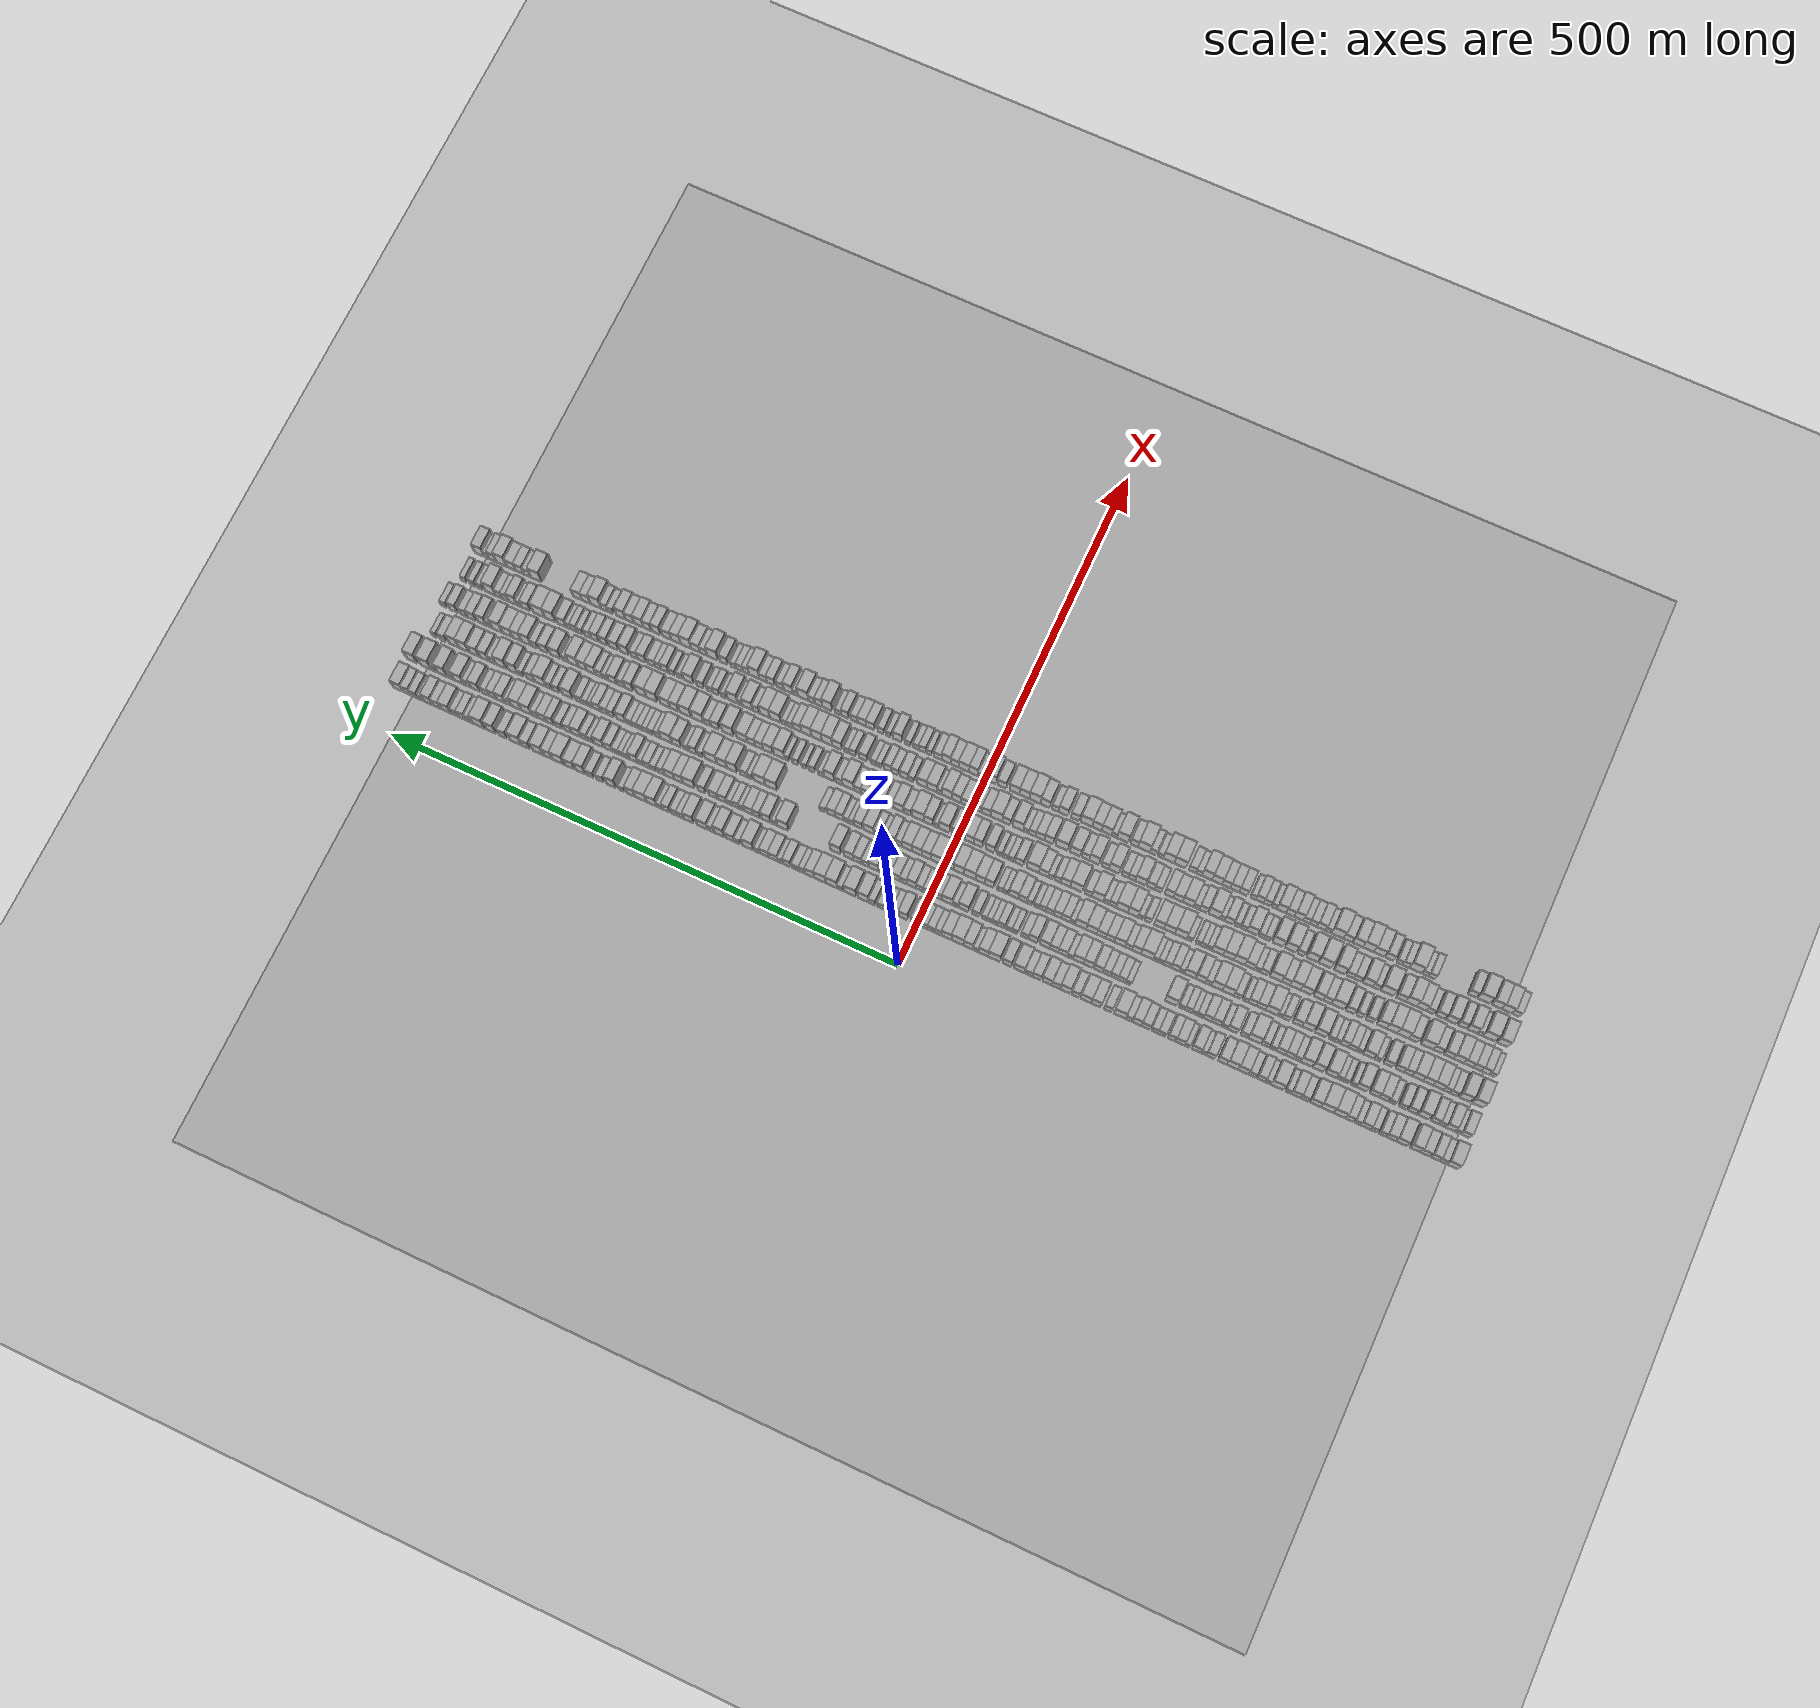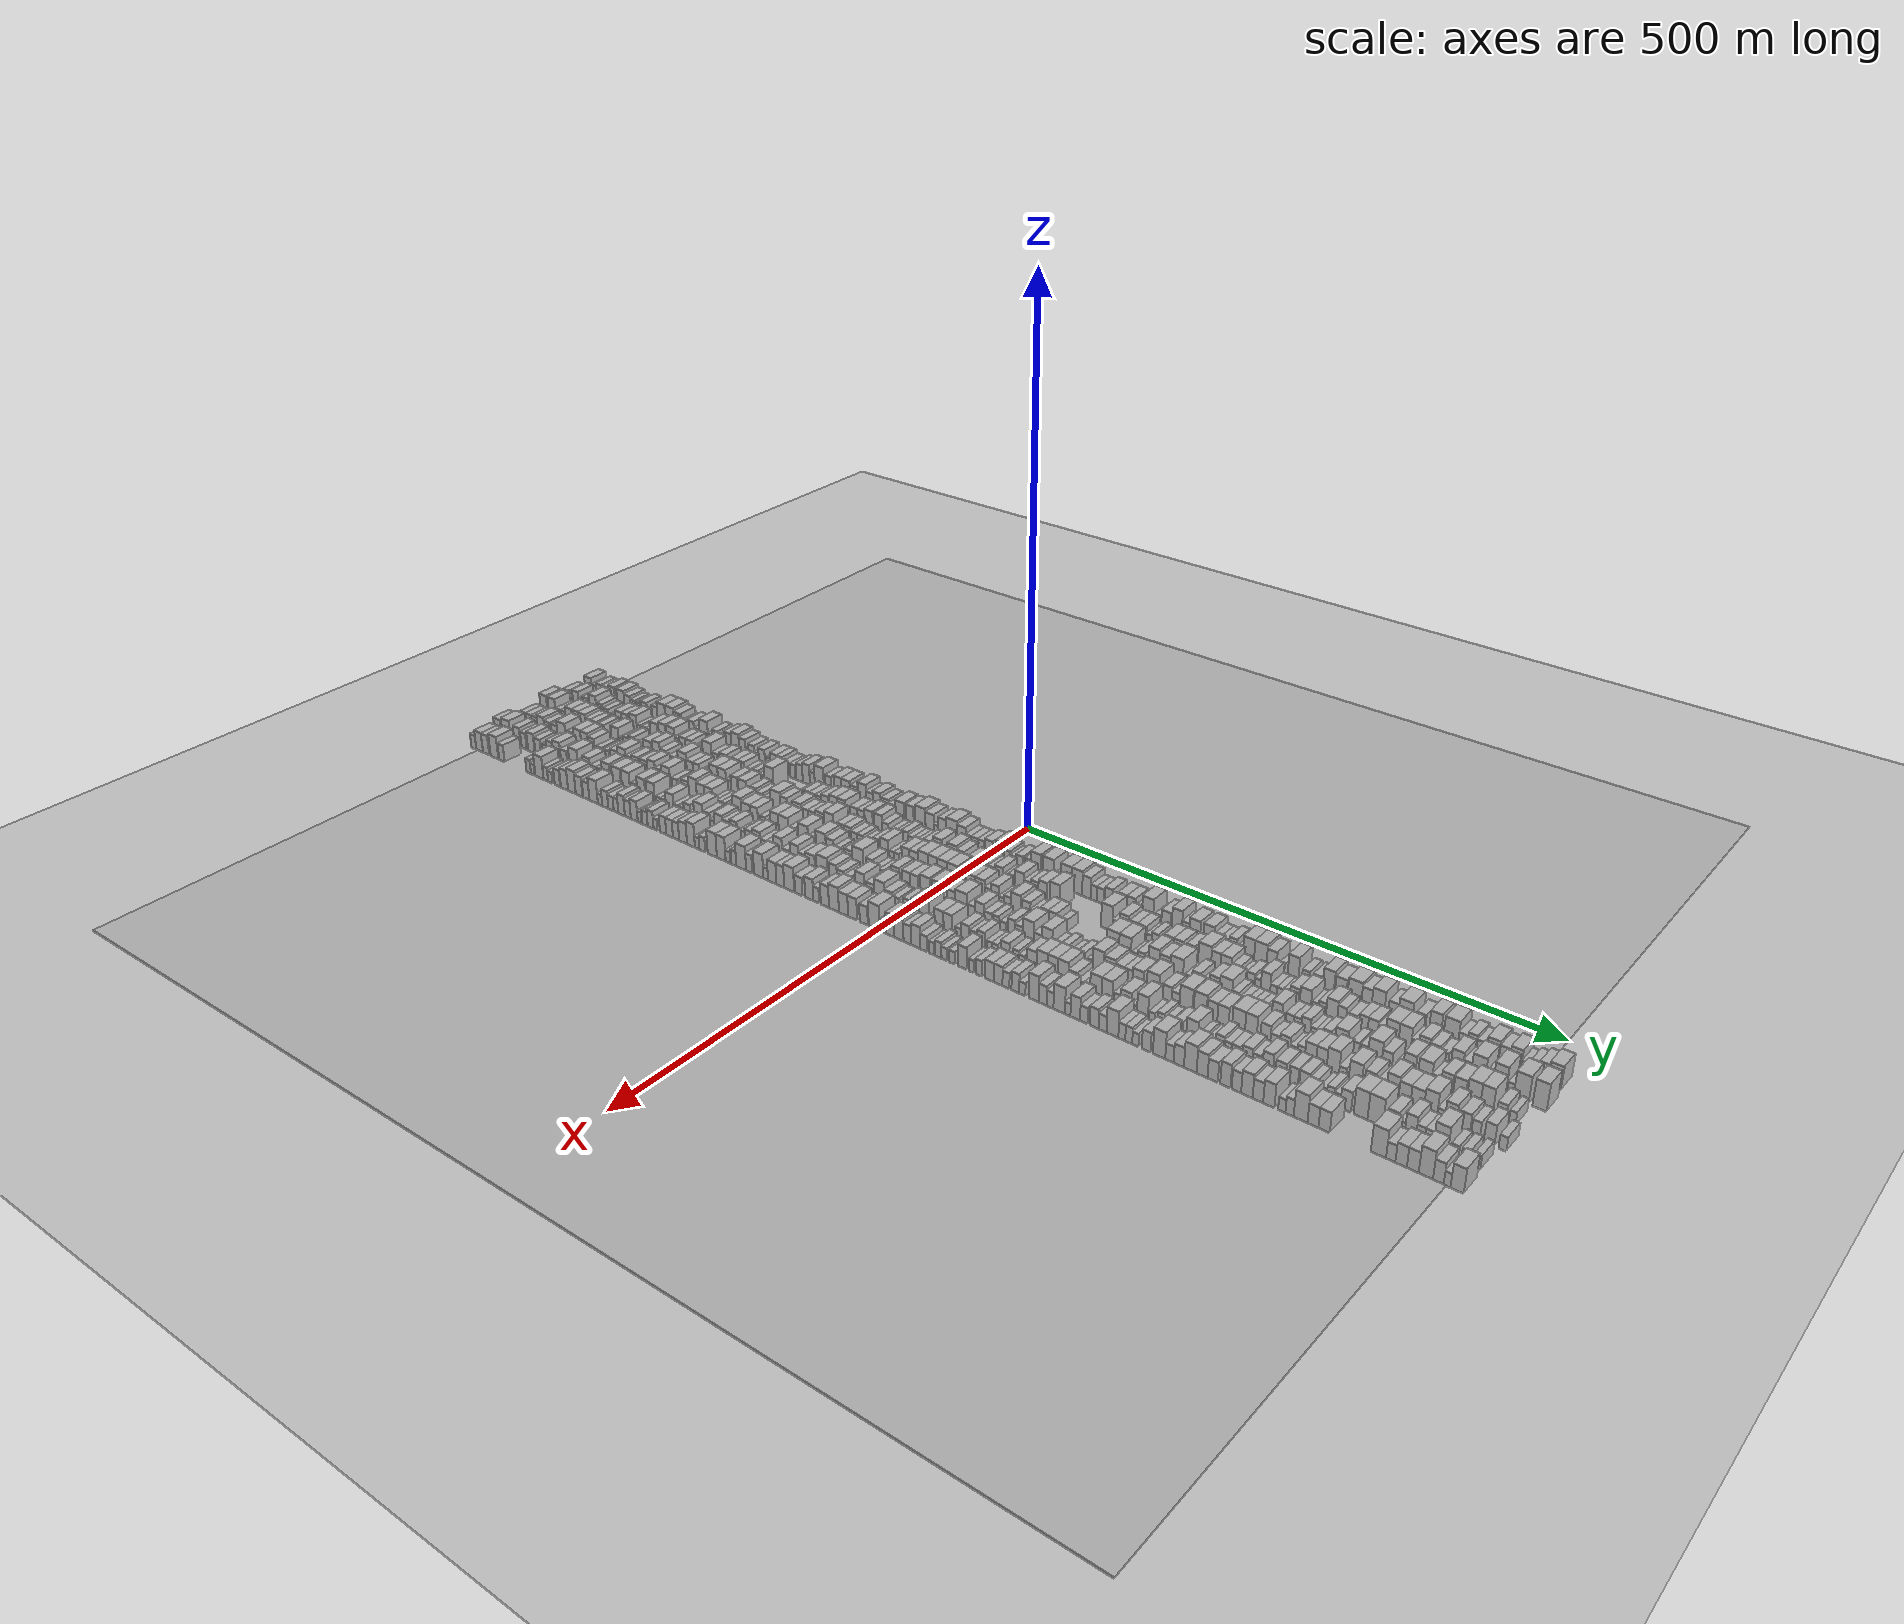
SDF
<?xml version="1.0" encoding="utf-8"?>

<sdf version="1.6">

   <world name="default">

      <gui fullscreen="0">

         <camera name="user_camera">

            <pose>-15 0 4.57585 0 0 0</pose>

            <view_controller>orbit</view_controller>

         </camera>

      </gui>

      <scene>

         <sky>

           <clouds>

             <speed>12</speed>

           </clouds>

         </sky>

         <ambient>0.4 0.4 0.4 1</ambient>

         <background>0.7 0.7 0.7 1</background>

         <shadows>1</shadows>

      </scene>

      <gravity>0 0 -9.8066</gravity>

      <magnetic_field>6e-06 2.3e-05 -4.2e-05</magnetic_field>

      <physics default="0" name="default_physics" type="ode">

         <ode>

            <solver>

               <type>quick</type>

               <iters>10</iters>

               <sor>1.0</sor>

               <use_dynamic_moi_rescaling>0</use_dynamic_moi_rescaling>

            </solver>

            <constraints>

               <cfm>0</cfm>

               <erp>0.2</erp>

               <contact_max_correcting_vel>100</contact_max_correcting_vel>

               <contact_surface_layer>0.001</contact_surface_layer>

            </constraints>

         </ode>

         <max_step_size>0.004</max_step_size>

         <real_time_factor>1</real_time_factor>

         <real_time_update_rate>250</real_time_update_rate>

      </physics>

      <light name="sun" type="directional">

         <cast_shadows>1</cast_shadows>

         <pose>0 0 10 0 0 0</pose>

         <diffuse>0.8 0.8 0.8 1</diffuse>

         <specular>0.2 0.2 0.2 1</specular>

         <attenuation>

            <range>1000</range>

            <constant>0.9</constant>

            <linear>0.01</linear>

            <quadratic>0.001</quadratic>

         </attenuation>

         <direction>-0.5 0.1 -0.9</direction>

      </light>

      <include>

         <name>ground_plane_1</name>

         <uri>model://HANNAS_ground_plane</uri>

         <pose>0 0 0  0 0 0</pose>

      </include>

      <include>

         <name>ground_plane_2</name>

         <uri>model://HANNAS_ground_plane</uri>

         <pose>100 0 0  0 0 0</pose>

      </include>

      <model name="building_1">

         <static>1</static>

         <pose frame="">50.0000 -504.8626 0 0.000000 0.000000 0.000000</pose>

         <link name="link">

            <pose frame="">0 0 10.50 0 0 0</pose>

            <collision name="collision">

               <geometry>

                  <box>

                     <size>20.0000 10.2747 21.0000</size>

                  </box>

               </geometry>

               <max_contacts>10</max_contacts>

               <surface>

                  <contact>

                     <ode/>

                  </contact>

                  <bounce/>

                  <friction>

                     <torsional>

                        <ode/>

                     </torsional>

                     <ode/>

                  </friction>

               </surface>

            </collision>

            <visual name="visual">

               <cast_shadows>0</cast_shadows>

               <geometry>

                  <box>

                     <size>20.0000 10.2747 21.0000</size>

                  </box>

               </geometry>

               <material>

                  <script>

                     <uri>model://HANNAS_wall/materials/scripts</uri>

                     <uri>model://HANNAS_wall/materials/textures</uri>

                     <name>vrc/HANNAS_wall</name>

                  </script>

               </material>

            </visual>

            <self_collide>0</self_collide>

            <enable_wind>0</enable_wind>

            <kinematic>0</kinematic>

         </link>

      </model>

      <model name="building_2">

         <static>1</static>

         <pose frame="">50.0000 -496.3525 0 0.000000 0.000000 0.000000</pose>

         <link name="link">

            <pose frame="">0 0 7.50 0 0 0</pose>

            <collision name="collision">

               <geometry>

                  <box>

                     <size>20.0000 6.7457 15.0000</size>

                  </box>

               </geometry>

               <max_contacts>10</max_contacts>

               <surface>

                  <contact>

                     <ode/>

                  </contact>

                  <bounce/>

                  <friction>

                     <torsional>

                        <ode/>

                     </torsional>

                     <ode/>

                  </friction>

               </surface>

            </collision>

            <visual name="visual">

               <cast_shadows>0</cast_shadows>

               <geometry>

                  <box>

                     <size>20.0000 6.7457 15.0000</size>

                  </box>

               </geometry>

               <material>

                  <script>

                     <uri>model://HANNAS_wall/materials/scripts</uri>

                     <uri>model://HANNAS_wall/materials/textures</uri>

                     <name>vrc/HANNAS_wall</name>

                  </script>

               </material>

            </visual>

            <self_collide>0</self_collide>

            <enable_wind>0</enable_wind>

            <kinematic>0</kinematic>

         </link>

      </model>

      <model name="building_3">

         <static>1</static>

         <pose frame="">50.0000 -489.1869 0 0.000000 0.000000 0.000000</pose>

         <link name="link">

            <pose frame="">0 0 9.00 0 0 0</pose>

            <collision name="collision">

               <geometry>

                  <box>

                     <size>20.0000 7.5855 18.0000</size>

                  </box>

               </geometry>

               <max_contacts>10</max_contacts>

               <surface>

                  <contact>

                     <ode/>

                  </contact>

                  <bounce/>

                  <friction>

                     <torsional>

                        <ode/>

                     </torsional>

                     <ode/>

                  </friction>

               </surface>

            </collision>

            <visual name="visual">

               <cast_shadows>0</cast_shadows>

               <geometry>

                  <box>

                     <size>20.0000 7.5855 18.0000</size>

                  </box>

               </geometry>

               <material>

                  <script>

                     <uri>model://HANNAS_wall/materials/scripts</uri>

                     <uri>model://HANNAS_wall/materials/textures</uri>

                     <name>vrc/HANNAS_wall</name>

                  </script>

               </material>

            </visual>

            <self_collide>0</self_collide>

            <enable_wind>0</enable_wind>

            <kinematic>0</kinematic>

         </link>

      </model>

      <model name="building_4">

         <static>1</static>

         <pose frame="">50.0000 -479.9340 0 0.000000 0.000000 0.000000</pose>

         <link name="link">

            <pose frame="">0 0 9.00 0 0 0</pose>

            <collision name="collision">

               <geometry>

                  <box>

                     <size>20.0000 8.9202 18.0000</size>

                  </box>

               </geometry>

               <max_contacts>10</max_contacts>

               <surface>

                  <contact>

                     <ode/>

                  </contact>

                  <bounce/>

                  <friction>

                     <torsional>

                        <ode/>

                     </torsional>

                     <ode/>

                  </friction>

               </surface>

            </collision>

            <visual name="visual">

               <cast_shadows>0</cast_shadows>

               <geometry>

                  <box>

                     <size>20.0000 8.9202 18.0000</size>

                  </box>

               </geometry>

               <material>

                  <script>

                     <uri>model://HANNAS_wall/materials/scripts</uri>

                     <uri>model://HANNAS_wall/materials/textures</uri>

                     <name>vrc/HANNAS_wall</name>

                  </script>

               </material>

            </visual>

            <self_collide>0</self_collide>

            <enable_wind>0</enable_wind>

            <kinematic>0</kinematic>

         </link>

      </model>

      <model name="building_5">

         <static>1</static>

         <pose frame="">50.0000 -470.8063 0 0.000000 0.000000 0.000000</pose>

         <link name="link">

            <pose frame="">0 0 10.50 0 0 0</pose>

            <collision name="collision">

               <geometry>

                  <box>

                     <size>20.0000 9.3353 21.0000</size>

                  </box>

               </geometry>

               <max_contacts>10</max_contacts>

               <surface>

                  <contact>

                     <ode/>

                  </contact>

                  <bounce/>

                  <friction>

                     <torsional>

                        <ode/>

                     </torsional>

                     <ode/>

                  </friction>

               </surface>

            </collision>

            <visual name="visual">

               <cast_shadows>0</cast_shadows>

               <geometry>

                  <box>

                     <size>20.0000 9.3353 21.0000</size>

                  </box>

               </geometry>

               <material>

                  <script>

                     <uri>model://HANNAS_wall/materials/scripts</uri>

                     <uri>model://HANNAS_wall/materials/textures</uri>

                     <name>vrc/HANNAS_wall</name>

                  </script>

               </material>

            </visual>

            <self_collide>0</self_collide>

            <enable_wind>0</enable_wind>

            <kinematic>0</kinematic>

         </link>

      </model>

      <model name="building_6">

         <static>1</static>

         <pose frame="">50.0000 -457.9626 0 0.000000 0.000000 0.000000</pose>

         <link name="link">

            <pose frame="">0 0 10.50 0 0 0</pose>

            <collision name="collision">

               <geometry>

                  <box>

                     <size>20.0000 10.3521 21.0000</size>

                  </box>

               </geometry>

               <max_contacts>10</max_contacts>

               <surface>

                  <contact>

                     <ode/>

                  </contact>

                  <bounce/>

                  <friction>

                     <torsional>

                        <ode/>

                     </torsional>

                     <ode/>

                  </friction>

               </surface>

            </collision>

            <visual name="visual">

               <cast_shadows>0</cast_shadows>

               <geometry>

                  <box>

                     <size>20.0000 10.3521 21.0000</size>

                  </box>

               </geometry>

               <material>

                  <script>

                     <uri>model://HANNAS_wall/materials/scripts</uri>

                     <uri>model://HANNAS_wall/materials/textures</uri>

                     <name>vrc/HANNAS_wall</name>

                  </script>

               </material>

            </visual>

            <self_collide>0</self_collide>

            <enable_wind>0</enable_wind>

            <kinematic>0</kinematic>

         </link>

      </model>

      <model name="building_7">

         <static>1</static>

         <pose frame="">50.0000 -448.3528 0 0.000000 0.000000 0.000000</pose>

         <link name="link">

            <pose frame="">0 0 9.00 0 0 0</pose>

            <collision name="collision">

               <geometry>

                  <box>

                     <size>20.0000 8.8675 18.0000</size>

                  </box>

               </geometry>

               <max_contacts>10</max_contacts>

               <surface>

                  <contact>

                     <ode/>

                  </contact>

                  <bounce/>

                  <friction>

                     <torsional>

                        <ode/>

                     </torsional>

                     <ode/>

                  </friction>

               </surface>

            </collision>

            <visual name="visual">

               <cast_shadows>0</cast_shadows>

               <geometry>

                  <box>

                     <size>20.0000 8.8675 18.0000</size>

                  </box>

               </geometry>

               <material>

                  <script>

                     <uri>model://HANNAS_wall/materials/scripts</uri>

                     <uri>model://HANNAS_wall/materials/textures</uri>

                     <name>vrc/HANNAS_wall</name>

                  </script>

               </material>

            </visual>

            <self_collide>0</self_collide>

            <enable_wind>0</enable_wind>

            <kinematic>0</kinematic>

         </link>

      </model>

      <model name="building_8">

         <static>1</static>

         <pose frame="">50.0000 -440.7087 0 0.000000 0.000000 0.000000</pose>

         <link name="link">

            <pose frame="">0 0 7.50 0 0 0</pose>

            <collision name="collision">

               <geometry>

                  <box>

                     <size>20.0000 6.4206 15.0000</size>

                  </box>

               </geometry>

               <max_contacts>10</max_contacts>

               <surface>

                  <contact>

                     <ode/>

                  </contact>

                  <bounce/>

                  <friction>

                     <torsional>

                        <ode/>

                     </torsional>

                     <ode/>

                  </friction>

               </surface>

            </collision>

            <visual name="visual">

               <cast_shadows>0</cast_shadows>

               <geometry>

                  <box>

                     <size>20.0000 6.4206 15.0000</size>

                  </box>

               </geometry>

               <material>

                  <script>

                     <uri>model://HANNAS_wall/materials/scripts</uri>

                     <uri>model://HANNAS_wall/materials/textures</uri>

                     <name>vrc/HANNAS_wall</name>

                  </script>

               </material>

            </visual>

            <self_collide>0</self_collide>

            <enable_wind>0</enable_wind>

            <kinematic>0</kinematic>

         </link>

      </model>

      <model name="building_9">

         <static>1</static>

         <pose frame="">50.0000 -432.3161 0 0.000000 0.000000 0.000000</pose>

         <link name="link">

            <pose frame="">0 0 7.50 0 0 0</pose>

            <collision name="collision">

               <geometry>

                  <box>

                     <size>20.0000 6.3647 15.0000</size>

                  </box>

               </geometry>

               <max_contacts>10</max_contacts>

               <surface>

                  <contact>

                     <ode/>

                  </contact>

                  <bounce/>

                  <friction>

                     <torsional>

                        <ode/>

                     </torsional>

                     <ode/>

                  </friction>

               </surface>

            </collision>

            <visual name="visual">

               <cast_shadows>0</cast_shadows>

               <geometry>

                  <box>

                     <size>20.0000 6.3647 15.0000</size>

                  </box>

               </geometry>

               <material>

                  <script>

                     <uri>model://HANNAS_wall/materials/scripts</uri>

                     <uri>model://HANNAS_wall/materials/textures</uri>

                     <name>vrc/HANNAS_wall</name>

                  </script>

               </material>

            </visual>

            <self_collide>0</self_collide>

            <enable_wind>0</enable_wind>

            <kinematic>0</kinematic>

         </link>

      </model>

      <model name="building_10">

         <static>1</static>

         <pose frame="">50.0000 -424.7892 0 0.000000 0.000000 0.000000</pose>

         <link name="link">

            <pose frame="">0 0 9.00 0 0 0</pose>

            <collision name="collision">

               <geometry>

                  <box>

                     <size>20.0000 8.6890 18.0000</size>

                  </box>

               </geometry>

               <max_contacts>10</max_contacts>

               <surface>

                  <contact>

                     <ode/>

                  </contact>

                  <bounce/>

                  <friction>

                     <torsional>

                        <ode/>

                     </torsional>

                     <ode/>

                  </friction>

               </surface>

            </collision>

            <visual name="visual">

               <cast_shadows>0</cast_shadows>

               <geometry>

                  <box>

                     <size>20.0000 8.6890 18.0000</size>

                  </box>

               </geometry>

               <material>

                  <script>

                     <uri>model://HANNAS_wall/materials/scripts</uri>

                     <uri>model://HANNAS_wall/materials/textures</uri>

                     <name>vrc/HANNAS_wall</name>

                  </script>

               </material>

            </visual>

            <self_collide>0</self_collide>

            <enable_wind>0</enable_wind>

            <kinematic>0</kinematic>

         </link>

      </model>

      <model name="building_11">

         <static>1</static>

         <pose frame="">50.0000 -417.5978 0 0.000000 0.000000 0.000000</pose>

         <link name="link">

            <pose frame="">0 0 6.00 0 0 0</pose>

            <collision name="collision">

               <geometry>

                  <box>

                     <size>20.0000 5.6939 12.0000</size>

                  </box>

               </geometry>

               <max_contacts>10</max_contacts>

               <surface>

                  <contact>

                     <ode/>

                  </contact>

                  <bounce/>

                  <friction>

                     <torsional>

                        <ode/>

                     </torsional>

                     <ode/>

                  </friction>

               </surface>

            </collision>

            <visual name="visual">

               <cast_shadows>0</cast_shadows>

               <geometry>

                  <box>

                     <size>20.0000 5.6939 12.0000</size>

                  </box>

               </geometry>

               <material>

                  <script>

                     <uri>model://HANNAS_wall/materials/scripts</uri>

                     <uri>model://HANNAS_wall/materials/textures</uri>

                     <name>vrc/HANNAS_wall</name>

                  </script>

               </material>

            </visual>

            <self_collide>0</self_collide>

            <enable_wind>0</enable_wind>

            <kinematic>0</kinematic>

         </link>

      </model>

      <model name="building_12">

         <static>1</static>

         <pose frame="">50.0000 -409.8440 0 0.000000 0.000000 0.000000</pose>

         <link name="link">

            <pose frame="">0 0 9.00 0 0 0</pose>

            <collision name="collision">

               <geometry>

                  <box>

                     <size>20.0000 7.8137 18.0000</size>

                  </box>

               </geometry>

               <max_contacts>10</max_contacts>

               <surface>

                  <contact>

                     <ode/>

                  </contact>

                  <bounce/>

                  <friction>

                     <torsional>

                        <ode/>

                     </torsional>

                     <ode/>

                  </friction>

               </surface>

            </collision>

            <visual name="visual">

               <cast_shadows>0</cast_shadows>

               <geometry>

                  <box>

                     <size>20.0000 7.8137 18.0000</size>

                  </box>

               </geometry>

               <material>

                  <script>

                     <uri>model://HANNAS_wall/materials/scripts</uri>

                     <uri>model://HANNAS_wall/materials/textures</uri>

                     <name>vrc/HANNAS_wall</name>

                  </script>

               </material>

            </visual>

            <self_collide>0</self_collide>

            <enable_wind>0</enable_wind>

            <kinematic>0</kinematic>

         </link>

      </model>

      <model name="building_13">

         <static>1</static>

         <pose frame="">50.0000 -400.4473 0 0.000000 0.000000 0.000000</pose>

         <link name="link">

            <pose frame="">0 0 12.00 0 0 0</pose>

            <collision name="collision">

               <geometry>

                  <box>

                     <size>20.0000 10.9797 24.0000</size>

                  </box>

               </geometry>

               <max_contacts>10</max_contacts>

               <surface>

                  <contact>

                     <ode/>

                  </contact>

                  <bounce/>

                  <friction>

                     <torsional>

                        <ode/>

                     </torsional>

                     <ode/>

                  </friction>

               </surface>

            </collision>

            <visual name="visual">

               <cast_shadows>0</cast_shadows>

               <geometry>

                  <box>

                     <size>20.0000 10.9797 24.0000</size>

                  </box>

               </geometry>

               <material>

                  <script>

                     <uri>model://HANNAS_wall/materials/scripts</uri>

                     <uri>model://HANNAS_wall/materials/textures</uri>

                     <name>vrc/HANNAS_wall</name>

                  </script>

               </material>

            </visual>

            <self_collide>0</self_collide>

            <enable_wind>0</enable_wind>

            <kinematic>0</kinematic>

         </link>

      </model>

      <model name="building_14">

         <static>1</static>

         <pose frame="">50.0000 -388.9657 0 0.000000 0.000000 0.000000</pose>

         <link name="link">

            <pose frame="">0 0 12.00 0 0 0</pose>

            <collision name="collision">

               <geometry>

                  <box>

                     <size>20.0000 11.9835 24.0000</size>

                  </box>

               </geometry>

               <max_contacts>10</max_contacts>

               <surface>

                  <contact>

                     <ode/>

                  </contact>

                  <bounce/>

                  <friction>

                     <torsional>

                        <ode/>

                     </torsional>

                     <ode/>

                  </friction>

               </surface>

            </collision>

            <visual name="visual">

               <cast_shadows>0</cast_shadows>

               <geometry>

                  <box>

                     <size>20.0000 11.9835 24.0000</size>

                  </box>

               </geometry>

               <material>

                  <script>

                     <uri>model://HANNAS_wall/materials/scripts</uri>

                     <uri>model://HANNAS_wall/materials/textures</uri>

                     <name>vrc/HANNAS_wall</name>

                  </script>

               </material>

            </visual>

            <self_collide>0</self_collide>

            <enable_wind>0</enable_wind>

            <kinematic>0</kinematic>

         </link>

      </model>

      <model name="building_15">

         <static>1</static>

         <pose frame="">50.0000 -378.0075 0 0.000000 0.000000 0.000000</pose>

         <link name="link">

            <pose frame="">0 0 10.50 0 0 0</pose>

            <collision name="collision">

               <geometry>

                  <box>

                     <size>20.0000 9.9328 21.0000</size>

                  </box>

               </geometry>

               <max_contacts>10</max_contacts>

               <surface>

                  <contact>

                     <ode/>

                  </contact>

                  <bounce/>

                  <friction>

                     <torsional>

                        <ode/>

                     </torsional>

                     <ode/>

                  </friction>

               </surface>

            </collision>

            <visual name="visual">

               <cast_shadows>0</cast_shadows>

               <geometry>

                  <box>

                     <size>20.0000 9.9328 21.0000</size>

                  </box>

               </geometry>

               <material>

                  <script>

                     <uri>model://HANNAS_wall/materials/scripts</uri>

                     <uri>model://HANNAS_wall/materials/textures</uri>

                     <name>vrc/HANNAS_wall</name>

                  </script>

               </material>

            </visual>

            <self_collide>0</self_collide>

            <enable_wind>0</enable_wind>

            <kinematic>0</kinematic>

         </link>

      </model>

      <model name="building_16">

         <static>1</static>

         <pose frame="">50.0000 -368.3088 0 0.000000 0.000000 0.000000</pose>

         <link name="link">

            <pose frame="">0 0 7.50 0 0 0</pose>

            <collision name="collision">

               <geometry>

                  <box>

                     <size>20.0000 7.4647 15.0000</size>

                  </box>

               </geometry>

               <max_contacts>10</max_contacts>

               <surface>

                  <contact>

                     <ode/>

                  </contact>

                  <bounce/>

                  <friction>

                     <torsional>

                        <ode/>

                     </torsional>

                     <ode/>

                  </friction>

               </surface>

            </collision>

            <visual name="visual">

               <cast_shadows>0</cast_shadows>

               <geometry>

                  <box>

                     <size>20.0000 7.4647 15.0000</size>

                  </box>

               </geometry>

               <material>

                  <script>

                     <uri>model://HANNAS_wall/materials/scripts</uri>

                     <uri>model://HANNAS_wall/materials/textures</uri>

                     <name>vrc/HANNAS_wall</name>

                  </script>

               </material>

            </visual>

            <self_collide>0</self_collide>

            <enable_wind>0</enable_wind>

            <kinematic>0</kinematic>

         </link>

      </model>

      <model name="building_17">

         <static>1</static>

         <pose frame="">50.0000 -360.1716 0 0.000000 0.000000 0.000000</pose>

         <link name="link">

            <pose frame="">0 0 9.00 0 0 0</pose>

            <collision name="collision">

               <geometry>

                  <box>

                     <size>20.0000 8.8097 18.0000</size>

                  </box>

               </geometry>

               <max_contacts>10</max_contacts>

               <surface>

                  <contact>

                     <ode/>

                  </contact>

                  <bounce/>

                  <friction>

                     <torsional>

                        <ode/>

                     </torsional>

                     <ode/>

                  </friction>

               </surface>

            </collision>

            <visual name="visual">

               <cast_shadows>0</cast_shadows>

               <geometry>

                  <box>

                     <size>20.0000 8.8097 18.0000</size>

                  </box>

               </geometry>

               <material>

                  <script>

                     <uri>model://HANNAS_wall/materials/scripts</uri>

                     <uri>model://HANNAS_wall/materials/textures</uri>

                     <name>vrc/HANNAS_wall</name>

                  </script>

               </material>

            </visual>

            <self_collide>0</self_collide>

            <enable_wind>0</enable_wind>

            <kinematic>0</kinematic>

         </link>

      </model>

      <model name="building_18">

         <static>1</static>

         <pose frame="">50.0000 -353.0595 0 0.000000 0.000000 0.000000</pose>

         <link name="link">

            <pose frame="">0 0 6.00 0 0 0</pose>

            <collision name="collision">

               <geometry>

                  <box>

                     <size>20.0000 5.4145 12.0000</size>

                  </box>

               </geometry>

               <max_contacts>10</max_contacts>

               <surface>

                  <contact>

                     <ode/>

                  </contact>

                  <bounce/>

                  <friction>

                     <torsional>

                        <ode/>

                     </torsional>

                     <ode/>

                  </friction>

               </surface>

            </collision>

            <visual name="visual">

               <cast_shadows>0</cast_shadows>

               <geometry>

                  <box>

                     <size>20.0000 5.4145 12.0000</size>

                  </box>

               </geometry>

               <material>

                  <script>

                     <uri>model://HANNAS_wall/materials/scripts</uri>

                     <uri>model://HANNAS_wall/materials/textures</uri>

                     <name>vrc/HANNAS_wall</name>

                  </script>

               </material>

            </visual>

            <self_collide>0</self_collide>

            <enable_wind>0</enable_wind>

            <kinematic>0</kinematic>

         </link>

      </model>

      <model name="building_19">

         <static>1</static>

         <pose frame="">50.0000 -342.5915 0 0.000000 0.000000 0.000000</pose>

         <link name="link">

            <pose frame="">0 0 12.00 0 0 0</pose>

            <collision name="collision">

               <geometry>

                  <box>

                     <size>20.0000 11.5216 24.0000</size>

                  </box>

               </geometry>

               <max_contacts>10</max_contacts>

               <surface>

                  <contact>

                     <ode/>

                  </contact>

                  <bounce/>

                  <friction>

                     <torsional>

                        <ode/>

                     </torsional>

                     <ode/>

                  </friction>

               </surface>

            </collision>

            <visual name="visual">

               <cast_shadows>0</cast_shadows>

               <geometry>

                  <box>

                     <size>20.0000 11.5216 24.0000</size>

                  </box>

               </geometry>

               <material>

                  <script>

                     <uri>model://HANNAS_wall/materials/scripts</uri>

                     <uri>model://HANNAS_wall/materials/textures</uri>

                     <name>vrc/HANNAS_wall</name>

                  </script>

               </material>

            </visual>

            <self_collide>0</self_collide>

            <enable_wind>0</enable_wind>

            <kinematic>0</kinematic>

         </link>

      </model>

      <model name="building_20">

         <static>1</static>

         <pose frame="">50.0000 -334.0508 0 0.000000 0.000000 0.000000</pose>

         <link name="link">

            <pose frame="">0 0 6.00 0 0 0</pose>

            <collision name="collision">

               <geometry>

                  <box>

                     <size>20.0000 5.5599 12.0000</size>

                  </box>

               </geometry>

               <max_contacts>10</max_contacts>

               <surface>

                  <contact>

                     <ode/>

                  </contact>

                  <bounce/>

                  <friction>

                     <torsional>

                        <ode/>

                     </torsional>

                     <ode/>

                  </friction>

               </surface>

            </collision>

            <visual name="visual">

               <cast_shadows>0</cast_shadows>

               <geometry>

                  <box>

                     <size>20.0000 5.5599 12.0000</size>

                  </box>

               </geometry>

               <material>

                  <script>

                     <uri>model://HANNAS_wall/materials/scripts</uri>

                     <uri>model://HANNAS_wall/materials/textures</uri>

                     <name>vrc/HANNAS_wall</name>

                  </script>

               </material>

            </visual>

            <self_collide>0</self_collide>

            <enable_wind>0</enable_wind>

            <kinematic>0</kinematic>

         </link>

      </model>

      <model name="building_21">

         <static>1</static>

         <pose frame="">50.0000 -327.4666 0 0.000000 0.000000 0.000000</pose>

         <link name="link">

            <pose frame="">0 0 9.00 0 0 0</pose>

            <collision name="collision">

               <geometry>

                  <box>

                     <size>20.0000 7.6085 18.0000</size>

                  </box>

               </geometry>

               <max_contacts>10</max_contacts>

               <surface>

                  <contact>

                     <ode/>

                  </contact>

                  <bounce/>

                  <friction>

                     <torsional>

                        <ode/>

                     </torsional>

                     <ode/>

                  </friction>

               </surface>

            </collision>

            <visual name="visual">

               <cast_shadows>0</cast_shadows>

               <geometry>

                  <box>

                     <size>20.0000 7.6085 18.0000</size>

                  </box>

               </geometry>

               <material>

                  <script>

                     <uri>model://HANNAS_wall/materials/scripts</uri>

                     <uri>model://HANNAS_wall/materials/textures</uri>

                     <name>vrc/HANNAS_wall</name>

                  </script>

               </material>

            </visual>

            <self_collide>0</self_collide>

            <enable_wind>0</enable_wind>

            <kinematic>0</kinematic>

         </link>

      </model>

      <model name="building_22">

         <static>1</static>

         <pose frame="">50.0000 -318.9806 0 0.000000 0.000000 0.000000</pose>

         <link name="link">

            <pose frame="">0 0 7.50 0 0 0</pose>

            <collision name="collision">

               <geometry>

                  <box>

                     <size>20.0000 7.3633 15.0000</size>

                  </box>

               </geometry>

               <max_contacts>10</max_contacts>

               <surface>

                  <contact>

                     <ode/>

                  </contact>

                  <bounce/>

                  <friction>

                     <torsional>

                        <ode/>

                     </torsional>

                     <ode/>

                  </friction>

               </surface>

            </collision>

            <visual name="visual">

               <cast_shadows>0</cast_shadows>

               <geometry>

                  <box>

                     <size>20.0000 7.3633 15.0000</size>

                  </box>

               </geometry>

               <material>

                  <script>

                     <uri>model://HANNAS_wall/materials/scripts</uri>

                     <uri>model://HANNAS_wall/materials/textures</uri>

                     <name>vrc/HANNAS_wall</name>

                  </script>

               </material>

            </visual>

            <self_collide>0</self_collide>

            <enable_wind>0</enable_wind>

            <kinematic>0</kinematic>

         </link>

      </model>

      <model name="building_23">

         <static>1</static>

         <pose frame="">50.0000 -310.5324 0 0.000000 0.000000 0.000000</pose>

         <link name="link">

            <pose frame="">0 0 10.50 0 0 0</pose>

            <collision name="collision">

               <geometry>

                  <box>

                     <size>20.0000 9.5332 21.0000</size>

                  </box>

               </geometry>

               <max_contacts>10</max_contacts>

               <surface>

                  <contact>

                     <ode/>

                  </contact>

                  <bounce/>

                  <friction>

                     <torsional>

                        <ode/>

                     </torsional>

                     <ode/>

                  </friction>

               </surface>

            </collision>

            <visual name="visual">

               <cast_shadows>0</cast_shadows>

               <geometry>

                  <box>

                     <size>20.0000 9.5332 21.0000</size>

                  </box>

               </geometry>

               <material>

                  <script>

                     <uri>model://HANNAS_wall/materials/scripts</uri>

                     <uri>model://HANNAS_wall/materials/textures</uri>

                     <name>vrc/HANNAS_wall</name>

                  </script>

               </material>

            </visual>

            <self_collide>0</self_collide>

            <enable_wind>0</enable_wind>

            <kinematic>0</kinematic>

         </link>

      </model>

      <model name="building_24">

         <static>1</static>

         <pose frame="">50.0000 -300.6902 0 0.000000 0.000000 0.000000</pose>

         <link name="link">

            <pose frame="">0 0 12.00 0 0 0</pose>

            <collision name="collision">

               <geometry>

                  <box>

                     <size>20.0000 10.1513 24.0000</size>

                  </box>

               </geometry>

               <max_contacts>10</max_contacts>

               <surface>

                  <contact>

                     <ode/>

                  </contact>

                  <bounce/>

                  <friction>

                     <torsional>

                        <ode/>

                     </torsional>

                     <ode/>

                  </friction>

               </surface>

            </collision>

            <visual name="visual">

               <cast_shadows>0</cast_shadows>

               <geometry>

                  <box>

                     <size>20.0000 10.1513 24.0000</size>

                  </box>

               </geometry>

               <material>

                  <script>

                     <uri>model://HANNAS_wall/materials/scripts</uri>

                     <uri>model://HANNAS_wall/materials/textures</uri>

                     <name>vrc/HANNAS_wall</name>

                  </script>

               </material>

            </visual>

            <self_collide>0</self_collide>

            <enable_wind>0</enable_wind>

            <kinematic>0</kinematic>

         </link>

      </model>

      <model name="building_25">

         <static>1</static>

         <pose frame="">50.0000 -291.3003 0 0.000000 0.000000 0.000000</pose>

         <link name="link">

            <pose frame="">0 0 10.50 0 0 0</pose>

            <collision name="collision">

               <geometry>

                  <box>

                     <size>20.0000 8.6285 21.0000</size>

                  </box>

               </geometry>

               <max_contacts>10</max_contacts>

               <surface>

                  <contact>

                     <ode/>

                  </contact>

                  <bounce/>

                  <friction>

                     <torsional>

                        <ode/>

                     </torsional>

                     <ode/>

                  </friction>

               </surface>

            </collision>

            <visual name="visual">

               <cast_shadows>0</cast_shadows>

               <geometry>

                  <box>

                     <size>20.0000 8.6285 21.0000</size>

                  </box>

               </geometry>

               <material>

                  <script>

                     <uri>model://HANNAS_wall/materials/scripts</uri>

                     <uri>model://HANNAS_wall/materials/textures</uri>

                     <name>vrc/HANNAS_wall</name>

                  </script>

               </material>

            </visual>

            <self_collide>0</self_collide>

            <enable_wind>0</enable_wind>

            <kinematic>0</kinematic>

         </link>

      </model>

      <model name="building_26">

         <static>1</static>

         <pose frame="">50.0000 -280.0551 0 0.000000 0.000000 0.000000</pose>

         <link name="link">

            <pose frame="">0 0 9.00 0 0 0</pose>

            <collision name="collision">

               <geometry>

                  <box>

                     <size>20.0000 7.8619 18.0000</size>

                  </box>

               </geometry>

               <max_contacts>10</max_contacts>

               <surface>

                  <contact>

                     <ode/>

                  </contact>

                  <bounce/>

                  <friction>

                     <torsional>

                        <ode/>

                     </torsional>

                     <ode/>

                  </friction>

               </surface>

            </collision>

            <visual name="visual">

               <cast_shadows>0</cast_shadows>

               <geometry>

                  <box>

                     <size>20.0000 7.8619 18.0000</size>

                  </box>

               </geometry>

               <material>

                  <script>

                     <uri>model://HANNAS_wall/materials/scripts</uri>

                     <uri>model://HANNAS_wall/materials/textures</uri>

                     <name>vrc/HANNAS_wall</name>

                  </script>

               </material>

            </visual>

            <self_collide>0</self_collide>

            <enable_wind>0</enable_wind>

            <kinematic>0</kinematic>

         </link>

      </model>

      <model name="building_27">

         <static>1</static>

         <pose frame="">50.0000 -273.5944 0 0.000000 0.000000 0.000000</pose>

         <link name="link">

            <pose frame="">0 0 6.00 0 0 0</pose>

            <collision name="collision">

               <geometry>

                  <box>

                     <size>20.0000 5.0594 12.0000</size>

                  </box>

               </geometry>

               <max_contacts>10</max_contacts>

               <surface>

                  <contact>

                     <ode/>

                  </contact>

                  <bounce/>

                  <friction>

                     <torsional>

                        <ode/>

                     </torsional>

                     <ode/>

                  </friction>

               </surface>

            </collision>

            <visual name="visual">

               <cast_shadows>0</cast_shadows>

               <geometry>

                  <box>

                     <size>20.0000 5.0594 12.0000</size>

                  </box>

               </geometry>

               <material>

                  <script>

                     <uri>model://HANNAS_wall/materials/scripts</uri>

                     <uri>model://HANNAS_wall/materials/textures</uri>

                     <name>vrc/HANNAS_wall</name>

                  </script>

               </material>

            </visual>

            <self_collide>0</self_collide>

            <enable_wind>0</enable_wind>

            <kinematic>0</kinematic>

         </link>

      </model>

      <model name="building_28">

         <static>1</static>

         <pose frame="">50.0000 -266.7744 0 0.000000 0.000000 0.000000</pose>

         <link name="link">

            <pose frame="">0 0 9.00 0 0 0</pose>

            <collision name="collision">

               <geometry>

                  <box>

                     <size>20.0000 8.5807 18.0000</size>

                  </box>

               </geometry>

               <max_contacts>10</max_contacts>

               <surface>

                  <contact>

                     <ode/>

                  </contact>

                  <bounce/>

                  <friction>

                     <torsional>

                        <ode/>

                     </torsional>

                     <ode/>

                  </friction>

               </surface>

            </collision>

            <visual name="visual">

               <cast_shadows>0</cast_shadows>

               <geometry>

                  <box>

                     <size>20.0000 8.5807 18.0000</size>

                  </box>

               </geometry>

               <material>

                  <script>

                     <uri>model://HANNAS_wall/materials/scripts</uri>

                     <uri>model://HANNAS_wall/materials/textures</uri>

                     <name>vrc/HANNAS_wall</name>

                  </script>

               </material>

            </visual>

            <self_collide>0</self_collide>

            <enable_wind>0</enable_wind>

            <kinematic>0</kinematic>

         </link>

      </model>

      <model name="building_29">

         <static>1</static>

         <pose frame="">50.0000 -258.0686 0 0.000000 0.000000 0.000000</pose>

         <link name="link">

            <pose frame="">0 0 6.00 0 0 0</pose>

            <collision name="collision">

               <geometry>

                  <box>

                     <size>20.0000 4.8308 12.0000</size>

                  </box>

               </geometry>

               <max_contacts>10</max_contacts>

               <surface>

                  <contact>

                     <ode/>

                  </contact>

                  <bounce/>

                  <friction>

                     <torsional>

                        <ode/>

                     </torsional>

                     <ode/>

                  </friction>

               </surface>

            </collision>

            <visual name="visual">

               <cast_shadows>0</cast_shadows>

               <geometry>

                  <box>

                     <size>20.0000 4.8308 12.0000</size>

                  </box>

               </geometry>

               <material>

                  <script>

                     <uri>model://HANNAS_wall/materials/scripts</uri>

                     <uri>model://HANNAS_wall/materials/textures</uri>

                     <name>vrc/HANNAS_wall</name>

                  </script>

               </material>

            </visual>

            <self_collide>0</self_collide>

            <enable_wind>0</enable_wind>

            <kinematic>0</kinematic>

         </link>

      </model>

      <model name="building_30">

         <static>1</static>

         <pose frame="">50.0000 -251.3869 0 0.000000 0.000000 0.000000</pose>

         <link name="link">

            <pose frame="">0 0 9.00 0 0 0</pose>

            <collision name="collision">

               <geometry>

                  <box>

                     <size>20.0000 8.5327 18.0000</size>

                  </box>

               </geometry>

               <max_contacts>10</max_contacts>

               <surface>

                  <contact>

                     <ode/>

                  </contact>

                  <bounce/>

                  <friction>

                     <torsional>

                        <ode/>

                     </torsional>

                     <ode/>

                  </friction>

               </surface>

            </collision>

            <visual name="visual">

               <cast_shadows>0</cast_shadows>

               <geometry>

                  <box>

                     <size>20.0000 8.5327 18.0000</size>

                  </box>

               </geometry>

               <material>

                  <script>

                     <uri>model://HANNAS_wall/materials/scripts</uri>

                     <uri>model://HANNAS_wall/materials/textures</uri>

                     <name>vrc/HANNAS_wall</name>

                  </script>

               </material>

            </visual>

            <self_collide>0</self_collide>

            <enable_wind>0</enable_wind>

            <kinematic>0</kinematic>

         </link>

      </model>

      <model name="building_31">

         <static>1</static>

         <pose frame="">50.0000 -243.5036 0 0.000000 0.000000 0.000000</pose>

         <link name="link">

            <pose frame="">0 0 9.00 0 0 0</pose>

            <collision name="collision">

               <geometry>

                  <box>

                     <size>20.0000 7.2339 18.0000</size>

                  </box>

               </geometry>

               <max_contacts>10</max_contacts>

               <surface>

                  <contact>

                     <ode/>

                  </contact>

                  <bounce/>

                  <friction>

                     <torsional>

                        <ode/>

                     </torsional>

                     <ode/>

                  </friction>

               </surface>

            </collision>

            <visual name="visual">

               <cast_shadows>0</cast_shadows>

               <geometry>

                  <box>

                     <size>20.0000 7.2339 18.0000</size>

                  </box>

               </geometry>

               <material>

                  <script>

                     <uri>model://HANNAS_wall/materials/scripts</uri>

                     <uri>model://HANNAS_wall/materials/textures</uri>

                     <name>vrc/HANNAS_wall</name>

                  </script>

               </material>

            </visual>

            <self_collide>0</self_collide>

            <enable_wind>0</enable_wind>

            <kinematic>0</kinematic>

         </link>

      </model>

      <model name="building_32">

         <static>1</static>

         <pose frame="">50.0000 -234.1505 0 0.000000 0.000000 0.000000</pose>

         <link name="link">

            <pose frame="">0 0 7.50 0 0 0</pose>

            <collision name="collision">

               <geometry>

                  <box>

                     <size>20.0000 7.4723 15.0000</size>

                  </box>

               </geometry>

               <max_contacts>10</max_contacts>

               <surface>

                  <contact>

                     <ode/>

                  </contact>

                  <bounce/>

                  <friction>

                     <torsional>

                        <ode/>

                     </torsional>

                     <ode/>

                  </friction>

               </surface>

            </collision>

            <visual name="visual">

               <cast_shadows>0</cast_shadows>

               <geometry>

                  <box>

                     <size>20.0000 7.4723 15.0000</size>

                  </box>

               </geometry>

               <material>

                  <script>

                     <uri>model://HANNAS_wall/materials/scripts</uri>

                     <uri>model://HANNAS_wall/materials/textures</uri>

                     <name>vrc/HANNAS_wall</name>

                  </script>

               </material>

            </visual>

            <self_collide>0</self_collide>

            <enable_wind>0</enable_wind>

            <kinematic>0</kinematic>

         </link>

      </model>

      <model name="building_33">

         <static>1</static>

         <pose frame="">50.0000 -227.1314 0 0.000000 0.000000 0.000000</pose>

         <link name="link">

            <pose frame="">0 0 7.50 0 0 0</pose>

            <collision name="collision">

               <geometry>

                  <box>

                     <size>20.0000 6.5659 15.0000</size>

                  </box>

               </geometry>

               <max_contacts>10</max_contacts>

               <surface>

                  <contact>

                     <ode/>

                  </contact>

                  <bounce/>

                  <friction>

                     <torsional>

                        <ode/>

                     </torsional>

                     <ode/>

                  </friction>

               </surface>

            </collision>

            <visual name="visual">

               <cast_shadows>0</cast_shadows>

               <geometry>

                  <box>

                     <size>20.0000 6.5659 15.0000</size>

                  </box>

               </geometry>

               <material>

                  <script>

                     <uri>model://HANNAS_wall/materials/scripts</uri>

                     <uri>model://HANNAS_wall/materials/textures</uri>

                     <name>vrc/HANNAS_wall</name>

                  </script>

               </material>

            </visual>

            <self_collide>0</self_collide>

            <enable_wind>0</enable_wind>

            <kinematic>0</kinematic>

         </link>

      </model>

      <model name="building_34">

         <static>1</static>

         <pose frame="">50.0000 -218.8408 0 0.000000 0.000000 0.000000</pose>

         <link name="link">

            <pose frame="">0 0 9.00 0 0 0</pose>

            <collision name="collision">

               <geometry>

                  <box>

                     <size>20.0000 8.0153 18.0000</size>

                  </box>

               </geometry>

               <max_contacts>10</max_contacts>

               <surface>

                  <contact>

                     <ode/>

                  </contact>

                  <bounce/>

                  <friction>

                     <torsional>

                        <ode/>

                     </torsional>

                     <ode/>

                  </friction>

               </surface>

            </collision>

            <visual name="visual">

               <cast_shadows>0</cast_shadows>

               <geometry>

                  <box>

                     <size>20.0000 8.0153 18.0000</size>

                  </box>

               </geometry>

               <material>

                  <script>

                     <uri>model://HANNAS_wall/materials/scripts</uri>

                     <uri>model://HANNAS_wall/materials/textures</uri>

                     <name>vrc/HANNAS_wall</name>

                  </script>

               </material>

            </visual>

            <self_collide>0</self_collide>

            <enable_wind>0</enable_wind>

            <kinematic>0</kinematic>

         </link>

      </model>

      <model name="building_35">

         <static>1</static>

         <pose frame="">50.0000 -210.4350 0 0.000000 0.000000 0.000000</pose>

         <link name="link">

            <pose frame="">0 0 10.50 0 0 0</pose>

            <collision name="collision">

               <geometry>

                  <box>

                     <size>20.0000 8.7961 21.0000</size>

                  </box>

               </geometry>

               <max_contacts>10</max_contacts>

               <surface>

                  <contact>

                     <ode/>

                  </contact>

                  <bounce/>

                  <friction>

                     <torsional>

                        <ode/>

                     </torsional>

                     <ode/>

                  </friction>

               </surface>

            </collision>

            <visual name="visual">

               <cast_shadows>0</cast_shadows>

               <geometry>

                  <box>

                     <size>20.0000 8.7961 21.0000</size>

                  </box>

               </geometry>

               <material>

                  <script>

                     <uri>model://HANNAS_wall/materials/scripts</uri>

                     <uri>model://HANNAS_wall/materials/textures</uri>

                     <name>vrc/HANNAS_wall</name>

                  </script>

               </material>

            </visual>

            <self_collide>0</self_collide>

            <enable_wind>0</enable_wind>

            <kinematic>0</kinematic>

         </link>

      </model>

      <model name="building_36">

         <static>1</static>

         <pose frame="">50.0000 -202.9590 0 0.000000 0.000000 0.000000</pose>

         <link name="link">

            <pose frame="">0 0 7.50 0 0 0</pose>

            <collision name="collision">

               <geometry>

                  <box>

                     <size>20.0000 6.1561 15.0000</size>

                  </box>

               </geometry>

               <max_contacts>10</max_contacts>

               <surface>

                  <contact>

                     <ode/>

                  </contact>

                  <bounce/>

                  <friction>

                     <torsional>

                        <ode/>

                     </torsional>

                     <ode/>

                  </friction>

               </surface>

            </collision>

            <visual name="visual">

               <cast_shadows>0</cast_shadows>

               <geometry>

                  <box>

                     <size>20.0000 6.1561 15.0000</size>

                  </box>

               </geometry>

               <material>

                  <script>

                     <uri>model://HANNAS_wall/materials/scripts</uri>

                     <uri>model://HANNAS_wall/materials/textures</uri>

                     <name>vrc/HANNAS_wall</name>

                  </script>

               </material>

            </visual>

            <self_collide>0</self_collide>

            <enable_wind>0</enable_wind>

            <kinematic>0</kinematic>

         </link>

      </model>

      <model name="building_37">

         <static>1</static>

         <pose frame="">50.0000 -194.3039 0 0.000000 0.000000 0.000000</pose>

         <link name="link">

            <pose frame="">0 0 12.00 0 0 0</pose>

            <collision name="collision">

               <geometry>

                  <box>

                     <size>20.0000 11.1541 24.0000</size>

                  </box>

               </geometry>

               <max_contacts>10</max_contacts>

               <surface>

                  <contact>

                     <ode/>

                  </contact>

                  <bounce/>

                  <friction>

                     <torsional>

                        <ode/>

                     </torsional>

                     <ode/>

                  </friction>

               </surface>

            </collision>

            <visual name="visual">

               <cast_shadows>0</cast_shadows>

               <geometry>

                  <box>

                     <size>20.0000 11.1541 24.0000</size>

                  </box>

               </geometry>

               <material>

                  <script>

                     <uri>model://HANNAS_wall/materials/scripts</uri>

                     <uri>model://HANNAS_wall/materials/textures</uri>

                     <name>vrc/HANNAS_wall</name>

                  </script>

               </material>

            </visual>

            <self_collide>0</self_collide>

            <enable_wind>0</enable_wind>

            <kinematic>0</kinematic>

         </link>

      </model>

      <model name="building_38">

         <static>1</static>

         <pose frame="">50.0000 -182.9906 0 0.000000 0.000000 0.000000</pose>

         <link name="link">

            <pose frame="">0 0 9.00 0 0 0</pose>

            <collision name="collision">

               <geometry>

                  <box>

                     <size>20.0000 7.4726 18.0000</size>

                  </box>

               </geometry>

               <max_contacts>10</max_contacts>

               <surface>

                  <contact>

                     <ode/>

                  </contact>

                  <bounce/>

                  <friction>

                     <torsional>

                        <ode/>

                     </torsional>

                     <ode/>

                  </friction>

               </surface>

            </collision>

            <visual name="visual">

               <cast_shadows>0</cast_shadows>

               <geometry>

                  <box>

                     <size>20.0000 7.4726 18.0000</size>

                  </box>

               </geometry>

               <material>

                  <script>

                     <uri>model://HANNAS_wall/materials/scripts</uri>

                     <uri>model://HANNAS_wall/materials/textures</uri>

                     <name>vrc/HANNAS_wall</name>

                  </script>

               </material>

            </visual>

            <self_collide>0</self_collide>

            <enable_wind>0</enable_wind>

            <kinematic>0</kinematic>

         </link>

      </model>

      <model name="building_39">

         <static>1</static>

         <pose frame="">50.0000 -171.7510 0 0.000000 0.000000 0.000000</pose>

         <link name="link">

            <pose frame="">0 0 10.50 0 0 0</pose>

            <collision name="collision">

               <geometry>

                  <box>

                     <size>20.0000 9.0066 21.0000</size>

                  </box>

               </geometry>

               <max_contacts>10</max_contacts>

               <surface>

                  <contact>

                     <ode/>

                  </contact>

                  <bounce/>

                  <friction>

                     <torsional>

                        <ode/>

                     </torsional>

                     <ode/>

                  </friction>

               </surface>

            </collision>

            <visual name="visual">

               <cast_shadows>0</cast_shadows>

               <geometry>

                  <box>

                     <size>20.0000 9.0066 21.0000</size>

                  </box>

               </geometry>

               <material>

                  <script>

                     <uri>model://HANNAS_wall/materials/scripts</uri>

                     <uri>model://HANNAS_wall/materials/textures</uri>

                     <name>vrc/HANNAS_wall</name>

                  </script>

               </material>

            </visual>

            <self_collide>0</self_collide>

            <enable_wind>0</enable_wind>

            <kinematic>0</kinematic>

         </link>

      </model>

      <model name="building_40">

         <static>1</static>

         <pose frame="">50.0000 -162.1197 0 0.000000 0.000000 0.000000</pose>

         <link name="link">

            <pose frame="">0 0 10.50 0 0 0</pose>

            <collision name="collision">

               <geometry>

                  <box>

                     <size>20.0000 10.2560 21.0000</size>

                  </box>

               </geometry>

               <max_contacts>10</max_contacts>

               <surface>

                  <contact>

                     <ode/>

                  </contact>

                  <bounce/>

                  <friction>

                     <torsional>

                        <ode/>

                     </torsional>

                     <ode/>

                  </friction>

               </surface>

            </collision>

            <visual name="visual">

               <cast_shadows>0</cast_shadows>

               <geometry>

                  <box>

                     <size>20.0000 10.2560 21.0000</size>

                  </box>

               </geometry>

               <material>

                  <script>

                     <uri>model://HANNAS_wall/materials/scripts</uri>

                     <uri>model://HANNAS_wall/materials/textures</uri>

                     <name>vrc/HANNAS_wall</name>

                  </script>

               </material>

            </visual>

            <self_collide>0</self_collide>

            <enable_wind>0</enable_wind>

            <kinematic>0</kinematic>

         </link>

      </model>

      <model name="building_41">

         <static>1</static>

         <pose frame="">50.0000 -152.1916 0 0.000000 0.000000 0.000000</pose>

         <link name="link">

            <pose frame="">0 0 9.00 0 0 0</pose>

            <collision name="collision">

               <geometry>

                  <box>

                     <size>20.0000 7.6002 18.0000</size>

                  </box>

               </geometry>

               <max_contacts>10</max_contacts>

               <surface>

                  <contact>

                     <ode/>

                  </contact>

                  <bounce/>

                  <friction>

                     <torsional>

                        <ode/>

                     </torsional>

                     <ode/>

                  </friction>

               </surface>

            </collision>

            <visual name="visual">

               <cast_shadows>0</cast_shadows>

               <geometry>

                  <box>

                     <size>20.0000 7.6002 18.0000</size>

                  </box>

               </geometry>

               <material>

                  <script>

                     <uri>model://HANNAS_wall/materials/scripts</uri>

                     <uri>model://HANNAS_wall/materials/textures</uri>

                     <name>vrc/HANNAS_wall</name>

                  </script>

               </material>

            </visual>

            <self_collide>0</self_collide>

            <enable_wind>0</enable_wind>

            <kinematic>0</kinematic>

         </link>

      </model>

      <model name="building_42">

         <static>1</static>

         <pose frame="">50.0000 -142.4848 0 0.000000 0.000000 0.000000</pose>

         <link name="link">

            <pose frame="">0 0 12.00 0 0 0</pose>

            <collision name="collision">

               <geometry>

                  <box>

                     <size>20.0000 9.8133 24.0000</size>

                  </box>

               </geometry>

               <max_contacts>10</max_contacts>

               <surface>

                  <contact>

                     <ode/>

                  </contact>

                  <bounce/>

                  <friction>

                     <torsional>

                        <ode/>

                     </torsional>

                     <ode/>

                  </friction>

               </surface>

            </collision>

            <visual name="visual">

               <cast_shadows>0</cast_shadows>

               <geometry>

                  <box>

                     <size>20.0000 9.8133 24.0000</size>

                  </box>

               </geometry>

               <material>

                  <script>

                     <uri>model://HANNAS_wall/materials/scripts</uri>

                     <uri>model://HANNAS_wall/materials/textures</uri>

                     <name>vrc/HANNAS_wall</name>

                  </script>

               </material>

            </visual>

            <self_collide>0</self_collide>

            <enable_wind>0</enable_wind>

            <kinematic>0</kinematic>

         </link>

      </model>

      <model name="building_43">

         <static>1</static>

         <pose frame="">50.0000 -133.6154 0 0.000000 0.000000 0.000000</pose>

         <link name="link">

            <pose frame="">0 0 9.00 0 0 0</pose>

            <collision name="collision">

               <geometry>

                  <box>

                     <size>20.0000 7.9256 18.0000</size>

                  </box>

               </geometry>

               <max_contacts>10</max_contacts>

               <surface>

                  <contact>

                     <ode/>

                  </contact>

                  <bounce/>

                  <friction>

                     <torsional>

                        <ode/>

                     </torsional>

                     <ode/>

                  </friction>

               </surface>

            </collision>

            <visual name="visual">

               <cast_shadows>0</cast_shadows>

               <geometry>

                  <box>

                     <size>20.0000 7.9256 18.0000</size>

                  </box>

               </geometry>

               <material>

                  <script>

                     <uri>model://HANNAS_wall/materials/scripts</uri>

                     <uri>model://HANNAS_wall/materials/textures</uri>

                     <name>vrc/HANNAS_wall</name>

                  </script>

               </material>

            </visual>

            <self_collide>0</self_collide>

            <enable_wind>0</enable_wind>

            <kinematic>0</kinematic>

         </link>

      </model>

      <model name="building_44">

         <static>1</static>

         <pose frame="">50.0000 -124.9787 0 0.000000 0.000000 0.000000</pose>

         <link name="link">

            <pose frame="">0 0 10.50 0 0 0</pose>

            <collision name="collision">

               <geometry>

                  <box>

                     <size>20.0000 9.3477 21.0000</size>

                  </box>

               </geometry>

               <max_contacts>10</max_contacts>

               <surface>

                  <contact>

                     <ode/>

                  </contact>

                  <bounce/>

                  <friction>

                     <torsional>

                        <ode/>

                     </torsional>

                     <ode/>

                  </friction>

               </surface>

            </collision>

            <visual name="visual">

               <cast_shadows>0</cast_shadows>

               <geometry>

                  <box>

                     <size>20.0000 9.3477 21.0000</size>

                  </box>

               </geometry>

               <material>

                  <script>

                     <uri>model://HANNAS_wall/materials/scripts</uri>

                     <uri>model://HANNAS_wall/materials/textures</uri>

                     <name>vrc/HANNAS_wall</name>

                  </script>

               </material>

            </visual>

            <self_collide>0</self_collide>

            <enable_wind>0</enable_wind>

            <kinematic>0</kinematic>

         </link>

      </model>

      <model name="building_45">

         <static>1</static>

         <pose frame="">50.0000 -115.0980 0 0.000000 0.000000 0.000000</pose>

         <link name="link">

            <pose frame="">0 0 9.00 0 0 0</pose>

            <collision name="collision">

               <geometry>

                  <box>

                     <size>20.0000 8.4137 18.0000</size>

                  </box>

               </geometry>

               <max_contacts>10</max_contacts>

               <surface>

                  <contact>

                     <ode/>

                  </contact>

                  <bounce/>

                  <friction>

                     <torsional>

                        <ode/>

                     </torsional>

                     <ode/>

                  </friction>

               </surface>

            </collision>

            <visual name="visual">

               <cast_shadows>0</cast_shadows>

               <geometry>

                  <box>

                     <size>20.0000 8.4137 18.0000</size>

                  </box>

               </geometry>

               <material>

                  <script>

                     <uri>model://HANNAS_wall/materials/scripts</uri>

                     <uri>model://HANNAS_wall/materials/textures</uri>

                     <name>vrc/HANNAS_wall</name>

                  </script>

               </material>

            </visual>

            <self_collide>0</self_collide>

            <enable_wind>0</enable_wind>

            <kinematic>0</kinematic>

         </link>

      </model>

      <model name="building_46">

         <static>1</static>

         <pose frame="">50.0000 -107.2056 0 0.000000 0.000000 0.000000</pose>

         <link name="link">

            <pose frame="">0 0 7.50 0 0 0</pose>

            <collision name="collision">

               <geometry>

                  <box>

                     <size>20.0000 7.3710 15.0000</size>

                  </box>

               </geometry>

               <max_contacts>10</max_contacts>

               <surface>

                  <contact>

                     <ode/>

                  </contact>

                  <bounce/>

                  <friction>

                     <torsional>

                        <ode/>

                     </torsional>

                     <ode/>

                  </friction>

               </surface>

            </collision>

            <visual name="visual">

               <cast_shadows>0</cast_shadows>

               <geometry>

                  <box>

                     <size>20.0000 7.3710 15.0000</size>

                  </box>

               </geometry>

               <material>

                  <script>

                     <uri>model://HANNAS_wall/materials/scripts</uri>

                     <uri>model://HANNAS_wall/materials/textures</uri>

                     <name>vrc/HANNAS_wall</name>

                  </script>

               </material>

            </visual>

            <self_collide>0</self_collide>

            <enable_wind>0</enable_wind>

            <kinematic>0</kinematic>

         </link>

      </model>

      <model name="building_47">

         <static>1</static>

         <pose frame="">50.0000 -98.2842 0 0.000000 0.000000 0.000000</pose>

         <link name="link">

            <pose frame="">0 0 10.50 0 0 0</pose>

            <collision name="collision">

               <geometry>

                  <box>

                     <size>20.0000 10.4719 21.0000</size>

                  </box>

               </geometry>

               <max_contacts>10</max_contacts>

               <surface>

                  <contact>

                     <ode/>

                  </contact>

                  <bounce/>

                  <friction>

                     <torsional>

                        <ode/>

                     </torsional>

                     <ode/>

                  </friction>

               </surface>

            </collision>

            <visual name="visual">

               <cast_shadows>0</cast_shadows>

               <geometry>

                  <box>

                     <size>20.0000 10.4719 21.0000</size>

                  </box>

               </geometry>

               <material>

                  <script>

                     <uri>model://HANNAS_wall/materials/scripts</uri>

                     <uri>model://HANNAS_wall/materials/textures</uri>

                     <name>vrc/HANNAS_wall</name>

                  </script>

               </material>

            </visual>

            <self_collide>0</self_collide>

            <enable_wind>0</enable_wind>

            <kinematic>0</kinematic>

         </link>

      </model>

      <model name="building_48">

         <static>1</static>

         <pose frame="">50.0000 -86.6342 0 0.000000 0.000000 0.000000</pose>

         <link name="link">

            <pose frame="">0 0 10.50 0 0 0</pose>

            <collision name="collision">

               <geometry>

                  <box>

                     <size>20.0000 8.8280 21.0000</size>

                  </box>

               </geometry>

               <max_contacts>10</max_contacts>

               <surface>

                  <contact>

                     <ode/>

                  </contact>

                  <bounce/>

                  <friction>

                     <torsional>

                        <ode/>

                     </torsional>

                     <ode/>

                  </friction>

               </surface>

            </collision>

            <visual name="visual">

               <cast_shadows>0</cast_shadows>

               <geometry>

                  <box>

                     <size>20.0000 8.8280 21.0000</size>

                  </box>

               </geometry>

               <material>

                  <script>

                     <uri>model://HANNAS_wall/materials/scripts</uri>

                     <uri>model://HANNAS_wall/materials/textures</uri>

                     <name>vrc/HANNAS_wall</name>

                  </script>

               </material>

            </visual>

            <self_collide>0</self_collide>

            <enable_wind>0</enable_wind>

            <kinematic>0</kinematic>

         </link>

      </model>

      <model name="building_49">

         <static>1</static>

         <pose frame="">50.0000 -74.3957 0 0.000000 0.000000 0.000000</pose>

         <link name="link">

            <pose frame="">0 0 12.00 0 0 0</pose>

            <collision name="collision">

               <geometry>

                  <box>

                     <size>20.0000 11.6490 24.0000</size>

                  </box>

               </geometry>

               <max_contacts>10</max_contacts>

               <surface>

                  <contact>

                     <ode/>

                  </contact>

                  <bounce/>

                  <friction>

                     <torsional>

                        <ode/>

                     </torsional>

                     <ode/>

                  </friction>

               </surface>

            </collision>

            <visual name="visual">

               <cast_shadows>0</cast_shadows>

               <geometry>

                  <box>

                     <size>20.0000 11.6490 24.0000</size>

                  </box>

               </geometry>

               <material>

                  <script>

                     <uri>model://HANNAS_wall/materials/scripts</uri>

                     <uri>model://HANNAS_wall/materials/textures</uri>

                     <name>vrc/HANNAS_wall</name>

                  </script>

               </material>

            </visual>

            <self_collide>0</self_collide>

            <enable_wind>0</enable_wind>

            <kinematic>0</kinematic>

         </link>

      </model>

      <model name="building_50">

         <static>1</static>

         <pose frame="">50.0000 -63.9907 0 0.000000 0.000000 0.000000</pose>

         <link name="link">

            <pose frame="">0 0 10.50 0 0 0</pose>

            <collision name="collision">

               <geometry>

                  <box>

                     <size>20.0000 9.1611 21.0000</size>

                  </box>

               </geometry>

               <max_contacts>10</max_contacts>

               <surface>

                  <contact>

                     <ode/>

                  </contact>

                  <bounce/>

                  <friction>

                     <torsional>

                        <ode/>

                     </torsional>

                     <ode/>

                  </friction>

               </surface>

            </collision>

            <visual name="visual">

               <cast_shadows>0</cast_shadows>

               <geometry>

                  <box>

                     <size>20.0000 9.1611 21.0000</size>

                  </box>

               </geometry>

               <material>

                  <script>

                     <uri>model://HANNAS_wall/materials/scripts</uri>

                     <uri>model://HANNAS_wall/materials/textures</uri>

                     <name>vrc/HANNAS_wall</name>

                  </script>

               </material>

            </visual>

            <self_collide>0</self_collide>

            <enable_wind>0</enable_wind>

            <kinematic>0</kinematic>

         </link>

      </model>

      <model name="building_51">

         <static>1</static>

         <pose frame="">50.0000 -56.7197 0 0.000000 0.000000 0.000000</pose>

         <link name="link">

            <pose frame="">0 0 6.00 0 0 0</pose>

            <collision name="collision">

               <geometry>

                  <box>

                     <size>20.0000 5.3809 12.0000</size>

                  </box>

               </geometry>

               <max_contacts>10</max_contacts>

               <surface>

                  <contact>

                     <ode/>

                  </contact>

                  <bounce/>

                  <friction>

                     <torsional>

                        <ode/>

                     </torsional>

                     <ode/>

                  </friction>

               </surface>

            </collision>

            <visual name="visual">

               <cast_shadows>0</cast_shadows>

               <geometry>

                  <box>

                     <size>20.0000 5.3809 12.0000</size>

                  </box>

               </geometry>

               <material>

                  <script>

                     <uri>model://HANNAS_wall/materials/scripts</uri>

                     <uri>model://HANNAS_wall/materials/textures</uri>

                     <name>vrc/HANNAS_wall</name>

                  </script>

               </material>

            </visual>

            <self_collide>0</self_collide>

            <enable_wind>0</enable_wind>

            <kinematic>0</kinematic>

         </link>

      </model>

      <model name="building_52">

         <static>1</static>

         <pose frame="">50.0000 -49.4924 0 0.000000 0.000000 0.000000</pose>

         <link name="link">

            <pose frame="">0 0 10.50 0 0 0</pose>

            <collision name="collision">

               <geometry>

                  <box>

                     <size>20.0000 9.0737 21.0000</size>

                  </box>

               </geometry>

               <max_contacts>10</max_contacts>

               <surface>

                  <contact>

                     <ode/>

                  </contact>

                  <bounce/>

                  <friction>

                     <torsional>

                        <ode/>

                     </torsional>

                     <ode/>

                  </friction>

               </surface>

            </collision>

            <visual name="visual">

               <cast_shadows>0</cast_shadows>

               <geometry>

                  <box>

                     <size>20.0000 9.0737 21.0000</size>

                  </box>

               </geometry>

               <material>

                  <script>

                     <uri>model://HANNAS_wall/materials/scripts</uri>

                     <uri>model://HANNAS_wall/materials/textures</uri>

                     <name>vrc/HANNAS_wall</name>

                  </script>

               </material>

            </visual>

            <self_collide>0</self_collide>

            <enable_wind>0</enable_wind>

            <kinematic>0</kinematic>

         </link>

      </model>

      <model name="building_53">

         <static>1</static>

         <pose frame="">50.0000 -39.0393 0 0.000000 0.000000 0.000000</pose>

         <link name="link">

            <pose frame="">0 0 12.00 0 0 0</pose>

            <collision name="collision">

               <geometry>

                  <box>

                     <size>20.0000 11.8326 24.0000</size>

                  </box>

               </geometry>

               <max_contacts>10</max_contacts>

               <surface>

                  <contact>

                     <ode/>

                  </contact>

                  <bounce/>

                  <friction>

                     <torsional>

                        <ode/>

                     </torsional>

                     <ode/>

                  </friction>

               </surface>

            </collision>

            <visual name="visual">

               <cast_shadows>0</cast_shadows>

               <geometry>

                  <box>

                     <size>20.0000 11.8326 24.0000</size>

                  </box>

               </geometry>

               <material>

                  <script>

                     <uri>model://HANNAS_wall/materials/scripts</uri>

                     <uri>model://HANNAS_wall/materials/textures</uri>

                     <name>vrc/HANNAS_wall</name>

                  </script>

               </material>

            </visual>

            <self_collide>0</self_collide>

            <enable_wind>0</enable_wind>

            <kinematic>0</kinematic>

         </link>

      </model>

      <model name="building_54">

         <static>1</static>

         <pose frame="">50.0000 -28.3879 0 0.000000 0.000000 0.000000</pose>

         <link name="link">

            <pose frame="">0 0 10.50 0 0 0</pose>

            <collision name="collision">

               <geometry>

                  <box>

                     <size>20.0000 9.4702 21.0000</size>

                  </box>

               </geometry>

               <max_contacts>10</max_contacts>

               <surface>

                  <contact>

                     <ode/>

                  </contact>

                  <bounce/>

                  <friction>

                     <torsional>

                        <ode/>

                     </torsional>

                     <ode/>

                  </friction>

               </surface>

            </collision>

            <visual name="visual">

               <cast_shadows>0</cast_shadows>

               <geometry>

                  <box>

                     <size>20.0000 9.4702 21.0000</size>

                  </box>

               </geometry>

               <material>

                  <script>

                     <uri>model://HANNAS_wall/materials/scripts</uri>

                     <uri>model://HANNAS_wall/materials/textures</uri>

                     <name>vrc/HANNAS_wall</name>

                  </script>

               </material>

            </visual>

            <self_collide>0</self_collide>

            <enable_wind>0</enable_wind>

            <kinematic>0</kinematic>

         </link>

      </model>

      <model name="building_55">

         <static>1</static>

         <pose frame="">50.0000 -20.5036 0 0.000000 0.000000 0.000000</pose>

         <link name="link">

            <pose frame="">0 0 7.50 0 0 0</pose>

            <collision name="collision">

               <geometry>

                  <box>

                     <size>20.0000 6.2984 15.0000</size>

                  </box>

               </geometry>

               <max_contacts>10</max_contacts>

               <surface>

                  <contact>

                     <ode/>

                  </contact>

                  <bounce/>

                  <friction>

                     <torsional>

                        <ode/>

                     </torsional>

                     <ode/>

                  </friction>

               </surface>

            </collision>

            <visual name="visual">

               <cast_shadows>0</cast_shadows>

               <geometry>

                  <box>

                     <size>20.0000 6.2984 15.0000</size>

                  </box>

               </geometry>

               <material>

                  <script>

                     <uri>model://HANNAS_wall/materials/scripts</uri>

                     <uri>model://HANNAS_wall/materials/textures</uri>

                     <name>vrc/HANNAS_wall</name>

                  </script>

               </material>

            </visual>

            <self_collide>0</self_collide>

            <enable_wind>0</enable_wind>

            <kinematic>0</kinematic>

         </link>

      </model>

      <model name="building_56">

         <static>1</static>

         <pose frame="">50.0000 -13.7806 0 0.000000 0.000000 0.000000</pose>

         <link name="link">

            <pose frame="">0 0 7.50 0 0 0</pose>

            <collision name="collision">

               <geometry>

                  <box>

                     <size>20.0000 7.1475 15.0000</size>

                  </box>

               </geometry>

               <max_contacts>10</max_contacts>

               <surface>

                  <contact>

                     <ode/>

                  </contact>

                  <bounce/>

                  <friction>

                     <torsional>

                        <ode/>

                     </torsional>

                     <ode/>

                  </friction>

               </surface>

            </collision>

            <visual name="visual">

               <cast_shadows>0</cast_shadows>

               <geometry>

                  <box>

                     <size>20.0000 7.1475 15.0000</size>

                  </box>

               </geometry>

               <material>

                  <script>

                     <uri>model://HANNAS_wall/materials/scripts</uri>

                     <uri>model://HANNAS_wall/materials/textures</uri>

                     <name>vrc/HANNAS_wall</name>

                  </script>

               </material>

            </visual>

            <self_collide>0</self_collide>

            <enable_wind>0</enable_wind>

            <kinematic>0</kinematic>

         </link>

      </model>

      <model name="building_57">

         <static>1</static>

         <pose frame="">50.0000 -6.8597 0 0.000000 0.000000 0.000000</pose>

         <link name="link">

            <pose frame="">0 0 7.50 0 0 0</pose>

            <collision name="collision">

               <geometry>

                  <box>

                     <size>20.0000 6.6944 15.0000</size>

                  </box>

               </geometry>

               <max_contacts>10</max_contacts>

               <surface>

                  <contact>

                     <ode/>

                  </contact>

                  <bounce/>

                  <friction>

                     <torsional>

                        <ode/>

                     </torsional>

                     <ode/>

                  </friction>

               </surface>

            </collision>

            <visual name="visual">

               <cast_shadows>0</cast_shadows>

               <geometry>

                  <box>

                     <size>20.0000 6.6944 15.0000</size>

                  </box>

               </geometry>

               <material>

                  <script>

                     <uri>model://HANNAS_wall/materials/scripts</uri>

                     <uri>model://HANNAS_wall/materials/textures</uri>

                     <name>vrc/HANNAS_wall</name>

                  </script>

               </material>

            </visual>

            <self_collide>0</self_collide>

            <enable_wind>0</enable_wind>

            <kinematic>0</kinematic>

         </link>

      </model>

      <model name="building_58">

         <static>1</static>

         <pose frame="">50.0000 1.8317 0 0.000000 0.000000 0.000000</pose>

         <link name="link">

            <pose frame="">0 0 9.00 0 0 0</pose>

            <collision name="collision">

               <geometry>

                  <box>

                     <size>20.0000 8.6884 18.0000</size>

                  </box>

               </geometry>

               <max_contacts>10</max_contacts>

               <surface>

                  <contact>

                     <ode/>

                  </contact>

                  <bounce/>

                  <friction>

                     <torsional>

                        <ode/>

                     </torsional>

                     <ode/>

                  </friction>

               </surface>

            </collision>

            <visual name="visual">

               <cast_shadows>0</cast_shadows>

               <geometry>

                  <box>

                     <size>20.0000 8.6884 18.0000</size>

                  </box>

               </geometry>

               <material>

                  <script>

                     <uri>model://HANNAS_wall/materials/scripts</uri>

                     <uri>model://HANNAS_wall/materials/textures</uri>

                     <name>vrc/HANNAS_wall</name>

                  </script>

               </material>

            </visual>

            <self_collide>0</self_collide>

            <enable_wind>0</enable_wind>

            <kinematic>0</kinematic>

         </link>

      </model>

      <model name="building_59">

         <static>1</static>

         <pose frame="">50.0000 13.5879 0 0.000000 0.000000 0.000000</pose>

         <link name="link">

            <pose frame="">0 0 10.50 0 0 0</pose>

            <collision name="collision">

               <geometry>

                  <box>

                     <size>20.0000 8.8240 21.0000</size>

                  </box>

               </geometry>

               <max_contacts>10</max_contacts>

               <surface>

                  <contact>

                     <ode/>

                  </contact>

                  <bounce/>

                  <friction>

                     <torsional>

                        <ode/>

                     </torsional>

                     <ode/>

                  </friction>

               </surface>

            </collision>

            <visual name="visual">

               <cast_shadows>0</cast_shadows>

               <geometry>

                  <box>

                     <size>20.0000 8.8240 21.0000</size>

                  </box>

               </geometry>

               <material>

                  <script>

                     <uri>model://HANNAS_wall/materials/scripts</uri>

                     <uri>model://HANNAS_wall/materials/textures</uri>

                     <name>vrc/HANNAS_wall</name>

                  </script>

               </material>

            </visual>

            <self_collide>0</self_collide>

            <enable_wind>0</enable_wind>

            <kinematic>0</kinematic>

         </link>

      </model>

      <model name="building_60">

         <static>1</static>

         <pose frame="">50.0000 21.3913 0 0.000000 0.000000 0.000000</pose>

         <link name="link">

            <pose frame="">0 0 7.50 0 0 0</pose>

            <collision name="collision">

               <geometry>

                  <box>

                     <size>20.0000 6.7829 15.0000</size>

                  </box>

               </geometry>

               <max_contacts>10</max_contacts>

               <surface>

                  <contact>

                     <ode/>

                  </contact>

                  <bounce/>

                  <friction>

                     <torsional>

                        <ode/>

                     </torsional>

                     <ode/>

                  </friction>

               </surface>

            </collision>

            <visual name="visual">

               <cast_shadows>0</cast_shadows>

               <geometry>

                  <box>

                     <size>20.0000 6.7829 15.0000</size>

                  </box>

               </geometry>

               <material>

                  <script>

                     <uri>model://HANNAS_wall/materials/scripts</uri>

                     <uri>model://HANNAS_wall/materials/textures</uri>

                     <name>vrc/HANNAS_wall</name>

                  </script>

               </material>

            </visual>

            <self_collide>0</self_collide>

            <enable_wind>0</enable_wind>

            <kinematic>0</kinematic>

         </link>

      </model>

      <model name="building_61">

         <static>1</static>

         <pose frame="">50.0000 27.4907 0 0.000000 0.000000 0.000000</pose>

         <link name="link">

            <pose frame="">0 0 6.00 0 0 0</pose>

            <collision name="collision">

               <geometry>

                  <box>

                     <size>20.0000 5.4158 12.0000</size>

                  </box>

               </geometry>

               <max_contacts>10</max_contacts>

               <surface>

                  <contact>

                     <ode/>

                  </contact>

                  <bounce/>

                  <friction>

                     <torsional>

                        <ode/>

                     </torsional>

                     <ode/>

                  </friction>

               </surface>

            </collision>

            <visual name="visual">

               <cast_shadows>0</cast_shadows>

               <geometry>

                  <box>

                     <size>20.0000 5.4158 12.0000</size>

                  </box>

               </geometry>

               <material>

                  <script>

                     <uri>model://HANNAS_wall/materials/scripts</uri>

                     <uri>model://HANNAS_wall/materials/textures</uri>

                     <name>vrc/HANNAS_wall</name>

                  </script>

               </material>

            </visual>

            <self_collide>0</self_collide>

            <enable_wind>0</enable_wind>

            <kinematic>0</kinematic>

         </link>

      </model>

      <model name="building_62">

         <static>1</static>

         <pose frame="">50.0000 34.8672 0 0.000000 0.000000 0.000000</pose>

         <link name="link">

            <pose frame="">0 0 7.50 0 0 0</pose>

            <collision name="collision">

               <geometry>

                  <box>

                     <size>20.0000 7.3371 15.0000</size>

                  </box>

               </geometry>

               <max_contacts>10</max_contacts>

               <surface>

                  <contact>

                     <ode/>

                  </contact>

                  <bounce/>

                  <friction>

                     <torsional>

                        <ode/>

                     </torsional>

                     <ode/>

                  </friction>

               </surface>

            </collision>

            <visual name="visual">

               <cast_shadows>0</cast_shadows>

               <geometry>

                  <box>

                     <size>20.0000 7.3371 15.0000</size>

                  </box>

               </geometry>

               <material>

                  <script>

                     <uri>model://HANNAS_wall/materials/scripts</uri>

                     <uri>model://HANNAS_wall/materials/textures</uri>

                     <name>vrc/HANNAS_wall</name>

                  </script>

               </material>

            </visual>

            <self_collide>0</self_collide>

            <enable_wind>0</enable_wind>

            <kinematic>0</kinematic>

         </link>

      </model>

      <model name="building_63">

         <static>1</static>

         <pose frame="">50.0000 43.7235 0 0.000000 0.000000 0.000000</pose>

         <link name="link">

            <pose frame="">0 0 7.50 0 0 0</pose>

            <collision name="collision">

               <geometry>

                  <box>

                     <size>20.0000 6.3754 15.0000</size>

                  </box>

               </geometry>

               <max_contacts>10</max_contacts>

               <surface>

                  <contact>

                     <ode/>

                  </contact>

                  <bounce/>

                  <friction>

                     <torsional>

                        <ode/>

                     </torsional>

                     <ode/>

                  </friction>

               </surface>

            </collision>

            <visual name="visual">

               <cast_shadows>0</cast_shadows>

               <geometry>

                  <box>

                     <size>20.0000 6.3754 15.0000</size>

                  </box>

               </geometry>

               <material>

                  <script>

                     <uri>model://HANNAS_wall/materials/scripts</uri>

                     <uri>model://HANNAS_wall/materials/textures</uri>

                     <name>vrc/HANNAS_wall</name>

                  </script>

               </material>

            </visual>

            <self_collide>0</self_collide>

            <enable_wind>0</enable_wind>

            <kinematic>0</kinematic>

         </link>

      </model>

      <model name="building_64">

         <static>1</static>

         <pose frame="">50.0000 52.0384 0 0.000000 0.000000 0.000000</pose>

         <link name="link">

            <pose frame="">0 0 12.00 0 0 0</pose>

            <collision name="collision">

               <geometry>

                  <box>

                     <size>20.0000 10.2545 24.0000</size>

                  </box>

               </geometry>

               <max_contacts>10</max_contacts>

               <surface>

                  <contact>

                     <ode/>

                  </contact>

                  <bounce/>

                  <friction>

                     <torsional>

                        <ode/>

                     </torsional>

                     <ode/>

                  </friction>

               </surface>

            </collision>

            <visual name="visual">

               <cast_shadows>0</cast_shadows>

               <geometry>

                  <box>

                     <size>20.0000 10.2545 24.0000</size>

                  </box>

               </geometry>

               <material>

                  <script>

                     <uri>model://HANNAS_wall/materials/scripts</uri>

                     <uri>model://HANNAS_wall/materials/textures</uri>

                     <name>vrc/HANNAS_wall</name>

                  </script>

               </material>

            </visual>

            <self_collide>0</self_collide>

            <enable_wind>0</enable_wind>

            <kinematic>0</kinematic>

         </link>

      </model>

      <model name="building_65">

         <static>1</static>

         <pose frame="">50.0000 64.9755 0 0.000000 0.000000 0.000000</pose>

         <link name="link">

            <pose frame="">0 0 12.00 0 0 0</pose>

            <collision name="collision">

               <geometry>

                  <box>

                     <size>20.0000 11.6196 24.0000</size>

                  </box>

               </geometry>

               <max_contacts>10</max_contacts>

               <surface>

                  <contact>

                     <ode/>

                  </contact>

                  <bounce/>

                  <friction>

                     <torsional>

                        <ode/>

                     </torsional>

                     <ode/>

                  </friction>

               </surface>

            </collision>

            <visual name="visual">

               <cast_shadows>0</cast_shadows>

               <geometry>

                  <box>

                     <size>20.0000 11.6196 24.0000</size>

                  </box>

               </geometry>

               <material>

                  <script>

                     <uri>model://HANNAS_wall/materials/scripts</uri>

                     <uri>model://HANNAS_wall/materials/textures</uri>

                     <name>vrc/HANNAS_wall</name>

                  </script>

               </material>

            </visual>

            <self_collide>0</self_collide>

            <enable_wind>0</enable_wind>

            <kinematic>0</kinematic>

         </link>

      </model>

      <model name="building_66">

         <static>1</static>

         <pose frame="">50.0000 74.7130 0 0.000000 0.000000 0.000000</pose>

         <link name="link">

            <pose frame="">0 0 6.00 0 0 0</pose>

            <collision name="collision">

               <geometry>

                  <box>

                     <size>20.0000 5.8553 12.0000</size>

                  </box>

               </geometry>

               <max_contacts>10</max_contacts>

               <surface>

                  <contact>

                     <ode/>

                  </contact>

                  <bounce/>

                  <friction>

                     <torsional>

                        <ode/>

                     </torsional>

                     <ode/>

                  </friction>

               </surface>

            </collision>

            <visual name="visual">

               <cast_shadows>0</cast_shadows>

               <geometry>

                  <box>

                     <size>20.0000 5.8553 12.0000</size>

                  </box>

               </geometry>

               <material>

                  <script>

                     <uri>model://HANNAS_wall/materials/scripts</uri>

                     <uri>model://HANNAS_wall/materials/textures</uri>

                     <name>vrc/HANNAS_wall</name>

                  </script>

               </material>

            </visual>

            <self_collide>0</self_collide>

            <enable_wind>0</enable_wind>

            <kinematic>0</kinematic>

         </link>

      </model>

      <model name="building_67">

         <static>1</static>

         <pose frame="">50.0000 83.1827 0 0.000000 0.000000 0.000000</pose>

         <link name="link">

            <pose frame="">0 0 12.00 0 0 0</pose>

            <collision name="collision">

               <geometry>

                  <box>

                     <size>20.0000 11.0842 24.0000</size>

                  </box>

               </geometry>

               <max_contacts>10</max_contacts>

               <surface>

                  <contact>

                     <ode/>

                  </contact>

                  <bounce/>

                  <friction>

                     <torsional>

                        <ode/>

                     </torsional>

                     <ode/>

                  </friction>

               </surface>

            </collision>

            <visual name="visual">

               <cast_shadows>0</cast_shadows>

               <geometry>

                  <box>

                     <size>20.0000 11.0842 24.0000</size>

                  </box>

               </geometry>

               <material>

                  <script>

                     <uri>model://HANNAS_wall/materials/scripts</uri>

                     <uri>model://HANNAS_wall/materials/textures</uri>

                     <name>vrc/HANNAS_wall</name>

                  </script>

               </material>

            </visual>

            <self_collide>0</self_collide>

            <enable_wind>0</enable_wind>

            <kinematic>0</kinematic>

         </link>

      </model>

      <model name="building_68">

         <static>1</static>

         <pose frame="">50.0000 94.3247 0 0.000000 0.000000 0.000000</pose>

         <link name="link">

            <pose frame="">0 0 12.00 0 0 0</pose>

            <collision name="collision">

               <geometry>

                  <box>

                     <size>20.0000 11.1998 24.0000</size>

                  </box>

               </geometry>

               <max_contacts>10</max_contacts>

               <surface>

                  <contact>

                     <ode/>

                  </contact>

                  <bounce/>

                  <friction>

                     <torsional>

                        <ode/>

                     </torsional>

                     <ode/>

                  </friction>

               </surface>

            </collision>

            <visual name="visual">

               <cast_shadows>0</cast_shadows>

               <geometry>

                  <box>

                     <size>20.0000 11.1998 24.0000</size>

                  </box>

               </geometry>

               <material>

                  <script>

                     <uri>model://HANNAS_wall/materials/scripts</uri>

                     <uri>model://HANNAS_wall/materials/textures</uri>

                     <name>vrc/HANNAS_wall</name>

                  </script>

               </material>

            </visual>

            <self_collide>0</self_collide>

            <enable_wind>0</enable_wind>

            <kinematic>0</kinematic>

         </link>

      </model>

      <model name="building_69">

         <static>1</static>

         <pose frame="">50.0000 104.3510 0 0.000000 0.000000 0.000000</pose>

         <link name="link">

            <pose frame="">0 0 10.50 0 0 0</pose>

            <collision name="collision">

               <geometry>

                  <box>

                     <size>20.0000 8.8529 21.0000</size>

                  </box>

               </geometry>

               <max_contacts>10</max_contacts>

               <surface>

                  <contact>

                     <ode/>

                  </contact>

                  <bounce/>

                  <friction>

                     <torsional>

                        <ode/>

                     </torsional>

                     <ode/>

                  </friction>

               </surface>

            </collision>

            <visual name="visual">

               <cast_shadows>0</cast_shadows>

               <geometry>

                  <box>

                     <size>20.0000 8.8529 21.0000</size>

                  </box>

               </geometry>

               <material>

                  <script>

                     <uri>model://HANNAS_wall/materials/scripts</uri>

                     <uri>model://HANNAS_wall/materials/textures</uri>

                     <name>vrc/HANNAS_wall</name>

                  </script>

               </material>

            </visual>

            <self_collide>0</self_collide>

            <enable_wind>0</enable_wind>

            <kinematic>0</kinematic>

         </link>

      </model>

      <model name="building_70">

         <static>1</static>

         <pose frame="">50.0000 111.7873 0 0.000000 0.000000 0.000000</pose>

         <link name="link">

            <pose frame="">0 0 7.50 0 0 0</pose>

            <collision name="collision">

               <geometry>

                  <box>

                     <size>20.0000 6.0197 15.0000</size>

                  </box>

               </geometry>

               <max_contacts>10</max_contacts>

               <surface>

                  <contact>

                     <ode/>

                  </contact>

                  <bounce/>

                  <friction>

                     <torsional>

                        <ode/>

                     </torsional>

                     <ode/>

                  </friction>

               </surface>

            </collision>

            <visual name="visual">

               <cast_shadows>0</cast_shadows>

               <geometry>

                  <box>

                     <size>20.0000 6.0197 15.0000</size>

                  </box>

               </geometry>

               <material>

                  <script>

                     <uri>model://HANNAS_wall/materials/scripts</uri>

                     <uri>model://HANNAS_wall/materials/textures</uri>

                     <name>vrc/HANNAS_wall</name>

                  </script>

               </material>

            </visual>

            <self_collide>0</self_collide>

            <enable_wind>0</enable_wind>

            <kinematic>0</kinematic>

         </link>

      </model>

      <model name="building_71">

         <static>1</static>

         <pose frame="">50.0000 118.3914 0 0.000000 0.000000 0.000000</pose>

         <link name="link">

            <pose frame="">0 0 7.50 0 0 0</pose>

            <collision name="collision">

               <geometry>

                  <box>

                     <size>20.0000 7.1885 15.0000</size>

                  </box>

               </geometry>

               <max_contacts>10</max_contacts>

               <surface>

                  <contact>

                     <ode/>

                  </contact>

                  <bounce/>

                  <friction>

                     <torsional>

                        <ode/>

                     </torsional>

                     <ode/>

                  </friction>

               </surface>

            </collision>

            <visual name="visual">

               <cast_shadows>0</cast_shadows>

               <geometry>

                  <box>

                     <size>20.0000 7.1885 15.0000</size>

                  </box>

               </geometry>

               <material>

                  <script>

                     <uri>model://HANNAS_wall/materials/scripts</uri>

                     <uri>model://HANNAS_wall/materials/textures</uri>

                     <name>vrc/HANNAS_wall</name>

                  </script>

               </material>

            </visual>

            <self_collide>0</self_collide>

            <enable_wind>0</enable_wind>

            <kinematic>0</kinematic>

         </link>

      </model>

      <model name="building_72">

         <static>1</static>

         <pose frame="">50.0000 126.8621 0 0.000000 0.000000 0.000000</pose>

         <link name="link">

            <pose frame="">0 0 9.00 0 0 0</pose>

            <collision name="collision">

               <geometry>

                  <box>

                     <size>20.0000 7.7528 18.0000</size>

                  </box>

               </geometry>

               <max_contacts>10</max_contacts>

               <surface>

                  <contact>

                     <ode/>

                  </contact>

                  <bounce/>

                  <friction>

                     <torsional>

                        <ode/>

                     </torsional>

                     <ode/>

                  </friction>

               </surface>

            </collision>

            <visual name="visual">

               <cast_shadows>0</cast_shadows>

               <geometry>

                  <box>

                     <size>20.0000 7.7528 18.0000</size>

                  </box>

               </geometry>

               <material>

                  <script>

                     <uri>model://HANNAS_wall/materials/scripts</uri>

                     <uri>model://HANNAS_wall/materials/textures</uri>

                     <name>vrc/HANNAS_wall</name>

                  </script>

               </material>

            </visual>

            <self_collide>0</self_collide>

            <enable_wind>0</enable_wind>

            <kinematic>0</kinematic>

         </link>

      </model>

      <model name="building_73">

         <static>1</static>

         <pose frame="">50.0000 133.3177 0 0.000000 0.000000 0.000000</pose>

         <link name="link">

            <pose frame="">0 0 6.00 0 0 0</pose>

            <collision name="collision">

               <geometry>

                  <box>

                     <size>20.0000 5.1585 12.0000</size>

                  </box>

               </geometry>

               <max_contacts>10</max_contacts>

               <surface>

                  <contact>

                     <ode/>

                  </contact>

                  <bounce/>

                  <friction>

                     <torsional>

                        <ode/>

                     </torsional>

                     <ode/>

                  </friction>

               </surface>

            </collision>

            <visual name="visual">

               <cast_shadows>0</cast_shadows>

               <geometry>

                  <box>

                     <size>20.0000 5.1585 12.0000</size>

                  </box>

               </geometry>

               <material>

                  <script>

                     <uri>model://HANNAS_wall/materials/scripts</uri>

                     <uri>model://HANNAS_wall/materials/textures</uri>

                     <name>vrc/HANNAS_wall</name>

                  </script>

               </material>

            </visual>

            <self_collide>0</self_collide>

            <enable_wind>0</enable_wind>

            <kinematic>0</kinematic>

         </link>

      </model>

      <model name="building_74">

         <static>1</static>

         <pose frame="">50.0000 140.3248 0 0.000000 0.000000 0.000000</pose>

         <link name="link">

            <pose frame="">0 0 9.00 0 0 0</pose>

            <collision name="collision">

               <geometry>

                  <box>

                     <size>20.0000 8.8556 18.0000</size>

                  </box>

               </geometry>

               <max_contacts>10</max_contacts>

               <surface>

                  <contact>

                     <ode/>

                  </contact>

                  <bounce/>

                  <friction>

                     <torsional>

                        <ode/>

                     </torsional>

                     <ode/>

                  </friction>

               </surface>

            </collision>

            <visual name="visual">

               <cast_shadows>0</cast_shadows>

               <geometry>

                  <box>

                     <size>20.0000 8.8556 18.0000</size>

                  </box>

               </geometry>

               <material>

                  <script>

                     <uri>model://HANNAS_wall/materials/scripts</uri>

                     <uri>model://HANNAS_wall/materials/textures</uri>

                     <name>vrc/HANNAS_wall</name>

                  </script>

               </material>

            </visual>

            <self_collide>0</self_collide>

            <enable_wind>0</enable_wind>

            <kinematic>0</kinematic>

         </link>

      </model>

      <model name="building_75">

         <static>1</static>

         <pose frame="">50.0000 148.8690 0 0.000000 0.000000 0.000000</pose>

         <link name="link">

            <pose frame="">0 0 9.00 0 0 0</pose>

            <collision name="collision">

               <geometry>

                  <box>

                     <size>20.0000 8.2329 18.0000</size>

                  </box>

               </geometry>

               <max_contacts>10</max_contacts>

               <surface>

                  <contact>

                     <ode/>

                  </contact>

                  <bounce/>

                  <friction>

                     <torsional>

                        <ode/>

                     </torsional>

                     <ode/>

                  </friction>

               </surface>

            </collision>

            <visual name="visual">

               <cast_shadows>0</cast_shadows>

               <geometry>

                  <box>

                     <size>20.0000 8.2329 18.0000</size>

                  </box>

               </geometry>

               <material>

                  <script>

                     <uri>model://HANNAS_wall/materials/scripts</uri>

                     <uri>model://HANNAS_wall/materials/textures</uri>

                     <name>vrc/HANNAS_wall</name>

                  </script>

               </material>

            </visual>

            <self_collide>0</self_collide>

            <enable_wind>0</enable_wind>

            <kinematic>0</kinematic>

         </link>

      </model>

      <model name="building_76">

         <static>1</static>

         <pose frame="">50.0000 155.7527 0 0.000000 0.000000 0.000000</pose>

         <link name="link">

            <pose frame="">0 0 6.00 0 0 0</pose>

            <collision name="collision">

               <geometry>

                  <box>

                     <size>20.0000 5.5344 12.0000</size>

                  </box>

               </geometry>

               <max_contacts>10</max_contacts>

               <surface>

                  <contact>

                     <ode/>

                  </contact>

                  <bounce/>

                  <friction>

                     <torsional>

                        <ode/>

                     </torsional>

                     <ode/>

                  </friction>

               </surface>

            </collision>

            <visual name="visual">

               <cast_shadows>0</cast_shadows>

               <geometry>

                  <box>

                     <size>20.0000 5.5344 12.0000</size>

                  </box>

               </geometry>

               <material>

                  <script>

                     <uri>model://HANNAS_wall/materials/scripts</uri>

                     <uri>model://HANNAS_wall/materials/textures</uri>

                     <name>vrc/HANNAS_wall</name>

                  </script>

               </material>

            </visual>

            <self_collide>0</self_collide>

            <enable_wind>0</enable_wind>

            <kinematic>0</kinematic>

         </link>

      </model>

      <model name="building_77">

         <static>1</static>

         <pose frame="">50.0000 164.9364 0 0.000000 0.000000 0.000000</pose>

         <link name="link">

            <pose frame="">0 0 12.00 0 0 0</pose>

            <collision name="collision">

               <geometry>

                  <box>

                     <size>20.0000 10.8329 24.0000</size>

                  </box>

               </geometry>

               <max_contacts>10</max_contacts>

               <surface>

                  <contact>

                     <ode/>

                  </contact>

                  <bounce/>

                  <friction>

                     <torsional>

                        <ode/>

                     </torsional>

                     <ode/>

                  </friction>

               </surface>

            </collision>

            <visual name="visual">

               <cast_shadows>0</cast_shadows>

               <geometry>

                  <box>

                     <size>20.0000 10.8329 24.0000</size>

                  </box>

               </geometry>

               <material>

                  <script>

                     <uri>model://HANNAS_wall/materials/scripts</uri>

                     <uri>model://HANNAS_wall/materials/textures</uri>

                     <name>vrc/HANNAS_wall</name>

                  </script>

               </material>

            </visual>

            <self_collide>0</self_collide>

            <enable_wind>0</enable_wind>

            <kinematic>0</kinematic>

         </link>

      </model>

      <model name="building_78">

         <static>1</static>

         <pose frame="">50.0000 175.3339 0 0.000000 0.000000 0.000000</pose>

         <link name="link">

            <pose frame="">0 0 6.00 0 0 0</pose>

            <collision name="collision">

               <geometry>

                  <box>

                     <size>20.0000 5.9622 12.0000</size>

                  </box>

               </geometry>

               <max_contacts>10</max_contacts>

               <surface>

                  <contact>

                     <ode/>

                  </contact>

                  <bounce/>

                  <friction>

                     <torsional>

                        <ode/>

                     </torsional>

                     <ode/>

                  </friction>

               </surface>

            </collision>

            <visual name="visual">

               <cast_shadows>0</cast_shadows>

               <geometry>

                  <box>

                     <size>20.0000 5.9622 12.0000</size>

                  </box>

               </geometry>

               <material>

                  <script>

                     <uri>model://HANNAS_wall/materials/scripts</uri>

                     <uri>model://HANNAS_wall/materials/textures</uri>

                     <name>vrc/HANNAS_wall</name>

                  </script>

               </material>

            </visual>

            <self_collide>0</self_collide>

            <enable_wind>0</enable_wind>

            <kinematic>0</kinematic>

         </link>

      </model>

      <model name="building_79">

         <static>1</static>

         <pose frame="">50.0000 182.7786 0 0.000000 0.000000 0.000000</pose>

         <link name="link">

            <pose frame="">0 0 9.00 0 0 0</pose>

            <collision name="collision">

               <geometry>

                  <box>

                     <size>20.0000 8.9271 18.0000</size>

                  </box>

               </geometry>

               <max_contacts>10</max_contacts>

               <surface>

                  <contact>

                     <ode/>

                  </contact>

                  <bounce/>

                  <friction>

                     <torsional>

                        <ode/>

                     </torsional>

                     <ode/>

                  </friction>

               </surface>

            </collision>

            <visual name="visual">

               <cast_shadows>0</cast_shadows>

               <geometry>

                  <box>

                     <size>20.0000 8.9271 18.0000</size>

                  </box>

               </geometry>

               <material>

                  <script>

                     <uri>model://HANNAS_wall/materials/scripts</uri>

                     <uri>model://HANNAS_wall/materials/textures</uri>

                     <name>vrc/HANNAS_wall</name>

                  </script>

               </material>

            </visual>

            <self_collide>0</self_collide>

            <enable_wind>0</enable_wind>

            <kinematic>0</kinematic>

         </link>

      </model>

      <model name="building_80">

         <static>1</static>

         <pose frame="">50.0000 193.1009 0 0.000000 0.000000 0.000000</pose>

         <link name="link">

            <pose frame="">0 0 12.00 0 0 0</pose>

            <collision name="collision">

               <geometry>

                  <box>

                     <size>20.0000 9.7175 24.0000</size>

                  </box>

               </geometry>

               <max_contacts>10</max_contacts>

               <surface>

                  <contact>

                     <ode/>

                  </contact>

                  <bounce/>

                  <friction>

                     <torsional>

                        <ode/>

                     </torsional>

                     <ode/>

                  </friction>

               </surface>

            </collision>

            <visual name="visual">

               <cast_shadows>0</cast_shadows>

               <geometry>

                  <box>

                     <size>20.0000 9.7175 24.0000</size>

                  </box>

               </geometry>

               <material>

                  <script>

                     <uri>model://HANNAS_wall/materials/scripts</uri>

                     <uri>model://HANNAS_wall/materials/textures</uri>

                     <name>vrc/HANNAS_wall</name>

                  </script>

               </material>

            </visual>

            <self_collide>0</self_collide>

            <enable_wind>0</enable_wind>

            <kinematic>0</kinematic>

         </link>

      </model>

      <model name="building_81">

         <static>1</static>

         <pose frame="">50.0000 201.4125 0 0.000000 0.000000 0.000000</pose>

         <link name="link">

            <pose frame="">0 0 7.50 0 0 0</pose>

            <collision name="collision">

               <geometry>

                  <box>

                     <size>20.0000 6.9056 15.0000</size>

                  </box>

               </geometry>

               <max_contacts>10</max_contacts>

               <surface>

                  <contact>

                     <ode/>

                  </contact>

                  <bounce/>

                  <friction>

                     <torsional>

                        <ode/>

                     </torsional>

                     <ode/>

                  </friction>

               </surface>

            </collision>

            <visual name="visual">

               <cast_shadows>0</cast_shadows>

               <geometry>

                  <box>

                     <size>20.0000 6.9056 15.0000</size>

                  </box>

               </geometry>

               <material>

                  <script>

                     <uri>model://HANNAS_wall/materials/scripts</uri>

                     <uri>model://HANNAS_wall/materials/textures</uri>

                     <name>vrc/HANNAS_wall</name>

                  </script>

               </material>

            </visual>

            <self_collide>0</self_collide>

            <enable_wind>0</enable_wind>

            <kinematic>0</kinematic>

         </link>

      </model>

      <model name="building_82">

         <static>1</static>

         <pose frame="">50.0000 210.0472 0 0.000000 0.000000 0.000000</pose>

         <link name="link">

            <pose frame="">0 0 10.50 0 0 0</pose>

            <collision name="collision">

               <geometry>

                  <box>

                     <size>20.0000 10.3637 21.0000</size>

                  </box>

               </geometry>

               <max_contacts>10</max_contacts>

               <surface>

                  <contact>

                     <ode/>

                  </contact>

                  <bounce/>

                  <friction>

                     <torsional>

                        <ode/>

                     </torsional>

                     <ode/>

                  </friction>

               </surface>

            </collision>

            <visual name="visual">

               <cast_shadows>0</cast_shadows>

               <geometry>

                  <box>

                     <size>20.0000 10.3637 21.0000</size>

                  </box>

               </geometry>

               <material>

                  <script>

                     <uri>model://HANNAS_wall/materials/scripts</uri>

                     <uri>model://HANNAS_wall/materials/textures</uri>

                     <name>vrc/HANNAS_wall</name>

                  </script>

               </material>

            </visual>

            <self_collide>0</self_collide>

            <enable_wind>0</enable_wind>

            <kinematic>0</kinematic>

         </link>

      </model>

      <model name="building_83">

         <static>1</static>

         <pose frame="">50.0000 223.1974 0 0.000000 0.000000 0.000000</pose>

         <link name="link">

            <pose frame="">0 0 10.50 0 0 0</pose>

            <collision name="collision">

               <geometry>

                  <box>

                     <size>20.0000 9.9367 21.0000</size>

                  </box>

               </geometry>

               <max_contacts>10</max_contacts>

               <surface>

                  <contact>

                     <ode/>

                  </contact>

                  <bounce/>

                  <friction>

                     <torsional>

                        <ode/>

                     </torsional>

                     <ode/>

                  </friction>

               </surface>

            </collision>

            <visual name="visual">

               <cast_shadows>0</cast_shadows>

               <geometry>

                  <box>

                     <size>20.0000 9.9367 21.0000</size>

                  </box>

               </geometry>

               <material>

                  <script>

                     <uri>model://HANNAS_wall/materials/scripts</uri>

                     <uri>model://HANNAS_wall/materials/textures</uri>

                     <name>vrc/HANNAS_wall</name>

                  </script>

               </material>

            </visual>

            <self_collide>0</self_collide>

            <enable_wind>0</enable_wind>

            <kinematic>0</kinematic>

         </link>

      </model>

      <model name="building_84">

         <static>1</static>

         <pose frame="">50.0000 231.3845 0 0.000000 0.000000 0.000000</pose>

         <link name="link">

            <pose frame="">0 0 7.50 0 0 0</pose>

            <collision name="collision">

               <geometry>

                  <box>

                     <size>20.0000 6.4375 15.0000</size>

                  </box>

               </geometry>

               <max_contacts>10</max_contacts>

               <surface>

                  <contact>

                     <ode/>

                  </contact>

                  <bounce/>

                  <friction>

                     <torsional>

                        <ode/>

                     </torsional>

                     <ode/>

                  </friction>

               </surface>

            </collision>

            <visual name="visual">

               <cast_shadows>0</cast_shadows>

               <geometry>

                  <box>

                     <size>20.0000 6.4375 15.0000</size>

                  </box>

               </geometry>

               <material>

                  <script>

                     <uri>model://HANNAS_wall/materials/scripts</uri>

                     <uri>model://HANNAS_wall/materials/textures</uri>

                     <name>vrc/HANNAS_wall</name>

                  </script>

               </material>

            </visual>

            <self_collide>0</self_collide>

            <enable_wind>0</enable_wind>

            <kinematic>0</kinematic>

         </link>

      </model>

      <model name="building_85">

         <static>1</static>

         <pose frame="">50.0000 237.7396 0 0.000000 0.000000 0.000000</pose>

         <link name="link">

            <pose frame="">0 0 7.50 0 0 0</pose>

            <collision name="collision">

               <geometry>

                  <box>

                     <size>20.0000 6.2727 15.0000</size>

                  </box>

               </geometry>

               <max_contacts>10</max_contacts>

               <surface>

                  <contact>

                     <ode/>

                  </contact>

                  <bounce/>

                  <friction>

                     <torsional>

                        <ode/>

                     </torsional>

                     <ode/>

                  </friction>

               </surface>

            </collision>

            <visual name="visual">

               <cast_shadows>0</cast_shadows>

               <geometry>

                  <box>

                     <size>20.0000 6.2727 15.0000</size>

                  </box>

               </geometry>

               <material>

                  <script>

                     <uri>model://HANNAS_wall/materials/scripts</uri>

                     <uri>model://HANNAS_wall/materials/textures</uri>

                     <name>vrc/HANNAS_wall</name>

                  </script>

               </material>

            </visual>

            <self_collide>0</self_collide>

            <enable_wind>0</enable_wind>

            <kinematic>0</kinematic>

         </link>

      </model>

      <model name="building_86">

         <static>1</static>

         <pose frame="">50.0000 245.5218 0 0.000000 0.000000 0.000000</pose>

         <link name="link">

            <pose frame="">0 0 9.00 0 0 0</pose>

            <collision name="collision">

               <geometry>

                  <box>

                     <size>20.0000 7.2917 18.0000</size>

                  </box>

               </geometry>

               <max_contacts>10</max_contacts>

               <surface>

                  <contact>

                     <ode/>

                  </contact>

                  <bounce/>

                  <friction>

                     <torsional>

                        <ode/>

                     </torsional>

                     <ode/>

                  </friction>

               </surface>

            </collision>

            <visual name="visual">

               <cast_shadows>0</cast_shadows>

               <geometry>

                  <box>

                     <size>20.0000 7.2917 18.0000</size>

                  </box>

               </geometry>

               <material>

                  <script>

                     <uri>model://HANNAS_wall/materials/scripts</uri>

                     <uri>model://HANNAS_wall/materials/textures</uri>

                     <name>vrc/HANNAS_wall</name>

                  </script>

               </material>

            </visual>

            <self_collide>0</self_collide>

            <enable_wind>0</enable_wind>

            <kinematic>0</kinematic>

         </link>

      </model>

      <model name="building_87">

         <static>1</static>

         <pose frame="">50.0000 251.9263 0 0.000000 0.000000 0.000000</pose>

         <link name="link">

            <pose frame="">0 0 6.00 0 0 0</pose>

            <collision name="collision">

               <geometry>

                  <box>

                     <size>20.0000 5.5173 12.0000</size>

                  </box>

               </geometry>

               <max_contacts>10</max_contacts>

               <surface>

                  <contact>

                     <ode/>

                  </contact>

                  <bounce/>

                  <friction>

                     <torsional>

                        <ode/>

                     </torsional>

                     <ode/>

                  </friction>

               </surface>

            </collision>

            <visual name="visual">

               <cast_shadows>0</cast_shadows>

               <geometry>

                  <box>

                     <size>20.0000 5.5173 12.0000</size>

                  </box>

               </geometry>

               <material>

                  <script>

                     <uri>model://HANNAS_wall/materials/scripts</uri>

                     <uri>model://HANNAS_wall/materials/textures</uri>

                     <name>vrc/HANNAS_wall</name>

                  </script>

               </material>

            </visual>

            <self_collide>0</self_collide>

            <enable_wind>0</enable_wind>

            <kinematic>0</kinematic>

         </link>

      </model>

      <model name="building_88">

         <static>1</static>

         <pose frame="">50.0000 259.8517 0 0.000000 0.000000 0.000000</pose>

         <link name="link">

            <pose frame="">0 0 12.00 0 0 0</pose>

            <collision name="collision">

               <geometry>

                  <box>

                     <size>20.0000 10.3336 24.0000</size>

                  </box>

               </geometry>

               <max_contacts>10</max_contacts>

               <surface>

                  <contact>

                     <ode/>

                  </contact>

                  <bounce/>

                  <friction>

                     <torsional>

                        <ode/>

                     </torsional>

                     <ode/>

                  </friction>

               </surface>

            </collision>

            <visual name="visual">

               <cast_shadows>0</cast_shadows>

               <geometry>

                  <box>

                     <size>20.0000 10.3336 24.0000</size>

                  </box>

               </geometry>

               <material>

                  <script>

                     <uri>model://HANNAS_wall/materials/scripts</uri>

                     <uri>model://HANNAS_wall/materials/textures</uri>

                     <name>vrc/HANNAS_wall</name>

                  </script>

               </material>

            </visual>

            <self_collide>0</self_collide>

            <enable_wind>0</enable_wind>

            <kinematic>0</kinematic>

         </link>

      </model>

      <model name="building_89">

         <static>1</static>

         <pose frame="">50.0000 270.6200 0 0.000000 0.000000 0.000000</pose>

         <link name="link">

            <pose frame="">0 0 12.00 0 0 0</pose>

            <collision name="collision">

               <geometry>

                  <box>

                     <size>20.0000 11.2029 24.0000</size>

                  </box>

               </geometry>

               <max_contacts>10</max_contacts>

               <surface>

                  <contact>

                     <ode/>

                  </contact>

                  <bounce/>

                  <friction>

                     <torsional>

                        <ode/>

                     </torsional>

                     <ode/>

                  </friction>

               </surface>

            </collision>

            <visual name="visual">

               <cast_shadows>0</cast_shadows>

               <geometry>

                  <box>

                     <size>20.0000 11.2029 24.0000</size>

                  </box>

               </geometry>

               <material>

                  <script>

                     <uri>model://HANNAS_wall/materials/scripts</uri>

                     <uri>model://HANNAS_wall/materials/textures</uri>

                     <name>vrc/HANNAS_wall</name>

                  </script>

               </material>

            </visual>

            <self_collide>0</self_collide>

            <enable_wind>0</enable_wind>

            <kinematic>0</kinematic>

         </link>

      </model>

      <model name="building_90">

         <static>1</static>

         <pose frame="">50.0000 280.6599 0 0.000000 0.000000 0.000000</pose>

         <link name="link">

            <pose frame="">0 0 10.50 0 0 0</pose>

            <collision name="collision">

               <geometry>

                  <box>

                     <size>20.0000 8.8768 21.0000</size>

                  </box>

               </geometry>

               <max_contacts>10</max_contacts>

               <surface>

                  <contact>

                     <ode/>

                  </contact>

                  <bounce/>

                  <friction>

                     <torsional>

                        <ode/>

                     </torsional>

                     <ode/>

                  </friction>

               </surface>

            </collision>

            <visual name="visual">

               <cast_shadows>0</cast_shadows>

               <geometry>

                  <box>

                     <size>20.0000 8.8768 21.0000</size>

                  </box>

               </geometry>

               <material>

                  <script>

                     <uri>model://HANNAS_wall/materials/scripts</uri>

                     <uri>model://HANNAS_wall/materials/textures</uri>

                     <name>vrc/HANNAS_wall</name>

                  </script>

               </material>

            </visual>

            <self_collide>0</self_collide>

            <enable_wind>0</enable_wind>

            <kinematic>0</kinematic>

         </link>

      </model>

      <model name="building_91">

         <static>1</static>

         <pose frame="">50.0000 289.6364 0 0.000000 0.000000 0.000000</pose>

         <link name="link">

            <pose frame="">0 0 6.00 0 0 0</pose>

            <collision name="collision">

               <geometry>

                  <box>

                     <size>20.0000 5.0762 12.0000</size>

                  </box>

               </geometry>

               <max_contacts>10</max_contacts>

               <surface>

                  <contact>

                     <ode/>

                  </contact>

                  <bounce/>

                  <friction>

                     <torsional>

                        <ode/>

                     </torsional>

                     <ode/>

                  </friction>

               </surface>

            </collision>

            <visual name="visual">

               <cast_shadows>0</cast_shadows>

               <geometry>

                  <box>

                     <size>20.0000 5.0762 12.0000</size>

                  </box>

               </geometry>

               <material>

                  <script>

                     <uri>model://HANNAS_wall/materials/scripts</uri>

                     <uri>model://HANNAS_wall/materials/textures</uri>

                     <name>vrc/HANNAS_wall</name>

                  </script>

               </material>

            </visual>

            <self_collide>0</self_collide>

            <enable_wind>0</enable_wind>

            <kinematic>0</kinematic>

         </link>

      </model>

      <model name="building_92">

         <static>1</static>

         <pose frame="">50.0000 299.9758 0 0.000000 0.000000 0.000000</pose>

         <link name="link">

            <pose frame="">0 0 12.00 0 0 0</pose>

            <collision name="collision">

               <geometry>

                  <box>

                     <size>20.0000 9.6026 24.0000</size>

                  </box>

               </geometry>

               <max_contacts>10</max_contacts>

               <surface>

                  <contact>

                     <ode/>

                  </contact>

                  <bounce/>

                  <friction>

                     <torsional>

                        <ode/>

                     </torsional>

                     <ode/>

                  </friction>

               </surface>

            </collision>

            <visual name="visual">

               <cast_shadows>0</cast_shadows>

               <geometry>

                  <box>

                     <size>20.0000 9.6026 24.0000</size>

                  </box>

               </geometry>

               <material>

                  <script>

                     <uri>model://HANNAS_wall/materials/scripts</uri>

                     <uri>model://HANNAS_wall/materials/textures</uri>

                     <name>vrc/HANNAS_wall</name>

                  </script>

               </material>

            </visual>

            <self_collide>0</self_collide>

            <enable_wind>0</enable_wind>

            <kinematic>0</kinematic>

         </link>

      </model>

      <model name="building_93">

         <static>1</static>

         <pose frame="">50.0000 311.0892 0 0.000000 0.000000 0.000000</pose>

         <link name="link">

            <pose frame="">0 0 7.50 0 0 0</pose>

            <collision name="collision">

               <geometry>

                  <box>

                     <size>20.0000 6.6241 15.0000</size>

                  </box>

               </geometry>

               <max_contacts>10</max_contacts>

               <surface>

                  <contact>

                     <ode/>

                  </contact>

                  <bounce/>

                  <friction>

                     <torsional>

                        <ode/>

                     </torsional>

                     <ode/>

                  </friction>

               </surface>

            </collision>

            <visual name="visual">

               <cast_shadows>0</cast_shadows>

               <geometry>

                  <box>

                     <size>20.0000 6.6241 15.0000</size>

                  </box>

               </geometry>

               <material>

                  <script>

                     <uri>model://HANNAS_wall/materials/scripts</uri>

                     <uri>model://HANNAS_wall/materials/textures</uri>

                     <name>vrc/HANNAS_wall</name>

                  </script>

               </material>

            </visual>

            <self_collide>0</self_collide>

            <enable_wind>0</enable_wind>

            <kinematic>0</kinematic>

         </link>

      </model>

      <model name="building_94">

         <static>1</static>

         <pose frame="">50.0000 321.1216 0 0.000000 0.000000 0.000000</pose>

         <link name="link">

            <pose frame="">0 0 7.50 0 0 0</pose>

            <collision name="collision">

               <geometry>

                  <box>

                     <size>20.0000 7.4407 15.0000</size>

                  </box>

               </geometry>

               <max_contacts>10</max_contacts>

               <surface>

                  <contact>

                     <ode/>

                  </contact>

                  <bounce/>

                  <friction>

                     <torsional>

                        <ode/>

                     </torsional>

                     <ode/>

                  </friction>

               </surface>

            </collision>

            <visual name="visual">

               <cast_shadows>0</cast_shadows>

               <geometry>

                  <box>

                     <size>20.0000 7.4407 15.0000</size>

                  </box>

               </geometry>

               <material>

                  <script>

                     <uri>model://HANNAS_wall/materials/scripts</uri>

                     <uri>model://HANNAS_wall/materials/textures</uri>

                     <name>vrc/HANNAS_wall</name>

                  </script>

               </material>

            </visual>

            <self_collide>0</self_collide>

            <enable_wind>0</enable_wind>

            <kinematic>0</kinematic>

         </link>

      </model>

      <model name="building_95">

         <static>1</static>

         <pose frame="">50.0000 330.6634 0 0.000000 0.000000 0.000000</pose>

         <link name="link">

            <pose frame="">0 0 12.00 0 0 0</pose>

            <collision name="collision">

               <geometry>

                  <box>

                     <size>20.0000 9.6430 24.0000</size>

                  </box>

               </geometry>

               <max_contacts>10</max_contacts>

               <surface>

                  <contact>

                     <ode/>

                  </contact>

                  <bounce/>

                  <friction>

                     <torsional>

                        <ode/>

                     </torsional>

                     <ode/>

                  </friction>

               </surface>

            </collision>

            <visual name="visual">

               <cast_shadows>0</cast_shadows>

               <geometry>

                  <box>

                     <size>20.0000 9.6430 24.0000</size>

                  </box>

               </geometry>

               <material>

                  <script>

                     <uri>model://HANNAS_wall/materials/scripts</uri>

                     <uri>model://HANNAS_wall/materials/textures</uri>

                     <name>vrc/HANNAS_wall</name>

                  </script>

               </material>

            </visual>

            <self_collide>0</self_collide>

            <enable_wind>0</enable_wind>

            <kinematic>0</kinematic>

         </link>

      </model>

      <model name="building_96">

         <static>1</static>

         <pose frame="">50.0000 341.2719 0 0.000000 0.000000 0.000000</pose>

         <link name="link">

            <pose frame="">0 0 10.50 0 0 0</pose>

            <collision name="collision">

               <geometry>

                  <box>

                     <size>20.0000 9.5740 21.0000</size>

                  </box>

               </geometry>

               <max_contacts>10</max_contacts>

               <surface>

                  <contact>

                     <ode/>

                  </contact>

                  <bounce/>

                  <friction>

                     <torsional>

                        <ode/>

                     </torsional>

                     <ode/>

                  </friction>

               </surface>

            </collision>

            <visual name="visual">

               <cast_shadows>0</cast_shadows>

               <geometry>

                  <box>

                     <size>20.0000 9.5740 21.0000</size>

                  </box>

               </geometry>

               <material>

                  <script>

                     <uri>model://HANNAS_wall/materials/scripts</uri>

                     <uri>model://HANNAS_wall/materials/textures</uri>

                     <name>vrc/HANNAS_wall</name>

                  </script>

               </material>

            </visual>

            <self_collide>0</self_collide>

            <enable_wind>0</enable_wind>

            <kinematic>0</kinematic>

         </link>

      </model>

      <model name="building_97">

         <static>1</static>

         <pose frame="">50.0000 353.0000 0 0.000000 0.000000 0.000000</pose>

         <link name="link">

            <pose frame="">0 0 12.00 0 0 0</pose>

            <collision name="collision">

               <geometry>

                  <box>

                     <size>20.0000 11.8821 24.0000</size>

                  </box>

               </geometry>

               <max_contacts>10</max_contacts>

               <surface>

                  <contact>

                     <ode/>

                  </contact>

                  <bounce/>

                  <friction>

                     <torsional>

                        <ode/>

                     </torsional>

                     <ode/>

                  </friction>

               </surface>

            </collision>

            <visual name="visual">

               <cast_shadows>0</cast_shadows>

               <geometry>

                  <box>

                     <size>20.0000 11.8821 24.0000</size>

                  </box>

               </geometry>

               <material>

                  <script>

                     <uri>model://HANNAS_wall/materials/scripts</uri>

                     <uri>model://HANNAS_wall/materials/textures</uri>

                     <name>vrc/HANNAS_wall</name>

                  </script>

               </material>

            </visual>

            <self_collide>0</self_collide>

            <enable_wind>0</enable_wind>

            <kinematic>0</kinematic>

         </link>

      </model>

      <model name="building_98">

         <static>1</static>

         <pose frame="">50.0000 363.2446 0 0.000000 0.000000 0.000000</pose>

         <link name="link">

            <pose frame="">0 0 10.50 0 0 0</pose>

            <collision name="collision">

               <geometry>

                  <box>

                     <size>20.0000 8.6070 21.0000</size>

                  </box>

               </geometry>

               <max_contacts>10</max_contacts>

               <surface>

                  <contact>

                     <ode/>

                  </contact>

                  <bounce/>

                  <friction>

                     <torsional>

                        <ode/>

                     </torsional>

                     <ode/>

                  </friction>

               </surface>

            </collision>

            <visual name="visual">

               <cast_shadows>0</cast_shadows>

               <geometry>

                  <box>

                     <size>20.0000 8.6070 21.0000</size>

                  </box>

               </geometry>

               <material>

                  <script>

                     <uri>model://HANNAS_wall/materials/scripts</uri>

                     <uri>model://HANNAS_wall/materials/textures</uri>

                     <name>vrc/HANNAS_wall</name>

                  </script>

               </material>

            </visual>

            <self_collide>0</self_collide>

            <enable_wind>0</enable_wind>

            <kinematic>0</kinematic>

         </link>

      </model>

      <model name="building_99">

         <static>1</static>

         <pose frame="">50.0000 372.9853 0 0.000000 0.000000 0.000000</pose>

         <link name="link">

            <pose frame="">0 0 12.00 0 0 0</pose>

            <collision name="collision">

               <geometry>

                  <box>

                     <size>20.0000 10.8745 24.0000</size>

                  </box>

               </geometry>

               <max_contacts>10</max_contacts>

               <surface>

                  <contact>

                     <ode/>

                  </contact>

                  <bounce/>

                  <friction>

                     <torsional>

                        <ode/>

                     </torsional>

                     <ode/>

                  </friction>

               </surface>

            </collision>

            <visual name="visual">

               <cast_shadows>0</cast_shadows>

               <geometry>

                  <box>

                     <size>20.0000 10.8745 24.0000</size>

                  </box>

               </geometry>

               <material>

                  <script>

                     <uri>model://HANNAS_wall/materials/scripts</uri>

                     <uri>model://HANNAS_wall/materials/textures</uri>

                     <name>vrc/HANNAS_wall</name>

                  </script>

               </material>

            </visual>

            <self_collide>0</self_collide>

            <enable_wind>0</enable_wind>

            <kinematic>0</kinematic>

         </link>

      </model>

      <model name="building_100">

         <static>1</static>

         <pose frame="">50.0000 385.5230 0 0.000000 0.000000 0.000000</pose>

         <link name="link">

            <pose frame="">0 0 9.00 0 0 0</pose>

            <collision name="collision">

               <geometry>

                  <box>

                     <size>20.0000 8.2008 18.0000</size>

                  </box>

               </geometry>

               <max_contacts>10</max_contacts>

               <surface>

                  <contact>

                     <ode/>

                  </contact>

                  <bounce/>

                  <friction>

                     <torsional>

                        <ode/>

                     </torsional>

                     <ode/>

                  </friction>

               </surface>

            </collision>

            <visual name="visual">

               <cast_shadows>0</cast_shadows>

               <geometry>

                  <box>

                     <size>20.0000 8.2008 18.0000</size>

                  </box>

               </geometry>

               <material>

                  <script>

                     <uri>model://HANNAS_wall/materials/scripts</uri>

                     <uri>model://HANNAS_wall/materials/textures</uri>

                     <name>vrc/HANNAS_wall</name>

                  </script>

               </material>

            </visual>

            <self_collide>0</self_collide>

            <enable_wind>0</enable_wind>

            <kinematic>0</kinematic>

         </link>

      </model>

      <model name="building_101">

         <static>1</static>

         <pose frame="">50.0000 395.4213 0 0.000000 0.000000 0.000000</pose>

         <link name="link">

            <pose frame="">0 0 12.00 0 0 0</pose>

            <collision name="collision">

               <geometry>

                  <box>

                     <size>20.0000 11.5959 24.0000</size>

                  </box>

               </geometry>

               <max_contacts>10</max_contacts>

               <surface>

                  <contact>

                     <ode/>

                  </contact>

                  <bounce/>

                  <friction>

                     <torsional>

                        <ode/>

                     </torsional>

                     <ode/>

                  </friction>

               </surface>

            </collision>

            <visual name="visual">

               <cast_shadows>0</cast_shadows>

               <geometry>

                  <box>

                     <size>20.0000 11.5959 24.0000</size>

                  </box>

               </geometry>

               <material>

                  <script>

                     <uri>model://HANNAS_wall/materials/scripts</uri>

                     <uri>model://HANNAS_wall/materials/textures</uri>

                     <name>vrc/HANNAS_wall</name>

                  </script>

               </material>

            </visual>

            <self_collide>0</self_collide>

            <enable_wind>0</enable_wind>

            <kinematic>0</kinematic>

         </link>

      </model>

      <model name="building_102">

         <static>1</static>

         <pose frame="">50.0000 408.1206 0 0.000000 0.000000 0.000000</pose>

         <link name="link">

            <pose frame="">0 0 9.00 0 0 0</pose>

            <collision name="collision">

               <geometry>

                  <box>

                     <size>20.0000 7.8028 18.0000</size>

                  </box>

               </geometry>

               <max_contacts>10</max_contacts>

               <surface>

                  <contact>

                     <ode/>

                  </contact>

                  <bounce/>

                  <friction>

                     <torsional>

                        <ode/>

                     </torsional>

                     <ode/>

                  </friction>

               </surface>

            </collision>

            <visual name="visual">

               <cast_shadows>0</cast_shadows>

               <geometry>

                  <box>

                     <size>20.0000 7.8028 18.0000</size>

                  </box>

               </geometry>

               <material>

                  <script>

                     <uri>model://HANNAS_wall/materials/scripts</uri>

                     <uri>model://HANNAS_wall/materials/textures</uri>

                     <name>vrc/HANNAS_wall</name>

                  </script>

               </material>

            </visual>

            <self_collide>0</self_collide>

            <enable_wind>0</enable_wind>

            <kinematic>0</kinematic>

         </link>

      </model>

      <model name="building_103">

         <static>1</static>

         <pose frame="">50.0000 419.8773 0 0.000000 0.000000 0.000000</pose>

         <link name="link">

            <pose frame="">0 0 12.00 0 0 0</pose>

            <collision name="collision">

               <geometry>

                  <box>

                     <size>20.0000 9.7105 24.0000</size>

                  </box>

               </geometry>

               <max_contacts>10</max_contacts>

               <surface>

                  <contact>

                     <ode/>

                  </contact>

                  <bounce/>

                  <friction>

                     <torsional>

                        <ode/>

                     </torsional>

                     <ode/>

                  </friction>

               </surface>

            </collision>

            <visual name="visual">

               <cast_shadows>0</cast_shadows>

               <geometry>

                  <box>

                     <size>20.0000 9.7105 24.0000</size>

                  </box>

               </geometry>

               <material>

                  <script>

                     <uri>model://HANNAS_wall/materials/scripts</uri>

                     <uri>model://HANNAS_wall/materials/textures</uri>

                     <name>vrc/HANNAS_wall</name>

                  </script>

               </material>

            </visual>

            <self_collide>0</self_collide>

            <enable_wind>0</enable_wind>

            <kinematic>0</kinematic>

         </link>

      </model>

      <model name="building_104">

         <static>1</static>

         <pose frame="">50.0000 432.6678 0 0.000000 0.000000 0.000000</pose>

         <link name="link">

            <pose frame="">0 0 12.00 0 0 0</pose>

            <collision name="collision">

               <geometry>

                  <box>

                     <size>20.0000 11.8705 24.0000</size>

                  </box>

               </geometry>

               <max_contacts>10</max_contacts>

               <surface>

                  <contact>

                     <ode/>

                  </contact>

                  <bounce/>

                  <friction>

                     <torsional>

                        <ode/>

                     </torsional>

                     <ode/>

                  </friction>

               </surface>

            </collision>

            <visual name="visual">

               <cast_shadows>0</cast_shadows>

               <geometry>

                  <box>

                     <size>20.0000 11.8705 24.0000</size>

                  </box>

               </geometry>

               <material>

                  <script>

                     <uri>model://HANNAS_wall/materials/scripts</uri>

                     <uri>model://HANNAS_wall/materials/textures</uri>

                     <name>vrc/HANNAS_wall</name>

                  </script>

               </material>

            </visual>

            <self_collide>0</self_collide>

            <enable_wind>0</enable_wind>

            <kinematic>0</kinematic>

         </link>

      </model>

      <model name="building_105">

         <static>1</static>

         <pose frame="">50.0000 442.1800 0 0.000000 0.000000 0.000000</pose>

         <link name="link">

            <pose frame="">0 0 7.50 0 0 0</pose>

            <collision name="collision">

               <geometry>

                  <box>

                     <size>20.0000 7.1539 15.0000</size>

                  </box>

               </geometry>

               <max_contacts>10</max_contacts>

               <surface>

                  <contact>

                     <ode/>

                  </contact>

                  <bounce/>

                  <friction>

                     <torsional>

                        <ode/>

                     </torsional>

                     <ode/>

                  </friction>

               </surface>

            </collision>

            <visual name="visual">

               <cast_shadows>0</cast_shadows>

               <geometry>

                  <box>

                     <size>20.0000 7.1539 15.0000</size>

                  </box>

               </geometry>

               <material>

                  <script>

                     <uri>model://HANNAS_wall/materials/scripts</uri>

                     <uri>model://HANNAS_wall/materials/textures</uri>

                     <name>vrc/HANNAS_wall</name>

                  </script>

               </material>

            </visual>

            <self_collide>0</self_collide>

            <enable_wind>0</enable_wind>

            <kinematic>0</kinematic>

         </link>

      </model>

      <model name="building_106">

         <static>1</static>

         <pose frame="">50.0000 449.4862 0 0.000000 0.000000 0.000000</pose>

         <link name="link">

            <pose frame="">0 0 9.00 0 0 0</pose>

            <collision name="collision">

               <geometry>

                  <box>

                     <size>20.0000 7.4584 18.0000</size>

                  </box>

               </geometry>

               <max_contacts>10</max_contacts>

               <surface>

                  <contact>

                     <ode/>

                  </contact>

                  <bounce/>

                  <friction>

                     <torsional>

                        <ode/>

                     </torsional>

                     <ode/>

                  </friction>

               </surface>

            </collision>

            <visual name="visual">

               <cast_shadows>0</cast_shadows>

               <geometry>

                  <box>

                     <size>20.0000 7.4584 18.0000</size>

                  </box>

               </geometry>

               <material>

                  <script>

                     <uri>model://HANNAS_wall/materials/scripts</uri>

                     <uri>model://HANNAS_wall/materials/textures</uri>

                     <name>vrc/HANNAS_wall</name>

                  </script>

               </material>

            </visual>

            <self_collide>0</self_collide>

            <enable_wind>0</enable_wind>

            <kinematic>0</kinematic>

         </link>

      </model>

      <model name="building_107">

         <static>1</static>

         <pose frame="">50.0000 456.4592 0 0.000000 0.000000 0.000000</pose>

         <link name="link">

            <pose frame="">0 0 7.50 0 0 0</pose>

            <collision name="collision">

               <geometry>

                  <box>

                     <size>20.0000 6.4878 15.0000</size>

                  </box>

               </geometry>

               <max_contacts>10</max_contacts>

               <surface>

                  <contact>

                     <ode/>

                  </contact>

                  <bounce/>

                  <friction>

                     <torsional>

                        <ode/>

                     </torsional>

                     <ode/>

                  </friction>

               </surface>

            </collision>

            <visual name="visual">

               <cast_shadows>0</cast_shadows>

               <geometry>

                  <box>

                     <size>20.0000 6.4878 15.0000</size>

                  </box>

               </geometry>

               <material>

                  <script>

                     <uri>model://HANNAS_wall/materials/scripts</uri>

                     <uri>model://HANNAS_wall/materials/textures</uri>

                     <name>vrc/HANNAS_wall</name>

                  </script>

               </material>

            </visual>

            <self_collide>0</self_collide>

            <enable_wind>0</enable_wind>

            <kinematic>0</kinematic>

         </link>

      </model>

      <model name="building_108">

         <static>1</static>

         <pose frame="">50.0000 465.7136 0 0.000000 0.000000 0.000000</pose>

         <link name="link">

            <pose frame="">0 0 10.50 0 0 0</pose>

            <collision name="collision">

               <geometry>

                  <box>

                     <size>20.0000 10.0210 21.0000</size>

                  </box>

               </geometry>

               <max_contacts>10</max_contacts>

               <surface>

                  <contact>

                     <ode/>

                  </contact>

                  <bounce/>

                  <friction>

                     <torsional>

                        <ode/>

                     </torsional>

                     <ode/>

                  </friction>

               </surface>

            </collision>

            <visual name="visual">

               <cast_shadows>0</cast_shadows>

               <geometry>

                  <box>

                     <size>20.0000 10.0210 21.0000</size>

                  </box>

               </geometry>

               <material>

                  <script>

                     <uri>model://HANNAS_wall/materials/scripts</uri>

                     <uri>model://HANNAS_wall/materials/textures</uri>

                     <name>vrc/HANNAS_wall</name>

                  </script>

               </material>

            </visual>

            <self_collide>0</self_collide>

            <enable_wind>0</enable_wind>

            <kinematic>0</kinematic>

         </link>

      </model>

      <model name="building_109">

         <static>1</static>

         <pose frame="">50.0000 474.7589 0 0.000000 0.000000 0.000000</pose>

         <link name="link">

            <pose frame="">0 0 9.00 0 0 0</pose>

            <collision name="collision">

               <geometry>

                  <box>

                     <size>20.0000 8.0694 18.0000</size>

                  </box>

               </geometry>

               <max_contacts>10</max_contacts>

               <surface>

                  <contact>

                     <ode/>

                  </contact>

                  <bounce/>

                  <friction>

                     <torsional>

                        <ode/>

                     </torsional>

                     <ode/>

                  </friction>

               </surface>

            </collision>

            <visual name="visual">

               <cast_shadows>0</cast_shadows>

               <geometry>

                  <box>

                     <size>20.0000 8.0694 18.0000</size>

                  </box>

               </geometry>

               <material>

                  <script>

                     <uri>model://HANNAS_wall/materials/scripts</uri>

                     <uri>model://HANNAS_wall/materials/textures</uri>

                     <name>vrc/HANNAS_wall</name>

                  </script>

               </material>

            </visual>

            <self_collide>0</self_collide>

            <enable_wind>0</enable_wind>

            <kinematic>0</kinematic>

         </link>

      </model>

      <model name="building_110">

         <static>1</static>

         <pose frame="">50.0000 483.3615 0 0.000000 0.000000 0.000000</pose>

         <link name="link">

            <pose frame="">0 0 10.50 0 0 0</pose>

            <collision name="collision">

               <geometry>

                  <box>

                     <size>20.0000 9.1359 21.0000</size>

                  </box>

               </geometry>

               <max_contacts>10</max_contacts>

               <surface>

                  <contact>

                     <ode/>

                  </contact>

                  <bounce/>

                  <friction>

                     <torsional>

                        <ode/>

                     </torsional>

                     <ode/>

                  </friction>

               </surface>

            </collision>

            <visual name="visual">

               <cast_shadows>0</cast_shadows>

               <geometry>

                  <box>

                     <size>20.0000 9.1359 21.0000</size>

                  </box>

               </geometry>

               <material>

                  <script>

                     <uri>model://HANNAS_wall/materials/scripts</uri>

                     <uri>model://HANNAS_wall/materials/textures</uri>

                     <name>vrc/HANNAS_wall</name>

                  </script>

               </material>

            </visual>

            <self_collide>0</self_collide>

            <enable_wind>0</enable_wind>

            <kinematic>0</kinematic>

         </link>

      </model>

      <model name="building_111">

         <static>1</static>

         <pose frame="">50.0000 490.5596 0 0.000000 0.000000 0.000000</pose>

         <link name="link">

            <pose frame="">0 0 6.00 0 0 0</pose>

            <collision name="collision">

               <geometry>

                  <box>

                     <size>20.0000 5.2603 12.0000</size>

                  </box>

               </geometry>

               <max_contacts>10</max_contacts>

               <surface>

                  <contact>

                     <ode/>

                  </contact>

                  <bounce/>

                  <friction>

                     <torsional>

                        <ode/>

                     </torsional>

                     <ode/>

                  </friction>

               </surface>

            </collision>

            <visual name="visual">

               <cast_shadows>0</cast_shadows>

               <geometry>

                  <box>

                     <size>20.0000 5.2603 12.0000</size>

                  </box>

               </geometry>

               <material>

                  <script>

                     <uri>model://HANNAS_wall/materials/scripts</uri>

                     <uri>model://HANNAS_wall/materials/textures</uri>

                     <name>vrc/HANNAS_wall</name>

                  </script>

               </material>

            </visual>

            <self_collide>0</self_collide>

            <enable_wind>0</enable_wind>

            <kinematic>0</kinematic>

         </link>

      </model>

      <model name="building_112">

         <static>1</static>

         <pose frame="">50.0000 497.6814 0 0.000000 0.000000 0.000000</pose>

         <link name="link">

            <pose frame="">0 0 7.50 0 0 0</pose>

            <collision name="collision">

               <geometry>

                  <box>

                     <size>20.0000 6.9834 15.0000</size>

                  </box>

               </geometry>

               <max_contacts>10</max_contacts>

               <surface>

                  <contact>

                     <ode/>

                  </contact>

                  <bounce/>

                  <friction>

                     <torsional>

                        <ode/>

                     </torsional>

                     <ode/>

                  </friction>

               </surface>

            </collision>

            <visual name="visual">

               <cast_shadows>0</cast_shadows>

               <geometry>

                  <box>

                     <size>20.0000 6.9834 15.0000</size>

                  </box>

               </geometry>

               <material>

                  <script>

                     <uri>model://HANNAS_wall/materials/scripts</uri>

                     <uri>model://HANNAS_wall/materials/textures</uri>

                     <name>vrc/HANNAS_wall</name>

                  </script>

               </material>

            </visual>

            <self_collide>0</self_collide>

            <enable_wind>0</enable_wind>

            <kinematic>0</kinematic>

         </link>

      </model>

      <model name="building_113">

         <static>1</static>

         <pose frame="">50.0000 504.8981 0 0.000000 0.000000 0.000000</pose>

         <link name="link">

            <pose frame="">0 0 9.00 0 0 0</pose>

            <collision name="collision">

               <geometry>

                  <box>

                     <size>20.0000 7.4501 18.0000</size>

                  </box>

               </geometry>

               <max_contacts>10</max_contacts>

               <surface>

                  <contact>

                     <ode/>

                  </contact>

                  <bounce/>

                  <friction>

                     <torsional>

                        <ode/>

                     </torsional>

                     <ode/>

                  </friction>

               </surface>

            </collision>

            <visual name="visual">

               <cast_shadows>0</cast_shadows>

               <geometry>

                  <box>

                     <size>20.0000 7.4501 18.0000</size>

                  </box>

               </geometry>

               <material>

                  <script>

                     <uri>model://HANNAS_wall/materials/scripts</uri>

                     <uri>model://HANNAS_wall/materials/textures</uri>

                     <name>vrc/HANNAS_wall</name>

                  </script>

               </material>

            </visual>

            <self_collide>0</self_collide>

            <enable_wind>0</enable_wind>

            <kinematic>0</kinematic>

         </link>

      </model>

      <model name="building_114">

         <static>1</static>

         <pose frame="">50.0000 513.7198 0 0.000000 0.000000 0.000000</pose>

         <link name="link">

            <pose frame="">0 0 10.50 0 0 0</pose>

            <collision name="collision">

               <geometry>

                  <box>

                     <size>20.0000 10.1933 21.0000</size>

                  </box>

               </geometry>

               <max_contacts>10</max_contacts>

               <surface>

                  <contact>

                     <ode/>

                  </contact>

                  <bounce/>

                  <friction>

                     <torsional>

                        <ode/>

                     </torsional>

                     <ode/>

                  </friction>

               </surface>

            </collision>

            <visual name="visual">

               <cast_shadows>0</cast_shadows>

               <geometry>

                  <box>

                     <size>20.0000 10.1933 21.0000</size>

                  </box>

               </geometry>

               <material>

                  <script>

                     <uri>model://HANNAS_wall/materials/scripts</uri>

                     <uri>model://HANNAS_wall/materials/textures</uri>

                     <name>vrc/HANNAS_wall</name>

                  </script>

               </material>

            </visual>

            <self_collide>0</self_collide>

            <enable_wind>0</enable_wind>

            <kinematic>0</kinematic>

         </link>

      </model>

      <model name="building_115">

         <static>1</static>

         <pose frame="">79.0000 -505.0220 0 0.000000 0.000000 0.000000</pose>

         <link name="link">

            <pose frame="">0 0 9.00 0 0 0</pose>

            <collision name="collision">

               <geometry>

                  <box>

                     <size>20.0000 7.9559 18.0000</size>

                  </box>

               </geometry>

               <max_contacts>10</max_contacts>

               <surface>

                  <contact>

                     <ode/>

                  </contact>

                  <bounce/>

                  <friction>

                     <torsional>

                        <ode/>

                     </torsional>

                     <ode/>

                  </friction>

               </surface>

            </collision>

            <visual name="visual">

               <cast_shadows>0</cast_shadows>

               <geometry>

                  <box>

                     <size>20.0000 7.9559 18.0000</size>

                  </box>

               </geometry>

               <material>

                  <script>

                     <uri>model://HANNAS_wall/materials/scripts</uri>

                     <uri>model://HANNAS_wall/materials/textures</uri>

                     <name>vrc/HANNAS_wall</name>

                  </script>

               </material>

            </visual>

            <self_collide>0</self_collide>

            <enable_wind>0</enable_wind>

            <kinematic>0</kinematic>

         </link>

      </model>

      <model name="building_116">

         <static>1</static>

         <pose frame="">79.0000 -498.2063 0 0.000000 0.000000 0.000000</pose>

         <link name="link">

            <pose frame="">0 0 6.00 0 0 0</pose>

            <collision name="collision">

               <geometry>

                  <box>

                     <size>20.0000 5.6756 12.0000</size>

                  </box>

               </geometry>

               <max_contacts>10</max_contacts>

               <surface>

                  <contact>

                     <ode/>

                  </contact>

                  <bounce/>

                  <friction>

                     <torsional>

                        <ode/>

                     </torsional>

                     <ode/>

                  </friction>

               </surface>

            </collision>

            <visual name="visual">

               <cast_shadows>0</cast_shadows>

               <geometry>

                  <box>

                     <size>20.0000 5.6756 12.0000</size>

                  </box>

               </geometry>

               <material>

                  <script>

                     <uri>model://HANNAS_wall/materials/scripts</uri>

                     <uri>model://HANNAS_wall/materials/textures</uri>

                     <name>vrc/HANNAS_wall</name>

                  </script>

               </material>

            </visual>

            <self_collide>0</self_collide>

            <enable_wind>0</enable_wind>

            <kinematic>0</kinematic>

         </link>

      </model>

      <model name="building_117">

         <static>1</static>

         <pose frame="">79.0000 -491.0758 0 0.000000 0.000000 0.000000</pose>

         <link name="link">

            <pose frame="">0 0 10.50 0 0 0</pose>

            <collision name="collision">

               <geometry>

                  <box>

                     <size>20.0000 8.5854 21.0000</size>

                  </box>

               </geometry>

               <max_contacts>10</max_contacts>

               <surface>

                  <contact>

                     <ode/>

                  </contact>

                  <bounce/>

                  <friction>

                     <torsional>

                        <ode/>

                     </torsional>

                     <ode/>

                  </friction>

               </surface>

            </collision>

            <visual name="visual">

               <cast_shadows>0</cast_shadows>

               <geometry>

                  <box>

                     <size>20.0000 8.5854 21.0000</size>

                  </box>

               </geometry>

               <material>

                  <script>

                     <uri>model://HANNAS_wall/materials/scripts</uri>

                     <uri>model://HANNAS_wall/materials/textures</uri>

                     <name>vrc/HANNAS_wall</name>

                  </script>

               </material>

            </visual>

            <self_collide>0</self_collide>

            <enable_wind>0</enable_wind>

            <kinematic>0</kinematic>

         </link>

      </model>

      <model name="building_118">

         <static>1</static>

         <pose frame="">79.0000 -483.7342 0 0.000000 0.000000 0.000000</pose>

         <link name="link">

            <pose frame="">0 0 7.50 0 0 0</pose>

            <collision name="collision">

               <geometry>

                  <box>

                     <size>20.0000 6.0978 15.0000</size>

                  </box>

               </geometry>

               <max_contacts>10</max_contacts>

               <surface>

                  <contact>

                     <ode/>

                  </contact>

                  <bounce/>

                  <friction>

                     <torsional>

                        <ode/>

                     </torsional>

                     <ode/>

                  </friction>

               </surface>

            </collision>

            <visual name="visual">

               <cast_shadows>0</cast_shadows>

               <geometry>

                  <box>

                     <size>20.0000 6.0978 15.0000</size>

                  </box>

               </geometry>

               <material>

                  <script>

                     <uri>model://HANNAS_wall/materials/scripts</uri>

                     <uri>model://HANNAS_wall/materials/textures</uri>

                     <name>vrc/HANNAS_wall</name>

                  </script>

               </material>

            </visual>

            <self_collide>0</self_collide>

            <enable_wind>0</enable_wind>

            <kinematic>0</kinematic>

         </link>

      </model>

      <model name="building_119">

         <static>1</static>

         <pose frame="">79.0000 -476.9490 0 0.000000 0.000000 0.000000</pose>

         <link name="link">

            <pose frame="">0 0 9.00 0 0 0</pose>

            <collision name="collision">

               <geometry>

                  <box>

                     <size>20.0000 7.4724 18.0000</size>

                  </box>

               </geometry>

               <max_contacts>10</max_contacts>

               <surface>

                  <contact>

                     <ode/>

                  </contact>

                  <bounce/>

                  <friction>

                     <torsional>

                        <ode/>

                     </torsional>

                     <ode/>

                  </friction>

               </surface>

            </collision>

            <visual name="visual">

               <cast_shadows>0</cast_shadows>

               <geometry>

                  <box>

                     <size>20.0000 7.4724 18.0000</size>

                  </box>

               </geometry>

               <material>

                  <script>

                     <uri>model://HANNAS_wall/materials/scripts</uri>

                     <uri>model://HANNAS_wall/materials/textures</uri>

                     <name>vrc/HANNAS_wall</name>

                  </script>

               </material>

            </visual>

            <self_collide>0</self_collide>

            <enable_wind>0</enable_wind>

            <kinematic>0</kinematic>

         </link>

      </model>

      <model name="building_120">

         <static>1</static>

         <pose frame="">79.0000 -466.2187 0 0.000000 0.000000 0.000000</pose>

         <link name="link">

            <pose frame="">0 0 12.00 0 0 0</pose>

            <collision name="collision">

               <geometry>

                  <box>

                     <size>20.0000 9.9882 24.0000</size>

                  </box>

               </geometry>

               <max_contacts>10</max_contacts>

               <surface>

                  <contact>

                     <ode/>

                  </contact>

                  <bounce/>

                  <friction>

                     <torsional>

                        <ode/>

                     </torsional>

                     <ode/>

                  </friction>

               </surface>

            </collision>

            <visual name="visual">

               <cast_shadows>0</cast_shadows>

               <geometry>

                  <box>

                     <size>20.0000 9.9882 24.0000</size>

                  </box>

               </geometry>

               <material>

                  <script>

                     <uri>model://HANNAS_wall/materials/scripts</uri>

                     <uri>model://HANNAS_wall/materials/textures</uri>

                     <name>vrc/HANNAS_wall</name>

                  </script>

               </material>

            </visual>

            <self_collide>0</self_collide>

            <enable_wind>0</enable_wind>

            <kinematic>0</kinematic>

         </link>

      </model>

      <model name="building_121">

         <static>1</static>

         <pose frame="">79.0000 -456.1933 0 0.000000 0.000000 0.000000</pose>

         <link name="link">

            <pose frame="">0 0 9.00 0 0 0</pose>

            <collision name="collision">

               <geometry>

                  <box>

                     <size>20.0000 8.0627 18.0000</size>

                  </box>

               </geometry>

               <max_contacts>10</max_contacts>

               <surface>

                  <contact>

                     <ode/>

                  </contact>

                  <bounce/>

                  <friction>

                     <torsional>

                        <ode/>

                     </torsional>

                     <ode/>

                  </friction>

               </surface>

            </collision>

            <visual name="visual">

               <cast_shadows>0</cast_shadows>

               <geometry>

                  <box>

                     <size>20.0000 8.0627 18.0000</size>

                  </box>

               </geometry>

               <material>

                  <script>

                     <uri>model://HANNAS_wall/materials/scripts</uri>

                     <uri>model://HANNAS_wall/materials/textures</uri>

                     <name>vrc/HANNAS_wall</name>

                  </script>

               </material>

            </visual>

            <self_collide>0</self_collide>

            <enable_wind>0</enable_wind>

            <kinematic>0</kinematic>

         </link>

      </model>

      <model name="building_122">

         <static>1</static>

         <pose frame="">79.0000 -447.4651 0 0.000000 0.000000 0.000000</pose>

         <link name="link">

            <pose frame="">0 0 7.50 0 0 0</pose>

            <collision name="collision">

               <geometry>

                  <box>

                     <size>20.0000 7.3936 15.0000</size>

                  </box>

               </geometry>

               <max_contacts>10</max_contacts>

               <surface>

                  <contact>

                     <ode/>

                  </contact>

                  <bounce/>

                  <friction>

                     <torsional>

                        <ode/>

                     </torsional>

                     <ode/>

                  </friction>

               </surface>

            </collision>

            <visual name="visual">

               <cast_shadows>0</cast_shadows>

               <geometry>

                  <box>

                     <size>20.0000 7.3936 15.0000</size>

                  </box>

               </geometry>

               <material>

                  <script>

                     <uri>model://HANNAS_wall/materials/scripts</uri>

                     <uri>model://HANNAS_wall/materials/textures</uri>

                     <name>vrc/HANNAS_wall</name>

                  </script>

               </material>

            </visual>

            <self_collide>0</self_collide>

            <enable_wind>0</enable_wind>

            <kinematic>0</kinematic>

         </link>

      </model>

      <model name="building_123">

         <static>1</static>

         <pose frame="">79.0000 -437.8917 0 0.000000 0.000000 0.000000</pose>

         <link name="link">

            <pose frame="">0 0 6.00 0 0 0</pose>

            <collision name="collision">

               <geometry>

                  <box>

                     <size>20.0000 5.7533 12.0000</size>

                  </box>

               </geometry>

               <max_contacts>10</max_contacts>

               <surface>

                  <contact>

                     <ode/>

                  </contact>

                  <bounce/>

                  <friction>

                     <torsional>

                        <ode/>

                     </torsional>

                     <ode/>

                  </friction>

               </surface>

            </collision>

            <visual name="visual">

               <cast_shadows>0</cast_shadows>

               <geometry>

                  <box>

                     <size>20.0000 5.7533 12.0000</size>

                  </box>

               </geometry>

               <material>

                  <script>

                     <uri>model://HANNAS_wall/materials/scripts</uri>

                     <uri>model://HANNAS_wall/materials/textures</uri>

                     <name>vrc/HANNAS_wall</name>

                  </script>

               </material>

            </visual>

            <self_collide>0</self_collide>

            <enable_wind>0</enable_wind>

            <kinematic>0</kinematic>

         </link>

      </model>

      <model name="building_124">

         <static>1</static>

         <pose frame="">79.0000 -429.6796 0 0.000000 0.000000 0.000000</pose>

         <link name="link">

            <pose frame="">0 0 9.00 0 0 0</pose>

            <collision name="collision">

               <geometry>

                  <box>

                     <size>20.0000 8.6710 18.0000</size>

                  </box>

               </geometry>

               <max_contacts>10</max_contacts>

               <surface>

                  <contact>

                     <ode/>

                  </contact>

                  <bounce/>

                  <friction>

                     <torsional>

                        <ode/>

                     </torsional>

                     <ode/>

                  </friction>

               </surface>

            </collision>

            <visual name="visual">

               <cast_shadows>0</cast_shadows>

               <geometry>

                  <box>

                     <size>20.0000 8.6710 18.0000</size>

                  </box>

               </geometry>

               <material>

                  <script>

                     <uri>model://HANNAS_wall/materials/scripts</uri>

                     <uri>model://HANNAS_wall/materials/textures</uri>

                     <name>vrc/HANNAS_wall</name>

                  </script>

               </material>

            </visual>

            <self_collide>0</self_collide>

            <enable_wind>0</enable_wind>

            <kinematic>0</kinematic>

         </link>

      </model>

      <model name="building_125">

         <static>1</static>

         <pose frame="">79.0000 -421.0239 0 0.000000 0.000000 0.000000</pose>

         <link name="link">

            <pose frame="">0 0 9.00 0 0 0</pose>

            <collision name="collision">

               <geometry>

                  <box>

                     <size>20.0000 8.6403 18.0000</size>

                  </box>

               </geometry>

               <max_contacts>10</max_contacts>

               <surface>

                  <contact>

                     <ode/>

                  </contact>

                  <bounce/>

                  <friction>

                     <torsional>

                        <ode/>

                     </torsional>

                     <ode/>

                  </friction>

               </surface>

            </collision>

            <visual name="visual">

               <cast_shadows>0</cast_shadows>

               <geometry>

                  <box>

                     <size>20.0000 8.6403 18.0000</size>

                  </box>

               </geometry>

               <material>

                  <script>

                     <uri>model://HANNAS_wall/materials/scripts</uri>

                     <uri>model://HANNAS_wall/materials/textures</uri>

                     <name>vrc/HANNAS_wall</name>

                  </script>

               </material>

            </visual>

            <self_collide>0</self_collide>

            <enable_wind>0</enable_wind>

            <kinematic>0</kinematic>

         </link>

      </model>

      <model name="building_126">

         <static>1</static>

         <pose frame="">79.0000 -408.9771 0 0.000000 0.000000 0.000000</pose>

         <link name="link">

            <pose frame="">0 0 10.50 0 0 0</pose>

            <collision name="collision">

               <geometry>

                  <box>

                     <size>20.0000 9.4534 21.0000</size>

                  </box>

               </geometry>

               <max_contacts>10</max_contacts>

               <surface>

                  <contact>

                     <ode/>

                  </contact>

                  <bounce/>

                  <friction>

                     <torsional>

                        <ode/>

                     </torsional>

                     <ode/>

                  </friction>

               </surface>

            </collision>

            <visual name="visual">

               <cast_shadows>0</cast_shadows>

               <geometry>

                  <box>

                     <size>20.0000 9.4534 21.0000</size>

                  </box>

               </geometry>

               <material>

                  <script>

                     <uri>model://HANNAS_wall/materials/scripts</uri>

                     <uri>model://HANNAS_wall/materials/textures</uri>

                     <name>vrc/HANNAS_wall</name>

                  </script>

               </material>

            </visual>

            <self_collide>0</self_collide>

            <enable_wind>0</enable_wind>

            <kinematic>0</kinematic>

         </link>

      </model>

      <model name="building_127">

         <static>1</static>

         <pose frame="">79.0000 -401.6951 0 0.000000 0.000000 0.000000</pose>

         <link name="link">

            <pose frame="">0 0 6.00 0 0 0</pose>

            <collision name="collision">

               <geometry>

                  <box>

                     <size>20.0000 5.1106 12.0000</size>

                  </box>

               </geometry>

               <max_contacts>10</max_contacts>

               <surface>

                  <contact>

                     <ode/>

                  </contact>

                  <bounce/>

                  <friction>

                     <torsional>

                        <ode/>

                     </torsional>

                     <ode/>

                  </friction>

               </surface>

            </collision>

            <visual name="visual">

               <cast_shadows>0</cast_shadows>

               <geometry>

                  <box>

                     <size>20.0000 5.1106 12.0000</size>

                  </box>

               </geometry>

               <material>

                  <script>

                     <uri>model://HANNAS_wall/materials/scripts</uri>

                     <uri>model://HANNAS_wall/materials/textures</uri>

                     <name>vrc/HANNAS_wall</name>

                  </script>

               </material>

            </visual>

            <self_collide>0</self_collide>

            <enable_wind>0</enable_wind>

            <kinematic>0</kinematic>

         </link>

      </model>

      <model name="building_128">

         <static>1</static>

         <pose frame="">79.0000 -394.4232 0 0.000000 0.000000 0.000000</pose>

         <link name="link">

            <pose frame="">0 0 6.00 0 0 0</pose>

            <collision name="collision">

               <geometry>

                  <box>

                     <size>20.0000 5.4331 12.0000</size>

                  </box>

               </geometry>

               <max_contacts>10</max_contacts>

               <surface>

                  <contact>

                     <ode/>

                  </contact>

                  <bounce/>

                  <friction>

                     <torsional>

                        <ode/>

                     </torsional>

                     <ode/>

                  </friction>

               </surface>

            </collision>

            <visual name="visual">

               <cast_shadows>0</cast_shadows>

               <geometry>

                  <box>

                     <size>20.0000 5.4331 12.0000</size>

                  </box>

               </geometry>

               <material>

                  <script>

                     <uri>model://HANNAS_wall/materials/scripts</uri>

                     <uri>model://HANNAS_wall/materials/textures</uri>

                     <name>vrc/HANNAS_wall</name>

                  </script>

               </material>

            </visual>

            <self_collide>0</self_collide>

            <enable_wind>0</enable_wind>

            <kinematic>0</kinematic>

         </link>

      </model>

      <model name="building_129">

         <static>1</static>

         <pose frame="">79.0000 -388.7183 0 0.000000 0.000000 0.000000</pose>

         <link name="link">

            <pose frame="">0 0 6.00 0 0 0</pose>

            <collision name="collision">

               <geometry>

                  <box>

                     <size>20.0000 5.9767 12.0000</size>

                  </box>

               </geometry>

               <max_contacts>10</max_contacts>

               <surface>

                  <contact>

                     <ode/>

                  </contact>

                  <bounce/>

                  <friction>

                     <torsional>

                        <ode/>

                     </torsional>

                     <ode/>

                  </friction>

               </surface>

            </collision>

            <visual name="visual">

               <cast_shadows>0</cast_shadows>

               <geometry>

                  <box>

                     <size>20.0000 5.9767 12.0000</size>

                  </box>

               </geometry>

               <material>

                  <script>

                     <uri>model://HANNAS_wall/materials/scripts</uri>

                     <uri>model://HANNAS_wall/materials/textures</uri>

                     <name>vrc/HANNAS_wall</name>

                  </script>

               </material>

            </visual>

            <self_collide>0</self_collide>

            <enable_wind>0</enable_wind>

            <kinematic>0</kinematic>

         </link>

      </model>

      <model name="building_130">

         <static>1</static>

         <pose frame="">79.0000 -380.6949 0 0.000000 0.000000 0.000000</pose>

         <link name="link">

            <pose frame="">0 0 10.50 0 0 0</pose>

            <collision name="collision">

               <geometry>

                  <box>

                     <size>20.0000 10.0702 21.0000</size>

                  </box>

               </geometry>

               <max_contacts>10</max_contacts>

               <surface>

                  <contact>

                     <ode/>

                  </contact>

                  <bounce/>

                  <friction>

                     <torsional>

                        <ode/>

                     </torsional>

                     <ode/>

                  </friction>

               </surface>

            </collision>

            <visual name="visual">

               <cast_shadows>0</cast_shadows>

               <geometry>

                  <box>

                     <size>20.0000 10.0702 21.0000</size>

                  </box>

               </geometry>

               <material>

                  <script>

                     <uri>model://HANNAS_wall/materials/scripts</uri>

                     <uri>model://HANNAS_wall/materials/textures</uri>

                     <name>vrc/HANNAS_wall</name>

                  </script>

               </material>

            </visual>

            <self_collide>0</self_collide>

            <enable_wind>0</enable_wind>

            <kinematic>0</kinematic>

         </link>

      </model>

      <model name="building_131">

         <static>1</static>

         <pose frame="">79.0000 -368.7418 0 0.000000 0.000000 0.000000</pose>

         <link name="link">

            <pose frame="">0 0 12.00 0 0 0</pose>

            <collision name="collision">

               <geometry>

                  <box>

                     <size>20.0000 9.8359 24.0000</size>

                  </box>

               </geometry>

               <max_contacts>10</max_contacts>

               <surface>

                  <contact>

                     <ode/>

                  </contact>

                  <bounce/>

                  <friction>

                     <torsional>

                        <ode/>

                     </torsional>

                     <ode/>

                  </friction>

               </surface>

            </collision>

            <visual name="visual">

               <cast_shadows>0</cast_shadows>

               <geometry>

                  <box>

                     <size>20.0000 9.8359 24.0000</size>

                  </box>

               </geometry>

               <material>

                  <script>

                     <uri>model://HANNAS_wall/materials/scripts</uri>

                     <uri>model://HANNAS_wall/materials/textures</uri>

                     <name>vrc/HANNAS_wall</name>

                  </script>

               </material>

            </visual>

            <self_collide>0</self_collide>

            <enable_wind>0</enable_wind>

            <kinematic>0</kinematic>

         </link>

      </model>

      <model name="building_132">

         <static>1</static>

         <pose frame="">79.0000 -357.5543 0 0.000000 0.000000 0.000000</pose>

         <link name="link">

            <pose frame="">0 0 12.00 0 0 0</pose>

            <collision name="collision">

               <geometry>

                  <box>

                     <size>20.0000 10.5392 24.0000</size>

                  </box>

               </geometry>

               <max_contacts>10</max_contacts>

               <surface>

                  <contact>

                     <ode/>

                  </contact>

                  <bounce/>

                  <friction>

                     <torsional>

                        <ode/>

                     </torsional>

                     <ode/>

                  </friction>

               </surface>

            </collision>

            <visual name="visual">

               <cast_shadows>0</cast_shadows>

               <geometry>

                  <box>

                     <size>20.0000 10.5392 24.0000</size>

                  </box>

               </geometry>

               <material>

                  <script>

                     <uri>model://HANNAS_wall/materials/scripts</uri>

                     <uri>model://HANNAS_wall/materials/textures</uri>

                     <name>vrc/HANNAS_wall</name>

                  </script>

               </material>

            </visual>

            <self_collide>0</self_collide>

            <enable_wind>0</enable_wind>

            <kinematic>0</kinematic>

         </link>

      </model>

      <model name="building_133">

         <static>1</static>

         <pose frame="">79.0000 -348.9786 0 0.000000 0.000000 0.000000</pose>

         <link name="link">

            <pose frame="">0 0 7.50 0 0 0</pose>

            <collision name="collision">

               <geometry>

                  <box>

                     <size>20.0000 6.6121 15.0000</size>

                  </box>

               </geometry>

               <max_contacts>10</max_contacts>

               <surface>

                  <contact>

                     <ode/>

                  </contact>

                  <bounce/>

                  <friction>

                     <torsional>

                        <ode/>

                     </torsional>

                     <ode/>

                  </friction>

               </surface>

            </collision>

            <visual name="visual">

               <cast_shadows>0</cast_shadows>

               <geometry>

                  <box>

                     <size>20.0000 6.6121 15.0000</size>

                  </box>

               </geometry>

               <material>

                  <script>

                     <uri>model://HANNAS_wall/materials/scripts</uri>

                     <uri>model://HANNAS_wall/materials/textures</uri>

                     <name>vrc/HANNAS_wall</name>

                  </script>

               </material>

            </visual>

            <self_collide>0</self_collide>

            <enable_wind>0</enable_wind>

            <kinematic>0</kinematic>

         </link>

      </model>

      <model name="building_134">

         <static>1</static>

         <pose frame="">79.0000 -341.7560 0 0.000000 0.000000 0.000000</pose>

         <link name="link">

            <pose frame="">0 0 9.00 0 0 0</pose>

            <collision name="collision">

               <geometry>

                  <box>

                     <size>20.0000 7.8332 18.0000</size>

                  </box>

               </geometry>

               <max_contacts>10</max_contacts>

               <surface>

                  <contact>

                     <ode/>

                  </contact>

                  <bounce/>

                  <friction>

                     <torsional>

                        <ode/>

                     </torsional>

                     <ode/>

                  </friction>

               </surface>

            </collision>

            <visual name="visual">

               <cast_shadows>0</cast_shadows>

               <geometry>

                  <box>

                     <size>20.0000 7.8332 18.0000</size>

                  </box>

               </geometry>

               <material>

                  <script>

                     <uri>model://HANNAS_wall/materials/scripts</uri>

                     <uri>model://HANNAS_wall/materials/textures</uri>

                     <name>vrc/HANNAS_wall</name>

                  </script>

               </material>

            </visual>

            <self_collide>0</self_collide>

            <enable_wind>0</enable_wind>

            <kinematic>0</kinematic>

         </link>

      </model>

      <model name="building_135">

         <static>1</static>

         <pose frame="">79.0000 -333.6165 0 0.000000 0.000000 0.000000</pose>

         <link name="link">

            <pose frame="">0 0 9.00 0 0 0</pose>

            <collision name="collision">

               <geometry>

                  <box>

                     <size>20.0000 8.4457 18.0000</size>

                  </box>

               </geometry>

               <max_contacts>10</max_contacts>

               <surface>

                  <contact>

                     <ode/>

                  </contact>

                  <bounce/>

                  <friction>

                     <torsional>

                        <ode/>

                     </torsional>

                     <ode/>

                  </friction>

               </surface>

            </collision>

            <visual name="visual">

               <cast_shadows>0</cast_shadows>

               <geometry>

                  <box>

                     <size>20.0000 8.4457 18.0000</size>

                  </box>

               </geometry>

               <material>

                  <script>

                     <uri>model://HANNAS_wall/materials/scripts</uri>

                     <uri>model://HANNAS_wall/materials/textures</uri>

                     <name>vrc/HANNAS_wall</name>

                  </script>

               </material>

            </visual>

            <self_collide>0</self_collide>

            <enable_wind>0</enable_wind>

            <kinematic>0</kinematic>

         </link>

      </model>

      <model name="building_136">

         <static>1</static>

         <pose frame="">79.0000 -326.4831 0 0.000000 0.000000 0.000000</pose>

         <link name="link">

            <pose frame="">0 0 6.00 0 0 0</pose>

            <collision name="collision">

               <geometry>

                  <box>

                     <size>20.0000 5.8210 12.0000</size>

                  </box>

               </geometry>

               <max_contacts>10</max_contacts>

               <surface>

                  <contact>

                     <ode/>

                  </contact>

                  <bounce/>

                  <friction>

                     <torsional>

                        <ode/>

                     </torsional>

                     <ode/>

                  </friction>

               </surface>

            </collision>

            <visual name="visual">

               <cast_shadows>0</cast_shadows>

               <geometry>

                  <box>

                     <size>20.0000 5.8210 12.0000</size>

                  </box>

               </geometry>

               <material>

                  <script>

                     <uri>model://HANNAS_wall/materials/scripts</uri>

                     <uri>model://HANNAS_wall/materials/textures</uri>

                     <name>vrc/HANNAS_wall</name>

                  </script>

               </material>

            </visual>

            <self_collide>0</self_collide>

            <enable_wind>0</enable_wind>

            <kinematic>0</kinematic>

         </link>

      </model>

      <model name="building_137">

         <static>1</static>

         <pose frame="">79.0000 -319.1987 0 0.000000 0.000000 0.000000</pose>

         <link name="link">

            <pose frame="">0 0 7.50 0 0 0</pose>

            <collision name="collision">

               <geometry>

                  <box>

                     <size>20.0000 6.7479 15.0000</size>

                  </box>

               </geometry>

               <max_contacts>10</max_contacts>

               <surface>

                  <contact>

                     <ode/>

                  </contact>

                  <bounce/>

                  <friction>

                     <torsional>

                        <ode/>

                     </torsional>

                     <ode/>

                  </friction>

               </surface>

            </collision>

            <visual name="visual">

               <cast_shadows>0</cast_shadows>

               <geometry>

                  <box>

                     <size>20.0000 6.7479 15.0000</size>

                  </box>

               </geometry>

               <material>

                  <script>

                     <uri>model://HANNAS_wall/materials/scripts</uri>

                     <uri>model://HANNAS_wall/materials/textures</uri>

                     <name>vrc/HANNAS_wall</name>

                  </script>

               </material>

            </visual>

            <self_collide>0</self_collide>

            <enable_wind>0</enable_wind>

            <kinematic>0</kinematic>

         </link>

      </model>

      <model name="building_138">

         <static>1</static>

         <pose frame="">79.0000 -308.9239 0 0.000000 0.000000 0.000000</pose>

         <link name="link">

            <pose frame="">0 0 12.00 0 0 0</pose>

            <collision name="collision">

               <geometry>

                  <box>

                     <size>20.0000 11.8016 24.0000</size>

                  </box>

               </geometry>

               <max_contacts>10</max_contacts>

               <surface>

                  <contact>

                     <ode/>

                  </contact>

                  <bounce/>

                  <friction>

                     <torsional>

                        <ode/>

                     </torsional>

                     <ode/>

                  </friction>

               </surface>

            </collision>

            <visual name="visual">

               <cast_shadows>0</cast_shadows>

               <geometry>

                  <box>

                     <size>20.0000 11.8016 24.0000</size>

                  </box>

               </geometry>

               <material>

                  <script>

                     <uri>model://HANNAS_wall/materials/scripts</uri>

                     <uri>model://HANNAS_wall/materials/textures</uri>

                     <name>vrc/HANNAS_wall</name>

                  </script>

               </material>

            </visual>

            <self_collide>0</self_collide>

            <enable_wind>0</enable_wind>

            <kinematic>0</kinematic>

         </link>

      </model>

      <model name="building_139">

         <static>1</static>

         <pose frame="">79.0000 -299.4353 0 0.000000 0.000000 0.000000</pose>

         <link name="link">

            <pose frame="">0 0 7.50 0 0 0</pose>

            <collision name="collision">

               <geometry>

                  <box>

                     <size>20.0000 7.1756 15.0000</size>

                  </box>

               </geometry>

               <max_contacts>10</max_contacts>

               <surface>

                  <contact>

                     <ode/>

                  </contact>

                  <bounce/>

                  <friction>

                     <torsional>

                        <ode/>

                     </torsional>

                     <ode/>

                  </friction>

               </surface>

            </collision>

            <visual name="visual">

               <cast_shadows>0</cast_shadows>

               <geometry>

                  <box>

                     <size>20.0000 7.1756 15.0000</size>

                  </box>

               </geometry>

               <material>

                  <script>

                     <uri>model://HANNAS_wall/materials/scripts</uri>

                     <uri>model://HANNAS_wall/materials/textures</uri>

                     <name>vrc/HANNAS_wall</name>

                  </script>

               </material>

            </visual>

            <self_collide>0</self_collide>

            <enable_wind>0</enable_wind>

            <kinematic>0</kinematic>

         </link>

      </model>

      <model name="building_140">

         <static>1</static>

         <pose frame="">79.0000 -288.3581 0 0.000000 0.000000 0.000000</pose>

         <link name="link">

            <pose frame="">0 0 9.00 0 0 0</pose>

            <collision name="collision">

               <geometry>

                  <box>

                     <size>20.0000 8.9788 18.0000</size>

                  </box>

               </geometry>

               <max_contacts>10</max_contacts>

               <surface>

                  <contact>

                     <ode/>

                  </contact>

                  <bounce/>

                  <friction>

                     <torsional>

                        <ode/>

                     </torsional>

                     <ode/>

                  </friction>

               </surface>

            </collision>

            <visual name="visual">

               <cast_shadows>0</cast_shadows>

               <geometry>

                  <box>

                     <size>20.0000 8.9788 18.0000</size>

                  </box>

               </geometry>

               <material>

                  <script>

                     <uri>model://HANNAS_wall/materials/scripts</uri>

                     <uri>model://HANNAS_wall/materials/textures</uri>

                     <name>vrc/HANNAS_wall</name>

                  </script>

               </material>

            </visual>

            <self_collide>0</self_collide>

            <enable_wind>0</enable_wind>

            <kinematic>0</kinematic>

         </link>

      </model>

      <model name="building_141">

         <static>1</static>

         <pose frame="">79.0000 -281.0769 0 0.000000 0.000000 0.000000</pose>

         <link name="link">

            <pose frame="">0 0 6.00 0 0 0</pose>

            <collision name="collision">

               <geometry>

                  <box>

                     <size>20.0000 5.5837 12.0000</size>

                  </box>

               </geometry>

               <max_contacts>10</max_contacts>

               <surface>

                  <contact>

                     <ode/>

                  </contact>

                  <bounce/>

                  <friction>

                     <torsional>

                        <ode/>

                     </torsional>

                     <ode/>

                  </friction>

               </surface>

            </collision>

            <visual name="visual">

               <cast_shadows>0</cast_shadows>

               <geometry>

                  <box>

                     <size>20.0000 5.5837 12.0000</size>

                  </box>

               </geometry>

               <material>

                  <script>

                     <uri>model://HANNAS_wall/materials/scripts</uri>

                     <uri>model://HANNAS_wall/materials/textures</uri>

                     <name>vrc/HANNAS_wall</name>

                  </script>

               </material>

            </visual>

            <self_collide>0</self_collide>

            <enable_wind>0</enable_wind>

            <kinematic>0</kinematic>

         </link>

      </model>

      <model name="building_142">

         <static>1</static>

         <pose frame="">79.0000 -273.1082 0 0.000000 0.000000 0.000000</pose>

         <link name="link">

            <pose frame="">0 0 9.00 0 0 0</pose>

            <collision name="collision">

               <geometry>

                  <box>

                     <size>20.0000 8.3537 18.0000</size>

                  </box>

               </geometry>

               <max_contacts>10</max_contacts>

               <surface>

                  <contact>

                     <ode/>

                  </contact>

                  <bounce/>

                  <friction>

                     <torsional>

                        <ode/>

                     </torsional>

                     <ode/>

                  </friction>

               </surface>

            </collision>

            <visual name="visual">

               <cast_shadows>0</cast_shadows>

               <geometry>

                  <box>

                     <size>20.0000 8.3537 18.0000</size>

                  </box>

               </geometry>

               <material>

                  <script>

                     <uri>model://HANNAS_wall/materials/scripts</uri>

                     <uri>model://HANNAS_wall/materials/textures</uri>

                     <name>vrc/HANNAS_wall</name>

                  </script>

               </material>

            </visual>

            <self_collide>0</self_collide>

            <enable_wind>0</enable_wind>

            <kinematic>0</kinematic>

         </link>

      </model>

      <model name="building_143">

         <static>1</static>

         <pose frame="">79.0000 -264.8440 0 0.000000 0.000000 0.000000</pose>

         <link name="link">

            <pose frame="">0 0 9.00 0 0 0</pose>

            <collision name="collision">

               <geometry>

                  <box>

                     <size>20.0000 8.1747 18.0000</size>

                  </box>

               </geometry>

               <max_contacts>10</max_contacts>

               <surface>

                  <contact>

                     <ode/>

                  </contact>

                  <bounce/>

                  <friction>

                     <torsional>

                        <ode/>

                     </torsional>

                     <ode/>

                  </friction>

               </surface>

            </collision>

            <visual name="visual">

               <cast_shadows>0</cast_shadows>

               <geometry>

                  <box>

                     <size>20.0000 8.1747 18.0000</size>

                  </box>

               </geometry>

               <material>

                  <script>

                     <uri>model://HANNAS_wall/materials/scripts</uri>

                     <uri>model://HANNAS_wall/materials/textures</uri>

                     <name>vrc/HANNAS_wall</name>

                  </script>

               </material>

            </visual>

            <self_collide>0</self_collide>

            <enable_wind>0</enable_wind>

            <kinematic>0</kinematic>

         </link>

      </model>

      <model name="building_144">

         <static>1</static>

         <pose frame="">79.0000 -257.7608 0 0.000000 0.000000 0.000000</pose>

         <link name="link">

            <pose frame="">0 0 6.00 0 0 0</pose>

            <collision name="collision">

               <geometry>

                  <box>

                     <size>20.0000 5.9917 12.0000</size>

                  </box>

               </geometry>

               <max_contacts>10</max_contacts>

               <surface>

                  <contact>

                     <ode/>

                  </contact>

                  <bounce/>

                  <friction>

                     <torsional>

                        <ode/>

                     </torsional>

                     <ode/>

                  </friction>

               </surface>

            </collision>

            <visual name="visual">

               <cast_shadows>0</cast_shadows>

               <geometry>

                  <box>

                     <size>20.0000 5.9917 12.0000</size>

                  </box>

               </geometry>

               <material>

                  <script>

                     <uri>model://HANNAS_wall/materials/scripts</uri>

                     <uri>model://HANNAS_wall/materials/textures</uri>

                     <name>vrc/HANNAS_wall</name>

                  </script>

               </material>

            </visual>

            <self_collide>0</self_collide>

            <enable_wind>0</enable_wind>

            <kinematic>0</kinematic>

         </link>

      </model>

      <model name="building_145">

         <static>1</static>

         <pose frame="">79.0000 -252.2550 0 0.000000 0.000000 0.000000</pose>

         <link name="link">

            <pose frame="">0 0 6.00 0 0 0</pose>

            <collision name="collision">

               <geometry>

                  <box>

                     <size>20.0000 5.0199 12.0000</size>

                  </box>

               </geometry>

               <max_contacts>10</max_contacts>

               <surface>

                  <contact>

                     <ode/>

                  </contact>

                  <bounce/>

                  <friction>

                     <torsional>

                        <ode/>

                     </torsional>

                     <ode/>

                  </friction>

               </surface>

            </collision>

            <visual name="visual">

               <cast_shadows>0</cast_shadows>

               <geometry>

                  <box>

                     <size>20.0000 5.0199 12.0000</size>

                  </box>

               </geometry>

               <material>

                  <script>

                     <uri>model://HANNAS_wall/materials/scripts</uri>

                     <uri>model://HANNAS_wall/materials/textures</uri>

                     <name>vrc/HANNAS_wall</name>

                  </script>

               </material>

            </visual>

            <self_collide>0</self_collide>

            <enable_wind>0</enable_wind>

            <kinematic>0</kinematic>

         </link>

      </model>

      <model name="building_146">

         <static>1</static>

         <pose frame="">79.0000 -246.5415 0 0.000000 0.000000 0.000000</pose>

         <link name="link">

            <pose frame="">0 0 7.50 0 0 0</pose>

            <collision name="collision">

               <geometry>

                  <box>

                     <size>20.0000 6.4070 15.0000</size>

                  </box>

               </geometry>

               <max_contacts>10</max_contacts>

               <surface>

                  <contact>

                     <ode/>

                  </contact>

                  <bounce/>

                  <friction>

                     <torsional>

                        <ode/>

                     </torsional>

                     <ode/>

                  </friction>

               </surface>

            </collision>

            <visual name="visual">

               <cast_shadows>0</cast_shadows>

               <geometry>

                  <box>

                     <size>20.0000 6.4070 15.0000</size>

                  </box>

               </geometry>

               <material>

                  <script>

                     <uri>model://HANNAS_wall/materials/scripts</uri>

                     <uri>model://HANNAS_wall/materials/textures</uri>

                     <name>vrc/HANNAS_wall</name>

                  </script>

               </material>

            </visual>

            <self_collide>0</self_collide>

            <enable_wind>0</enable_wind>

            <kinematic>0</kinematic>

         </link>

      </model>

      <model name="building_147">

         <static>1</static>

         <pose frame="">79.0000 -240.5324 0 0.000000 0.000000 0.000000</pose>

         <link name="link">

            <pose frame="">0 0 6.00 0 0 0</pose>

            <collision name="collision">

               <geometry>

                  <box>

                     <size>20.0000 5.6112 12.0000</size>

                  </box>

               </geometry>

               <max_contacts>10</max_contacts>

               <surface>

                  <contact>

                     <ode/>

                  </contact>

                  <bounce/>

                  <friction>

                     <torsional>

                        <ode/>

                     </torsional>

                     <ode/>

                  </friction>

               </surface>

            </collision>

            <visual name="visual">

               <cast_shadows>0</cast_shadows>

               <geometry>

                  <box>

                     <size>20.0000 5.6112 12.0000</size>

                  </box>

               </geometry>

               <material>

                  <script>

                     <uri>model://HANNAS_wall/materials/scripts</uri>

                     <uri>model://HANNAS_wall/materials/textures</uri>

                     <name>vrc/HANNAS_wall</name>

                  </script>

               </material>

            </visual>

            <self_collide>0</self_collide>

            <enable_wind>0</enable_wind>

            <kinematic>0</kinematic>

         </link>

      </model>

      <model name="building_148">

         <static>1</static>

         <pose frame="">79.0000 -230.1031 0 0.000000 0.000000 0.000000</pose>

         <link name="link">

            <pose frame="">0 0 12.00 0 0 0</pose>

            <collision name="collision">

               <geometry>

                  <box>

                     <size>20.0000 11.2473 24.0000</size>

                  </box>

               </geometry>

               <max_contacts>10</max_contacts>

               <surface>

                  <contact>

                     <ode/>

                  </contact>

                  <bounce/>

                  <friction>

                     <torsional>

                        <ode/>

                     </torsional>

                     <ode/>

                  </friction>

               </surface>

            </collision>

            <visual name="visual">

               <cast_shadows>0</cast_shadows>

               <geometry>

                  <box>

                     <size>20.0000 11.2473 24.0000</size>

                  </box>

               </geometry>

               <material>

                  <script>

                     <uri>model://HANNAS_wall/materials/scripts</uri>

                     <uri>model://HANNAS_wall/materials/textures</uri>

                     <name>vrc/HANNAS_wall</name>

                  </script>

               </material>

            </visual>

            <self_collide>0</self_collide>

            <enable_wind>0</enable_wind>

            <kinematic>0</kinematic>

         </link>

      </model>

      <model name="building_149">

         <static>1</static>

         <pose frame="">79.0000 -189.6646 0 0.000000 0.000000 0.000000</pose>

         <link name="link">

            <pose frame="">0 0 6.00 0 0 0</pose>

            <collision name="collision">

               <geometry>

                  <box>

                     <size>20.0000 5.2100 12.0000</size>

                  </box>

               </geometry>

               <max_contacts>10</max_contacts>

               <surface>

                  <contact>

                     <ode/>

                  </contact>

                  <bounce/>

                  <friction>

                     <torsional>

                        <ode/>

                     </torsional>

                     <ode/>

                  </friction>

               </surface>

            </collision>

            <visual name="visual">

               <cast_shadows>0</cast_shadows>

               <geometry>

                  <box>

                     <size>20.0000 5.2100 12.0000</size>

                  </box>

               </geometry>

               <material>

                  <script>

                     <uri>model://HANNAS_wall/materials/scripts</uri>

                     <uri>model://HANNAS_wall/materials/textures</uri>

                     <name>vrc/HANNAS_wall</name>

                  </script>

               </material>

            </visual>

            <self_collide>0</self_collide>

            <enable_wind>0</enable_wind>

            <kinematic>0</kinematic>

         </link>

      </model>

      <model name="building_150">

         <static>1</static>

         <pose frame="">79.0000 -183.4459 0 0.000000 0.000000 0.000000</pose>

         <link name="link">

            <pose frame="">0 0 7.50 0 0 0</pose>

            <collision name="collision">

               <geometry>

                  <box>

                     <size>20.0000 7.2273 15.0000</size>

                  </box>

               </geometry>

               <max_contacts>10</max_contacts>

               <surface>

                  <contact>

                     <ode/>

                  </contact>

                  <bounce/>

                  <friction>

                     <torsional>

                        <ode/>

                     </torsional>

                     <ode/>

                  </friction>

               </surface>

            </collision>

            <visual name="visual">

               <cast_shadows>0</cast_shadows>

               <geometry>

                  <box>

                     <size>20.0000 7.2273 15.0000</size>

                  </box>

               </geometry>

               <material>

                  <script>

                     <uri>model://HANNAS_wall/materials/scripts</uri>

                     <uri>model://HANNAS_wall/materials/textures</uri>

                     <name>vrc/HANNAS_wall</name>

                  </script>

               </material>

            </visual>

            <self_collide>0</self_collide>

            <enable_wind>0</enable_wind>

            <kinematic>0</kinematic>

         </link>

      </model>

      <model name="building_151">

         <static>1</static>

         <pose frame="">79.0000 -176.1654 0 0.000000 0.000000 0.000000</pose>

         <link name="link">

            <pose frame="">0 0 7.50 0 0 0</pose>

            <collision name="collision">

               <geometry>

                  <box>

                     <size>20.0000 7.3336 15.0000</size>

                  </box>

               </geometry>

               <max_contacts>10</max_contacts>

               <surface>

                  <contact>

                     <ode/>

                  </contact>

                  <bounce/>

                  <friction>

                     <torsional>

                        <ode/>

                     </torsional>

                     <ode/>

                  </friction>

               </surface>

            </collision>

            <visual name="visual">

               <cast_shadows>0</cast_shadows>

               <geometry>

                  <box>

                     <size>20.0000 7.3336 15.0000</size>

                  </box>

               </geometry>

               <material>

                  <script>

                     <uri>model://HANNAS_wall/materials/scripts</uri>

                     <uri>model://HANNAS_wall/materials/textures</uri>

                     <name>vrc/HANNAS_wall</name>

                  </script>

               </material>

            </visual>

            <self_collide>0</self_collide>

            <enable_wind>0</enable_wind>

            <kinematic>0</kinematic>

         </link>

      </model>

      <model name="building_152">

         <static>1</static>

         <pose frame="">79.0000 -168.9033 0 0.000000 0.000000 0.000000</pose>

         <link name="link">

            <pose frame="">0 0 7.50 0 0 0</pose>

            <collision name="collision">

               <geometry>

                  <box>

                     <size>20.0000 7.1907 15.0000</size>

                  </box>

               </geometry>

               <max_contacts>10</max_contacts>

               <surface>

                  <contact>

                     <ode/>

                  </contact>

                  <bounce/>

                  <friction>

                     <torsional>

                        <ode/>

                     </torsional>

                     <ode/>

                  </friction>

               </surface>

            </collision>

            <visual name="visual">

               <cast_shadows>0</cast_shadows>

               <geometry>

                  <box>

                     <size>20.0000 7.1907 15.0000</size>

                  </box>

               </geometry>

               <material>

                  <script>

                     <uri>model://HANNAS_wall/materials/scripts</uri>

                     <uri>model://HANNAS_wall/materials/textures</uri>

                     <name>vrc/HANNAS_wall</name>

                  </script>

               </material>

            </visual>

            <self_collide>0</self_collide>

            <enable_wind>0</enable_wind>

            <kinematic>0</kinematic>

         </link>

      </model>

      <model name="building_153">

         <static>1</static>

         <pose frame="">79.0000 -161.0587 0 0.000000 0.000000 0.000000</pose>

         <link name="link">

            <pose frame="">0 0 9.00 0 0 0</pose>

            <collision name="collision">

               <geometry>

                  <box>

                     <size>20.0000 8.4984 18.0000</size>

                  </box>

               </geometry>

               <max_contacts>10</max_contacts>

               <surface>

                  <contact>

                     <ode/>

                  </contact>

                  <bounce/>

                  <friction>

                     <torsional>

                        <ode/>

                     </torsional>

                     <ode/>

                  </friction>

               </surface>

            </collision>

            <visual name="visual">

               <cast_shadows>0</cast_shadows>

               <geometry>

                  <box>

                     <size>20.0000 8.4984 18.0000</size>

                  </box>

               </geometry>

               <material>

                  <script>

                     <uri>model://HANNAS_wall/materials/scripts</uri>

                     <uri>model://HANNAS_wall/materials/textures</uri>

                     <name>vrc/HANNAS_wall</name>

                  </script>

               </material>

            </visual>

            <self_collide>0</self_collide>

            <enable_wind>0</enable_wind>

            <kinematic>0</kinematic>

         </link>

      </model>

      <model name="building_154">

         <static>1</static>

         <pose frame="">79.0000 -151.3375 0 0.000000 0.000000 0.000000</pose>

         <link name="link">

            <pose frame="">0 0 10.50 0 0 0</pose>

            <collision name="collision">

               <geometry>

                  <box>

                     <size>20.0000 8.9439 21.0000</size>

                  </box>

               </geometry>

               <max_contacts>10</max_contacts>

               <surface>

                  <contact>

                     <ode/>

                  </contact>

                  <bounce/>

                  <friction>

                     <torsional>

                        <ode/>

                     </torsional>

                     <ode/>

                  </friction>

               </surface>

            </collision>

            <visual name="visual">

               <cast_shadows>0</cast_shadows>

               <geometry>

                  <box>

                     <size>20.0000 8.9439 21.0000</size>

                  </box>

               </geometry>

               <material>

                  <script>

                     <uri>model://HANNAS_wall/materials/scripts</uri>

                     <uri>model://HANNAS_wall/materials/textures</uri>

                     <name>vrc/HANNAS_wall</name>

                  </script>

               </material>

            </visual>

            <self_collide>0</self_collide>

            <enable_wind>0</enable_wind>

            <kinematic>0</kinematic>

         </link>

      </model>

      <model name="building_155">

         <static>1</static>

         <pose frame="">79.0000 -141.8149 0 0.000000 0.000000 0.000000</pose>

         <link name="link">

            <pose frame="">0 0 10.50 0 0 0</pose>

            <collision name="collision">

               <geometry>

                  <box>

                     <size>20.0000 10.1013 21.0000</size>

                  </box>

               </geometry>

               <max_contacts>10</max_contacts>

               <surface>

                  <contact>

                     <ode/>

                  </contact>

                  <bounce/>

                  <friction>

                     <torsional>

                        <ode/>

                     </torsional>

                     <ode/>

                  </friction>

               </surface>

            </collision>

            <visual name="visual">

               <cast_shadows>0</cast_shadows>

               <geometry>

                  <box>

                     <size>20.0000 10.1013 21.0000</size>

                  </box>

               </geometry>

               <material>

                  <script>

                     <uri>model://HANNAS_wall/materials/scripts</uri>

                     <uri>model://HANNAS_wall/materials/textures</uri>

                     <name>vrc/HANNAS_wall</name>

                  </script>

               </material>

            </visual>

            <self_collide>0</self_collide>

            <enable_wind>0</enable_wind>

            <kinematic>0</kinematic>

         </link>

      </model>

      <model name="building_156">

         <static>1</static>

         <pose frame="">79.0000 -133.9832 0 0.000000 0.000000 0.000000</pose>

         <link name="link">

            <pose frame="">0 0 6.00 0 0 0</pose>

            <collision name="collision">

               <geometry>

                  <box>

                     <size>20.0000 5.5621 12.0000</size>

                  </box>

               </geometry>

               <max_contacts>10</max_contacts>

               <surface>

                  <contact>

                     <ode/>

                  </contact>

                  <bounce/>

                  <friction>

                     <torsional>

                        <ode/>

                     </torsional>

                     <ode/>

                  </friction>

               </surface>

            </collision>

            <visual name="visual">

               <cast_shadows>0</cast_shadows>

               <geometry>

                  <box>

                     <size>20.0000 5.5621 12.0000</size>

                  </box>

               </geometry>

               <material>

                  <script>

                     <uri>model://HANNAS_wall/materials/scripts</uri>

                     <uri>model://HANNAS_wall/materials/textures</uri>

                     <name>vrc/HANNAS_wall</name>

                  </script>

               </material>

            </visual>

            <self_collide>0</self_collide>

            <enable_wind>0</enable_wind>

            <kinematic>0</kinematic>

         </link>

      </model>

      <model name="building_157">

         <static>1</static>

         <pose frame="">79.0000 -126.8557 0 0.000000 0.000000 0.000000</pose>

         <link name="link">

            <pose frame="">0 0 9.00 0 0 0</pose>

            <collision name="collision">

               <geometry>

                  <box>

                     <size>20.0000 8.6930 18.0000</size>

                  </box>

               </geometry>

               <max_contacts>10</max_contacts>

               <surface>

                  <contact>

                     <ode/>

                  </contact>

                  <bounce/>

                  <friction>

                     <torsional>

                        <ode/>

                     </torsional>

                     <ode/>

                  </friction>

               </surface>

            </collision>

            <visual name="visual">

               <cast_shadows>0</cast_shadows>

               <geometry>

                  <box>

                     <size>20.0000 8.6930 18.0000</size>

                  </box>

               </geometry>

               <material>

                  <script>

                     <uri>model://HANNAS_wall/materials/scripts</uri>

                     <uri>model://HANNAS_wall/materials/textures</uri>

                     <name>vrc/HANNAS_wall</name>

                  </script>

               </material>

            </visual>

            <self_collide>0</self_collide>

            <enable_wind>0</enable_wind>

            <kinematic>0</kinematic>

         </link>

      </model>

      <model name="building_158">

         <static>1</static>

         <pose frame="">79.0000 -118.4103 0 0.000000 0.000000 0.000000</pose>

         <link name="link">

            <pose frame="">0 0 9.00 0 0 0</pose>

            <collision name="collision">

               <geometry>

                  <box>

                     <size>20.0000 8.1979 18.0000</size>

                  </box>

               </geometry>

               <max_contacts>10</max_contacts>

               <surface>

                  <contact>

                     <ode/>

                  </contact>

                  <bounce/>

                  <friction>

                     <torsional>

                        <ode/>

                     </torsional>

                     <ode/>

                  </friction>

               </surface>

            </collision>

            <visual name="visual">

               <cast_shadows>0</cast_shadows>

               <geometry>

                  <box>

                     <size>20.0000 8.1979 18.0000</size>

                  </box>

               </geometry>

               <material>

                  <script>

                     <uri>model://HANNAS_wall/materials/scripts</uri>

                     <uri>model://HANNAS_wall/materials/textures</uri>

                     <name>vrc/HANNAS_wall</name>

                  </script>

               </material>

            </visual>

            <self_collide>0</self_collide>

            <enable_wind>0</enable_wind>

            <kinematic>0</kinematic>

         </link>

      </model>

      <model name="building_159">

         <static>1</static>

         <pose frame="">79.0000 -109.6354 0 0.000000 0.000000 0.000000</pose>

         <link name="link">

            <pose frame="">0 0 10.50 0 0 0</pose>

            <collision name="collision">

               <geometry>

                  <box>

                     <size>20.0000 9.3519 21.0000</size>

                  </box>

               </geometry>

               <max_contacts>10</max_contacts>

               <surface>

                  <contact>

                     <ode/>

                  </contact>

                  <bounce/>

                  <friction>

                     <torsional>

                        <ode/>

                     </torsional>

                     <ode/>

                  </friction>

               </surface>

            </collision>

            <visual name="visual">

               <cast_shadows>0</cast_shadows>

               <geometry>

                  <box>

                     <size>20.0000 9.3519 21.0000</size>

                  </box>

               </geometry>

               <material>

                  <script>

                     <uri>model://HANNAS_wall/materials/scripts</uri>

                     <uri>model://HANNAS_wall/materials/textures</uri>

                     <name>vrc/HANNAS_wall</name>

                  </script>

               </material>

            </visual>

            <self_collide>0</self_collide>

            <enable_wind>0</enable_wind>

            <kinematic>0</kinematic>

         </link>

      </model>

      <model name="building_160">

         <static>1</static>

         <pose frame="">79.0000 -98.6693 0 0.000000 0.000000 0.000000</pose>

         <link name="link">

            <pose frame="">0 0 10.50 0 0 0</pose>

            <collision name="collision">

               <geometry>

                  <box>

                     <size>20.0000 8.5805 21.0000</size>

                  </box>

               </geometry>

               <max_contacts>10</max_contacts>

               <surface>

                  <contact>

                     <ode/>

                  </contact>

                  <bounce/>

                  <friction>

                     <torsional>

                        <ode/>

                     </torsional>

                     <ode/>

                  </friction>

               </surface>

            </collision>

            <visual name="visual">

               <cast_shadows>0</cast_shadows>

               <geometry>

                  <box>

                     <size>20.0000 8.5805 21.0000</size>

                  </box>

               </geometry>

               <material>

                  <script>

                     <uri>model://HANNAS_wall/materials/scripts</uri>

                     <uri>model://HANNAS_wall/materials/textures</uri>

                     <name>vrc/HANNAS_wall</name>

                  </script>

               </material>

            </visual>

            <self_collide>0</self_collide>

            <enable_wind>0</enable_wind>

            <kinematic>0</kinematic>

         </link>

      </model>

      <model name="building_161">

         <static>1</static>

         <pose frame="">79.0000 -90.6305 0 0.000000 0.000000 0.000000</pose>

         <link name="link">

            <pose frame="">0 0 7.50 0 0 0</pose>

            <collision name="collision">

               <geometry>

                  <box>

                     <size>20.0000 7.4971 15.0000</size>

                  </box>

               </geometry>

               <max_contacts>10</max_contacts>

               <surface>

                  <contact>

                     <ode/>

                  </contact>

                  <bounce/>

                  <friction>

                     <torsional>

                        <ode/>

                     </torsional>

                     <ode/>

                  </friction>

               </surface>

            </collision>

            <visual name="visual">

               <cast_shadows>0</cast_shadows>

               <geometry>

                  <box>

                     <size>20.0000 7.4971 15.0000</size>

                  </box>

               </geometry>

               <material>

                  <script>

                     <uri>model://HANNAS_wall/materials/scripts</uri>

                     <uri>model://HANNAS_wall/materials/textures</uri>

                     <name>vrc/HANNAS_wall</name>

                  </script>

               </material>

            </visual>

            <self_collide>0</self_collide>

            <enable_wind>0</enable_wind>

            <kinematic>0</kinematic>

         </link>

      </model>

      <model name="building_162">

         <static>1</static>

         <pose frame="">79.0000 -81.0834 0 0.000000 0.000000 0.000000</pose>

         <link name="link">

            <pose frame="">0 0 6.00 0 0 0</pose>

            <collision name="collision">

               <geometry>

                  <box>

                     <size>20.0000 5.5971 12.0000</size>

                  </box>

               </geometry>

               <max_contacts>10</max_contacts>

               <surface>

                  <contact>

                     <ode/>

                  </contact>

                  <bounce/>

                  <friction>

                     <torsional>

                        <ode/>

                     </torsional>

                     <ode/>

                  </friction>

               </surface>

            </collision>

            <visual name="visual">

               <cast_shadows>0</cast_shadows>

               <geometry>

                  <box>

                     <size>20.0000 5.5971 12.0000</size>

                  </box>

               </geometry>

               <material>

                  <script>

                     <uri>model://HANNAS_wall/materials/scripts</uri>

                     <uri>model://HANNAS_wall/materials/textures</uri>

                     <name>vrc/HANNAS_wall</name>

                  </script>

               </material>

            </visual>

            <self_collide>0</self_collide>

            <enable_wind>0</enable_wind>

            <kinematic>0</kinematic>

         </link>

      </model>

      <model name="building_163">

         <static>1</static>

         <pose frame="">79.0000 -75.4470 0 0.000000 0.000000 0.000000</pose>

         <link name="link">

            <pose frame="">0 0 6.00 0 0 0</pose>

            <collision name="collision">

               <geometry>

                  <box>

                     <size>20.0000 5.6757 12.0000</size>

                  </box>

               </geometry>

               <max_contacts>10</max_contacts>

               <surface>

                  <contact>

                     <ode/>

                  </contact>

                  <bounce/>

                  <friction>

                     <torsional>

                        <ode/>

                     </torsional>

                     <ode/>

                  </friction>

               </surface>

            </collision>

            <visual name="visual">

               <cast_shadows>0</cast_shadows>

               <geometry>

                  <box>

                     <size>20.0000 5.6757 12.0000</size>

                  </box>

               </geometry>

               <material>

                  <script>

                     <uri>model://HANNAS_wall/materials/scripts</uri>

                     <uri>model://HANNAS_wall/materials/textures</uri>

                     <name>vrc/HANNAS_wall</name>

                  </script>

               </material>

            </visual>

            <self_collide>0</self_collide>

            <enable_wind>0</enable_wind>

            <kinematic>0</kinematic>

         </link>

      </model>

      <model name="building_164">

         <static>1</static>

         <pose frame="">79.0000 -68.1666 0 0.000000 0.000000 0.000000</pose>

         <link name="link">

            <pose frame="">0 0 7.50 0 0 0</pose>

            <collision name="collision">

               <geometry>

                  <box>

                     <size>20.0000 6.8850 15.0000</size>

                  </box>

               </geometry>

               <max_contacts>10</max_contacts>

               <surface>

                  <contact>

                     <ode/>

                  </contact>

                  <bounce/>

                  <friction>

                     <torsional>

                        <ode/>

                     </torsional>

                     <ode/>

                  </friction>

               </surface>

            </collision>

            <visual name="visual">

               <cast_shadows>0</cast_shadows>

               <geometry>

                  <box>

                     <size>20.0000 6.8850 15.0000</size>

                  </box>

               </geometry>

               <material>

                  <script>

                     <uri>model://HANNAS_wall/materials/scripts</uri>

                     <uri>model://HANNAS_wall/materials/textures</uri>

                     <name>vrc/HANNAS_wall</name>

                  </script>

               </material>

            </visual>

            <self_collide>0</self_collide>

            <enable_wind>0</enable_wind>

            <kinematic>0</kinematic>

         </link>

      </model>

      <model name="building_165">

         <static>1</static>

         <pose frame="">79.0000 -61.9334 0 0.000000 0.000000 0.000000</pose>

         <link name="link">

            <pose frame="">0 0 6.00 0 0 0</pose>

            <collision name="collision">

               <geometry>

                  <box>

                     <size>20.0000 5.5814 12.0000</size>

                  </box>

               </geometry>

               <max_contacts>10</max_contacts>

               <surface>

                  <contact>

                     <ode/>

                  </contact>

                  <bounce/>

                  <friction>

                     <torsional>

                        <ode/>

                     </torsional>

                     <ode/>

                  </friction>

               </surface>

            </collision>

            <visual name="visual">

               <cast_shadows>0</cast_shadows>

               <geometry>

                  <box>

                     <size>20.0000 5.5814 12.0000</size>

                  </box>

               </geometry>

               <material>

                  <script>

                     <uri>model://HANNAS_wall/materials/scripts</uri>

                     <uri>model://HANNAS_wall/materials/textures</uri>

                     <name>vrc/HANNAS_wall</name>

                  </script>

               </material>

            </visual>

            <self_collide>0</self_collide>

            <enable_wind>0</enable_wind>

            <kinematic>0</kinematic>

         </link>

      </model>

      <model name="building_166">

         <static>1</static>

         <pose frame="">79.0000 -56.6026 0 0.000000 0.000000 0.000000</pose>

         <link name="link">

            <pose frame="">0 0 6.00 0 0 0</pose>

            <collision name="collision">

               <geometry>

                  <box>

                     <size>20.0000 5.0803 12.0000</size>

                  </box>

               </geometry>

               <max_contacts>10</max_contacts>

               <surface>

                  <contact>

                     <ode/>

                  </contact>

                  <bounce/>

                  <friction>

                     <torsional>

                        <ode/>

                     </torsional>

                     <ode/>

                  </friction>

               </surface>

            </collision>

            <visual name="visual">

               <cast_shadows>0</cast_shadows>

               <geometry>

                  <box>

                     <size>20.0000 5.0803 12.0000</size>

                  </box>

               </geometry>

               <material>

                  <script>

                     <uri>model://HANNAS_wall/materials/scripts</uri>

                     <uri>model://HANNAS_wall/materials/textures</uri>

                     <name>vrc/HANNAS_wall</name>

                  </script>

               </material>

            </visual>

            <self_collide>0</self_collide>

            <enable_wind>0</enable_wind>

            <kinematic>0</kinematic>

         </link>

      </model>

      <model name="building_167">

         <static>1</static>

         <pose frame="">79.0000 -51.5035 0 0.000000 0.000000 0.000000</pose>

         <link name="link">

            <pose frame="">0 0 6.00 0 0 0</pose>

            <collision name="collision">

               <geometry>

                  <box>

                     <size>20.0000 5.1178 12.0000</size>

                  </box>

               </geometry>

               <max_contacts>10</max_contacts>

               <surface>

                  <contact>

                     <ode/>

                  </contact>

                  <bounce/>

                  <friction>

                     <torsional>

                        <ode/>

                     </torsional>

                     <ode/>

                  </friction>

               </surface>

            </collision>

            <visual name="visual">

               <cast_shadows>0</cast_shadows>

               <geometry>

                  <box>

                     <size>20.0000 5.1178 12.0000</size>

                  </box>

               </geometry>

               <material>

                  <script>

                     <uri>model://HANNAS_wall/materials/scripts</uri>

                     <uri>model://HANNAS_wall/materials/textures</uri>

                     <name>vrc/HANNAS_wall</name>

                  </script>

               </material>

            </visual>

            <self_collide>0</self_collide>

            <enable_wind>0</enable_wind>

            <kinematic>0</kinematic>

         </link>

      </model>

      <model name="building_168">

         <static>1</static>

         <pose frame="">79.0000 -43.3079 0 0.000000 0.000000 0.000000</pose>

         <link name="link">

            <pose frame="">0 0 7.50 0 0 0</pose>

            <collision name="collision">

               <geometry>

                  <box>

                     <size>20.0000 7.2734 15.0000</size>

                  </box>

               </geometry>

               <max_contacts>10</max_contacts>

               <surface>

                  <contact>

                     <ode/>

                  </contact>

                  <bounce/>

                  <friction>

                     <torsional>

                        <ode/>

                     </torsional>

                     <ode/>

                  </friction>

               </surface>

            </collision>

            <visual name="visual">

               <cast_shadows>0</cast_shadows>

               <geometry>

                  <box>

                     <size>20.0000 7.2734 15.0000</size>

                  </box>

               </geometry>

               <material>

                  <script>

                     <uri>model://HANNAS_wall/materials/scripts</uri>

                     <uri>model://HANNAS_wall/materials/textures</uri>

                     <name>vrc/HANNAS_wall</name>

                  </script>

               </material>

            </visual>

            <self_collide>0</self_collide>

            <enable_wind>0</enable_wind>

            <kinematic>0</kinematic>

         </link>

      </model>

      <model name="building_169">

         <static>1</static>

         <pose frame="">79.0000 -31.6688 0 0.000000 0.000000 0.000000</pose>

         <link name="link">

            <pose frame="">0 0 10.50 0 0 0</pose>

            <collision name="collision">

               <geometry>

                  <box>

                     <size>20.0000 10.0048 21.0000</size>

                  </box>

               </geometry>

               <max_contacts>10</max_contacts>

               <surface>

                  <contact>

                     <ode/>

                  </contact>

                  <bounce/>

                  <friction>

                     <torsional>

                        <ode/>

                     </torsional>

                     <ode/>

                  </friction>

               </surface>

            </collision>

            <visual name="visual">

               <cast_shadows>0</cast_shadows>

               <geometry>

                  <box>

                     <size>20.0000 10.0048 21.0000</size>

                  </box>

               </geometry>

               <material>

                  <script>

                     <uri>model://HANNAS_wall/materials/scripts</uri>

                     <uri>model://HANNAS_wall/materials/textures</uri>

                     <name>vrc/HANNAS_wall</name>

                  </script>

               </material>

            </visual>

            <self_collide>0</self_collide>

            <enable_wind>0</enable_wind>

            <kinematic>0</kinematic>

         </link>

      </model>

      <model name="building_170">

         <static>1</static>

         <pose frame="">79.0000 -23.7561 0 0.000000 0.000000 0.000000</pose>

         <link name="link">

            <pose frame="">0 0 6.00 0 0 0</pose>

            <collision name="collision">

               <geometry>

                  <box>

                     <size>20.0000 5.8207 12.0000</size>

                  </box>

               </geometry>

               <max_contacts>10</max_contacts>

               <surface>

                  <contact>

                     <ode/>

                  </contact>

                  <bounce/>

                  <friction>

                     <torsional>

                        <ode/>

                     </torsional>

                     <ode/>

                  </friction>

               </surface>

            </collision>

            <visual name="visual">

               <cast_shadows>0</cast_shadows>

               <geometry>

                  <box>

                     <size>20.0000 5.8207 12.0000</size>

                  </box>

               </geometry>

               <material>

                  <script>

                     <uri>model://HANNAS_wall/materials/scripts</uri>

                     <uri>model://HANNAS_wall/materials/textures</uri>

                     <name>vrc/HANNAS_wall</name>

                  </script>

               </material>

            </visual>

            <self_collide>0</self_collide>

            <enable_wind>0</enable_wind>

            <kinematic>0</kinematic>

         </link>

      </model>

      <model name="building_171">

         <static>1</static>

         <pose frame="">79.0000 -15.7311 0 0.000000 0.000000 0.000000</pose>

         <link name="link">

            <pose frame="">0 0 10.50 0 0 0</pose>

            <collision name="collision">

               <geometry>

                  <box>

                     <size>20.0000 10.2292 21.0000</size>

                  </box>

               </geometry>

               <max_contacts>10</max_contacts>

               <surface>

                  <contact>

                     <ode/>

                  </contact>

                  <bounce/>

                  <friction>

                     <torsional>

                        <ode/>

                     </torsional>

                     <ode/>

                  </friction>

               </surface>

            </collision>

            <visual name="visual">

               <cast_shadows>0</cast_shadows>

               <geometry>

                  <box>

                     <size>20.0000 10.2292 21.0000</size>

                  </box>

               </geometry>

               <material>

                  <script>

                     <uri>model://HANNAS_wall/materials/scripts</uri>

                     <uri>model://HANNAS_wall/materials/textures</uri>

                     <name>vrc/HANNAS_wall</name>

                  </script>

               </material>

            </visual>

            <self_collide>0</self_collide>

            <enable_wind>0</enable_wind>

            <kinematic>0</kinematic>

         </link>

      </model>

      <model name="building_172">

         <static>1</static>

         <pose frame="">79.0000 -6.5986 0 0.000000 0.000000 0.000000</pose>

         <link name="link">

            <pose frame="">0 0 9.00 0 0 0</pose>

            <collision name="collision">

               <geometry>

                  <box>

                     <size>20.0000 8.0359 18.0000</size>

                  </box>

               </geometry>

               <max_contacts>10</max_contacts>

               <surface>

                  <contact>

                     <ode/>

                  </contact>

                  <bounce/>

                  <friction>

                     <torsional>

                        <ode/>

                     </torsional>

                     <ode/>

                  </friction>

               </surface>

            </collision>

            <visual name="visual">

               <cast_shadows>0</cast_shadows>

               <geometry>

                  <box>

                     <size>20.0000 8.0359 18.0000</size>

                  </box>

               </geometry>

               <material>

                  <script>

                     <uri>model://HANNAS_wall/materials/scripts</uri>

                     <uri>model://HANNAS_wall/materials/textures</uri>

                     <name>vrc/HANNAS_wall</name>

                  </script>

               </material>

            </visual>

            <self_collide>0</self_collide>

            <enable_wind>0</enable_wind>

            <kinematic>0</kinematic>

         </link>

      </model>

      <model name="building_173">

         <static>1</static>

         <pose frame="">79.0000 4.1251 0 0.000000 0.000000 0.000000</pose>

         <link name="link">

            <pose frame="">0 0 7.50 0 0 0</pose>

            <collision name="collision">

               <geometry>

                  <box>

                     <size>20.0000 7.4113 15.0000</size>

                  </box>

               </geometry>

               <max_contacts>10</max_contacts>

               <surface>

                  <contact>

                     <ode/>

                  </contact>

                  <bounce/>

                  <friction>

                     <torsional>

                        <ode/>

                     </torsional>

                     <ode/>

                  </friction>

               </surface>

            </collision>

            <visual name="visual">

               <cast_shadows>0</cast_shadows>

               <geometry>

                  <box>

                     <size>20.0000 7.4113 15.0000</size>

                  </box>

               </geometry>

               <material>

                  <script>

                     <uri>model://HANNAS_wall/materials/scripts</uri>

                     <uri>model://HANNAS_wall/materials/textures</uri>

                     <name>vrc/HANNAS_wall</name>

                  </script>

               </material>

            </visual>

            <self_collide>0</self_collide>

            <enable_wind>0</enable_wind>

            <kinematic>0</kinematic>

         </link>

      </model>

      <model name="building_174">

         <static>1</static>

         <pose frame="">79.0000 11.2151 0 0.000000 0.000000 0.000000</pose>

         <link name="link">

            <pose frame="">0 0 7.50 0 0 0</pose>

            <collision name="collision">

               <geometry>

                  <box>

                     <size>20.0000 6.7687 15.0000</size>

                  </box>

               </geometry>

               <max_contacts>10</max_contacts>

               <surface>

                  <contact>

                     <ode/>

                  </contact>

                  <bounce/>

                  <friction>

                     <torsional>

                        <ode/>

                     </torsional>

                     <ode/>

                  </friction>

               </surface>

            </collision>

            <visual name="visual">

               <cast_shadows>0</cast_shadows>

               <geometry>

                  <box>

                     <size>20.0000 6.7687 15.0000</size>

                  </box>

               </geometry>

               <material>

                  <script>

                     <uri>model://HANNAS_wall/materials/scripts</uri>

                     <uri>model://HANNAS_wall/materials/textures</uri>

                     <name>vrc/HANNAS_wall</name>

                  </script>

               </material>

            </visual>

            <self_collide>0</self_collide>

            <enable_wind>0</enable_wind>

            <kinematic>0</kinematic>

         </link>

      </model>

      <model name="building_175">

         <static>1</static>

         <pose frame="">79.0000 18.9994 0 0.000000 0.000000 0.000000</pose>

         <link name="link">

            <pose frame="">0 0 10.50 0 0 0</pose>

            <collision name="collision">

               <geometry>

                  <box>

                     <size>20.0000 8.7999 21.0000</size>

                  </box>

               </geometry>

               <max_contacts>10</max_contacts>

               <surface>

                  <contact>

                     <ode/>

                  </contact>

                  <bounce/>

                  <friction>

                     <torsional>

                        <ode/>

                     </torsional>

                     <ode/>

                  </friction>

               </surface>

            </collision>

            <visual name="visual">

               <cast_shadows>0</cast_shadows>

               <geometry>

                  <box>

                     <size>20.0000 8.7999 21.0000</size>

                  </box>

               </geometry>

               <material>

                  <script>

                     <uri>model://HANNAS_wall/materials/scripts</uri>

                     <uri>model://HANNAS_wall/materials/textures</uri>

                     <name>vrc/HANNAS_wall</name>

                  </script>

               </material>

            </visual>

            <self_collide>0</self_collide>

            <enable_wind>0</enable_wind>

            <kinematic>0</kinematic>

         </link>

      </model>

      <model name="building_176">

         <static>1</static>

         <pose frame="">79.0000 26.7349 0 0.000000 0.000000 0.000000</pose>

         <link name="link">

            <pose frame="">0 0 7.50 0 0 0</pose>

            <collision name="collision">

               <geometry>

                  <box>

                     <size>20.0000 6.6711 15.0000</size>

                  </box>

               </geometry>

               <max_contacts>10</max_contacts>

               <surface>

                  <contact>

                     <ode/>

                  </contact>

                  <bounce/>

                  <friction>

                     <torsional>

                        <ode/>

                     </torsional>

                     <ode/>

                  </friction>

               </surface>

            </collision>

            <visual name="visual">

               <cast_shadows>0</cast_shadows>

               <geometry>

                  <box>

                     <size>20.0000 6.6711 15.0000</size>

                  </box>

               </geometry>

               <material>

                  <script>

                     <uri>model://HANNAS_wall/materials/scripts</uri>

                     <uri>model://HANNAS_wall/materials/textures</uri>

                     <name>vrc/HANNAS_wall</name>

                  </script>

               </material>

            </visual>

            <self_collide>0</self_collide>

            <enable_wind>0</enable_wind>

            <kinematic>0</kinematic>

         </link>

      </model>

      <model name="building_177">

         <static>1</static>

         <pose frame="">79.0000 34.4479 0 0.000000 0.000000 0.000000</pose>

         <link name="link">

            <pose frame="">0 0 9.00 0 0 0</pose>

            <collision name="collision">

               <geometry>

                  <box>

                     <size>20.0000 8.7549 18.0000</size>

                  </box>

               </geometry>

               <max_contacts>10</max_contacts>

               <surface>

                  <contact>

                     <ode/>

                  </contact>

                  <bounce/>

                  <friction>

                     <torsional>

                        <ode/>

                     </torsional>

                     <ode/>

                  </friction>

               </surface>

            </collision>

            <visual name="visual">

               <cast_shadows>0</cast_shadows>

               <geometry>

                  <box>

                     <size>20.0000 8.7549 18.0000</size>

                  </box>

               </geometry>

               <material>

                  <script>

                     <uri>model://HANNAS_wall/materials/scripts</uri>

                     <uri>model://HANNAS_wall/materials/textures</uri>

                     <name>vrc/HANNAS_wall</name>

                  </script>

               </material>

            </visual>

            <self_collide>0</self_collide>

            <enable_wind>0</enable_wind>

            <kinematic>0</kinematic>

         </link>

      </model>

      <model name="building_178">

         <static>1</static>

         <pose frame="">79.0000 41.7142 0 0.000000 0.000000 0.000000</pose>

         <link name="link">

            <pose frame="">0 0 6.00 0 0 0</pose>

            <collision name="collision">

               <geometry>

                  <box>

                     <size>20.0000 5.7777 12.0000</size>

                  </box>

               </geometry>

               <max_contacts>10</max_contacts>

               <surface>

                  <contact>

                     <ode/>

                  </contact>

                  <bounce/>

                  <friction>

                     <torsional>

                        <ode/>

                     </torsional>

                     <ode/>

                  </friction>

               </surface>

            </collision>

            <visual name="visual">

               <cast_shadows>0</cast_shadows>

               <geometry>

                  <box>

                     <size>20.0000 5.7777 12.0000</size>

                  </box>

               </geometry>

               <material>

                  <script>

                     <uri>model://HANNAS_wall/materials/scripts</uri>

                     <uri>model://HANNAS_wall/materials/textures</uri>

                     <name>vrc/HANNAS_wall</name>

                  </script>

               </material>

            </visual>

            <self_collide>0</self_collide>

            <enable_wind>0</enable_wind>

            <kinematic>0</kinematic>

         </link>

      </model>

      <model name="building_179">

         <static>1</static>

         <pose frame="">79.0000 47.8528 0 0.000000 0.000000 0.000000</pose>

         <link name="link">

            <pose frame="">0 0 7.50 0 0 0</pose>

            <collision name="collision">

               <geometry>

                  <box>

                     <size>20.0000 6.4996 15.0000</size>

                  </box>

               </geometry>

               <max_contacts>10</max_contacts>

               <surface>

                  <contact>

                     <ode/>

                  </contact>

                  <bounce/>

                  <friction>

                     <torsional>

                        <ode/>

                     </torsional>

                     <ode/>

                  </friction>

               </surface>

            </collision>

            <visual name="visual">

               <cast_shadows>0</cast_shadows>

               <geometry>

                  <box>

                     <size>20.0000 6.4996 15.0000</size>

                  </box>

               </geometry>

               <material>

                  <script>

                     <uri>model://HANNAS_wall/materials/scripts</uri>

                     <uri>model://HANNAS_wall/materials/textures</uri>

                     <name>vrc/HANNAS_wall</name>

                  </script>

               </material>

            </visual>

            <self_collide>0</self_collide>

            <enable_wind>0</enable_wind>

            <kinematic>0</kinematic>

         </link>

      </model>

      <model name="building_180">

         <static>1</static>

         <pose frame="">79.0000 55.8629 0 0.000000 0.000000 0.000000</pose>

         <link name="link">

            <pose frame="">0 0 10.50 0 0 0</pose>

            <collision name="collision">

               <geometry>

                  <box>

                     <size>20.0000 9.5205 21.0000</size>

                  </box>

               </geometry>

               <max_contacts>10</max_contacts>

               <surface>

                  <contact>

                     <ode/>

                  </contact>

                  <bounce/>

                  <friction>

                     <torsional>

                        <ode/>

                     </torsional>

                     <ode/>

                  </friction>

               </surface>

            </collision>

            <visual name="visual">

               <cast_shadows>0</cast_shadows>

               <geometry>

                  <box>

                     <size>20.0000 9.5205 21.0000</size>

                  </box>

               </geometry>

               <material>

                  <script>

                     <uri>model://HANNAS_wall/materials/scripts</uri>

                     <uri>model://HANNAS_wall/materials/textures</uri>

                     <name>vrc/HANNAS_wall</name>

                  </script>

               </material>

            </visual>

            <self_collide>0</self_collide>

            <enable_wind>0</enable_wind>

            <kinematic>0</kinematic>

         </link>

      </model>

      <model name="building_181">

         <static>1</static>

         <pose frame="">79.0000 64.1495 0 0.000000 0.000000 0.000000</pose>

         <link name="link">

            <pose frame="">0 0 7.50 0 0 0</pose>

            <collision name="collision">

               <geometry>

                  <box>

                     <size>20.0000 7.0528 15.0000</size>

                  </box>

               </geometry>

               <max_contacts>10</max_contacts>

               <surface>

                  <contact>

                     <ode/>

                  </contact>

                  <bounce/>

                  <friction>

                     <torsional>

                        <ode/>

                     </torsional>

                     <ode/>

                  </friction>

               </surface>

            </collision>

            <visual name="visual">

               <cast_shadows>0</cast_shadows>

               <geometry>

                  <box>

                     <size>20.0000 7.0528 15.0000</size>

                  </box>

               </geometry>

               <material>

                  <script>

                     <uri>model://HANNAS_wall/materials/scripts</uri>

                     <uri>model://HANNAS_wall/materials/textures</uri>

                     <name>vrc/HANNAS_wall</name>

                  </script>

               </material>

            </visual>

            <self_collide>0</self_collide>

            <enable_wind>0</enable_wind>

            <kinematic>0</kinematic>

         </link>

      </model>

      <model name="building_182">

         <static>1</static>

         <pose frame="">79.0000 71.7193 0 0.000000 0.000000 0.000000</pose>

         <link name="link">

            <pose frame="">0 0 9.00 0 0 0</pose>

            <collision name="collision">

               <geometry>

                  <box>

                     <size>20.0000 8.0867 18.0000</size>

                  </box>

               </geometry>

               <max_contacts>10</max_contacts>

               <surface>

                  <contact>

                     <ode/>

                  </contact>

                  <bounce/>

                  <friction>

                     <torsional>

                        <ode/>

                     </torsional>

                     <ode/>

                  </friction>

               </surface>

            </collision>

            <visual name="visual">

               <cast_shadows>0</cast_shadows>

               <geometry>

                  <box>

                     <size>20.0000 8.0867 18.0000</size>

                  </box>

               </geometry>

               <material>

                  <script>

                     <uri>model://HANNAS_wall/materials/scripts</uri>

                     <uri>model://HANNAS_wall/materials/textures</uri>

                     <name>vrc/HANNAS_wall</name>

                  </script>

               </material>

            </visual>

            <self_collide>0</self_collide>

            <enable_wind>0</enable_wind>

            <kinematic>0</kinematic>

         </link>

      </model>

      <model name="building_183">

         <static>1</static>

         <pose frame="">79.0000 80.2671 0 0.000000 0.000000 0.000000</pose>

         <link name="link">

            <pose frame="">0 0 10.50 0 0 0</pose>

            <collision name="collision">

               <geometry>

                  <box>

                     <size>20.0000 9.0089 21.0000</size>

                  </box>

               </geometry>

               <max_contacts>10</max_contacts>

               <surface>

                  <contact>

                     <ode/>

                  </contact>

                  <bounce/>

                  <friction>

                     <torsional>

                        <ode/>

                     </torsional>

                     <ode/>

                  </friction>

               </surface>

            </collision>

            <visual name="visual">

               <cast_shadows>0</cast_shadows>

               <geometry>

                  <box>

                     <size>20.0000 9.0089 21.0000</size>

                  </box>

               </geometry>

               <material>

                  <script>

                     <uri>model://HANNAS_wall/materials/scripts</uri>

                     <uri>model://HANNAS_wall/materials/textures</uri>

                     <name>vrc/HANNAS_wall</name>

                  </script>

               </material>

            </visual>

            <self_collide>0</self_collide>

            <enable_wind>0</enable_wind>

            <kinematic>0</kinematic>

         </link>

      </model>

      <model name="building_184">

         <static>1</static>

         <pose frame="">79.0000 92.8549 0 0.000000 0.000000 0.000000</pose>

         <link name="link">

            <pose frame="">0 0 12.00 0 0 0</pose>

            <collision name="collision">

               <geometry>

                  <box>

                     <size>20.0000 10.1667 24.0000</size>

                  </box>

               </geometry>

               <max_contacts>10</max_contacts>

               <surface>

                  <contact>

                     <ode/>

                  </contact>

                  <bounce/>

                  <friction>

                     <torsional>

                        <ode/>

                     </torsional>

                     <ode/>

                  </friction>

               </surface>

            </collision>

            <visual name="visual">

               <cast_shadows>0</cast_shadows>

               <geometry>

                  <box>

                     <size>20.0000 10.1667 24.0000</size>

                  </box>

               </geometry>

               <material>

                  <script>

                     <uri>model://HANNAS_wall/materials/scripts</uri>

                     <uri>model://HANNAS_wall/materials/textures</uri>

                     <name>vrc/HANNAS_wall</name>

                  </script>

               </material>

            </visual>

            <self_collide>0</self_collide>

            <enable_wind>0</enable_wind>

            <kinematic>0</kinematic>

         </link>

      </model>

      <model name="building_185">

         <static>1</static>

         <pose frame="">79.0000 144.6253 0 0.000000 0.000000 0.000000</pose>

         <link name="link">

            <pose frame="">0 0 12.00 0 0 0</pose>

            <collision name="collision">

               <geometry>

                  <box>

                     <size>20.0000 11.1247 24.0000</size>

                  </box>

               </geometry>

               <max_contacts>10</max_contacts>

               <surface>

                  <contact>

                     <ode/>

                  </contact>

                  <bounce/>

                  <friction>

                     <torsional>

                        <ode/>

                     </torsional>

                     <ode/>

                  </friction>

               </surface>

            </collision>

            <visual name="visual">

               <cast_shadows>0</cast_shadows>

               <geometry>

                  <box>

                     <size>20.0000 11.1247 24.0000</size>

                  </box>

               </geometry>

               <material>

                  <script>

                     <uri>model://HANNAS_wall/materials/scripts</uri>

                     <uri>model://HANNAS_wall/materials/textures</uri>

                     <name>vrc/HANNAS_wall</name>

                  </script>

               </material>

            </visual>

            <self_collide>0</self_collide>

            <enable_wind>0</enable_wind>

            <kinematic>0</kinematic>

         </link>

      </model>

      <model name="building_186">

         <static>1</static>

         <pose frame="">79.0000 152.9149 0 0.000000 0.000000 0.000000</pose>

         <link name="link">

            <pose frame="">0 0 6.00 0 0 0</pose>

            <collision name="collision">

               <geometry>

                  <box>

                     <size>20.0000 5.4545 12.0000</size>

                  </box>

               </geometry>

               <max_contacts>10</max_contacts>

               <surface>

                  <contact>

                     <ode/>

                  </contact>

                  <bounce/>

                  <friction>

                     <torsional>

                        <ode/>

                     </torsional>

                     <ode/>

                  </friction>

               </surface>

            </collision>

            <visual name="visual">

               <cast_shadows>0</cast_shadows>

               <geometry>

                  <box>

                     <size>20.0000 5.4545 12.0000</size>

                  </box>

               </geometry>

               <material>

                  <script>

                     <uri>model://HANNAS_wall/materials/scripts</uri>

                     <uri>model://HANNAS_wall/materials/textures</uri>

                     <name>vrc/HANNAS_wall</name>

                  </script>

               </material>

            </visual>

            <self_collide>0</self_collide>

            <enable_wind>0</enable_wind>

            <kinematic>0</kinematic>

         </link>

      </model>

      <model name="building_187">

         <static>1</static>

         <pose frame="">79.0000 161.2918 0 0.000000 0.000000 0.000000</pose>

         <link name="link">

            <pose frame="">0 0 10.50 0 0 0</pose>

            <collision name="collision">

               <geometry>

                  <box>

                     <size>20.0000 9.2992 21.0000</size>

                  </box>

               </geometry>

               <max_contacts>10</max_contacts>

               <surface>

                  <contact>

                     <ode/>

                  </contact>

                  <bounce/>

                  <friction>

                     <torsional>

                        <ode/>

                     </torsional>

                     <ode/>

                  </friction>

               </surface>

            </collision>

            <visual name="visual">

               <cast_shadows>0</cast_shadows>

               <geometry>

                  <box>

                     <size>20.0000 9.2992 21.0000</size>

                  </box>

               </geometry>

               <material>

                  <script>

                     <uri>model://HANNAS_wall/materials/scripts</uri>

                     <uri>model://HANNAS_wall/materials/textures</uri>

                     <name>vrc/HANNAS_wall</name>

                  </script>

               </material>

            </visual>

            <self_collide>0</self_collide>

            <enable_wind>0</enable_wind>

            <kinematic>0</kinematic>

         </link>

      </model>

      <model name="building_188">

         <static>1</static>

         <pose frame="">79.0000 170.6440 0 0.000000 0.000000 0.000000</pose>

         <link name="link">

            <pose frame="">0 0 9.00 0 0 0</pose>

            <collision name="collision">

               <geometry>

                  <box>

                     <size>20.0000 7.4051 18.0000</size>

                  </box>

               </geometry>

               <max_contacts>10</max_contacts>

               <surface>

                  <contact>

                     <ode/>

                  </contact>

                  <bounce/>

                  <friction>

                     <torsional>

                        <ode/>

                     </torsional>

                     <ode/>

                  </friction>

               </surface>

            </collision>

            <visual name="visual">

               <cast_shadows>0</cast_shadows>

               <geometry>

                  <box>

                     <size>20.0000 7.4051 18.0000</size>

                  </box>

               </geometry>

               <material>

                  <script>

                     <uri>model://HANNAS_wall/materials/scripts</uri>

                     <uri>model://HANNAS_wall/materials/textures</uri>

                     <name>vrc/HANNAS_wall</name>

                  </script>

               </material>

            </visual>

            <self_collide>0</self_collide>

            <enable_wind>0</enable_wind>

            <kinematic>0</kinematic>

         </link>

      </model>

      <model name="building_189">

         <static>1</static>

         <pose frame="">79.0000 178.6132 0 0.000000 0.000000 0.000000</pose>

         <link name="link">

            <pose frame="">0 0 9.00 0 0 0</pose>

            <collision name="collision">

               <geometry>

                  <box>

                     <size>20.0000 8.5334 18.0000</size>

                  </box>

               </geometry>

               <max_contacts>10</max_contacts>

               <surface>

                  <contact>

                     <ode/>

                  </contact>

                  <bounce/>

                  <friction>

                     <torsional>

                        <ode/>

                     </torsional>

                     <ode/>

                  </friction>

               </surface>

            </collision>

            <visual name="visual">

               <cast_shadows>0</cast_shadows>

               <geometry>

                  <box>

                     <size>20.0000 8.5334 18.0000</size>

                  </box>

               </geometry>

               <material>

                  <script>

                     <uri>model://HANNAS_wall/materials/scripts</uri>

                     <uri>model://HANNAS_wall/materials/textures</uri>

                     <name>vrc/HANNAS_wall</name>

                  </script>

               </material>

            </visual>

            <self_collide>0</self_collide>

            <enable_wind>0</enable_wind>

            <kinematic>0</kinematic>

         </link>

      </model>

      <model name="building_190">

         <static>1</static>

         <pose frame="">79.0000 185.4321 0 0.000000 0.000000 0.000000</pose>

         <link name="link">

            <pose frame="">0 0 6.00 0 0 0</pose>

            <collision name="collision">

               <geometry>

                  <box>

                     <size>20.0000 5.1045 12.0000</size>

                  </box>

               </geometry>

               <max_contacts>10</max_contacts>

               <surface>

                  <contact>

                     <ode/>

                  </contact>

                  <bounce/>

                  <friction>

                     <torsional>

                        <ode/>

                     </torsional>

                     <ode/>

                  </friction>

               </surface>

            </collision>

            <visual name="visual">

               <cast_shadows>0</cast_shadows>

               <geometry>

                  <box>

                     <size>20.0000 5.1045 12.0000</size>

                  </box>

               </geometry>

               <material>

                  <script>

                     <uri>model://HANNAS_wall/materials/scripts</uri>

                     <uri>model://HANNAS_wall/materials/textures</uri>

                     <name>vrc/HANNAS_wall</name>

                  </script>

               </material>

            </visual>

            <self_collide>0</self_collide>

            <enable_wind>0</enable_wind>

            <kinematic>0</kinematic>

         </link>

      </model>

      <model name="building_191">

         <static>1</static>

         <pose frame="">79.0000 191.0801 0 0.000000 0.000000 0.000000</pose>

         <link name="link">

            <pose frame="">0 0 7.50 0 0 0</pose>

            <collision name="collision">

               <geometry>

                  <box>

                     <size>20.0000 6.1915 15.0000</size>

                  </box>

               </geometry>

               <max_contacts>10</max_contacts>

               <surface>

                  <contact>

                     <ode/>

                  </contact>

                  <bounce/>

                  <friction>

                     <torsional>

                        <ode/>

                     </torsional>

                     <ode/>

                  </friction>

               </surface>

            </collision>

            <visual name="visual">

               <cast_shadows>0</cast_shadows>

               <geometry>

                  <box>

                     <size>20.0000 6.1915 15.0000</size>

                  </box>

               </geometry>

               <material>

                  <script>

                     <uri>model://HANNAS_wall/materials/scripts</uri>

                     <uri>model://HANNAS_wall/materials/textures</uri>

                     <name>vrc/HANNAS_wall</name>

                  </script>

               </material>

            </visual>

            <self_collide>0</self_collide>

            <enable_wind>0</enable_wind>

            <kinematic>0</kinematic>

         </link>

      </model>

      <model name="building_192">

         <static>1</static>

         <pose frame="">79.0000 197.0369 0 0.000000 0.000000 0.000000</pose>

         <link name="link">

            <pose frame="">0 0 6.00 0 0 0</pose>

            <collision name="collision">

               <geometry>

                  <box>

                     <size>20.0000 5.7221 12.0000</size>

                  </box>

               </geometry>

               <max_contacts>10</max_contacts>

               <surface>

                  <contact>

                     <ode/>

                  </contact>

                  <bounce/>

                  <friction>

                     <torsional>

                        <ode/>

                     </torsional>

                     <ode/>

                  </friction>

               </surface>

            </collision>

            <visual name="visual">

               <cast_shadows>0</cast_shadows>

               <geometry>

                  <box>

                     <size>20.0000 5.7221 12.0000</size>

                  </box>

               </geometry>

               <material>

                  <script>

                     <uri>model://HANNAS_wall/materials/scripts</uri>

                     <uri>model://HANNAS_wall/materials/textures</uri>

                     <name>vrc/HANNAS_wall</name>

                  </script>

               </material>

            </visual>

            <self_collide>0</self_collide>

            <enable_wind>0</enable_wind>

            <kinematic>0</kinematic>

         </link>

      </model>

      <model name="building_193">

         <static>1</static>

         <pose frame="">79.0000 204.3226 0 0.000000 0.000000 0.000000</pose>

         <link name="link">

            <pose frame="">0 0 9.00 0 0 0</pose>

            <collision name="collision">

               <geometry>

                  <box>

                     <size>20.0000 8.8493 18.0000</size>

                  </box>

               </geometry>

               <max_contacts>10</max_contacts>

               <surface>

                  <contact>

                     <ode/>

                  </contact>

                  <bounce/>

                  <friction>

                     <torsional>

                        <ode/>

                     </torsional>

                     <ode/>

                  </friction>

               </surface>

            </collision>

            <visual name="visual">

               <cast_shadows>0</cast_shadows>

               <geometry>

                  <box>

                     <size>20.0000 8.8493 18.0000</size>

                  </box>

               </geometry>

               <material>

                  <script>

                     <uri>model://HANNAS_wall/materials/scripts</uri>

                     <uri>model://HANNAS_wall/materials/textures</uri>

                     <name>vrc/HANNAS_wall</name>

                  </script>

               </material>

            </visual>

            <self_collide>0</self_collide>

            <enable_wind>0</enable_wind>

            <kinematic>0</kinematic>

         </link>

      </model>

      <model name="building_194">

         <static>1</static>

         <pose frame="">79.0000 213.2401 0 0.000000 0.000000 0.000000</pose>

         <link name="link">

            <pose frame="">0 0 9.00 0 0 0</pose>

            <collision name="collision">

               <geometry>

                  <box>

                     <size>20.0000 8.9858 18.0000</size>

                  </box>

               </geometry>

               <max_contacts>10</max_contacts>

               <surface>

                  <contact>

                     <ode/>

                  </contact>

                  <bounce/>

                  <friction>

                     <torsional>

                        <ode/>

                     </torsional>

                     <ode/>

                  </friction>

               </surface>

            </collision>

            <visual name="visual">

               <cast_shadows>0</cast_shadows>

               <geometry>

                  <box>

                     <size>20.0000 8.9858 18.0000</size>

                  </box>

               </geometry>

               <material>

                  <script>

                     <uri>model://HANNAS_wall/materials/scripts</uri>

                     <uri>model://HANNAS_wall/materials/textures</uri>

                     <name>vrc/HANNAS_wall</name>

                  </script>

               </material>

            </visual>

            <self_collide>0</self_collide>

            <enable_wind>0</enable_wind>

            <kinematic>0</kinematic>

         </link>

      </model>

      <model name="building_195">

         <static>1</static>

         <pose frame="">79.0000 224.5824 0 0.000000 0.000000 0.000000</pose>

         <link name="link">

            <pose frame="">0 0 9.00 0 0 0</pose>

            <collision name="collision">

               <geometry>

                  <box>

                     <size>20.0000 7.6987 18.0000</size>

                  </box>

               </geometry>

               <max_contacts>10</max_contacts>

               <surface>

                  <contact>

                     <ode/>

                  </contact>

                  <bounce/>

                  <friction>

                     <torsional>

                        <ode/>

                     </torsional>

                     <ode/>

                  </friction>

               </surface>

            </collision>

            <visual name="visual">

               <cast_shadows>0</cast_shadows>

               <geometry>

                  <box>

                     <size>20.0000 7.6987 18.0000</size>

                  </box>

               </geometry>

               <material>

                  <script>

                     <uri>model://HANNAS_wall/materials/scripts</uri>

                     <uri>model://HANNAS_wall/materials/textures</uri>

                     <name>vrc/HANNAS_wall</name>

                  </script>

               </material>

            </visual>

            <self_collide>0</self_collide>

            <enable_wind>0</enable_wind>

            <kinematic>0</kinematic>

         </link>

      </model>

      <model name="building_196">

         <static>1</static>

         <pose frame="">79.0000 237.3175 0 0.000000 0.000000 0.000000</pose>

         <link name="link">

            <pose frame="">0 0 12.00 0 0 0</pose>

            <collision name="collision">

               <geometry>

                  <box>

                     <size>20.0000 11.7715 24.0000</size>

                  </box>

               </geometry>

               <max_contacts>10</max_contacts>

               <surface>

                  <contact>

                     <ode/>

                  </contact>

                  <bounce/>

                  <friction>

                     <torsional>

                        <ode/>

                     </torsional>

                     <ode/>

                  </friction>

               </surface>

            </collision>

            <visual name="visual">

               <cast_shadows>0</cast_shadows>

               <geometry>

                  <box>

                     <size>20.0000 11.7715 24.0000</size>

                  </box>

               </geometry>

               <material>

                  <script>

                     <uri>model://HANNAS_wall/materials/scripts</uri>

                     <uri>model://HANNAS_wall/materials/textures</uri>

                     <name>vrc/HANNAS_wall</name>

                  </script>

               </material>

            </visual>

            <self_collide>0</self_collide>

            <enable_wind>0</enable_wind>

            <kinematic>0</kinematic>

         </link>

      </model>

      <model name="building_197">

         <static>1</static>

         <pose frame="">79.0000 247.5459 0 0.000000 0.000000 0.000000</pose>

         <link name="link">

            <pose frame="">0 0 10.50 0 0 0</pose>

            <collision name="collision">

               <geometry>

                  <box>

                     <size>20.0000 8.6852 21.0000</size>

                  </box>

               </geometry>

               <max_contacts>10</max_contacts>

               <surface>

                  <contact>

                     <ode/>

                  </contact>

                  <bounce/>

                  <friction>

                     <torsional>

                        <ode/>

                     </torsional>

                     <ode/>

                  </friction>

               </surface>

            </collision>

            <visual name="visual">

               <cast_shadows>0</cast_shadows>

               <geometry>

                  <box>

                     <size>20.0000 8.6852 21.0000</size>

                  </box>

               </geometry>

               <material>

                  <script>

                     <uri>model://HANNAS_wall/materials/scripts</uri>

                     <uri>model://HANNAS_wall/materials/textures</uri>

                     <name>vrc/HANNAS_wall</name>

                  </script>

               </material>

            </visual>

            <self_collide>0</self_collide>

            <enable_wind>0</enable_wind>

            <kinematic>0</kinematic>

         </link>

      </model>

      <model name="building_198">

         <static>1</static>

         <pose frame="">79.0000 256.7290 0 0.000000 0.000000 0.000000</pose>

         <link name="link">

            <pose frame="">0 0 10.50 0 0 0</pose>

            <collision name="collision">

               <geometry>

                  <box>

                     <size>20.0000 9.6811 21.0000</size>

                  </box>

               </geometry>

               <max_contacts>10</max_contacts>

               <surface>

                  <contact>

                     <ode/>

                  </contact>

                  <bounce/>

                  <friction>

                     <torsional>

                        <ode/>

                     </torsional>

                     <ode/>

                  </friction>

               </surface>

            </collision>

            <visual name="visual">

               <cast_shadows>0</cast_shadows>

               <geometry>

                  <box>

                     <size>20.0000 9.6811 21.0000</size>

                  </box>

               </geometry>

               <material>

                  <script>

                     <uri>model://HANNAS_wall/materials/scripts</uri>

                     <uri>model://HANNAS_wall/materials/textures</uri>

                     <name>vrc/HANNAS_wall</name>

                  </script>

               </material>

            </visual>

            <self_collide>0</self_collide>

            <enable_wind>0</enable_wind>

            <kinematic>0</kinematic>

         </link>

      </model>

      <model name="building_199">

         <static>1</static>

         <pose frame="">79.0000 265.1500 0 0.000000 0.000000 0.000000</pose>

         <link name="link">

            <pose frame="">0 0 7.50 0 0 0</pose>

            <collision name="collision">

               <geometry>

                  <box>

                     <size>20.0000 7.1609 15.0000</size>

                  </box>

               </geometry>

               <max_contacts>10</max_contacts>

               <surface>

                  <contact>

                     <ode/>

                  </contact>

                  <bounce/>

                  <friction>

                     <torsional>

                        <ode/>

                     </torsional>

                     <ode/>

                  </friction>

               </surface>

            </collision>

            <visual name="visual">

               <cast_shadows>0</cast_shadows>

               <geometry>

                  <box>

                     <size>20.0000 7.1609 15.0000</size>

                  </box>

               </geometry>

               <material>

                  <script>

                     <uri>model://HANNAS_wall/materials/scripts</uri>

                     <uri>model://HANNAS_wall/materials/textures</uri>

                     <name>vrc/HANNAS_wall</name>

                  </script>

               </material>

            </visual>

            <self_collide>0</self_collide>

            <enable_wind>0</enable_wind>

            <kinematic>0</kinematic>

         </link>

      </model>

      <model name="building_200">

         <static>1</static>

         <pose frame="">79.0000 272.7201 0 0.000000 0.000000 0.000000</pose>

         <link name="link">

            <pose frame="">0 0 6.00 0 0 0</pose>

            <collision name="collision">

               <geometry>

                  <box>

                     <size>20.0000 5.9795 12.0000</size>

                  </box>

               </geometry>

               <max_contacts>10</max_contacts>

               <surface>

                  <contact>

                     <ode/>

                  </contact>

                  <bounce/>

                  <friction>

                     <torsional>

                        <ode/>

                     </torsional>

                     <ode/>

                  </friction>

               </surface>

            </collision>

            <visual name="visual">

               <cast_shadows>0</cast_shadows>

               <geometry>

                  <box>

                     <size>20.0000 5.9795 12.0000</size>

                  </box>

               </geometry>

               <material>

                  <script>

                     <uri>model://HANNAS_wall/materials/scripts</uri>

                     <uri>model://HANNAS_wall/materials/textures</uri>

                     <name>vrc/HANNAS_wall</name>

                  </script>

               </material>

            </visual>

            <self_collide>0</self_collide>

            <enable_wind>0</enable_wind>

            <kinematic>0</kinematic>

         </link>

      </model>

      <model name="building_201">

         <static>1</static>

         <pose frame="">79.0000 279.2532 0 0.000000 0.000000 0.000000</pose>

         <link name="link">

            <pose frame="">0 0 7.50 0 0 0</pose>

            <collision name="collision">

               <geometry>

                  <box>

                     <size>20.0000 7.0867 15.0000</size>

                  </box>

               </geometry>

               <max_contacts>10</max_contacts>

               <surface>

                  <contact>

                     <ode/>

                  </contact>

                  <bounce/>

                  <friction>

                     <torsional>

                        <ode/>

                     </torsional>

                     <ode/>

                  </friction>

               </surface>

            </collision>

            <visual name="visual">

               <cast_shadows>0</cast_shadows>

               <geometry>

                  <box>

                     <size>20.0000 7.0867 15.0000</size>

                  </box>

               </geometry>

               <material>

                  <script>

                     <uri>model://HANNAS_wall/materials/scripts</uri>

                     <uri>model://HANNAS_wall/materials/textures</uri>

                     <name>vrc/HANNAS_wall</name>

                  </script>

               </material>

            </visual>

            <self_collide>0</self_collide>

            <enable_wind>0</enable_wind>

            <kinematic>0</kinematic>

         </link>

      </model>

      <model name="building_202">

         <static>1</static>

         <pose frame="">79.0000 285.4374 0 0.000000 0.000000 0.000000</pose>

         <link name="link">

            <pose frame="">0 0 6.00 0 0 0</pose>

            <collision name="collision">

               <geometry>

                  <box>

                     <size>20.0000 5.2817 12.0000</size>

                  </box>

               </geometry>

               <max_contacts>10</max_contacts>

               <surface>

                  <contact>

                     <ode/>

                  </contact>

                  <bounce/>

                  <friction>

                     <torsional>

                        <ode/>

                     </torsional>

                     <ode/>

                  </friction>

               </surface>

            </collision>

            <visual name="visual">

               <cast_shadows>0</cast_shadows>

               <geometry>

                  <box>

                     <size>20.0000 5.2817 12.0000</size>

                  </box>

               </geometry>

               <material>

                  <script>

                     <uri>model://HANNAS_wall/materials/scripts</uri>

                     <uri>model://HANNAS_wall/materials/textures</uri>

                     <name>vrc/HANNAS_wall</name>

                  </script>

               </material>

            </visual>

            <self_collide>0</self_collide>

            <enable_wind>0</enable_wind>

            <kinematic>0</kinematic>

         </link>

      </model>

      <model name="building_203">

         <static>1</static>

         <pose frame="">79.0000 292.3000 0 0.000000 0.000000 0.000000</pose>

         <link name="link">

            <pose frame="">0 0 10.50 0 0 0</pose>

            <collision name="collision">

               <geometry>

                  <box>

                     <size>20.0000 8.4433 21.0000</size>

                  </box>

               </geometry>

               <max_contacts>10</max_contacts>

               <surface>

                  <contact>

                     <ode/>

                  </contact>

                  <bounce/>

                  <friction>

                     <torsional>

                        <ode/>

                     </torsional>

                     <ode/>

                  </friction>

               </surface>

            </collision>

            <visual name="visual">

               <cast_shadows>0</cast_shadows>

               <geometry>

                  <box>

                     <size>20.0000 8.4433 21.0000</size>

                  </box>

               </geometry>

               <material>

                  <script>

                     <uri>model://HANNAS_wall/materials/scripts</uri>

                     <uri>model://HANNAS_wall/materials/textures</uri>

                     <name>vrc/HANNAS_wall</name>

                  </script>

               </material>

            </visual>

            <self_collide>0</self_collide>

            <enable_wind>0</enable_wind>

            <kinematic>0</kinematic>

         </link>

      </model>

      <model name="building_204">

         <static>1</static>

         <pose frame="">79.0000 299.5188 0 0.000000 0.000000 0.000000</pose>

         <link name="link">

            <pose frame="">0 0 6.00 0 0 0</pose>

            <collision name="collision">

               <geometry>

                  <box>

                     <size>20.0000 5.9944 12.0000</size>

                  </box>

               </geometry>

               <max_contacts>10</max_contacts>

               <surface>

                  <contact>

                     <ode/>

                  </contact>

                  <bounce/>

                  <friction>

                     <torsional>

                        <ode/>

                     </torsional>

                     <ode/>

                  </friction>

               </surface>

            </collision>

            <visual name="visual">

               <cast_shadows>0</cast_shadows>

               <geometry>

                  <box>

                     <size>20.0000 5.9944 12.0000</size>

                  </box>

               </geometry>

               <material>

                  <script>

                     <uri>model://HANNAS_wall/materials/scripts</uri>

                     <uri>model://HANNAS_wall/materials/textures</uri>

                     <name>vrc/HANNAS_wall</name>

                  </script>

               </material>

            </visual>

            <self_collide>0</self_collide>

            <enable_wind>0</enable_wind>

            <kinematic>0</kinematic>

         </link>

      </model>

      <model name="building_205">

         <static>1</static>

         <pose frame="">79.0000 304.9656 0 0.000000 0.000000 0.000000</pose>

         <link name="link">

            <pose frame="">0 0 6.00 0 0 0</pose>

            <collision name="collision">

               <geometry>

                  <box>

                     <size>20.0000 4.8991 12.0000</size>

                  </box>

               </geometry>

               <max_contacts>10</max_contacts>

               <surface>

                  <contact>

                     <ode/>

                  </contact>

                  <bounce/>

                  <friction>

                     <torsional>

                        <ode/>

                     </torsional>

                     <ode/>

                  </friction>

               </surface>

            </collision>

            <visual name="visual">

               <cast_shadows>0</cast_shadows>

               <geometry>

                  <box>

                     <size>20.0000 4.8991 12.0000</size>

                  </box>

               </geometry>

               <material>

                  <script>

                     <uri>model://HANNAS_wall/materials/scripts</uri>

                     <uri>model://HANNAS_wall/materials/textures</uri>

                     <name>vrc/HANNAS_wall</name>

                  </script>

               </material>

            </visual>

            <self_collide>0</self_collide>

            <enable_wind>0</enable_wind>

            <kinematic>0</kinematic>

         </link>

      </model>

      <model name="building_206">

         <static>1</static>

         <pose frame="">79.0000 310.3980 0 0.000000 0.000000 0.000000</pose>

         <link name="link">

            <pose frame="">0 0 6.00 0 0 0</pose>

            <collision name="collision">

               <geometry>

                  <box>

                     <size>20.0000 5.9657 12.0000</size>

                  </box>

               </geometry>

               <max_contacts>10</max_contacts>

               <surface>

                  <contact>

                     <ode/>

                  </contact>

                  <bounce/>

                  <friction>

                     <torsional>

                        <ode/>

                     </torsional>

                     <ode/>

                  </friction>

               </surface>

            </collision>

            <visual name="visual">

               <cast_shadows>0</cast_shadows>

               <geometry>

                  <box>

                     <size>20.0000 5.9657 12.0000</size>

                  </box>

               </geometry>

               <material>

                  <script>

                     <uri>model://HANNAS_wall/materials/scripts</uri>

                     <uri>model://HANNAS_wall/materials/textures</uri>

                     <name>vrc/HANNAS_wall</name>

                  </script>

               </material>

            </visual>

            <self_collide>0</self_collide>

            <enable_wind>0</enable_wind>

            <kinematic>0</kinematic>

         </link>

      </model>

      <model name="building_207">

         <static>1</static>

         <pose frame="">79.0000 317.2616 0 0.000000 0.000000 0.000000</pose>

         <link name="link">

            <pose frame="">0 0 9.00 0 0 0</pose>

            <collision name="collision">

               <geometry>

                  <box>

                     <size>20.0000 7.7615 18.0000</size>

                  </box>

               </geometry>

               <max_contacts>10</max_contacts>

               <surface>

                  <contact>

                     <ode/>

                  </contact>

                  <bounce/>

                  <friction>

                     <torsional>

                        <ode/>

                     </torsional>

                     <ode/>

                  </friction>

               </surface>

            </collision>

            <visual name="visual">

               <cast_shadows>0</cast_shadows>

               <geometry>

                  <box>

                     <size>20.0000 7.7615 18.0000</size>

                  </box>

               </geometry>

               <material>

                  <script>

                     <uri>model://HANNAS_wall/materials/scripts</uri>

                     <uri>model://HANNAS_wall/materials/textures</uri>

                     <name>vrc/HANNAS_wall</name>

                  </script>

               </material>

            </visual>

            <self_collide>0</self_collide>

            <enable_wind>0</enable_wind>

            <kinematic>0</kinematic>

         </link>

      </model>

      <model name="building_208">

         <static>1</static>

         <pose frame="">79.0000 326.9318 0 0.000000 0.000000 0.000000</pose>

         <link name="link">

            <pose frame="">0 0 10.50 0 0 0</pose>

            <collision name="collision">

               <geometry>

                  <box>

                     <size>20.0000 9.5789 21.0000</size>

                  </box>

               </geometry>

               <max_contacts>10</max_contacts>

               <surface>

                  <contact>

                     <ode/>

                  </contact>

                  <bounce/>

                  <friction>

                     <torsional>

                        <ode/>

                     </torsional>

                     <ode/>

                  </friction>

               </surface>

            </collision>

            <visual name="visual">

               <cast_shadows>0</cast_shadows>

               <geometry>

                  <box>

                     <size>20.0000 9.5789 21.0000</size>

                  </box>

               </geometry>

               <material>

                  <script>

                     <uri>model://HANNAS_wall/materials/scripts</uri>

                     <uri>model://HANNAS_wall/materials/textures</uri>

                     <name>vrc/HANNAS_wall</name>

                  </script>

               </material>

            </visual>

            <self_collide>0</self_collide>

            <enable_wind>0</enable_wind>

            <kinematic>0</kinematic>

         </link>

      </model>

      <model name="building_209">

         <static>1</static>

         <pose frame="">79.0000 335.4626 0 0.000000 0.000000 0.000000</pose>

         <link name="link">

            <pose frame="">0 0 6.00 0 0 0</pose>

            <collision name="collision">

               <geometry>

                  <box>

                     <size>20.0000 5.4826 12.0000</size>

                  </box>

               </geometry>

               <max_contacts>10</max_contacts>

               <surface>

                  <contact>

                     <ode/>

                  </contact>

                  <bounce/>

                  <friction>

                     <torsional>

                        <ode/>

                     </torsional>

                     <ode/>

                  </friction>

               </surface>

            </collision>

            <visual name="visual">

               <cast_shadows>0</cast_shadows>

               <geometry>

                  <box>

                     <size>20.0000 5.4826 12.0000</size>

                  </box>

               </geometry>

               <material>

                  <script>

                     <uri>model://HANNAS_wall/materials/scripts</uri>

                     <uri>model://HANNAS_wall/materials/textures</uri>

                     <name>vrc/HANNAS_wall</name>

                  </script>

               </material>

            </visual>

            <self_collide>0</self_collide>

            <enable_wind>0</enable_wind>

            <kinematic>0</kinematic>

         </link>

      </model>

      <model name="building_210">

         <static>1</static>

         <pose frame="">79.0000 341.4721 0 0.000000 0.000000 0.000000</pose>

         <link name="link">

            <pose frame="">0 0 7.50 0 0 0</pose>

            <collision name="collision">

               <geometry>

                  <box>

                     <size>20.0000 6.5364 15.0000</size>

                  </box>

               </geometry>

               <max_contacts>10</max_contacts>

               <surface>

                  <contact>

                     <ode/>

                  </contact>

                  <bounce/>

                  <friction>

                     <torsional>

                        <ode/>

                     </torsional>

                     <ode/>

                  </friction>

               </surface>

            </collision>

            <visual name="visual">

               <cast_shadows>0</cast_shadows>

               <geometry>

                  <box>

                     <size>20.0000 6.5364 15.0000</size>

                  </box>

               </geometry>

               <material>

                  <script>

                     <uri>model://HANNAS_wall/materials/scripts</uri>

                     <uri>model://HANNAS_wall/materials/textures</uri>

                     <name>vrc/HANNAS_wall</name>

                  </script>

               </material>

            </visual>

            <self_collide>0</self_collide>

            <enable_wind>0</enable_wind>

            <kinematic>0</kinematic>

         </link>

      </model>

      <model name="building_211">

         <static>1</static>

         <pose frame="">79.0000 349.4715 0 0.000000 0.000000 0.000000</pose>

         <link name="link">

            <pose frame="">0 0 10.50 0 0 0</pose>

            <collision name="collision">

               <geometry>

                  <box>

                     <size>20.0000 9.4624 21.0000</size>

                  </box>

               </geometry>

               <max_contacts>10</max_contacts>

               <surface>

                  <contact>

                     <ode/>

                  </contact>

                  <bounce/>

                  <friction>

                     <torsional>

                        <ode/>

                     </torsional>

                     <ode/>

                  </friction>

               </surface>

            </collision>

            <visual name="visual">

               <cast_shadows>0</cast_shadows>

               <geometry>

                  <box>

                     <size>20.0000 9.4624 21.0000</size>

                  </box>

               </geometry>

               <material>

                  <script>

                     <uri>model://HANNAS_wall/materials/scripts</uri>

                     <uri>model://HANNAS_wall/materials/textures</uri>

                     <name>vrc/HANNAS_wall</name>

                  </script>

               </material>

            </visual>

            <self_collide>0</self_collide>

            <enable_wind>0</enable_wind>

            <kinematic>0</kinematic>

         </link>

      </model>

      <model name="building_212">

         <static>1</static>

         <pose frame="">79.0000 357.8078 0 0.000000 0.000000 0.000000</pose>

         <link name="link">

            <pose frame="">0 0 9.00 0 0 0</pose>

            <collision name="collision">

               <geometry>

                  <box>

                     <size>20.0000 7.2101 18.0000</size>

                  </box>

               </geometry>

               <max_contacts>10</max_contacts>

               <surface>

                  <contact>

                     <ode/>

                  </contact>

                  <bounce/>

                  <friction>

                     <torsional>

                        <ode/>

                     </torsional>

                     <ode/>

                  </friction>

               </surface>

            </collision>

            <visual name="visual">

               <cast_shadows>0</cast_shadows>

               <geometry>

                  <box>

                     <size>20.0000 7.2101 18.0000</size>

                  </box>

               </geometry>

               <material>

                  <script>

                     <uri>model://HANNAS_wall/materials/scripts</uri>

                     <uri>model://HANNAS_wall/materials/textures</uri>

                     <name>vrc/HANNAS_wall</name>

                  </script>

               </material>

            </visual>

            <self_collide>0</self_collide>

            <enable_wind>0</enable_wind>

            <kinematic>0</kinematic>

         </link>

      </model>

      <model name="building_213">

         <static>1</static>

         <pose frame="">79.0000 366.8582 0 0.000000 0.000000 0.000000</pose>

         <link name="link">

            <pose frame="">0 0 7.50 0 0 0</pose>

            <collision name="collision">

               <geometry>

                  <box>

                     <size>20.0000 6.8907 15.0000</size>

                  </box>

               </geometry>

               <max_contacts>10</max_contacts>

               <surface>

                  <contact>

                     <ode/>

                  </contact>

                  <bounce/>

                  <friction>

                     <torsional>

                        <ode/>

                     </torsional>

                     <ode/>

                  </friction>

               </surface>

            </collision>

            <visual name="visual">

               <cast_shadows>0</cast_shadows>

               <geometry>

                  <box>

                     <size>20.0000 6.8907 15.0000</size>

                  </box>

               </geometry>

               <material>

                  <script>

                     <uri>model://HANNAS_wall/materials/scripts</uri>

                     <uri>model://HANNAS_wall/materials/textures</uri>

                     <name>vrc/HANNAS_wall</name>

                  </script>

               </material>

            </visual>

            <self_collide>0</self_collide>

            <enable_wind>0</enable_wind>

            <kinematic>0</kinematic>

         </link>

      </model>

      <model name="building_214">

         <static>1</static>

         <pose frame="">79.0000 375.9228 0 0.000000 0.000000 0.000000</pose>

         <link name="link">

            <pose frame="">0 0 9.00 0 0 0</pose>

            <collision name="collision">

               <geometry>

                  <box>

                     <size>20.0000 7.2384 18.0000</size>

                  </box>

               </geometry>

               <max_contacts>10</max_contacts>

               <surface>

                  <contact>

                     <ode/>

                  </contact>

                  <bounce/>

                  <friction>

                     <torsional>

                        <ode/>

                     </torsional>

                     <ode/>

                  </friction>

               </surface>

            </collision>

            <visual name="visual">

               <cast_shadows>0</cast_shadows>

               <geometry>

                  <box>

                     <size>20.0000 7.2384 18.0000</size>

                  </box>

               </geometry>

               <material>

                  <script>

                     <uri>model://HANNAS_wall/materials/scripts</uri>

                     <uri>model://HANNAS_wall/materials/textures</uri>

                     <name>vrc/HANNAS_wall</name>

                  </script>

               </material>

            </visual>

            <self_collide>0</self_collide>

            <enable_wind>0</enable_wind>

            <kinematic>0</kinematic>

         </link>

      </model>

      <model name="building_215">

         <static>1</static>

         <pose frame="">79.0000 383.6614 0 0.000000 0.000000 0.000000</pose>

         <link name="link">

            <pose frame="">0 0 9.00 0 0 0</pose>

            <collision name="collision">

               <geometry>

                  <box>

                     <size>20.0000 8.2389 18.0000</size>

                  </box>

               </geometry>

               <max_contacts>10</max_contacts>

               <surface>

                  <contact>

                     <ode/>

                  </contact>

                  <bounce/>

                  <friction>

                     <torsional>

                        <ode/>

                     </torsional>

                     <ode/>

                  </friction>

               </surface>

            </collision>

            <visual name="visual">

               <cast_shadows>0</cast_shadows>

               <geometry>

                  <box>

                     <size>20.0000 8.2389 18.0000</size>

                  </box>

               </geometry>

               <material>

                  <script>

                     <uri>model://HANNAS_wall/materials/scripts</uri>

                     <uri>model://HANNAS_wall/materials/textures</uri>

                     <name>vrc/HANNAS_wall</name>

                  </script>

               </material>

            </visual>

            <self_collide>0</self_collide>

            <enable_wind>0</enable_wind>

            <kinematic>0</kinematic>

         </link>

      </model>

      <model name="building_216">

         <static>1</static>

         <pose frame="">79.0000 390.8860 0 0.000000 0.000000 0.000000</pose>

         <link name="link">

            <pose frame="">0 0 7.50 0 0 0</pose>

            <collision name="collision">

               <geometry>

                  <box>

                     <size>20.0000 6.2103 15.0000</size>

                  </box>

               </geometry>

               <max_contacts>10</max_contacts>

               <surface>

                  <contact>

                     <ode/>

                  </contact>

                  <bounce/>

                  <friction>

                     <torsional>

                        <ode/>

                     </torsional>

                     <ode/>

                  </friction>

               </surface>

            </collision>

            <visual name="visual">

               <cast_shadows>0</cast_shadows>

               <geometry>

                  <box>

                     <size>20.0000 6.2103 15.0000</size>

                  </box>

               </geometry>

               <material>

                  <script>

                     <uri>model://HANNAS_wall/materials/scripts</uri>

                     <uri>model://HANNAS_wall/materials/textures</uri>

                     <name>vrc/HANNAS_wall</name>

                  </script>

               </material>

            </visual>

            <self_collide>0</self_collide>

            <enable_wind>0</enable_wind>

            <kinematic>0</kinematic>

         </link>

      </model>

      <model name="building_217">

         <static>1</static>

         <pose frame="">79.0000 399.3479 0 0.000000 0.000000 0.000000</pose>

         <link name="link">

            <pose frame="">0 0 12.00 0 0 0</pose>

            <collision name="collision">

               <geometry>

                  <box>

                     <size>20.0000 10.7135 24.0000</size>

                  </box>

               </geometry>

               <max_contacts>10</max_contacts>

               <surface>

                  <contact>

                     <ode/>

                  </contact>

                  <bounce/>

                  <friction>

                     <torsional>

                        <ode/>

                     </torsional>

                     <ode/>

                  </friction>

               </surface>

            </collision>

            <visual name="visual">

               <cast_shadows>0</cast_shadows>

               <geometry>

                  <box>

                     <size>20.0000 10.7135 24.0000</size>

                  </box>

               </geometry>

               <material>

                  <script>

                     <uri>model://HANNAS_wall/materials/scripts</uri>

                     <uri>model://HANNAS_wall/materials/textures</uri>

                     <name>vrc/HANNAS_wall</name>

                  </script>

               </material>

            </visual>

            <self_collide>0</self_collide>

            <enable_wind>0</enable_wind>

            <kinematic>0</kinematic>

         </link>

      </model>

      <model name="building_218">

         <static>1</static>

         <pose frame="">79.0000 409.7172 0 0.000000 0.000000 0.000000</pose>

         <link name="link">

            <pose frame="">0 0 12.00 0 0 0</pose>

            <collision name="collision">

               <geometry>

                  <box>

                     <size>20.0000 10.0252 24.0000</size>

                  </box>

               </geometry>

               <max_contacts>10</max_contacts>

               <surface>

                  <contact>

                     <ode/>

                  </contact>

                  <bounce/>

                  <friction>

                     <torsional>

                        <ode/>

                     </torsional>

                     <ode/>

                  </friction>

               </surface>

            </collision>

            <visual name="visual">

               <cast_shadows>0</cast_shadows>

               <geometry>

                  <box>

                     <size>20.0000 10.0252 24.0000</size>

                  </box>

               </geometry>

               <material>

                  <script>

                     <uri>model://HANNAS_wall/materials/scripts</uri>

                     <uri>model://HANNAS_wall/materials/textures</uri>

                     <name>vrc/HANNAS_wall</name>

                  </script>

               </material>

            </visual>

            <self_collide>0</self_collide>

            <enable_wind>0</enable_wind>

            <kinematic>0</kinematic>

         </link>

      </model>

      <model name="building_219">

         <static>1</static>

         <pose frame="">79.0000 417.7481 0 0.000000 0.000000 0.000000</pose>

         <link name="link">

            <pose frame="">0 0 7.50 0 0 0</pose>

            <collision name="collision">

               <geometry>

                  <box>

                     <size>20.0000 6.0365 15.0000</size>

                  </box>

               </geometry>

               <max_contacts>10</max_contacts>

               <surface>

                  <contact>

                     <ode/>

                  </contact>

                  <bounce/>

                  <friction>

                     <torsional>

                        <ode/>

                     </torsional>

                     <ode/>

                  </friction>

               </surface>

            </collision>

            <visual name="visual">

               <cast_shadows>0</cast_shadows>

               <geometry>

                  <box>

                     <size>20.0000 6.0365 15.0000</size>

                  </box>

               </geometry>

               <material>

                  <script>

                     <uri>model://HANNAS_wall/materials/scripts</uri>

                     <uri>model://HANNAS_wall/materials/textures</uri>

                     <name>vrc/HANNAS_wall</name>

                  </script>

               </material>

            </visual>

            <self_collide>0</self_collide>

            <enable_wind>0</enable_wind>

            <kinematic>0</kinematic>

         </link>

      </model>

      <model name="building_220">

         <static>1</static>

         <pose frame="">79.0000 425.2669 0 0.000000 0.000000 0.000000</pose>

         <link name="link">

            <pose frame="">0 0 10.50 0 0 0</pose>

            <collision name="collision">

               <geometry>

                  <box>

                     <size>20.0000 9.0013 21.0000</size>

                  </box>

               </geometry>

               <max_contacts>10</max_contacts>

               <surface>

                  <contact>

                     <ode/>

                  </contact>

                  <bounce/>

                  <friction>

                     <torsional>

                        <ode/>

                     </torsional>

                     <ode/>

                  </friction>

               </surface>

            </collision>

            <visual name="visual">

               <cast_shadows>0</cast_shadows>

               <geometry>

                  <box>

                     <size>20.0000 9.0013 21.0000</size>

                  </box>

               </geometry>

               <material>

                  <script>

                     <uri>model://HANNAS_wall/materials/scripts</uri>

                     <uri>model://HANNAS_wall/materials/textures</uri>

                     <name>vrc/HANNAS_wall</name>

                  </script>

               </material>

            </visual>

            <self_collide>0</self_collide>

            <enable_wind>0</enable_wind>

            <kinematic>0</kinematic>

         </link>

      </model>

      <model name="building_221">

         <static>1</static>

         <pose frame="">79.0000 433.7299 0 0.000000 0.000000 0.000000</pose>

         <link name="link">

            <pose frame="">0 0 9.00 0 0 0</pose>

            <collision name="collision">

               <geometry>

                  <box>

                     <size>20.0000 7.9247 18.0000</size>

                  </box>

               </geometry>

               <max_contacts>10</max_contacts>

               <surface>

                  <contact>

                     <ode/>

                  </contact>

                  <bounce/>

                  <friction>

                     <torsional>

                        <ode/>

                     </torsional>

                     <ode/>

                  </friction>

               </surface>

            </collision>

            <visual name="visual">

               <cast_shadows>0</cast_shadows>

               <geometry>

                  <box>

                     <size>20.0000 7.9247 18.0000</size>

                  </box>

               </geometry>

               <material>

                  <script>

                     <uri>model://HANNAS_wall/materials/scripts</uri>

                     <uri>model://HANNAS_wall/materials/textures</uri>

                     <name>vrc/HANNAS_wall</name>

                  </script>

               </material>

            </visual>

            <self_collide>0</self_collide>

            <enable_wind>0</enable_wind>

            <kinematic>0</kinematic>

         </link>

      </model>

      <model name="building_222">

         <static>1</static>

         <pose frame="">79.0000 441.1308 0 0.000000 0.000000 0.000000</pose>

         <link name="link">

            <pose frame="">0 0 7.50 0 0 0</pose>

            <collision name="collision">

               <geometry>

                  <box>

                     <size>20.0000 6.8771 15.0000</size>

                  </box>

               </geometry>

               <max_contacts>10</max_contacts>

               <surface>

                  <contact>

                     <ode/>

                  </contact>

                  <bounce/>

                  <friction>

                     <torsional>

                        <ode/>

                     </torsional>

                     <ode/>

                  </friction>

               </surface>

            </collision>

            <visual name="visual">

               <cast_shadows>0</cast_shadows>

               <geometry>

                  <box>

                     <size>20.0000 6.8771 15.0000</size>

                  </box>

               </geometry>

               <material>

                  <script>

                     <uri>model://HANNAS_wall/materials/scripts</uri>

                     <uri>model://HANNAS_wall/materials/textures</uri>

                     <name>vrc/HANNAS_wall</name>

                  </script>

               </material>

            </visual>

            <self_collide>0</self_collide>

            <enable_wind>0</enable_wind>

            <kinematic>0</kinematic>

         </link>

      </model>

      <model name="building_223">

         <static>1</static>

         <pose frame="">79.0000 451.2063 0 0.000000 0.000000 0.000000</pose>

         <link name="link">

            <pose frame="">0 0 10.50 0 0 0</pose>

            <collision name="collision">

               <geometry>

                  <box>

                     <size>20.0000 9.2738 21.0000</size>

                  </box>

               </geometry>

               <max_contacts>10</max_contacts>

               <surface>

                  <contact>

                     <ode/>

                  </contact>

                  <bounce/>

                  <friction>

                     <torsional>

                        <ode/>

                     </torsional>

                     <ode/>

                  </friction>

               </surface>

            </collision>

            <visual name="visual">

               <cast_shadows>0</cast_shadows>

               <geometry>

                  <box>

                     <size>20.0000 9.2738 21.0000</size>

                  </box>

               </geometry>

               <material>

                  <script>

                     <uri>model://HANNAS_wall/materials/scripts</uri>

                     <uri>model://HANNAS_wall/materials/textures</uri>

                     <name>vrc/HANNAS_wall</name>

                  </script>

               </material>

            </visual>

            <self_collide>0</self_collide>

            <enable_wind>0</enable_wind>

            <kinematic>0</kinematic>

         </link>

      </model>

      <model name="building_224">

         <static>1</static>

         <pose frame="">79.0000 459.1316 0 0.000000 0.000000 0.000000</pose>

         <link name="link">

            <pose frame="">0 0 7.50 0 0 0</pose>

            <collision name="collision">

               <geometry>

                  <box>

                     <size>20.0000 6.5770 15.0000</size>

                  </box>

               </geometry>

               <max_contacts>10</max_contacts>

               <surface>

                  <contact>

                     <ode/>

                  </contact>

                  <bounce/>

                  <friction>

                     <torsional>

                        <ode/>

                     </torsional>

                     <ode/>

                  </friction>

               </surface>

            </collision>

            <visual name="visual">

               <cast_shadows>0</cast_shadows>

               <geometry>

                  <box>

                     <size>20.0000 6.5770 15.0000</size>

                  </box>

               </geometry>

               <material>

                  <script>

                     <uri>model://HANNAS_wall/materials/scripts</uri>

                     <uri>model://HANNAS_wall/materials/textures</uri>

                     <name>vrc/HANNAS_wall</name>

                  </script>

               </material>

            </visual>

            <self_collide>0</self_collide>

            <enable_wind>0</enable_wind>

            <kinematic>0</kinematic>

         </link>

      </model>

      <model name="building_225">

         <static>1</static>

         <pose frame="">79.0000 467.8506 0 0.000000 0.000000 0.000000</pose>

         <link name="link">

            <pose frame="">0 0 12.00 0 0 0</pose>

            <collision name="collision">

               <geometry>

                  <box>

                     <size>20.0000 10.8610 24.0000</size>

                  </box>

               </geometry>

               <max_contacts>10</max_contacts>

               <surface>

                  <contact>

                     <ode/>

                  </contact>

                  <bounce/>

                  <friction>

                     <torsional>

                        <ode/>

                     </torsional>

                     <ode/>

                  </friction>

               </surface>

            </collision>

            <visual name="visual">

               <cast_shadows>0</cast_shadows>

               <geometry>

                  <box>

                     <size>20.0000 10.8610 24.0000</size>

                  </box>

               </geometry>

               <material>

                  <script>

                     <uri>model://HANNAS_wall/materials/scripts</uri>

                     <uri>model://HANNAS_wall/materials/textures</uri>

                     <name>vrc/HANNAS_wall</name>

                  </script>

               </material>

            </visual>

            <self_collide>0</self_collide>

            <enable_wind>0</enable_wind>

            <kinematic>0</kinematic>

         </link>

      </model>

      <model name="building_226">

         <static>1</static>

         <pose frame="">79.0000 475.8673 0 0.000000 0.000000 0.000000</pose>

         <link name="link">

            <pose frame="">0 0 6.00 0 0 0</pose>

            <collision name="collision">

               <geometry>

                  <box>

                     <size>20.0000 5.1723 12.0000</size>

                  </box>

               </geometry>

               <max_contacts>10</max_contacts>

               <surface>

                  <contact>

                     <ode/>

                  </contact>

                  <bounce/>

                  <friction>

                     <torsional>

                        <ode/>

                     </torsional>

                     <ode/>

                  </friction>

               </surface>

            </collision>

            <visual name="visual">

               <cast_shadows>0</cast_shadows>

               <geometry>

                  <box>

                     <size>20.0000 5.1723 12.0000</size>

                  </box>

               </geometry>

               <material>

                  <script>

                     <uri>model://HANNAS_wall/materials/scripts</uri>

                     <uri>model://HANNAS_wall/materials/textures</uri>

                     <name>vrc/HANNAS_wall</name>

                  </script>

               </material>

            </visual>

            <self_collide>0</self_collide>

            <enable_wind>0</enable_wind>

            <kinematic>0</kinematic>

         </link>

      </model>

      <model name="building_227">

         <static>1</static>

         <pose frame="">79.0000 484.5830 0 0.000000 0.000000 0.000000</pose>

         <link name="link">

            <pose frame="">0 0 12.00 0 0 0</pose>

            <collision name="collision">

               <geometry>

                  <box>

                     <size>20.0000 10.2591 24.0000</size>

                  </box>

               </geometry>

               <max_contacts>10</max_contacts>

               <surface>

                  <contact>

                     <ode/>

                  </contact>

                  <bounce/>

                  <friction>

                     <torsional>

                        <ode/>

                     </torsional>

                     <ode/>

                  </friction>

               </surface>

            </collision>

            <visual name="visual">

               <cast_shadows>0</cast_shadows>

               <geometry>

                  <box>

                     <size>20.0000 10.2591 24.0000</size>

                  </box>

               </geometry>

               <material>

                  <script>

                     <uri>model://HANNAS_wall/materials/scripts</uri>

                     <uri>model://HANNAS_wall/materials/textures</uri>

                     <name>vrc/HANNAS_wall</name>

                  </script>

               </material>

            </visual>

            <self_collide>0</self_collide>

            <enable_wind>0</enable_wind>

            <kinematic>0</kinematic>

         </link>

      </model>

      <model name="building_228">

         <static>1</static>

         <pose frame="">79.0000 493.1608 0 0.000000 0.000000 0.000000</pose>

         <link name="link">

            <pose frame="">0 0 6.00 0 0 0</pose>

            <collision name="collision">

               <geometry>

                  <box>

                     <size>20.0000 4.8964 12.0000</size>

                  </box>

               </geometry>

               <max_contacts>10</max_contacts>

               <surface>

                  <contact>

                     <ode/>

                  </contact>

                  <bounce/>

                  <friction>

                     <torsional>

                        <ode/>

                     </torsional>

                     <ode/>

                  </friction>

               </surface>

            </collision>

            <visual name="visual">

               <cast_shadows>0</cast_shadows>

               <geometry>

                  <box>

                     <size>20.0000 4.8964 12.0000</size>

                  </box>

               </geometry>

               <material>

                  <script>

                     <uri>model://HANNAS_wall/materials/scripts</uri>

                     <uri>model://HANNAS_wall/materials/textures</uri>

                     <name>vrc/HANNAS_wall</name>

                  </script>

               </material>

            </visual>

            <self_collide>0</self_collide>

            <enable_wind>0</enable_wind>

            <kinematic>0</kinematic>

         </link>

      </model>

      <model name="building_229">

         <static>1</static>

         <pose frame="">79.0000 501.3123 0 0.000000 0.000000 0.000000</pose>

         <link name="link">

            <pose frame="">0 0 12.00 0 0 0</pose>

            <collision name="collision">

               <geometry>

                  <box>

                     <size>20.0000 11.4068 24.0000</size>

                  </box>

               </geometry>

               <max_contacts>10</max_contacts>

               <surface>

                  <contact>

                     <ode/>

                  </contact>

                  <bounce/>

                  <friction>

                     <torsional>

                        <ode/>

                     </torsional>

                     <ode/>

                  </friction>

               </surface>

            </collision>

            <visual name="visual">

               <cast_shadows>0</cast_shadows>

               <geometry>

                  <box>

                     <size>20.0000 11.4068 24.0000</size>

                  </box>

               </geometry>

               <material>

                  <script>

                     <uri>model://HANNAS_wall/materials/scripts</uri>

                     <uri>model://HANNAS_wall/materials/textures</uri>

                     <name>vrc/HANNAS_wall</name>

                  </script>

               </material>

            </visual>

            <self_collide>0</self_collide>

            <enable_wind>0</enable_wind>

            <kinematic>0</kinematic>

         </link>

      </model>

      <model name="building_230">

         <static>1</static>

         <pose frame="">79.0000 515.3353 0 0.000000 0.000000 0.000000</pose>

         <link name="link">

            <pose frame="">0 0 12.00 0 0 0</pose>

            <collision name="collision">

               <geometry>

                  <box>

                     <size>20.0000 10.6391 24.0000</size>

                  </box>

               </geometry>

               <max_contacts>10</max_contacts>

               <surface>

                  <contact>

                     <ode/>

                  </contact>

                  <bounce/>

                  <friction>

                     <torsional>

                        <ode/>

                     </torsional>

                     <ode/>

                  </friction>

               </surface>

            </collision>

            <visual name="visual">

               <cast_shadows>0</cast_shadows>

               <geometry>

                  <box>

                     <size>20.0000 10.6391 24.0000</size>

                  </box>

               </geometry>

               <material>

                  <script>

                     <uri>model://HANNAS_wall/materials/scripts</uri>

                     <uri>model://HANNAS_wall/materials/textures</uri>

                     <name>vrc/HANNAS_wall</name>

                  </script>

               </material>

            </visual>

            <self_collide>0</self_collide>

            <enable_wind>0</enable_wind>

            <kinematic>0</kinematic>

         </link>

      </model>

      <model name="building_231">

         <static>1</static>

         <pose frame="">108.0000 -505.0644 0 0.000000 0.000000 0.000000</pose>

         <link name="link">

            <pose frame="">0 0 12.00 0 0 0</pose>

            <collision name="collision">

               <geometry>

                  <box>

                     <size>20.0000 9.8711 24.0000</size>

                  </box>

               </geometry>

               <max_contacts>10</max_contacts>

               <surface>

                  <contact>

                     <ode/>

                  </contact>

                  <bounce/>

                  <friction>

                     <torsional>

                        <ode/>

                     </torsional>

                     <ode/>

                  </friction>

               </surface>

            </collision>

            <visual name="visual">

               <cast_shadows>0</cast_shadows>

               <geometry>

                  <box>

                     <size>20.0000 9.8711 24.0000</size>

                  </box>

               </geometry>

               <material>

                  <script>

                     <uri>model://HANNAS_wall/materials/scripts</uri>

                     <uri>model://HANNAS_wall/materials/textures</uri>

                     <name>vrc/HANNAS_wall</name>

                  </script>

               </material>

            </visual>

            <self_collide>0</self_collide>

            <enable_wind>0</enable_wind>

            <kinematic>0</kinematic>

         </link>

      </model>

      <model name="building_232">

         <static>1</static>

         <pose frame="">108.0000 -493.0388 0 0.000000 0.000000 0.000000</pose>

         <link name="link">

            <pose frame="">0 0 12.00 0 0 0</pose>

            <collision name="collision">

               <geometry>

                  <box>

                     <size>20.0000 10.1801 24.0000</size>

                  </box>

               </geometry>

               <max_contacts>10</max_contacts>

               <surface>

                  <contact>

                     <ode/>

                  </contact>

                  <bounce/>

                  <friction>

                     <torsional>

                        <ode/>

                     </torsional>

                     <ode/>

                  </friction>

               </surface>

            </collision>

            <visual name="visual">

               <cast_shadows>0</cast_shadows>

               <geometry>

                  <box>

                     <size>20.0000 10.1801 24.0000</size>

                  </box>

               </geometry>

               <material>

                  <script>

                     <uri>model://HANNAS_wall/materials/scripts</uri>

                     <uri>model://HANNAS_wall/materials/textures</uri>

                     <name>vrc/HANNAS_wall</name>

                  </script>

               </material>

            </visual>

            <self_collide>0</self_collide>

            <enable_wind>0</enable_wind>

            <kinematic>0</kinematic>

         </link>

      </model>

      <model name="building_233">

         <static>1</static>

         <pose frame="">108.0000 -483.4308 0 0.000000 0.000000 0.000000</pose>

         <link name="link">

            <pose frame="">0 0 7.50 0 0 0</pose>

            <collision name="collision">

               <geometry>

                  <box>

                     <size>20.0000 7.0360 15.0000</size>

                  </box>

               </geometry>

               <max_contacts>10</max_contacts>

               <surface>

                  <contact>

                     <ode/>

                  </contact>

                  <bounce/>

                  <friction>

                     <torsional>

                        <ode/>

                     </torsional>

                     <ode/>

                  </friction>

               </surface>

            </collision>

            <visual name="visual">

               <cast_shadows>0</cast_shadows>

               <geometry>

                  <box>

                     <size>20.0000 7.0360 15.0000</size>

                  </box>

               </geometry>

               <material>

                  <script>

                     <uri>model://HANNAS_wall/materials/scripts</uri>

                     <uri>model://HANNAS_wall/materials/textures</uri>

                     <name>vrc/HANNAS_wall</name>

                  </script>

               </material>

            </visual>

            <self_collide>0</self_collide>

            <enable_wind>0</enable_wind>

            <kinematic>0</kinematic>

         </link>

      </model>

      <model name="building_234">

         <static>1</static>

         <pose frame="">108.0000 -476.6725 0 0.000000 0.000000 0.000000</pose>

         <link name="link">

            <pose frame="">0 0 7.50 0 0 0</pose>

            <collision name="collision">

               <geometry>

                  <box>

                     <size>20.0000 6.4805 15.0000</size>

                  </box>

               </geometry>

               <max_contacts>10</max_contacts>

               <surface>

                  <contact>

                     <ode/>

                  </contact>

                  <bounce/>

                  <friction>

                     <torsional>

                        <ode/>

                     </torsional>

                     <ode/>

                  </friction>

               </surface>

            </collision>

            <visual name="visual">

               <cast_shadows>0</cast_shadows>

               <geometry>

                  <box>

                     <size>20.0000 6.4805 15.0000</size>

                  </box>

               </geometry>

               <material>

                  <script>

                     <uri>model://HANNAS_wall/materials/scripts</uri>

                     <uri>model://HANNAS_wall/materials/textures</uri>

                     <name>vrc/HANNAS_wall</name>

                  </script>

               </material>

            </visual>

            <self_collide>0</self_collide>

            <enable_wind>0</enable_wind>

            <kinematic>0</kinematic>

         </link>

      </model>

      <model name="building_235">

         <static>1</static>

         <pose frame="">108.0000 -468.5939 0 0.000000 0.000000 0.000000</pose>

         <link name="link">

            <pose frame="">0 0 10.50 0 0 0</pose>

            <collision name="collision">

               <geometry>

                  <box>

                     <size>20.0000 9.6766 21.0000</size>

                  </box>

               </geometry>

               <max_contacts>10</max_contacts>

               <surface>

                  <contact>

                     <ode/>

                  </contact>

                  <bounce/>

                  <friction>

                     <torsional>

                        <ode/>

                     </torsional>

                     <ode/>

                  </friction>

               </surface>

            </collision>

            <visual name="visual">

               <cast_shadows>0</cast_shadows>

               <geometry>

                  <box>

                     <size>20.0000 9.6766 21.0000</size>

                  </box>

               </geometry>

               <material>

                  <script>

                     <uri>model://HANNAS_wall/materials/scripts</uri>

                     <uri>model://HANNAS_wall/materials/textures</uri>

                     <name>vrc/HANNAS_wall</name>

                  </script>

               </material>

            </visual>

            <self_collide>0</self_collide>

            <enable_wind>0</enable_wind>

            <kinematic>0</kinematic>

         </link>

      </model>

      <model name="building_236">

         <static>1</static>

         <pose frame="">108.0000 -459.0474 0 0.000000 0.000000 0.000000</pose>

         <link name="link">

            <pose frame="">0 0 10.50 0 0 0</pose>

            <collision name="collision">

               <geometry>

                  <box>

                     <size>20.0000 9.4165 21.0000</size>

                  </box>

               </geometry>

               <max_contacts>10</max_contacts>

               <surface>

                  <contact>

                     <ode/>

                  </contact>

                  <bounce/>

                  <friction>

                     <torsional>

                        <ode/>

                     </torsional>

                     <ode/>

                  </friction>

               </surface>

            </collision>

            <visual name="visual">

               <cast_shadows>0</cast_shadows>

               <geometry>

                  <box>

                     <size>20.0000 9.4165 21.0000</size>

                  </box>

               </geometry>

               <material>

                  <script>

                     <uri>model://HANNAS_wall/materials/scripts</uri>

                     <uri>model://HANNAS_wall/materials/textures</uri>

                     <name>vrc/HANNAS_wall</name>

                  </script>

               </material>

            </visual>

            <self_collide>0</self_collide>

            <enable_wind>0</enable_wind>

            <kinematic>0</kinematic>

         </link>

      </model>

      <model name="building_237">

         <static>1</static>

         <pose frame="">108.0000 -449.3872 0 0.000000 0.000000 0.000000</pose>

         <link name="link">

            <pose frame="">0 0 10.50 0 0 0</pose>

            <collision name="collision">

               <geometry>

                  <box>

                     <size>20.0000 9.9040 21.0000</size>

                  </box>

               </geometry>

               <max_contacts>10</max_contacts>

               <surface>

                  <contact>

                     <ode/>

                  </contact>

                  <bounce/>

                  <friction>

                     <torsional>

                        <ode/>

                     </torsional>

                     <ode/>

                  </friction>

               </surface>

            </collision>

            <visual name="visual">

               <cast_shadows>0</cast_shadows>

               <geometry>

                  <box>

                     <size>20.0000 9.9040 21.0000</size>

                  </box>

               </geometry>

               <material>

                  <script>

                     <uri>model://HANNAS_wall/materials/scripts</uri>

                     <uri>model://HANNAS_wall/materials/textures</uri>

                     <name>vrc/HANNAS_wall</name>

                  </script>

               </material>

            </visual>

            <self_collide>0</self_collide>

            <enable_wind>0</enable_wind>

            <kinematic>0</kinematic>

         </link>

      </model>

      <model name="building_238">

         <static>1</static>

         <pose frame="">108.0000 -440.7216 0 0.000000 0.000000 0.000000</pose>

         <link name="link">

            <pose frame="">0 0 9.00 0 0 0</pose>

            <collision name="collision">

               <geometry>

                  <box>

                     <size>20.0000 7.4272 18.0000</size>

                  </box>

               </geometry>

               <max_contacts>10</max_contacts>

               <surface>

                  <contact>

                     <ode/>

                  </contact>

                  <bounce/>

                  <friction>

                     <torsional>

                        <ode/>

                     </torsional>

                     <ode/>

                  </friction>

               </surface>

            </collision>

            <visual name="visual">

               <cast_shadows>0</cast_shadows>

               <geometry>

                  <box>

                     <size>20.0000 7.4272 18.0000</size>

                  </box>

               </geometry>

               <material>

                  <script>

                     <uri>model://HANNAS_wall/materials/scripts</uri>

                     <uri>model://HANNAS_wall/materials/textures</uri>

                     <name>vrc/HANNAS_wall</name>

                  </script>

               </material>

            </visual>

            <self_collide>0</self_collide>

            <enable_wind>0</enable_wind>

            <kinematic>0</kinematic>

         </link>

      </model>

      <model name="building_239">

         <static>1</static>

         <pose frame="">108.0000 -432.9918 0 0.000000 0.000000 0.000000</pose>

         <link name="link">

            <pose frame="">0 0 9.00 0 0 0</pose>

            <collision name="collision">

               <geometry>

                  <box>

                     <size>20.0000 8.0325 18.0000</size>

                  </box>

               </geometry>

               <max_contacts>10</max_contacts>

               <surface>

                  <contact>

                     <ode/>

                  </contact>

                  <bounce/>

                  <friction>

                     <torsional>

                        <ode/>

                     </torsional>

                     <ode/>

                  </friction>

               </surface>

            </collision>

            <visual name="visual">

               <cast_shadows>0</cast_shadows>

               <geometry>

                  <box>

                     <size>20.0000 8.0325 18.0000</size>

                  </box>

               </geometry>

               <material>

                  <script>

                     <uri>model://HANNAS_wall/materials/scripts</uri>

                     <uri>model://HANNAS_wall/materials/textures</uri>

                     <name>vrc/HANNAS_wall</name>

                  </script>

               </material>

            </visual>

            <self_collide>0</self_collide>

            <enable_wind>0</enable_wind>

            <kinematic>0</kinematic>

         </link>

      </model>

      <model name="building_240">

         <static>1</static>

         <pose frame="">108.0000 -421.9569 0 0.000000 0.000000 0.000000</pose>

         <link name="link">

            <pose frame="">0 0 9.00 0 0 0</pose>

            <collision name="collision">

               <geometry>

                  <box>

                     <size>20.0000 8.0373 18.0000</size>

                  </box>

               </geometry>

               <max_contacts>10</max_contacts>

               <surface>

                  <contact>

                     <ode/>

                  </contact>

                  <bounce/>

                  <friction>

                     <torsional>

                        <ode/>

                     </torsional>

                     <ode/>

                  </friction>

               </surface>

            </collision>

            <visual name="visual">

               <cast_shadows>0</cast_shadows>

               <geometry>

                  <box>

                     <size>20.0000 8.0373 18.0000</size>

                  </box>

               </geometry>

               <material>

                  <script>

                     <uri>model://HANNAS_wall/materials/scripts</uri>

                     <uri>model://HANNAS_wall/materials/textures</uri>

                     <name>vrc/HANNAS_wall</name>

                  </script>

               </material>

            </visual>

            <self_collide>0</self_collide>

            <enable_wind>0</enable_wind>

            <kinematic>0</kinematic>

         </link>

      </model>

      <model name="building_241">

         <static>1</static>

         <pose frame="">108.0000 -412.3246 0 0.000000 0.000000 0.000000</pose>

         <link name="link">

            <pose frame="">0 0 6.00 0 0 0</pose>

            <collision name="collision">

               <geometry>

                  <box>

                     <size>20.0000 5.2273 12.0000</size>

                  </box>

               </geometry>

               <max_contacts>10</max_contacts>

               <surface>

                  <contact>

                     <ode/>

                  </contact>

                  <bounce/>

                  <friction>

                     <torsional>

                        <ode/>

                     </torsional>

                     <ode/>

                  </friction>

               </surface>

            </collision>

            <visual name="visual">

               <cast_shadows>0</cast_shadows>

               <geometry>

                  <box>

                     <size>20.0000 5.2273 12.0000</size>

                  </box>

               </geometry>

               <material>

                  <script>

                     <uri>model://HANNAS_wall/materials/scripts</uri>

                     <uri>model://HANNAS_wall/materials/textures</uri>

                     <name>vrc/HANNAS_wall</name>

                  </script>

               </material>

            </visual>

            <self_collide>0</self_collide>

            <enable_wind>0</enable_wind>

            <kinematic>0</kinematic>

         </link>

      </model>

      <model name="building_242">

         <static>1</static>

         <pose frame="">108.0000 -403.6536 0 0.000000 0.000000 0.000000</pose>

         <link name="link">

            <pose frame="">0 0 10.50 0 0 0</pose>

            <collision name="collision">

               <geometry>

                  <box>

                     <size>20.0000 10.1146 21.0000</size>

                  </box>

               </geometry>

               <max_contacts>10</max_contacts>

               <surface>

                  <contact>

                     <ode/>

                  </contact>

                  <bounce/>

                  <friction>

                     <torsional>

                        <ode/>

                     </torsional>

                     <ode/>

                  </friction>

               </surface>

            </collision>

            <visual name="visual">

               <cast_shadows>0</cast_shadows>

               <geometry>

                  <box>

                     <size>20.0000 10.1146 21.0000</size>

                  </box>

               </geometry>

               <material>

                  <script>

                     <uri>model://HANNAS_wall/materials/scripts</uri>

                     <uri>model://HANNAS_wall/materials/textures</uri>

                     <name>vrc/HANNAS_wall</name>

                  </script>

               </material>

            </visual>

            <self_collide>0</self_collide>

            <enable_wind>0</enable_wind>

            <kinematic>0</kinematic>

         </link>

      </model>

      <model name="building_243">

         <static>1</static>

         <pose frame="">108.0000 -394.8437 0 0.000000 0.000000 0.000000</pose>

         <link name="link">

            <pose frame="">0 0 6.00 0 0 0</pose>

            <collision name="collision">

               <geometry>

                  <box>

                     <size>20.0000 5.5053 12.0000</size>

                  </box>

               </geometry>

               <max_contacts>10</max_contacts>

               <surface>

                  <contact>

                     <ode/>

                  </contact>

                  <bounce/>

                  <friction>

                     <torsional>

                        <ode/>

                     </torsional>

                     <ode/>

                  </friction>

               </surface>

            </collision>

            <visual name="visual">

               <cast_shadows>0</cast_shadows>

               <geometry>

                  <box>

                     <size>20.0000 5.5053 12.0000</size>

                  </box>

               </geometry>

               <material>

                  <script>

                     <uri>model://HANNAS_wall/materials/scripts</uri>

                     <uri>model://HANNAS_wall/materials/textures</uri>

                     <name>vrc/HANNAS_wall</name>

                  </script>

               </material>

            </visual>

            <self_collide>0</self_collide>

            <enable_wind>0</enable_wind>

            <kinematic>0</kinematic>

         </link>

      </model>

      <model name="building_244">

         <static>1</static>

         <pose frame="">108.0000 -388.4229 0 0.000000 0.000000 0.000000</pose>

         <link name="link">

            <pose frame="">0 0 7.50 0 0 0</pose>

            <collision name="collision">

               <geometry>

                  <box>

                     <size>20.0000 7.3362 15.0000</size>

                  </box>

               </geometry>

               <max_contacts>10</max_contacts>

               <surface>

                  <contact>

                     <ode/>

                  </contact>

                  <bounce/>

                  <friction>

                     <torsional>

                        <ode/>

                     </torsional>

                     <ode/>

                  </friction>

               </surface>

            </collision>

            <visual name="visual">

               <cast_shadows>0</cast_shadows>

               <geometry>

                  <box>

                     <size>20.0000 7.3362 15.0000</size>

                  </box>

               </geometry>

               <material>

                  <script>

                     <uri>model://HANNAS_wall/materials/scripts</uri>

                     <uri>model://HANNAS_wall/materials/textures</uri>

                     <name>vrc/HANNAS_wall</name>

                  </script>

               </material>

            </visual>

            <self_collide>0</self_collide>

            <enable_wind>0</enable_wind>

            <kinematic>0</kinematic>

         </link>

      </model>

      <model name="building_245">

         <static>1</static>

         <pose frame="">108.0000 -381.0551 0 0.000000 0.000000 0.000000</pose>

         <link name="link">

            <pose frame="">0 0 9.00 0 0 0</pose>

            <collision name="collision">

               <geometry>

                  <box>

                     <size>20.0000 7.3995 18.0000</size>

                  </box>

               </geometry>

               <max_contacts>10</max_contacts>

               <surface>

                  <contact>

                     <ode/>

                  </contact>

                  <bounce/>

                  <friction>

                     <torsional>

                        <ode/>

                     </torsional>

                     <ode/>

                  </friction>

               </surface>

            </collision>

            <visual name="visual">

               <cast_shadows>0</cast_shadows>

               <geometry>

                  <box>

                     <size>20.0000 7.3995 18.0000</size>

                  </box>

               </geometry>

               <material>

                  <script>

                     <uri>model://HANNAS_wall/materials/scripts</uri>

                     <uri>model://HANNAS_wall/materials/textures</uri>

                     <name>vrc/HANNAS_wall</name>

                  </script>

               </material>

            </visual>

            <self_collide>0</self_collide>

            <enable_wind>0</enable_wind>

            <kinematic>0</kinematic>

         </link>

      </model>

      <model name="building_246">

         <static>1</static>

         <pose frame="">108.0000 -374.5872 0 0.000000 0.000000 0.000000</pose>

         <link name="link">

            <pose frame="">0 0 6.00 0 0 0</pose>

            <collision name="collision">

               <geometry>

                  <box>

                     <size>20.0000 5.5364 12.0000</size>

                  </box>

               </geometry>

               <max_contacts>10</max_contacts>

               <surface>

                  <contact>

                     <ode/>

                  </contact>

                  <bounce/>

                  <friction>

                     <torsional>

                        <ode/>

                     </torsional>

                     <ode/>

                  </friction>

               </surface>

            </collision>

            <visual name="visual">

               <cast_shadows>0</cast_shadows>

               <geometry>

                  <box>

                     <size>20.0000 5.5364 12.0000</size>

                  </box>

               </geometry>

               <material>

                  <script>

                     <uri>model://HANNAS_wall/materials/scripts</uri>

                     <uri>model://HANNAS_wall/materials/textures</uri>

                     <name>vrc/HANNAS_wall</name>

                  </script>

               </material>

            </visual>

            <self_collide>0</self_collide>

            <enable_wind>0</enable_wind>

            <kinematic>0</kinematic>

         </link>

      </model>

      <model name="building_247">

         <static>1</static>

         <pose frame="">108.0000 -368.9586 0 0.000000 0.000000 0.000000</pose>

         <link name="link">

            <pose frame="">0 0 6.00 0 0 0</pose>

            <collision name="collision">

               <geometry>

                  <box>

                     <size>20.0000 5.7207 12.0000</size>

                  </box>

               </geometry>

               <max_contacts>10</max_contacts>

               <surface>

                  <contact>

                     <ode/>

                  </contact>

                  <bounce/>

                  <friction>

                     <torsional>

                        <ode/>

                     </torsional>

                     <ode/>

                  </friction>

               </surface>

            </collision>

            <visual name="visual">

               <cast_shadows>0</cast_shadows>

               <geometry>

                  <box>

                     <size>20.0000 5.7207 12.0000</size>

                  </box>

               </geometry>

               <material>

                  <script>

                     <uri>model://HANNAS_wall/materials/scripts</uri>

                     <uri>model://HANNAS_wall/materials/textures</uri>

                     <name>vrc/HANNAS_wall</name>

                  </script>

               </material>

            </visual>

            <self_collide>0</self_collide>

            <enable_wind>0</enable_wind>

            <kinematic>0</kinematic>

         </link>

      </model>

      <model name="building_248">

         <static>1</static>

         <pose frame="">108.0000 -358.9488 0 0.000000 0.000000 0.000000</pose>

         <link name="link">

            <pose frame="">0 0 10.50 0 0 0</pose>

            <collision name="collision">

               <geometry>

                  <box>

                     <size>20.0000 10.2989 21.0000</size>

                  </box>

               </geometry>

               <max_contacts>10</max_contacts>

               <surface>

                  <contact>

                     <ode/>

                  </contact>

                  <bounce/>

                  <friction>

                     <torsional>

                        <ode/>

                     </torsional>

                     <ode/>

                  </friction>

               </surface>

            </collision>

            <visual name="visual">

               <cast_shadows>0</cast_shadows>

               <geometry>

                  <box>

                     <size>20.0000 10.2989 21.0000</size>

                  </box>

               </geometry>

               <material>

                  <script>

                     <uri>model://HANNAS_wall/materials/scripts</uri>

                     <uri>model://HANNAS_wall/materials/textures</uri>

                     <name>vrc/HANNAS_wall</name>

                  </script>

               </material>

            </visual>

            <self_collide>0</self_collide>

            <enable_wind>0</enable_wind>

            <kinematic>0</kinematic>

         </link>

      </model>

      <model name="building_249">

         <static>1</static>

         <pose frame="">108.0000 -346.7897 0 0.000000 0.000000 0.000000</pose>

         <link name="link">

            <pose frame="">0 0 12.00 0 0 0</pose>

            <collision name="collision">

               <geometry>

                  <box>

                     <size>20.0000 10.0193 24.0000</size>

                  </box>

               </geometry>

               <max_contacts>10</max_contacts>

               <surface>

                  <contact>

                     <ode/>

                  </contact>

                  <bounce/>

                  <friction>

                     <torsional>

                        <ode/>

                     </torsional>

                     <ode/>

                  </friction>

               </surface>

            </collision>

            <visual name="visual">

               <cast_shadows>0</cast_shadows>

               <geometry>

                  <box>

                     <size>20.0000 10.0193 24.0000</size>

                  </box>

               </geometry>

               <material>

                  <script>

                     <uri>model://HANNAS_wall/materials/scripts</uri>

                     <uri>model://HANNAS_wall/materials/textures</uri>

                     <name>vrc/HANNAS_wall</name>

                  </script>

               </material>

            </visual>

            <self_collide>0</self_collide>

            <enable_wind>0</enable_wind>

            <kinematic>0</kinematic>

         </link>

      </model>

      <model name="building_250">

         <static>1</static>

         <pose frame="">108.0000 -337.3331 0 0.000000 0.000000 0.000000</pose>

         <link name="link">

            <pose frame="">0 0 9.00 0 0 0</pose>

            <collision name="collision">

               <geometry>

                  <box>

                     <size>20.0000 8.8938 18.0000</size>

                  </box>

               </geometry>

               <max_contacts>10</max_contacts>

               <surface>

                  <contact>

                     <ode/>

                  </contact>

                  <bounce/>

                  <friction>

                     <torsional>

                        <ode/>

                     </torsional>

                     <ode/>

                  </friction>

               </surface>

            </collision>

            <visual name="visual">

               <cast_shadows>0</cast_shadows>

               <geometry>

                  <box>

                     <size>20.0000 8.8938 18.0000</size>

                  </box>

               </geometry>

               <material>

                  <script>

                     <uri>model://HANNAS_wall/materials/scripts</uri>

                     <uri>model://HANNAS_wall/materials/textures</uri>

                     <name>vrc/HANNAS_wall</name>

                  </script>

               </material>

            </visual>

            <self_collide>0</self_collide>

            <enable_wind>0</enable_wind>

            <kinematic>0</kinematic>

         </link>

      </model>

      <model name="building_251">

         <static>1</static>

         <pose frame="">108.0000 -326.4822 0 0.000000 0.000000 0.000000</pose>

         <link name="link">

            <pose frame="">0 0 7.50 0 0 0</pose>

            <collision name="collision">

               <geometry>

                  <box>

                     <size>20.0000 6.8080 15.0000</size>

                  </box>

               </geometry>

               <max_contacts>10</max_contacts>

               <surface>

                  <contact>

                     <ode/>

                  </contact>

                  <bounce/>

                  <friction>

                     <torsional>

                        <ode/>

                     </torsional>

                     <ode/>

                  </friction>

               </surface>

            </collision>

            <visual name="visual">

               <cast_shadows>0</cast_shadows>

               <geometry>

                  <box>

                     <size>20.0000 6.8080 15.0000</size>

                  </box>

               </geometry>

               <material>

                  <script>

                     <uri>model://HANNAS_wall/materials/scripts</uri>

                     <uri>model://HANNAS_wall/materials/textures</uri>

                     <name>vrc/HANNAS_wall</name>

                  </script>

               </material>

            </visual>

            <self_collide>0</self_collide>

            <enable_wind>0</enable_wind>

            <kinematic>0</kinematic>

         </link>

      </model>

      <model name="building_252">

         <static>1</static>

         <pose frame="">108.0000 -320.5567 0 0.000000 0.000000 0.000000</pose>

         <link name="link">

            <pose frame="">0 0 6.00 0 0 0</pose>

            <collision name="collision">

               <geometry>

                  <box>

                     <size>20.0000 5.0429 12.0000</size>

                  </box>

               </geometry>

               <max_contacts>10</max_contacts>

               <surface>

                  <contact>

                     <ode/>

                  </contact>

                  <bounce/>

                  <friction>

                     <torsional>

                        <ode/>

                     </torsional>

                     <ode/>

                  </friction>

               </surface>

            </collision>

            <visual name="visual">

               <cast_shadows>0</cast_shadows>

               <geometry>

                  <box>

                     <size>20.0000 5.0429 12.0000</size>

                  </box>

               </geometry>

               <material>

                  <script>

                     <uri>model://HANNAS_wall/materials/scripts</uri>

                     <uri>model://HANNAS_wall/materials/textures</uri>

                     <name>vrc/HANNAS_wall</name>

                  </script>

               </material>

            </visual>

            <self_collide>0</self_collide>

            <enable_wind>0</enable_wind>

            <kinematic>0</kinematic>

         </link>

      </model>

      <model name="building_253">

         <static>1</static>

         <pose frame="">108.0000 -312.5200 0 0.000000 0.000000 0.000000</pose>

         <link name="link">

            <pose frame="">0 0 12.00 0 0 0</pose>

            <collision name="collision">

               <geometry>

                  <box>

                     <size>20.0000 11.0306 24.0000</size>

                  </box>

               </geometry>

               <max_contacts>10</max_contacts>

               <surface>

                  <contact>

                     <ode/>

                  </contact>

                  <bounce/>

                  <friction>

                     <torsional>

                        <ode/>

                     </torsional>

                     <ode/>

                  </friction>

               </surface>

            </collision>

            <visual name="visual">

               <cast_shadows>0</cast_shadows>

               <geometry>

                  <box>

                     <size>20.0000 11.0306 24.0000</size>

                  </box>

               </geometry>

               <material>

                  <script>

                     <uri>model://HANNAS_wall/materials/scripts</uri>

                     <uri>model://HANNAS_wall/materials/textures</uri>

                     <name>vrc/HANNAS_wall</name>

                  </script>

               </material>

            </visual>

            <self_collide>0</self_collide>

            <enable_wind>0</enable_wind>

            <kinematic>0</kinematic>

         </link>

      </model>

      <model name="building_254">

         <static>1</static>

         <pose frame="">108.0000 -302.8334 0 0.000000 0.000000 0.000000</pose>

         <link name="link">

            <pose frame="">0 0 9.00 0 0 0</pose>

            <collision name="collision">

               <geometry>

                  <box>

                     <size>20.0000 8.3425 18.0000</size>

                  </box>

               </geometry>

               <max_contacts>10</max_contacts>

               <surface>

                  <contact>

                     <ode/>

                  </contact>

                  <bounce/>

                  <friction>

                     <torsional>

                        <ode/>

                     </torsional>

                     <ode/>

                  </friction>

               </surface>

            </collision>

            <visual name="visual">

               <cast_shadows>0</cast_shadows>

               <geometry>

                  <box>

                     <size>20.0000 8.3425 18.0000</size>

                  </box>

               </geometry>

               <material>

                  <script>

                     <uri>model://HANNAS_wall/materials/scripts</uri>

                     <uri>model://HANNAS_wall/materials/textures</uri>

                     <name>vrc/HANNAS_wall</name>

                  </script>

               </material>

            </visual>

            <self_collide>0</self_collide>

            <enable_wind>0</enable_wind>

            <kinematic>0</kinematic>

         </link>

      </model>

      <model name="building_255">

         <static>1</static>

         <pose frame="">108.0000 -294.6902 0 0.000000 0.000000 0.000000</pose>

         <link name="link">

            <pose frame="">0 0 9.00 0 0 0</pose>

            <collision name="collision">

               <geometry>

                  <box>

                     <size>20.0000 7.9438 18.0000</size>

                  </box>

               </geometry>

               <max_contacts>10</max_contacts>

               <surface>

                  <contact>

                     <ode/>

                  </contact>

                  <bounce/>

                  <friction>

                     <torsional>

                        <ode/>

                     </torsional>

                     <ode/>

                  </friction>

               </surface>

            </collision>

            <visual name="visual">

               <cast_shadows>0</cast_shadows>

               <geometry>

                  <box>

                     <size>20.0000 7.9438 18.0000</size>

                  </box>

               </geometry>

               <material>

                  <script>

                     <uri>model://HANNAS_wall/materials/scripts</uri>

                     <uri>model://HANNAS_wall/materials/textures</uri>

                     <name>vrc/HANNAS_wall</name>

                  </script>

               </material>

            </visual>

            <self_collide>0</self_collide>

            <enable_wind>0</enable_wind>

            <kinematic>0</kinematic>

         </link>

      </model>

      <model name="building_256">

         <static>1</static>

         <pose frame="">108.0000 -288.1647 0 0.000000 0.000000 0.000000</pose>

         <link name="link">

            <pose frame="">0 0 6.00 0 0 0</pose>

            <collision name="collision">

               <geometry>

                  <box>

                     <size>20.0000 5.1073 12.0000</size>

                  </box>

               </geometry>

               <max_contacts>10</max_contacts>

               <surface>

                  <contact>

                     <ode/>

                  </contact>

                  <bounce/>

                  <friction>

                     <torsional>

                        <ode/>

                     </torsional>

                     <ode/>

                  </friction>

               </surface>

            </collision>

            <visual name="visual">

               <cast_shadows>0</cast_shadows>

               <geometry>

                  <box>

                     <size>20.0000 5.1073 12.0000</size>

                  </box>

               </geometry>

               <material>

                  <script>

                     <uri>model://HANNAS_wall/materials/scripts</uri>

                     <uri>model://HANNAS_wall/materials/textures</uri>

                     <name>vrc/HANNAS_wall</name>

                  </script>

               </material>

            </visual>

            <self_collide>0</self_collide>

            <enable_wind>0</enable_wind>

            <kinematic>0</kinematic>

         </link>

      </model>

      <model name="building_257">

         <static>1</static>

         <pose frame="">108.0000 -280.2494 0 0.000000 0.000000 0.000000</pose>

         <link name="link">

            <pose frame="">0 0 7.50 0 0 0</pose>

            <collision name="collision">

               <geometry>

                  <box>

                     <size>20.0000 6.7231 15.0000</size>

                  </box>

               </geometry>

               <max_contacts>10</max_contacts>

               <surface>

                  <contact>

                     <ode/>

                  </contact>

                  <bounce/>

                  <friction>

                     <torsional>

                        <ode/>

                     </torsional>

                     <ode/>

                  </friction>

               </surface>

            </collision>

            <visual name="visual">

               <cast_shadows>0</cast_shadows>

               <geometry>

                  <box>

                     <size>20.0000 6.7231 15.0000</size>

                  </box>

               </geometry>

               <material>

                  <script>

                     <uri>model://HANNAS_wall/materials/scripts</uri>

                     <uri>model://HANNAS_wall/materials/textures</uri>

                     <name>vrc/HANNAS_wall</name>

                  </script>

               </material>

            </visual>

            <self_collide>0</self_collide>

            <enable_wind>0</enable_wind>

            <kinematic>0</kinematic>

         </link>

      </model>

      <model name="building_258">

         <static>1</static>

         <pose frame="">108.0000 -271.6056 0 0.000000 0.000000 0.000000</pose>

         <link name="link">

            <pose frame="">0 0 12.00 0 0 0</pose>

            <collision name="collision">

               <geometry>

                  <box>

                     <size>20.0000 10.5645 24.0000</size>

                  </box>

               </geometry>

               <max_contacts>10</max_contacts>

               <surface>

                  <contact>

                     <ode/>

                  </contact>

                  <bounce/>

                  <friction>

                     <torsional>

                        <ode/>

                     </torsional>

                     <ode/>

                  </friction>

               </surface>

            </collision>

            <visual name="visual">

               <cast_shadows>0</cast_shadows>

               <geometry>

                  <box>

                     <size>20.0000 10.5645 24.0000</size>

                  </box>

               </geometry>

               <material>

                  <script>

                     <uri>model://HANNAS_wall/materials/scripts</uri>

                     <uri>model://HANNAS_wall/materials/textures</uri>

                     <name>vrc/HANNAS_wall</name>

                  </script>

               </material>

            </visual>

            <self_collide>0</self_collide>

            <enable_wind>0</enable_wind>

            <kinematic>0</kinematic>

         </link>

      </model>

      <model name="building_259">

         <static>1</static>

         <pose frame="">108.0000 -261.1431 0 0.000000 0.000000 0.000000</pose>

         <link name="link">

            <pose frame="">0 0 12.00 0 0 0</pose>

            <collision name="collision">

               <geometry>

                  <box>

                     <size>20.0000 10.3607 24.0000</size>

                  </box>

               </geometry>

               <max_contacts>10</max_contacts>

               <surface>

                  <contact>

                     <ode/>

                  </contact>

                  <bounce/>

                  <friction>

                     <torsional>

                        <ode/>

                     </torsional>

                     <ode/>

                  </friction>

               </surface>

            </collision>

            <visual name="visual">

               <cast_shadows>0</cast_shadows>

               <geometry>

                  <box>

                     <size>20.0000 10.3607 24.0000</size>

                  </box>

               </geometry>

               <material>

                  <script>

                     <uri>model://HANNAS_wall/materials/scripts</uri>

                     <uri>model://HANNAS_wall/materials/textures</uri>

                     <name>vrc/HANNAS_wall</name>

                  </script>

               </material>

            </visual>

            <self_collide>0</self_collide>

            <enable_wind>0</enable_wind>

            <kinematic>0</kinematic>

         </link>

      </model>

      <model name="building_260">

         <static>1</static>

         <pose frame="">108.0000 -252.8995 0 0.000000 0.000000 0.000000</pose>

         <link name="link">

            <pose frame="">0 0 7.50 0 0 0</pose>

            <collision name="collision">

               <geometry>

                  <box>

                     <size>20.0000 6.1264 15.0000</size>

                  </box>

               </geometry>

               <max_contacts>10</max_contacts>

               <surface>

                  <contact>

                     <ode/>

                  </contact>

                  <bounce/>

                  <friction>

                     <torsional>

                        <ode/>

                     </torsional>

                     <ode/>

                  </friction>

               </surface>

            </collision>

            <visual name="visual">

               <cast_shadows>0</cast_shadows>

               <geometry>

                  <box>

                     <size>20.0000 6.1264 15.0000</size>

                  </box>

               </geometry>

               <material>

                  <script>

                     <uri>model://HANNAS_wall/materials/scripts</uri>

                     <uri>model://HANNAS_wall/materials/textures</uri>

                     <name>vrc/HANNAS_wall</name>

                  </script>

               </material>

            </visual>

            <self_collide>0</self_collide>

            <enable_wind>0</enable_wind>

            <kinematic>0</kinematic>

         </link>

      </model>

      <model name="building_261">

         <static>1</static>

         <pose frame="">108.0000 -245.6276 0 0.000000 0.000000 0.000000</pose>

         <link name="link">

            <pose frame="">0 0 10.50 0 0 0</pose>

            <collision name="collision">

               <geometry>

                  <box>

                     <size>20.0000 8.4173 21.0000</size>

                  </box>

               </geometry>

               <max_contacts>10</max_contacts>

               <surface>

                  <contact>

                     <ode/>

                  </contact>

                  <bounce/>

                  <friction>

                     <torsional>

                        <ode/>

                     </torsional>

                     <ode/>

                  </friction>

               </surface>

            </collision>

            <visual name="visual">

               <cast_shadows>0</cast_shadows>

               <geometry>

                  <box>

                     <size>20.0000 8.4173 21.0000</size>

                  </box>

               </geometry>

               <material>

                  <script>

                     <uri>model://HANNAS_wall/materials/scripts</uri>

                     <uri>model://HANNAS_wall/materials/textures</uri>

                     <name>vrc/HANNAS_wall</name>

                  </script>

               </material>

            </visual>

            <self_collide>0</self_collide>

            <enable_wind>0</enable_wind>

            <kinematic>0</kinematic>

         </link>

      </model>

      <model name="building_262">

         <static>1</static>

         <pose frame="">108.0000 -235.4353 0 0.000000 0.000000 0.000000</pose>

         <link name="link">

            <pose frame="">0 0 10.50 0 0 0</pose>

            <collision name="collision">

               <geometry>

                  <box>

                     <size>20.0000 9.9673 21.0000</size>

                  </box>

               </geometry>

               <max_contacts>10</max_contacts>

               <surface>

                  <contact>

                     <ode/>

                  </contact>

                  <bounce/>

                  <friction>

                     <torsional>

                        <ode/>

                     </torsional>

                     <ode/>

                  </friction>

               </surface>

            </collision>

            <visual name="visual">

               <cast_shadows>0</cast_shadows>

               <geometry>

                  <box>

                     <size>20.0000 9.9673 21.0000</size>

                  </box>

               </geometry>

               <material>

                  <script>

                     <uri>model://HANNAS_wall/materials/scripts</uri>

                     <uri>model://HANNAS_wall/materials/textures</uri>

                     <name>vrc/HANNAS_wall</name>

                  </script>

               </material>

            </visual>

            <self_collide>0</self_collide>

            <enable_wind>0</enable_wind>

            <kinematic>0</kinematic>

         </link>

      </model>

      <model name="building_263">

         <static>1</static>

         <pose frame="">108.0000 -227.8886 0 0.000000 0.000000 0.000000</pose>

         <link name="link">

            <pose frame="">0 0 6.00 0 0 0</pose>

            <collision name="collision">

               <geometry>

                  <box>

                     <size>20.0000 5.1261 12.0000</size>

                  </box>

               </geometry>

               <max_contacts>10</max_contacts>

               <surface>

                  <contact>

                     <ode/>

                  </contact>

                  <bounce/>

                  <friction>

                     <torsional>

                        <ode/>

                     </torsional>

                     <ode/>

                  </friction>

               </surface>

            </collision>

            <visual name="visual">

               <cast_shadows>0</cast_shadows>

               <geometry>

                  <box>

                     <size>20.0000 5.1261 12.0000</size>

                  </box>

               </geometry>

               <material>

                  <script>

                     <uri>model://HANNAS_wall/materials/scripts</uri>

                     <uri>model://HANNAS_wall/materials/textures</uri>

                     <name>vrc/HANNAS_wall</name>

                  </script>

               </material>

            </visual>

            <self_collide>0</self_collide>

            <enable_wind>0</enable_wind>

            <kinematic>0</kinematic>

         </link>

      </model>

      <model name="building_264">

         <static>1</static>

         <pose frame="">108.0000 -221.4783 0 0.000000 0.000000 0.000000</pose>

         <link name="link">

            <pose frame="">0 0 9.00 0 0 0</pose>

            <collision name="collision">

               <geometry>

                  <box>

                     <size>20.0000 7.6946 18.0000</size>

                  </box>

               </geometry>

               <max_contacts>10</max_contacts>

               <surface>

                  <contact>

                     <ode/>

                  </contact>

                  <bounce/>

                  <friction>

                     <torsional>

                        <ode/>

                     </torsional>

                     <ode/>

                  </friction>

               </surface>

            </collision>

            <visual name="visual">

               <cast_shadows>0</cast_shadows>

               <geometry>

                  <box>

                     <size>20.0000 7.6946 18.0000</size>

                  </box>

               </geometry>

               <material>

                  <script>

                     <uri>model://HANNAS_wall/materials/scripts</uri>

                     <uri>model://HANNAS_wall/materials/textures</uri>

                     <name>vrc/HANNAS_wall</name>

                  </script>

               </material>

            </visual>

            <self_collide>0</self_collide>

            <enable_wind>0</enable_wind>

            <kinematic>0</kinematic>

         </link>

      </model>

      <model name="building_265">

         <static>1</static>

         <pose frame="">108.0000 -214.1854 0 0.000000 0.000000 0.000000</pose>

         <link name="link">

            <pose frame="">0 0 7.50 0 0 0</pose>

            <collision name="collision">

               <geometry>

                  <box>

                     <size>20.0000 6.8912 15.0000</size>

                  </box>

               </geometry>

               <max_contacts>10</max_contacts>

               <surface>

                  <contact>

                     <ode/>

                  </contact>

                  <bounce/>

                  <friction>

                     <torsional>

                        <ode/>

                     </torsional>

                     <ode/>

                  </friction>

               </surface>

            </collision>

            <visual name="visual">

               <cast_shadows>0</cast_shadows>

               <geometry>

                  <box>

                     <size>20.0000 6.8912 15.0000</size>

                  </box>

               </geometry>

               <material>

                  <script>

                     <uri>model://HANNAS_wall/materials/scripts</uri>

                     <uri>model://HANNAS_wall/materials/textures</uri>

                     <name>vrc/HANNAS_wall</name>

                  </script>

               </material>

            </visual>

            <self_collide>0</self_collide>

            <enable_wind>0</enable_wind>

            <kinematic>0</kinematic>

         </link>

      </model>

      <model name="building_266">

         <static>1</static>

         <pose frame="">108.0000 -208.0779 0 0.000000 0.000000 0.000000</pose>

         <link name="link">

            <pose frame="">0 0 6.00 0 0 0</pose>

            <collision name="collision">

               <geometry>

                  <box>

                     <size>20.0000 5.3237 12.0000</size>

                  </box>

               </geometry>

               <max_contacts>10</max_contacts>

               <surface>

                  <contact>

                     <ode/>

                  </contact>

                  <bounce/>

                  <friction>

                     <torsional>

                        <ode/>

                     </torsional>

                     <ode/>

                  </friction>

               </surface>

            </collision>

            <visual name="visual">

               <cast_shadows>0</cast_shadows>

               <geometry>

                  <box>

                     <size>20.0000 5.3237 12.0000</size>

                  </box>

               </geometry>

               <material>

                  <script>

                     <uri>model://HANNAS_wall/materials/scripts</uri>

                     <uri>model://HANNAS_wall/materials/textures</uri>

                     <name>vrc/HANNAS_wall</name>

                  </script>

               </material>

            </visual>

            <self_collide>0</self_collide>

            <enable_wind>0</enable_wind>

            <kinematic>0</kinematic>

         </link>

      </model>

      <model name="building_267">

         <static>1</static>

         <pose frame="">108.0000 -202.9660 0 0.000000 0.000000 0.000000</pose>

         <link name="link">

            <pose frame="">0 0 6.00 0 0 0</pose>

            <collision name="collision">

               <geometry>

                  <box>

                     <size>20.0000 4.9001 12.0000</size>

                  </box>

               </geometry>

               <max_contacts>10</max_contacts>

               <surface>

                  <contact>

                     <ode/>

                  </contact>

                  <bounce/>

                  <friction>

                     <torsional>

                        <ode/>

                     </torsional>

                     <ode/>

                  </friction>

               </surface>

            </collision>

            <visual name="visual">

               <cast_shadows>0</cast_shadows>

               <geometry>

                  <box>

                     <size>20.0000 4.9001 12.0000</size>

                  </box>

               </geometry>

               <material>

                  <script>

                     <uri>model://HANNAS_wall/materials/scripts</uri>

                     <uri>model://HANNAS_wall/materials/textures</uri>

                     <name>vrc/HANNAS_wall</name>

                  </script>

               </material>

            </visual>

            <self_collide>0</self_collide>

            <enable_wind>0</enable_wind>

            <kinematic>0</kinematic>

         </link>

      </model>

      <model name="building_268">

         <static>1</static>

         <pose frame="">108.0000 -194.6019 0 0.000000 0.000000 0.000000</pose>

         <link name="link">

            <pose frame="">0 0 12.00 0 0 0</pose>

            <collision name="collision">

               <geometry>

                  <box>

                     <size>20.0000 11.8281 24.0000</size>

                  </box>

               </geometry>

               <max_contacts>10</max_contacts>

               <surface>

                  <contact>

                     <ode/>

                  </contact>

                  <bounce/>

                  <friction>

                     <torsional>

                        <ode/>

                     </torsional>

                     <ode/>

                  </friction>

               </surface>

            </collision>

            <visual name="visual">

               <cast_shadows>0</cast_shadows>

               <geometry>

                  <box>

                     <size>20.0000 11.8281 24.0000</size>

                  </box>

               </geometry>

               <material>

                  <script>

                     <uri>model://HANNAS_wall/materials/scripts</uri>

                     <uri>model://HANNAS_wall/materials/textures</uri>

                     <name>vrc/HANNAS_wall</name>

                  </script>

               </material>

            </visual>

            <self_collide>0</self_collide>

            <enable_wind>0</enable_wind>

            <kinematic>0</kinematic>

         </link>

      </model>

      <model name="building_269">

         <static>1</static>

         <pose frame="">108.0000 -184.4132 0 0.000000 0.000000 0.000000</pose>

         <link name="link">

            <pose frame="">0 0 10.50 0 0 0</pose>

            <collision name="collision">

               <geometry>

                  <box>

                     <size>20.0000 8.5491 21.0000</size>

                  </box>

               </geometry>

               <max_contacts>10</max_contacts>

               <surface>

                  <contact>

                     <ode/>

                  </contact>

                  <bounce/>

                  <friction>

                     <torsional>

                        <ode/>

                     </torsional>

                     <ode/>

                  </friction>

               </surface>

            </collision>

            <visual name="visual">

               <cast_shadows>0</cast_shadows>

               <geometry>

                  <box>

                     <size>20.0000 8.5491 21.0000</size>

                  </box>

               </geometry>

               <material>

                  <script>

                     <uri>model://HANNAS_wall/materials/scripts</uri>

                     <uri>model://HANNAS_wall/materials/textures</uri>

                     <name>vrc/HANNAS_wall</name>

                  </script>

               </material>

            </visual>

            <self_collide>0</self_collide>

            <enable_wind>0</enable_wind>

            <kinematic>0</kinematic>

         </link>

      </model>

      <model name="building_270">

         <static>1</static>

         <pose frame="">108.0000 -176.9168 0 0.000000 0.000000 0.000000</pose>

         <link name="link">

            <pose frame="">0 0 7.50 0 0 0</pose>

            <collision name="collision">

               <geometry>

                  <box>

                     <size>20.0000 6.4438 15.0000</size>

                  </box>

               </geometry>

               <max_contacts>10</max_contacts>

               <surface>

                  <contact>

                     <ode/>

                  </contact>

                  <bounce/>

                  <friction>

                     <torsional>

                        <ode/>

                     </torsional>

                     <ode/>

                  </friction>

               </surface>

            </collision>

            <visual name="visual">

               <cast_shadows>0</cast_shadows>

               <geometry>

                  <box>

                     <size>20.0000 6.4438 15.0000</size>

                  </box>

               </geometry>

               <material>

                  <script>

                     <uri>model://HANNAS_wall/materials/scripts</uri>

                     <uri>model://HANNAS_wall/materials/textures</uri>

                     <name>vrc/HANNAS_wall</name>

                  </script>

               </material>

            </visual>

            <self_collide>0</self_collide>

            <enable_wind>0</enable_wind>

            <kinematic>0</kinematic>

         </link>

      </model>

      <model name="building_271">

         <static>1</static>

         <pose frame="">108.0000 -168.6737 0 0.000000 0.000000 0.000000</pose>

         <link name="link">

            <pose frame="">0 0 10.50 0 0 0</pose>

            <collision name="collision">

               <geometry>

                  <box>

                     <size>20.0000 10.0424 21.0000</size>

                  </box>

               </geometry>

               <max_contacts>10</max_contacts>

               <surface>

                  <contact>

                     <ode/>

                  </contact>

                  <bounce/>

                  <friction>

                     <torsional>

                        <ode/>

                     </torsional>

                     <ode/>

                  </friction>

               </surface>

            </collision>

            <visual name="visual">

               <cast_shadows>0</cast_shadows>

               <geometry>

                  <box>

                     <size>20.0000 10.0424 21.0000</size>

                  </box>

               </geometry>

               <material>

                  <script>

                     <uri>model://HANNAS_wall/materials/scripts</uri>

                     <uri>model://HANNAS_wall/materials/textures</uri>

                     <name>vrc/HANNAS_wall</name>

                  </script>

               </material>

            </visual>

            <self_collide>0</self_collide>

            <enable_wind>0</enable_wind>

            <kinematic>0</kinematic>

         </link>

      </model>

      <model name="building_272">

         <static>1</static>

         <pose frame="">108.0000 -159.5205 0 0.000000 0.000000 0.000000</pose>

         <link name="link">

            <pose frame="">0 0 9.00 0 0 0</pose>

            <collision name="collision">

               <geometry>

                  <box>

                     <size>20.0000 8.2640 18.0000</size>

                  </box>

               </geometry>

               <max_contacts>10</max_contacts>

               <surface>

                  <contact>

                     <ode/>

                  </contact>

                  <bounce/>

                  <friction>

                     <torsional>

                        <ode/>

                     </torsional>

                     <ode/>

                  </friction>

               </surface>

            </collision>

            <visual name="visual">

               <cast_shadows>0</cast_shadows>

               <geometry>

                  <box>

                     <size>20.0000 8.2640 18.0000</size>

                  </box>

               </geometry>

               <material>

                  <script>

                     <uri>model://HANNAS_wall/materials/scripts</uri>

                     <uri>model://HANNAS_wall/materials/textures</uri>

                     <name>vrc/HANNAS_wall</name>

                  </script>

               </material>

            </visual>

            <self_collide>0</self_collide>

            <enable_wind>0</enable_wind>

            <kinematic>0</kinematic>

         </link>

      </model>

      <model name="building_273">

         <static>1</static>

         <pose frame="">108.0000 -151.0843 0 0.000000 0.000000 0.000000</pose>

         <link name="link">

            <pose frame="">0 0 9.00 0 0 0</pose>

            <collision name="collision">

               <geometry>

                  <box>

                     <size>20.0000 8.6084 18.0000</size>

                  </box>

               </geometry>

               <max_contacts>10</max_contacts>

               <surface>

                  <contact>

                     <ode/>

                  </contact>

                  <bounce/>

                  <friction>

                     <torsional>

                        <ode/>

                     </torsional>

                     <ode/>

                  </friction>

               </surface>

            </collision>

            <visual name="visual">

               <cast_shadows>0</cast_shadows>

               <geometry>

                  <box>

                     <size>20.0000 8.6084 18.0000</size>

                  </box>

               </geometry>

               <material>

                  <script>

                     <uri>model://HANNAS_wall/materials/scripts</uri>

                     <uri>model://HANNAS_wall/materials/textures</uri>

                     <name>vrc/HANNAS_wall</name>

                  </script>

               </material>

            </visual>

            <self_collide>0</self_collide>

            <enable_wind>0</enable_wind>

            <kinematic>0</kinematic>

         </link>

      </model>

      <model name="building_274">

         <static>1</static>

         <pose frame="">108.0000 -141.5695 0 0.000000 0.000000 0.000000</pose>

         <link name="link">

            <pose frame="">0 0 10.50 0 0 0</pose>

            <collision name="collision">

               <geometry>

                  <box>

                     <size>20.0000 10.4212 21.0000</size>

                  </box>

               </geometry>

               <max_contacts>10</max_contacts>

               <surface>

                  <contact>

                     <ode/>

                  </contact>

                  <bounce/>

                  <friction>

                     <torsional>

                        <ode/>

                     </torsional>

                     <ode/>

                  </friction>

               </surface>

            </collision>

            <visual name="visual">

               <cast_shadows>0</cast_shadows>

               <geometry>

                  <box>

                     <size>20.0000 10.4212 21.0000</size>

                  </box>

               </geometry>

               <material>

                  <script>

                     <uri>model://HANNAS_wall/materials/scripts</uri>

                     <uri>model://HANNAS_wall/materials/textures</uri>

                     <name>vrc/HANNAS_wall</name>

                  </script>

               </material>

            </visual>

            <self_collide>0</self_collide>

            <enable_wind>0</enable_wind>

            <kinematic>0</kinematic>

         </link>

      </model>

      <model name="building_275">

         <static>1</static>

         <pose frame="">108.0000 -131.1088 0 0.000000 0.000000 0.000000</pose>

         <link name="link">

            <pose frame="">0 0 12.00 0 0 0</pose>

            <collision name="collision">

               <geometry>

                  <box>

                     <size>20.0000 10.5001 24.0000</size>

                  </box>

               </geometry>

               <max_contacts>10</max_contacts>

               <surface>

                  <contact>

                     <ode/>

                  </contact>

                  <bounce/>

                  <friction>

                     <torsional>

                        <ode/>

                     </torsional>

                     <ode/>

                  </friction>

               </surface>

            </collision>

            <visual name="visual">

               <cast_shadows>0</cast_shadows>

               <geometry>

                  <box>

                     <size>20.0000 10.5001 24.0000</size>

                  </box>

               </geometry>

               <material>

                  <script>

                     <uri>model://HANNAS_wall/materials/scripts</uri>

                     <uri>model://HANNAS_wall/materials/textures</uri>

                     <name>vrc/HANNAS_wall</name>

                  </script>

               </material>

            </visual>

            <self_collide>0</self_collide>

            <enable_wind>0</enable_wind>

            <kinematic>0</kinematic>

         </link>

      </model>

      <model name="building_276">

         <static>1</static>

         <pose frame="">108.0000 -123.3788 0 0.000000 0.000000 0.000000</pose>

         <link name="link">

            <pose frame="">0 0 6.00 0 0 0</pose>

            <collision name="collision">

               <geometry>

                  <box>

                     <size>20.0000 4.9599 12.0000</size>

                  </box>

               </geometry>

               <max_contacts>10</max_contacts>

               <surface>

                  <contact>

                     <ode/>

                  </contact>

                  <bounce/>

                  <friction>

                     <torsional>

                        <ode/>

                     </torsional>

                     <ode/>

                  </friction>

               </surface>

            </collision>

            <visual name="visual">

               <cast_shadows>0</cast_shadows>

               <geometry>

                  <box>

                     <size>20.0000 4.9599 12.0000</size>

                  </box>

               </geometry>

               <material>

                  <script>

                     <uri>model://HANNAS_wall/materials/scripts</uri>

                     <uri>model://HANNAS_wall/materials/textures</uri>

                     <name>vrc/HANNAS_wall</name>

                  </script>

               </material>

            </visual>

            <self_collide>0</self_collide>

            <enable_wind>0</enable_wind>

            <kinematic>0</kinematic>

         </link>

      </model>

      <model name="building_277">

         <static>1</static>

         <pose frame="">108.0000 -117.0009 0 0.000000 0.000000 0.000000</pose>

         <link name="link">

            <pose frame="">0 0 9.00 0 0 0</pose>

            <collision name="collision">

               <geometry>

                  <box>

                     <size>20.0000 7.7957 18.0000</size>

                  </box>

               </geometry>

               <max_contacts>10</max_contacts>

               <surface>

                  <contact>

                     <ode/>

                  </contact>

                  <bounce/>

                  <friction>

                     <torsional>

                        <ode/>

                     </torsional>

                     <ode/>

                  </friction>

               </surface>

            </collision>

            <visual name="visual">

               <cast_shadows>0</cast_shadows>

               <geometry>

                  <box>

                     <size>20.0000 7.7957 18.0000</size>

                  </box>

               </geometry>

               <material>

                  <script>

                     <uri>model://HANNAS_wall/materials/scripts</uri>

                     <uri>model://HANNAS_wall/materials/textures</uri>

                     <name>vrc/HANNAS_wall</name>

                  </script>

               </material>

            </visual>

            <self_collide>0</self_collide>

            <enable_wind>0</enable_wind>

            <kinematic>0</kinematic>

         </link>

      </model>

      <model name="building_278">

         <static>1</static>

         <pose frame="">108.0000 -109.0251 0 0.000000 0.000000 0.000000</pose>

         <link name="link">

            <pose frame="">0 0 9.00 0 0 0</pose>

            <collision name="collision">

               <geometry>

                  <box>

                     <size>20.0000 8.1560 18.0000</size>

                  </box>

               </geometry>

               <max_contacts>10</max_contacts>

               <surface>

                  <contact>

                     <ode/>

                  </contact>

                  <bounce/>

                  <friction>

                     <torsional>

                        <ode/>

                     </torsional>

                     <ode/>

                  </friction>

               </surface>

            </collision>

            <visual name="visual">

               <cast_shadows>0</cast_shadows>

               <geometry>

                  <box>

                     <size>20.0000 8.1560 18.0000</size>

                  </box>

               </geometry>

               <material>

                  <script>

                     <uri>model://HANNAS_wall/materials/scripts</uri>

                     <uri>model://HANNAS_wall/materials/textures</uri>

                     <name>vrc/HANNAS_wall</name>

                  </script>

               </material>

            </visual>

            <self_collide>0</self_collide>

            <enable_wind>0</enable_wind>

            <kinematic>0</kinematic>

         </link>

      </model>

      <model name="building_279">

         <static>1</static>

         <pose frame="">108.0000 -101.3275 0 0.000000 0.000000 0.000000</pose>

         <link name="link">

            <pose frame="">0 0 7.50 0 0 0</pose>

            <collision name="collision">

               <geometry>

                  <box>

                     <size>20.0000 7.2392 15.0000</size>

                  </box>

               </geometry>

               <max_contacts>10</max_contacts>

               <surface>

                  <contact>

                     <ode/>

                  </contact>

                  <bounce/>

                  <friction>

                     <torsional>

                        <ode/>

                     </torsional>

                     <ode/>

                  </friction>

               </surface>

            </collision>

            <visual name="visual">

               <cast_shadows>0</cast_shadows>

               <geometry>

                  <box>

                     <size>20.0000 7.2392 15.0000</size>

                  </box>

               </geometry>

               <material>

                  <script>

                     <uri>model://HANNAS_wall/materials/scripts</uri>

                     <uri>model://HANNAS_wall/materials/textures</uri>

                     <name>vrc/HANNAS_wall</name>

                  </script>

               </material>

            </visual>

            <self_collide>0</self_collide>

            <enable_wind>0</enable_wind>

            <kinematic>0</kinematic>

         </link>

      </model>

      <model name="building_280">

         <static>1</static>

         <pose frame="">108.0000 -94.5423 0 0.000000 0.000000 0.000000</pose>

         <link name="link">

            <pose frame="">0 0 7.50 0 0 0</pose>

            <collision name="collision">

               <geometry>

                  <box>

                     <size>20.0000 6.3312 15.0000</size>

                  </box>

               </geometry>

               <max_contacts>10</max_contacts>

               <surface>

                  <contact>

                     <ode/>

                  </contact>

                  <bounce/>

                  <friction>

                     <torsional>

                        <ode/>

                     </torsional>

                     <ode/>

                  </friction>

               </surface>

            </collision>

            <visual name="visual">

               <cast_shadows>0</cast_shadows>

               <geometry>

                  <box>

                     <size>20.0000 6.3312 15.0000</size>

                  </box>

               </geometry>

               <material>

                  <script>

                     <uri>model://HANNAS_wall/materials/scripts</uri>

                     <uri>model://HANNAS_wall/materials/textures</uri>

                     <name>vrc/HANNAS_wall</name>

                  </script>

               </material>

            </visual>

            <self_collide>0</self_collide>

            <enable_wind>0</enable_wind>

            <kinematic>0</kinematic>

         </link>

      </model>

      <model name="building_281">

         <static>1</static>

         <pose frame="">108.0000 -88.6936 0 0.000000 0.000000 0.000000</pose>

         <link name="link">

            <pose frame="">0 0 6.00 0 0 0</pose>

            <collision name="collision">

               <geometry>

                  <box>

                     <size>20.0000 5.3664 12.0000</size>

                  </box>

               </geometry>

               <max_contacts>10</max_contacts>

               <surface>

                  <contact>

                     <ode/>

                  </contact>

                  <bounce/>

                  <friction>

                     <torsional>

                        <ode/>

                     </torsional>

                     <ode/>

                  </friction>

               </surface>

            </collision>

            <visual name="visual">

               <cast_shadows>0</cast_shadows>

               <geometry>

                  <box>

                     <size>20.0000 5.3664 12.0000</size>

                  </box>

               </geometry>

               <material>

                  <script>

                     <uri>model://HANNAS_wall/materials/scripts</uri>

                     <uri>model://HANNAS_wall/materials/textures</uri>

                     <name>vrc/HANNAS_wall</name>

                  </script>

               </material>

            </visual>

            <self_collide>0</self_collide>

            <enable_wind>0</enable_wind>

            <kinematic>0</kinematic>

         </link>

      </model>

      <model name="building_282">

         <static>1</static>

         <pose frame="">108.0000 -82.2794 0 0.000000 0.000000 0.000000</pose>

         <link name="link">

            <pose frame="">0 0 6.00 0 0 0</pose>

            <collision name="collision">

               <geometry>

                  <box>

                     <size>20.0000 5.4619 12.0000</size>

                  </box>

               </geometry>

               <max_contacts>10</max_contacts>

               <surface>

                  <contact>

                     <ode/>

                  </contact>

                  <bounce/>

                  <friction>

                     <torsional>

                        <ode/>

                     </torsional>

                     <ode/>

                  </friction>

               </surface>

            </collision>

            <visual name="visual">

               <cast_shadows>0</cast_shadows>

               <geometry>

                  <box>

                     <size>20.0000 5.4619 12.0000</size>

                  </box>

               </geometry>

               <material>

                  <script>

                     <uri>model://HANNAS_wall/materials/scripts</uri>

                     <uri>model://HANNAS_wall/materials/textures</uri>

                     <name>vrc/HANNAS_wall</name>

                  </script>

               </material>

            </visual>

            <self_collide>0</self_collide>

            <enable_wind>0</enable_wind>

            <kinematic>0</kinematic>

         </link>

      </model>

      <model name="building_283">

         <static>1</static>

         <pose frame="">108.0000 -75.4573 0 0.000000 0.000000 0.000000</pose>

         <link name="link">

            <pose frame="">0 0 9.00 0 0 0</pose>

            <collision name="collision">

               <geometry>

                  <box>

                     <size>20.0000 8.1824 18.0000</size>

                  </box>

               </geometry>

               <max_contacts>10</max_contacts>

               <surface>

                  <contact>

                     <ode/>

                  </contact>

                  <bounce/>

                  <friction>

                     <torsional>

                        <ode/>

                     </torsional>

                     <ode/>

                  </friction>

               </surface>

            </collision>

            <visual name="visual">

               <cast_shadows>0</cast_shadows>

               <geometry>

                  <box>

                     <size>20.0000 8.1824 18.0000</size>

                  </box>

               </geometry>

               <material>

                  <script>

                     <uri>model://HANNAS_wall/materials/scripts</uri>

                     <uri>model://HANNAS_wall/materials/textures</uri>

                     <name>vrc/HANNAS_wall</name>

                  </script>

               </material>

            </visual>

            <self_collide>0</self_collide>

            <enable_wind>0</enable_wind>

            <kinematic>0</kinematic>

         </link>

      </model>

      <model name="building_284">

         <static>1</static>

         <pose frame="">108.0000 -66.8131 0 0.000000 0.000000 0.000000</pose>

         <link name="link">

            <pose frame="">0 0 10.50 0 0 0</pose>

            <collision name="collision">

               <geometry>

                  <box>

                     <size>20.0000 9.1059 21.0000</size>

                  </box>

               </geometry>

               <max_contacts>10</max_contacts>

               <surface>

                  <contact>

                     <ode/>

                  </contact>

                  <bounce/>

                  <friction>

                     <torsional>

                        <ode/>

                     </torsional>

                     <ode/>

                  </friction>

               </surface>

            </collision>

            <visual name="visual">

               <cast_shadows>0</cast_shadows>

               <geometry>

                  <box>

                     <size>20.0000 9.1059 21.0000</size>

                  </box>

               </geometry>

               <material>

                  <script>

                     <uri>model://HANNAS_wall/materials/scripts</uri>

                     <uri>model://HANNAS_wall/materials/textures</uri>

                     <name>vrc/HANNAS_wall</name>

                  </script>

               </material>

            </visual>

            <self_collide>0</self_collide>

            <enable_wind>0</enable_wind>

            <kinematic>0</kinematic>

         </link>

      </model>

      <model name="building_285">

         <static>1</static>

         <pose frame="">108.0000 -58.7935 0 0.000000 0.000000 0.000000</pose>

         <link name="link">

            <pose frame="">0 0 6.00 0 0 0</pose>

            <collision name="collision">

               <geometry>

                  <box>

                     <size>20.0000 4.9332 12.0000</size>

                  </box>

               </geometry>

               <max_contacts>10</max_contacts>

               <surface>

                  <contact>

                     <ode/>

                  </contact>

                  <bounce/>

                  <friction>

                     <torsional>

                        <ode/>

                     </torsional>

                     <ode/>

                  </friction>

               </surface>

            </collision>

            <visual name="visual">

               <cast_shadows>0</cast_shadows>

               <geometry>

                  <box>

                     <size>20.0000 4.9332 12.0000</size>

                  </box>

               </geometry>

               <material>

                  <script>

                     <uri>model://HANNAS_wall/materials/scripts</uri>

                     <uri>model://HANNAS_wall/materials/textures</uri>

                     <name>vrc/HANNAS_wall</name>

                  </script>

               </material>

            </visual>

            <self_collide>0</self_collide>

            <enable_wind>0</enable_wind>

            <kinematic>0</kinematic>

         </link>

      </model>

      <model name="building_286">

         <static>1</static>

         <pose frame="">108.0000 -53.4880 0 0.000000 0.000000 0.000000</pose>

         <link name="link">

            <pose frame="">0 0 6.00 0 0 0</pose>

            <collision name="collision">

               <geometry>

                  <box>

                     <size>20.0000 5.6777 12.0000</size>

                  </box>

               </geometry>

               <max_contacts>10</max_contacts>

               <surface>

                  <contact>

                     <ode/>

                  </contact>

                  <bounce/>

                  <friction>

                     <torsional>

                        <ode/>

                     </torsional>

                     <ode/>

                  </friction>

               </surface>

            </collision>

            <visual name="visual">

               <cast_shadows>0</cast_shadows>

               <geometry>

                  <box>

                     <size>20.0000 5.6777 12.0000</size>

                  </box>

               </geometry>

               <material>

                  <script>

                     <uri>model://HANNAS_wall/materials/scripts</uri>

                     <uri>model://HANNAS_wall/materials/textures</uri>

                     <name>vrc/HANNAS_wall</name>

                  </script>

               </material>

            </visual>

            <self_collide>0</self_collide>

            <enable_wind>0</enable_wind>

            <kinematic>0</kinematic>

         </link>

      </model>

      <model name="building_287">

         <static>1</static>

         <pose frame="">108.0000 -43.2713 0 0.000000 0.000000 0.000000</pose>

         <link name="link">

            <pose frame="">0 0 10.50 0 0 0</pose>

            <collision name="collision">

               <geometry>

                  <box>

                     <size>20.0000 8.7558 21.0000</size>

                  </box>

               </geometry>

               <max_contacts>10</max_contacts>

               <surface>

                  <contact>

                     <ode/>

                  </contact>

                  <bounce/>

                  <friction>

                     <torsional>

                        <ode/>

                     </torsional>

                     <ode/>

                  </friction>

               </surface>

            </collision>

            <visual name="visual">

               <cast_shadows>0</cast_shadows>

               <geometry>

                  <box>

                     <size>20.0000 8.7558 21.0000</size>

                  </box>

               </geometry>

               <material>

                  <script>

                     <uri>model://HANNAS_wall/materials/scripts</uri>

                     <uri>model://HANNAS_wall/materials/textures</uri>

                     <name>vrc/HANNAS_wall</name>

                  </script>

               </material>

            </visual>

            <self_collide>0</self_collide>

            <enable_wind>0</enable_wind>

            <kinematic>0</kinematic>

         </link>

      </model>

      <model name="building_288">

         <static>1</static>

         <pose frame="">108.0000 -34.2629 0 0.000000 0.000000 0.000000</pose>

         <link name="link">

            <pose frame="">0 0 10.50 0 0 0</pose>

            <collision name="collision">

               <geometry>

                  <box>

                     <size>20.0000 9.2611 21.0000</size>

                  </box>

               </geometry>

               <max_contacts>10</max_contacts>

               <surface>

                  <contact>

                     <ode/>

                  </contact>

                  <bounce/>

                  <friction>

                     <torsional>

                        <ode/>

                     </torsional>

                     <ode/>

                  </friction>

               </surface>

            </collision>

            <visual name="visual">

               <cast_shadows>0</cast_shadows>

               <geometry>

                  <box>

                     <size>20.0000 9.2611 21.0000</size>

                  </box>

               </geometry>

               <material>

                  <script>

                     <uri>model://HANNAS_wall/materials/scripts</uri>

                     <uri>model://HANNAS_wall/materials/textures</uri>

                     <name>vrc/HANNAS_wall</name>

                  </script>

               </material>

            </visual>

            <self_collide>0</self_collide>

            <enable_wind>0</enable_wind>

            <kinematic>0</kinematic>

         </link>

      </model>

      <model name="building_289">

         <static>1</static>

         <pose frame="">108.0000 -24.0927 0 0.000000 0.000000 0.000000</pose>

         <link name="link">

            <pose frame="">0 0 12.00 0 0 0</pose>

            <collision name="collision">

               <geometry>

                  <box>

                     <size>20.0000 11.0793 24.0000</size>

                  </box>

               </geometry>

               <max_contacts>10</max_contacts>

               <surface>

                  <contact>

                     <ode/>

                  </contact>

                  <bounce/>

                  <friction>

                     <torsional>

                        <ode/>

                     </torsional>

                     <ode/>

                  </friction>

               </surface>

            </collision>

            <visual name="visual">

               <cast_shadows>0</cast_shadows>

               <geometry>

                  <box>

                     <size>20.0000 11.0793 24.0000</size>

                  </box>

               </geometry>

               <material>

                  <script>

                     <uri>model://HANNAS_wall/materials/scripts</uri>

                     <uri>model://HANNAS_wall/materials/textures</uri>

                     <name>vrc/HANNAS_wall</name>

                  </script>

               </material>

            </visual>

            <self_collide>0</self_collide>

            <enable_wind>0</enable_wind>

            <kinematic>0</kinematic>

         </link>

      </model>

      <model name="building_290">

         <static>1</static>

         <pose frame="">108.0000 -13.4372 0 0.000000 0.000000 0.000000</pose>

         <link name="link">

            <pose frame="">0 0 12.00 0 0 0</pose>

            <collision name="collision">

               <geometry>

                  <box>

                     <size>20.0000 10.2318 24.0000</size>

                  </box>

               </geometry>

               <max_contacts>10</max_contacts>

               <surface>

                  <contact>

                     <ode/>

                  </contact>

                  <bounce/>

                  <friction>

                     <torsional>

                        <ode/>

                     </torsional>

                     <ode/>

                  </friction>

               </surface>

            </collision>

            <visual name="visual">

               <cast_shadows>0</cast_shadows>

               <geometry>

                  <box>

                     <size>20.0000 10.2318 24.0000</size>

                  </box>

               </geometry>

               <material>

                  <script>

                     <uri>model://HANNAS_wall/materials/scripts</uri>

                     <uri>model://HANNAS_wall/materials/textures</uri>

                     <name>vrc/HANNAS_wall</name>

                  </script>

               </material>

            </visual>

            <self_collide>0</self_collide>

            <enable_wind>0</enable_wind>

            <kinematic>0</kinematic>

         </link>

      </model>

      <model name="building_291">

         <static>1</static>

         <pose frame="">108.0000 -3.0869 0 0.000000 0.000000 0.000000</pose>

         <link name="link">

            <pose frame="">0 0 12.00 0 0 0</pose>

            <collision name="collision">

               <geometry>

                  <box>

                     <size>20.0000 10.4687 24.0000</size>

                  </box>

               </geometry>

               <max_contacts>10</max_contacts>

               <surface>

                  <contact>

                     <ode/>

                  </contact>

                  <bounce/>

                  <friction>

                     <torsional>

                        <ode/>

                     </torsional>

                     <ode/>

                  </friction>

               </surface>

            </collision>

            <visual name="visual">

               <cast_shadows>0</cast_shadows>

               <geometry>

                  <box>

                     <size>20.0000 10.4687 24.0000</size>

                  </box>

               </geometry>

               <material>

                  <script>

                     <uri>model://HANNAS_wall/materials/scripts</uri>

                     <uri>model://HANNAS_wall/materials/textures</uri>

                     <name>vrc/HANNAS_wall</name>

                  </script>

               </material>

            </visual>

            <self_collide>0</self_collide>

            <enable_wind>0</enable_wind>

            <kinematic>0</kinematic>

         </link>

      </model>

      <model name="building_292">

         <static>1</static>

         <pose frame="">108.0000 7.8680 0 0.000000 0.000000 0.000000</pose>

         <link name="link">

            <pose frame="">0 0 12.00 0 0 0</pose>

            <collision name="collision">

               <geometry>

                  <box>

                     <size>20.0000 11.4411 24.0000</size>

                  </box>

               </geometry>

               <max_contacts>10</max_contacts>

               <surface>

                  <contact>

                     <ode/>

                  </contact>

                  <bounce/>

                  <friction>

                     <torsional>

                        <ode/>

                     </torsional>

                     <ode/>

                  </friction>

               </surface>

            </collision>

            <visual name="visual">

               <cast_shadows>0</cast_shadows>

               <geometry>

                  <box>

                     <size>20.0000 11.4411 24.0000</size>

                  </box>

               </geometry>

               <material>

                  <script>

                     <uri>model://HANNAS_wall/materials/scripts</uri>

                     <uri>model://HANNAS_wall/materials/textures</uri>

                     <name>vrc/HANNAS_wall</name>

                  </script>

               </material>

            </visual>

            <self_collide>0</self_collide>

            <enable_wind>0</enable_wind>

            <kinematic>0</kinematic>

         </link>

      </model>

      <model name="building_293">

         <static>1</static>

         <pose frame="">108.0000 18.0788 0 0.000000 0.000000 0.000000</pose>

         <link name="link">

            <pose frame="">0 0 10.50 0 0 0</pose>

            <collision name="collision">

               <geometry>

                  <box>

                     <size>20.0000 8.9805 21.0000</size>

                  </box>

               </geometry>

               <max_contacts>10</max_contacts>

               <surface>

                  <contact>

                     <ode/>

                  </contact>

                  <bounce/>

                  <friction>

                     <torsional>

                        <ode/>

                     </torsional>

                     <ode/>

                  </friction>

               </surface>

            </collision>

            <visual name="visual">

               <cast_shadows>0</cast_shadows>

               <geometry>

                  <box>

                     <size>20.0000 8.9805 21.0000</size>

                  </box>

               </geometry>

               <material>

                  <script>

                     <uri>model://HANNAS_wall/materials/scripts</uri>

                     <uri>model://HANNAS_wall/materials/textures</uri>

                     <name>vrc/HANNAS_wall</name>

                  </script>

               </material>

            </visual>

            <self_collide>0</self_collide>

            <enable_wind>0</enable_wind>

            <kinematic>0</kinematic>

         </link>

      </model>

      <model name="building_294">

         <static>1</static>

         <pose frame="">108.0000 27.2938 0 0.000000 0.000000 0.000000</pose>

         <link name="link">

            <pose frame="">0 0 10.50 0 0 0</pose>

            <collision name="collision">

               <geometry>

                  <box>

                     <size>20.0000 9.4496 21.0000</size>

                  </box>

               </geometry>

               <max_contacts>10</max_contacts>

               <surface>

                  <contact>

                     <ode/>

                  </contact>

                  <bounce/>

                  <friction>

                     <torsional>

                        <ode/>

                     </torsional>

                     <ode/>

                  </friction>

               </surface>

            </collision>

            <visual name="visual">

               <cast_shadows>0</cast_shadows>

               <geometry>

                  <box>

                     <size>20.0000 9.4496 21.0000</size>

                  </box>

               </geometry>

               <material>

                  <script>

                     <uri>model://HANNAS_wall/materials/scripts</uri>

                     <uri>model://HANNAS_wall/materials/textures</uri>

                     <name>vrc/HANNAS_wall</name>

                  </script>

               </material>

            </visual>

            <self_collide>0</self_collide>

            <enable_wind>0</enable_wind>

            <kinematic>0</kinematic>

         </link>

      </model>

      <model name="building_295">

         <static>1</static>

         <pose frame="">108.0000 36.8907 0 0.000000 0.000000 0.000000</pose>

         <link name="link">

            <pose frame="">0 0 10.50 0 0 0</pose>

            <collision name="collision">

               <geometry>

                  <box>

                     <size>20.0000 9.7441 21.0000</size>

                  </box>

               </geometry>

               <max_contacts>10</max_contacts>

               <surface>

                  <contact>

                     <ode/>

                  </contact>

                  <bounce/>

                  <friction>

                     <torsional>

                        <ode/>

                     </torsional>

                     <ode/>

                  </friction>

               </surface>

            </collision>

            <visual name="visual">

               <cast_shadows>0</cast_shadows>

               <geometry>

                  <box>

                     <size>20.0000 9.7441 21.0000</size>

                  </box>

               </geometry>

               <material>

                  <script>

                     <uri>model://HANNAS_wall/materials/scripts</uri>

                     <uri>model://HANNAS_wall/materials/textures</uri>

                     <name>vrc/HANNAS_wall</name>

                  </script>

               </material>

            </visual>

            <self_collide>0</self_collide>

            <enable_wind>0</enable_wind>

            <kinematic>0</kinematic>

         </link>

      </model>

      <model name="building_296">

         <static>1</static>

         <pose frame="">108.0000 44.9215 0 0.000000 0.000000 0.000000</pose>

         <link name="link">

            <pose frame="">0 0 7.50 0 0 0</pose>

            <collision name="collision">

               <geometry>

                  <box>

                     <size>20.0000 6.3176 15.0000</size>

                  </box>

               </geometry>

               <max_contacts>10</max_contacts>

               <surface>

                  <contact>

                     <ode/>

                  </contact>

                  <bounce/>

                  <friction>

                     <torsional>

                        <ode/>

                     </torsional>

                     <ode/>

                  </friction>

               </surface>

            </collision>

            <visual name="visual">

               <cast_shadows>0</cast_shadows>

               <geometry>

                  <box>

                     <size>20.0000 6.3176 15.0000</size>

                  </box>

               </geometry>

               <material>

                  <script>

                     <uri>model://HANNAS_wall/materials/scripts</uri>

                     <uri>model://HANNAS_wall/materials/textures</uri>

                     <name>vrc/HANNAS_wall</name>

                  </script>

               </material>

            </visual>

            <self_collide>0</self_collide>

            <enable_wind>0</enable_wind>

            <kinematic>0</kinematic>

         </link>

      </model>

      <model name="building_297">

         <static>1</static>

         <pose frame="">108.0000 52.2861 0 0.000000 0.000000 0.000000</pose>

         <link name="link">

            <pose frame="">0 0 10.50 0 0 0</pose>

            <collision name="collision">

               <geometry>

                  <box>

                     <size>20.0000 8.4115 21.0000</size>

                  </box>

               </geometry>

               <max_contacts>10</max_contacts>

               <surface>

                  <contact>

                     <ode/>

                  </contact>

                  <bounce/>

                  <friction>

                     <torsional>

                        <ode/>

                     </torsional>

                     <ode/>

                  </friction>

               </surface>

            </collision>

            <visual name="visual">

               <cast_shadows>0</cast_shadows>

               <geometry>

                  <box>

                     <size>20.0000 8.4115 21.0000</size>

                  </box>

               </geometry>

               <material>

                  <script>

                     <uri>model://HANNAS_wall/materials/scripts</uri>

                     <uri>model://HANNAS_wall/materials/textures</uri>

                     <name>vrc/HANNAS_wall</name>

                  </script>

               </material>

            </visual>

            <self_collide>0</self_collide>

            <enable_wind>0</enable_wind>

            <kinematic>0</kinematic>

         </link>

      </model>

      <model name="building_298">

         <static>1</static>

         <pose frame="">108.0000 59.2871 0 0.000000 0.000000 0.000000</pose>

         <link name="link">

            <pose frame="">0 0 6.00 0 0 0</pose>

            <collision name="collision">

               <geometry>

                  <box>

                     <size>20.0000 5.5906 12.0000</size>

                  </box>

               </geometry>

               <max_contacts>10</max_contacts>

               <surface>

                  <contact>

                     <ode/>

                  </contact>

                  <bounce/>

                  <friction>

                     <torsional>

                        <ode/>

                     </torsional>

                     <ode/>

                  </friction>

               </surface>

            </collision>

            <visual name="visual">

               <cast_shadows>0</cast_shadows>

               <geometry>

                  <box>

                     <size>20.0000 5.5906 12.0000</size>

                  </box>

               </geometry>

               <material>

                  <script>

                     <uri>model://HANNAS_wall/materials/scripts</uri>

                     <uri>model://HANNAS_wall/materials/textures</uri>

                     <name>vrc/HANNAS_wall</name>

                  </script>

               </material>

            </visual>

            <self_collide>0</self_collide>

            <enable_wind>0</enable_wind>

            <kinematic>0</kinematic>

         </link>

      </model>

      <model name="building_299">

         <static>1</static>

         <pose frame="">108.0000 65.7135 0 0.000000 0.000000 0.000000</pose>

         <link name="link">

            <pose frame="">0 0 7.50 0 0 0</pose>

            <collision name="collision">

               <geometry>

                  <box>

                     <size>20.0000 7.2622 15.0000</size>

                  </box>

               </geometry>

               <max_contacts>10</max_contacts>

               <surface>

                  <contact>

                     <ode/>

                  </contact>

                  <bounce/>

                  <friction>

                     <torsional>

                        <ode/>

                     </torsional>

                     <ode/>

                  </friction>

               </surface>

            </collision>

            <visual name="visual">

               <cast_shadows>0</cast_shadows>

               <geometry>

                  <box>

                     <size>20.0000 7.2622 15.0000</size>

                  </box>

               </geometry>

               <material>

                  <script>

                     <uri>model://HANNAS_wall/materials/scripts</uri>

                     <uri>model://HANNAS_wall/materials/textures</uri>

                     <name>vrc/HANNAS_wall</name>

                  </script>

               </material>

            </visual>

            <self_collide>0</self_collide>

            <enable_wind>0</enable_wind>

            <kinematic>0</kinematic>

         </link>

      </model>

      <model name="building_300">

         <static>1</static>

         <pose frame="">108.0000 74.3826 0 0.000000 0.000000 0.000000</pose>

         <link name="link">

            <pose frame="">0 0 10.50 0 0 0</pose>

            <collision name="collision">

               <geometry>

                  <box>

                     <size>20.0000 10.0759 21.0000</size>

                  </box>

               </geometry>

               <max_contacts>10</max_contacts>

               <surface>

                  <contact>

                     <ode/>

                  </contact>

                  <bounce/>

                  <friction>

                     <torsional>

                        <ode/>

                     </torsional>

                     <ode/>

                  </friction>

               </surface>

            </collision>

            <visual name="visual">

               <cast_shadows>0</cast_shadows>

               <geometry>

                  <box>

                     <size>20.0000 10.0759 21.0000</size>

                  </box>

               </geometry>

               <material>

                  <script>

                     <uri>model://HANNAS_wall/materials/scripts</uri>

                     <uri>model://HANNAS_wall/materials/textures</uri>

                     <name>vrc/HANNAS_wall</name>

                  </script>

               </material>

            </visual>

            <self_collide>0</self_collide>

            <enable_wind>0</enable_wind>

            <kinematic>0</kinematic>

         </link>

      </model>

      <model name="building_301">

         <static>1</static>

         <pose frame="">108.0000 84.6795 0 0.000000 0.000000 0.000000</pose>

         <link name="link">

            <pose frame="">0 0 9.00 0 0 0</pose>

            <collision name="collision">

               <geometry>

                  <box>

                     <size>20.0000 8.5179 18.0000</size>

                  </box>

               </geometry>

               <max_contacts>10</max_contacts>

               <surface>

                  <contact>

                     <ode/>

                  </contact>

                  <bounce/>

                  <friction>

                     <torsional>

                        <ode/>

                     </torsional>

                     <ode/>

                  </friction>

               </surface>

            </collision>

            <visual name="visual">

               <cast_shadows>0</cast_shadows>

               <geometry>

                  <box>

                     <size>20.0000 8.5179 18.0000</size>

                  </box>

               </geometry>

               <material>

                  <script>

                     <uri>model://HANNAS_wall/materials/scripts</uri>

                     <uri>model://HANNAS_wall/materials/textures</uri>

                     <name>vrc/HANNAS_wall</name>

                  </script>

               </material>

            </visual>

            <self_collide>0</self_collide>

            <enable_wind>0</enable_wind>

            <kinematic>0</kinematic>

         </link>

      </model>

      <model name="building_302">

         <static>1</static>

         <pose frame="">108.0000 91.4038 0 0.000000 0.000000 0.000000</pose>

         <link name="link">

            <pose frame="">0 0 6.00 0 0 0</pose>

            <collision name="collision">

               <geometry>

                  <box>

                     <size>20.0000 4.9309 12.0000</size>

                  </box>

               </geometry>

               <max_contacts>10</max_contacts>

               <surface>

                  <contact>

                     <ode/>

                  </contact>

                  <bounce/>

                  <friction>

                     <torsional>

                        <ode/>

                     </torsional>

                     <ode/>

                  </friction>

               </surface>

            </collision>

            <visual name="visual">

               <cast_shadows>0</cast_shadows>

               <geometry>

                  <box>

                     <size>20.0000 4.9309 12.0000</size>

                  </box>

               </geometry>

               <material>

                  <script>

                     <uri>model://HANNAS_wall/materials/scripts</uri>

                     <uri>model://HANNAS_wall/materials/textures</uri>

                     <name>vrc/HANNAS_wall</name>

                  </script>

               </material>

            </visual>

            <self_collide>0</self_collide>

            <enable_wind>0</enable_wind>

            <kinematic>0</kinematic>

         </link>

      </model>

      <model name="building_303">

         <static>1</static>

         <pose frame="">108.0000 96.5431 0 0.000000 0.000000 0.000000</pose>

         <link name="link">

            <pose frame="">0 0 6.00 0 0 0</pose>

            <collision name="collision">

               <geometry>

                  <box>

                     <size>20.0000 5.3476 12.0000</size>

                  </box>

               </geometry>

               <max_contacts>10</max_contacts>

               <surface>

                  <contact>

                     <ode/>

                  </contact>

                  <bounce/>

                  <friction>

                     <torsional>

                        <ode/>

                     </torsional>

                     <ode/>

                  </friction>

               </surface>

            </collision>

            <visual name="visual">

               <cast_shadows>0</cast_shadows>

               <geometry>

                  <box>

                     <size>20.0000 5.3476 12.0000</size>

                  </box>

               </geometry>

               <material>

                  <script>

                     <uri>model://HANNAS_wall/materials/scripts</uri>

                     <uri>model://HANNAS_wall/materials/textures</uri>

                     <name>vrc/HANNAS_wall</name>

                  </script>

               </material>

            </visual>

            <self_collide>0</self_collide>

            <enable_wind>0</enable_wind>

            <kinematic>0</kinematic>

         </link>

      </model>

      <model name="building_304">

         <static>1</static>

         <pose frame="">108.0000 103.1153 0 0.000000 0.000000 0.000000</pose>

         <link name="link">

            <pose frame="">0 0 9.00 0 0 0</pose>

            <collision name="collision">

               <geometry>

                  <box>

                     <size>20.0000 7.7969 18.0000</size>

                  </box>

               </geometry>

               <max_contacts>10</max_contacts>

               <surface>

                  <contact>

                     <ode/>

                  </contact>

                  <bounce/>

                  <friction>

                     <torsional>

                        <ode/>

                     </torsional>

                     <ode/>

                  </friction>

               </surface>

            </collision>

            <visual name="visual">

               <cast_shadows>0</cast_shadows>

               <geometry>

                  <box>

                     <size>20.0000 7.7969 18.0000</size>

                  </box>

               </geometry>

               <material>

                  <script>

                     <uri>model://HANNAS_wall/materials/scripts</uri>

                     <uri>model://HANNAS_wall/materials/textures</uri>

                     <name>vrc/HANNAS_wall</name>

                  </script>

               </material>

            </visual>

            <self_collide>0</self_collide>

            <enable_wind>0</enable_wind>

            <kinematic>0</kinematic>

         </link>

      </model>

      <model name="building_305">

         <static>1</static>

         <pose frame="">108.0000 111.2338 0 0.000000 0.000000 0.000000</pose>

         <link name="link">

            <pose frame="">0 0 9.00 0 0 0</pose>

            <collision name="collision">

               <geometry>

                  <box>

                     <size>20.0000 8.4402 18.0000</size>

                  </box>

               </geometry>

               <max_contacts>10</max_contacts>

               <surface>

                  <contact>

                     <ode/>

                  </contact>

                  <bounce/>

                  <friction>

                     <torsional>

                        <ode/>

                     </torsional>

                     <ode/>

                  </friction>

               </surface>

            </collision>

            <visual name="visual">

               <cast_shadows>0</cast_shadows>

               <geometry>

                  <box>

                     <size>20.0000 8.4402 18.0000</size>

                  </box>

               </geometry>

               <material>

                  <script>

                     <uri>model://HANNAS_wall/materials/scripts</uri>

                     <uri>model://HANNAS_wall/materials/textures</uri>

                     <name>vrc/HANNAS_wall</name>

                  </script>

               </material>

            </visual>

            <self_collide>0</self_collide>

            <enable_wind>0</enable_wind>

            <kinematic>0</kinematic>

         </link>

      </model>

      <model name="building_306">

         <static>1</static>

         <pose frame="">108.0000 119.3894 0 0.000000 0.000000 0.000000</pose>

         <link name="link">

            <pose frame="">0 0 6.00 0 0 0</pose>

            <collision name="collision">

               <geometry>

                  <box>

                     <size>20.0000 5.8710 12.0000</size>

                  </box>

               </geometry>

               <max_contacts>10</max_contacts>

               <surface>

                  <contact>

                     <ode/>

                  </contact>

                  <bounce/>

                  <friction>

                     <torsional>

                        <ode/>

                     </torsional>

                     <ode/>

                  </friction>

               </surface>

            </collision>

            <visual name="visual">

               <cast_shadows>0</cast_shadows>

               <geometry>

                  <box>

                     <size>20.0000 5.8710 12.0000</size>

                  </box>

               </geometry>

               <material>

                  <script>

                     <uri>model://HANNAS_wall/materials/scripts</uri>

                     <uri>model://HANNAS_wall/materials/textures</uri>

                     <name>vrc/HANNAS_wall</name>

                  </script>

               </material>

            </visual>

            <self_collide>0</self_collide>

            <enable_wind>0</enable_wind>

            <kinematic>0</kinematic>

         </link>

      </model>

      <model name="building_307">

         <static>1</static>

         <pose frame="">108.0000 170.0744 0 0.000000 0.000000 0.000000</pose>

         <link name="link">

            <pose frame="">0 0 12.00 0 0 0</pose>

            <collision name="collision">

               <geometry>

                  <box>

                     <size>20.0000 11.8330 24.0000</size>

                  </box>

               </geometry>

               <max_contacts>10</max_contacts>

               <surface>

                  <contact>

                     <ode/>

                  </contact>

                  <bounce/>

                  <friction>

                     <torsional>

                        <ode/>

                     </torsional>

                     <ode/>

                  </friction>

               </surface>

            </collision>

            <visual name="visual">

               <cast_shadows>0</cast_shadows>

               <geometry>

                  <box>

                     <size>20.0000 11.8330 24.0000</size>

                  </box>

               </geometry>

               <material>

                  <script>

                     <uri>model://HANNAS_wall/materials/scripts</uri>

                     <uri>model://HANNAS_wall/materials/textures</uri>

                     <name>vrc/HANNAS_wall</name>

                  </script>

               </material>

            </visual>

            <self_collide>0</self_collide>

            <enable_wind>0</enable_wind>

            <kinematic>0</kinematic>

         </link>

      </model>

      <model name="building_308">

         <static>1</static>

         <pose frame="">108.0000 181.6808 0 0.000000 0.000000 0.000000</pose>

         <link name="link">

            <pose frame="">0 0 12.00 0 0 0</pose>

            <collision name="collision">

               <geometry>

                  <box>

                     <size>20.0000 11.3798 24.0000</size>

                  </box>

               </geometry>

               <max_contacts>10</max_contacts>

               <surface>

                  <contact>

                     <ode/>

                  </contact>

                  <bounce/>

                  <friction>

                     <torsional>

                        <ode/>

                     </torsional>

                     <ode/>

                  </friction>

               </surface>

            </collision>

            <visual name="visual">

               <cast_shadows>0</cast_shadows>

               <geometry>

                  <box>

                     <size>20.0000 11.3798 24.0000</size>

                  </box>

               </geometry>

               <material>

                  <script>

                     <uri>model://HANNAS_wall/materials/scripts</uri>

                     <uri>model://HANNAS_wall/materials/textures</uri>

                     <name>vrc/HANNAS_wall</name>

                  </script>

               </material>

            </visual>

            <self_collide>0</self_collide>

            <enable_wind>0</enable_wind>

            <kinematic>0</kinematic>

         </link>

      </model>

      <model name="building_309">

         <static>1</static>

         <pose frame="">108.0000 190.9514 0 0.000000 0.000000 0.000000</pose>

         <link name="link">

            <pose frame="">0 0 6.00 0 0 0</pose>

            <collision name="collision">

               <geometry>

                  <box>

                     <size>20.0000 5.1615 12.0000</size>

                  </box>

               </geometry>

               <max_contacts>10</max_contacts>

               <surface>

                  <contact>

                     <ode/>

                  </contact>

                  <bounce/>

                  <friction>

                     <torsional>

                        <ode/>

                     </torsional>

                     <ode/>

                  </friction>

               </surface>

            </collision>

            <visual name="visual">

               <cast_shadows>0</cast_shadows>

               <geometry>

                  <box>

                     <size>20.0000 5.1615 12.0000</size>

                  </box>

               </geometry>

               <material>

                  <script>

                     <uri>model://HANNAS_wall/materials/scripts</uri>

                     <uri>model://HANNAS_wall/materials/textures</uri>

                     <name>vrc/HANNAS_wall</name>

                  </script>

               </material>

            </visual>

            <self_collide>0</self_collide>

            <enable_wind>0</enable_wind>

            <kinematic>0</kinematic>

         </link>

      </model>

      <model name="building_310">

         <static>1</static>

         <pose frame="">108.0000 197.1261 0 0.000000 0.000000 0.000000</pose>

         <link name="link">

            <pose frame="">0 0 7.50 0 0 0</pose>

            <collision name="collision">

               <geometry>

                  <box>

                     <size>20.0000 7.1878 15.0000</size>

                  </box>

               </geometry>

               <max_contacts>10</max_contacts>

               <surface>

                  <contact>

                     <ode/>

                  </contact>

                  <bounce/>

                  <friction>

                     <torsional>

                        <ode/>

                     </torsional>

                     <ode/>

                  </friction>

               </surface>

            </collision>

            <visual name="visual">

               <cast_shadows>0</cast_shadows>

               <geometry>

                  <box>

                     <size>20.0000 7.1878 15.0000</size>

                  </box>

               </geometry>

               <material>

                  <script>

                     <uri>model://HANNAS_wall/materials/scripts</uri>

                     <uri>model://HANNAS_wall/materials/textures</uri>

                     <name>vrc/HANNAS_wall</name>

                  </script>

               </material>

            </visual>

            <self_collide>0</self_collide>

            <enable_wind>0</enable_wind>

            <kinematic>0</kinematic>

         </link>

      </model>

      <model name="building_311">

         <static>1</static>

         <pose frame="">108.0000 208.7507 0 0.000000 0.000000 0.000000</pose>

         <link name="link">

            <pose frame="">0 0 12.00 0 0 0</pose>

            <collision name="collision">

               <geometry>

                  <box>

                     <size>20.0000 10.0615 24.0000</size>

                  </box>

               </geometry>

               <max_contacts>10</max_contacts>

               <surface>

                  <contact>

                     <ode/>

                  </contact>

                  <bounce/>

                  <friction>

                     <torsional>

                        <ode/>

                     </torsional>

                     <ode/>

                  </friction>

               </surface>

            </collision>

            <visual name="visual">

               <cast_shadows>0</cast_shadows>

               <geometry>

                  <box>

                     <size>20.0000 10.0615 24.0000</size>

                  </box>

               </geometry>

               <material>

                  <script>

                     <uri>model://HANNAS_wall/materials/scripts</uri>

                     <uri>model://HANNAS_wall/materials/textures</uri>

                     <name>vrc/HANNAS_wall</name>

                  </script>

               </material>

            </visual>

            <self_collide>0</self_collide>

            <enable_wind>0</enable_wind>

            <kinematic>0</kinematic>

         </link>

      </model>

      <model name="building_312">

         <static>1</static>

         <pose frame="">108.0000 218.8060 0 0.000000 0.000000 0.000000</pose>

         <link name="link">

            <pose frame="">0 0 10.50 0 0 0</pose>

            <collision name="collision">

               <geometry>

                  <box>

                     <size>20.0000 10.0490 21.0000</size>

                  </box>

               </geometry>

               <max_contacts>10</max_contacts>

               <surface>

                  <contact>

                     <ode/>

                  </contact>

                  <bounce/>

                  <friction>

                     <torsional>

                        <ode/>

                     </torsional>

                     <ode/>

                  </friction>

               </surface>

            </collision>

            <visual name="visual">

               <cast_shadows>0</cast_shadows>

               <geometry>

                  <box>

                     <size>20.0000 10.0490 21.0000</size>

                  </box>

               </geometry>

               <material>

                  <script>

                     <uri>model://HANNAS_wall/materials/scripts</uri>

                     <uri>model://HANNAS_wall/materials/textures</uri>

                     <name>vrc/HANNAS_wall</name>

                  </script>

               </material>

            </visual>

            <self_collide>0</self_collide>

            <enable_wind>0</enable_wind>

            <kinematic>0</kinematic>

         </link>

      </model>

      <model name="building_313">

         <static>1</static>

         <pose frame="">108.0000 229.7748 0 0.000000 0.000000 0.000000</pose>

         <link name="link">

            <pose frame="">0 0 12.00 0 0 0</pose>

            <collision name="collision">

               <geometry>

                  <box>

                     <size>20.0000 11.8885 24.0000</size>

                  </box>

               </geometry>

               <max_contacts>10</max_contacts>

               <surface>

                  <contact>

                     <ode/>

                  </contact>

                  <bounce/>

                  <friction>

                     <torsional>

                        <ode/>

                     </torsional>

                     <ode/>

                  </friction>

               </surface>

            </collision>

            <visual name="visual">

               <cast_shadows>0</cast_shadows>

               <geometry>

                  <box>

                     <size>20.0000 11.8885 24.0000</size>

                  </box>

               </geometry>

               <material>

                  <script>

                     <uri>model://HANNAS_wall/materials/scripts</uri>

                     <uri>model://HANNAS_wall/materials/textures</uri>

                     <name>vrc/HANNAS_wall</name>

                  </script>

               </material>

            </visual>

            <self_collide>0</self_collide>

            <enable_wind>0</enable_wind>

            <kinematic>0</kinematic>

         </link>

      </model>

      <model name="building_314">

         <static>1</static>

         <pose frame="">108.0000 240.3170 0 0.000000 0.000000 0.000000</pose>

         <link name="link">

            <pose frame="">0 0 6.00 0 0 0</pose>

            <collision name="collision">

               <geometry>

                  <box>

                     <size>20.0000 5.1960 12.0000</size>

                  </box>

               </geometry>

               <max_contacts>10</max_contacts>

               <surface>

                  <contact>

                     <ode/>

                  </contact>

                  <bounce/>

                  <friction>

                     <torsional>

                        <ode/>

                     </torsional>

                     <ode/>

                  </friction>

               </surface>

            </collision>

            <visual name="visual">

               <cast_shadows>0</cast_shadows>

               <geometry>

                  <box>

                     <size>20.0000 5.1960 12.0000</size>

                  </box>

               </geometry>

               <material>

                  <script>

                     <uri>model://HANNAS_wall/materials/scripts</uri>

                     <uri>model://HANNAS_wall/materials/textures</uri>

                     <name>vrc/HANNAS_wall</name>

                  </script>

               </material>

            </visual>

            <self_collide>0</self_collide>

            <enable_wind>0</enable_wind>

            <kinematic>0</kinematic>

         </link>

      </model>

      <model name="building_315">

         <static>1</static>

         <pose frame="">108.0000 247.8476 0 0.000000 0.000000 0.000000</pose>

         <link name="link">

            <pose frame="">0 0 9.00 0 0 0</pose>

            <collision name="collision">

               <geometry>

                  <box>

                     <size>20.0000 7.8652 18.0000</size>

                  </box>

               </geometry>

               <max_contacts>10</max_contacts>

               <surface>

                  <contact>

                     <ode/>

                  </contact>

                  <bounce/>

                  <friction>

                     <torsional>

                        <ode/>

                     </torsional>

                     <ode/>

                  </friction>

               </surface>

            </collision>

            <visual name="visual">

               <cast_shadows>0</cast_shadows>

               <geometry>

                  <box>

                     <size>20.0000 7.8652 18.0000</size>

                  </box>

               </geometry>

               <material>

                  <script>

                     <uri>model://HANNAS_wall/materials/scripts</uri>

                     <uri>model://HANNAS_wall/materials/textures</uri>

                     <name>vrc/HANNAS_wall</name>

                  </script>

               </material>

            </visual>

            <self_collide>0</self_collide>

            <enable_wind>0</enable_wind>

            <kinematic>0</kinematic>

         </link>

      </model>

      <model name="building_316">

         <static>1</static>

         <pose frame="">108.0000 254.5109 0 0.000000 0.000000 0.000000</pose>

         <link name="link">

            <pose frame="">0 0 6.00 0 0 0</pose>

            <collision name="collision">

               <geometry>

                  <box>

                     <size>20.0000 5.4615 12.0000</size>

                  </box>

               </geometry>

               <max_contacts>10</max_contacts>

               <surface>

                  <contact>

                     <ode/>

                  </contact>

                  <bounce/>

                  <friction>

                     <torsional>

                        <ode/>

                     </torsional>

                     <ode/>

                  </friction>

               </surface>

            </collision>

            <visual name="visual">

               <cast_shadows>0</cast_shadows>

               <geometry>

                  <box>

                     <size>20.0000 5.4615 12.0000</size>

                  </box>

               </geometry>

               <material>

                  <script>

                     <uri>model://HANNAS_wall/materials/scripts</uri>

                     <uri>model://HANNAS_wall/materials/textures</uri>

                     <name>vrc/HANNAS_wall</name>

                  </script>

               </material>

            </visual>

            <self_collide>0</self_collide>

            <enable_wind>0</enable_wind>

            <kinematic>0</kinematic>

         </link>

      </model>

      <model name="building_317">

         <static>1</static>

         <pose frame="">108.0000 263.9057 0 0.000000 0.000000 0.000000</pose>

         <link name="link">

            <pose frame="">0 0 10.50 0 0 0</pose>

            <collision name="collision">

               <geometry>

                  <box>

                     <size>20.0000 9.3279 21.0000</size>

                  </box>

               </geometry>

               <max_contacts>10</max_contacts>

               <surface>

                  <contact>

                     <ode/>

                  </contact>

                  <bounce/>

                  <friction>

                     <torsional>

                        <ode/>

                     </torsional>

                     <ode/>

                  </friction>

               </surface>

            </collision>

            <visual name="visual">

               <cast_shadows>0</cast_shadows>

               <geometry>

                  <box>

                     <size>20.0000 9.3279 21.0000</size>

                  </box>

               </geometry>

               <material>

                  <script>

                     <uri>model://HANNAS_wall/materials/scripts</uri>

                     <uri>model://HANNAS_wall/materials/textures</uri>

                     <name>vrc/HANNAS_wall</name>

                  </script>

               </material>

            </visual>

            <self_collide>0</self_collide>

            <enable_wind>0</enable_wind>

            <kinematic>0</kinematic>

         </link>

      </model>

      <model name="building_318">

         <static>1</static>

         <pose frame="">108.0000 274.1234 0 0.000000 0.000000 0.000000</pose>

         <link name="link">

            <pose frame="">0 0 12.00 0 0 0</pose>

            <collision name="collision">

               <geometry>

                  <box>

                     <size>20.0000 11.1075 24.0000</size>

                  </box>

               </geometry>

               <max_contacts>10</max_contacts>

               <surface>

                  <contact>

                     <ode/>

                  </contact>

                  <bounce/>

                  <friction>

                     <torsional>

                        <ode/>

                     </torsional>

                     <ode/>

                  </friction>

               </surface>

            </collision>

            <visual name="visual">

               <cast_shadows>0</cast_shadows>

               <geometry>

                  <box>

                     <size>20.0000 11.1075 24.0000</size>

                  </box>

               </geometry>

               <material>

                  <script>

                     <uri>model://HANNAS_wall/materials/scripts</uri>

                     <uri>model://HANNAS_wall/materials/textures</uri>

                     <name>vrc/HANNAS_wall</name>

                  </script>

               </material>

            </visual>

            <self_collide>0</self_collide>

            <enable_wind>0</enable_wind>

            <kinematic>0</kinematic>

         </link>

      </model>

      <model name="building_319">

         <static>1</static>

         <pose frame="">108.0000 282.7720 0 0.000000 0.000000 0.000000</pose>

         <link name="link">

            <pose frame="">0 0 7.50 0 0 0</pose>

            <collision name="collision">

               <geometry>

                  <box>

                     <size>20.0000 6.1898 15.0000</size>

                  </box>

               </geometry>

               <max_contacts>10</max_contacts>

               <surface>

                  <contact>

                     <ode/>

                  </contact>

                  <bounce/>

                  <friction>

                     <torsional>

                        <ode/>

                     </torsional>

                     <ode/>

                  </friction>

               </surface>

            </collision>

            <visual name="visual">

               <cast_shadows>0</cast_shadows>

               <geometry>

                  <box>

                     <size>20.0000 6.1898 15.0000</size>

                  </box>

               </geometry>

               <material>

                  <script>

                     <uri>model://HANNAS_wall/materials/scripts</uri>

                     <uri>model://HANNAS_wall/materials/textures</uri>

                     <name>vrc/HANNAS_wall</name>

                  </script>

               </material>

            </visual>

            <self_collide>0</self_collide>

            <enable_wind>0</enable_wind>

            <kinematic>0</kinematic>

         </link>

      </model>

      <model name="building_320">

         <static>1</static>

         <pose frame="">108.0000 289.7789 0 0.000000 0.000000 0.000000</pose>

         <link name="link">

            <pose frame="">0 0 6.00 0 0 0</pose>

            <collision name="collision">

               <geometry>

                  <box>

                     <size>20.0000 5.8240 12.0000</size>

                  </box>

               </geometry>

               <max_contacts>10</max_contacts>

               <surface>

                  <contact>

                     <ode/>

                  </contact>

                  <bounce/>

                  <friction>

                     <torsional>

                        <ode/>

                     </torsional>

                     <ode/>

                  </friction>

               </surface>

            </collision>

            <visual name="visual">

               <cast_shadows>0</cast_shadows>

               <geometry>

                  <box>

                     <size>20.0000 5.8240 12.0000</size>

                  </box>

               </geometry>

               <material>

                  <script>

                     <uri>model://HANNAS_wall/materials/scripts</uri>

                     <uri>model://HANNAS_wall/materials/textures</uri>

                     <name>vrc/HANNAS_wall</name>

                  </script>

               </material>

            </visual>

            <self_collide>0</self_collide>

            <enable_wind>0</enable_wind>

            <kinematic>0</kinematic>

         </link>

      </model>

      <model name="building_321">

         <static>1</static>

         <pose frame="">108.0000 295.1853 0 0.000000 0.000000 0.000000</pose>

         <link name="link">

            <pose frame="">0 0 6.00 0 0 0</pose>

            <collision name="collision">

               <geometry>

                  <box>

                     <size>20.0000 4.9889 12.0000</size>

                  </box>

               </geometry>

               <max_contacts>10</max_contacts>

               <surface>

                  <contact>

                     <ode/>

                  </contact>

                  <bounce/>

                  <friction>

                     <torsional>

                        <ode/>

                     </torsional>

                     <ode/>

                  </friction>

               </surface>

            </collision>

            <visual name="visual">

               <cast_shadows>0</cast_shadows>

               <geometry>

                  <box>

                     <size>20.0000 4.9889 12.0000</size>

                  </box>

               </geometry>

               <material>

                  <script>

                     <uri>model://HANNAS_wall/materials/scripts</uri>

                     <uri>model://HANNAS_wall/materials/textures</uri>

                     <name>vrc/HANNAS_wall</name>

                  </script>

               </material>

            </visual>

            <self_collide>0</self_collide>

            <enable_wind>0</enable_wind>

            <kinematic>0</kinematic>

         </link>

      </model>

      <model name="building_322">

         <static>1</static>

         <pose frame="">108.0000 300.4399 0 0.000000 0.000000 0.000000</pose>

         <link name="link">

            <pose frame="">0 0 6.00 0 0 0</pose>

            <collision name="collision">

               <geometry>

                  <box>

                     <size>20.0000 5.5202 12.0000</size>

                  </box>

               </geometry>

               <max_contacts>10</max_contacts>

               <surface>

                  <contact>

                     <ode/>

                  </contact>

                  <bounce/>

                  <friction>

                     <torsional>

                        <ode/>

                     </torsional>

                     <ode/>

                  </friction>

               </surface>

            </collision>

            <visual name="visual">

               <cast_shadows>0</cast_shadows>

               <geometry>

                  <box>

                     <size>20.0000 5.5202 12.0000</size>

                  </box>

               </geometry>

               <material>

                  <script>

                     <uri>model://HANNAS_wall/materials/scripts</uri>

                     <uri>model://HANNAS_wall/materials/textures</uri>

                     <name>vrc/HANNAS_wall</name>

                  </script>

               </material>

            </visual>

            <self_collide>0</self_collide>

            <enable_wind>0</enable_wind>

            <kinematic>0</kinematic>

         </link>

      </model>

      <model name="building_323">

         <static>1</static>

         <pose frame="">108.0000 305.9110 0 0.000000 0.000000 0.000000</pose>

         <link name="link">

            <pose frame="">0 0 6.00 0 0 0</pose>

            <collision name="collision">

               <geometry>

                  <box>

                     <size>20.0000 5.4220 12.0000</size>

                  </box>

               </geometry>

               <max_contacts>10</max_contacts>

               <surface>

                  <contact>

                     <ode/>

                  </contact>

                  <bounce/>

                  <friction>

                     <torsional>

                        <ode/>

                     </torsional>

                     <ode/>

                  </friction>

               </surface>

            </collision>

            <visual name="visual">

               <cast_shadows>0</cast_shadows>

               <geometry>

                  <box>

                     <size>20.0000 5.4220 12.0000</size>

                  </box>

               </geometry>

               <material>

                  <script>

                     <uri>model://HANNAS_wall/materials/scripts</uri>

                     <uri>model://HANNAS_wall/materials/textures</uri>

                     <name>vrc/HANNAS_wall</name>

                  </script>

               </material>

            </visual>

            <self_collide>0</self_collide>

            <enable_wind>0</enable_wind>

            <kinematic>0</kinematic>

         </link>

      </model>

      <model name="building_324">

         <static>1</static>

         <pose frame="">108.0000 311.6133 0 0.000000 0.000000 0.000000</pose>

         <link name="link">

            <pose frame="">0 0 6.00 0 0 0</pose>

            <collision name="collision">

               <geometry>

                  <box>

                     <size>20.0000 5.9825 12.0000</size>

                  </box>

               </geometry>

               <max_contacts>10</max_contacts>

               <surface>

                  <contact>

                     <ode/>

                  </contact>

                  <bounce/>

                  <friction>

                     <torsional>

                        <ode/>

                     </torsional>

                     <ode/>

                  </friction>

               </surface>

            </collision>

            <visual name="visual">

               <cast_shadows>0</cast_shadows>

               <geometry>

                  <box>

                     <size>20.0000 5.9825 12.0000</size>

                  </box>

               </geometry>

               <material>

                  <script>

                     <uri>model://HANNAS_wall/materials/scripts</uri>

                     <uri>model://HANNAS_wall/materials/textures</uri>

                     <name>vrc/HANNAS_wall</name>

                  </script>

               </material>

            </visual>

            <self_collide>0</self_collide>

            <enable_wind>0</enable_wind>

            <kinematic>0</kinematic>

         </link>

      </model>

      <model name="building_325">

         <static>1</static>

         <pose frame="">108.0000 318.9940 0 0.000000 0.000000 0.000000</pose>

         <link name="link">

            <pose frame="">0 0 10.50 0 0 0</pose>

            <collision name="collision">

               <geometry>

                  <box>

                     <size>20.0000 8.7790 21.0000</size>

                  </box>

               </geometry>

               <max_contacts>10</max_contacts>

               <surface>

                  <contact>

                     <ode/>

                  </contact>

                  <bounce/>

                  <friction>

                     <torsional>

                        <ode/>

                     </torsional>

                     <ode/>

                  </friction>

               </surface>

            </collision>

            <visual name="visual">

               <cast_shadows>0</cast_shadows>

               <geometry>

                  <box>

                     <size>20.0000 8.7790 21.0000</size>

                  </box>

               </geometry>

               <material>

                  <script>

                     <uri>model://HANNAS_wall/materials/scripts</uri>

                     <uri>model://HANNAS_wall/materials/textures</uri>

                     <name>vrc/HANNAS_wall</name>

                  </script>

               </material>

            </visual>

            <self_collide>0</self_collide>

            <enable_wind>0</enable_wind>

            <kinematic>0</kinematic>

         </link>

      </model>

      <model name="building_326">

         <static>1</static>

         <pose frame="">108.0000 329.7306 0 0.000000 0.000000 0.000000</pose>

         <link name="link">

            <pose frame="">0 0 7.50 0 0 0</pose>

            <collision name="collision">

               <geometry>

                  <box>

                     <size>20.0000 6.6942 15.0000</size>

                  </box>

               </geometry>

               <max_contacts>10</max_contacts>

               <surface>

                  <contact>

                     <ode/>

                  </contact>

                  <bounce/>

                  <friction>

                     <torsional>

                        <ode/>

                     </torsional>

                     <ode/>

                  </friction>

               </surface>

            </collision>

            <visual name="visual">

               <cast_shadows>0</cast_shadows>

               <geometry>

                  <box>

                     <size>20.0000 6.6942 15.0000</size>

                  </box>

               </geometry>

               <material>

                  <script>

                     <uri>model://HANNAS_wall/materials/scripts</uri>

                     <uri>model://HANNAS_wall/materials/textures</uri>

                     <name>vrc/HANNAS_wall</name>

                  </script>

               </material>

            </visual>

            <self_collide>0</self_collide>

            <enable_wind>0</enable_wind>

            <kinematic>0</kinematic>

         </link>

      </model>

      <model name="building_327">

         <static>1</static>

         <pose frame="">108.0000 336.4426 0 0.000000 0.000000 0.000000</pose>

         <link name="link">

            <pose frame="">0 0 7.50 0 0 0</pose>

            <collision name="collision">

               <geometry>

                  <box>

                     <size>20.0000 6.7298 15.0000</size>

                  </box>

               </geometry>

               <max_contacts>10</max_contacts>

               <surface>

                  <contact>

                     <ode/>

                  </contact>

                  <bounce/>

                  <friction>

                     <torsional>

                        <ode/>

                     </torsional>

                     <ode/>

                  </friction>

               </surface>

            </collision>

            <visual name="visual">

               <cast_shadows>0</cast_shadows>

               <geometry>

                  <box>

                     <size>20.0000 6.7298 15.0000</size>

                  </box>

               </geometry>

               <material>

                  <script>

                     <uri>model://HANNAS_wall/materials/scripts</uri>

                     <uri>model://HANNAS_wall/materials/textures</uri>

                     <name>vrc/HANNAS_wall</name>

                  </script>

               </material>

            </visual>

            <self_collide>0</self_collide>

            <enable_wind>0</enable_wind>

            <kinematic>0</kinematic>

         </link>

      </model>

      <model name="building_328">

         <static>1</static>

         <pose frame="">108.0000 343.6723 0 0.000000 0.000000 0.000000</pose>

         <link name="link">

            <pose frame="">0 0 9.00 0 0 0</pose>

            <collision name="collision">

               <geometry>

                  <box>

                     <size>20.0000 7.7295 18.0000</size>

                  </box>

               </geometry>

               <max_contacts>10</max_contacts>

               <surface>

                  <contact>

                     <ode/>

                  </contact>

                  <bounce/>

                  <friction>

                     <torsional>

                        <ode/>

                     </torsional>

                     <ode/>

                  </friction>

               </surface>

            </collision>

            <visual name="visual">

               <cast_shadows>0</cast_shadows>

               <geometry>

                  <box>

                     <size>20.0000 7.7295 18.0000</size>

                  </box>

               </geometry>

               <material>

                  <script>

                     <uri>model://HANNAS_wall/materials/scripts</uri>

                     <uri>model://HANNAS_wall/materials/textures</uri>

                     <name>vrc/HANNAS_wall</name>

                  </script>

               </material>

            </visual>

            <self_collide>0</self_collide>

            <enable_wind>0</enable_wind>

            <kinematic>0</kinematic>

         </link>

      </model>

      <model name="building_329">

         <static>1</static>

         <pose frame="">108.0000 350.0870 0 0.000000 0.000000 0.000000</pose>

         <link name="link">

            <pose frame="">0 0 6.00 0 0 0</pose>

            <collision name="collision">

               <geometry>

                  <box>

                     <size>20.0000 5.1001 12.0000</size>

                  </box>

               </geometry>

               <max_contacts>10</max_contacts>

               <surface>

                  <contact>

                     <ode/>

                  </contact>

                  <bounce/>

                  <friction>

                     <torsional>

                        <ode/>

                     </torsional>

                     <ode/>

                  </friction>

               </surface>

            </collision>

            <visual name="visual">

               <cast_shadows>0</cast_shadows>

               <geometry>

                  <box>

                     <size>20.0000 5.1001 12.0000</size>

                  </box>

               </geometry>

               <material>

                  <script>

                     <uri>model://HANNAS_wall/materials/scripts</uri>

                     <uri>model://HANNAS_wall/materials/textures</uri>

                     <name>vrc/HANNAS_wall</name>

                  </script>

               </material>

            </visual>

            <self_collide>0</self_collide>

            <enable_wind>0</enable_wind>

            <kinematic>0</kinematic>

         </link>

      </model>

      <model name="building_330">

         <static>1</static>

         <pose frame="">108.0000 355.3480 0 0.000000 0.000000 0.000000</pose>

         <link name="link">

            <pose frame="">0 0 6.00 0 0 0</pose>

            <collision name="collision">

               <geometry>

                  <box>

                     <size>20.0000 5.4219 12.0000</size>

                  </box>

               </geometry>

               <max_contacts>10</max_contacts>

               <surface>

                  <contact>

                     <ode/>

                  </contact>

                  <bounce/>

                  <friction>

                     <torsional>

                        <ode/>

                     </torsional>

                     <ode/>

                  </friction>

               </surface>

            </collision>

            <visual name="visual">

               <cast_shadows>0</cast_shadows>

               <geometry>

                  <box>

                     <size>20.0000 5.4219 12.0000</size>

                  </box>

               </geometry>

               <material>

                  <script>

                     <uri>model://HANNAS_wall/materials/scripts</uri>

                     <uri>model://HANNAS_wall/materials/textures</uri>

                     <name>vrc/HANNAS_wall</name>

                  </script>

               </material>

            </visual>

            <self_collide>0</self_collide>

            <enable_wind>0</enable_wind>

            <kinematic>0</kinematic>

         </link>

      </model>

      <model name="building_331">

         <static>1</static>

         <pose frame="">108.0000 361.4825 0 0.000000 0.000000 0.000000</pose>

         <link name="link">

            <pose frame="">0 0 7.50 0 0 0</pose>

            <collision name="collision">

               <geometry>

                  <box>

                     <size>20.0000 6.8471 15.0000</size>

                  </box>

               </geometry>

               <max_contacts>10</max_contacts>

               <surface>

                  <contact>

                     <ode/>

                  </contact>

                  <bounce/>

                  <friction>

                     <torsional>

                        <ode/>

                     </torsional>

                     <ode/>

                  </friction>

               </surface>

            </collision>

            <visual name="visual">

               <cast_shadows>0</cast_shadows>

               <geometry>

                  <box>

                     <size>20.0000 6.8471 15.0000</size>

                  </box>

               </geometry>

               <material>

                  <script>

                     <uri>model://HANNAS_wall/materials/scripts</uri>

                     <uri>model://HANNAS_wall/materials/textures</uri>

                     <name>vrc/HANNAS_wall</name>

                  </script>

               </material>

            </visual>

            <self_collide>0</self_collide>

            <enable_wind>0</enable_wind>

            <kinematic>0</kinematic>

         </link>

      </model>

      <model name="building_332">

         <static>1</static>

         <pose frame="">108.0000 373.0764 0 0.000000 0.000000 0.000000</pose>

         <link name="link">

            <pose frame="">0 0 10.50 0 0 0</pose>

            <collision name="collision">

               <geometry>

                  <box>

                     <size>20.0000 10.3407 21.0000</size>

                  </box>

               </geometry>

               <max_contacts>10</max_contacts>

               <surface>

                  <contact>

                     <ode/>

                  </contact>

                  <bounce/>

                  <friction>

                     <torsional>

                        <ode/>

                     </torsional>

                     <ode/>

                  </friction>

               </surface>

            </collision>

            <visual name="visual">

               <cast_shadows>0</cast_shadows>

               <geometry>

                  <box>

                     <size>20.0000 10.3407 21.0000</size>

                  </box>

               </geometry>

               <material>

                  <script>

                     <uri>model://HANNAS_wall/materials/scripts</uri>

                     <uri>model://HANNAS_wall/materials/textures</uri>

                     <name>vrc/HANNAS_wall</name>

                  </script>

               </material>

            </visual>

            <self_collide>0</self_collide>

            <enable_wind>0</enable_wind>

            <kinematic>0</kinematic>

         </link>

      </model>

      <model name="building_333">

         <static>1</static>

         <pose frame="">108.0000 384.4453 0 0.000000 0.000000 0.000000</pose>

         <link name="link">

            <pose frame="">0 0 7.50 0 0 0</pose>

            <collision name="collision">

               <geometry>

                  <box>

                     <size>20.0000 6.3972 15.0000</size>

                  </box>

               </geometry>

               <max_contacts>10</max_contacts>

               <surface>

                  <contact>

                     <ode/>

                  </contact>

                  <bounce/>

                  <friction>

                     <torsional>

                        <ode/>

                     </torsional>

                     <ode/>

                  </friction>

               </surface>

            </collision>

            <visual name="visual">

               <cast_shadows>0</cast_shadows>

               <geometry>

                  <box>

                     <size>20.0000 6.3972 15.0000</size>

                  </box>

               </geometry>

               <material>

                  <script>

                     <uri>model://HANNAS_wall/materials/scripts</uri>

                     <uri>model://HANNAS_wall/materials/textures</uri>

                     <name>vrc/HANNAS_wall</name>

                  </script>

               </material>

            </visual>

            <self_collide>0</self_collide>

            <enable_wind>0</enable_wind>

            <kinematic>0</kinematic>

         </link>

      </model>

      <model name="building_334">

         <static>1</static>

         <pose frame="">108.0000 391.7307 0 0.000000 0.000000 0.000000</pose>

         <link name="link">

            <pose frame="">0 0 7.50 0 0 0</pose>

            <collision name="collision">

               <geometry>

                  <box>

                     <size>20.0000 6.1737 15.0000</size>

                  </box>

               </geometry>

               <max_contacts>10</max_contacts>

               <surface>

                  <contact>

                     <ode/>

                  </contact>

                  <bounce/>

                  <friction>

                     <torsional>

                        <ode/>

                     </torsional>

                     <ode/>

                  </friction>

               </surface>

            </collision>

            <visual name="visual">

               <cast_shadows>0</cast_shadows>

               <geometry>

                  <box>

                     <size>20.0000 6.1737 15.0000</size>

                  </box>

               </geometry>

               <material>

                  <script>

                     <uri>model://HANNAS_wall/materials/scripts</uri>

                     <uri>model://HANNAS_wall/materials/textures</uri>

                     <name>vrc/HANNAS_wall</name>

                  </script>

               </material>

            </visual>

            <self_collide>0</self_collide>

            <enable_wind>0</enable_wind>

            <kinematic>0</kinematic>

         </link>

      </model>

      <model name="building_335">

         <static>1</static>

         <pose frame="">108.0000 400.4672 0 0.000000 0.000000 0.000000</pose>

         <link name="link">

            <pose frame="">0 0 12.00 0 0 0</pose>

            <collision name="collision">

               <geometry>

                  <box>

                     <size>20.0000 11.2993 24.0000</size>

                  </box>

               </geometry>

               <max_contacts>10</max_contacts>

               <surface>

                  <contact>

                     <ode/>

                  </contact>

                  <bounce/>

                  <friction>

                     <torsional>

                        <ode/>

                     </torsional>

                     <ode/>

                  </friction>

               </surface>

            </collision>

            <visual name="visual">

               <cast_shadows>0</cast_shadows>

               <geometry>

                  <box>

                     <size>20.0000 11.2993 24.0000</size>

                  </box>

               </geometry>

               <material>

                  <script>

                     <uri>model://HANNAS_wall/materials/scripts</uri>

                     <uri>model://HANNAS_wall/materials/textures</uri>

                     <name>vrc/HANNAS_wall</name>

                  </script>

               </material>

            </visual>

            <self_collide>0</self_collide>

            <enable_wind>0</enable_wind>

            <kinematic>0</kinematic>

         </link>

      </model>

      <model name="building_336">

         <static>1</static>

         <pose frame="">108.0000 410.2561 0 0.000000 0.000000 0.000000</pose>

         <link name="link">

            <pose frame="">0 0 9.00 0 0 0</pose>

            <collision name="collision">

               <geometry>

                  <box>

                     <size>20.0000 8.2785 18.0000</size>

                  </box>

               </geometry>

               <max_contacts>10</max_contacts>

               <surface>

                  <contact>

                     <ode/>

                  </contact>

                  <bounce/>

                  <friction>

                     <torsional>

                        <ode/>

                     </torsional>

                     <ode/>

                  </friction>

               </surface>

            </collision>

            <visual name="visual">

               <cast_shadows>0</cast_shadows>

               <geometry>

                  <box>

                     <size>20.0000 8.2785 18.0000</size>

                  </box>

               </geometry>

               <material>

                  <script>

                     <uri>model://HANNAS_wall/materials/scripts</uri>

                     <uri>model://HANNAS_wall/materials/textures</uri>

                     <name>vrc/HANNAS_wall</name>

                  </script>

               </material>

            </visual>

            <self_collide>0</self_collide>

            <enable_wind>0</enable_wind>

            <kinematic>0</kinematic>

         </link>

      </model>

      <model name="building_337">

         <static>1</static>

         <pose frame="">108.0000 420.1304 0 0.000000 0.000000 0.000000</pose>

         <link name="link">

            <pose frame="">0 0 6.00 0 0 0</pose>

            <collision name="collision">

               <geometry>

                  <box>

                     <size>20.0000 5.4702 12.0000</size>

                  </box>

               </geometry>

               <max_contacts>10</max_contacts>

               <surface>

                  <contact>

                     <ode/>

                  </contact>

                  <bounce/>

                  <friction>

                     <torsional>

                        <ode/>

                     </torsional>

                     <ode/>

                  </friction>

               </surface>

            </collision>

            <visual name="visual">

               <cast_shadows>0</cast_shadows>

               <geometry>

                  <box>

                     <size>20.0000 5.4702 12.0000</size>

                  </box>

               </geometry>

               <material>

                  <script>

                     <uri>model://HANNAS_wall/materials/scripts</uri>

                     <uri>model://HANNAS_wall/materials/textures</uri>

                     <name>vrc/HANNAS_wall</name>

                  </script>

               </material>

            </visual>

            <self_collide>0</self_collide>

            <enable_wind>0</enable_wind>

            <kinematic>0</kinematic>

         </link>

      </model>

      <model name="building_338">

         <static>1</static>

         <pose frame="">108.0000 427.7253 0 0.000000 0.000000 0.000000</pose>

         <link name="link">

            <pose frame="">0 0 12.00 0 0 0</pose>

            <collision name="collision">

               <geometry>

                  <box>

                     <size>20.0000 9.7198 24.0000</size>

                  </box>

               </geometry>

               <max_contacts>10</max_contacts>

               <surface>

                  <contact>

                     <ode/>

                  </contact>

                  <bounce/>

                  <friction>

                     <torsional>

                        <ode/>

                     </torsional>

                     <ode/>

                  </friction>

               </surface>

            </collision>

            <visual name="visual">

               <cast_shadows>0</cast_shadows>

               <geometry>

                  <box>

                     <size>20.0000 9.7198 24.0000</size>

                  </box>

               </geometry>

               <material>

                  <script>

                     <uri>model://HANNAS_wall/materials/scripts</uri>

                     <uri>model://HANNAS_wall/materials/textures</uri>

                     <name>vrc/HANNAS_wall</name>

                  </script>

               </material>

            </visual>

            <self_collide>0</self_collide>

            <enable_wind>0</enable_wind>

            <kinematic>0</kinematic>

         </link>

      </model>

      <model name="building_339">

         <static>1</static>

         <pose frame="">108.0000 440.0270 0 0.000000 0.000000 0.000000</pose>

         <link name="link">

            <pose frame="">0 0 12.00 0 0 0</pose>

            <collision name="collision">

               <geometry>

                  <box>

                     <size>20.0000 10.8836 24.0000</size>

                  </box>

               </geometry>

               <max_contacts>10</max_contacts>

               <surface>

                  <contact>

                     <ode/>

                  </contact>

                  <bounce/>

                  <friction>

                     <torsional>

                        <ode/>

                     </torsional>

                     <ode/>

                  </friction>

               </surface>

            </collision>

            <visual name="visual">

               <cast_shadows>0</cast_shadows>

               <geometry>

                  <box>

                     <size>20.0000 10.8836 24.0000</size>

                  </box>

               </geometry>

               <material>

                  <script>

                     <uri>model://HANNAS_wall/materials/scripts</uri>

                     <uri>model://HANNAS_wall/materials/textures</uri>

                     <name>vrc/HANNAS_wall</name>

                  </script>

               </material>

            </visual>

            <self_collide>0</self_collide>

            <enable_wind>0</enable_wind>

            <kinematic>0</kinematic>

         </link>

      </model>

      <model name="building_340">

         <static>1</static>

         <pose frame="">108.0000 449.0066 0 0.000000 0.000000 0.000000</pose>

         <link name="link">

            <pose frame="">0 0 7.50 0 0 0</pose>

            <collision name="collision">

               <geometry>

                  <box>

                     <size>20.0000 7.0755 15.0000</size>

                  </box>

               </geometry>

               <max_contacts>10</max_contacts>

               <surface>

                  <contact>

                     <ode/>

                  </contact>

                  <bounce/>

                  <friction>

                     <torsional>

                        <ode/>

                     </torsional>

                     <ode/>

                  </friction>

               </surface>

            </collision>

            <visual name="visual">

               <cast_shadows>0</cast_shadows>

               <geometry>

                  <box>

                     <size>20.0000 7.0755 15.0000</size>

                  </box>

               </geometry>

               <material>

                  <script>

                     <uri>model://HANNAS_wall/materials/scripts</uri>

                     <uri>model://HANNAS_wall/materials/textures</uri>

                     <name>vrc/HANNAS_wall</name>

                  </script>

               </material>

            </visual>

            <self_collide>0</self_collide>

            <enable_wind>0</enable_wind>

            <kinematic>0</kinematic>

         </link>

      </model>

      <model name="building_341">

         <static>1</static>

         <pose frame="">108.0000 456.9489 0 0.000000 0.000000 0.000000</pose>

         <link name="link">

            <pose frame="">0 0 10.50 0 0 0</pose>

            <collision name="collision">

               <geometry>

                  <box>

                     <size>20.0000 8.8092 21.0000</size>

                  </box>

               </geometry>

               <max_contacts>10</max_contacts>

               <surface>

                  <contact>

                     <ode/>

                  </contact>

                  <bounce/>

                  <friction>

                     <torsional>

                        <ode/>

                     </torsional>

                     <ode/>

                  </friction>

               </surface>

            </collision>

            <visual name="visual">

               <cast_shadows>0</cast_shadows>

               <geometry>

                  <box>

                     <size>20.0000 8.8092 21.0000</size>

                  </box>

               </geometry>

               <material>

                  <script>

                     <uri>model://HANNAS_wall/materials/scripts</uri>

                     <uri>model://HANNAS_wall/materials/textures</uri>

                     <name>vrc/HANNAS_wall</name>

                  </script>

               </material>

            </visual>

            <self_collide>0</self_collide>

            <enable_wind>0</enable_wind>

            <kinematic>0</kinematic>

         </link>

      </model>

      <model name="building_342">

         <static>1</static>

         <pose frame="">108.0000 467.0738 0 0.000000 0.000000 0.000000</pose>

         <link name="link">

            <pose frame="">0 0 10.50 0 0 0</pose>

            <collision name="collision">

               <geometry>

                  <box>

                     <size>20.0000 9.4406 21.0000</size>

                  </box>

               </geometry>

               <max_contacts>10</max_contacts>

               <surface>

                  <contact>

                     <ode/>

                  </contact>

                  <bounce/>

                  <friction>

                     <torsional>

                        <ode/>

                     </torsional>

                     <ode/>

                  </friction>

               </surface>

            </collision>

            <visual name="visual">

               <cast_shadows>0</cast_shadows>

               <geometry>

                  <box>

                     <size>20.0000 9.4406 21.0000</size>

                  </box>

               </geometry>

               <material>

                  <script>

                     <uri>model://HANNAS_wall/materials/scripts</uri>

                     <uri>model://HANNAS_wall/materials/textures</uri>

                     <name>vrc/HANNAS_wall</name>

                  </script>

               </material>

            </visual>

            <self_collide>0</self_collide>

            <enable_wind>0</enable_wind>

            <kinematic>0</kinematic>

         </link>

      </model>

      <model name="building_343">

         <static>1</static>

         <pose frame="">108.0000 477.9369 0 0.000000 0.000000 0.000000</pose>

         <link name="link">

            <pose frame="">0 0 12.00 0 0 0</pose>

            <collision name="collision">

               <geometry>

                  <box>

                     <size>20.0000 10.2856 24.0000</size>

                  </box>

               </geometry>

               <max_contacts>10</max_contacts>

               <surface>

                  <contact>

                     <ode/>

                  </contact>

                  <bounce/>

                  <friction>

                     <torsional>

                        <ode/>

                     </torsional>

                     <ode/>

                  </friction>

               </surface>

            </collision>

            <visual name="visual">

               <cast_shadows>0</cast_shadows>

               <geometry>

                  <box>

                     <size>20.0000 10.2856 24.0000</size>

                  </box>

               </geometry>

               <material>

                  <script>

                     <uri>model://HANNAS_wall/materials/scripts</uri>

                     <uri>model://HANNAS_wall/materials/textures</uri>

                     <name>vrc/HANNAS_wall</name>

                  </script>

               </material>

            </visual>

            <self_collide>0</self_collide>

            <enable_wind>0</enable_wind>

            <kinematic>0</kinematic>

         </link>

      </model>

      <model name="building_344">

         <static>1</static>

         <pose frame="">108.0000 487.9696 0 0.000000 0.000000 0.000000</pose>

         <link name="link">

            <pose frame="">0 0 12.00 0 0 0</pose>

            <collision name="collision">

               <geometry>

                  <box>

                     <size>20.0000 9.7797 24.0000</size>

                  </box>

               </geometry>

               <max_contacts>10</max_contacts>

               <surface>

                  <contact>

                     <ode/>

                  </contact>

                  <bounce/>

                  <friction>

                     <torsional>

                        <ode/>

                     </torsional>

                     <ode/>

                  </friction>

               </surface>

            </collision>

            <visual name="visual">

               <cast_shadows>0</cast_shadows>

               <geometry>

                  <box>

                     <size>20.0000 9.7797 24.0000</size>

                  </box>

               </geometry>

               <material>

                  <script>

                     <uri>model://HANNAS_wall/materials/scripts</uri>

                     <uri>model://HANNAS_wall/materials/textures</uri>

                     <name>vrc/HANNAS_wall</name>

                  </script>

               </material>

            </visual>

            <self_collide>0</self_collide>

            <enable_wind>0</enable_wind>

            <kinematic>0</kinematic>

         </link>

      </model>

      <model name="building_345">

         <static>1</static>

         <pose frame="">108.0000 499.4750 0 0.000000 0.000000 0.000000</pose>

         <link name="link">

            <pose frame="">0 0 7.50 0 0 0</pose>

            <collision name="collision">

               <geometry>

                  <box>

                     <size>20.0000 7.2312 15.0000</size>

                  </box>

               </geometry>

               <max_contacts>10</max_contacts>

               <surface>

                  <contact>

                     <ode/>

                  </contact>

                  <bounce/>

                  <friction>

                     <torsional>

                        <ode/>

                     </torsional>

                     <ode/>

                  </friction>

               </surface>

            </collision>

            <visual name="visual">

               <cast_shadows>0</cast_shadows>

               <geometry>

                  <box>

                     <size>20.0000 7.2312 15.0000</size>

                  </box>

               </geometry>

               <material>

                  <script>

                     <uri>model://HANNAS_wall/materials/scripts</uri>

                     <uri>model://HANNAS_wall/materials/textures</uri>

                     <name>vrc/HANNAS_wall</name>

                  </script>

               </material>

            </visual>

            <self_collide>0</self_collide>

            <enable_wind>0</enable_wind>

            <kinematic>0</kinematic>

         </link>

      </model>

      <model name="building_346">

         <static>1</static>

         <pose frame="">108.0000 507.5596 0 0.000000 0.000000 0.000000</pose>

         <link name="link">

            <pose frame="">0 0 6.00 0 0 0</pose>

            <collision name="collision">

               <geometry>

                  <box>

                     <size>20.0000 4.9379 12.0000</size>

                  </box>

               </geometry>

               <max_contacts>10</max_contacts>

               <surface>

                  <contact>

                     <ode/>

                  </contact>

                  <bounce/>

                  <friction>

                     <torsional>

                        <ode/>

                     </torsional>

                     <ode/>

                  </friction>

               </surface>

            </collision>

            <visual name="visual">

               <cast_shadows>0</cast_shadows>

               <geometry>

                  <box>

                     <size>20.0000 4.9379 12.0000</size>

                  </box>

               </geometry>

               <material>

                  <script>

                     <uri>model://HANNAS_wall/materials/scripts</uri>

                     <uri>model://HANNAS_wall/materials/textures</uri>

                     <name>vrc/HANNAS_wall</name>

                  </script>

               </material>

            </visual>

            <self_collide>0</self_collide>

            <enable_wind>0</enable_wind>

            <kinematic>0</kinematic>

         </link>

      </model>

      <model name="building_347">

         <static>1</static>

         <pose frame="">137.0000 -507.2180 0 0.000000 0.000000 0.000000</pose>

         <link name="link">

            <pose frame="">0 0 6.00 0 0 0</pose>

            <collision name="collision">

               <geometry>

                  <box>

                     <size>20.0000 5.5640 12.0000</size>

                  </box>

               </geometry>

               <max_contacts>10</max_contacts>

               <surface>

                  <contact>

                     <ode/>

                  </contact>

                  <bounce/>

                  <friction>

                     <torsional>

                        <ode/>

                     </torsional>

                     <ode/>

                  </friction>

               </surface>

            </collision>

            <visual name="visual">

               <cast_shadows>0</cast_shadows>

               <geometry>

                  <box>

                     <size>20.0000 5.5640 12.0000</size>

                  </box>

               </geometry>

               <material>

                  <script>

                     <uri>model://HANNAS_wall/materials/scripts</uri>

                     <uri>model://HANNAS_wall/materials/textures</uri>

                     <name>vrc/HANNAS_wall</name>

                  </script>

               </material>

            </visual>

            <self_collide>0</self_collide>

            <enable_wind>0</enable_wind>

            <kinematic>0</kinematic>

         </link>

      </model>

      <model name="building_348">

         <static>1</static>

         <pose frame="">137.0000 -500.7654 0 0.000000 0.000000 0.000000</pose>

         <link name="link">

            <pose frame="">0 0 9.00 0 0 0</pose>

            <collision name="collision">

               <geometry>

                  <box>

                     <size>20.0000 7.3413 18.0000</size>

                  </box>

               </geometry>

               <max_contacts>10</max_contacts>

               <surface>

                  <contact>

                     <ode/>

                  </contact>

                  <bounce/>

                  <friction>

                     <torsional>

                        <ode/>

                     </torsional>

                     <ode/>

                  </friction>

               </surface>

            </collision>

            <visual name="visual">

               <cast_shadows>0</cast_shadows>

               <geometry>

                  <box>

                     <size>20.0000 7.3413 18.0000</size>

                  </box>

               </geometry>

               <material>

                  <script>

                     <uri>model://HANNAS_wall/materials/scripts</uri>

                     <uri>model://HANNAS_wall/materials/textures</uri>

                     <name>vrc/HANNAS_wall</name>

                  </script>

               </material>

            </visual>

            <self_collide>0</self_collide>

            <enable_wind>0</enable_wind>

            <kinematic>0</kinematic>

         </link>

      </model>

      <model name="building_349">

         <static>1</static>

         <pose frame="">137.0000 -493.2828 0 0.000000 0.000000 0.000000</pose>

         <link name="link">

            <pose frame="">0 0 9.00 0 0 0</pose>

            <collision name="collision">

               <geometry>

                  <box>

                     <size>20.0000 7.6240 18.0000</size>

                  </box>

               </geometry>

               <max_contacts>10</max_contacts>

               <surface>

                  <contact>

                     <ode/>

                  </contact>

                  <bounce/>

                  <friction>

                     <torsional>

                        <ode/>

                     </torsional>

                     <ode/>

                  </friction>

               </surface>

            </collision>

            <visual name="visual">

               <cast_shadows>0</cast_shadows>

               <geometry>

                  <box>

                     <size>20.0000 7.6240 18.0000</size>

                  </box>

               </geometry>

               <material>

                  <script>

                     <uri>model://HANNAS_wall/materials/scripts</uri>

                     <uri>model://HANNAS_wall/materials/textures</uri>

                     <name>vrc/HANNAS_wall</name>

                  </script>

               </material>

            </visual>

            <self_collide>0</self_collide>

            <enable_wind>0</enable_wind>

            <kinematic>0</kinematic>

         </link>

      </model>

      <model name="building_350">

         <static>1</static>

         <pose frame="">137.0000 -485.1837 0 0.000000 0.000000 0.000000</pose>

         <link name="link">

            <pose frame="">0 0 9.00 0 0 0</pose>

            <collision name="collision">

               <geometry>

                  <box>

                     <size>20.0000 8.5742 18.0000</size>

                  </box>

               </geometry>

               <max_contacts>10</max_contacts>

               <surface>

                  <contact>

                     <ode/>

                  </contact>

                  <bounce/>

                  <friction>

                     <torsional>

                        <ode/>

                     </torsional>

                     <ode/>

                  </friction>

               </surface>

            </collision>

            <visual name="visual">

               <cast_shadows>0</cast_shadows>

               <geometry>

                  <box>

                     <size>20.0000 8.5742 18.0000</size>

                  </box>

               </geometry>

               <material>

                  <script>

                     <uri>model://HANNAS_wall/materials/scripts</uri>

                     <uri>model://HANNAS_wall/materials/textures</uri>

                     <name>vrc/HANNAS_wall</name>

                  </script>

               </material>

            </visual>

            <self_collide>0</self_collide>

            <enable_wind>0</enable_wind>

            <kinematic>0</kinematic>

         </link>

      </model>

      <model name="building_351">

         <static>1</static>

         <pose frame="">137.0000 -475.9480 0 0.000000 0.000000 0.000000</pose>

         <link name="link">

            <pose frame="">0 0 10.50 0 0 0</pose>

            <collision name="collision">

               <geometry>

                  <box>

                     <size>20.0000 9.8971 21.0000</size>

                  </box>

               </geometry>

               <max_contacts>10</max_contacts>

               <surface>

                  <contact>

                     <ode/>

                  </contact>

                  <bounce/>

                  <friction>

                     <torsional>

                        <ode/>

                     </torsional>

                     <ode/>

                  </friction>

               </surface>

            </collision>

            <visual name="visual">

               <cast_shadows>0</cast_shadows>

               <geometry>

                  <box>

                     <size>20.0000 9.8971 21.0000</size>

                  </box>

               </geometry>

               <material>

                  <script>

                     <uri>model://HANNAS_wall/materials/scripts</uri>

                     <uri>model://HANNAS_wall/materials/textures</uri>

                     <name>vrc/HANNAS_wall</name>

                  </script>

               </material>

            </visual>

            <self_collide>0</self_collide>

            <enable_wind>0</enable_wind>

            <kinematic>0</kinematic>

         </link>

      </model>

      <model name="building_352">

         <static>1</static>

         <pose frame="">137.0000 -466.7822 0 0.000000 0.000000 0.000000</pose>

         <link name="link">

            <pose frame="">0 0 9.00 0 0 0</pose>

            <collision name="collision">

               <geometry>

                  <box>

                     <size>20.0000 8.4344 18.0000</size>

                  </box>

               </geometry>

               <max_contacts>10</max_contacts>

               <surface>

                  <contact>

                     <ode/>

                  </contact>

                  <bounce/>

                  <friction>

                     <torsional>

                        <ode/>

                     </torsional>

                     <ode/>

                  </friction>

               </surface>

            </collision>

            <visual name="visual">

               <cast_shadows>0</cast_shadows>

               <geometry>

                  <box>

                     <size>20.0000 8.4344 18.0000</size>

                  </box>

               </geometry>

               <material>

                  <script>

                     <uri>model://HANNAS_wall/materials/scripts</uri>

                     <uri>model://HANNAS_wall/materials/textures</uri>

                     <name>vrc/HANNAS_wall</name>

                  </script>

               </material>

            </visual>

            <self_collide>0</self_collide>

            <enable_wind>0</enable_wind>

            <kinematic>0</kinematic>

         </link>

      </model>

      <model name="building_353">

         <static>1</static>

         <pose frame="">137.0000 -456.4173 0 0.000000 0.000000 0.000000</pose>

         <link name="link">

            <pose frame="">0 0 9.00 0 0 0</pose>

            <collision name="collision">

               <geometry>

                  <box>

                     <size>20.0000 8.2955 18.0000</size>

                  </box>

               </geometry>

               <max_contacts>10</max_contacts>

               <surface>

                  <contact>

                     <ode/>

                  </contact>

                  <bounce/>

                  <friction>

                     <torsional>

                        <ode/>

                     </torsional>

                     <ode/>

                  </friction>

               </surface>

            </collision>

            <visual name="visual">

               <cast_shadows>0</cast_shadows>

               <geometry>

                  <box>

                     <size>20.0000 8.2955 18.0000</size>

                  </box>

               </geometry>

               <material>

                  <script>

                     <uri>model://HANNAS_wall/materials/scripts</uri>

                     <uri>model://HANNAS_wall/materials/textures</uri>

                     <name>vrc/HANNAS_wall</name>

                  </script>

               </material>

            </visual>

            <self_collide>0</self_collide>

            <enable_wind>0</enable_wind>

            <kinematic>0</kinematic>

         </link>

      </model>

      <model name="building_354">

         <static>1</static>

         <pose frame="">137.0000 -446.4045 0 0.000000 0.000000 0.000000</pose>

         <link name="link">

            <pose frame="">0 0 12.00 0 0 0</pose>

            <collision name="collision">

               <geometry>

                  <box>

                     <size>20.0000 11.7301 24.0000</size>

                  </box>

               </geometry>

               <max_contacts>10</max_contacts>

               <surface>

                  <contact>

                     <ode/>

                  </contact>

                  <bounce/>

                  <friction>

                     <torsional>

                        <ode/>

                     </torsional>

                     <ode/>

                  </friction>

               </surface>

            </collision>

            <visual name="visual">

               <cast_shadows>0</cast_shadows>

               <geometry>

                  <box>

                     <size>20.0000 11.7301 24.0000</size>

                  </box>

               </geometry>

               <material>

                  <script>

                     <uri>model://HANNAS_wall/materials/scripts</uri>

                     <uri>model://HANNAS_wall/materials/textures</uri>

                     <name>vrc/HANNAS_wall</name>

                  </script>

               </material>

            </visual>

            <self_collide>0</self_collide>

            <enable_wind>0</enable_wind>

            <kinematic>0</kinematic>

         </link>

      </model>

      <model name="building_355">

         <static>1</static>

         <pose frame="">137.0000 -433.3711 0 0.000000 0.000000 0.000000</pose>

         <link name="link">

            <pose frame="">0 0 9.00 0 0 0</pose>

            <collision name="collision">

               <geometry>

                  <box>

                     <size>20.0000 8.3367 18.0000</size>

                  </box>

               </geometry>

               <max_contacts>10</max_contacts>

               <surface>

                  <contact>

                     <ode/>

                  </contact>

                  <bounce/>

                  <friction>

                     <torsional>

                        <ode/>

                     </torsional>

                     <ode/>

                  </friction>

               </surface>

            </collision>

            <visual name="visual">

               <cast_shadows>0</cast_shadows>

               <geometry>

                  <box>

                     <size>20.0000 8.3367 18.0000</size>

                  </box>

               </geometry>

               <material>

                  <script>

                     <uri>model://HANNAS_wall/materials/scripts</uri>

                     <uri>model://HANNAS_wall/materials/textures</uri>

                     <name>vrc/HANNAS_wall</name>

                  </script>

               </material>

            </visual>

            <self_collide>0</self_collide>

            <enable_wind>0</enable_wind>

            <kinematic>0</kinematic>

         </link>

      </model>

      <model name="building_356">

         <static>1</static>

         <pose frame="">137.0000 -423.9082 0 0.000000 0.000000 0.000000</pose>

         <link name="link">

            <pose frame="">0 0 12.00 0 0 0</pose>

            <collision name="collision">

               <geometry>

                  <box>

                     <size>20.0000 10.5890 24.0000</size>

                  </box>

               </geometry>

               <max_contacts>10</max_contacts>

               <surface>

                  <contact>

                     <ode/>

                  </contact>

                  <bounce/>

                  <friction>

                     <torsional>

                        <ode/>

                     </torsional>

                     <ode/>

                  </friction>

               </surface>

            </collision>

            <visual name="visual">

               <cast_shadows>0</cast_shadows>

               <geometry>

                  <box>

                     <size>20.0000 10.5890 24.0000</size>

                  </box>

               </geometry>

               <material>

                  <script>

                     <uri>model://HANNAS_wall/materials/scripts</uri>

                     <uri>model://HANNAS_wall/materials/textures</uri>

                     <name>vrc/HANNAS_wall</name>

                  </script>

               </material>

            </visual>

            <self_collide>0</self_collide>

            <enable_wind>0</enable_wind>

            <kinematic>0</kinematic>

         </link>

      </model>

      <model name="building_357">

         <static>1</static>

         <pose frame="">137.0000 -413.6998 0 0.000000 0.000000 0.000000</pose>

         <link name="link">

            <pose frame="">0 0 12.00 0 0 0</pose>

            <collision name="collision">

               <geometry>

                  <box>

                     <size>20.0000 9.8279 24.0000</size>

                  </box>

               </geometry>

               <max_contacts>10</max_contacts>

               <surface>

                  <contact>

                     <ode/>

                  </contact>

                  <bounce/>

                  <friction>

                     <torsional>

                        <ode/>

                     </torsional>

                     <ode/>

                  </friction>

               </surface>

            </collision>

            <visual name="visual">

               <cast_shadows>0</cast_shadows>

               <geometry>

                  <box>

                     <size>20.0000 9.8279 24.0000</size>

                  </box>

               </geometry>

               <material>

                  <script>

                     <uri>model://HANNAS_wall/materials/scripts</uri>

                     <uri>model://HANNAS_wall/materials/textures</uri>

                     <name>vrc/HANNAS_wall</name>

                  </script>

               </material>

            </visual>

            <self_collide>0</self_collide>

            <enable_wind>0</enable_wind>

            <kinematic>0</kinematic>

         </link>

      </model>

      <model name="building_358">

         <static>1</static>

         <pose frame="">137.0000 -404.2583 0 0.000000 0.000000 0.000000</pose>

         <link name="link">

            <pose frame="">0 0 10.50 0 0 0</pose>

            <collision name="collision">

               <geometry>

                  <box>

                     <size>20.0000 9.0550 21.0000</size>

                  </box>

               </geometry>

               <max_contacts>10</max_contacts>

               <surface>

                  <contact>

                     <ode/>

                  </contact>

                  <bounce/>

                  <friction>

                     <torsional>

                        <ode/>

                     </torsional>

                     <ode/>

                  </friction>

               </surface>

            </collision>

            <visual name="visual">

               <cast_shadows>0</cast_shadows>

               <geometry>

                  <box>

                     <size>20.0000 9.0550 21.0000</size>

                  </box>

               </geometry>

               <material>

                  <script>

                     <uri>model://HANNAS_wall/materials/scripts</uri>

                     <uri>model://HANNAS_wall/materials/textures</uri>

                     <name>vrc/HANNAS_wall</name>

                  </script>

               </material>

            </visual>

            <self_collide>0</self_collide>

            <enable_wind>0</enable_wind>

            <kinematic>0</kinematic>

         </link>

      </model>

      <model name="building_359">

         <static>1</static>

         <pose frame="">137.0000 -393.1329 0 0.000000 0.000000 0.000000</pose>

         <link name="link">

            <pose frame="">0 0 7.50 0 0 0</pose>

            <collision name="collision">

               <geometry>

                  <box>

                     <size>20.0000 7.1959 15.0000</size>

                  </box>

               </geometry>

               <max_contacts>10</max_contacts>

               <surface>

                  <contact>

                     <ode/>

                  </contact>

                  <bounce/>

                  <friction>

                     <torsional>

                        <ode/>

                     </torsional>

                     <ode/>

                  </friction>

               </surface>

            </collision>

            <visual name="visual">

               <cast_shadows>0</cast_shadows>

               <geometry>

                  <box>

                     <size>20.0000 7.1959 15.0000</size>

                  </box>

               </geometry>

               <material>

                  <script>

                     <uri>model://HANNAS_wall/materials/scripts</uri>

                     <uri>model://HANNAS_wall/materials/textures</uri>

                     <name>vrc/HANNAS_wall</name>

                  </script>

               </material>

            </visual>

            <self_collide>0</self_collide>

            <enable_wind>0</enable_wind>

            <kinematic>0</kinematic>

         </link>

      </model>

      <model name="building_360">

         <static>1</static>

         <pose frame="">137.0000 -383.4746 0 0.000000 0.000000 0.000000</pose>

         <link name="link">

            <pose frame="">0 0 7.50 0 0 0</pose>

            <collision name="collision">

               <geometry>

                  <box>

                     <size>20.0000 6.1206 15.0000</size>

                  </box>

               </geometry>

               <max_contacts>10</max_contacts>

               <surface>

                  <contact>

                     <ode/>

                  </contact>

                  <bounce/>

                  <friction>

                     <torsional>

                        <ode/>

                     </torsional>

                     <ode/>

                  </friction>

               </surface>

            </collision>

            <visual name="visual">

               <cast_shadows>0</cast_shadows>

               <geometry>

                  <box>

                     <size>20.0000 6.1206 15.0000</size>

                  </box>

               </geometry>

               <material>

                  <script>

                     <uri>model://HANNAS_wall/materials/scripts</uri>

                     <uri>model://HANNAS_wall/materials/textures</uri>

                     <name>vrc/HANNAS_wall</name>

                  </script>

               </material>

            </visual>

            <self_collide>0</self_collide>

            <enable_wind>0</enable_wind>

            <kinematic>0</kinematic>

         </link>

      </model>

      <model name="building_361">

         <static>1</static>

         <pose frame="">137.0000 -374.4410 0 0.000000 0.000000 0.000000</pose>

         <link name="link">

            <pose frame="">0 0 9.00 0 0 0</pose>

            <collision name="collision">

               <geometry>

                  <box>

                     <size>20.0000 7.9466 18.0000</size>

                  </box>

               </geometry>

               <max_contacts>10</max_contacts>

               <surface>

                  <contact>

                     <ode/>

                  </contact>

                  <bounce/>

                  <friction>

                     <torsional>

                        <ode/>

                     </torsional>

                     <ode/>

                  </friction>

               </surface>

            </collision>

            <visual name="visual">

               <cast_shadows>0</cast_shadows>

               <geometry>

                  <box>

                     <size>20.0000 7.9466 18.0000</size>

                  </box>

               </geometry>

               <material>

                  <script>

                     <uri>model://HANNAS_wall/materials/scripts</uri>

                     <uri>model://HANNAS_wall/materials/textures</uri>

                     <name>vrc/HANNAS_wall</name>

                  </script>

               </material>

            </visual>

            <self_collide>0</self_collide>

            <enable_wind>0</enable_wind>

            <kinematic>0</kinematic>

         </link>

      </model>

      <model name="building_362">

         <static>1</static>

         <pose frame="">137.0000 -362.7457 0 0.000000 0.000000 0.000000</pose>

         <link name="link">

            <pose frame="">0 0 12.00 0 0 0</pose>

            <collision name="collision">

               <geometry>

                  <box>

                     <size>20.0000 11.4441 24.0000</size>

                  </box>

               </geometry>

               <max_contacts>10</max_contacts>

               <surface>

                  <contact>

                     <ode/>

                  </contact>

                  <bounce/>

                  <friction>

                     <torsional>

                        <ode/>

                     </torsional>

                     <ode/>

                  </friction>

               </surface>

            </collision>

            <visual name="visual">

               <cast_shadows>0</cast_shadows>

               <geometry>

                  <box>

                     <size>20.0000 11.4441 24.0000</size>

                  </box>

               </geometry>

               <material>

                  <script>

                     <uri>model://HANNAS_wall/materials/scripts</uri>

                     <uri>model://HANNAS_wall/materials/textures</uri>

                     <name>vrc/HANNAS_wall</name>

                  </script>

               </material>

            </visual>

            <self_collide>0</self_collide>

            <enable_wind>0</enable_wind>

            <kinematic>0</kinematic>

         </link>

      </model>

      <model name="building_363">

         <static>1</static>

         <pose frame="">137.0000 -353.0600 0 0.000000 0.000000 0.000000</pose>

         <link name="link">

            <pose frame="">0 0 9.00 0 0 0</pose>

            <collision name="collision">

               <geometry>

                  <box>

                     <size>20.0000 7.9272 18.0000</size>

                  </box>

               </geometry>

               <max_contacts>10</max_contacts>

               <surface>

                  <contact>

                     <ode/>

                  </contact>

                  <bounce/>

                  <friction>

                     <torsional>

                        <ode/>

                     </torsional>

                     <ode/>

                  </friction>

               </surface>

            </collision>

            <visual name="visual">

               <cast_shadows>0</cast_shadows>

               <geometry>

                  <box>

                     <size>20.0000 7.9272 18.0000</size>

                  </box>

               </geometry>

               <material>

                  <script>

                     <uri>model://HANNAS_wall/materials/scripts</uri>

                     <uri>model://HANNAS_wall/materials/textures</uri>

                     <name>vrc/HANNAS_wall</name>

                  </script>

               </material>

            </visual>

            <self_collide>0</self_collide>

            <enable_wind>0</enable_wind>

            <kinematic>0</kinematic>

         </link>

      </model>

      <model name="building_364">

         <static>1</static>

         <pose frame="">137.0000 -344.7303 0 0.000000 0.000000 0.000000</pose>

         <link name="link">

            <pose frame="">0 0 10.50 0 0 0</pose>

            <collision name="collision">

               <geometry>

                  <box>

                     <size>20.0000 8.7323 21.0000</size>

                  </box>

               </geometry>

               <max_contacts>10</max_contacts>

               <surface>

                  <contact>

                     <ode/>

                  </contact>

                  <bounce/>

                  <friction>

                     <torsional>

                        <ode/>

                     </torsional>

                     <ode/>

                  </friction>

               </surface>

            </collision>

            <visual name="visual">

               <cast_shadows>0</cast_shadows>

               <geometry>

                  <box>

                     <size>20.0000 8.7323 21.0000</size>

                  </box>

               </geometry>

               <material>

                  <script>

                     <uri>model://HANNAS_wall/materials/scripts</uri>

                     <uri>model://HANNAS_wall/materials/textures</uri>

                     <name>vrc/HANNAS_wall</name>

                  </script>

               </material>

            </visual>

            <self_collide>0</self_collide>

            <enable_wind>0</enable_wind>

            <kinematic>0</kinematic>

         </link>

      </model>

      <model name="building_365">

         <static>1</static>

         <pose frame="">137.0000 -333.2692 0 0.000000 0.000000 0.000000</pose>

         <link name="link">

            <pose frame="">0 0 10.50 0 0 0</pose>

            <collision name="collision">

               <geometry>

                  <box>

                     <size>20.0000 10.1899 21.0000</size>

                  </box>

               </geometry>

               <max_contacts>10</max_contacts>

               <surface>

                  <contact>

                     <ode/>

                  </contact>

                  <bounce/>

                  <friction>

                     <torsional>

                        <ode/>

                     </torsional>

                     <ode/>

                  </friction>

               </surface>

            </collision>

            <visual name="visual">

               <cast_shadows>0</cast_shadows>

               <geometry>

                  <box>

                     <size>20.0000 10.1899 21.0000</size>

                  </box>

               </geometry>

               <material>

                  <script>

                     <uri>model://HANNAS_wall/materials/scripts</uri>

                     <uri>model://HANNAS_wall/materials/textures</uri>

                     <name>vrc/HANNAS_wall</name>

                  </script>

               </material>

            </visual>

            <self_collide>0</self_collide>

            <enable_wind>0</enable_wind>

            <kinematic>0</kinematic>

         </link>

      </model>

      <model name="building_366">

         <static>1</static>

         <pose frame="">137.0000 -323.1924 0 0.000000 0.000000 0.000000</pose>

         <link name="link">

            <pose frame="">0 0 12.00 0 0 0</pose>

            <collision name="collision">

               <geometry>

                  <box>

                     <size>20.0000 9.9635 24.0000</size>

                  </box>

               </geometry>

               <max_contacts>10</max_contacts>

               <surface>

                  <contact>

                     <ode/>

                  </contact>

                  <bounce/>

                  <friction>

                     <torsional>

                        <ode/>

                     </torsional>

                     <ode/>

                  </friction>

               </surface>

            </collision>

            <visual name="visual">

               <cast_shadows>0</cast_shadows>

               <geometry>

                  <box>

                     <size>20.0000 9.9635 24.0000</size>

                  </box>

               </geometry>

               <material>

                  <script>

                     <uri>model://HANNAS_wall/materials/scripts</uri>

                     <uri>model://HANNAS_wall/materials/textures</uri>

                     <name>vrc/HANNAS_wall</name>

                  </script>

               </material>

            </visual>

            <self_collide>0</self_collide>

            <enable_wind>0</enable_wind>

            <kinematic>0</kinematic>

         </link>

      </model>

      <model name="building_367">

         <static>1</static>

         <pose frame="">137.0000 -314.1323 0 0.000000 0.000000 0.000000</pose>

         <link name="link">

            <pose frame="">0 0 9.00 0 0 0</pose>

            <collision name="collision">

               <geometry>

                  <box>

                     <size>20.0000 8.1568 18.0000</size>

                  </box>

               </geometry>

               <max_contacts>10</max_contacts>

               <surface>

                  <contact>

                     <ode/>

                  </contact>

                  <bounce/>

                  <friction>

                     <torsional>

                        <ode/>

                     </torsional>

                     <ode/>

                  </friction>

               </surface>

            </collision>

            <visual name="visual">

               <cast_shadows>0</cast_shadows>

               <geometry>

                  <box>

                     <size>20.0000 8.1568 18.0000</size>

                  </box>

               </geometry>

               <material>

                  <script>

                     <uri>model://HANNAS_wall/materials/scripts</uri>

                     <uri>model://HANNAS_wall/materials/textures</uri>

                     <name>vrc/HANNAS_wall</name>

                  </script>

               </material>

            </visual>

            <self_collide>0</self_collide>

            <enable_wind>0</enable_wind>

            <kinematic>0</kinematic>

         </link>

      </model>

      <model name="building_368">

         <static>1</static>

         <pose frame="">137.0000 -304.4791 0 0.000000 0.000000 0.000000</pose>

         <link name="link">

            <pose frame="">0 0 12.00 0 0 0</pose>

            <collision name="collision">

               <geometry>

                  <box>

                     <size>20.0000 11.1495 24.0000</size>

                  </box>

               </geometry>

               <max_contacts>10</max_contacts>

               <surface>

                  <contact>

                     <ode/>

                  </contact>

                  <bounce/>

                  <friction>

                     <torsional>

                        <ode/>

                     </torsional>

                     <ode/>

                  </friction>

               </surface>

            </collision>

            <visual name="visual">

               <cast_shadows>0</cast_shadows>

               <geometry>

                  <box>

                     <size>20.0000 11.1495 24.0000</size>

                  </box>

               </geometry>

               <material>

                  <script>

                     <uri>model://HANNAS_wall/materials/scripts</uri>

                     <uri>model://HANNAS_wall/materials/textures</uri>

                     <name>vrc/HANNAS_wall</name>

                  </script>

               </material>

            </visual>

            <self_collide>0</self_collide>

            <enable_wind>0</enable_wind>

            <kinematic>0</kinematic>

         </link>

      </model>

      <model name="building_369">

         <static>1</static>

         <pose frame="">137.0000 -293.4158 0 0.000000 0.000000 0.000000</pose>

         <link name="link">

            <pose frame="">0 0 7.50 0 0 0</pose>

            <collision name="collision">

               <geometry>

                  <box>

                     <size>20.0000 6.9772 15.0000</size>

                  </box>

               </geometry>

               <max_contacts>10</max_contacts>

               <surface>

                  <contact>

                     <ode/>

                  </contact>

                  <bounce/>

                  <friction>

                     <torsional>

                        <ode/>

                     </torsional>

                     <ode/>

                  </friction>

               </surface>

            </collision>

            <visual name="visual">

               <cast_shadows>0</cast_shadows>

               <geometry>

                  <box>

                     <size>20.0000 6.9772 15.0000</size>

                  </box>

               </geometry>

               <material>

                  <script>

                     <uri>model://HANNAS_wall/materials/scripts</uri>

                     <uri>model://HANNAS_wall/materials/textures</uri>

                     <name>vrc/HANNAS_wall</name>

                  </script>

               </material>

            </visual>

            <self_collide>0</self_collide>

            <enable_wind>0</enable_wind>

            <kinematic>0</kinematic>

         </link>

      </model>

      <model name="building_370">

         <static>1</static>

         <pose frame="">137.0000 -286.9778 0 0.000000 0.000000 0.000000</pose>

         <link name="link">

            <pose frame="">0 0 6.00 0 0 0</pose>

            <collision name="collision">

               <geometry>

                  <box>

                     <size>20.0000 5.8988 12.0000</size>

                  </box>

               </geometry>

               <max_contacts>10</max_contacts>

               <surface>

                  <contact>

                     <ode/>

                  </contact>

                  <bounce/>

                  <friction>

                     <torsional>

                        <ode/>

                     </torsional>

                     <ode/>

                  </friction>

               </surface>

            </collision>

            <visual name="visual">

               <cast_shadows>0</cast_shadows>

               <geometry>

                  <box>

                     <size>20.0000 5.8988 12.0000</size>

                  </box>

               </geometry>

               <material>

                  <script>

                     <uri>model://HANNAS_wall/materials/scripts</uri>

                     <uri>model://HANNAS_wall/materials/textures</uri>

                     <name>vrc/HANNAS_wall</name>

                  </script>

               </material>

            </visual>

            <self_collide>0</self_collide>

            <enable_wind>0</enable_wind>

            <kinematic>0</kinematic>

         </link>

      </model>

      <model name="building_371">

         <static>1</static>

         <pose frame="">137.0000 -279.5948 0 0.000000 0.000000 0.000000</pose>

         <link name="link">

            <pose frame="">0 0 9.00 0 0 0</pose>

            <collision name="collision">

               <geometry>

                  <box>

                     <size>20.0000 8.8674 18.0000</size>

                  </box>

               </geometry>

               <max_contacts>10</max_contacts>

               <surface>

                  <contact>

                     <ode/>

                  </contact>

                  <bounce/>

                  <friction>

                     <torsional>

                        <ode/>

                     </torsional>

                     <ode/>

                  </friction>

               </surface>

            </collision>

            <visual name="visual">

               <cast_shadows>0</cast_shadows>

               <geometry>

                  <box>

                     <size>20.0000 8.8674 18.0000</size>

                  </box>

               </geometry>

               <material>

                  <script>

                     <uri>model://HANNAS_wall/materials/scripts</uri>

                     <uri>model://HANNAS_wall/materials/textures</uri>

                     <name>vrc/HANNAS_wall</name>

                  </script>

               </material>

            </visual>

            <self_collide>0</self_collide>

            <enable_wind>0</enable_wind>

            <kinematic>0</kinematic>

         </link>

      </model>

      <model name="building_372">

         <static>1</static>

         <pose frame="">137.0000 -269.9520 0 0.000000 0.000000 0.000000</pose>

         <link name="link">

            <pose frame="">0 0 12.00 0 0 0</pose>

            <collision name="collision">

               <geometry>

                  <box>

                     <size>20.0000 10.4182 24.0000</size>

                  </box>

               </geometry>

               <max_contacts>10</max_contacts>

               <surface>

                  <contact>

                     <ode/>

                  </contact>

                  <bounce/>

                  <friction>

                     <torsional>

                        <ode/>

                     </torsional>

                     <ode/>

                  </friction>

               </surface>

            </collision>

            <visual name="visual">

               <cast_shadows>0</cast_shadows>

               <geometry>

                  <box>

                     <size>20.0000 10.4182 24.0000</size>

                  </box>

               </geometry>

               <material>

                  <script>

                     <uri>model://HANNAS_wall/materials/scripts</uri>

                     <uri>model://HANNAS_wall/materials/textures</uri>

                     <name>vrc/HANNAS_wall</name>

                  </script>

               </material>

            </visual>

            <self_collide>0</self_collide>

            <enable_wind>0</enable_wind>

            <kinematic>0</kinematic>

         </link>

      </model>

      <model name="building_373">

         <static>1</static>

         <pose frame="">137.0000 -259.6535 0 0.000000 0.000000 0.000000</pose>

         <link name="link">

            <pose frame="">0 0 10.50 0 0 0</pose>

            <collision name="collision">

               <geometry>

                  <box>

                     <size>20.0000 10.1789 21.0000</size>

                  </box>

               </geometry>

               <max_contacts>10</max_contacts>

               <surface>

                  <contact>

                     <ode/>

                  </contact>

                  <bounce/>

                  <friction>

                     <torsional>

                        <ode/>

                     </torsional>

                     <ode/>

                  </friction>

               </surface>

            </collision>

            <visual name="visual">

               <cast_shadows>0</cast_shadows>

               <geometry>

                  <box>

                     <size>20.0000 10.1789 21.0000</size>

                  </box>

               </geometry>

               <material>

                  <script>

                     <uri>model://HANNAS_wall/materials/scripts</uri>

                     <uri>model://HANNAS_wall/materials/textures</uri>

                     <name>vrc/HANNAS_wall</name>

                  </script>

               </material>

            </visual>

            <self_collide>0</self_collide>

            <enable_wind>0</enable_wind>

            <kinematic>0</kinematic>

         </link>

      </model>

      <model name="building_374">

         <static>1</static>

         <pose frame="">137.0000 -249.3249 0 0.000000 0.000000 0.000000</pose>

         <link name="link">

            <pose frame="">0 0 10.50 0 0 0</pose>

            <collision name="collision">

               <geometry>

                  <box>

                     <size>20.0000 10.4783 21.0000</size>

                  </box>

               </geometry>

               <max_contacts>10</max_contacts>

               <surface>

                  <contact>

                     <ode/>

                  </contact>

                  <bounce/>

                  <friction>

                     <torsional>

                        <ode/>

                     </torsional>

                     <ode/>

                  </friction>

               </surface>

            </collision>

            <visual name="visual">

               <cast_shadows>0</cast_shadows>

               <geometry>

                  <box>

                     <size>20.0000 10.4783 21.0000</size>

                  </box>

               </geometry>

               <material>

                  <script>

                     <uri>model://HANNAS_wall/materials/scripts</uri>

                     <uri>model://HANNAS_wall/materials/textures</uri>

                     <name>vrc/HANNAS_wall</name>

                  </script>

               </material>

            </visual>

            <self_collide>0</self_collide>

            <enable_wind>0</enable_wind>

            <kinematic>0</kinematic>

         </link>

      </model>

      <model name="building_375">

         <static>1</static>

         <pose frame="">137.0000 -241.4987 0 0.000000 0.000000 0.000000</pose>

         <link name="link">

            <pose frame="">0 0 6.00 0 0 0</pose>

            <collision name="collision">

               <geometry>

                  <box>

                     <size>20.0000 5.1742 12.0000</size>

                  </box>

               </geometry>

               <max_contacts>10</max_contacts>

               <surface>

                  <contact>

                     <ode/>

                  </contact>

                  <bounce/>

                  <friction>

                     <torsional>

                        <ode/>

                     </torsional>

                     <ode/>

                  </friction>

               </surface>

            </collision>

            <visual name="visual">

               <cast_shadows>0</cast_shadows>

               <geometry>

                  <box>

                     <size>20.0000 5.1742 12.0000</size>

                  </box>

               </geometry>

               <material>

                  <script>

                     <uri>model://HANNAS_wall/materials/scripts</uri>

                     <uri>model://HANNAS_wall/materials/textures</uri>

                     <name>vrc/HANNAS_wall</name>

                  </script>

               </material>

            </visual>

            <self_collide>0</self_collide>

            <enable_wind>0</enable_wind>

            <kinematic>0</kinematic>

         </link>

      </model>

      <model name="building_376">

         <static>1</static>

         <pose frame="">137.0000 -236.2942 0 0.000000 0.000000 0.000000</pose>

         <link name="link">

            <pose frame="">0 0 6.00 0 0 0</pose>

            <collision name="collision">

               <geometry>

                  <box>

                     <size>20.0000 5.2347 12.0000</size>

                  </box>

               </geometry>

               <max_contacts>10</max_contacts>

               <surface>

                  <contact>

                     <ode/>

                  </contact>

                  <bounce/>

                  <friction>

                     <torsional>

                        <ode/>

                     </torsional>

                     <ode/>

                  </friction>

               </surface>

            </collision>

            <visual name="visual">

               <cast_shadows>0</cast_shadows>

               <geometry>

                  <box>

                     <size>20.0000 5.2347 12.0000</size>

                  </box>

               </geometry>

               <material>

                  <script>

                     <uri>model://HANNAS_wall/materials/scripts</uri>

                     <uri>model://HANNAS_wall/materials/textures</uri>

                     <name>vrc/HANNAS_wall</name>

                  </script>

               </material>

            </visual>

            <self_collide>0</self_collide>

            <enable_wind>0</enable_wind>

            <kinematic>0</kinematic>

         </link>

      </model>

      <model name="building_377">

         <static>1</static>

         <pose frame="">137.0000 -231.0191 0 0.000000 0.000000 0.000000</pose>

         <link name="link">

            <pose frame="">0 0 6.00 0 0 0</pose>

            <collision name="collision">

               <geometry>

                  <box>

                     <size>20.0000 5.3155 12.0000</size>

                  </box>

               </geometry>

               <max_contacts>10</max_contacts>

               <surface>

                  <contact>

                     <ode/>

                  </contact>

                  <bounce/>

                  <friction>

                     <torsional>

                        <ode/>

                     </torsional>

                     <ode/>

                  </friction>

               </surface>

            </collision>

            <visual name="visual">

               <cast_shadows>0</cast_shadows>

               <geometry>

                  <box>

                     <size>20.0000 5.3155 12.0000</size>

                  </box>

               </geometry>

               <material>

                  <script>

                     <uri>model://HANNAS_wall/materials/scripts</uri>

                     <uri>model://HANNAS_wall/materials/textures</uri>

                     <name>vrc/HANNAS_wall</name>

                  </script>

               </material>

            </visual>

            <self_collide>0</self_collide>

            <enable_wind>0</enable_wind>

            <kinematic>0</kinematic>

         </link>

      </model>

      <model name="building_378">

         <static>1</static>

         <pose frame="">137.0000 -222.6100 0 0.000000 0.000000 0.000000</pose>

         <link name="link">

            <pose frame="">0 0 6.00 0 0 0</pose>

            <collision name="collision">

               <geometry>

                  <box>

                     <size>20.0000 5.5027 12.0000</size>

                  </box>

               </geometry>

               <max_contacts>10</max_contacts>

               <surface>

                  <contact>

                     <ode/>

                  </contact>

                  <bounce/>

                  <friction>

                     <torsional>

                        <ode/>

                     </torsional>

                     <ode/>

                  </friction>

               </surface>

            </collision>

            <visual name="visual">

               <cast_shadows>0</cast_shadows>

               <geometry>

                  <box>

                     <size>20.0000 5.5027 12.0000</size>

                  </box>

               </geometry>

               <material>

                  <script>

                     <uri>model://HANNAS_wall/materials/scripts</uri>

                     <uri>model://HANNAS_wall/materials/textures</uri>

                     <name>vrc/HANNAS_wall</name>

                  </script>

               </material>

            </visual>

            <self_collide>0</self_collide>

            <enable_wind>0</enable_wind>

            <kinematic>0</kinematic>

         </link>

      </model>

      <model name="building_379">

         <static>1</static>

         <pose frame="">137.0000 -214.2834 0 0.000000 0.000000 0.000000</pose>

         <link name="link">

            <pose frame="">0 0 12.00 0 0 0</pose>

            <collision name="collision">

               <geometry>

                  <box>

                     <size>20.0000 11.1505 24.0000</size>

                  </box>

               </geometry>

               <max_contacts>10</max_contacts>

               <surface>

                  <contact>

                     <ode/>

                  </contact>

                  <bounce/>

                  <friction>

                     <torsional>

                        <ode/>

                     </torsional>

                     <ode/>

                  </friction>

               </surface>

            </collision>

            <visual name="visual">

               <cast_shadows>0</cast_shadows>

               <geometry>

                  <box>

                     <size>20.0000 11.1505 24.0000</size>

                  </box>

               </geometry>

               <material>

                  <script>

                     <uri>model://HANNAS_wall/materials/scripts</uri>

                     <uri>model://HANNAS_wall/materials/textures</uri>

                     <name>vrc/HANNAS_wall</name>

                  </script>

               </material>

            </visual>

            <self_collide>0</self_collide>

            <enable_wind>0</enable_wind>

            <kinematic>0</kinematic>

         </link>

      </model>

      <model name="building_380">

         <static>1</static>

         <pose frame="">137.0000 -203.4653 0 0.000000 0.000000 0.000000</pose>

         <link name="link">

            <pose frame="">0 0 10.50 0 0 0</pose>

            <collision name="collision">

               <geometry>

                  <box>

                     <size>20.0000 10.4857 21.0000</size>

                  </box>

               </geometry>

               <max_contacts>10</max_contacts>

               <surface>

                  <contact>

                     <ode/>

                  </contact>

                  <bounce/>

                  <friction>

                     <torsional>

                        <ode/>

                     </torsional>

                     <ode/>

                  </friction>

               </surface>

            </collision>

            <visual name="visual">

               <cast_shadows>0</cast_shadows>

               <geometry>

                  <box>

                     <size>20.0000 10.4857 21.0000</size>

                  </box>

               </geometry>

               <material>

                  <script>

                     <uri>model://HANNAS_wall/materials/scripts</uri>

                     <uri>model://HANNAS_wall/materials/textures</uri>

                     <name>vrc/HANNAS_wall</name>

                  </script>

               </material>

            </visual>

            <self_collide>0</self_collide>

            <enable_wind>0</enable_wind>

            <kinematic>0</kinematic>

         </link>

      </model>

      <model name="building_381">

         <static>1</static>

         <pose frame="">137.0000 -193.4882 0 0.000000 0.000000 0.000000</pose>

         <link name="link">

            <pose frame="">0 0 10.50 0 0 0</pose>

            <collision name="collision">

               <geometry>

                  <box>

                     <size>20.0000 9.4685 21.0000</size>

                  </box>

               </geometry>

               <max_contacts>10</max_contacts>

               <surface>

                  <contact>

                     <ode/>

                  </contact>

                  <bounce/>

                  <friction>

                     <torsional>

                        <ode/>

                     </torsional>

                     <ode/>

                  </friction>

               </surface>

            </collision>

            <visual name="visual">

               <cast_shadows>0</cast_shadows>

               <geometry>

                  <box>

                     <size>20.0000 9.4685 21.0000</size>

                  </box>

               </geometry>

               <material>

                  <script>

                     <uri>model://HANNAS_wall/materials/scripts</uri>

                     <uri>model://HANNAS_wall/materials/textures</uri>

                     <name>vrc/HANNAS_wall</name>

                  </script>

               </material>

            </visual>

            <self_collide>0</self_collide>

            <enable_wind>0</enable_wind>

            <kinematic>0</kinematic>

         </link>

      </model>

      <model name="building_382">

         <static>1</static>

         <pose frame="">137.0000 -182.5853 0 0.000000 0.000000 0.000000</pose>

         <link name="link">

            <pose frame="">0 0 7.50 0 0 0</pose>

            <collision name="collision">

               <geometry>

                  <box>

                     <size>20.0000 6.3373 15.0000</size>

                  </box>

               </geometry>

               <max_contacts>10</max_contacts>

               <surface>

                  <contact>

                     <ode/>

                  </contact>

                  <bounce/>

                  <friction>

                     <torsional>

                        <ode/>

                     </torsional>

                     <ode/>

                  </friction>

               </surface>

            </collision>

            <visual name="visual">

               <cast_shadows>0</cast_shadows>

               <geometry>

                  <box>

                     <size>20.0000 6.3373 15.0000</size>

                  </box>

               </geometry>

               <material>

                  <script>

                     <uri>model://HANNAS_wall/materials/scripts</uri>

                     <uri>model://HANNAS_wall/materials/textures</uri>

                     <name>vrc/HANNAS_wall</name>

                  </script>

               </material>

            </visual>

            <self_collide>0</self_collide>

            <enable_wind>0</enable_wind>

            <kinematic>0</kinematic>

         </link>

      </model>

      <model name="building_383">

         <static>1</static>

         <pose frame="">137.0000 -175.8687 0 0.000000 0.000000 0.000000</pose>

         <link name="link">

            <pose frame="">0 0 6.00 0 0 0</pose>

            <collision name="collision">

               <geometry>

                  <box>

                     <size>20.0000 5.0958 12.0000</size>

                  </box>

               </geometry>

               <max_contacts>10</max_contacts>

               <surface>

                  <contact>

                     <ode/>

                  </contact>

                  <bounce/>

                  <friction>

                     <torsional>

                        <ode/>

                     </torsional>

                     <ode/>

                  </friction>

               </surface>

            </collision>

            <visual name="visual">

               <cast_shadows>0</cast_shadows>

               <geometry>

                  <box>

                     <size>20.0000 5.0958 12.0000</size>

                  </box>

               </geometry>

               <material>

                  <script>

                     <uri>model://HANNAS_wall/materials/scripts</uri>

                     <uri>model://HANNAS_wall/materials/textures</uri>

                     <name>vrc/HANNAS_wall</name>

                  </script>

               </material>

            </visual>

            <self_collide>0</self_collide>

            <enable_wind>0</enable_wind>

            <kinematic>0</kinematic>

         </link>

      </model>

      <model name="building_384">

         <static>1</static>

         <pose frame="">137.0000 -168.5042 0 0.000000 0.000000 0.000000</pose>

         <link name="link">

            <pose frame="">0 0 12.00 0 0 0</pose>

            <collision name="collision">

               <geometry>

                  <box>

                     <size>20.0000 9.6332 24.0000</size>

                  </box>

               </geometry>

               <max_contacts>10</max_contacts>

               <surface>

                  <contact>

                     <ode/>

                  </contact>

                  <bounce/>

                  <friction>

                     <torsional>

                        <ode/>

                     </torsional>

                     <ode/>

                  </friction>

               </surface>

            </collision>

            <visual name="visual">

               <cast_shadows>0</cast_shadows>

               <geometry>

                  <box>

                     <size>20.0000 9.6332 24.0000</size>

                  </box>

               </geometry>

               <material>

                  <script>

                     <uri>model://HANNAS_wall/materials/scripts</uri>

                     <uri>model://HANNAS_wall/materials/textures</uri>

                     <name>vrc/HANNAS_wall</name>

                  </script>

               </material>

            </visual>

            <self_collide>0</self_collide>

            <enable_wind>0</enable_wind>

            <kinematic>0</kinematic>

         </link>

      </model>

      <model name="building_385">

         <static>1</static>

         <pose frame="">137.0000 -157.9758 0 0.000000 0.000000 0.000000</pose>

         <link name="link">

            <pose frame="">0 0 12.00 0 0 0</pose>

            <collision name="collision">

               <geometry>

                  <box>

                     <size>20.0000 11.4236 24.0000</size>

                  </box>

               </geometry>

               <max_contacts>10</max_contacts>

               <surface>

                  <contact>

                     <ode/>

                  </contact>

                  <bounce/>

                  <friction>

                     <torsional>

                        <ode/>

                     </torsional>

                     <ode/>

                  </friction>

               </surface>

            </collision>

            <visual name="visual">

               <cast_shadows>0</cast_shadows>

               <geometry>

                  <box>

                     <size>20.0000 11.4236 24.0000</size>

                  </box>

               </geometry>

               <material>

                  <script>

                     <uri>model://HANNAS_wall/materials/scripts</uri>

                     <uri>model://HANNAS_wall/materials/textures</uri>

                     <name>vrc/HANNAS_wall</name>

                  </script>

               </material>

            </visual>

            <self_collide>0</self_collide>

            <enable_wind>0</enable_wind>

            <kinematic>0</kinematic>

         </link>

      </model>

      <model name="building_386">

         <static>1</static>

         <pose frame="">137.0000 -149.0797 0 0.000000 0.000000 0.000000</pose>

         <link name="link">

            <pose frame="">0 0 7.50 0 0 0</pose>

            <collision name="collision">

               <geometry>

                  <box>

                     <size>20.0000 6.3686 15.0000</size>

                  </box>

               </geometry>

               <max_contacts>10</max_contacts>

               <surface>

                  <contact>

                     <ode/>

                  </contact>

                  <bounce/>

                  <friction>

                     <torsional>

                        <ode/>

                     </torsional>

                     <ode/>

                  </friction>

               </surface>

            </collision>

            <visual name="visual">

               <cast_shadows>0</cast_shadows>

               <geometry>

                  <box>

                     <size>20.0000 6.3686 15.0000</size>

                  </box>

               </geometry>

               <material>

                  <script>

                     <uri>model://HANNAS_wall/materials/scripts</uri>

                     <uri>model://HANNAS_wall/materials/textures</uri>

                     <name>vrc/HANNAS_wall</name>

                  </script>

               </material>

            </visual>

            <self_collide>0</self_collide>

            <enable_wind>0</enable_wind>

            <kinematic>0</kinematic>

         </link>

      </model>

      <model name="building_387">

         <static>1</static>

         <pose frame="">137.0000 -143.0872 0 0.000000 0.000000 0.000000</pose>

         <link name="link">

            <pose frame="">0 0 6.00 0 0 0</pose>

            <collision name="collision">

               <geometry>

                  <box>

                     <size>20.0000 5.6165 12.0000</size>

                  </box>

               </geometry>

               <max_contacts>10</max_contacts>

               <surface>

                  <contact>

                     <ode/>

                  </contact>

                  <bounce/>

                  <friction>

                     <torsional>

                        <ode/>

                     </torsional>

                     <ode/>

                  </friction>

               </surface>

            </collision>

            <visual name="visual">

               <cast_shadows>0</cast_shadows>

               <geometry>

                  <box>

                     <size>20.0000 5.6165 12.0000</size>

                  </box>

               </geometry>

               <material>

                  <script>

                     <uri>model://HANNAS_wall/materials/scripts</uri>

                     <uri>model://HANNAS_wall/materials/textures</uri>

                     <name>vrc/HANNAS_wall</name>

                  </script>

               </material>

            </visual>

            <self_collide>0</self_collide>

            <enable_wind>0</enable_wind>

            <kinematic>0</kinematic>

         </link>

      </model>

      <model name="building_388">

         <static>1</static>

         <pose frame="">137.0000 -134.6739 0 0.000000 0.000000 0.000000</pose>

         <link name="link">

            <pose frame="">0 0 12.00 0 0 0</pose>

            <collision name="collision">

               <geometry>

                  <box>

                     <size>20.0000 11.2101 24.0000</size>

                  </box>

               </geometry>

               <max_contacts>10</max_contacts>

               <surface>

                  <contact>

                     <ode/>

                  </contact>

                  <bounce/>

                  <friction>

                     <torsional>

                        <ode/>

                     </torsional>

                     <ode/>

                  </friction>

               </surface>

            </collision>

            <visual name="visual">

               <cast_shadows>0</cast_shadows>

               <geometry>

                  <box>

                     <size>20.0000 11.2101 24.0000</size>

                  </box>

               </geometry>

               <material>

                  <script>

                     <uri>model://HANNAS_wall/materials/scripts</uri>

                     <uri>model://HANNAS_wall/materials/textures</uri>

                     <name>vrc/HANNAS_wall</name>

                  </script>

               </material>

            </visual>

            <self_collide>0</self_collide>

            <enable_wind>0</enable_wind>

            <kinematic>0</kinematic>

         </link>

      </model>

      <model name="building_389">

         <static>1</static>

         <pose frame="">137.0000 -125.4871 0 0.000000 0.000000 0.000000</pose>

         <link name="link">

            <pose frame="">0 0 7.50 0 0 0</pose>

            <collision name="collision">

               <geometry>

                  <box>

                     <size>20.0000 7.1634 15.0000</size>

                  </box>

               </geometry>

               <max_contacts>10</max_contacts>

               <surface>

                  <contact>

                     <ode/>

                  </contact>

                  <bounce/>

                  <friction>

                     <torsional>

                        <ode/>

                     </torsional>

                     <ode/>

                  </friction>

               </surface>

            </collision>

            <visual name="visual">

               <cast_shadows>0</cast_shadows>

               <geometry>

                  <box>

                     <size>20.0000 7.1634 15.0000</size>

                  </box>

               </geometry>

               <material>

                  <script>

                     <uri>model://HANNAS_wall/materials/scripts</uri>

                     <uri>model://HANNAS_wall/materials/textures</uri>

                     <name>vrc/HANNAS_wall</name>

                  </script>

               </material>

            </visual>

            <self_collide>0</self_collide>

            <enable_wind>0</enable_wind>

            <kinematic>0</kinematic>

         </link>

      </model>

      <model name="building_390">

         <static>1</static>

         <pose frame="">137.0000 -114.1597 0 0.000000 0.000000 0.000000</pose>

         <link name="link">

            <pose frame="">0 0 12.00 0 0 0</pose>

            <collision name="collision">

               <geometry>

                  <box>

                     <size>20.0000 11.4915 24.0000</size>

                  </box>

               </geometry>

               <max_contacts>10</max_contacts>

               <surface>

                  <contact>

                     <ode/>

                  </contact>

                  <bounce/>

                  <friction>

                     <torsional>

                        <ode/>

                     </torsional>

                     <ode/>

                  </friction>

               </surface>

            </collision>

            <visual name="visual">

               <cast_shadows>0</cast_shadows>

               <geometry>

                  <box>

                     <size>20.0000 11.4915 24.0000</size>

                  </box>

               </geometry>

               <material>

                  <script>

                     <uri>model://HANNAS_wall/materials/scripts</uri>

                     <uri>model://HANNAS_wall/materials/textures</uri>

                     <name>vrc/HANNAS_wall</name>

                  </script>

               </material>

            </visual>

            <self_collide>0</self_collide>

            <enable_wind>0</enable_wind>

            <kinematic>0</kinematic>

         </link>

      </model>

      <model name="building_391">

         <static>1</static>

         <pose frame="">137.0000 -103.8407 0 0.000000 0.000000 0.000000</pose>

         <link name="link">

            <pose frame="">0 0 10.50 0 0 0</pose>

            <collision name="collision">

               <geometry>

                  <box>

                     <size>20.0000 9.1465 21.0000</size>

                  </box>

               </geometry>

               <max_contacts>10</max_contacts>

               <surface>

                  <contact>

                     <ode/>

                  </contact>

                  <bounce/>

                  <friction>

                     <torsional>

                        <ode/>

                     </torsional>

                     <ode/>

                  </friction>

               </surface>

            </collision>

            <visual name="visual">

               <cast_shadows>0</cast_shadows>

               <geometry>

                  <box>

                     <size>20.0000 9.1465 21.0000</size>

                  </box>

               </geometry>

               <material>

                  <script>

                     <uri>model://HANNAS_wall/materials/scripts</uri>

                     <uri>model://HANNAS_wall/materials/textures</uri>

                     <name>vrc/HANNAS_wall</name>

                  </script>

               </material>

            </visual>

            <self_collide>0</self_collide>

            <enable_wind>0</enable_wind>

            <kinematic>0</kinematic>

         </link>

      </model>

      <model name="building_392">

         <static>1</static>

         <pose frame="">137.0000 -96.1260 0 0.000000 0.000000 0.000000</pose>

         <link name="link">

            <pose frame="">0 0 7.50 0 0 0</pose>

            <collision name="collision">

               <geometry>

                  <box>

                     <size>20.0000 6.2830 15.0000</size>

                  </box>

               </geometry>

               <max_contacts>10</max_contacts>

               <surface>

                  <contact>

                     <ode/>

                  </contact>

                  <bounce/>

                  <friction>

                     <torsional>

                        <ode/>

                     </torsional>

                     <ode/>

                  </friction>

               </surface>

            </collision>

            <visual name="visual">

               <cast_shadows>0</cast_shadows>

               <geometry>

                  <box>

                     <size>20.0000 6.2830 15.0000</size>

                  </box>

               </geometry>

               <material>

                  <script>

                     <uri>model://HANNAS_wall/materials/scripts</uri>

                     <uri>model://HANNAS_wall/materials/textures</uri>

                     <name>vrc/HANNAS_wall</name>

                  </script>

               </material>

            </visual>

            <self_collide>0</self_collide>

            <enable_wind>0</enable_wind>

            <kinematic>0</kinematic>

         </link>

      </model>

      <model name="building_393">

         <static>1</static>

         <pose frame="">137.0000 -89.4196 0 0.000000 0.000000 0.000000</pose>

         <link name="link">

            <pose frame="">0 0 6.00 0 0 0</pose>

            <collision name="collision">

               <geometry>

                  <box>

                     <size>20.0000 5.1297 12.0000</size>

                  </box>

               </geometry>

               <max_contacts>10</max_contacts>

               <surface>

                  <contact>

                     <ode/>

                  </contact>

                  <bounce/>

                  <friction>

                     <torsional>

                        <ode/>

                     </torsional>

                     <ode/>

                  </friction>

               </surface>

            </collision>

            <visual name="visual">

               <cast_shadows>0</cast_shadows>

               <geometry>

                  <box>

                     <size>20.0000 5.1297 12.0000</size>

                  </box>

               </geometry>

               <material>

                  <script>

                     <uri>model://HANNAS_wall/materials/scripts</uri>

                     <uri>model://HANNAS_wall/materials/textures</uri>

                     <name>vrc/HANNAS_wall</name>

                  </script>

               </material>

            </visual>

            <self_collide>0</self_collide>

            <enable_wind>0</enable_wind>

            <kinematic>0</kinematic>

         </link>

      </model>

      <model name="building_394">

         <static>1</static>

         <pose frame="">137.0000 -82.4676 0 0.000000 0.000000 0.000000</pose>

         <link name="link">

            <pose frame="">0 0 9.00 0 0 0</pose>

            <collision name="collision">

               <geometry>

                  <box>

                     <size>20.0000 8.7743 18.0000</size>

                  </box>

               </geometry>

               <max_contacts>10</max_contacts>

               <surface>

                  <contact>

                     <ode/>

                  </contact>

                  <bounce/>

                  <friction>

                     <torsional>

                        <ode/>

                     </torsional>

                     <ode/>

                  </friction>

               </surface>

            </collision>

            <visual name="visual">

               <cast_shadows>0</cast_shadows>

               <geometry>

                  <box>

                     <size>20.0000 8.7743 18.0000</size>

                  </box>

               </geometry>

               <material>

                  <script>

                     <uri>model://HANNAS_wall/materials/scripts</uri>

                     <uri>model://HANNAS_wall/materials/textures</uri>

                     <name>vrc/HANNAS_wall</name>

                  </script>

               </material>

            </visual>

            <self_collide>0</self_collide>

            <enable_wind>0</enable_wind>

            <kinematic>0</kinematic>

         </link>

      </model>

      <model name="building_395">

         <static>1</static>

         <pose frame="">137.0000 -72.0894 0 0.000000 0.000000 0.000000</pose>

         <link name="link">

            <pose frame="">0 0 12.00 0 0 0</pose>

            <collision name="collision">

               <geometry>

                  <box>

                     <size>20.0000 11.9821 24.0000</size>

                  </box>

               </geometry>

               <max_contacts>10</max_contacts>

               <surface>

                  <contact>

                     <ode/>

                  </contact>

                  <bounce/>

                  <friction>

                     <torsional>

                        <ode/>

                     </torsional>

                     <ode/>

                  </friction>

               </surface>

            </collision>

            <visual name="visual">

               <cast_shadows>0</cast_shadows>

               <geometry>

                  <box>

                     <size>20.0000 11.9821 24.0000</size>

                  </box>

               </geometry>

               <material>

                  <script>

                     <uri>model://HANNAS_wall/materials/scripts</uri>

                     <uri>model://HANNAS_wall/materials/textures</uri>

                     <name>vrc/HANNAS_wall</name>

                  </script>

               </material>

            </visual>

            <self_collide>0</self_collide>

            <enable_wind>0</enable_wind>

            <kinematic>0</kinematic>

         </link>

      </model>

      <model name="building_396">

         <static>1</static>

         <pose frame="">137.0000 -59.0591 0 0.000000 0.000000 0.000000</pose>

         <link name="link">

            <pose frame="">0 0 9.00 0 0 0</pose>

            <collision name="collision">

               <geometry>

                  <box>

                     <size>20.0000 8.0787 18.0000</size>

                  </box>

               </geometry>

               <max_contacts>10</max_contacts>

               <surface>

                  <contact>

                     <ode/>

                  </contact>

                  <bounce/>

                  <friction>

                     <torsional>

                        <ode/>

                     </torsional>

                     <ode/>

                  </friction>

               </surface>

            </collision>

            <visual name="visual">

               <cast_shadows>0</cast_shadows>

               <geometry>

                  <box>

                     <size>20.0000 8.0787 18.0000</size>

                  </box>

               </geometry>

               <material>

                  <script>

                     <uri>model://HANNAS_wall/materials/scripts</uri>

                     <uri>model://HANNAS_wall/materials/textures</uri>

                     <name>vrc/HANNAS_wall</name>

                  </script>

               </material>

            </visual>

            <self_collide>0</self_collide>

            <enable_wind>0</enable_wind>

            <kinematic>0</kinematic>

         </link>

      </model>

      <model name="building_397">

         <static>1</static>

         <pose frame="">137.0000 -51.0906 0 0.000000 0.000000 0.000000</pose>

         <link name="link">

            <pose frame="">0 0 6.00 0 0 0</pose>

            <collision name="collision">

               <geometry>

                  <box>

                     <size>20.0000 5.8583 12.0000</size>

                  </box>

               </geometry>

               <max_contacts>10</max_contacts>

               <surface>

                  <contact>

                     <ode/>

                  </contact>

                  <bounce/>

                  <friction>

                     <torsional>

                        <ode/>

                     </torsional>

                     <ode/>

                  </friction>

               </surface>

            </collision>

            <visual name="visual">

               <cast_shadows>0</cast_shadows>

               <geometry>

                  <box>

                     <size>20.0000 5.8583 12.0000</size>

                  </box>

               </geometry>

               <material>

                  <script>

                     <uri>model://HANNAS_wall/materials/scripts</uri>

                     <uri>model://HANNAS_wall/materials/textures</uri>

                     <name>vrc/HANNAS_wall</name>

                  </script>

               </material>

            </visual>

            <self_collide>0</self_collide>

            <enable_wind>0</enable_wind>

            <kinematic>0</kinematic>

         </link>

      </model>

      <model name="building_398">

         <static>1</static>

         <pose frame="">137.0000 -45.7578 0 0.000000 0.000000 0.000000</pose>

         <link name="link">

            <pose frame="">0 0 6.00 0 0 0</pose>

            <collision name="collision">

               <geometry>

                  <box>

                     <size>20.0000 4.8073 12.0000</size>

                  </box>

               </geometry>

               <max_contacts>10</max_contacts>

               <surface>

                  <contact>

                     <ode/>

                  </contact>

                  <bounce/>

                  <friction>

                     <torsional>

                        <ode/>

                     </torsional>

                     <ode/>

                  </friction>

               </surface>

            </collision>

            <visual name="visual">

               <cast_shadows>0</cast_shadows>

               <geometry>

                  <box>

                     <size>20.0000 4.8073 12.0000</size>

                  </box>

               </geometry>

               <material>

                  <script>

                     <uri>model://HANNAS_wall/materials/scripts</uri>

                     <uri>model://HANNAS_wall/materials/textures</uri>

                     <name>vrc/HANNAS_wall</name>

                  </script>

               </material>

            </visual>

            <self_collide>0</self_collide>

            <enable_wind>0</enable_wind>

            <kinematic>0</kinematic>

         </link>

      </model>

      <model name="building_399">

         <static>1</static>

         <pose frame="">137.0000 -39.6219 0 0.000000 0.000000 0.000000</pose>

         <link name="link">

            <pose frame="">0 0 6.00 0 0 0</pose>

            <collision name="collision">

               <geometry>

                  <box>

                     <size>20.0000 5.4645 12.0000</size>

                  </box>

               </geometry>

               <max_contacts>10</max_contacts>

               <surface>

                  <contact>

                     <ode/>

                  </contact>

                  <bounce/>

                  <friction>

                     <torsional>

                        <ode/>

                     </torsional>

                     <ode/>

                  </friction>

               </surface>

            </collision>

            <visual name="visual">

               <cast_shadows>0</cast_shadows>

               <geometry>

                  <box>

                     <size>20.0000 5.4645 12.0000</size>

                  </box>

               </geometry>

               <material>

                  <script>

                     <uri>model://HANNAS_wall/materials/scripts</uri>

                     <uri>model://HANNAS_wall/materials/textures</uri>

                     <name>vrc/HANNAS_wall</name>

                  </script>

               </material>

            </visual>

            <self_collide>0</self_collide>

            <enable_wind>0</enable_wind>

            <kinematic>0</kinematic>

         </link>

      </model>

      <model name="building_400">

         <static>1</static>

         <pose frame="">137.0000 -30.4905 0 0.000000 0.000000 0.000000</pose>

         <link name="link">

            <pose frame="">0 0 10.50 0 0 0</pose>

            <collision name="collision">

               <geometry>

                  <box>

                     <size>20.0000 8.7983 21.0000</size>

                  </box>

               </geometry>

               <max_contacts>10</max_contacts>

               <surface>

                  <contact>

                     <ode/>

                  </contact>

                  <bounce/>

                  <friction>

                     <torsional>

                        <ode/>

                     </torsional>

                     <ode/>

                  </friction>

               </surface>

            </collision>

            <visual name="visual">

               <cast_shadows>0</cast_shadows>

               <geometry>

                  <box>

                     <size>20.0000 8.7983 21.0000</size>

                  </box>

               </geometry>

               <material>

                  <script>

                     <uri>model://HANNAS_wall/materials/scripts</uri>

                     <uri>model://HANNAS_wall/materials/textures</uri>

                     <name>vrc/HANNAS_wall</name>

                  </script>

               </material>

            </visual>

            <self_collide>0</self_collide>

            <enable_wind>0</enable_wind>

            <kinematic>0</kinematic>

         </link>

      </model>

      <model name="building_401">

         <static>1</static>

         <pose frame="">137.0000 -18.7715 0 0.000000 0.000000 0.000000</pose>

         <link name="link">

            <pose frame="">0 0 10.50 0 0 0</pose>

            <collision name="collision">

               <geometry>

                  <box>

                     <size>20.0000 8.6399 21.0000</size>

                  </box>

               </geometry>

               <max_contacts>10</max_contacts>

               <surface>

                  <contact>

                     <ode/>

                  </contact>

                  <bounce/>

                  <friction>

                     <torsional>

                        <ode/>

                     </torsional>

                     <ode/>

                  </friction>

               </surface>

            </collision>

            <visual name="visual">

               <cast_shadows>0</cast_shadows>

               <geometry>

                  <box>

                     <size>20.0000 8.6399 21.0000</size>

                  </box>

               </geometry>

               <material>

                  <script>

                     <uri>model://HANNAS_wall/materials/scripts</uri>

                     <uri>model://HANNAS_wall/materials/textures</uri>

                     <name>vrc/HANNAS_wall</name>

                  </script>

               </material>

            </visual>

            <self_collide>0</self_collide>

            <enable_wind>0</enable_wind>

            <kinematic>0</kinematic>

         </link>

      </model>

      <model name="building_402">

         <static>1</static>

         <pose frame="">137.0000 -10.2295 0 0.000000 0.000000 0.000000</pose>

         <link name="link">

            <pose frame="">0 0 10.50 0 0 0</pose>

            <collision name="collision">

               <geometry>

                  <box>

                     <size>20.0000 8.4441 21.0000</size>

                  </box>

               </geometry>

               <max_contacts>10</max_contacts>

               <surface>

                  <contact>

                     <ode/>

                  </contact>

                  <bounce/>

                  <friction>

                     <torsional>

                        <ode/>

                     </torsional>

                     <ode/>

                  </friction>

               </surface>

            </collision>

            <visual name="visual">

               <cast_shadows>0</cast_shadows>

               <geometry>

                  <box>

                     <size>20.0000 8.4441 21.0000</size>

                  </box>

               </geometry>

               <material>

                  <script>

                     <uri>model://HANNAS_wall/materials/scripts</uri>

                     <uri>model://HANNAS_wall/materials/textures</uri>

                     <name>vrc/HANNAS_wall</name>

                  </script>

               </material>

            </visual>

            <self_collide>0</self_collide>

            <enable_wind>0</enable_wind>

            <kinematic>0</kinematic>

         </link>

      </model>

      <model name="building_403">

         <static>1</static>

         <pose frame="">137.0000 1.4146 0 0.000000 0.000000 0.000000</pose>

         <link name="link">

            <pose frame="">0 0 12.00 0 0 0</pose>

            <collision name="collision">

               <geometry>

                  <box>

                     <size>20.0000 10.8441 24.0000</size>

                  </box>

               </geometry>

               <max_contacts>10</max_contacts>

               <surface>

                  <contact>

                     <ode/>

                  </contact>

                  <bounce/>

                  <friction>

                     <torsional>

                        <ode/>

                     </torsional>

                     <ode/>

                  </friction>

               </surface>

            </collision>

            <visual name="visual">

               <cast_shadows>0</cast_shadows>

               <geometry>

                  <box>

                     <size>20.0000 10.8441 24.0000</size>

                  </box>

               </geometry>

               <material>

                  <script>

                     <uri>model://HANNAS_wall/materials/scripts</uri>

                     <uri>model://HANNAS_wall/materials/textures</uri>

                     <name>vrc/HANNAS_wall</name>

                  </script>

               </material>

            </visual>

            <self_collide>0</self_collide>

            <enable_wind>0</enable_wind>

            <kinematic>0</kinematic>

         </link>

      </model>

      <model name="building_404">

         <static>1</static>

         <pose frame="">137.0000 13.8911 0 0.000000 0.000000 0.000000</pose>

         <link name="link">

            <pose frame="">0 0 12.00 0 0 0</pose>

            <collision name="collision">

               <geometry>

                  <box>

                     <size>20.0000 10.1088 24.0000</size>

                  </box>

               </geometry>

               <max_contacts>10</max_contacts>

               <surface>

                  <contact>

                     <ode/>

                  </contact>

                  <bounce/>

                  <friction>

                     <torsional>

                        <ode/>

                     </torsional>

                     <ode/>

                  </friction>

               </surface>

            </collision>

            <visual name="visual">

               <cast_shadows>0</cast_shadows>

               <geometry>

                  <box>

                     <size>20.0000 10.1088 24.0000</size>

                  </box>

               </geometry>

               <material>

                  <script>

                     <uri>model://HANNAS_wall/materials/scripts</uri>

                     <uri>model://HANNAS_wall/materials/textures</uri>

                     <name>vrc/HANNAS_wall</name>

                  </script>

               </material>

            </visual>

            <self_collide>0</self_collide>

            <enable_wind>0</enable_wind>

            <kinematic>0</kinematic>

         </link>

      </model>

      <model name="building_405">

         <static>1</static>

         <pose frame="">137.0000 21.4360 0 0.000000 0.000000 0.000000</pose>

         <link name="link">

            <pose frame="">0 0 6.00 0 0 0</pose>

            <collision name="collision">

               <geometry>

                  <box>

                     <size>20.0000 4.9809 12.0000</size>

                  </box>

               </geometry>

               <max_contacts>10</max_contacts>

               <surface>

                  <contact>

                     <ode/>

                  </contact>

                  <bounce/>

                  <friction>

                     <torsional>

                        <ode/>

                     </torsional>

                     <ode/>

                  </friction>

               </surface>

            </collision>

            <visual name="visual">

               <cast_shadows>0</cast_shadows>

               <geometry>

                  <box>

                     <size>20.0000 4.9809 12.0000</size>

                  </box>

               </geometry>

               <material>

                  <script>

                     <uri>model://HANNAS_wall/materials/scripts</uri>

                     <uri>model://HANNAS_wall/materials/textures</uri>

                     <name>vrc/HANNAS_wall</name>

                  </script>

               </material>

            </visual>

            <self_collide>0</self_collide>

            <enable_wind>0</enable_wind>

            <kinematic>0</kinematic>

         </link>

      </model>

      <model name="building_406">

         <static>1</static>

         <pose frame="">137.0000 29.3477 0 0.000000 0.000000 0.000000</pose>

         <link name="link">

            <pose frame="">0 0 10.50 0 0 0</pose>

            <collision name="collision">

               <geometry>

                  <box>

                     <size>20.0000 8.8425 21.0000</size>

                  </box>

               </geometry>

               <max_contacts>10</max_contacts>

               <surface>

                  <contact>

                     <ode/>

                  </contact>

                  <bounce/>

                  <friction>

                     <torsional>

                        <ode/>

                     </torsional>

                     <ode/>

                  </friction>

               </surface>

            </collision>

            <visual name="visual">

               <cast_shadows>0</cast_shadows>

               <geometry>

                  <box>

                     <size>20.0000 8.8425 21.0000</size>

                  </box>

               </geometry>

               <material>

                  <script>

                     <uri>model://HANNAS_wall/materials/scripts</uri>

                     <uri>model://HANNAS_wall/materials/textures</uri>

                     <name>vrc/HANNAS_wall</name>

                  </script>

               </material>

            </visual>

            <self_collide>0</self_collide>

            <enable_wind>0</enable_wind>

            <kinematic>0</kinematic>

         </link>

      </model>

      <model name="building_407">

         <static>1</static>

         <pose frame="">137.0000 39.6900 0 0.000000 0.000000 0.000000</pose>

         <link name="link">

            <pose frame="">0 0 12.00 0 0 0</pose>

            <collision name="collision">

               <geometry>

                  <box>

                     <size>20.0000 11.8421 24.0000</size>

                  </box>

               </geometry>

               <max_contacts>10</max_contacts>

               <surface>

                  <contact>

                     <ode/>

                  </contact>

                  <bounce/>

                  <friction>

                     <torsional>

                        <ode/>

                     </torsional>

                     <ode/>

                  </friction>

               </surface>

            </collision>

            <visual name="visual">

               <cast_shadows>0</cast_shadows>

               <geometry>

                  <box>

                     <size>20.0000 11.8421 24.0000</size>

                  </box>

               </geometry>

               <material>

                  <script>

                     <uri>model://HANNAS_wall/materials/scripts</uri>

                     <uri>model://HANNAS_wall/materials/textures</uri>

                     <name>vrc/HANNAS_wall</name>

                  </script>

               </material>

            </visual>

            <self_collide>0</self_collide>

            <enable_wind>0</enable_wind>

            <kinematic>0</kinematic>

         </link>

      </model>

      <model name="building_408">

         <static>1</static>

         <pose frame="">137.0000 50.2348 0 0.000000 0.000000 0.000000</pose>

         <link name="link">

            <pose frame="">0 0 7.50 0 0 0</pose>

            <collision name="collision">

               <geometry>

                  <box>

                     <size>20.0000 7.2475 15.0000</size>

                  </box>

               </geometry>

               <max_contacts>10</max_contacts>

               <surface>

                  <contact>

                     <ode/>

                  </contact>

                  <bounce/>

                  <friction>

                     <torsional>

                        <ode/>

                     </torsional>

                     <ode/>

                  </friction>

               </surface>

            </collision>

            <visual name="visual">

               <cast_shadows>0</cast_shadows>

               <geometry>

                  <box>

                     <size>20.0000 7.2475 15.0000</size>

                  </box>

               </geometry>

               <material>

                  <script>

                     <uri>model://HANNAS_wall/materials/scripts</uri>

                     <uri>model://HANNAS_wall/materials/textures</uri>

                     <name>vrc/HANNAS_wall</name>

                  </script>

               </material>

            </visual>

            <self_collide>0</self_collide>

            <enable_wind>0</enable_wind>

            <kinematic>0</kinematic>

         </link>

      </model>

      <model name="building_409">

         <static>1</static>

         <pose frame="">137.0000 58.7997 0 0.000000 0.000000 0.000000</pose>

         <link name="link">

            <pose frame="">0 0 10.50 0 0 0</pose>

            <collision name="collision">

               <geometry>

                  <box>

                     <size>20.0000 9.8822 21.0000</size>

                  </box>

               </geometry>

               <max_contacts>10</max_contacts>

               <surface>

                  <contact>

                     <ode/>

                  </contact>

                  <bounce/>

                  <friction>

                     <torsional>

                        <ode/>

                     </torsional>

                     <ode/>

                  </friction>

               </surface>

            </collision>

            <visual name="visual">

               <cast_shadows>0</cast_shadows>

               <geometry>

                  <box>

                     <size>20.0000 9.8822 21.0000</size>

                  </box>

               </geometry>

               <material>

                  <script>

                     <uri>model://HANNAS_wall/materials/scripts</uri>

                     <uri>model://HANNAS_wall/materials/textures</uri>

                     <name>vrc/HANNAS_wall</name>

                  </script>

               </material>

            </visual>

            <self_collide>0</self_collide>

            <enable_wind>0</enable_wind>

            <kinematic>0</kinematic>

         </link>

      </model>

      <model name="building_410">

         <static>1</static>

         <pose frame="">137.0000 67.4754 0 0.000000 0.000000 0.000000</pose>

         <link name="link">

            <pose frame="">0 0 7.50 0 0 0</pose>

            <collision name="collision">

               <geometry>

                  <box>

                     <size>20.0000 7.4692 15.0000</size>

                  </box>

               </geometry>

               <max_contacts>10</max_contacts>

               <surface>

                  <contact>

                     <ode/>

                  </contact>

                  <bounce/>

                  <friction>

                     <torsional>

                        <ode/>

                     </torsional>

                     <ode/>

                  </friction>

               </surface>

            </collision>

            <visual name="visual">

               <cast_shadows>0</cast_shadows>

               <geometry>

                  <box>

                     <size>20.0000 7.4692 15.0000</size>

                  </box>

               </geometry>

               <material>

                  <script>

                     <uri>model://HANNAS_wall/materials/scripts</uri>

                     <uri>model://HANNAS_wall/materials/textures</uri>

                     <name>vrc/HANNAS_wall</name>

                  </script>

               </material>

            </visual>

            <self_collide>0</self_collide>

            <enable_wind>0</enable_wind>

            <kinematic>0</kinematic>

         </link>

      </model>

      <model name="building_411">

         <static>1</static>

         <pose frame="">137.0000 75.2491 0 0.000000 0.000000 0.000000</pose>

         <link name="link">

            <pose frame="">0 0 7.50 0 0 0</pose>

            <collision name="collision">

               <geometry>

                  <box>

                     <size>20.0000 6.0781 15.0000</size>

                  </box>

               </geometry>

               <max_contacts>10</max_contacts>

               <surface>

                  <contact>

                     <ode/>

                  </contact>

                  <bounce/>

                  <friction>

                     <torsional>

                        <ode/>

                     </torsional>

                     <ode/>

                  </friction>

               </surface>

            </collision>

            <visual name="visual">

               <cast_shadows>0</cast_shadows>

               <geometry>

                  <box>

                     <size>20.0000 6.0781 15.0000</size>

                  </box>

               </geometry>

               <material>

                  <script>

                     <uri>model://HANNAS_wall/materials/scripts</uri>

                     <uri>model://HANNAS_wall/materials/textures</uri>

                     <name>vrc/HANNAS_wall</name>

                  </script>

               </material>

            </visual>

            <self_collide>0</self_collide>

            <enable_wind>0</enable_wind>

            <kinematic>0</kinematic>

         </link>

      </model>

      <model name="building_412">

         <static>1</static>

         <pose frame="">137.0000 83.0641 0 0.000000 0.000000 0.000000</pose>

         <link name="link">

            <pose frame="">0 0 6.00 0 0 0</pose>

            <collision name="collision">

               <geometry>

                  <box>

                     <size>20.0000 5.5519 12.0000</size>

                  </box>

               </geometry>

               <max_contacts>10</max_contacts>

               <surface>

                  <contact>

                     <ode/>

                  </contact>

                  <bounce/>

                  <friction>

                     <torsional>

                        <ode/>

                     </torsional>

                     <ode/>

                  </friction>

               </surface>

            </collision>

            <visual name="visual">

               <cast_shadows>0</cast_shadows>

               <geometry>

                  <box>

                     <size>20.0000 5.5519 12.0000</size>

                  </box>

               </geometry>

               <material>

                  <script>

                     <uri>model://HANNAS_wall/materials/scripts</uri>

                     <uri>model://HANNAS_wall/materials/textures</uri>

                     <name>vrc/HANNAS_wall</name>

                  </script>

               </material>

            </visual>

            <self_collide>0</self_collide>

            <enable_wind>0</enable_wind>

            <kinematic>0</kinematic>

         </link>

      </model>

      <model name="building_413">

         <static>1</static>

         <pose frame="">137.0000 91.5312 0 0.000000 0.000000 0.000000</pose>

         <link name="link">

            <pose frame="">0 0 9.00 0 0 0</pose>

            <collision name="collision">

               <geometry>

                  <box>

                     <size>20.0000 7.3823 18.0000</size>

                  </box>

               </geometry>

               <max_contacts>10</max_contacts>

               <surface>

                  <contact>

                     <ode/>

                  </contact>

                  <bounce/>

                  <friction>

                     <torsional>

                        <ode/>

                     </torsional>

                     <ode/>

                  </friction>

               </surface>

            </collision>

            <visual name="visual">

               <cast_shadows>0</cast_shadows>

               <geometry>

                  <box>

                     <size>20.0000 7.3823 18.0000</size>

                  </box>

               </geometry>

               <material>

                  <script>

                     <uri>model://HANNAS_wall/materials/scripts</uri>

                     <uri>model://HANNAS_wall/materials/textures</uri>

                     <name>vrc/HANNAS_wall</name>

                  </script>

               </material>

            </visual>

            <self_collide>0</self_collide>

            <enable_wind>0</enable_wind>

            <kinematic>0</kinematic>

         </link>

      </model>

      <model name="building_414">

         <static>1</static>

         <pose frame="">137.0000 98.8829 0 0.000000 0.000000 0.000000</pose>

         <link name="link">

            <pose frame="">0 0 7.50 0 0 0</pose>

            <collision name="collision">

               <geometry>

                  <box>

                     <size>20.0000 7.3211 15.0000</size>

                  </box>

               </geometry>

               <max_contacts>10</max_contacts>

               <surface>

                  <contact>

                     <ode/>

                  </contact>

                  <bounce/>

                  <friction>

                     <torsional>

                        <ode/>

                     </torsional>

                     <ode/>

                  </friction>

               </surface>

            </collision>

            <visual name="visual">

               <cast_shadows>0</cast_shadows>

               <geometry>

                  <box>

                     <size>20.0000 7.3211 15.0000</size>

                  </box>

               </geometry>

               <material>

                  <script>

                     <uri>model://HANNAS_wall/materials/scripts</uri>

                     <uri>model://HANNAS_wall/materials/textures</uri>

                     <name>vrc/HANNAS_wall</name>

                  </script>

               </material>

            </visual>

            <self_collide>0</self_collide>

            <enable_wind>0</enable_wind>

            <kinematic>0</kinematic>

         </link>

      </model>

      <model name="building_415">

         <static>1</static>

         <pose frame="">137.0000 108.1697 0 0.000000 0.000000 0.000000</pose>

         <link name="link">

            <pose frame="">0 0 12.00 0 0 0</pose>

            <collision name="collision">

               <geometry>

                  <box>

                     <size>20.0000 11.2525 24.0000</size>

                  </box>

               </geometry>

               <max_contacts>10</max_contacts>

               <surface>

                  <contact>

                     <ode/>

                  </contact>

                  <bounce/>

                  <friction>

                     <torsional>

                        <ode/>

                     </torsional>

                     <ode/>

                  </friction>

               </surface>

            </collision>

            <visual name="visual">

               <cast_shadows>0</cast_shadows>

               <geometry>

                  <box>

                     <size>20.0000 11.2525 24.0000</size>

                  </box>

               </geometry>

               <material>

                  <script>

                     <uri>model://HANNAS_wall/materials/scripts</uri>

                     <uri>model://HANNAS_wall/materials/textures</uri>

                     <name>vrc/HANNAS_wall</name>

                  </script>

               </material>

            </visual>

            <self_collide>0</self_collide>

            <enable_wind>0</enable_wind>

            <kinematic>0</kinematic>

         </link>

      </model>

      <model name="building_416">

         <static>1</static>

         <pose frame="">137.0000 117.2885 0 0.000000 0.000000 0.000000</pose>

         <link name="link">

            <pose frame="">0 0 7.50 0 0 0</pose>

            <collision name="collision">

               <geometry>

                  <box>

                     <size>20.0000 6.9851 15.0000</size>

                  </box>

               </geometry>

               <max_contacts>10</max_contacts>

               <surface>

                  <contact>

                     <ode/>

                  </contact>

                  <bounce/>

                  <friction>

                     <torsional>

                        <ode/>

                     </torsional>

                     <ode/>

                  </friction>

               </surface>

            </collision>

            <visual name="visual">

               <cast_shadows>0</cast_shadows>

               <geometry>

                  <box>

                     <size>20.0000 6.9851 15.0000</size>

                  </box>

               </geometry>

               <material>

                  <script>

                     <uri>model://HANNAS_wall/materials/scripts</uri>

                     <uri>model://HANNAS_wall/materials/textures</uri>

                     <name>vrc/HANNAS_wall</name>

                  </script>

               </material>

            </visual>

            <self_collide>0</self_collide>

            <enable_wind>0</enable_wind>

            <kinematic>0</kinematic>

         </link>

      </model>

      <model name="building_417">

         <static>1</static>

         <pose frame="">137.0000 126.8231 0 0.000000 0.000000 0.000000</pose>

         <link name="link">

            <pose frame="">0 0 12.00 0 0 0</pose>

            <collision name="collision">

               <geometry>

                  <box>

                     <size>20.0000 10.0840 24.0000</size>

                  </box>

               </geometry>

               <max_contacts>10</max_contacts>

               <surface>

                  <contact>

                     <ode/>

                  </contact>

                  <bounce/>

                  <friction>

                     <torsional>

                        <ode/>

                     </torsional>

                     <ode/>

                  </friction>

               </surface>

            </collision>

            <visual name="visual">

               <cast_shadows>0</cast_shadows>

               <geometry>

                  <box>

                     <size>20.0000 10.0840 24.0000</size>

                  </box>

               </geometry>

               <material>

                  <script>

                     <uri>model://HANNAS_wall/materials/scripts</uri>

                     <uri>model://HANNAS_wall/materials/textures</uri>

                     <name>vrc/HANNAS_wall</name>

                  </script>

               </material>

            </visual>

            <self_collide>0</self_collide>

            <enable_wind>0</enable_wind>

            <kinematic>0</kinematic>

         </link>

      </model>

      <model name="building_418">

         <static>1</static>

         <pose frame="">137.0000 134.8421 0 0.000000 0.000000 0.000000</pose>

         <link name="link">

            <pose frame="">0 0 6.00 0 0 0</pose>

            <collision name="collision">

               <geometry>

                  <box>

                     <size>20.0000 5.9541 12.0000</size>

                  </box>

               </geometry>

               <max_contacts>10</max_contacts>

               <surface>

                  <contact>

                     <ode/>

                  </contact>

                  <bounce/>

                  <friction>

                     <torsional>

                        <ode/>

                     </torsional>

                     <ode/>

                  </friction>

               </surface>

            </collision>

            <visual name="visual">

               <cast_shadows>0</cast_shadows>

               <geometry>

                  <box>

                     <size>20.0000 5.9541 12.0000</size>

                  </box>

               </geometry>

               <material>

                  <script>

                     <uri>model://HANNAS_wall/materials/scripts</uri>

                     <uri>model://HANNAS_wall/materials/textures</uri>

                     <name>vrc/HANNAS_wall</name>

                  </script>

               </material>

            </visual>

            <self_collide>0</self_collide>

            <enable_wind>0</enable_wind>

            <kinematic>0</kinematic>

         </link>

      </model>

      <model name="building_419">

         <static>1</static>

         <pose frame="">137.0000 144.0084 0 0.000000 0.000000 0.000000</pose>

         <link name="link">

            <pose frame="">0 0 7.50 0 0 0</pose>

            <collision name="collision">

               <geometry>

                  <box>

                     <size>20.0000 6.3784 15.0000</size>

                  </box>

               </geometry>

               <max_contacts>10</max_contacts>

               <surface>

                  <contact>

                     <ode/>

                  </contact>

                  <bounce/>

                  <friction>

                     <torsional>

                        <ode/>

                     </torsional>

                     <ode/>

                  </friction>

               </surface>

            </collision>

            <visual name="visual">

               <cast_shadows>0</cast_shadows>

               <geometry>

                  <box>

                     <size>20.0000 6.3784 15.0000</size>

                  </box>

               </geometry>

               <material>

                  <script>

                     <uri>model://HANNAS_wall/materials/scripts</uri>

                     <uri>model://HANNAS_wall/materials/textures</uri>

                     <name>vrc/HANNAS_wall</name>

                  </script>

               </material>

            </visual>

            <self_collide>0</self_collide>

            <enable_wind>0</enable_wind>

            <kinematic>0</kinematic>

         </link>

      </model>

      <model name="building_420">

         <static>1</static>

         <pose frame="">137.0000 151.6259 0 0.000000 0.000000 0.000000</pose>

         <link name="link">

            <pose frame="">0 0 6.00 0 0 0</pose>

            <collision name="collision">

               <geometry>

                  <box>

                     <size>20.0000 4.8565 12.0000</size>

                  </box>

               </geometry>

               <max_contacts>10</max_contacts>

               <surface>

                  <contact>

                     <ode/>

                  </contact>

                  <bounce/>

                  <friction>

                     <torsional>

                        <ode/>

                     </torsional>

                     <ode/>

                  </friction>

               </surface>

            </collision>

            <visual name="visual">

               <cast_shadows>0</cast_shadows>

               <geometry>

                  <box>

                     <size>20.0000 4.8565 12.0000</size>

                  </box>

               </geometry>

               <material>

                  <script>

                     <uri>model://HANNAS_wall/materials/scripts</uri>

                     <uri>model://HANNAS_wall/materials/textures</uri>

                     <name>vrc/HANNAS_wall</name>

                  </script>

               </material>

            </visual>

            <self_collide>0</self_collide>

            <enable_wind>0</enable_wind>

            <kinematic>0</kinematic>

         </link>

      </model>

      <model name="building_421">

         <static>1</static>

         <pose frame="">137.0000 160.0909 0 0.000000 0.000000 0.000000</pose>

         <link name="link">

            <pose frame="">0 0 7.50 0 0 0</pose>

            <collision name="collision">

               <geometry>

                  <box>

                     <size>20.0000 6.0734 15.0000</size>

                  </box>

               </geometry>

               <max_contacts>10</max_contacts>

               <surface>

                  <contact>

                     <ode/>

                  </contact>

                  <bounce/>

                  <friction>

                     <torsional>

                        <ode/>

                     </torsional>

                     <ode/>

                  </friction>

               </surface>

            </collision>

            <visual name="visual">

               <cast_shadows>0</cast_shadows>

               <geometry>

                  <box>

                     <size>20.0000 6.0734 15.0000</size>

                  </box>

               </geometry>

               <material>

                  <script>

                     <uri>model://HANNAS_wall/materials/scripts</uri>

                     <uri>model://HANNAS_wall/materials/textures</uri>

                     <name>vrc/HANNAS_wall</name>

                  </script>

               </material>

            </visual>

            <self_collide>0</self_collide>

            <enable_wind>0</enable_wind>

            <kinematic>0</kinematic>

         </link>

      </model>

      <model name="building_422">

         <static>1</static>

         <pose frame="">137.0000 168.5416 0 0.000000 0.000000 0.000000</pose>

         <link name="link">

            <pose frame="">0 0 6.00 0 0 0</pose>

            <collision name="collision">

               <geometry>

                  <box>

                     <size>20.0000 4.8282 12.0000</size>

                  </box>

               </geometry>

               <max_contacts>10</max_contacts>

               <surface>

                  <contact>

                     <ode/>

                  </contact>

                  <bounce/>

                  <friction>

                     <torsional>

                        <ode/>

                     </torsional>

                     <ode/>

                  </friction>

               </surface>

            </collision>

            <visual name="visual">

               <cast_shadows>0</cast_shadows>

               <geometry>

                  <box>

                     <size>20.0000 4.8282 12.0000</size>

                  </box>

               </geometry>

               <material>

                  <script>

                     <uri>model://HANNAS_wall/materials/scripts</uri>

                     <uri>model://HANNAS_wall/materials/textures</uri>

                     <name>vrc/HANNAS_wall</name>

                  </script>

               </material>

            </visual>

            <self_collide>0</self_collide>

            <enable_wind>0</enable_wind>

            <kinematic>0</kinematic>

         </link>

      </model>

      <model name="building_423">

         <static>1</static>

         <pose frame="">137.0000 176.2398 0 0.000000 0.000000 0.000000</pose>

         <link name="link">

            <pose frame="">0 0 12.00 0 0 0</pose>

            <collision name="collision">

               <geometry>

                  <box>

                     <size>20.0000 10.5681 24.0000</size>

                  </box>

               </geometry>

               <max_contacts>10</max_contacts>

               <surface>

                  <contact>

                     <ode/>

                  </contact>

                  <bounce/>

                  <friction>

                     <torsional>

                        <ode/>

                     </torsional>

                     <ode/>

                  </friction>

               </surface>

            </collision>

            <visual name="visual">

               <cast_shadows>0</cast_shadows>

               <geometry>

                  <box>

                     <size>20.0000 10.5681 24.0000</size>

                  </box>

               </geometry>

               <material>

                  <script>

                     <uri>model://HANNAS_wall/materials/scripts</uri>

                     <uri>model://HANNAS_wall/materials/textures</uri>

                     <name>vrc/HANNAS_wall</name>

                  </script>

               </material>

            </visual>

            <self_collide>0</self_collide>

            <enable_wind>0</enable_wind>

            <kinematic>0</kinematic>

         </link>

      </model>

      <model name="building_424">

         <static>1</static>

         <pose frame="">137.0000 187.3960 0 0.000000 0.000000 0.000000</pose>

         <link name="link">

            <pose frame="">0 0 10.50 0 0 0</pose>

            <collision name="collision">

               <geometry>

                  <box>

                     <size>20.0000 9.7442 21.0000</size>

                  </box>

               </geometry>

               <max_contacts>10</max_contacts>

               <surface>

                  <contact>

                     <ode/>

                  </contact>

                  <bounce/>

                  <friction>

                     <torsional>

                        <ode/>

                     </torsional>

                     <ode/>

                  </friction>

               </surface>

            </collision>

            <visual name="visual">

               <cast_shadows>0</cast_shadows>

               <geometry>

                  <box>

                     <size>20.0000 9.7442 21.0000</size>

                  </box>

               </geometry>

               <material>

                  <script>

                     <uri>model://HANNAS_wall/materials/scripts</uri>

                     <uri>model://HANNAS_wall/materials/textures</uri>

                     <name>vrc/HANNAS_wall</name>

                  </script>

               </material>

            </visual>

            <self_collide>0</self_collide>

            <enable_wind>0</enable_wind>

            <kinematic>0</kinematic>

         </link>

      </model>

      <model name="building_425">

         <static>1</static>

         <pose frame="">137.0000 196.3397 0 0.000000 0.000000 0.000000</pose>

         <link name="link">

            <pose frame="">0 0 9.00 0 0 0</pose>

            <collision name="collision">

               <geometry>

                  <box>

                     <size>20.0000 8.1434 18.0000</size>

                  </box>

               </geometry>

               <max_contacts>10</max_contacts>

               <surface>

                  <contact>

                     <ode/>

                  </contact>

                  <bounce/>

                  <friction>

                     <torsional>

                        <ode/>

                     </torsional>

                     <ode/>

                  </friction>

               </surface>

            </collision>

            <visual name="visual">

               <cast_shadows>0</cast_shadows>

               <geometry>

                  <box>

                     <size>20.0000 8.1434 18.0000</size>

                  </box>

               </geometry>

               <material>

                  <script>

                     <uri>model://HANNAS_wall/materials/scripts</uri>

                     <uri>model://HANNAS_wall/materials/textures</uri>

                     <name>vrc/HANNAS_wall</name>

                  </script>

               </material>

            </visual>

            <self_collide>0</self_collide>

            <enable_wind>0</enable_wind>

            <kinematic>0</kinematic>

         </link>

      </model>

      <model name="building_426">

         <static>1</static>

         <pose frame="">137.0000 204.2379 0 0.000000 0.000000 0.000000</pose>

         <link name="link">

            <pose frame="">0 0 9.00 0 0 0</pose>

            <collision name="collision">

               <geometry>

                  <box>

                     <size>20.0000 7.6530 18.0000</size>

                  </box>

               </geometry>

               <max_contacts>10</max_contacts>

               <surface>

                  <contact>

                     <ode/>

                  </contact>

                  <bounce/>

                  <friction>

                     <torsional>

                        <ode/>

                     </torsional>

                     <ode/>

                  </friction>

               </surface>

            </collision>

            <visual name="visual">

               <cast_shadows>0</cast_shadows>

               <geometry>

                  <box>

                     <size>20.0000 7.6530 18.0000</size>

                  </box>

               </geometry>

               <material>

                  <script>

                     <uri>model://HANNAS_wall/materials/scripts</uri>

                     <uri>model://HANNAS_wall/materials/textures</uri>

                     <name>vrc/HANNAS_wall</name>

                  </script>

               </material>

            </visual>

            <self_collide>0</self_collide>

            <enable_wind>0</enable_wind>

            <kinematic>0</kinematic>

         </link>

      </model>

      <model name="building_427">

         <static>1</static>

         <pose frame="">137.0000 213.2112 0 0.000000 0.000000 0.000000</pose>

         <link name="link">

            <pose frame="">0 0 10.50 0 0 0</pose>

            <collision name="collision">

               <geometry>

                  <box>

                     <size>20.0000 10.2937 21.0000</size>

                  </box>

               </geometry>

               <max_contacts>10</max_contacts>

               <surface>

                  <contact>

                     <ode/>

                  </contact>

                  <bounce/>

                  <friction>

                     <torsional>

                        <ode/>

                     </torsional>

                     <ode/>

                  </friction>

               </surface>

            </collision>

            <visual name="visual">

               <cast_shadows>0</cast_shadows>

               <geometry>

                  <box>

                     <size>20.0000 10.2937 21.0000</size>

                  </box>

               </geometry>

               <material>

                  <script>

                     <uri>model://HANNAS_wall/materials/scripts</uri>

                     <uri>model://HANNAS_wall/materials/textures</uri>

                     <name>vrc/HANNAS_wall</name>

                  </script>

               </material>

            </visual>

            <self_collide>0</self_collide>

            <enable_wind>0</enable_wind>

            <kinematic>0</kinematic>

         </link>

      </model>

      <model name="building_428">

         <static>1</static>

         <pose frame="">137.0000 227.0130 0 0.000000 0.000000 0.000000</pose>

         <link name="link">

            <pose frame="">0 0 12.00 0 0 0</pose>

            <collision name="collision">

               <geometry>

                  <box>

                     <size>20.0000 11.3098 24.0000</size>

                  </box>

               </geometry>

               <max_contacts>10</max_contacts>

               <surface>

                  <contact>

                     <ode/>

                  </contact>

                  <bounce/>

                  <friction>

                     <torsional>

                        <ode/>

                     </torsional>

                     <ode/>

                  </friction>

               </surface>

            </collision>

            <visual name="visual">

               <cast_shadows>0</cast_shadows>

               <geometry>

                  <box>

                     <size>20.0000 11.3098 24.0000</size>

                  </box>

               </geometry>

               <material>

                  <script>

                     <uri>model://HANNAS_wall/materials/scripts</uri>

                     <uri>model://HANNAS_wall/materials/textures</uri>

                     <name>vrc/HANNAS_wall</name>

                  </script>

               </material>

            </visual>

            <self_collide>0</self_collide>

            <enable_wind>0</enable_wind>

            <kinematic>0</kinematic>

         </link>

      </model>

      <model name="building_429">

         <static>1</static>

         <pose frame="">137.0000 239.9607 0 0.000000 0.000000 0.000000</pose>

         <link name="link">

            <pose frame="">0 0 9.00 0 0 0</pose>

            <collision name="collision">

               <geometry>

                  <box>

                     <size>20.0000 8.5855 18.0000</size>

                  </box>

               </geometry>

               <max_contacts>10</max_contacts>

               <surface>

                  <contact>

                     <ode/>

                  </contact>

                  <bounce/>

                  <friction>

                     <torsional>

                        <ode/>

                     </torsional>

                     <ode/>

                  </friction>

               </surface>

            </collision>

            <visual name="visual">

               <cast_shadows>0</cast_shadows>

               <geometry>

                  <box>

                     <size>20.0000 8.5855 18.0000</size>

                  </box>

               </geometry>

               <material>

                  <script>

                     <uri>model://HANNAS_wall/materials/scripts</uri>

                     <uri>model://HANNAS_wall/materials/textures</uri>

                     <name>vrc/HANNAS_wall</name>

                  </script>

               </material>

            </visual>

            <self_collide>0</self_collide>

            <enable_wind>0</enable_wind>

            <kinematic>0</kinematic>

         </link>

      </model>

      <model name="building_430">

         <static>1</static>

         <pose frame="">137.0000 247.7555 0 0.000000 0.000000 0.000000</pose>

         <link name="link">

            <pose frame="">0 0 7.50 0 0 0</pose>

            <collision name="collision">

               <geometry>

                  <box>

                     <size>20.0000 7.0041 15.0000</size>

                  </box>

               </geometry>

               <max_contacts>10</max_contacts>

               <surface>

                  <contact>

                     <ode/>

                  </contact>

                  <bounce/>

                  <friction>

                     <torsional>

                        <ode/>

                     </torsional>

                     <ode/>

                  </friction>

               </surface>

            </collision>

            <visual name="visual">

               <cast_shadows>0</cast_shadows>

               <geometry>

                  <box>

                     <size>20.0000 7.0041 15.0000</size>

                  </box>

               </geometry>

               <material>

                  <script>

                     <uri>model://HANNAS_wall/materials/scripts</uri>

                     <uri>model://HANNAS_wall/materials/textures</uri>

                     <name>vrc/HANNAS_wall</name>

                  </script>

               </material>

            </visual>

            <self_collide>0</self_collide>

            <enable_wind>0</enable_wind>

            <kinematic>0</kinematic>

         </link>

      </model>

      <model name="building_431">

         <static>1</static>

         <pose frame="">137.0000 257.0670 0 0.000000 0.000000 0.000000</pose>

         <link name="link">

            <pose frame="">0 0 12.00 0 0 0</pose>

            <collision name="collision">

               <geometry>

                  <box>

                     <size>20.0000 11.6190 24.0000</size>

                  </box>

               </geometry>

               <max_contacts>10</max_contacts>

               <surface>

                  <contact>

                     <ode/>

                  </contact>

                  <bounce/>

                  <friction>

                     <torsional>

                        <ode/>

                     </torsional>

                     <ode/>

                  </friction>

               </surface>

            </collision>

            <visual name="visual">

               <cast_shadows>0</cast_shadows>

               <geometry>

                  <box>

                     <size>20.0000 11.6190 24.0000</size>

                  </box>

               </geometry>

               <material>

                  <script>

                     <uri>model://HANNAS_wall/materials/scripts</uri>

                     <uri>model://HANNAS_wall/materials/textures</uri>

                     <name>vrc/HANNAS_wall</name>

                  </script>

               </material>

            </visual>

            <self_collide>0</self_collide>

            <enable_wind>0</enable_wind>

            <kinematic>0</kinematic>

         </link>

      </model>

      <model name="building_432">

         <static>1</static>

         <pose frame="">137.0000 269.5162 0 0.000000 0.000000 0.000000</pose>

         <link name="link">

            <pose frame="">0 0 12.00 0 0 0</pose>

            <collision name="collision">

               <geometry>

                  <box>

                     <size>20.0000 11.2794 24.0000</size>

                  </box>

               </geometry>

               <max_contacts>10</max_contacts>

               <surface>

                  <contact>

                     <ode/>

                  </contact>

                  <bounce/>

                  <friction>

                     <torsional>

                        <ode/>

                     </torsional>

                     <ode/>

                  </friction>

               </surface>

            </collision>

            <visual name="visual">

               <cast_shadows>0</cast_shadows>

               <geometry>

                  <box>

                     <size>20.0000 11.2794 24.0000</size>

                  </box>

               </geometry>

               <material>

                  <script>

                     <uri>model://HANNAS_wall/materials/scripts</uri>

                     <uri>model://HANNAS_wall/materials/textures</uri>

                     <name>vrc/HANNAS_wall</name>

                  </script>

               </material>

            </visual>

            <self_collide>0</self_collide>

            <enable_wind>0</enable_wind>

            <kinematic>0</kinematic>

         </link>

      </model>

      <model name="building_433">

         <static>1</static>

         <pose frame="">137.0000 280.4302 0 0.000000 0.000000 0.000000</pose>

         <link name="link">

            <pose frame="">0 0 10.50 0 0 0</pose>

            <collision name="collision">

               <geometry>

                  <box>

                     <size>20.0000 8.5487 21.0000</size>

                  </box>

               </geometry>

               <max_contacts>10</max_contacts>

               <surface>

                  <contact>

                     <ode/>

                  </contact>

                  <bounce/>

                  <friction>

                     <torsional>

                        <ode/>

                     </torsional>

                     <ode/>

                  </friction>

               </surface>

            </collision>

            <visual name="visual">

               <cast_shadows>0</cast_shadows>

               <geometry>

                  <box>

                     <size>20.0000 8.5487 21.0000</size>

                  </box>

               </geometry>

               <material>

                  <script>

                     <uri>model://HANNAS_wall/materials/scripts</uri>

                     <uri>model://HANNAS_wall/materials/textures</uri>

                     <name>vrc/HANNAS_wall</name>

                  </script>

               </material>

            </visual>

            <self_collide>0</self_collide>

            <enable_wind>0</enable_wind>

            <kinematic>0</kinematic>

         </link>

      </model>

      <model name="building_434">

         <static>1</static>

         <pose frame="">137.0000 289.6210 0 0.000000 0.000000 0.000000</pose>

         <link name="link">

            <pose frame="">0 0 10.50 0 0 0</pose>

            <collision name="collision">

               <geometry>

                  <box>

                     <size>20.0000 9.8329 21.0000</size>

                  </box>

               </geometry>

               <max_contacts>10</max_contacts>

               <surface>

                  <contact>

                     <ode/>

                  </contact>

                  <bounce/>

                  <friction>

                     <torsional>

                        <ode/>

                     </torsional>

                     <ode/>

                  </friction>

               </surface>

            </collision>

            <visual name="visual">

               <cast_shadows>0</cast_shadows>

               <geometry>

                  <box>

                     <size>20.0000 9.8329 21.0000</size>

                  </box>

               </geometry>

               <material>

                  <script>

                     <uri>model://HANNAS_wall/materials/scripts</uri>

                     <uri>model://HANNAS_wall/materials/textures</uri>

                     <name>vrc/HANNAS_wall</name>

                  </script>

               </material>

            </visual>

            <self_collide>0</self_collide>

            <enable_wind>0</enable_wind>

            <kinematic>0</kinematic>

         </link>

      </model>

      <model name="building_435">

         <static>1</static>

         <pose frame="">137.0000 303.0755 0 0.000000 0.000000 0.000000</pose>

         <link name="link">

            <pose frame="">0 0 12.00 0 0 0</pose>

            <collision name="collision">

               <geometry>

                  <box>

                     <size>20.0000 11.0763 24.0000</size>

                  </box>

               </geometry>

               <max_contacts>10</max_contacts>

               <surface>

                  <contact>

                     <ode/>

                  </contact>

                  <bounce/>

                  <friction>

                     <torsional>

                        <ode/>

                     </torsional>

                     <ode/>

                  </friction>

               </surface>

            </collision>

            <visual name="visual">

               <cast_shadows>0</cast_shadows>

               <geometry>

                  <box>

                     <size>20.0000 11.0763 24.0000</size>

                  </box>

               </geometry>

               <material>

                  <script>

                     <uri>model://HANNAS_wall/materials/scripts</uri>

                     <uri>model://HANNAS_wall/materials/textures</uri>

                     <name>vrc/HANNAS_wall</name>

                  </script>

               </material>

            </visual>

            <self_collide>0</self_collide>

            <enable_wind>0</enable_wind>

            <kinematic>0</kinematic>

         </link>

      </model>

      <model name="building_436">

         <static>1</static>

         <pose frame="">137.0000 313.6849 0 0.000000 0.000000 0.000000</pose>

         <link name="link">

            <pose frame="">0 0 12.00 0 0 0</pose>

            <collision name="collision">

               <geometry>

                  <box>

                     <size>20.0000 10.1424 24.0000</size>

                  </box>

               </geometry>

               <max_contacts>10</max_contacts>

               <surface>

                  <contact>

                     <ode/>

                  </contact>

                  <bounce/>

                  <friction>

                     <torsional>

                        <ode/>

                     </torsional>

                     <ode/>

                  </friction>

               </surface>

            </collision>

            <visual name="visual">

               <cast_shadows>0</cast_shadows>

               <geometry>

                  <box>

                     <size>20.0000 10.1424 24.0000</size>

                  </box>

               </geometry>

               <material>

                  <script>

                     <uri>model://HANNAS_wall/materials/scripts</uri>

                     <uri>model://HANNAS_wall/materials/textures</uri>

                     <name>vrc/HANNAS_wall</name>

                  </script>

               </material>

            </visual>

            <self_collide>0</self_collide>

            <enable_wind>0</enable_wind>

            <kinematic>0</kinematic>

         </link>

      </model>

      <model name="building_437">

         <static>1</static>

         <pose frame="">137.0000 325.9992 0 0.000000 0.000000 0.000000</pose>

         <link name="link">

            <pose frame="">0 0 10.50 0 0 0</pose>

            <collision name="collision">

               <geometry>

                  <box>

                     <size>20.0000 8.4862 21.0000</size>

                  </box>

               </geometry>

               <max_contacts>10</max_contacts>

               <surface>

                  <contact>

                     <ode/>

                  </contact>

                  <bounce/>

                  <friction>

                     <torsional>

                        <ode/>

                     </torsional>

                     <ode/>

                  </friction>

               </surface>

            </collision>

            <visual name="visual">

               <cast_shadows>0</cast_shadows>

               <geometry>

                  <box>

                     <size>20.0000 8.4862 21.0000</size>

                  </box>

               </geometry>

               <material>

                  <script>

                     <uri>model://HANNAS_wall/materials/scripts</uri>

                     <uri>model://HANNAS_wall/materials/textures</uri>

                     <name>vrc/HANNAS_wall</name>

                  </script>

               </material>

            </visual>

            <self_collide>0</self_collide>

            <enable_wind>0</enable_wind>

            <kinematic>0</kinematic>

         </link>

      </model>

      <model name="building_438">

         <static>1</static>

         <pose frame="">137.0000 333.6845 0 0.000000 0.000000 0.000000</pose>

         <link name="link">

            <pose frame="">0 0 7.50 0 0 0</pose>

            <collision name="collision">

               <geometry>

                  <box>

                     <size>20.0000 6.8843 15.0000</size>

                  </box>

               </geometry>

               <max_contacts>10</max_contacts>

               <surface>

                  <contact>

                     <ode/>

                  </contact>

                  <bounce/>

                  <friction>

                     <torsional>

                        <ode/>

                     </torsional>

                     <ode/>

                  </friction>

               </surface>

            </collision>

            <visual name="visual">

               <cast_shadows>0</cast_shadows>

               <geometry>

                  <box>

                     <size>20.0000 6.8843 15.0000</size>

                  </box>

               </geometry>

               <material>

                  <script>

                     <uri>model://HANNAS_wall/materials/scripts</uri>

                     <uri>model://HANNAS_wall/materials/textures</uri>

                     <name>vrc/HANNAS_wall</name>

                  </script>

               </material>

            </visual>

            <self_collide>0</self_collide>

            <enable_wind>0</enable_wind>

            <kinematic>0</kinematic>

         </link>

      </model>

      <model name="building_439">

         <static>1</static>

         <pose frame="">137.0000 342.5412 0 0.000000 0.000000 0.000000</pose>

         <link name="link">

            <pose frame="">0 0 9.00 0 0 0</pose>

            <collision name="collision">

               <geometry>

                  <box>

                     <size>20.0000 8.8290 18.0000</size>

                  </box>

               </geometry>

               <max_contacts>10</max_contacts>

               <surface>

                  <contact>

                     <ode/>

                  </contact>

                  <bounce/>

                  <friction>

                     <torsional>

                        <ode/>

                     </torsional>

                     <ode/>

                  </friction>

               </surface>

            </collision>

            <visual name="visual">

               <cast_shadows>0</cast_shadows>

               <geometry>

                  <box>

                     <size>20.0000 8.8290 18.0000</size>

                  </box>

               </geometry>

               <material>

                  <script>

                     <uri>model://HANNAS_wall/materials/scripts</uri>

                     <uri>model://HANNAS_wall/materials/textures</uri>

                     <name>vrc/HANNAS_wall</name>

                  </script>

               </material>

            </visual>

            <self_collide>0</self_collide>

            <enable_wind>0</enable_wind>

            <kinematic>0</kinematic>

         </link>

      </model>

      <model name="building_440">

         <static>1</static>

         <pose frame="">137.0000 349.8180 0 0.000000 0.000000 0.000000</pose>

         <link name="link">

            <pose frame="">0 0 6.00 0 0 0</pose>

            <collision name="collision">

               <geometry>

                  <box>

                     <size>20.0000 5.7248 12.0000</size>

                  </box>

               </geometry>

               <max_contacts>10</max_contacts>

               <surface>

                  <contact>

                     <ode/>

                  </contact>

                  <bounce/>

                  <friction>

                     <torsional>

                        <ode/>

                     </torsional>

                     <ode/>

                  </friction>

               </surface>

            </collision>

            <visual name="visual">

               <cast_shadows>0</cast_shadows>

               <geometry>

                  <box>

                     <size>20.0000 5.7248 12.0000</size>

                  </box>

               </geometry>

               <material>

                  <script>

                     <uri>model://HANNAS_wall/materials/scripts</uri>

                     <uri>model://HANNAS_wall/materials/textures</uri>

                     <name>vrc/HANNAS_wall</name>

                  </script>

               </material>

            </visual>

            <self_collide>0</self_collide>

            <enable_wind>0</enable_wind>

            <kinematic>0</kinematic>

         </link>

      </model>

      <model name="building_441">

         <static>1</static>

         <pose frame="">137.0000 355.8951 0 0.000000 0.000000 0.000000</pose>

         <link name="link">

            <pose frame="">0 0 7.50 0 0 0</pose>

            <collision name="collision">

               <geometry>

                  <box>

                     <size>20.0000 6.4293 15.0000</size>

                  </box>

               </geometry>

               <max_contacts>10</max_contacts>

               <surface>

                  <contact>

                     <ode/>

                  </contact>

                  <bounce/>

                  <friction>

                     <torsional>

                        <ode/>

                     </torsional>

                     <ode/>

                  </friction>

               </surface>

            </collision>

            <visual name="visual">

               <cast_shadows>0</cast_shadows>

               <geometry>

                  <box>

                     <size>20.0000 6.4293 15.0000</size>

                  </box>

               </geometry>

               <material>

                  <script>

                     <uri>model://HANNAS_wall/materials/scripts</uri>

                     <uri>model://HANNAS_wall/materials/textures</uri>

                     <name>vrc/HANNAS_wall</name>

                  </script>

               </material>

            </visual>

            <self_collide>0</self_collide>

            <enable_wind>0</enable_wind>

            <kinematic>0</kinematic>

         </link>

      </model>

      <model name="building_442">

         <static>1</static>

         <pose frame="">137.0000 363.7581 0 0.000000 0.000000 0.000000</pose>

         <link name="link">

            <pose frame="">0 0 10.50 0 0 0</pose>

            <collision name="collision">

               <geometry>

                  <box>

                     <size>20.0000 9.2966 21.0000</size>

                  </box>

               </geometry>

               <max_contacts>10</max_contacts>

               <surface>

                  <contact>

                     <ode/>

                  </contact>

                  <bounce/>

                  <friction>

                     <torsional>

                        <ode/>

                     </torsional>

                     <ode/>

                  </friction>

               </surface>

            </collision>

            <visual name="visual">

               <cast_shadows>0</cast_shadows>

               <geometry>

                  <box>

                     <size>20.0000 9.2966 21.0000</size>

                  </box>

               </geometry>

               <material>

                  <script>

                     <uri>model://HANNAS_wall/materials/scripts</uri>

                     <uri>model://HANNAS_wall/materials/textures</uri>

                     <name>vrc/HANNAS_wall</name>

                  </script>

               </material>

            </visual>

            <self_collide>0</self_collide>

            <enable_wind>0</enable_wind>

            <kinematic>0</kinematic>

         </link>

      </model>

      <model name="building_443">

         <static>1</static>

         <pose frame="">137.0000 372.7485 0 0.000000 0.000000 0.000000</pose>

         <link name="link">

            <pose frame="">0 0 10.50 0 0 0</pose>

            <collision name="collision">

               <geometry>

                  <box>

                     <size>20.0000 8.6843 21.0000</size>

                  </box>

               </geometry>

               <max_contacts>10</max_contacts>

               <surface>

                  <contact>

                     <ode/>

                  </contact>

                  <bounce/>

                  <friction>

                     <torsional>

                        <ode/>

                     </torsional>

                     <ode/>

                  </friction>

               </surface>

            </collision>

            <visual name="visual">

               <cast_shadows>0</cast_shadows>

               <geometry>

                  <box>

                     <size>20.0000 8.6843 21.0000</size>

                  </box>

               </geometry>

               <material>

                  <script>

                     <uri>model://HANNAS_wall/materials/scripts</uri>

                     <uri>model://HANNAS_wall/materials/textures</uri>

                     <name>vrc/HANNAS_wall</name>

                  </script>

               </material>

            </visual>

            <self_collide>0</self_collide>

            <enable_wind>0</enable_wind>

            <kinematic>0</kinematic>

         </link>

      </model>

      <model name="building_444">

         <static>1</static>

         <pose frame="">137.0000 382.1605 0 0.000000 0.000000 0.000000</pose>

         <link name="link">

            <pose frame="">0 0 12.00 0 0 0</pose>

            <collision name="collision">

               <geometry>

                  <box>

                     <size>20.0000 10.1395 24.0000</size>

                  </box>

               </geometry>

               <max_contacts>10</max_contacts>

               <surface>

                  <contact>

                     <ode/>

                  </contact>

                  <bounce/>

                  <friction>

                     <torsional>

                        <ode/>

                     </torsional>

                     <ode/>

                  </friction>

               </surface>

            </collision>

            <visual name="visual">

               <cast_shadows>0</cast_shadows>

               <geometry>

                  <box>

                     <size>20.0000 10.1395 24.0000</size>

                  </box>

               </geometry>

               <material>

                  <script>

                     <uri>model://HANNAS_wall/materials/scripts</uri>

                     <uri>model://HANNAS_wall/materials/textures</uri>

                     <name>vrc/HANNAS_wall</name>

                  </script>

               </material>

            </visual>

            <self_collide>0</self_collide>

            <enable_wind>0</enable_wind>

            <kinematic>0</kinematic>

         </link>

      </model>

      <model name="building_445">

         <static>1</static>

         <pose frame="">137.0000 390.1843 0 0.000000 0.000000 0.000000</pose>

         <link name="link">

            <pose frame="">0 0 6.00 0 0 0</pose>

            <collision name="collision">

               <geometry>

                  <box>

                     <size>20.0000 5.9081 12.0000</size>

                  </box>

               </geometry>

               <max_contacts>10</max_contacts>

               <surface>

                  <contact>

                     <ode/>

                  </contact>

                  <bounce/>

                  <friction>

                     <torsional>

                        <ode/>

                     </torsional>

                     <ode/>

                  </friction>

               </surface>

            </collision>

            <visual name="visual">

               <cast_shadows>0</cast_shadows>

               <geometry>

                  <box>

                     <size>20.0000 5.9081 12.0000</size>

                  </box>

               </geometry>

               <material>

                  <script>

                     <uri>model://HANNAS_wall/materials/scripts</uri>

                     <uri>model://HANNAS_wall/materials/textures</uri>

                     <name>vrc/HANNAS_wall</name>

                  </script>

               </material>

            </visual>

            <self_collide>0</self_collide>

            <enable_wind>0</enable_wind>

            <kinematic>0</kinematic>

         </link>

      </model>

      <model name="building_446">

         <static>1</static>

         <pose frame="">137.0000 400.3447 0 0.000000 0.000000 0.000000</pose>

         <link name="link">

            <pose frame="">0 0 10.50 0 0 0</pose>

            <collision name="collision">

               <geometry>

                  <box>

                     <size>20.0000 10.4126 21.0000</size>

                  </box>

               </geometry>

               <max_contacts>10</max_contacts>

               <surface>

                  <contact>

                     <ode/>

                  </contact>

                  <bounce/>

                  <friction>

                     <torsional>

                        <ode/>

                     </torsional>

                     <ode/>

                  </friction>

               </surface>

            </collision>

            <visual name="visual">

               <cast_shadows>0</cast_shadows>

               <geometry>

                  <box>

                     <size>20.0000 10.4126 21.0000</size>

                  </box>

               </geometry>

               <material>

                  <script>

                     <uri>model://HANNAS_wall/materials/scripts</uri>

                     <uri>model://HANNAS_wall/materials/textures</uri>

                     <name>vrc/HANNAS_wall</name>

                  </script>

               </material>

            </visual>

            <self_collide>0</self_collide>

            <enable_wind>0</enable_wind>

            <kinematic>0</kinematic>

         </link>

      </model>

      <model name="building_447">

         <static>1</static>

         <pose frame="">137.0000 411.8013 0 0.000000 0.000000 0.000000</pose>

         <link name="link">

            <pose frame="">0 0 9.00 0 0 0</pose>

            <collision name="collision">

               <geometry>

                  <box>

                     <size>20.0000 8.5006 18.0000</size>

                  </box>

               </geometry>

               <max_contacts>10</max_contacts>

               <surface>

                  <contact>

                     <ode/>

                  </contact>

                  <bounce/>

                  <friction>

                     <torsional>

                        <ode/>

                     </torsional>

                     <ode/>

                  </friction>

               </surface>

            </collision>

            <visual name="visual">

               <cast_shadows>0</cast_shadows>

               <geometry>

                  <box>

                     <size>20.0000 8.5006 18.0000</size>

                  </box>

               </geometry>

               <material>

                  <script>

                     <uri>model://HANNAS_wall/materials/scripts</uri>

                     <uri>model://HANNAS_wall/materials/textures</uri>

                     <name>vrc/HANNAS_wall</name>

                  </script>

               </material>

            </visual>

            <self_collide>0</self_collide>

            <enable_wind>0</enable_wind>

            <kinematic>0</kinematic>

         </link>

      </model>

      <model name="building_448">

         <static>1</static>

         <pose frame="">137.0000 421.2998 0 0.000000 0.000000 0.000000</pose>

         <link name="link">

            <pose frame="">0 0 7.50 0 0 0</pose>

            <collision name="collision">

               <geometry>

                  <box>

                     <size>20.0000 6.4965 15.0000</size>

                  </box>

               </geometry>

               <max_contacts>10</max_contacts>

               <surface>

                  <contact>

                     <ode/>

                  </contact>

                  <bounce/>

                  <friction>

                     <torsional>

                        <ode/>

                     </torsional>

                     <ode/>

                  </friction>

               </surface>

            </collision>

            <visual name="visual">

               <cast_shadows>0</cast_shadows>

               <geometry>

                  <box>

                     <size>20.0000 6.4965 15.0000</size>

                  </box>

               </geometry>

               <material>

                  <script>

                     <uri>model://HANNAS_wall/materials/scripts</uri>

                     <uri>model://HANNAS_wall/materials/textures</uri>

                     <name>vrc/HANNAS_wall</name>

                  </script>

               </material>

            </visual>

            <self_collide>0</self_collide>

            <enable_wind>0</enable_wind>

            <kinematic>0</kinematic>

         </link>

      </model>

      <model name="building_449">

         <static>1</static>

         <pose frame="">137.0000 429.4510 0 0.000000 0.000000 0.000000</pose>

         <link name="link">

            <pose frame="">0 0 12.00 0 0 0</pose>

            <collision name="collision">

               <geometry>

                  <box>

                     <size>20.0000 9.8059 24.0000</size>

                  </box>

               </geometry>

               <max_contacts>10</max_contacts>

               <surface>

                  <contact>

                     <ode/>

                  </contact>

                  <bounce/>

                  <friction>

                     <torsional>

                        <ode/>

                     </torsional>

                     <ode/>

                  </friction>

               </surface>

            </collision>

            <visual name="visual">

               <cast_shadows>0</cast_shadows>

               <geometry>

                  <box>

                     <size>20.0000 9.8059 24.0000</size>

                  </box>

               </geometry>

               <material>

                  <script>

                     <uri>model://HANNAS_wall/materials/scripts</uri>

                     <uri>model://HANNAS_wall/materials/textures</uri>

                     <name>vrc/HANNAS_wall</name>

                  </script>

               </material>

            </visual>

            <self_collide>0</self_collide>

            <enable_wind>0</enable_wind>

            <kinematic>0</kinematic>

         </link>

      </model>

      <model name="building_450">

         <static>1</static>

         <pose frame="">137.0000 439.0013 0 0.000000 0.000000 0.000000</pose>

         <link name="link">

            <pose frame="">0 0 10.50 0 0 0</pose>

            <collision name="collision">

               <geometry>

                  <box>

                     <size>20.0000 9.2946 21.0000</size>

                  </box>

               </geometry>

               <max_contacts>10</max_contacts>

               <surface>

                  <contact>

                     <ode/>

                  </contact>

                  <bounce/>

                  <friction>

                     <torsional>

                        <ode/>

                     </torsional>

                     <ode/>

                  </friction>

               </surface>

            </collision>

            <visual name="visual">

               <cast_shadows>0</cast_shadows>

               <geometry>

                  <box>

                     <size>20.0000 9.2946 21.0000</size>

                  </box>

               </geometry>

               <material>

                  <script>

                     <uri>model://HANNAS_wall/materials/scripts</uri>

                     <uri>model://HANNAS_wall/materials/textures</uri>

                     <name>vrc/HANNAS_wall</name>

                  </script>

               </material>

            </visual>

            <self_collide>0</self_collide>

            <enable_wind>0</enable_wind>

            <kinematic>0</kinematic>

         </link>

      </model>

      <model name="building_451">

         <static>1</static>

         <pose frame="">137.0000 448.8045 0 0.000000 0.000000 0.000000</pose>

         <link name="link">

            <pose frame="">0 0 10.50 0 0 0</pose>

            <collision name="collision">

               <geometry>

                  <box>

                     <size>20.0000 10.3119 21.0000</size>

                  </box>

               </geometry>

               <max_contacts>10</max_contacts>

               <surface>

                  <contact>

                     <ode/>

                  </contact>

                  <bounce/>

                  <friction>

                     <torsional>

                        <ode/>

                     </torsional>

                     <ode/>

                  </friction>

               </surface>

            </collision>

            <visual name="visual">

               <cast_shadows>0</cast_shadows>

               <geometry>

                  <box>

                     <size>20.0000 10.3119 21.0000</size>

                  </box>

               </geometry>

               <material>

                  <script>

                     <uri>model://HANNAS_wall/materials/scripts</uri>

                     <uri>model://HANNAS_wall/materials/textures</uri>

                     <name>vrc/HANNAS_wall</name>

                  </script>

               </material>

            </visual>

            <self_collide>0</self_collide>

            <enable_wind>0</enable_wind>

            <kinematic>0</kinematic>

         </link>

      </model>

      <model name="building_452">

         <static>1</static>

         <pose frame="">137.0000 459.0830 0 0.000000 0.000000 0.000000</pose>

         <link name="link">

            <pose frame="">0 0 12.00 0 0 0</pose>

            <collision name="collision">

               <geometry>

                  <box>

                     <size>20.0000 10.2451 24.0000</size>

                  </box>

               </geometry>

               <max_contacts>10</max_contacts>

               <surface>

                  <contact>

                     <ode/>

                  </contact>

                  <bounce/>

                  <friction>

                     <torsional>

                        <ode/>

                     </torsional>

                     <ode/>

                  </friction>

               </surface>

            </collision>

            <visual name="visual">

               <cast_shadows>0</cast_shadows>

               <geometry>

                  <box>

                     <size>20.0000 10.2451 24.0000</size>

                  </box>

               </geometry>

               <material>

                  <script>

                     <uri>model://HANNAS_wall/materials/scripts</uri>

                     <uri>model://HANNAS_wall/materials/textures</uri>

                     <name>vrc/HANNAS_wall</name>

                  </script>

               </material>

            </visual>

            <self_collide>0</self_collide>

            <enable_wind>0</enable_wind>

            <kinematic>0</kinematic>

         </link>

      </model>

      <model name="building_453">

         <static>1</static>

         <pose frame="">137.0000 467.1584 0 0.000000 0.000000 0.000000</pose>

         <link name="link">

            <pose frame="">0 0 6.00 0 0 0</pose>

            <collision name="collision">

               <geometry>

                  <box>

                     <size>20.0000 5.9058 12.0000</size>

                  </box>

               </geometry>

               <max_contacts>10</max_contacts>

               <surface>

                  <contact>

                     <ode/>

                  </contact>

                  <bounce/>

                  <friction>

                     <torsional>

                        <ode/>

                     </torsional>

                     <ode/>

                  </friction>

               </surface>

            </collision>

            <visual name="visual">

               <cast_shadows>0</cast_shadows>

               <geometry>

                  <box>

                     <size>20.0000 5.9058 12.0000</size>

                  </box>

               </geometry>

               <material>

                  <script>

                     <uri>model://HANNAS_wall/materials/scripts</uri>

                     <uri>model://HANNAS_wall/materials/textures</uri>

                     <name>vrc/HANNAS_wall</name>

                  </script>

               </material>

            </visual>

            <self_collide>0</self_collide>

            <enable_wind>0</enable_wind>

            <kinematic>0</kinematic>

         </link>

      </model>

      <model name="building_454">

         <static>1</static>

         <pose frame="">137.0000 474.4997 0 0.000000 0.000000 0.000000</pose>

         <link name="link">

            <pose frame="">0 0 10.50 0 0 0</pose>

            <collision name="collision">

               <geometry>

                  <box>

                     <size>20.0000 8.7768 21.0000</size>

                  </box>

               </geometry>

               <max_contacts>10</max_contacts>

               <surface>

                  <contact>

                     <ode/>

                  </contact>

                  <bounce/>

                  <friction>

                     <torsional>

                        <ode/>

                     </torsional>

                     <ode/>

                  </friction>

               </surface>

            </collision>

            <visual name="visual">

               <cast_shadows>0</cast_shadows>

               <geometry>

                  <box>

                     <size>20.0000 8.7768 21.0000</size>

                  </box>

               </geometry>

               <material>

                  <script>

                     <uri>model://HANNAS_wall/materials/scripts</uri>

                     <uri>model://HANNAS_wall/materials/textures</uri>

                     <name>vrc/HANNAS_wall</name>

                  </script>

               </material>

            </visual>

            <self_collide>0</self_collide>

            <enable_wind>0</enable_wind>

            <kinematic>0</kinematic>

         </link>

      </model>

      <model name="building_455">

         <static>1</static>

         <pose frame="">137.0000 485.0819 0 0.000000 0.000000 0.000000</pose>

         <link name="link">

            <pose frame="">0 0 9.00 0 0 0</pose>

            <collision name="collision">

               <geometry>

                  <box>

                     <size>20.0000 8.3876 18.0000</size>

                  </box>

               </geometry>

               <max_contacts>10</max_contacts>

               <surface>

                  <contact>

                     <ode/>

                  </contact>

                  <bounce/>

                  <friction>

                     <torsional>

                        <ode/>

                     </torsional>

                     <ode/>

                  </friction>

               </surface>

            </collision>

            <visual name="visual">

               <cast_shadows>0</cast_shadows>

               <geometry>

                  <box>

                     <size>20.0000 8.3876 18.0000</size>

                  </box>

               </geometry>

               <material>

                  <script>

                     <uri>model://HANNAS_wall/materials/scripts</uri>

                     <uri>model://HANNAS_wall/materials/textures</uri>

                     <name>vrc/HANNAS_wall</name>

                  </script>

               </material>

            </visual>

            <self_collide>0</self_collide>

            <enable_wind>0</enable_wind>

            <kinematic>0</kinematic>

         </link>

      </model>

      <model name="building_456">

         <static>1</static>

         <pose frame="">137.0000 493.5250 0 0.000000 0.000000 0.000000</pose>

         <link name="link">

            <pose frame="">0 0 7.50 0 0 0</pose>

            <collision name="collision">

               <geometry>

                  <box>

                     <size>20.0000 6.4985 15.0000</size>

                  </box>

               </geometry>

               <max_contacts>10</max_contacts>

               <surface>

                  <contact>

                     <ode/>

                  </contact>

                  <bounce/>

                  <friction>

                     <torsional>

                        <ode/>

                     </torsional>

                     <ode/>

                  </friction>

               </surface>

            </collision>

            <visual name="visual">

               <cast_shadows>0</cast_shadows>

               <geometry>

                  <box>

                     <size>20.0000 6.4985 15.0000</size>

                  </box>

               </geometry>

               <material>

                  <script>

                     <uri>model://HANNAS_wall/materials/scripts</uri>

                     <uri>model://HANNAS_wall/materials/textures</uri>

                     <name>vrc/HANNAS_wall</name>

                  </script>

               </material>

            </visual>

            <self_collide>0</self_collide>

            <enable_wind>0</enable_wind>

            <kinematic>0</kinematic>

         </link>

      </model>

      <model name="building_457">

         <static>1</static>

         <pose frame="">137.0000 503.7523 0 0.000000 0.000000 0.000000</pose>

         <link name="link">

            <pose frame="">0 0 9.00 0 0 0</pose>

            <collision name="collision">

               <geometry>

                  <box>

                     <size>20.0000 7.9561 18.0000</size>

                  </box>

               </geometry>

               <max_contacts>10</max_contacts>

               <surface>

                  <contact>

                     <ode/>

                  </contact>

                  <bounce/>

                  <friction>

                     <torsional>

                        <ode/>

                     </torsional>

                     <ode/>

                  </friction>

               </surface>

            </collision>

            <visual name="visual">

               <cast_shadows>0</cast_shadows>

               <geometry>

                  <box>

                     <size>20.0000 7.9561 18.0000</size>

                  </box>

               </geometry>

               <material>

                  <script>

                     <uri>model://HANNAS_wall/materials/scripts</uri>

                     <uri>model://HANNAS_wall/materials/textures</uri>

                     <name>vrc/HANNAS_wall</name>

                  </script>

               </material>

            </visual>

            <self_collide>0</self_collide>

            <enable_wind>0</enable_wind>

            <kinematic>0</kinematic>

         </link>

      </model>

      <model name="building_458">

         <static>1</static>

         <pose frame="">137.0000 513.6202 0 0.000000 0.000000 0.000000</pose>

         <link name="link">

            <pose frame="">0 0 6.00 0 0 0</pose>

            <collision name="collision">

               <geometry>

                  <box>

                     <size>20.0000 5.7799 12.0000</size>

                  </box>

               </geometry>

               <max_contacts>10</max_contacts>

               <surface>

                  <contact>

                     <ode/>

                  </contact>

                  <bounce/>

                  <friction>

                     <torsional>

                        <ode/>

                     </torsional>

                     <ode/>

                  </friction>

               </surface>

            </collision>

            <visual name="visual">

               <cast_shadows>0</cast_shadows>

               <geometry>

                  <box>

                     <size>20.0000 5.7799 12.0000</size>

                  </box>

               </geometry>

               <material>

                  <script>

                     <uri>model://HANNAS_wall/materials/scripts</uri>

                     <uri>model://HANNAS_wall/materials/textures</uri>

                     <name>vrc/HANNAS_wall</name>

                  </script>

               </material>

            </visual>

            <self_collide>0</self_collide>

            <enable_wind>0</enable_wind>

            <kinematic>0</kinematic>

         </link>

      </model>

      <model name="building_459">

         <static>1</static>

         <pose frame="">166.0000 -505.2181 0 0.000000 0.000000 0.000000</pose>

         <link name="link">

            <pose frame="">0 0 10.50 0 0 0</pose>

            <collision name="collision">

               <geometry>

                  <box>

                     <size>20.0000 9.5637 21.0000</size>

                  </box>

               </geometry>

               <max_contacts>10</max_contacts>

               <surface>

                  <contact>

                     <ode/>

                  </contact>

                  <bounce/>

                  <friction>

                     <torsional>

                        <ode/>

                     </torsional>

                     <ode/>

                  </friction>

               </surface>

            </collision>

            <visual name="visual">

               <cast_shadows>0</cast_shadows>

               <geometry>

                  <box>

                     <size>20.0000 9.5637 21.0000</size>

                  </box>

               </geometry>

               <material>

                  <script>

                     <uri>model://HANNAS_wall/materials/scripts</uri>

                     <uri>model://HANNAS_wall/materials/textures</uri>

                     <name>vrc/HANNAS_wall</name>

                  </script>

               </material>

            </visual>

            <self_collide>0</self_collide>

            <enable_wind>0</enable_wind>

            <kinematic>0</kinematic>

         </link>

      </model>

      <model name="building_460">

         <static>1</static>

         <pose frame="">166.0000 -492.6686 0 0.000000 0.000000 0.000000</pose>

         <link name="link">

            <pose frame="">0 0 12.00 0 0 0</pose>

            <collision name="collision">

               <geometry>

                  <box>

                     <size>20.0000 11.5354 24.0000</size>

                  </box>

               </geometry>

               <max_contacts>10</max_contacts>

               <surface>

                  <contact>

                     <ode/>

                  </contact>

                  <bounce/>

                  <friction>

                     <torsional>

                        <ode/>

                     </torsional>

                     <ode/>

                  </friction>

               </surface>

            </collision>

            <visual name="visual">

               <cast_shadows>0</cast_shadows>

               <geometry>

                  <box>

                     <size>20.0000 11.5354 24.0000</size>

                  </box>

               </geometry>

               <material>

                  <script>

                     <uri>model://HANNAS_wall/materials/scripts</uri>

                     <uri>model://HANNAS_wall/materials/textures</uri>

                     <name>vrc/HANNAS_wall</name>

                  </script>

               </material>

            </visual>

            <self_collide>0</self_collide>

            <enable_wind>0</enable_wind>

            <kinematic>0</kinematic>

         </link>

      </model>

      <model name="building_461">

         <static>1</static>

         <pose frame="">166.0000 -484.1971 0 0.000000 0.000000 0.000000</pose>

         <link name="link">

            <pose frame="">0 0 6.00 0 0 0</pose>

            <collision name="collision">

               <geometry>

                  <box>

                     <size>20.0000 5.4075 12.0000</size>

                  </box>

               </geometry>

               <max_contacts>10</max_contacts>

               <surface>

                  <contact>

                     <ode/>

                  </contact>

                  <bounce/>

                  <friction>

                     <torsional>

                        <ode/>

                     </torsional>

                     <ode/>

                  </friction>

               </surface>

            </collision>

            <visual name="visual">

               <cast_shadows>0</cast_shadows>

               <geometry>

                  <box>

                     <size>20.0000 5.4075 12.0000</size>

                  </box>

               </geometry>

               <material>

                  <script>

                     <uri>model://HANNAS_wall/materials/scripts</uri>

                     <uri>model://HANNAS_wall/materials/textures</uri>

                     <name>vrc/HANNAS_wall</name>

                  </script>

               </material>

            </visual>

            <self_collide>0</self_collide>

            <enable_wind>0</enable_wind>

            <kinematic>0</kinematic>

         </link>

      </model>

      <model name="building_462">

         <static>1</static>

         <pose frame="">166.0000 -476.9698 0 0.000000 0.000000 0.000000</pose>

         <link name="link">

            <pose frame="">0 0 10.50 0 0 0</pose>

            <collision name="collision">

               <geometry>

                  <box>

                     <size>20.0000 9.0471 21.0000</size>

                  </box>

               </geometry>

               <max_contacts>10</max_contacts>

               <surface>

                  <contact>

                     <ode/>

                  </contact>

                  <bounce/>

                  <friction>

                     <torsional>

                        <ode/>

                     </torsional>

                     <ode/>

                  </friction>

               </surface>

            </collision>

            <visual name="visual">

               <cast_shadows>0</cast_shadows>

               <geometry>

                  <box>

                     <size>20.0000 9.0471 21.0000</size>

                  </box>

               </geometry>

               <material>

                  <script>

                     <uri>model://HANNAS_wall/materials/scripts</uri>

                     <uri>model://HANNAS_wall/materials/textures</uri>

                     <name>vrc/HANNAS_wall</name>

                  </script>

               </material>

            </visual>

            <self_collide>0</self_collide>

            <enable_wind>0</enable_wind>

            <kinematic>0</kinematic>

         </link>

      </model>

      <model name="building_463">

         <static>1</static>

         <pose frame="">166.0000 -467.7959 0 0.000000 0.000000 0.000000</pose>

         <link name="link">

            <pose frame="">0 0 9.00 0 0 0</pose>

            <collision name="collision">

               <geometry>

                  <box>

                     <size>20.0000 7.3006 18.0000</size>

                  </box>

               </geometry>

               <max_contacts>10</max_contacts>

               <surface>

                  <contact>

                     <ode/>

                  </contact>

                  <bounce/>

                  <friction>

                     <torsional>

                        <ode/>

                     </torsional>

                     <ode/>

                  </friction>

               </surface>

            </collision>

            <visual name="visual">

               <cast_shadows>0</cast_shadows>

               <geometry>

                  <box>

                     <size>20.0000 7.3006 18.0000</size>

                  </box>

               </geometry>

               <material>

                  <script>

                     <uri>model://HANNAS_wall/materials/scripts</uri>

                     <uri>model://HANNAS_wall/materials/textures</uri>

                     <name>vrc/HANNAS_wall</name>

                  </script>

               </material>

            </visual>

            <self_collide>0</self_collide>

            <enable_wind>0</enable_wind>

            <kinematic>0</kinematic>

         </link>

      </model>

      <model name="building_464">

         <static>1</static>

         <pose frame="">166.0000 -457.3543 0 0.000000 0.000000 0.000000</pose>

         <link name="link">

            <pose frame="">0 0 10.50 0 0 0</pose>

            <collision name="collision">

               <geometry>

                  <box>

                     <size>20.0000 9.5827 21.0000</size>

                  </box>

               </geometry>

               <max_contacts>10</max_contacts>

               <surface>

                  <contact>

                     <ode/>

                  </contact>

                  <bounce/>

                  <friction>

                     <torsional>

                        <ode/>

                     </torsional>

                     <ode/>

                  </friction>

               </surface>

            </collision>

            <visual name="visual">

               <cast_shadows>0</cast_shadows>

               <geometry>

                  <box>

                     <size>20.0000 9.5827 21.0000</size>

                  </box>

               </geometry>

               <material>

                  <script>

                     <uri>model://HANNAS_wall/materials/scripts</uri>

                     <uri>model://HANNAS_wall/materials/textures</uri>

                     <name>vrc/HANNAS_wall</name>

                  </script>

               </material>

            </visual>

            <self_collide>0</self_collide>

            <enable_wind>0</enable_wind>

            <kinematic>0</kinematic>

         </link>

      </model>

      <model name="building_465">

         <static>1</static>

         <pose frame="">166.0000 -447.3855 0 0.000000 0.000000 0.000000</pose>

         <link name="link">

            <pose frame="">0 0 9.00 0 0 0</pose>

            <collision name="collision">

               <geometry>

                  <box>

                     <size>20.0000 8.3548 18.0000</size>

                  </box>

               </geometry>

               <max_contacts>10</max_contacts>

               <surface>

                  <contact>

                     <ode/>

                  </contact>

                  <bounce/>

                  <friction>

                     <torsional>

                        <ode/>

                     </torsional>

                     <ode/>

                  </friction>

               </surface>

            </collision>

            <visual name="visual">

               <cast_shadows>0</cast_shadows>

               <geometry>

                  <box>

                     <size>20.0000 8.3548 18.0000</size>

                  </box>

               </geometry>

               <material>

                  <script>

                     <uri>model://HANNAS_wall/materials/scripts</uri>

                     <uri>model://HANNAS_wall/materials/textures</uri>

                     <name>vrc/HANNAS_wall</name>

                  </script>

               </material>

            </visual>

            <self_collide>0</self_collide>

            <enable_wind>0</enable_wind>

            <kinematic>0</kinematic>

         </link>

      </model>

      <model name="building_466">

         <static>1</static>

         <pose frame="">166.0000 -437.6591 0 0.000000 0.000000 0.000000</pose>

         <link name="link">

            <pose frame="">0 0 7.50 0 0 0</pose>

            <collision name="collision">

               <geometry>

                  <box>

                     <size>20.0000 7.0980 15.0000</size>

                  </box>

               </geometry>

               <max_contacts>10</max_contacts>

               <surface>

                  <contact>

                     <ode/>

                  </contact>

                  <bounce/>

                  <friction>

                     <torsional>

                        <ode/>

                     </torsional>

                     <ode/>

                  </friction>

               </surface>

            </collision>

            <visual name="visual">

               <cast_shadows>0</cast_shadows>

               <geometry>

                  <box>

                     <size>20.0000 7.0980 15.0000</size>

                  </box>

               </geometry>

               <material>

                  <script>

                     <uri>model://HANNAS_wall/materials/scripts</uri>

                     <uri>model://HANNAS_wall/materials/textures</uri>

                     <name>vrc/HANNAS_wall</name>

                  </script>

               </material>

            </visual>

            <self_collide>0</self_collide>

            <enable_wind>0</enable_wind>

            <kinematic>0</kinematic>

         </link>

      </model>

      <model name="building_467">

         <static>1</static>

         <pose frame="">166.0000 -429.6351 0 0.000000 0.000000 0.000000</pose>

         <link name="link">

            <pose frame="">0 0 10.50 0 0 0</pose>

            <collision name="collision">

               <geometry>

                  <box>

                     <size>20.0000 8.9499 21.0000</size>

                  </box>

               </geometry>

               <max_contacts>10</max_contacts>

               <surface>

                  <contact>

                     <ode/>

                  </contact>

                  <bounce/>

                  <friction>

                     <torsional>

                        <ode/>

                     </torsional>

                     <ode/>

                  </friction>

               </surface>

            </collision>

            <visual name="visual">

               <cast_shadows>0</cast_shadows>

               <geometry>

                  <box>

                     <size>20.0000 8.9499 21.0000</size>

                  </box>

               </geometry>

               <material>

                  <script>

                     <uri>model://HANNAS_wall/materials/scripts</uri>

                     <uri>model://HANNAS_wall/materials/textures</uri>

                     <name>vrc/HANNAS_wall</name>

                  </script>

               </material>

            </visual>

            <self_collide>0</self_collide>

            <enable_wind>0</enable_wind>

            <kinematic>0</kinematic>

         </link>

      </model>

      <model name="building_468">

         <static>1</static>

         <pose frame="">166.0000 -420.0747 0 0.000000 0.000000 0.000000</pose>

         <link name="link">

            <pose frame="">0 0 12.00 0 0 0</pose>

            <collision name="collision">

               <geometry>

                  <box>

                     <size>20.0000 10.1710 24.0000</size>

                  </box>

               </geometry>

               <max_contacts>10</max_contacts>

               <surface>

                  <contact>

                     <ode/>

                  </contact>

                  <bounce/>

                  <friction>

                     <torsional>

                        <ode/>

                     </torsional>

                     <ode/>

                  </friction>

               </surface>

            </collision>

            <visual name="visual">

               <cast_shadows>0</cast_shadows>

               <geometry>

                  <box>

                     <size>20.0000 10.1710 24.0000</size>

                  </box>

               </geometry>

               <material>

                  <script>

                     <uri>model://HANNAS_wall/materials/scripts</uri>

                     <uri>model://HANNAS_wall/materials/textures</uri>

                     <name>vrc/HANNAS_wall</name>

                  </script>

               </material>

            </visual>

            <self_collide>0</self_collide>

            <enable_wind>0</enable_wind>

            <kinematic>0</kinematic>

         </link>

      </model>

      <model name="building_469">

         <static>1</static>

         <pose frame="">166.0000 -410.5604 0 0.000000 0.000000 0.000000</pose>

         <link name="link">

            <pose frame="">0 0 9.00 0 0 0</pose>

            <collision name="collision">

               <geometry>

                  <box>

                     <size>20.0000 8.8576 18.0000</size>

                  </box>

               </geometry>

               <max_contacts>10</max_contacts>

               <surface>

                  <contact>

                     <ode/>

                  </contact>

                  <bounce/>

                  <friction>

                     <torsional>

                        <ode/>

                     </torsional>

                     <ode/>

                  </friction>

               </surface>

            </collision>

            <visual name="visual">

               <cast_shadows>0</cast_shadows>

               <geometry>

                  <box>

                     <size>20.0000 8.8576 18.0000</size>

                  </box>

               </geometry>

               <material>

                  <script>

                     <uri>model://HANNAS_wall/materials/scripts</uri>

                     <uri>model://HANNAS_wall/materials/textures</uri>

                     <name>vrc/HANNAS_wall</name>

                  </script>

               </material>

            </visual>

            <self_collide>0</self_collide>

            <enable_wind>0</enable_wind>

            <kinematic>0</kinematic>

         </link>

      </model>

      <model name="building_470">

         <static>1</static>

         <pose frame="">166.0000 -397.2016 0 0.000000 0.000000 0.000000</pose>

         <link name="link">

            <pose frame="">0 0 12.00 0 0 0</pose>

            <collision name="collision">

               <geometry>

                  <box>

                     <size>20.0000 11.8601 24.0000</size>

                  </box>

               </geometry>

               <max_contacts>10</max_contacts>

               <surface>

                  <contact>

                     <ode/>

                  </contact>

                  <bounce/>

                  <friction>

                     <torsional>

                        <ode/>

                     </torsional>

                     <ode/>

                  </friction>

               </surface>

            </collision>

            <visual name="visual">

               <cast_shadows>0</cast_shadows>

               <geometry>

                  <box>

                     <size>20.0000 11.8601 24.0000</size>

                  </box>

               </geometry>

               <material>

                  <script>

                     <uri>model://HANNAS_wall/materials/scripts</uri>

                     <uri>model://HANNAS_wall/materials/textures</uri>

                     <name>vrc/HANNAS_wall</name>

                  </script>

               </material>

            </visual>

            <self_collide>0</self_collide>

            <enable_wind>0</enable_wind>

            <kinematic>0</kinematic>

         </link>

      </model>

      <model name="building_471">

         <static>1</static>

         <pose frame="">166.0000 -387.1842 0 0.000000 0.000000 0.000000</pose>

         <link name="link">

            <pose frame="">0 0 7.50 0 0 0</pose>

            <collision name="collision">

               <geometry>

                  <box>

                     <size>20.0000 6.1746 15.0000</size>

                  </box>

               </geometry>

               <max_contacts>10</max_contacts>

               <surface>

                  <contact>

                     <ode/>

                  </contact>

                  <bounce/>

                  <friction>

                     <torsional>

                        <ode/>

                     </torsional>

                     <ode/>

                  </friction>

               </surface>

            </collision>

            <visual name="visual">

               <cast_shadows>0</cast_shadows>

               <geometry>

                  <box>

                     <size>20.0000 6.1746 15.0000</size>

                  </box>

               </geometry>

               <material>

                  <script>

                     <uri>model://HANNAS_wall/materials/scripts</uri>

                     <uri>model://HANNAS_wall/materials/textures</uri>

                     <name>vrc/HANNAS_wall</name>

                  </script>

               </material>

            </visual>

            <self_collide>0</self_collide>

            <enable_wind>0</enable_wind>

            <kinematic>0</kinematic>

         </link>

      </model>

      <model name="building_472">

         <static>1</static>

         <pose frame="">166.0000 -379.2861 0 0.000000 0.000000 0.000000</pose>

         <link name="link">

            <pose frame="">0 0 10.50 0 0 0</pose>

            <collision name="collision">

               <geometry>

                  <box>

                     <size>20.0000 9.6215 21.0000</size>

                  </box>

               </geometry>

               <max_contacts>10</max_contacts>

               <surface>

                  <contact>

                     <ode/>

                  </contact>

                  <bounce/>

                  <friction>

                     <torsional>

                        <ode/>

                     </torsional>

                     <ode/>

                  </friction>

               </surface>

            </collision>

            <visual name="visual">

               <cast_shadows>0</cast_shadows>

               <geometry>

                  <box>

                     <size>20.0000 9.6215 21.0000</size>

                  </box>

               </geometry>

               <material>

                  <script>

                     <uri>model://HANNAS_wall/materials/scripts</uri>

                     <uri>model://HANNAS_wall/materials/textures</uri>

                     <name>vrc/HANNAS_wall</name>

                  </script>

               </material>

            </visual>

            <self_collide>0</self_collide>

            <enable_wind>0</enable_wind>

            <kinematic>0</kinematic>

         </link>

      </model>

      <model name="building_473">

         <static>1</static>

         <pose frame="">166.0000 -369.7898 0 0.000000 0.000000 0.000000</pose>

         <link name="link">

            <pose frame="">0 0 7.50 0 0 0</pose>

            <collision name="collision">

               <geometry>

                  <box>

                     <size>20.0000 7.3712 15.0000</size>

                  </box>

               </geometry>

               <max_contacts>10</max_contacts>

               <surface>

                  <contact>

                     <ode/>

                  </contact>

                  <bounce/>

                  <friction>

                     <torsional>

                        <ode/>

                     </torsional>

                     <ode/>

                  </friction>

               </surface>

            </collision>

            <visual name="visual">

               <cast_shadows>0</cast_shadows>

               <geometry>

                  <box>

                     <size>20.0000 7.3712 15.0000</size>

                  </box>

               </geometry>

               <material>

                  <script>

                     <uri>model://HANNAS_wall/materials/scripts</uri>

                     <uri>model://HANNAS_wall/materials/textures</uri>

                     <name>vrc/HANNAS_wall</name>

                  </script>

               </material>

            </visual>

            <self_collide>0</self_collide>

            <enable_wind>0</enable_wind>

            <kinematic>0</kinematic>

         </link>

      </model>

      <model name="building_474">

         <static>1</static>

         <pose frame="">166.0000 -362.5736 0 0.000000 0.000000 0.000000</pose>

         <link name="link">

            <pose frame="">0 0 7.50 0 0 0</pose>

            <collision name="collision">

               <geometry>

                  <box>

                     <size>20.0000 7.0613 15.0000</size>

                  </box>

               </geometry>

               <max_contacts>10</max_contacts>

               <surface>

                  <contact>

                     <ode/>

                  </contact>

                  <bounce/>

                  <friction>

                     <torsional>

                        <ode/>

                     </torsional>

                     <ode/>

                  </friction>

               </surface>

            </collision>

            <visual name="visual">

               <cast_shadows>0</cast_shadows>

               <geometry>

                  <box>

                     <size>20.0000 7.0613 15.0000</size>

                  </box>

               </geometry>

               <material>

                  <script>

                     <uri>model://HANNAS_wall/materials/scripts</uri>

                     <uri>model://HANNAS_wall/materials/textures</uri>

                     <name>vrc/HANNAS_wall</name>

                  </script>

               </material>

            </visual>

            <self_collide>0</self_collide>

            <enable_wind>0</enable_wind>

            <kinematic>0</kinematic>

         </link>

      </model>

      <model name="building_475">

         <static>1</static>

         <pose frame="">166.0000 -352.8922 0 0.000000 0.000000 0.000000</pose>

         <link name="link">

            <pose frame="">0 0 12.00 0 0 0</pose>

            <collision name="collision">

               <geometry>

                  <box>

                     <size>20.0000 10.3015 24.0000</size>

                  </box>

               </geometry>

               <max_contacts>10</max_contacts>

               <surface>

                  <contact>

                     <ode/>

                  </contact>

                  <bounce/>

                  <friction>

                     <torsional>

                        <ode/>

                     </torsional>

                     <ode/>

                  </friction>

               </surface>

            </collision>

            <visual name="visual">

               <cast_shadows>0</cast_shadows>

               <geometry>

                  <box>

                     <size>20.0000 10.3015 24.0000</size>

                  </box>

               </geometry>

               <material>

                  <script>

                     <uri>model://HANNAS_wall/materials/scripts</uri>

                     <uri>model://HANNAS_wall/materials/textures</uri>

                     <name>vrc/HANNAS_wall</name>

                  </script>

               </material>

            </visual>

            <self_collide>0</self_collide>

            <enable_wind>0</enable_wind>

            <kinematic>0</kinematic>

         </link>

      </model>

      <model name="building_476">

         <static>1</static>

         <pose frame="">166.0000 -338.8973 0 0.000000 0.000000 0.000000</pose>

         <link name="link">

            <pose frame="">0 0 12.00 0 0 0</pose>

            <collision name="collision">

               <geometry>

                  <box>

                     <size>20.0000 11.6883 24.0000</size>

                  </box>

               </geometry>

               <max_contacts>10</max_contacts>

               <surface>

                  <contact>

                     <ode/>

                  </contact>

                  <bounce/>

                  <friction>

                     <torsional>

                        <ode/>

                     </torsional>

                     <ode/>

                  </friction>

               </surface>

            </collision>

            <visual name="visual">

               <cast_shadows>0</cast_shadows>

               <geometry>

                  <box>

                     <size>20.0000 11.6883 24.0000</size>

                  </box>

               </geometry>

               <material>

                  <script>

                     <uri>model://HANNAS_wall/materials/scripts</uri>

                     <uri>model://HANNAS_wall/materials/textures</uri>

                     <name>vrc/HANNAS_wall</name>

                  </script>

               </material>

            </visual>

            <self_collide>0</self_collide>

            <enable_wind>0</enable_wind>

            <kinematic>0</kinematic>

         </link>

      </model>

      <model name="building_477">

         <static>1</static>

         <pose frame="">166.0000 -326.6421 0 0.000000 0.000000 0.000000</pose>

         <link name="link">

            <pose frame="">0 0 12.00 0 0 0</pose>

            <collision name="collision">

               <geometry>

                  <box>

                     <size>20.0000 10.8221 24.0000</size>

                  </box>

               </geometry>

               <max_contacts>10</max_contacts>

               <surface>

                  <contact>

                     <ode/>

                  </contact>

                  <bounce/>

                  <friction>

                     <torsional>

                        <ode/>

                     </torsional>

                     <ode/>

                  </friction>

               </surface>

            </collision>

            <visual name="visual">

               <cast_shadows>0</cast_shadows>

               <geometry>

                  <box>

                     <size>20.0000 10.8221 24.0000</size>

                  </box>

               </geometry>

               <material>

                  <script>

                     <uri>model://HANNAS_wall/materials/scripts</uri>

                     <uri>model://HANNAS_wall/materials/textures</uri>

                     <name>vrc/HANNAS_wall</name>

                  </script>

               </material>

            </visual>

            <self_collide>0</self_collide>

            <enable_wind>0</enable_wind>

            <kinematic>0</kinematic>

         </link>

      </model>

      <model name="building_478">

         <static>1</static>

         <pose frame="">166.0000 -315.9344 0 0.000000 0.000000 0.000000</pose>

         <link name="link">

            <pose frame="">0 0 7.50 0 0 0</pose>

            <collision name="collision">

               <geometry>

                  <box>

                     <size>20.0000 6.5931 15.0000</size>

                  </box>

               </geometry>

               <max_contacts>10</max_contacts>

               <surface>

                  <contact>

                     <ode/>

                  </contact>

                  <bounce/>

                  <friction>

                     <torsional>

                        <ode/>

                     </torsional>

                     <ode/>

                  </friction>

               </surface>

            </collision>

            <visual name="visual">

               <cast_shadows>0</cast_shadows>

               <geometry>

                  <box>

                     <size>20.0000 6.5931 15.0000</size>

                  </box>

               </geometry>

               <material>

                  <script>

                     <uri>model://HANNAS_wall/materials/scripts</uri>

                     <uri>model://HANNAS_wall/materials/textures</uri>

                     <name>vrc/HANNAS_wall</name>

                  </script>

               </material>

            </visual>

            <self_collide>0</self_collide>

            <enable_wind>0</enable_wind>

            <kinematic>0</kinematic>

         </link>

      </model>

      <model name="building_479">

         <static>1</static>

         <pose frame="">166.0000 -306.4144 0 0.000000 0.000000 0.000000</pose>

         <link name="link">

            <pose frame="">0 0 12.00 0 0 0</pose>

            <collision name="collision">

               <geometry>

                  <box>

                     <size>20.0000 10.4469 24.0000</size>

                  </box>

               </geometry>

               <max_contacts>10</max_contacts>

               <surface>

                  <contact>

                     <ode/>

                  </contact>

                  <bounce/>

                  <friction>

                     <torsional>

                        <ode/>

                     </torsional>

                     <ode/>

                  </friction>

               </surface>

            </collision>

            <visual name="visual">

               <cast_shadows>0</cast_shadows>

               <geometry>

                  <box>

                     <size>20.0000 10.4469 24.0000</size>

                  </box>

               </geometry>

               <material>

                  <script>

                     <uri>model://HANNAS_wall/materials/scripts</uri>

                     <uri>model://HANNAS_wall/materials/textures</uri>

                     <name>vrc/HANNAS_wall</name>

                  </script>

               </material>

            </visual>

            <self_collide>0</self_collide>

            <enable_wind>0</enable_wind>

            <kinematic>0</kinematic>

         </link>

      </model>

      <model name="building_480">

         <static>1</static>

         <pose frame="">166.0000 -294.1516 0 0.000000 0.000000 0.000000</pose>

         <link name="link">

            <pose frame="">0 0 12.00 0 0 0</pose>

            <collision name="collision">

               <geometry>

                  <box>

                     <size>20.0000 10.0787 24.0000</size>

                  </box>

               </geometry>

               <max_contacts>10</max_contacts>

               <surface>

                  <contact>

                     <ode/>

                  </contact>

                  <bounce/>

                  <friction>

                     <torsional>

                        <ode/>

                     </torsional>

                     <ode/>

                  </friction>

               </surface>

            </collision>

            <visual name="visual">

               <cast_shadows>0</cast_shadows>

               <geometry>

                  <box>

                     <size>20.0000 10.0787 24.0000</size>

                  </box>

               </geometry>

               <material>

                  <script>

                     <uri>model://HANNAS_wall/materials/scripts</uri>

                     <uri>model://HANNAS_wall/materials/textures</uri>

                     <name>vrc/HANNAS_wall</name>

                  </script>

               </material>

            </visual>

            <self_collide>0</self_collide>

            <enable_wind>0</enable_wind>

            <kinematic>0</kinematic>

         </link>

      </model>

      <model name="building_481">

         <static>1</static>

         <pose frame="">166.0000 -284.2027 0 0.000000 0.000000 0.000000</pose>

         <link name="link">

            <pose frame="">0 0 6.00 0 0 0</pose>

            <collision name="collision">

               <geometry>

                  <box>

                     <size>20.0000 5.8191 12.0000</size>

                  </box>

               </geometry>

               <max_contacts>10</max_contacts>

               <surface>

                  <contact>

                     <ode/>

                  </contact>

                  <bounce/>

                  <friction>

                     <torsional>

                        <ode/>

                     </torsional>

                     <ode/>

                  </friction>

               </surface>

            </collision>

            <visual name="visual">

               <cast_shadows>0</cast_shadows>

               <geometry>

                  <box>

                     <size>20.0000 5.8191 12.0000</size>

                  </box>

               </geometry>

               <material>

                  <script>

                     <uri>model://HANNAS_wall/materials/scripts</uri>

                     <uri>model://HANNAS_wall/materials/textures</uri>

                     <name>vrc/HANNAS_wall</name>

                  </script>

               </material>

            </visual>

            <self_collide>0</self_collide>

            <enable_wind>0</enable_wind>

            <kinematic>0</kinematic>

         </link>

      </model>

      <model name="building_482">

         <static>1</static>

         <pose frame="">166.0000 -278.5157 0 0.000000 0.000000 0.000000</pose>

         <link name="link">

            <pose frame="">0 0 6.00 0 0 0</pose>

            <collision name="collision">

               <geometry>

                  <box>

                     <size>20.0000 5.5551 12.0000</size>

                  </box>

               </geometry>

               <max_contacts>10</max_contacts>

               <surface>

                  <contact>

                     <ode/>

                  </contact>

                  <bounce/>

                  <friction>

                     <torsional>

                        <ode/>

                     </torsional>

                     <ode/>

                  </friction>

               </surface>

            </collision>

            <visual name="visual">

               <cast_shadows>0</cast_shadows>

               <geometry>

                  <box>

                     <size>20.0000 5.5551 12.0000</size>

                  </box>

               </geometry>

               <material>

                  <script>

                     <uri>model://HANNAS_wall/materials/scripts</uri>

                     <uri>model://HANNAS_wall/materials/textures</uri>

                     <name>vrc/HANNAS_wall</name>

                  </script>

               </material>

            </visual>

            <self_collide>0</self_collide>

            <enable_wind>0</enable_wind>

            <kinematic>0</kinematic>

         </link>

      </model>

      <model name="building_483">

         <static>1</static>

         <pose frame="">166.0000 -269.8309 0 0.000000 0.000000 0.000000</pose>

         <link name="link">

            <pose frame="">0 0 10.50 0 0 0</pose>

            <collision name="collision">

               <geometry>

                  <box>

                     <size>20.0000 9.8145 21.0000</size>

                  </box>

               </geometry>

               <max_contacts>10</max_contacts>

               <surface>

                  <contact>

                     <ode/>

                  </contact>

                  <bounce/>

                  <friction>

                     <torsional>

                        <ode/>

                     </torsional>

                     <ode/>

                  </friction>

               </surface>

            </collision>

            <visual name="visual">

               <cast_shadows>0</cast_shadows>

               <geometry>

                  <box>

                     <size>20.0000 9.8145 21.0000</size>

                  </box>

               </geometry>

               <material>

                  <script>

                     <uri>model://HANNAS_wall/materials/scripts</uri>

                     <uri>model://HANNAS_wall/materials/textures</uri>

                     <name>vrc/HANNAS_wall</name>

                  </script>

               </material>

            </visual>

            <self_collide>0</self_collide>

            <enable_wind>0</enable_wind>

            <kinematic>0</kinematic>

         </link>

      </model>

      <model name="building_484">

         <static>1</static>

         <pose frame="">166.0000 -262.0506 0 0.000000 0.000000 0.000000</pose>

         <link name="link">

            <pose frame="">0 0 6.00 0 0 0</pose>

            <collision name="collision">

               <geometry>

                  <box>

                     <size>20.0000 5.7460 12.0000</size>

                  </box>

               </geometry>

               <max_contacts>10</max_contacts>

               <surface>

                  <contact>

                     <ode/>

                  </contact>

                  <bounce/>

                  <friction>

                     <torsional>

                        <ode/>

                     </torsional>

                     <ode/>

                  </friction>

               </surface>

            </collision>

            <visual name="visual">

               <cast_shadows>0</cast_shadows>

               <geometry>

                  <box>

                     <size>20.0000 5.7460 12.0000</size>

                  </box>

               </geometry>

               <material>

                  <script>

                     <uri>model://HANNAS_wall/materials/scripts</uri>

                     <uri>model://HANNAS_wall/materials/textures</uri>

                     <name>vrc/HANNAS_wall</name>

                  </script>

               </material>

            </visual>

            <self_collide>0</self_collide>

            <enable_wind>0</enable_wind>

            <kinematic>0</kinematic>

         </link>

      </model>

      <model name="building_485">

         <static>1</static>

         <pose frame="">166.0000 -255.4725 0 0.000000 0.000000 0.000000</pose>

         <link name="link">

            <pose frame="">0 0 6.00 0 0 0</pose>

            <collision name="collision">

               <geometry>

                  <box>

                     <size>20.0000 5.4102 12.0000</size>

                  </box>

               </geometry>

               <max_contacts>10</max_contacts>

               <surface>

                  <contact>

                     <ode/>

                  </contact>

                  <bounce/>

                  <friction>

                     <torsional>

                        <ode/>

                     </torsional>

                     <ode/>

                  </friction>

               </surface>

            </collision>

            <visual name="visual">

               <cast_shadows>0</cast_shadows>

               <geometry>

                  <box>

                     <size>20.0000 5.4102 12.0000</size>

                  </box>

               </geometry>

               <material>

                  <script>

                     <uri>model://HANNAS_wall/materials/scripts</uri>

                     <uri>model://HANNAS_wall/materials/textures</uri>

                     <name>vrc/HANNAS_wall</name>

                  </script>

               </material>

            </visual>

            <self_collide>0</self_collide>

            <enable_wind>0</enable_wind>

            <kinematic>0</kinematic>

         </link>

      </model>

      <model name="building_486">

         <static>1</static>

         <pose frame="">166.0000 -247.7785 0 0.000000 0.000000 0.000000</pose>

         <link name="link">

            <pose frame="">0 0 9.00 0 0 0</pose>

            <collision name="collision">

               <geometry>

                  <box>

                     <size>20.0000 7.9778 18.0000</size>

                  </box>

               </geometry>

               <max_contacts>10</max_contacts>

               <surface>

                  <contact>

                     <ode/>

                  </contact>

                  <bounce/>

                  <friction>

                     <torsional>

                        <ode/>

                     </torsional>

                     <ode/>

                  </friction>

               </surface>

            </collision>

            <visual name="visual">

               <cast_shadows>0</cast_shadows>

               <geometry>

                  <box>

                     <size>20.0000 7.9778 18.0000</size>

                  </box>

               </geometry>

               <material>

                  <script>

                     <uri>model://HANNAS_wall/materials/scripts</uri>

                     <uri>model://HANNAS_wall/materials/textures</uri>

                     <name>vrc/HANNAS_wall</name>

                  </script>

               </material>

            </visual>

            <self_collide>0</self_collide>

            <enable_wind>0</enable_wind>

            <kinematic>0</kinematic>

         </link>

      </model>

      <model name="building_487">

         <static>1</static>

         <pose frame="">166.0000 -241.3306 0 0.000000 0.000000 0.000000</pose>

         <link name="link">

            <pose frame="">0 0 6.00 0 0 0</pose>

            <collision name="collision">

               <geometry>

                  <box>

                     <size>20.0000 4.9182 12.0000</size>

                  </box>

               </geometry>

               <max_contacts>10</max_contacts>

               <surface>

                  <contact>

                     <ode/>

                  </contact>

                  <bounce/>

                  <friction>

                     <torsional>

                        <ode/>

                     </torsional>

                     <ode/>

                  </friction>

               </surface>

            </collision>

            <visual name="visual">

               <cast_shadows>0</cast_shadows>

               <geometry>

                  <box>

                     <size>20.0000 4.9182 12.0000</size>

                  </box>

               </geometry>

               <material>

                  <script>

                     <uri>model://HANNAS_wall/materials/scripts</uri>

                     <uri>model://HANNAS_wall/materials/textures</uri>

                     <name>vrc/HANNAS_wall</name>

                  </script>

               </material>

            </visual>

            <self_collide>0</self_collide>

            <enable_wind>0</enable_wind>

            <kinematic>0</kinematic>

         </link>

      </model>

      <model name="building_488">

         <static>1</static>

         <pose frame="">166.0000 -233.5033 0 0.000000 0.000000 0.000000</pose>

         <link name="link">

            <pose frame="">0 0 12.00 0 0 0</pose>

            <collision name="collision">

               <geometry>

                  <box>

                     <size>20.0000 10.7364 24.0000</size>

                  </box>

               </geometry>

               <max_contacts>10</max_contacts>

               <surface>

                  <contact>

                     <ode/>

                  </contact>

                  <bounce/>

                  <friction>

                     <torsional>

                        <ode/>

                     </torsional>

                     <ode/>

                  </friction>

               </surface>

            </collision>

            <visual name="visual">

               <cast_shadows>0</cast_shadows>

               <geometry>

                  <box>

                     <size>20.0000 10.7364 24.0000</size>

                  </box>

               </geometry>

               <material>

                  <script>

                     <uri>model://HANNAS_wall/materials/scripts</uri>

                     <uri>model://HANNAS_wall/materials/textures</uri>

                     <name>vrc/HANNAS_wall</name>

                  </script>

               </material>

            </visual>

            <self_collide>0</self_collide>

            <enable_wind>0</enable_wind>

            <kinematic>0</kinematic>

         </link>

      </model>

      <model name="building_489">

         <static>1</static>

         <pose frame="">166.0000 -223.3212 0 0.000000 0.000000 0.000000</pose>

         <link name="link">

            <pose frame="">0 0 9.00 0 0 0</pose>

            <collision name="collision">

               <geometry>

                  <box>

                     <size>20.0000 7.6277 18.0000</size>

                  </box>

               </geometry>

               <max_contacts>10</max_contacts>

               <surface>

                  <contact>

                     <ode/>

                  </contact>

                  <bounce/>

                  <friction>

                     <torsional>

                        <ode/>

                     </torsional>

                     <ode/>

                  </friction>

               </surface>

            </collision>

            <visual name="visual">

               <cast_shadows>0</cast_shadows>

               <geometry>

                  <box>

                     <size>20.0000 7.6277 18.0000</size>

                  </box>

               </geometry>

               <material>

                  <script>

                     <uri>model://HANNAS_wall/materials/scripts</uri>

                     <uri>model://HANNAS_wall/materials/textures</uri>

                     <name>vrc/HANNAS_wall</name>

                  </script>

               </material>

            </visual>

            <self_collide>0</self_collide>

            <enable_wind>0</enable_wind>

            <kinematic>0</kinematic>

         </link>

      </model>

      <model name="building_490">

         <static>1</static>

         <pose frame="">166.0000 -216.7046 0 0.000000 0.000000 0.000000</pose>

         <link name="link">

            <pose frame="">0 0 6.00 0 0 0</pose>

            <collision name="collision">

               <geometry>

                  <box>

                     <size>20.0000 5.6055 12.0000</size>

                  </box>

               </geometry>

               <max_contacts>10</max_contacts>

               <surface>

                  <contact>

                     <ode/>

                  </contact>

                  <bounce/>

                  <friction>

                     <torsional>

                        <ode/>

                     </torsional>

                     <ode/>

                  </friction>

               </surface>

            </collision>

            <visual name="visual">

               <cast_shadows>0</cast_shadows>

               <geometry>

                  <box>

                     <size>20.0000 5.6055 12.0000</size>

                  </box>

               </geometry>

               <material>

                  <script>

                     <uri>model://HANNAS_wall/materials/scripts</uri>

                     <uri>model://HANNAS_wall/materials/textures</uri>

                     <name>vrc/HANNAS_wall</name>

                  </script>

               </material>

            </visual>

            <self_collide>0</self_collide>

            <enable_wind>0</enable_wind>

            <kinematic>0</kinematic>

         </link>

      </model>

      <model name="building_491">

         <static>1</static>

         <pose frame="">166.0000 -208.7215 0 0.000000 0.000000 0.000000</pose>

         <link name="link">

            <pose frame="">0 0 10.50 0 0 0</pose>

            <collision name="collision">

               <geometry>

                  <box>

                     <size>20.0000 10.3606 21.0000</size>

                  </box>

               </geometry>

               <max_contacts>10</max_contacts>

               <surface>

                  <contact>

                     <ode/>

                  </contact>

                  <bounce/>

                  <friction>

                     <torsional>

                        <ode/>

                     </torsional>

                     <ode/>

                  </friction>

               </surface>

            </collision>

            <visual name="visual">

               <cast_shadows>0</cast_shadows>

               <geometry>

                  <box>

                     <size>20.0000 10.3606 21.0000</size>

                  </box>

               </geometry>

               <material>

                  <script>

                     <uri>model://HANNAS_wall/materials/scripts</uri>

                     <uri>model://HANNAS_wall/materials/textures</uri>

                     <name>vrc/HANNAS_wall</name>

                  </script>

               </material>

            </visual>

            <self_collide>0</self_collide>

            <enable_wind>0</enable_wind>

            <kinematic>0</kinematic>

         </link>

      </model>

      <model name="building_492">

         <static>1</static>

         <pose frame="">166.0000 -199.0462 0 0.000000 0.000000 0.000000</pose>

         <link name="link">

            <pose frame="">0 0 9.00 0 0 0</pose>

            <collision name="collision">

               <geometry>

                  <box>

                     <size>20.0000 8.9901 18.0000</size>

                  </box>

               </geometry>

               <max_contacts>10</max_contacts>

               <surface>

                  <contact>

                     <ode/>

                  </contact>

                  <bounce/>

                  <friction>

                     <torsional>

                        <ode/>

                     </torsional>

                     <ode/>

                  </friction>

               </surface>

            </collision>

            <visual name="visual">

               <cast_shadows>0</cast_shadows>

               <geometry>

                  <box>

                     <size>20.0000 8.9901 18.0000</size>

                  </box>

               </geometry>

               <material>

                  <script>

                     <uri>model://HANNAS_wall/materials/scripts</uri>

                     <uri>model://HANNAS_wall/materials/textures</uri>

                     <name>vrc/HANNAS_wall</name>

                  </script>

               </material>

            </visual>

            <self_collide>0</self_collide>

            <enable_wind>0</enable_wind>

            <kinematic>0</kinematic>

         </link>

      </model>

      <model name="building_493">

         <static>1</static>

         <pose frame="">166.0000 -190.3209 0 0.000000 0.000000 0.000000</pose>

         <link name="link">

            <pose frame="">0 0 10.50 0 0 0</pose>

            <collision name="collision">

               <geometry>

                  <box>

                     <size>20.0000 8.4604 21.0000</size>

                  </box>

               </geometry>

               <max_contacts>10</max_contacts>

               <surface>

                  <contact>

                     <ode/>

                  </contact>

                  <bounce/>

                  <friction>

                     <torsional>

                        <ode/>

                     </torsional>

                     <ode/>

                  </friction>

               </surface>

            </collision>

            <visual name="visual">

               <cast_shadows>0</cast_shadows>

               <geometry>

                  <box>

                     <size>20.0000 8.4604 21.0000</size>

                  </box>

               </geometry>

               <material>

                  <script>

                     <uri>model://HANNAS_wall/materials/scripts</uri>

                     <uri>model://HANNAS_wall/materials/textures</uri>

                     <name>vrc/HANNAS_wall</name>

                  </script>

               </material>

            </visual>

            <self_collide>0</self_collide>

            <enable_wind>0</enable_wind>

            <kinematic>0</kinematic>

         </link>

      </model>

      <model name="building_494">

         <static>1</static>

         <pose frame="">166.0000 -179.8963 0 0.000000 0.000000 0.000000</pose>

         <link name="link">

            <pose frame="">0 0 7.50 0 0 0</pose>

            <collision name="collision">

               <geometry>

                  <box>

                     <size>20.0000 6.3887 15.0000</size>

                  </box>

               </geometry>

               <max_contacts>10</max_contacts>

               <surface>

                  <contact>

                     <ode/>

                  </contact>

                  <bounce/>

                  <friction>

                     <torsional>

                        <ode/>

                     </torsional>

                     <ode/>

                  </friction>

               </surface>

            </collision>

            <visual name="visual">

               <cast_shadows>0</cast_shadows>

               <geometry>

                  <box>

                     <size>20.0000 6.3887 15.0000</size>

                  </box>

               </geometry>

               <material>

                  <script>

                     <uri>model://HANNAS_wall/materials/scripts</uri>

                     <uri>model://HANNAS_wall/materials/textures</uri>

                     <name>vrc/HANNAS_wall</name>

                  </script>

               </material>

            </visual>

            <self_collide>0</self_collide>

            <enable_wind>0</enable_wind>

            <kinematic>0</kinematic>

         </link>

      </model>

      <model name="building_495">

         <static>1</static>

         <pose frame="">166.0000 -172.8560 0 0.000000 0.000000 0.000000</pose>

         <link name="link">

            <pose frame="">0 0 9.00 0 0 0</pose>

            <collision name="collision">

               <geometry>

                  <box>

                     <size>20.0000 7.6920 18.0000</size>

                  </box>

               </geometry>

               <max_contacts>10</max_contacts>

               <surface>

                  <contact>

                     <ode/>

                  </contact>

                  <bounce/>

                  <friction>

                     <torsional>

                        <ode/>

                     </torsional>

                     <ode/>

                  </friction>

               </surface>

            </collision>

            <visual name="visual">

               <cast_shadows>0</cast_shadows>

               <geometry>

                  <box>

                     <size>20.0000 7.6920 18.0000</size>

                  </box>

               </geometry>

               <material>

                  <script>

                     <uri>model://HANNAS_wall/materials/scripts</uri>

                     <uri>model://HANNAS_wall/materials/textures</uri>

                     <name>vrc/HANNAS_wall</name>

                  </script>

               </material>

            </visual>

            <self_collide>0</self_collide>

            <enable_wind>0</enable_wind>

            <kinematic>0</kinematic>

         </link>

      </model>

      <model name="building_496">

         <static>1</static>

         <pose frame="">166.0000 -163.0086 0 0.000000 0.000000 0.000000</pose>

         <link name="link">

            <pose frame="">0 0 10.50 0 0 0</pose>

            <collision name="collision">

               <geometry>

                  <box>

                     <size>20.0000 10.0027 21.0000</size>

                  </box>

               </geometry>

               <max_contacts>10</max_contacts>

               <surface>

                  <contact>

                     <ode/>

                  </contact>

                  <bounce/>

                  <friction>

                     <torsional>

                        <ode/>

                     </torsional>

                     <ode/>

                  </friction>

               </surface>

            </collision>

            <visual name="visual">

               <cast_shadows>0</cast_shadows>

               <geometry>

                  <box>

                     <size>20.0000 10.0027 21.0000</size>

                  </box>

               </geometry>

               <material>

                  <script>

                     <uri>model://HANNAS_wall/materials/scripts</uri>

                     <uri>model://HANNAS_wall/materials/textures</uri>

                     <name>vrc/HANNAS_wall</name>

                  </script>

               </material>

            </visual>

            <self_collide>0</self_collide>

            <enable_wind>0</enable_wind>

            <kinematic>0</kinematic>

         </link>

      </model>

      <model name="building_497">

         <static>1</static>

         <pose frame="">166.0000 -154.6874 0 0.000000 0.000000 0.000000</pose>

         <link name="link">

            <pose frame="">0 0 7.50 0 0 0</pose>

            <collision name="collision">

               <geometry>

                  <box>

                     <size>20.0000 6.6398 15.0000</size>

                  </box>

               </geometry>

               <max_contacts>10</max_contacts>

               <surface>

                  <contact>

                     <ode/>

                  </contact>

                  <bounce/>

                  <friction>

                     <torsional>

                        <ode/>

                     </torsional>

                     <ode/>

                  </friction>

               </surface>

            </collision>

            <visual name="visual">

               <cast_shadows>0</cast_shadows>

               <geometry>

                  <box>

                     <size>20.0000 6.6398 15.0000</size>

                  </box>

               </geometry>

               <material>

                  <script>

                     <uri>model://HANNAS_wall/materials/scripts</uri>

                     <uri>model://HANNAS_wall/materials/textures</uri>

                     <name>vrc/HANNAS_wall</name>

                  </script>

               </material>

            </visual>

            <self_collide>0</self_collide>

            <enable_wind>0</enable_wind>

            <kinematic>0</kinematic>

         </link>

      </model>

      <model name="building_498">

         <static>1</static>

         <pose frame="">166.0000 -147.9785 0 0.000000 0.000000 0.000000</pose>

         <link name="link">

            <pose frame="">0 0 7.50 0 0 0</pose>

            <collision name="collision">

               <geometry>

                  <box>

                     <size>20.0000 6.7781 15.0000</size>

                  </box>

               </geometry>

               <max_contacts>10</max_contacts>

               <surface>

                  <contact>

                     <ode/>

                  </contact>

                  <bounce/>

                  <friction>

                     <torsional>

                        <ode/>

                     </torsional>

                     <ode/>

                  </friction>

               </surface>

            </collision>

            <visual name="visual">

               <cast_shadows>0</cast_shadows>

               <geometry>

                  <box>

                     <size>20.0000 6.7781 15.0000</size>

                  </box>

               </geometry>

               <material>

                  <script>

                     <uri>model://HANNAS_wall/materials/scripts</uri>

                     <uri>model://HANNAS_wall/materials/textures</uri>

                     <name>vrc/HANNAS_wall</name>

                  </script>

               </material>

            </visual>

            <self_collide>0</self_collide>

            <enable_wind>0</enable_wind>

            <kinematic>0</kinematic>

         </link>

      </model>

      <model name="building_499">

         <static>1</static>

         <pose frame="">166.0000 -137.6314 0 0.000000 0.000000 0.000000</pose>

         <link name="link">

            <pose frame="">0 0 12.00 0 0 0</pose>

            <collision name="collision">

               <geometry>

                  <box>

                     <size>20.0000 9.9160 24.0000</size>

                  </box>

               </geometry>

               <max_contacts>10</max_contacts>

               <surface>

                  <contact>

                     <ode/>

                  </contact>

                  <bounce/>

                  <friction>

                     <torsional>

                        <ode/>

                     </torsional>

                     <ode/>

                  </friction>

               </surface>

            </collision>

            <visual name="visual">

               <cast_shadows>0</cast_shadows>

               <geometry>

                  <box>

                     <size>20.0000 9.9160 24.0000</size>

                  </box>

               </geometry>

               <material>

                  <script>

                     <uri>model://HANNAS_wall/materials/scripts</uri>

                     <uri>model://HANNAS_wall/materials/textures</uri>

                     <name>vrc/HANNAS_wall</name>

                  </script>

               </material>

            </visual>

            <self_collide>0</self_collide>

            <enable_wind>0</enable_wind>

            <kinematic>0</kinematic>

         </link>

      </model>

      <model name="building_500">

         <static>1</static>

         <pose frame="">166.0000 -129.0251 0 0.000000 0.000000 0.000000</pose>

         <link name="link">

            <pose frame="">0 0 7.50 0 0 0</pose>

            <collision name="collision">

               <geometry>

                  <box>

                     <size>20.0000 7.2967 15.0000</size>

                  </box>

               </geometry>

               <max_contacts>10</max_contacts>

               <surface>

                  <contact>

                     <ode/>

                  </contact>

                  <bounce/>

                  <friction>

                     <torsional>

                        <ode/>

                     </torsional>

                     <ode/>

                  </friction>

               </surface>

            </collision>

            <visual name="visual">

               <cast_shadows>0</cast_shadows>

               <geometry>

                  <box>

                     <size>20.0000 7.2967 15.0000</size>

                  </box>

               </geometry>

               <material>

                  <script>

                     <uri>model://HANNAS_wall/materials/scripts</uri>

                     <uri>model://HANNAS_wall/materials/textures</uri>

                     <name>vrc/HANNAS_wall</name>

                  </script>

               </material>

            </visual>

            <self_collide>0</self_collide>

            <enable_wind>0</enable_wind>

            <kinematic>0</kinematic>

         </link>

      </model>

      <model name="building_501">

         <static>1</static>

         <pose frame="">166.0000 -118.5580 0 0.000000 0.000000 0.000000</pose>

         <link name="link">

            <pose frame="">0 0 12.00 0 0 0</pose>

            <collision name="collision">

               <geometry>

                  <box>

                     <size>20.0000 9.6374 24.0000</size>

                  </box>

               </geometry>

               <max_contacts>10</max_contacts>

               <surface>

                  <contact>

                     <ode/>

                  </contact>

                  <bounce/>

                  <friction>

                     <torsional>

                        <ode/>

                     </torsional>

                     <ode/>

                  </friction>

               </surface>

            </collision>

            <visual name="visual">

               <cast_shadows>0</cast_shadows>

               <geometry>

                  <box>

                     <size>20.0000 9.6374 24.0000</size>

                  </box>

               </geometry>

               <material>

                  <script>

                     <uri>model://HANNAS_wall/materials/scripts</uri>

                     <uri>model://HANNAS_wall/materials/textures</uri>

                     <name>vrc/HANNAS_wall</name>

                  </script>

               </material>

            </visual>

            <self_collide>0</self_collide>

            <enable_wind>0</enable_wind>

            <kinematic>0</kinematic>

         </link>

      </model>

      <model name="building_502">

         <static>1</static>

         <pose frame="">166.0000 -110.0866 0 0.000000 0.000000 0.000000</pose>

         <link name="link">

            <pose frame="">0 0 9.00 0 0 0</pose>

            <collision name="collision">

               <geometry>

                  <box>

                     <size>20.0000 7.3053 18.0000</size>

                  </box>

               </geometry>

               <max_contacts>10</max_contacts>

               <surface>

                  <contact>

                     <ode/>

                  </contact>

                  <bounce/>

                  <friction>

                     <torsional>

                        <ode/>

                     </torsional>

                     <ode/>

                  </friction>

               </surface>

            </collision>

            <visual name="visual">

               <cast_shadows>0</cast_shadows>

               <geometry>

                  <box>

                     <size>20.0000 7.3053 18.0000</size>

                  </box>

               </geometry>

               <material>

                  <script>

                     <uri>model://HANNAS_wall/materials/scripts</uri>

                     <uri>model://HANNAS_wall/materials/textures</uri>

                     <name>vrc/HANNAS_wall</name>

                  </script>

               </material>

            </visual>

            <self_collide>0</self_collide>

            <enable_wind>0</enable_wind>

            <kinematic>0</kinematic>

         </link>

      </model>

      <model name="building_503">

         <static>1</static>

         <pose frame="">166.0000 -100.2065 0 0.000000 0.000000 0.000000</pose>

         <link name="link">

            <pose frame="">0 0 10.50 0 0 0</pose>

            <collision name="collision">

               <geometry>

                  <box>

                     <size>20.0000 10.4550 21.0000</size>

                  </box>

               </geometry>

               <max_contacts>10</max_contacts>

               <surface>

                  <contact>

                     <ode/>

                  </contact>

                  <bounce/>

                  <friction>

                     <torsional>

                        <ode/>

                     </torsional>

                     <ode/>

                  </friction>

               </surface>

            </collision>

            <visual name="visual">

               <cast_shadows>0</cast_shadows>

               <geometry>

                  <box>

                     <size>20.0000 10.4550 21.0000</size>

                  </box>

               </geometry>

               <material>

                  <script>

                     <uri>model://HANNAS_wall/materials/scripts</uri>

                     <uri>model://HANNAS_wall/materials/textures</uri>

                     <name>vrc/HANNAS_wall</name>

                  </script>

               </material>

            </visual>

            <self_collide>0</self_collide>

            <enable_wind>0</enable_wind>

            <kinematic>0</kinematic>

         </link>

      </model>

      <model name="building_504">

         <static>1</static>

         <pose frame="">166.0000 -87.0701 0 0.000000 0.000000 0.000000</pose>

         <link name="link">

            <pose frame="">0 0 12.00 0 0 0</pose>

            <collision name="collision">

               <geometry>

                  <box>

                     <size>20.0000 11.8178 24.0000</size>

                  </box>

               </geometry>

               <max_contacts>10</max_contacts>

               <surface>

                  <contact>

                     <ode/>

                  </contact>

                  <bounce/>

                  <friction>

                     <torsional>

                        <ode/>

                     </torsional>

                     <ode/>

                  </friction>

               </surface>

            </collision>

            <visual name="visual">

               <cast_shadows>0</cast_shadows>

               <geometry>

                  <box>

                     <size>20.0000 11.8178 24.0000</size>

                  </box>

               </geometry>

               <material>

                  <script>

                     <uri>model://HANNAS_wall/materials/scripts</uri>

                     <uri>model://HANNAS_wall/materials/textures</uri>

                     <name>vrc/HANNAS_wall</name>

                  </script>

               </material>

            </visual>

            <self_collide>0</self_collide>

            <enable_wind>0</enable_wind>

            <kinematic>0</kinematic>

         </link>

      </model>

      <model name="building_505">

         <static>1</static>

         <pose frame="">166.0000 -74.6846 0 0.000000 0.000000 0.000000</pose>

         <link name="link">

            <pose frame="">0 0 10.50 0 0 0</pose>

            <collision name="collision">

               <geometry>

                  <box>

                     <size>20.0000 8.9532 21.0000</size>

                  </box>

               </geometry>

               <max_contacts>10</max_contacts>

               <surface>

                  <contact>

                     <ode/>

                  </contact>

                  <bounce/>

                  <friction>

                     <torsional>

                        <ode/>

                     </torsional>

                     <ode/>

                  </friction>

               </surface>

            </collision>

            <visual name="visual">

               <cast_shadows>0</cast_shadows>

               <geometry>

                  <box>

                     <size>20.0000 8.9532 21.0000</size>

                  </box>

               </geometry>

               <material>

                  <script>

                     <uri>model://HANNAS_wall/materials/scripts</uri>

                     <uri>model://HANNAS_wall/materials/textures</uri>

                     <name>vrc/HANNAS_wall</name>

                  </script>

               </material>

            </visual>

            <self_collide>0</self_collide>

            <enable_wind>0</enable_wind>

            <kinematic>0</kinematic>

         </link>

      </model>

      <model name="building_506">

         <static>1</static>

         <pose frame="">166.0000 -66.0701 0 0.000000 0.000000 0.000000</pose>

         <link name="link">

            <pose frame="">0 0 9.00 0 0 0</pose>

            <collision name="collision">

               <geometry>

                  <box>

                     <size>20.0000 8.2759 18.0000</size>

                  </box>

               </geometry>

               <max_contacts>10</max_contacts>

               <surface>

                  <contact>

                     <ode/>

                  </contact>

                  <bounce/>

                  <friction>

                     <torsional>

                        <ode/>

                     </torsional>

                     <ode/>

                  </friction>

               </surface>

            </collision>

            <visual name="visual">

               <cast_shadows>0</cast_shadows>

               <geometry>

                  <box>

                     <size>20.0000 8.2759 18.0000</size>

                  </box>

               </geometry>

               <material>

                  <script>

                     <uri>model://HANNAS_wall/materials/scripts</uri>

                     <uri>model://HANNAS_wall/materials/textures</uri>

                     <name>vrc/HANNAS_wall</name>

                  </script>

               </material>

            </visual>

            <self_collide>0</self_collide>

            <enable_wind>0</enable_wind>

            <kinematic>0</kinematic>

         </link>

      </model>

      <model name="building_507">

         <static>1</static>

         <pose frame="">166.0000 -58.5770 0 0.000000 0.000000 0.000000</pose>

         <link name="link">

            <pose frame="">0 0 7.50 0 0 0</pose>

            <collision name="collision">

               <geometry>

                  <box>

                     <size>20.0000 6.7102 15.0000</size>

                  </box>

               </geometry>

               <max_contacts>10</max_contacts>

               <surface>

                  <contact>

                     <ode/>

                  </contact>

                  <bounce/>

                  <friction>

                     <torsional>

                        <ode/>

                     </torsional>

                     <ode/>

                  </friction>

               </surface>

            </collision>

            <visual name="visual">

               <cast_shadows>0</cast_shadows>

               <geometry>

                  <box>

                     <size>20.0000 6.7102 15.0000</size>

                  </box>

               </geometry>

               <material>

                  <script>

                     <uri>model://HANNAS_wall/materials/scripts</uri>

                     <uri>model://HANNAS_wall/materials/textures</uri>

                     <name>vrc/HANNAS_wall</name>

                  </script>

               </material>

            </visual>

            <self_collide>0</self_collide>

            <enable_wind>0</enable_wind>

            <kinematic>0</kinematic>

         </link>

      </model>

      <model name="building_508">

         <static>1</static>

         <pose frame="">166.0000 -52.4155 0 0.000000 0.000000 0.000000</pose>

         <link name="link">

            <pose frame="">0 0 6.00 0 0 0</pose>

            <collision name="collision">

               <geometry>

                  <box>

                     <size>20.0000 5.6129 12.0000</size>

                  </box>

               </geometry>

               <max_contacts>10</max_contacts>

               <surface>

                  <contact>

                     <ode/>

                  </contact>

                  <bounce/>

                  <friction>

                     <torsional>

                        <ode/>

                     </torsional>

                     <ode/>

                  </friction>

               </surface>

            </collision>

            <visual name="visual">

               <cast_shadows>0</cast_shadows>

               <geometry>

                  <box>

                     <size>20.0000 5.6129 12.0000</size>

                  </box>

               </geometry>

               <material>

                  <script>

                     <uri>model://HANNAS_wall/materials/scripts</uri>

                     <uri>model://HANNAS_wall/materials/textures</uri>

                     <name>vrc/HANNAS_wall</name>

                  </script>

               </material>

            </visual>

            <self_collide>0</self_collide>

            <enable_wind>0</enable_wind>

            <kinematic>0</kinematic>

         </link>

      </model>

      <model name="building_509">

         <static>1</static>

         <pose frame="">166.0000 -44.6095 0 0.000000 0.000000 0.000000</pose>

         <link name="link">

            <pose frame="">0 0 12.00 0 0 0</pose>

            <collision name="collision">

               <geometry>

                  <box>

                     <size>20.0000 9.9990 24.0000</size>

                  </box>

               </geometry>

               <max_contacts>10</max_contacts>

               <surface>

                  <contact>

                     <ode/>

                  </contact>

                  <bounce/>

                  <friction>

                     <torsional>

                        <ode/>

                     </torsional>

                     <ode/>

                  </friction>

               </surface>

            </collision>

            <visual name="visual">

               <cast_shadows>0</cast_shadows>

               <geometry>

                  <box>

                     <size>20.0000 9.9990 24.0000</size>

                  </box>

               </geometry>

               <material>

                  <script>

                     <uri>model://HANNAS_wall/materials/scripts</uri>

                     <uri>model://HANNAS_wall/materials/textures</uri>

                     <name>vrc/HANNAS_wall</name>

                  </script>

               </material>

            </visual>

            <self_collide>0</self_collide>

            <enable_wind>0</enable_wind>

            <kinematic>0</kinematic>

         </link>

      </model>

      <model name="building_510">

         <static>1</static>

         <pose frame="">166.0000 -33.4449 0 0.000000 0.000000 0.000000</pose>

         <link name="link">

            <pose frame="">0 0 9.00 0 0 0</pose>

            <collision name="collision">

               <geometry>

                  <box>

                     <size>20.0000 8.3301 18.0000</size>

                  </box>

               </geometry>

               <max_contacts>10</max_contacts>

               <surface>

                  <contact>

                     <ode/>

                  </contact>

                  <bounce/>

                  <friction>

                     <torsional>

                        <ode/>

                     </torsional>

                     <ode/>

                  </friction>

               </surface>

            </collision>

            <visual name="visual">

               <cast_shadows>0</cast_shadows>

               <geometry>

                  <box>

                     <size>20.0000 8.3301 18.0000</size>

                  </box>

               </geometry>

               <material>

                  <script>

                     <uri>model://HANNAS_wall/materials/scripts</uri>

                     <uri>model://HANNAS_wall/materials/textures</uri>

                     <name>vrc/HANNAS_wall</name>

                  </script>

               </material>

            </visual>

            <self_collide>0</self_collide>

            <enable_wind>0</enable_wind>

            <kinematic>0</kinematic>

         </link>

      </model>

      <model name="building_511">

         <static>1</static>

         <pose frame="">166.0000 -23.5692 0 0.000000 0.000000 0.000000</pose>

         <link name="link">

            <pose frame="">0 0 12.00 0 0 0</pose>

            <collision name="collision">

               <geometry>

                  <box>

                     <size>20.0000 11.4214 24.0000</size>

                  </box>

               </geometry>

               <max_contacts>10</max_contacts>

               <surface>

                  <contact>

                     <ode/>

                  </contact>

                  <bounce/>

                  <friction>

                     <torsional>

                        <ode/>

                     </torsional>

                     <ode/>

                  </friction>

               </surface>

            </collision>

            <visual name="visual">

               <cast_shadows>0</cast_shadows>

               <geometry>

                  <box>

                     <size>20.0000 11.4214 24.0000</size>

                  </box>

               </geometry>

               <material>

                  <script>

                     <uri>model://HANNAS_wall/materials/scripts</uri>

                     <uri>model://HANNAS_wall/materials/textures</uri>

                     <name>vrc/HANNAS_wall</name>

                  </script>

               </material>

            </visual>

            <self_collide>0</self_collide>

            <enable_wind>0</enable_wind>

            <kinematic>0</kinematic>

         </link>

      </model>

      <model name="building_512">

         <static>1</static>

         <pose frame="">166.0000 -13.4437 0 0.000000 0.000000 0.000000</pose>

         <link name="link">

            <pose frame="">0 0 9.00 0 0 0</pose>

            <collision name="collision">

               <geometry>

                  <box>

                     <size>20.0000 8.8296 18.0000</size>

                  </box>

               </geometry>

               <max_contacts>10</max_contacts>

               <surface>

                  <contact>

                     <ode/>

                  </contact>

                  <bounce/>

                  <friction>

                     <torsional>

                        <ode/>

                     </torsional>

                     <ode/>

                  </friction>

               </surface>

            </collision>

            <visual name="visual">

               <cast_shadows>0</cast_shadows>

               <geometry>

                  <box>

                     <size>20.0000 8.8296 18.0000</size>

                  </box>

               </geometry>

               <material>

                  <script>

                     <uri>model://HANNAS_wall/materials/scripts</uri>

                     <uri>model://HANNAS_wall/materials/textures</uri>

                     <name>vrc/HANNAS_wall</name>

                  </script>

               </material>

            </visual>

            <self_collide>0</self_collide>

            <enable_wind>0</enable_wind>

            <kinematic>0</kinematic>

         </link>

      </model>

      <model name="building_513">

         <static>1</static>

         <pose frame="">166.0000 -5.7353 0 0.000000 0.000000 0.000000</pose>

         <link name="link">

            <pose frame="">0 0 7.50 0 0 0</pose>

            <collision name="collision">

               <geometry>

                  <box>

                     <size>20.0000 6.5872 15.0000</size>

                  </box>

               </geometry>

               <max_contacts>10</max_contacts>

               <surface>

                  <contact>

                     <ode/>

                  </contact>

                  <bounce/>

                  <friction>

                     <torsional>

                        <ode/>

                     </torsional>

                     <ode/>

                  </friction>

               </surface>

            </collision>

            <visual name="visual">

               <cast_shadows>0</cast_shadows>

               <geometry>

                  <box>

                     <size>20.0000 6.5872 15.0000</size>

                  </box>

               </geometry>

               <material>

                  <script>

                     <uri>model://HANNAS_wall/materials/scripts</uri>

                     <uri>model://HANNAS_wall/materials/textures</uri>

                     <name>vrc/HANNAS_wall</name>

                  </script>

               </material>

            </visual>

            <self_collide>0</self_collide>

            <enable_wind>0</enable_wind>

            <kinematic>0</kinematic>

         </link>

      </model>

      <model name="building_514">

         <static>1</static>

         <pose frame="">166.0000 0.0328 0 0.000000 0.000000 0.000000</pose>

         <link name="link">

            <pose frame="">0 0 6.00 0 0 0</pose>

            <collision name="collision">

               <geometry>

                  <box>

                     <size>20.0000 4.9490 12.0000</size>

                  </box>

               </geometry>

               <max_contacts>10</max_contacts>

               <surface>

                  <contact>

                     <ode/>

                  </contact>

                  <bounce/>

                  <friction>

                     <torsional>

                        <ode/>

                     </torsional>

                     <ode/>

                  </friction>

               </surface>

            </collision>

            <visual name="visual">

               <cast_shadows>0</cast_shadows>

               <geometry>

                  <box>

                     <size>20.0000 4.9490 12.0000</size>

                  </box>

               </geometry>

               <material>

                  <script>

                     <uri>model://HANNAS_wall/materials/scripts</uri>

                     <uri>model://HANNAS_wall/materials/textures</uri>

                     <name>vrc/HANNAS_wall</name>

                  </script>

               </material>

            </visual>

            <self_collide>0</self_collide>

            <enable_wind>0</enable_wind>

            <kinematic>0</kinematic>

         </link>

      </model>

      <model name="building_515">

         <static>1</static>

         <pose frame="">166.0000 6.6882 0 0.000000 0.000000 0.000000</pose>

         <link name="link">

            <pose frame="">0 0 9.00 0 0 0</pose>

            <collision name="collision">

               <geometry>

                  <box>

                     <size>20.0000 8.3618 18.0000</size>

                  </box>

               </geometry>

               <max_contacts>10</max_contacts>

               <surface>

                  <contact>

                     <ode/>

                  </contact>

                  <bounce/>

                  <friction>

                     <torsional>

                        <ode/>

                     </torsional>

                     <ode/>

                  </friction>

               </surface>

            </collision>

            <visual name="visual">

               <cast_shadows>0</cast_shadows>

               <geometry>

                  <box>

                     <size>20.0000 8.3618 18.0000</size>

                  </box>

               </geometry>

               <material>

                  <script>

                     <uri>model://HANNAS_wall/materials/scripts</uri>

                     <uri>model://HANNAS_wall/materials/textures</uri>

                     <name>vrc/HANNAS_wall</name>

                  </script>

               </material>

            </visual>

            <self_collide>0</self_collide>

            <enable_wind>0</enable_wind>

            <kinematic>0</kinematic>

         </link>

      </model>

      <model name="building_516">

         <static>1</static>

         <pose frame="">166.0000 15.2108 0 0.000000 0.000000 0.000000</pose>

         <link name="link">

            <pose frame="">0 0 10.50 0 0 0</pose>

            <collision name="collision">

               <geometry>

                  <box>

                     <size>20.0000 8.6834 21.0000</size>

                  </box>

               </geometry>

               <max_contacts>10</max_contacts>

               <surface>

                  <contact>

                     <ode/>

                  </contact>

                  <bounce/>

                  <friction>

                     <torsional>

                        <ode/>

                     </torsional>

                     <ode/>

                  </friction>

               </surface>

            </collision>

            <visual name="visual">

               <cast_shadows>0</cast_shadows>

               <geometry>

                  <box>

                     <size>20.0000 8.6834 21.0000</size>

                  </box>

               </geometry>

               <material>

                  <script>

                     <uri>model://HANNAS_wall/materials/scripts</uri>

                     <uri>model://HANNAS_wall/materials/textures</uri>

                     <name>vrc/HANNAS_wall</name>

                  </script>

               </material>

            </visual>

            <self_collide>0</self_collide>

            <enable_wind>0</enable_wind>

            <kinematic>0</kinematic>

         </link>

      </model>

      <model name="building_517">

         <static>1</static>

         <pose frame="">166.0000 24.5304 0 0.000000 0.000000 0.000000</pose>

         <link name="link">

            <pose frame="">0 0 12.00 0 0 0</pose>

            <collision name="collision">

               <geometry>

                  <box>

                     <size>20.0000 9.9559 24.0000</size>

                  </box>

               </geometry>

               <max_contacts>10</max_contacts>

               <surface>

                  <contact>

                     <ode/>

                  </contact>

                  <bounce/>

                  <friction>

                     <torsional>

                        <ode/>

                     </torsional>

                     <ode/>

                  </friction>

               </surface>

            </collision>

            <visual name="visual">

               <cast_shadows>0</cast_shadows>

               <geometry>

                  <box>

                     <size>20.0000 9.9559 24.0000</size>

                  </box>

               </geometry>

               <material>

                  <script>

                     <uri>model://HANNAS_wall/materials/scripts</uri>

                     <uri>model://HANNAS_wall/materials/textures</uri>

                     <name>vrc/HANNAS_wall</name>

                  </script>

               </material>

            </visual>

            <self_collide>0</self_collide>

            <enable_wind>0</enable_wind>

            <kinematic>0</kinematic>

         </link>

      </model>

      <model name="building_518">

         <static>1</static>

         <pose frame="">166.0000 31.9733 0 0.000000 0.000000 0.000000</pose>

         <link name="link">

            <pose frame="">0 0 6.00 0 0 0</pose>

            <collision name="collision">

               <geometry>

                  <box>

                     <size>20.0000 4.9300 12.0000</size>

                  </box>

               </geometry>

               <max_contacts>10</max_contacts>

               <surface>

                  <contact>

                     <ode/>

                  </contact>

                  <bounce/>

                  <friction>

                     <torsional>

                        <ode/>

                     </torsional>

                     <ode/>

                  </friction>

               </surface>

            </collision>

            <visual name="visual">

               <cast_shadows>0</cast_shadows>

               <geometry>

                  <box>

                     <size>20.0000 4.9300 12.0000</size>

                  </box>

               </geometry>

               <material>

                  <script>

                     <uri>model://HANNAS_wall/materials/scripts</uri>

                     <uri>model://HANNAS_wall/materials/textures</uri>

                     <name>vrc/HANNAS_wall</name>

                  </script>

               </material>

            </visual>

            <self_collide>0</self_collide>

            <enable_wind>0</enable_wind>

            <kinematic>0</kinematic>

         </link>

      </model>

      <model name="building_519">

         <static>1</static>

         <pose frame="">166.0000 39.5114 0 0.000000 0.000000 0.000000</pose>

         <link name="link">

            <pose frame="">0 0 10.50 0 0 0</pose>

            <collision name="collision">

               <geometry>

                  <box>

                     <size>20.0000 10.1462 21.0000</size>

                  </box>

               </geometry>

               <max_contacts>10</max_contacts>

               <surface>

                  <contact>

                     <ode/>

                  </contact>

                  <bounce/>

                  <friction>

                     <torsional>

                        <ode/>

                     </torsional>

                     <ode/>

                  </friction>

               </surface>

            </collision>

            <visual name="visual">

               <cast_shadows>0</cast_shadows>

               <geometry>

                  <box>

                     <size>20.0000 10.1462 21.0000</size>

                  </box>

               </geometry>

               <material>

                  <script>

                     <uri>model://HANNAS_wall/materials/scripts</uri>

                     <uri>model://HANNAS_wall/materials/textures</uri>

                     <name>vrc/HANNAS_wall</name>

                  </script>

               </material>

            </visual>

            <self_collide>0</self_collide>

            <enable_wind>0</enable_wind>

            <kinematic>0</kinematic>

         </link>

      </model>

      <model name="building_520">

         <static>1</static>

         <pose frame="">166.0000 49.1635 0 0.000000 0.000000 0.000000</pose>

         <link name="link">

            <pose frame="">0 0 10.50 0 0 0</pose>

            <collision name="collision">

               <geometry>

                  <box>

                     <size>20.0000 9.1581 21.0000</size>

                  </box>

               </geometry>

               <max_contacts>10</max_contacts>

               <surface>

                  <contact>

                     <ode/>

                  </contact>

                  <bounce/>

                  <friction>

                     <torsional>

                        <ode/>

                     </torsional>

                     <ode/>

                  </friction>

               </surface>

            </collision>

            <visual name="visual">

               <cast_shadows>0</cast_shadows>

               <geometry>

                  <box>

                     <size>20.0000 9.1581 21.0000</size>

                  </box>

               </geometry>

               <material>

                  <script>

                     <uri>model://HANNAS_wall/materials/scripts</uri>

                     <uri>model://HANNAS_wall/materials/textures</uri>

                     <name>vrc/HANNAS_wall</name>

                  </script>

               </material>

            </visual>

            <self_collide>0</self_collide>

            <enable_wind>0</enable_wind>

            <kinematic>0</kinematic>

         </link>

      </model>

      <model name="building_521">

         <static>1</static>

         <pose frame="">166.0000 59.6929 0 0.000000 0.000000 0.000000</pose>

         <link name="link">

            <pose frame="">0 0 6.00 0 0 0</pose>

            <collision name="collision">

               <geometry>

                  <box>

                     <size>20.0000 5.9006 12.0000</size>

                  </box>

               </geometry>

               <max_contacts>10</max_contacts>

               <surface>

                  <contact>

                     <ode/>

                  </contact>

                  <bounce/>

                  <friction>

                     <torsional>

                        <ode/>

                     </torsional>

                     <ode/>

                  </friction>

               </surface>

            </collision>

            <visual name="visual">

               <cast_shadows>0</cast_shadows>

               <geometry>

                  <box>

                     <size>20.0000 5.9006 12.0000</size>

                  </box>

               </geometry>

               <material>

                  <script>

                     <uri>model://HANNAS_wall/materials/scripts</uri>

                     <uri>model://HANNAS_wall/materials/textures</uri>

                     <name>vrc/HANNAS_wall</name>

                  </script>

               </material>

            </visual>

            <self_collide>0</self_collide>

            <enable_wind>0</enable_wind>

            <kinematic>0</kinematic>

         </link>

      </model>

      <model name="building_522">

         <static>1</static>

         <pose frame="">166.0000 66.8392 0 0.000000 0.000000 0.000000</pose>

         <link name="link">

            <pose frame="">0 0 9.00 0 0 0</pose>

            <collision name="collision">

               <geometry>

                  <box>

                     <size>20.0000 8.3919 18.0000</size>

                  </box>

               </geometry>

               <max_contacts>10</max_contacts>

               <surface>

                  <contact>

                     <ode/>

                  </contact>

                  <bounce/>

                  <friction>

                     <torsional>

                        <ode/>

                     </torsional>

                     <ode/>

                  </friction>

               </surface>

            </collision>

            <visual name="visual">

               <cast_shadows>0</cast_shadows>

               <geometry>

                  <box>

                     <size>20.0000 8.3919 18.0000</size>

                  </box>

               </geometry>

               <material>

                  <script>

                     <uri>model://HANNAS_wall/materials/scripts</uri>

                     <uri>model://HANNAS_wall/materials/textures</uri>

                     <name>vrc/HANNAS_wall</name>

                  </script>

               </material>

            </visual>

            <self_collide>0</self_collide>

            <enable_wind>0</enable_wind>

            <kinematic>0</kinematic>

         </link>

      </model>

      <model name="building_523">

         <static>1</static>

         <pose frame="">166.0000 75.6224 0 0.000000 0.000000 0.000000</pose>

         <link name="link">

            <pose frame="">0 0 7.50 0 0 0</pose>

            <collision name="collision">

               <geometry>

                  <box>

                     <size>20.0000 7.1745 15.0000</size>

                  </box>

               </geometry>

               <max_contacts>10</max_contacts>

               <surface>

                  <contact>

                     <ode/>

                  </contact>

                  <bounce/>

                  <friction>

                     <torsional>

                        <ode/>

                     </torsional>

                     <ode/>

                  </friction>

               </surface>

            </collision>

            <visual name="visual">

               <cast_shadows>0</cast_shadows>

               <geometry>

                  <box>

                     <size>20.0000 7.1745 15.0000</size>

                  </box>

               </geometry>

               <material>

                  <script>

                     <uri>model://HANNAS_wall/materials/scripts</uri>

                     <uri>model://HANNAS_wall/materials/textures</uri>

                     <name>vrc/HANNAS_wall</name>

                  </script>

               </material>

            </visual>

            <self_collide>0</self_collide>

            <enable_wind>0</enable_wind>

            <kinematic>0</kinematic>

         </link>

      </model>

      <model name="building_524">

         <static>1</static>

         <pose frame="">166.0000 82.8809 0 0.000000 0.000000 0.000000</pose>

         <link name="link">

            <pose frame="">0 0 9.00 0 0 0</pose>

            <collision name="collision">

               <geometry>

                  <box>

                     <size>20.0000 7.3426 18.0000</size>

                  </box>

               </geometry>

               <max_contacts>10</max_contacts>

               <surface>

                  <contact>

                     <ode/>

                  </contact>

                  <bounce/>

                  <friction>

                     <torsional>

                        <ode/>

                     </torsional>

                     <ode/>

                  </friction>

               </surface>

            </collision>

            <visual name="visual">

               <cast_shadows>0</cast_shadows>

               <geometry>

                  <box>

                     <size>20.0000 7.3426 18.0000</size>

                  </box>

               </geometry>

               <material>

                  <script>

                     <uri>model://HANNAS_wall/materials/scripts</uri>

                     <uri>model://HANNAS_wall/materials/textures</uri>

                     <name>vrc/HANNAS_wall</name>

                  </script>

               </material>

            </visual>

            <self_collide>0</self_collide>

            <enable_wind>0</enable_wind>

            <kinematic>0</kinematic>

         </link>

      </model>

      <model name="building_525">

         <static>1</static>

         <pose frame="">166.0000 91.3064 0 0.000000 0.000000 0.000000</pose>

         <link name="link">

            <pose frame="">0 0 6.00 0 0 0</pose>

            <collision name="collision">

               <geometry>

                  <box>

                     <size>20.0000 5.5083 12.0000</size>

                  </box>

               </geometry>

               <max_contacts>10</max_contacts>

               <surface>

                  <contact>

                     <ode/>

                  </contact>

                  <bounce/>

                  <friction>

                     <torsional>

                        <ode/>

                     </torsional>

                     <ode/>

                  </friction>

               </surface>

            </collision>

            <visual name="visual">

               <cast_shadows>0</cast_shadows>

               <geometry>

                  <box>

                     <size>20.0000 5.5083 12.0000</size>

                  </box>

               </geometry>

               <material>

                  <script>

                     <uri>model://HANNAS_wall/materials/scripts</uri>

                     <uri>model://HANNAS_wall/materials/textures</uri>

                     <name>vrc/HANNAS_wall</name>

                  </script>

               </material>

            </visual>

            <self_collide>0</self_collide>

            <enable_wind>0</enable_wind>

            <kinematic>0</kinematic>

         </link>

      </model>

      <model name="building_526">

         <static>1</static>

         <pose frame="">166.0000 96.9299 0 0.000000 0.000000 0.000000</pose>

         <link name="link">

            <pose frame="">0 0 6.00 0 0 0</pose>

            <collision name="collision">

               <geometry>

                  <box>

                     <size>20.0000 5.7387 12.0000</size>

                  </box>

               </geometry>

               <max_contacts>10</max_contacts>

               <surface>

                  <contact>

                     <ode/>

                  </contact>

                  <bounce/>

                  <friction>

                     <torsional>

                        <ode/>

                     </torsional>

                     <ode/>

                  </friction>

               </surface>

            </collision>

            <visual name="visual">

               <cast_shadows>0</cast_shadows>

               <geometry>

                  <box>

                     <size>20.0000 5.7387 12.0000</size>

                  </box>

               </geometry>

               <material>

                  <script>

                     <uri>model://HANNAS_wall/materials/scripts</uri>

                     <uri>model://HANNAS_wall/materials/textures</uri>

                     <name>vrc/HANNAS_wall</name>

                  </script>

               </material>

            </visual>

            <self_collide>0</self_collide>

            <enable_wind>0</enable_wind>

            <kinematic>0</kinematic>

         </link>

      </model>

      <model name="building_527">

         <static>1</static>

         <pose frame="">166.0000 107.0013 0 0.000000 0.000000 0.000000</pose>

         <link name="link">

            <pose frame="">0 0 9.00 0 0 0</pose>

            <collision name="collision">

               <geometry>

                  <box>

                     <size>20.0000 8.4040 18.0000</size>

                  </box>

               </geometry>

               <max_contacts>10</max_contacts>

               <surface>

                  <contact>

                     <ode/>

                  </contact>

                  <bounce/>

                  <friction>

                     <torsional>

                        <ode/>

                     </torsional>

                     <ode/>

                  </friction>

               </surface>

            </collision>

            <visual name="visual">

               <cast_shadows>0</cast_shadows>

               <geometry>

                  <box>

                     <size>20.0000 8.4040 18.0000</size>

                  </box>

               </geometry>

               <material>

                  <script>

                     <uri>model://HANNAS_wall/materials/scripts</uri>

                     <uri>model://HANNAS_wall/materials/textures</uri>

                     <name>vrc/HANNAS_wall</name>

                  </script>

               </material>

            </visual>

            <self_collide>0</self_collide>

            <enable_wind>0</enable_wind>

            <kinematic>0</kinematic>

         </link>

      </model>

      <model name="building_528">

         <static>1</static>

         <pose frame="">166.0000 117.4271 0 0.000000 0.000000 0.000000</pose>

         <link name="link">

            <pose frame="">0 0 7.50 0 0 0</pose>

            <collision name="collision">

               <geometry>

                  <box>

                     <size>20.0000 6.4476 15.0000</size>

                  </box>

               </geometry>

               <max_contacts>10</max_contacts>

               <surface>

                  <contact>

                     <ode/>

                  </contact>

                  <bounce/>

                  <friction>

                     <torsional>

                        <ode/>

                     </torsional>

                     <ode/>

                  </friction>

               </surface>

            </collision>

            <visual name="visual">

               <cast_shadows>0</cast_shadows>

               <geometry>

                  <box>

                     <size>20.0000 6.4476 15.0000</size>

                  </box>

               </geometry>

               <material>

                  <script>

                     <uri>model://HANNAS_wall/materials/scripts</uri>

                     <uri>model://HANNAS_wall/materials/textures</uri>

                     <name>vrc/HANNAS_wall</name>

                  </script>

               </material>

            </visual>

            <self_collide>0</self_collide>

            <enable_wind>0</enable_wind>

            <kinematic>0</kinematic>

         </link>

      </model>

      <model name="building_529">

         <static>1</static>

         <pose frame="">166.0000 123.3645 0 0.000000 0.000000 0.000000</pose>

         <link name="link">

            <pose frame="">0 0 6.00 0 0 0</pose>

            <collision name="collision">

               <geometry>

                  <box>

                     <size>20.0000 5.4272 12.0000</size>

                  </box>

               </geometry>

               <max_contacts>10</max_contacts>

               <surface>

                  <contact>

                     <ode/>

                  </contact>

                  <bounce/>

                  <friction>

                     <torsional>

                        <ode/>

                     </torsional>

                     <ode/>

                  </friction>

               </surface>

            </collision>

            <visual name="visual">

               <cast_shadows>0</cast_shadows>

               <geometry>

                  <box>

                     <size>20.0000 5.4272 12.0000</size>

                  </box>

               </geometry>

               <material>

                  <script>

                     <uri>model://HANNAS_wall/materials/scripts</uri>

                     <uri>model://HANNAS_wall/materials/textures</uri>

                     <name>vrc/HANNAS_wall</name>

                  </script>

               </material>

            </visual>

            <self_collide>0</self_collide>

            <enable_wind>0</enable_wind>

            <kinematic>0</kinematic>

         </link>

      </model>

      <model name="building_530">

         <static>1</static>

         <pose frame="">166.0000 132.8949 0 0.000000 0.000000 0.000000</pose>

         <link name="link">

            <pose frame="">0 0 10.50 0 0 0</pose>

            <collision name="collision">

               <geometry>

                  <box>

                     <size>20.0000 9.6337 21.0000</size>

                  </box>

               </geometry>

               <max_contacts>10</max_contacts>

               <surface>

                  <contact>

                     <ode/>

                  </contact>

                  <bounce/>

                  <friction>

                     <torsional>

                        <ode/>

                     </torsional>

                     <ode/>

                  </friction>

               </surface>

            </collision>

            <visual name="visual">

               <cast_shadows>0</cast_shadows>

               <geometry>

                  <box>

                     <size>20.0000 9.6337 21.0000</size>

                  </box>

               </geometry>

               <material>

                  <script>

                     <uri>model://HANNAS_wall/materials/scripts</uri>

                     <uri>model://HANNAS_wall/materials/textures</uri>

                     <name>vrc/HANNAS_wall</name>

                  </script>

               </material>

            </visual>

            <self_collide>0</self_collide>

            <enable_wind>0</enable_wind>

            <kinematic>0</kinematic>

         </link>

      </model>

      <model name="building_531">

         <static>1</static>

         <pose frame="">166.0000 142.9145 0 0.000000 0.000000 0.000000</pose>

         <link name="link">

            <pose frame="">0 0 12.00 0 0 0</pose>

            <collision name="collision">

               <geometry>

                  <box>

                     <size>20.0000 10.4056 24.0000</size>

                  </box>

               </geometry>

               <max_contacts>10</max_contacts>

               <surface>

                  <contact>

                     <ode/>

                  </contact>

                  <bounce/>

                  <friction>

                     <torsional>

                        <ode/>

                     </torsional>

                     <ode/>

                  </friction>

               </surface>

            </collision>

            <visual name="visual">

               <cast_shadows>0</cast_shadows>

               <geometry>

                  <box>

                     <size>20.0000 10.4056 24.0000</size>

                  </box>

               </geometry>

               <material>

                  <script>

                     <uri>model://HANNAS_wall/materials/scripts</uri>

                     <uri>model://HANNAS_wall/materials/textures</uri>

                     <name>vrc/HANNAS_wall</name>

                  </script>

               </material>

            </visual>

            <self_collide>0</self_collide>

            <enable_wind>0</enable_wind>

            <kinematic>0</kinematic>

         </link>

      </model>

      <model name="building_532">

         <static>1</static>

         <pose frame="">166.0000 153.1536 0 0.000000 0.000000 0.000000</pose>

         <link name="link">

            <pose frame="">0 0 12.00 0 0 0</pose>

            <collision name="collision">

               <geometry>

                  <box>

                     <size>20.0000 10.0724 24.0000</size>

                  </box>

               </geometry>

               <max_contacts>10</max_contacts>

               <surface>

                  <contact>

                     <ode/>

                  </contact>

                  <bounce/>

                  <friction>

                     <torsional>

                        <ode/>

                     </torsional>

                     <ode/>

                  </friction>

               </surface>

            </collision>

            <visual name="visual">

               <cast_shadows>0</cast_shadows>

               <geometry>

                  <box>

                     <size>20.0000 10.0724 24.0000</size>

                  </box>

               </geometry>

               <material>

                  <script>

                     <uri>model://HANNAS_wall/materials/scripts</uri>

                     <uri>model://HANNAS_wall/materials/textures</uri>

                     <name>vrc/HANNAS_wall</name>

                  </script>

               </material>

            </visual>

            <self_collide>0</self_collide>

            <enable_wind>0</enable_wind>

            <kinematic>0</kinematic>

         </link>

      </model>

      <model name="building_533">

         <static>1</static>

         <pose frame="">166.0000 163.2120 0 0.000000 0.000000 0.000000</pose>

         <link name="link">

            <pose frame="">0 0 12.00 0 0 0</pose>

            <collision name="collision">

               <geometry>

                  <box>

                     <size>20.0000 10.0445 24.0000</size>

                  </box>

               </geometry>

               <max_contacts>10</max_contacts>

               <surface>

                  <contact>

                     <ode/>

                  </contact>

                  <bounce/>

                  <friction>

                     <torsional>

                        <ode/>

                     </torsional>

                     <ode/>

                  </friction>

               </surface>

            </collision>

            <visual name="visual">

               <cast_shadows>0</cast_shadows>

               <geometry>

                  <box>

                     <size>20.0000 10.0445 24.0000</size>

                  </box>

               </geometry>

               <material>

                  <script>

                     <uri>model://HANNAS_wall/materials/scripts</uri>

                     <uri>model://HANNAS_wall/materials/textures</uri>

                     <name>vrc/HANNAS_wall</name>

                  </script>

               </material>

            </visual>

            <self_collide>0</self_collide>

            <enable_wind>0</enable_wind>

            <kinematic>0</kinematic>

         </link>

      </model>

      <model name="building_534">

         <static>1</static>

         <pose frame="">166.0000 172.5311 0 0.000000 0.000000 0.000000</pose>

         <link name="link">

            <pose frame="">0 0 9.00 0 0 0</pose>

            <collision name="collision">

               <geometry>

                  <box>

                     <size>20.0000 8.5937 18.0000</size>

                  </box>

               </geometry>

               <max_contacts>10</max_contacts>

               <surface>

                  <contact>

                     <ode/>

                  </contact>

                  <bounce/>

                  <friction>

                     <torsional>

                        <ode/>

                     </torsional>

                     <ode/>

                  </friction>

               </surface>

            </collision>

            <visual name="visual">

               <cast_shadows>0</cast_shadows>

               <geometry>

                  <box>

                     <size>20.0000 8.5937 18.0000</size>

                  </box>

               </geometry>

               <material>

                  <script>

                     <uri>model://HANNAS_wall/materials/scripts</uri>

                     <uri>model://HANNAS_wall/materials/textures</uri>

                     <name>vrc/HANNAS_wall</name>

                  </script>

               </material>

            </visual>

            <self_collide>0</self_collide>

            <enable_wind>0</enable_wind>

            <kinematic>0</kinematic>

         </link>

      </model>

      <model name="building_535">

         <static>1</static>

         <pose frame="">166.0000 179.7668 0 0.000000 0.000000 0.000000</pose>

         <link name="link">

            <pose frame="">0 0 6.00 0 0 0</pose>

            <collision name="collision">

               <geometry>

                  <box>

                     <size>20.0000 5.8778 12.0000</size>

                  </box>

               </geometry>

               <max_contacts>10</max_contacts>

               <surface>

                  <contact>

                     <ode/>

                  </contact>

                  <bounce/>

                  <friction>

                     <torsional>

                        <ode/>

                     </torsional>

                     <ode/>

                  </friction>

               </surface>

            </collision>

            <visual name="visual">

               <cast_shadows>0</cast_shadows>

               <geometry>

                  <box>

                     <size>20.0000 5.8778 12.0000</size>

                  </box>

               </geometry>

               <material>

                  <script>

                     <uri>model://HANNAS_wall/materials/scripts</uri>

                     <uri>model://HANNAS_wall/materials/textures</uri>

                     <name>vrc/HANNAS_wall</name>

                  </script>

               </material>

            </visual>

            <self_collide>0</self_collide>

            <enable_wind>0</enable_wind>

            <kinematic>0</kinematic>

         </link>

      </model>

      <model name="building_536">

         <static>1</static>

         <pose frame="">166.0000 185.1869 0 0.000000 0.000000 0.000000</pose>

         <link name="link">

            <pose frame="">0 0 6.00 0 0 0</pose>

            <collision name="collision">

               <geometry>

                  <box>

                     <size>20.0000 4.9623 12.0000</size>

                  </box>

               </geometry>

               <max_contacts>10</max_contacts>

               <surface>

                  <contact>

                     <ode/>

                  </contact>

                  <bounce/>

                  <friction>

                     <torsional>

                        <ode/>

                     </torsional>

                     <ode/>

                  </friction>

               </surface>

            </collision>

            <visual name="visual">

               <cast_shadows>0</cast_shadows>

               <geometry>

                  <box>

                     <size>20.0000 4.9623 12.0000</size>

                  </box>

               </geometry>

               <material>

                  <script>

                     <uri>model://HANNAS_wall/materials/scripts</uri>

                     <uri>model://HANNAS_wall/materials/textures</uri>

                     <name>vrc/HANNAS_wall</name>

                  </script>

               </material>

            </visual>

            <self_collide>0</self_collide>

            <enable_wind>0</enable_wind>

            <kinematic>0</kinematic>

         </link>

      </model>

      <model name="building_537">

         <static>1</static>

         <pose frame="">166.0000 194.0906 0 0.000000 0.000000 0.000000</pose>

         <link name="link">

            <pose frame="">0 0 12.00 0 0 0</pose>

            <collision name="collision">

               <geometry>

                  <box>

                     <size>20.0000 10.8453 24.0000</size>

                  </box>

               </geometry>

               <max_contacts>10</max_contacts>

               <surface>

                  <contact>

                     <ode/>

                  </contact>

                  <bounce/>

                  <friction>

                     <torsional>

                        <ode/>

                     </torsional>

                     <ode/>

                  </friction>

               </surface>

            </collision>

            <visual name="visual">

               <cast_shadows>0</cast_shadows>

               <geometry>

                  <box>

                     <size>20.0000 10.8453 24.0000</size>

                  </box>

               </geometry>

               <material>

                  <script>

                     <uri>model://HANNAS_wall/materials/scripts</uri>

                     <uri>model://HANNAS_wall/materials/textures</uri>

                     <name>vrc/HANNAS_wall</name>

                  </script>

               </material>

            </visual>

            <self_collide>0</self_collide>

            <enable_wind>0</enable_wind>

            <kinematic>0</kinematic>

         </link>

      </model>

      <model name="building_538">

         <static>1</static>

         <pose frame="">166.0000 204.4209 0 0.000000 0.000000 0.000000</pose>

         <link name="link">

            <pose frame="">0 0 12.00 0 0 0</pose>

            <collision name="collision">

               <geometry>

                  <box>

                     <size>20.0000 9.8152 24.0000</size>

                  </box>

               </geometry>

               <max_contacts>10</max_contacts>

               <surface>

                  <contact>

                     <ode/>

                  </contact>

                  <bounce/>

                  <friction>

                     <torsional>

                        <ode/>

                     </torsional>

                     <ode/>

                  </friction>

               </surface>

            </collision>

            <visual name="visual">

               <cast_shadows>0</cast_shadows>

               <geometry>

                  <box>

                     <size>20.0000 9.8152 24.0000</size>

                  </box>

               </geometry>

               <material>

                  <script>

                     <uri>model://HANNAS_wall/materials/scripts</uri>

                     <uri>model://HANNAS_wall/materials/textures</uri>

                     <name>vrc/HANNAS_wall</name>

                  </script>

               </material>

            </visual>

            <self_collide>0</self_collide>

            <enable_wind>0</enable_wind>

            <kinematic>0</kinematic>

         </link>

      </model>

      <model name="building_539">

         <static>1</static>

         <pose frame="">166.0000 213.5343 0 0.000000 0.000000 0.000000</pose>

         <link name="link">

            <pose frame="">0 0 7.50 0 0 0</pose>

            <collision name="collision">

               <geometry>

                  <box>

                     <size>20.0000 6.4117 15.0000</size>

                  </box>

               </geometry>

               <max_contacts>10</max_contacts>

               <surface>

                  <contact>

                     <ode/>

                  </contact>

                  <bounce/>

                  <friction>

                     <torsional>

                        <ode/>

                     </torsional>

                     <ode/>

                  </friction>

               </surface>

            </collision>

            <visual name="visual">

               <cast_shadows>0</cast_shadows>

               <geometry>

                  <box>

                     <size>20.0000 6.4117 15.0000</size>

                  </box>

               </geometry>

               <material>

                  <script>

                     <uri>model://HANNAS_wall/materials/scripts</uri>

                     <uri>model://HANNAS_wall/materials/textures</uri>

                     <name>vrc/HANNAS_wall</name>

                  </script>

               </material>

            </visual>

            <self_collide>0</self_collide>

            <enable_wind>0</enable_wind>

            <kinematic>0</kinematic>

         </link>

      </model>

      <model name="building_540">

         <static>1</static>

         <pose frame="">166.0000 221.8184 0 0.000000 0.000000 0.000000</pose>

         <link name="link">

            <pose frame="">0 0 10.50 0 0 0</pose>

            <collision name="collision">

               <geometry>

                  <box>

                     <size>20.0000 10.1565 21.0000</size>

                  </box>

               </geometry>

               <max_contacts>10</max_contacts>

               <surface>

                  <contact>

                     <ode/>

                  </contact>

                  <bounce/>

                  <friction>

                     <torsional>

                        <ode/>

                     </torsional>

                     <ode/>

                  </friction>

               </surface>

            </collision>

            <visual name="visual">

               <cast_shadows>0</cast_shadows>

               <geometry>

                  <box>

                     <size>20.0000 10.1565 21.0000</size>

                  </box>

               </geometry>

               <material>

                  <script>

                     <uri>model://HANNAS_wall/materials/scripts</uri>

                     <uri>model://HANNAS_wall/materials/textures</uri>

                     <name>vrc/HANNAS_wall</name>

                  </script>

               </material>

            </visual>

            <self_collide>0</self_collide>

            <enable_wind>0</enable_wind>

            <kinematic>0</kinematic>

         </link>

      </model>

      <model name="building_541">

         <static>1</static>

         <pose frame="">166.0000 229.3312 0 0.000000 0.000000 0.000000</pose>

         <link name="link">

            <pose frame="">0 0 6.00 0 0 0</pose>

            <collision name="collision">

               <geometry>

                  <box>

                     <size>20.0000 4.8690 12.0000</size>

                  </box>

               </geometry>

               <max_contacts>10</max_contacts>

               <surface>

                  <contact>

                     <ode/>

                  </contact>

                  <bounce/>

                  <friction>

                     <torsional>

                        <ode/>

                     </torsional>

                     <ode/>

                  </friction>

               </surface>

            </collision>

            <visual name="visual">

               <cast_shadows>0</cast_shadows>

               <geometry>

                  <box>

                     <size>20.0000 4.8690 12.0000</size>

                  </box>

               </geometry>

               <material>

                  <script>

                     <uri>model://HANNAS_wall/materials/scripts</uri>

                     <uri>model://HANNAS_wall/materials/textures</uri>

                     <name>vrc/HANNAS_wall</name>

                  </script>

               </material>

            </visual>

            <self_collide>0</self_collide>

            <enable_wind>0</enable_wind>

            <kinematic>0</kinematic>

         </link>

      </model>

      <model name="building_542">

         <static>1</static>

         <pose frame="">166.0000 236.7332 0 0.000000 0.000000 0.000000</pose>

         <link name="link">

            <pose frame="">0 0 12.00 0 0 0</pose>

            <collision name="collision">

               <geometry>

                  <box>

                     <size>20.0000 9.9352 24.0000</size>

                  </box>

               </geometry>

               <max_contacts>10</max_contacts>

               <surface>

                  <contact>

                     <ode/>

                  </contact>

                  <bounce/>

                  <friction>

                     <torsional>

                        <ode/>

                     </torsional>

                     <ode/>

                  </friction>

               </surface>

            </collision>

            <visual name="visual">

               <cast_shadows>0</cast_shadows>

               <geometry>

                  <box>

                     <size>20.0000 9.9352 24.0000</size>

                  </box>

               </geometry>

               <material>

                  <script>

                     <uri>model://HANNAS_wall/materials/scripts</uri>

                     <uri>model://HANNAS_wall/materials/textures</uri>

                     <name>vrc/HANNAS_wall</name>

                  </script>

               </material>

            </visual>

            <self_collide>0</self_collide>

            <enable_wind>0</enable_wind>

            <kinematic>0</kinematic>

         </link>

      </model>

      <model name="building_543">

         <static>1</static>

         <pose frame="">166.0000 245.3482 0 0.000000 0.000000 0.000000</pose>

         <link name="link">

            <pose frame="">0 0 6.00 0 0 0</pose>

            <collision name="collision">

               <geometry>

                  <box>

                     <size>20.0000 5.2948 12.0000</size>

                  </box>

               </geometry>

               <max_contacts>10</max_contacts>

               <surface>

                  <contact>

                     <ode/>

                  </contact>

                  <bounce/>

                  <friction>

                     <torsional>

                        <ode/>

                     </torsional>

                     <ode/>

                  </friction>

               </surface>

            </collision>

            <visual name="visual">

               <cast_shadows>0</cast_shadows>

               <geometry>

                  <box>

                     <size>20.0000 5.2948 12.0000</size>

                  </box>

               </geometry>

               <material>

                  <script>

                     <uri>model://HANNAS_wall/materials/scripts</uri>

                     <uri>model://HANNAS_wall/materials/textures</uri>

                     <name>vrc/HANNAS_wall</name>

                  </script>

               </material>

            </visual>

            <self_collide>0</self_collide>

            <enable_wind>0</enable_wind>

            <kinematic>0</kinematic>

         </link>

      </model>

      <model name="building_544">

         <static>1</static>

         <pose frame="">166.0000 253.1540 0 0.000000 0.000000 0.000000</pose>

         <link name="link">

            <pose frame="">0 0 7.50 0 0 0</pose>

            <collision name="collision">

               <geometry>

                  <box>

                     <size>20.0000 6.3167 15.0000</size>

                  </box>

               </geometry>

               <max_contacts>10</max_contacts>

               <surface>

                  <contact>

                     <ode/>

                  </contact>

                  <bounce/>

                  <friction>

                     <torsional>

                        <ode/>

                     </torsional>

                     <ode/>

                  </friction>

               </surface>

            </collision>

            <visual name="visual">

               <cast_shadows>0</cast_shadows>

               <geometry>

                  <box>

                     <size>20.0000 6.3167 15.0000</size>

                  </box>

               </geometry>

               <material>

                  <script>

                     <uri>model://HANNAS_wall/materials/scripts</uri>

                     <uri>model://HANNAS_wall/materials/textures</uri>

                     <name>vrc/HANNAS_wall</name>

                  </script>

               </material>

            </visual>

            <self_collide>0</self_collide>

            <enable_wind>0</enable_wind>

            <kinematic>0</kinematic>

         </link>

      </model>

      <model name="building_545">

         <static>1</static>

         <pose frame="">166.0000 259.2878 0 0.000000 0.000000 0.000000</pose>

         <link name="link">

            <pose frame="">0 0 6.00 0 0 0</pose>

            <collision name="collision">

               <geometry>

                  <box>

                     <size>20.0000 5.9509 12.0000</size>

                  </box>

               </geometry>

               <max_contacts>10</max_contacts>

               <surface>

                  <contact>

                     <ode/>

                  </contact>

                  <bounce/>

                  <friction>

                     <torsional>

                        <ode/>

                     </torsional>

                     <ode/>

                  </friction>

               </surface>

            </collision>

            <visual name="visual">

               <cast_shadows>0</cast_shadows>

               <geometry>

                  <box>

                     <size>20.0000 5.9509 12.0000</size>

                  </box>

               </geometry>

               <material>

                  <script>

                     <uri>model://HANNAS_wall/materials/scripts</uri>

                     <uri>model://HANNAS_wall/materials/textures</uri>

                     <name>vrc/HANNAS_wall</name>

                  </script>

               </material>

            </visual>

            <self_collide>0</self_collide>

            <enable_wind>0</enable_wind>

            <kinematic>0</kinematic>

         </link>

      </model>

      <model name="building_546">

         <static>1</static>

         <pose frame="">166.0000 268.9507 0 0.000000 0.000000 0.000000</pose>

         <link name="link">

            <pose frame="">0 0 7.50 0 0 0</pose>

            <collision name="collision">

               <geometry>

                  <box>

                     <size>20.0000 7.3748 15.0000</size>

                  </box>

               </geometry>

               <max_contacts>10</max_contacts>

               <surface>

                  <contact>

                     <ode/>

                  </contact>

                  <bounce/>

                  <friction>

                     <torsional>

                        <ode/>

                     </torsional>

                     <ode/>

                  </friction>

               </surface>

            </collision>

            <visual name="visual">

               <cast_shadows>0</cast_shadows>

               <geometry>

                  <box>

                     <size>20.0000 7.3748 15.0000</size>

                  </box>

               </geometry>

               <material>

                  <script>

                     <uri>model://HANNAS_wall/materials/scripts</uri>

                     <uri>model://HANNAS_wall/materials/textures</uri>

                     <name>vrc/HANNAS_wall</name>

                  </script>

               </material>

            </visual>

            <self_collide>0</self_collide>

            <enable_wind>0</enable_wind>

            <kinematic>0</kinematic>

         </link>

      </model>

      <model name="building_547">

         <static>1</static>

         <pose frame="">166.0000 280.6917 0 0.000000 0.000000 0.000000</pose>

         <link name="link">

            <pose frame="">0 0 10.50 0 0 0</pose>

            <collision name="collision">

               <geometry>

                  <box>

                     <size>20.0000 10.1071 21.0000</size>

                  </box>

               </geometry>

               <max_contacts>10</max_contacts>

               <surface>

                  <contact>

                     <ode/>

                  </contact>

                  <bounce/>

                  <friction>

                     <torsional>

                        <ode/>

                     </torsional>

                     <ode/>

                  </friction>

               </surface>

            </collision>

            <visual name="visual">

               <cast_shadows>0</cast_shadows>

               <geometry>

                  <box>

                     <size>20.0000 10.1071 21.0000</size>

                  </box>

               </geometry>

               <material>

                  <script>

                     <uri>model://HANNAS_wall/materials/scripts</uri>

                     <uri>model://HANNAS_wall/materials/textures</uri>

                     <name>vrc/HANNAS_wall</name>

                  </script>

               </material>

            </visual>

            <self_collide>0</self_collide>

            <enable_wind>0</enable_wind>

            <kinematic>0</kinematic>

         </link>

      </model>

      <model name="building_548">

         <static>1</static>

         <pose frame="">166.0000 289.4948 0 0.000000 0.000000 0.000000</pose>

         <link name="link">

            <pose frame="">0 0 6.00 0 0 0</pose>

            <collision name="collision">

               <geometry>

                  <box>

                     <size>20.0000 5.4991 12.0000</size>

                  </box>

               </geometry>

               <max_contacts>10</max_contacts>

               <surface>

                  <contact>

                     <ode/>

                  </contact>

                  <bounce/>

                  <friction>

                     <torsional>

                        <ode/>

                     </torsional>

                     <ode/>

                  </friction>

               </surface>

            </collision>

            <visual name="visual">

               <cast_shadows>0</cast_shadows>

               <geometry>

                  <box>

                     <size>20.0000 5.4991 12.0000</size>

                  </box>

               </geometry>

               <material>

                  <script>

                     <uri>model://HANNAS_wall/materials/scripts</uri>

                     <uri>model://HANNAS_wall/materials/textures</uri>

                     <name>vrc/HANNAS_wall</name>

                  </script>

               </material>

            </visual>

            <self_collide>0</self_collide>

            <enable_wind>0</enable_wind>

            <kinematic>0</kinematic>

         </link>

      </model>

      <model name="building_549">

         <static>1</static>

         <pose frame="">166.0000 297.1027 0 0.000000 0.000000 0.000000</pose>

         <link name="link">

            <pose frame="">0 0 6.00 0 0 0</pose>

            <collision name="collision">

               <geometry>

                  <box>

                     <size>20.0000 5.7167 12.0000</size>

                  </box>

               </geometry>

               <max_contacts>10</max_contacts>

               <surface>

                  <contact>

                     <ode/>

                  </contact>

                  <bounce/>

                  <friction>

                     <torsional>

                        <ode/>

                     </torsional>

                     <ode/>

                  </friction>

               </surface>

            </collision>

            <visual name="visual">

               <cast_shadows>0</cast_shadows>

               <geometry>

                  <box>

                     <size>20.0000 5.7167 12.0000</size>

                  </box>

               </geometry>

               <material>

                  <script>

                     <uri>model://HANNAS_wall/materials/scripts</uri>

                     <uri>model://HANNAS_wall/materials/textures</uri>

                     <name>vrc/HANNAS_wall</name>

                  </script>

               </material>

            </visual>

            <self_collide>0</self_collide>

            <enable_wind>0</enable_wind>

            <kinematic>0</kinematic>

         </link>

      </model>

      <model name="building_550">

         <static>1</static>

         <pose frame="">166.0000 304.6580 0 0.000000 0.000000 0.000000</pose>

         <link name="link">

            <pose frame="">0 0 9.00 0 0 0</pose>

            <collision name="collision">

               <geometry>

                  <box>

                     <size>20.0000 7.3939 18.0000</size>

                  </box>

               </geometry>

               <max_contacts>10</max_contacts>

               <surface>

                  <contact>

                     <ode/>

                  </contact>

                  <bounce/>

                  <friction>

                     <torsional>

                        <ode/>

                     </torsional>

                     <ode/>

                  </friction>

               </surface>

            </collision>

            <visual name="visual">

               <cast_shadows>0</cast_shadows>

               <geometry>

                  <box>

                     <size>20.0000 7.3939 18.0000</size>

                  </box>

               </geometry>

               <material>

                  <script>

                     <uri>model://HANNAS_wall/materials/scripts</uri>

                     <uri>model://HANNAS_wall/materials/textures</uri>

                     <name>vrc/HANNAS_wall</name>

                  </script>

               </material>

            </visual>

            <self_collide>0</self_collide>

            <enable_wind>0</enable_wind>

            <kinematic>0</kinematic>

         </link>

      </model>

      <model name="building_551">

         <static>1</static>

         <pose frame="">166.0000 311.3581 0 0.000000 0.000000 0.000000</pose>

         <link name="link">

            <pose frame="">0 0 7.50 0 0 0</pose>

            <collision name="collision">

               <geometry>

                  <box>

                     <size>20.0000 6.0063 15.0000</size>

                  </box>

               </geometry>

               <max_contacts>10</max_contacts>

               <surface>

                  <contact>

                     <ode/>

                  </contact>

                  <bounce/>

                  <friction>

                     <torsional>

                        <ode/>

                     </torsional>

                     <ode/>

                  </friction>

               </surface>

            </collision>

            <visual name="visual">

               <cast_shadows>0</cast_shadows>

               <geometry>

                  <box>

                     <size>20.0000 6.0063 15.0000</size>

                  </box>

               </geometry>

               <material>

                  <script>

                     <uri>model://HANNAS_wall/materials/scripts</uri>

                     <uri>model://HANNAS_wall/materials/textures</uri>

                     <name>vrc/HANNAS_wall</name>

                  </script>

               </material>

            </visual>

            <self_collide>0</self_collide>

            <enable_wind>0</enable_wind>

            <kinematic>0</kinematic>

         </link>

      </model>

      <model name="building_552">

         <static>1</static>

         <pose frame="">166.0000 317.9672 0 0.000000 0.000000 0.000000</pose>

         <link name="link">

            <pose frame="">0 0 7.50 0 0 0</pose>

            <collision name="collision">

               <geometry>

                  <box>

                     <size>20.0000 7.2120 15.0000</size>

                  </box>

               </geometry>

               <max_contacts>10</max_contacts>

               <surface>

                  <contact>

                     <ode/>

                  </contact>

                  <bounce/>

                  <friction>

                     <torsional>

                        <ode/>

                     </torsional>

                     <ode/>

                  </friction>

               </surface>

            </collision>

            <visual name="visual">

               <cast_shadows>0</cast_shadows>

               <geometry>

                  <box>

                     <size>20.0000 7.2120 15.0000</size>

                  </box>

               </geometry>

               <material>

                  <script>

                     <uri>model://HANNAS_wall/materials/scripts</uri>

                     <uri>model://HANNAS_wall/materials/textures</uri>

                     <name>vrc/HANNAS_wall</name>

                  </script>

               </material>

            </visual>

            <self_collide>0</self_collide>

            <enable_wind>0</enable_wind>

            <kinematic>0</kinematic>

         </link>

      </model>

      <model name="building_553">

         <static>1</static>

         <pose frame="">166.0000 327.8341 0 0.000000 0.000000 0.000000</pose>

         <link name="link">

            <pose frame="">0 0 9.00 0 0 0</pose>

            <collision name="collision">

               <geometry>

                  <box>

                     <size>20.0000 8.5217 18.0000</size>

                  </box>

               </geometry>

               <max_contacts>10</max_contacts>

               <surface>

                  <contact>

                     <ode/>

                  </contact>

                  <bounce/>

                  <friction>

                     <torsional>

                        <ode/>

                     </torsional>

                     <ode/>

                  </friction>

               </surface>

            </collision>

            <visual name="visual">

               <cast_shadows>0</cast_shadows>

               <geometry>

                  <box>

                     <size>20.0000 8.5217 18.0000</size>

                  </box>

               </geometry>

               <material>

                  <script>

                     <uri>model://HANNAS_wall/materials/scripts</uri>

                     <uri>model://HANNAS_wall/materials/textures</uri>

                     <name>vrc/HANNAS_wall</name>

                  </script>

               </material>

            </visual>

            <self_collide>0</self_collide>

            <enable_wind>0</enable_wind>

            <kinematic>0</kinematic>

         </link>

      </model>

      <model name="building_554">

         <static>1</static>

         <pose frame="">166.0000 335.3745 0 0.000000 0.000000 0.000000</pose>

         <link name="link">

            <pose frame="">0 0 7.50 0 0 0</pose>

            <collision name="collision">

               <geometry>

                  <box>

                     <size>20.0000 6.5592 15.0000</size>

                  </box>

               </geometry>

               <max_contacts>10</max_contacts>

               <surface>

                  <contact>

                     <ode/>

                  </contact>

                  <bounce/>

                  <friction>

                     <torsional>

                        <ode/>

                     </torsional>

                     <ode/>

                  </friction>

               </surface>

            </collision>

            <visual name="visual">

               <cast_shadows>0</cast_shadows>

               <geometry>

                  <box>

                     <size>20.0000 6.5592 15.0000</size>

                  </box>

               </geometry>

               <material>

                  <script>

                     <uri>model://HANNAS_wall/materials/scripts</uri>

                     <uri>model://HANNAS_wall/materials/textures</uri>

                     <name>vrc/HANNAS_wall</name>

                  </script>

               </material>

            </visual>

            <self_collide>0</self_collide>

            <enable_wind>0</enable_wind>

            <kinematic>0</kinematic>

         </link>

      </model>

      <model name="building_555">

         <static>1</static>

         <pose frame="">166.0000 345.0254 0 0.000000 0.000000 0.000000</pose>

         <link name="link">

            <pose frame="">0 0 10.50 0 0 0</pose>

            <collision name="collision">

               <geometry>

                  <box>

                     <size>20.0000 8.7427 21.0000</size>

                  </box>

               </geometry>

               <max_contacts>10</max_contacts>

               <surface>

                  <contact>

                     <ode/>

                  </contact>

                  <bounce/>

                  <friction>

                     <torsional>

                        <ode/>

                     </torsional>

                     <ode/>

                  </friction>

               </surface>

            </collision>

            <visual name="visual">

               <cast_shadows>0</cast_shadows>

               <geometry>

                  <box>

                     <size>20.0000 8.7427 21.0000</size>

                  </box>

               </geometry>

               <material>

                  <script>

                     <uri>model://HANNAS_wall/materials/scripts</uri>

                     <uri>model://HANNAS_wall/materials/textures</uri>

                     <name>vrc/HANNAS_wall</name>

                  </script>

               </material>

            </visual>

            <self_collide>0</self_collide>

            <enable_wind>0</enable_wind>

            <kinematic>0</kinematic>

         </link>

      </model>

      <model name="building_556">

         <static>1</static>

         <pose frame="">166.0000 355.8418 0 0.000000 0.000000 0.000000</pose>

         <link name="link">

            <pose frame="">0 0 9.00 0 0 0</pose>

            <collision name="collision">

               <geometry>

                  <box>

                     <size>20.0000 8.8901 18.0000</size>

                  </box>

               </geometry>

               <max_contacts>10</max_contacts>

               <surface>

                  <contact>

                     <ode/>

                  </contact>

                  <bounce/>

                  <friction>

                     <torsional>

                        <ode/>

                     </torsional>

                     <ode/>

                  </friction>

               </surface>

            </collision>

            <visual name="visual">

               <cast_shadows>0</cast_shadows>

               <geometry>

                  <box>

                     <size>20.0000 8.8901 18.0000</size>

                  </box>

               </geometry>

               <material>

                  <script>

                     <uri>model://HANNAS_wall/materials/scripts</uri>

                     <uri>model://HANNAS_wall/materials/textures</uri>

                     <name>vrc/HANNAS_wall</name>

                  </script>

               </material>

            </visual>

            <self_collide>0</self_collide>

            <enable_wind>0</enable_wind>

            <kinematic>0</kinematic>

         </link>

      </model>

      <model name="building_557">

         <static>1</static>

         <pose frame="">166.0000 366.1186 0 0.000000 0.000000 0.000000</pose>

         <link name="link">

            <pose frame="">0 0 9.00 0 0 0</pose>

            <collision name="collision">

               <geometry>

                  <box>

                     <size>20.0000 7.6635 18.0000</size>

                  </box>

               </geometry>

               <max_contacts>10</max_contacts>

               <surface>

                  <contact>

                     <ode/>

                  </contact>

                  <bounce/>

                  <friction>

                     <torsional>

                        <ode/>

                     </torsional>

                     <ode/>

                  </friction>

               </surface>

            </collision>

            <visual name="visual">

               <cast_shadows>0</cast_shadows>

               <geometry>

                  <box>

                     <size>20.0000 7.6635 18.0000</size>

                  </box>

               </geometry>

               <material>

                  <script>

                     <uri>model://HANNAS_wall/materials/scripts</uri>

                     <uri>model://HANNAS_wall/materials/textures</uri>

                     <name>vrc/HANNAS_wall</name>

                  </script>

               </material>

            </visual>

            <self_collide>0</self_collide>

            <enable_wind>0</enable_wind>

            <kinematic>0</kinematic>

         </link>

      </model>

      <model name="building_558">

         <static>1</static>

         <pose frame="">166.0000 374.9989 0 0.000000 0.000000 0.000000</pose>

         <link name="link">

            <pose frame="">0 0 9.00 0 0 0</pose>

            <collision name="collision">

               <geometry>

                  <box>

                     <size>20.0000 8.0970 18.0000</size>

                  </box>

               </geometry>

               <max_contacts>10</max_contacts>

               <surface>

                  <contact>

                     <ode/>

                  </contact>

                  <bounce/>

                  <friction>

                     <torsional>

                        <ode/>

                     </torsional>

                     <ode/>

                  </friction>

               </surface>

            </collision>

            <visual name="visual">

               <cast_shadows>0</cast_shadows>

               <geometry>

                  <box>

                     <size>20.0000 8.0970 18.0000</size>

                  </box>

               </geometry>

               <material>

                  <script>

                     <uri>model://HANNAS_wall/materials/scripts</uri>

                     <uri>model://HANNAS_wall/materials/textures</uri>

                     <name>vrc/HANNAS_wall</name>

                  </script>

               </material>

            </visual>

            <self_collide>0</self_collide>

            <enable_wind>0</enable_wind>

            <kinematic>0</kinematic>

         </link>

      </model>

      <model name="building_559">

         <static>1</static>

         <pose frame="">166.0000 382.2395 0 0.000000 0.000000 0.000000</pose>

         <link name="link">

            <pose frame="">0 0 7.50 0 0 0</pose>

            <collision name="collision">

               <geometry>

                  <box>

                     <size>20.0000 6.3842 15.0000</size>

                  </box>

               </geometry>

               <max_contacts>10</max_contacts>

               <surface>

                  <contact>

                     <ode/>

                  </contact>

                  <bounce/>

                  <friction>

                     <torsional>

                        <ode/>

                     </torsional>

                     <ode/>

                  </friction>

               </surface>

            </collision>

            <visual name="visual">

               <cast_shadows>0</cast_shadows>

               <geometry>

                  <box>

                     <size>20.0000 6.3842 15.0000</size>

                  </box>

               </geometry>

               <material>

                  <script>

                     <uri>model://HANNAS_wall/materials/scripts</uri>

                     <uri>model://HANNAS_wall/materials/textures</uri>

                     <name>vrc/HANNAS_wall</name>

                  </script>

               </material>

            </visual>

            <self_collide>0</self_collide>

            <enable_wind>0</enable_wind>

            <kinematic>0</kinematic>

         </link>

      </model>

      <model name="building_560">

         <static>1</static>

         <pose frame="">166.0000 390.2648 0 0.000000 0.000000 0.000000</pose>

         <link name="link">

            <pose frame="">0 0 6.00 0 0 0</pose>

            <collision name="collision">

               <geometry>

                  <box>

                     <size>20.0000 5.6664 12.0000</size>

                  </box>

               </geometry>

               <max_contacts>10</max_contacts>

               <surface>

                  <contact>

                     <ode/>

                  </contact>

                  <bounce/>

                  <friction>

                     <torsional>

                        <ode/>

                     </torsional>

                     <ode/>

                  </friction>

               </surface>

            </collision>

            <visual name="visual">

               <cast_shadows>0</cast_shadows>

               <geometry>

                  <box>

                     <size>20.0000 5.6664 12.0000</size>

                  </box>

               </geometry>

               <material>

                  <script>

                     <uri>model://HANNAS_wall/materials/scripts</uri>

                     <uri>model://HANNAS_wall/materials/textures</uri>

                     <name>vrc/HANNAS_wall</name>

                  </script>

               </material>

            </visual>

            <self_collide>0</self_collide>

            <enable_wind>0</enable_wind>

            <kinematic>0</kinematic>

         </link>

      </model>

      <model name="building_561">

         <static>1</static>

         <pose frame="">166.0000 396.1551 0 0.000000 0.000000 0.000000</pose>

         <link name="link">

            <pose frame="">0 0 7.50 0 0 0</pose>

            <collision name="collision">

               <geometry>

                  <box>

                     <size>20.0000 6.1142 15.0000</size>

                  </box>

               </geometry>

               <max_contacts>10</max_contacts>

               <surface>

                  <contact>

                     <ode/>

                  </contact>

                  <bounce/>

                  <friction>

                     <torsional>

                        <ode/>

                     </torsional>

                     <ode/>

                  </friction>

               </surface>

            </collision>

            <visual name="visual">

               <cast_shadows>0</cast_shadows>

               <geometry>

                  <box>

                     <size>20.0000 6.1142 15.0000</size>

                  </box>

               </geometry>

               <material>

                  <script>

                     <uri>model://HANNAS_wall/materials/scripts</uri>

                     <uri>model://HANNAS_wall/materials/textures</uri>

                     <name>vrc/HANNAS_wall</name>

                  </script>

               </material>

            </visual>

            <self_collide>0</self_collide>

            <enable_wind>0</enable_wind>

            <kinematic>0</kinematic>

         </link>

      </model>

      <model name="building_562">

         <static>1</static>

         <pose frame="">166.0000 401.6598 0 0.000000 0.000000 0.000000</pose>

         <link name="link">

            <pose frame="">0 0 6.00 0 0 0</pose>

            <collision name="collision">

               <geometry>

                  <box>

                     <size>20.0000 4.8953 12.0000</size>

                  </box>

               </geometry>

               <max_contacts>10</max_contacts>

               <surface>

                  <contact>

                     <ode/>

                  </contact>

                  <bounce/>

                  <friction>

                     <torsional>

                        <ode/>

                     </torsional>

                     <ode/>

                  </friction>

               </surface>

            </collision>

            <visual name="visual">

               <cast_shadows>0</cast_shadows>

               <geometry>

                  <box>

                     <size>20.0000 4.8953 12.0000</size>

                  </box>

               </geometry>

               <material>

                  <script>

                     <uri>model://HANNAS_wall/materials/scripts</uri>

                     <uri>model://HANNAS_wall/materials/textures</uri>

                     <name>vrc/HANNAS_wall</name>

                  </script>

               </material>

            </visual>

            <self_collide>0</self_collide>

            <enable_wind>0</enable_wind>

            <kinematic>0</kinematic>

         </link>

      </model>

      <model name="building_563">

         <static>1</static>

         <pose frame="">166.0000 408.4821 0 0.000000 0.000000 0.000000</pose>

         <link name="link">

            <pose frame="">0 0 9.00 0 0 0</pose>

            <collision name="collision">

               <geometry>

                  <box>

                     <size>20.0000 8.7493 18.0000</size>

                  </box>

               </geometry>

               <max_contacts>10</max_contacts>

               <surface>

                  <contact>

                     <ode/>

                  </contact>

                  <bounce/>

                  <friction>

                     <torsional>

                        <ode/>

                     </torsional>

                     <ode/>

                  </friction>

               </surface>

            </collision>

            <visual name="visual">

               <cast_shadows>0</cast_shadows>

               <geometry>

                  <box>

                     <size>20.0000 8.7493 18.0000</size>

                  </box>

               </geometry>

               <material>

                  <script>

                     <uri>model://HANNAS_wall/materials/scripts</uri>

                     <uri>model://HANNAS_wall/materials/textures</uri>

                     <name>vrc/HANNAS_wall</name>

                  </script>

               </material>

            </visual>

            <self_collide>0</self_collide>

            <enable_wind>0</enable_wind>

            <kinematic>0</kinematic>

         </link>

      </model>

      <model name="building_564">

         <static>1</static>

         <pose frame="">166.0000 420.3000 0 0.000000 0.000000 0.000000</pose>

         <link name="link">

            <pose frame="">0 0 12.00 0 0 0</pose>

            <collision name="collision">

               <geometry>

                  <box>

                     <size>20.0000 10.8864 24.0000</size>

                  </box>

               </geometry>

               <max_contacts>10</max_contacts>

               <surface>

                  <contact>

                     <ode/>

                  </contact>

                  <bounce/>

                  <friction>

                     <torsional>

                        <ode/>

                     </torsional>

                     <ode/>

                  </friction>

               </surface>

            </collision>

            <visual name="visual">

               <cast_shadows>0</cast_shadows>

               <geometry>

                  <box>

                     <size>20.0000 10.8864 24.0000</size>

                  </box>

               </geometry>

               <material>

                  <script>

                     <uri>model://HANNAS_wall/materials/scripts</uri>

                     <uri>model://HANNAS_wall/materials/textures</uri>

                     <name>vrc/HANNAS_wall</name>

                  </script>

               </material>

            </visual>

            <self_collide>0</self_collide>

            <enable_wind>0</enable_wind>

            <kinematic>0</kinematic>

         </link>

      </model>

      <model name="building_565">

         <static>1</static>

         <pose frame="">166.0000 431.7235 0 0.000000 0.000000 0.000000</pose>

         <link name="link">

            <pose frame="">0 0 12.00 0 0 0</pose>

            <collision name="collision">

               <geometry>

                  <box>

                     <size>20.0000 11.9606 24.0000</size>

                  </box>

               </geometry>

               <max_contacts>10</max_contacts>

               <surface>

                  <contact>

                     <ode/>

                  </contact>

                  <bounce/>

                  <friction>

                     <torsional>

                        <ode/>

                     </torsional>

                     <ode/>

                  </friction>

               </surface>

            </collision>

            <visual name="visual">

               <cast_shadows>0</cast_shadows>

               <geometry>

                  <box>

                     <size>20.0000 11.9606 24.0000</size>

                  </box>

               </geometry>

               <material>

                  <script>

                     <uri>model://HANNAS_wall/materials/scripts</uri>

                     <uri>model://HANNAS_wall/materials/textures</uri>

                     <name>vrc/HANNAS_wall</name>

                  </script>

               </material>

            </visual>

            <self_collide>0</self_collide>

            <enable_wind>0</enable_wind>

            <kinematic>0</kinematic>

         </link>

      </model>

      <model name="building_566">

         <static>1</static>

         <pose frame="">166.0000 444.8898 0 0.000000 0.000000 0.000000</pose>

         <link name="link">

            <pose frame="">0 0 9.00 0 0 0</pose>

            <collision name="collision">

               <geometry>

                  <box>

                     <size>20.0000 8.3721 18.0000</size>

                  </box>

               </geometry>

               <max_contacts>10</max_contacts>

               <surface>

                  <contact>

                     <ode/>

                  </contact>

                  <bounce/>

                  <friction>

                     <torsional>

                        <ode/>

                     </torsional>

                     <ode/>

                  </friction>

               </surface>

            </collision>

            <visual name="visual">

               <cast_shadows>0</cast_shadows>

               <geometry>

                  <box>

                     <size>20.0000 8.3721 18.0000</size>

                  </box>

               </geometry>

               <material>

                  <script>

                     <uri>model://HANNAS_wall/materials/scripts</uri>

                     <uri>model://HANNAS_wall/materials/textures</uri>

                     <name>vrc/HANNAS_wall</name>

                  </script>

               </material>

            </visual>

            <self_collide>0</self_collide>

            <enable_wind>0</enable_wind>

            <kinematic>0</kinematic>

         </link>

      </model>

      <model name="building_567">

         <static>1</static>

         <pose frame="">166.0000 451.5924 0 0.000000 0.000000 0.000000</pose>

         <link name="link">

            <pose frame="">0 0 6.00 0 0 0</pose>

            <collision name="collision">

               <geometry>

                  <box>

                     <size>20.0000 5.0332 12.0000</size>

                  </box>

               </geometry>

               <max_contacts>10</max_contacts>

               <surface>

                  <contact>

                     <ode/>

                  </contact>

                  <bounce/>

                  <friction>

                     <torsional>

                        <ode/>

                     </torsional>

                     <ode/>

                  </friction>

               </surface>

            </collision>

            <visual name="visual">

               <cast_shadows>0</cast_shadows>

               <geometry>

                  <box>

                     <size>20.0000 5.0332 12.0000</size>

                  </box>

               </geometry>

               <material>

                  <script>

                     <uri>model://HANNAS_wall/materials/scripts</uri>

                     <uri>model://HANNAS_wall/materials/textures</uri>

                     <name>vrc/HANNAS_wall</name>

                  </script>

               </material>

            </visual>

            <self_collide>0</self_collide>

            <enable_wind>0</enable_wind>

            <kinematic>0</kinematic>

         </link>

      </model>

      <model name="building_568">

         <static>1</static>

         <pose frame="">166.0000 458.3650 0 0.000000 0.000000 0.000000</pose>

         <link name="link">

            <pose frame="">0 0 10.50 0 0 0</pose>

            <collision name="collision">

               <geometry>

                  <box>

                     <size>20.0000 8.5120 21.0000</size>

                  </box>

               </geometry>

               <max_contacts>10</max_contacts>

               <surface>

                  <contact>

                     <ode/>

                  </contact>

                  <bounce/>

                  <friction>

                     <torsional>

                        <ode/>

                     </torsional>

                     <ode/>

                  </friction>

               </surface>

            </collision>

            <visual name="visual">

               <cast_shadows>0</cast_shadows>

               <geometry>

                  <box>

                     <size>20.0000 8.5120 21.0000</size>

                  </box>

               </geometry>

               <material>

                  <script>

                     <uri>model://HANNAS_wall/materials/scripts</uri>

                     <uri>model://HANNAS_wall/materials/textures</uri>

                     <name>vrc/HANNAS_wall</name>

                  </script>

               </material>

            </visual>

            <self_collide>0</self_collide>

            <enable_wind>0</enable_wind>

            <kinematic>0</kinematic>

         </link>

      </model>

      <model name="building_569">

         <static>1</static>

         <pose frame="">166.0000 465.9480 0 0.000000 0.000000 0.000000</pose>

         <link name="link">

            <pose frame="">0 0 7.50 0 0 0</pose>

            <collision name="collision">

               <geometry>

                  <box>

                     <size>20.0000 6.6539 15.0000</size>

                  </box>

               </geometry>

               <max_contacts>10</max_contacts>

               <surface>

                  <contact>

                     <ode/>

                  </contact>

                  <bounce/>

                  <friction>

                     <torsional>

                        <ode/>

                     </torsional>

                     <ode/>

                  </friction>

               </surface>

            </collision>

            <visual name="visual">

               <cast_shadows>0</cast_shadows>

               <geometry>

                  <box>

                     <size>20.0000 6.6539 15.0000</size>

                  </box>

               </geometry>

               <material>

                  <script>

                     <uri>model://HANNAS_wall/materials/scripts</uri>

                     <uri>model://HANNAS_wall/materials/textures</uri>

                     <name>vrc/HANNAS_wall</name>

                  </script>

               </material>

            </visual>

            <self_collide>0</self_collide>

            <enable_wind>0</enable_wind>

            <kinematic>0</kinematic>

         </link>

      </model>

      <model name="building_570">

         <static>1</static>

         <pose frame="">166.0000 472.5390 0 0.000000 0.000000 0.000000</pose>

         <link name="link">

            <pose frame="">0 0 7.50 0 0 0</pose>

            <collision name="collision">

               <geometry>

                  <box>

                     <size>20.0000 6.5282 15.0000</size>

                  </box>

               </geometry>

               <max_contacts>10</max_contacts>

               <surface>

                  <contact>

                     <ode/>

                  </contact>

                  <bounce/>

                  <friction>

                     <torsional>

                        <ode/>

                     </torsional>

                     <ode/>

                  </friction>

               </surface>

            </collision>

            <visual name="visual">

               <cast_shadows>0</cast_shadows>

               <geometry>

                  <box>

                     <size>20.0000 6.5282 15.0000</size>

                  </box>

               </geometry>

               <material>

                  <script>

                     <uri>model://HANNAS_wall/materials/scripts</uri>

                     <uri>model://HANNAS_wall/materials/textures</uri>

                     <name>vrc/HANNAS_wall</name>

                  </script>

               </material>

            </visual>

            <self_collide>0</self_collide>

            <enable_wind>0</enable_wind>

            <kinematic>0</kinematic>

         </link>

      </model>

      <model name="building_571">

         <static>1</static>

         <pose frame="">166.0000 481.2406 0 0.000000 0.000000 0.000000</pose>

         <link name="link">

            <pose frame="">0 0 12.00 0 0 0</pose>

            <collision name="collision">

               <geometry>

                  <box>

                     <size>20.0000 10.8748 24.0000</size>

                  </box>

               </geometry>

               <max_contacts>10</max_contacts>

               <surface>

                  <contact>

                     <ode/>

                  </contact>

                  <bounce/>

                  <friction>

                     <torsional>

                        <ode/>

                     </torsional>

                     <ode/>

                  </friction>

               </surface>

            </collision>

            <visual name="visual">

               <cast_shadows>0</cast_shadows>

               <geometry>

                  <box>

                     <size>20.0000 10.8748 24.0000</size>

                  </box>

               </geometry>

               <material>

                  <script>

                     <uri>model://HANNAS_wall/materials/scripts</uri>

                     <uri>model://HANNAS_wall/materials/textures</uri>

                     <name>vrc/HANNAS_wall</name>

                  </script>

               </material>

            </visual>

            <self_collide>0</self_collide>

            <enable_wind>0</enable_wind>

            <kinematic>0</kinematic>

         </link>

      </model>

      <model name="building_572">

         <static>1</static>

         <pose frame="">166.0000 491.6486 0 0.000000 0.000000 0.000000</pose>

         <link name="link">

            <pose frame="">0 0 6.00 0 0 0</pose>

            <collision name="collision">

               <geometry>

                  <box>

                     <size>20.0000 5.9412 12.0000</size>

                  </box>

               </geometry>

               <max_contacts>10</max_contacts>

               <surface>

                  <contact>

                     <ode/>

                  </contact>

                  <bounce/>

                  <friction>

                     <torsional>

                        <ode/>

                     </torsional>

                     <ode/>

                  </friction>

               </surface>

            </collision>

            <visual name="visual">

               <cast_shadows>0</cast_shadows>

               <geometry>

                  <box>

                     <size>20.0000 5.9412 12.0000</size>

                  </box>

               </geometry>

               <material>

                  <script>

                     <uri>model://HANNAS_wall/materials/scripts</uri>

                     <uri>model://HANNAS_wall/materials/textures</uri>

                     <name>vrc/HANNAS_wall</name>

                  </script>

               </material>

            </visual>

            <self_collide>0</self_collide>

            <enable_wind>0</enable_wind>

            <kinematic>0</kinematic>

         </link>

      </model>

      <model name="building_573">

         <static>1</static>

         <pose frame="">166.0000 499.5942 0 0.000000 0.000000 0.000000</pose>

         <link name="link">

            <pose frame="">0 0 6.00 0 0 0</pose>

            <collision name="collision">

               <geometry>

                  <box>

                     <size>20.0000 5.9499 12.0000</size>

                  </box>

               </geometry>

               <max_contacts>10</max_contacts>

               <surface>

                  <contact>

                     <ode/>

                  </contact>

                  <bounce/>

                  <friction>

                     <torsional>

                        <ode/>

                     </torsional>

                     <ode/>

                  </friction>

               </surface>

            </collision>

            <visual name="visual">

               <cast_shadows>0</cast_shadows>

               <geometry>

                  <box>

                     <size>20.0000 5.9499 12.0000</size>

                  </box>

               </geometry>

               <material>

                  <script>

                     <uri>model://HANNAS_wall/materials/scripts</uri>

                     <uri>model://HANNAS_wall/materials/textures</uri>

                     <name>vrc/HANNAS_wall</name>

                  </script>

               </material>

            </visual>

            <self_collide>0</self_collide>

            <enable_wind>0</enable_wind>

            <kinematic>0</kinematic>

         </link>

      </model>

      <model name="building_574">

         <static>1</static>

         <pose frame="">166.0000 508.1763 0 0.000000 0.000000 0.000000</pose>

         <link name="link">

            <pose frame="">0 0 6.00 0 0 0</pose>

            <collision name="collision">

               <geometry>

                  <box>

                     <size>20.0000 5.2144 12.0000</size>

                  </box>

               </geometry>

               <max_contacts>10</max_contacts>

               <surface>

                  <contact>

                     <ode/>

                  </contact>

                  <bounce/>

                  <friction>

                     <torsional>

                        <ode/>

                     </torsional>

                     <ode/>

                  </friction>

               </surface>

            </collision>

            <visual name="visual">

               <cast_shadows>0</cast_shadows>

               <geometry>

                  <box>

                     <size>20.0000 5.2144 12.0000</size>

                  </box>

               </geometry>

               <material>

                  <script>

                     <uri>model://HANNAS_wall/materials/scripts</uri>

                     <uri>model://HANNAS_wall/materials/textures</uri>

                     <name>vrc/HANNAS_wall</name>

                  </script>

               </material>

            </visual>

            <self_collide>0</self_collide>

            <enable_wind>0</enable_wind>

            <kinematic>0</kinematic>

         </link>

      </model>

      <model name="building_575">

         <static>1</static>

         <pose frame="">195.0000 -506.3629 0 0.000000 0.000000 0.000000</pose>

         <link name="link">

            <pose frame="">0 0 7.50 0 0 0</pose>

            <collision name="collision">

               <geometry>

                  <box>

                     <size>20.0000 7.2742 15.0000</size>

                  </box>

               </geometry>

               <max_contacts>10</max_contacts>

               <surface>

                  <contact>

                     <ode/>

                  </contact>

                  <bounce/>

                  <friction>

                     <torsional>

                        <ode/>

                     </torsional>

                     <ode/>

                  </friction>

               </surface>

            </collision>

            <visual name="visual">

               <cast_shadows>0</cast_shadows>

               <geometry>

                  <box>

                     <size>20.0000 7.2742 15.0000</size>

                  </box>

               </geometry>

               <material>

                  <script>

                     <uri>model://HANNAS_wall/materials/scripts</uri>

                     <uri>model://HANNAS_wall/materials/textures</uri>

                     <name>vrc/HANNAS_wall</name>

                  </script>

               </material>

            </visual>

            <self_collide>0</self_collide>

            <enable_wind>0</enable_wind>

            <kinematic>0</kinematic>

         </link>

      </model>

      <model name="building_576">

         <static>1</static>

         <pose frame="">195.0000 -497.8451 0 0.000000 0.000000 0.000000</pose>

         <link name="link">

            <pose frame="">0 0 10.50 0 0 0</pose>

            <collision name="collision">

               <geometry>

                  <box>

                     <size>20.0000 9.7613 21.0000</size>

                  </box>

               </geometry>

               <max_contacts>10</max_contacts>

               <surface>

                  <contact>

                     <ode/>

                  </contact>

                  <bounce/>

                  <friction>

                     <torsional>

                        <ode/>

                     </torsional>

                     <ode/>

                  </friction>

               </surface>

            </collision>

            <visual name="visual">

               <cast_shadows>0</cast_shadows>

               <geometry>

                  <box>

                     <size>20.0000 9.7613 21.0000</size>

                  </box>

               </geometry>

               <material>

                  <script>

                     <uri>model://HANNAS_wall/materials/scripts</uri>

                     <uri>model://HANNAS_wall/materials/textures</uri>

                     <name>vrc/HANNAS_wall</name>

                  </script>

               </material>

            </visual>

            <self_collide>0</self_collide>

            <enable_wind>0</enable_wind>

            <kinematic>0</kinematic>

         </link>

      </model>

      <model name="building_577">

         <static>1</static>

         <pose frame="">195.0000 -488.4340 0 0.000000 0.000000 0.000000</pose>

         <link name="link">

            <pose frame="">0 0 10.50 0 0 0</pose>

            <collision name="collision">

               <geometry>

                  <box>

                     <size>20.0000 9.0611 21.0000</size>

                  </box>

               </geometry>

               <max_contacts>10</max_contacts>

               <surface>

                  <contact>

                     <ode/>

                  </contact>

                  <bounce/>

                  <friction>

                     <torsional>

                        <ode/>

                     </torsional>

                     <ode/>

                  </friction>

               </surface>

            </collision>

            <visual name="visual">

               <cast_shadows>0</cast_shadows>

               <geometry>

                  <box>

                     <size>20.0000 9.0611 21.0000</size>

                  </box>

               </geometry>

               <material>

                  <script>

                     <uri>model://HANNAS_wall/materials/scripts</uri>

                     <uri>model://HANNAS_wall/materials/textures</uri>

                     <name>vrc/HANNAS_wall</name>

                  </script>

               </material>

            </visual>

            <self_collide>0</self_collide>

            <enable_wind>0</enable_wind>

            <kinematic>0</kinematic>

         </link>

      </model>

      <model name="building_578">

         <static>1</static>

         <pose frame="">195.0000 -476.2445 0 0.000000 0.000000 0.000000</pose>

         <link name="link">

            <pose frame="">0 0 12.00 0 0 0</pose>

            <collision name="collision">

               <geometry>

                  <box>

                     <size>20.0000 11.3179 24.0000</size>

                  </box>

               </geometry>

               <max_contacts>10</max_contacts>

               <surface>

                  <contact>

                     <ode/>

                  </contact>

                  <bounce/>

                  <friction>

                     <torsional>

                        <ode/>

                     </torsional>

                     <ode/>

                  </friction>

               </surface>

            </collision>

            <visual name="visual">

               <cast_shadows>0</cast_shadows>

               <geometry>

                  <box>

                     <size>20.0000 11.3179 24.0000</size>

                  </box>

               </geometry>

               <material>

                  <script>

                     <uri>model://HANNAS_wall/materials/scripts</uri>

                     <uri>model://HANNAS_wall/materials/textures</uri>

                     <name>vrc/HANNAS_wall</name>

                  </script>

               </material>

            </visual>

            <self_collide>0</self_collide>

            <enable_wind>0</enable_wind>

            <kinematic>0</kinematic>

         </link>

      </model>

      <model name="building_579">

         <static>1</static>

         <pose frame="">195.0000 -465.6361 0 0.000000 0.000000 0.000000</pose>

         <link name="link">

            <pose frame="">0 0 9.00 0 0 0</pose>

            <collision name="collision">

               <geometry>

                  <box>

                     <size>20.0000 7.8988 18.0000</size>

                  </box>

               </geometry>

               <max_contacts>10</max_contacts>

               <surface>

                  <contact>

                     <ode/>

                  </contact>

                  <bounce/>

                  <friction>

                     <torsional>

                        <ode/>

                     </torsional>

                     <ode/>

                  </friction>

               </surface>

            </collision>

            <visual name="visual">

               <cast_shadows>0</cast_shadows>

               <geometry>

                  <box>

                     <size>20.0000 7.8988 18.0000</size>

                  </box>

               </geometry>

               <material>

                  <script>

                     <uri>model://HANNAS_wall/materials/scripts</uri>

                     <uri>model://HANNAS_wall/materials/textures</uri>

                     <name>vrc/HANNAS_wall</name>

                  </script>

               </material>

            </visual>

            <self_collide>0</self_collide>

            <enable_wind>0</enable_wind>

            <kinematic>0</kinematic>

         </link>

      </model>

      <model name="building_580">

         <static>1</static>

         <pose frame="">195.0000 -427.4957 0 0.000000 0.000000 0.000000</pose>

         <link name="link">

            <pose frame="">0 0 7.50 0 0 0</pose>

            <collision name="collision">

               <geometry>

                  <box>

                     <size>20.0000 6.1273 15.0000</size>

                  </box>

               </geometry>

               <max_contacts>10</max_contacts>

               <surface>

                  <contact>

                     <ode/>

                  </contact>

                  <bounce/>

                  <friction>

                     <torsional>

                        <ode/>

                     </torsional>

                     <ode/>

                  </friction>

               </surface>

            </collision>

            <visual name="visual">

               <cast_shadows>0</cast_shadows>

               <geometry>

                  <box>

                     <size>20.0000 6.1273 15.0000</size>

                  </box>

               </geometry>

               <material>

                  <script>

                     <uri>model://HANNAS_wall/materials/scripts</uri>

                     <uri>model://HANNAS_wall/materials/textures</uri>

                     <name>vrc/HANNAS_wall</name>

                  </script>

               </material>

            </visual>

            <self_collide>0</self_collide>

            <enable_wind>0</enable_wind>

            <kinematic>0</kinematic>

         </link>

      </model>

      <model name="building_581">

         <static>1</static>

         <pose frame="">195.0000 -421.8039 0 0.000000 0.000000 0.000000</pose>

         <link name="link">

            <pose frame="">0 0 6.00 0 0 0</pose>

            <collision name="collision">

               <geometry>

                  <box>

                     <size>20.0000 5.2562 12.0000</size>

                  </box>

               </geometry>

               <max_contacts>10</max_contacts>

               <surface>

                  <contact>

                     <ode/>

                  </contact>

                  <bounce/>

                  <friction>

                     <torsional>

                        <ode/>

                     </torsional>

                     <ode/>

                  </friction>

               </surface>

            </collision>

            <visual name="visual">

               <cast_shadows>0</cast_shadows>

               <geometry>

                  <box>

                     <size>20.0000 5.2562 12.0000</size>

                  </box>

               </geometry>

               <material>

                  <script>

                     <uri>model://HANNAS_wall/materials/scripts</uri>

                     <uri>model://HANNAS_wall/materials/textures</uri>

                     <name>vrc/HANNAS_wall</name>

                  </script>

               </material>

            </visual>

            <self_collide>0</self_collide>

            <enable_wind>0</enable_wind>

            <kinematic>0</kinematic>

         </link>

      </model>

      <model name="building_582">

         <static>1</static>

         <pose frame="">195.0000 -412.4520 0 0.000000 0.000000 0.000000</pose>

         <link name="link">

            <pose frame="">0 0 12.00 0 0 0</pose>

            <collision name="collision">

               <geometry>

                  <box>

                     <size>20.0000 11.4477 24.0000</size>

                  </box>

               </geometry>

               <max_contacts>10</max_contacts>

               <surface>

                  <contact>

                     <ode/>

                  </contact>

                  <bounce/>

                  <friction>

                     <torsional>

                        <ode/>

                     </torsional>

                     <ode/>

                  </friction>

               </surface>

            </collision>

            <visual name="visual">

               <cast_shadows>0</cast_shadows>

               <geometry>

                  <box>

                     <size>20.0000 11.4477 24.0000</size>

                  </box>

               </geometry>

               <material>

                  <script>

                     <uri>model://HANNAS_wall/materials/scripts</uri>

                     <uri>model://HANNAS_wall/materials/textures</uri>

                     <name>vrc/HANNAS_wall</name>

                  </script>

               </material>

            </visual>

            <self_collide>0</self_collide>

            <enable_wind>0</enable_wind>

            <kinematic>0</kinematic>

         </link>

      </model>

      <model name="building_583">

         <static>1</static>

         <pose frame="">195.0000 -403.5609 0 0.000000 0.000000 0.000000</pose>

         <link name="link">

            <pose frame="">0 0 7.50 0 0 0</pose>

            <collision name="collision">

               <geometry>

                  <box>

                     <size>20.0000 6.3345 15.0000</size>

                  </box>

               </geometry>

               <max_contacts>10</max_contacts>

               <surface>

                  <contact>

                     <ode/>

                  </contact>

                  <bounce/>

                  <friction>

                     <torsional>

                        <ode/>

                     </torsional>

                     <ode/>

                  </friction>

               </surface>

            </collision>

            <visual name="visual">

               <cast_shadows>0</cast_shadows>

               <geometry>

                  <box>

                     <size>20.0000 6.3345 15.0000</size>

                  </box>

               </geometry>

               <material>

                  <script>

                     <uri>model://HANNAS_wall/materials/scripts</uri>

                     <uri>model://HANNAS_wall/materials/textures</uri>

                     <name>vrc/HANNAS_wall</name>

                  </script>

               </material>

            </visual>

            <self_collide>0</self_collide>

            <enable_wind>0</enable_wind>

            <kinematic>0</kinematic>

         </link>

      </model>

      <model name="building_584">

         <static>1</static>

         <pose frame="">195.0000 -397.4251 0 0.000000 0.000000 0.000000</pose>

         <link name="link">

            <pose frame="">0 0 6.00 0 0 0</pose>

            <collision name="collision">

               <geometry>

                  <box>

                     <size>20.0000 5.9370 12.0000</size>

                  </box>

               </geometry>

               <max_contacts>10</max_contacts>

               <surface>

                  <contact>

                     <ode/>

                  </contact>

                  <bounce/>

                  <friction>

                     <torsional>

                        <ode/>

                     </torsional>

                     <ode/>

                  </friction>

               </surface>

            </collision>

            <visual name="visual">

               <cast_shadows>0</cast_shadows>

               <geometry>

                  <box>

                     <size>20.0000 5.9370 12.0000</size>

                  </box>

               </geometry>

               <material>

                  <script>

                     <uri>model://HANNAS_wall/materials/scripts</uri>

                     <uri>model://HANNAS_wall/materials/textures</uri>

                     <name>vrc/HANNAS_wall</name>

                  </script>

               </material>

            </visual>

            <self_collide>0</self_collide>

            <enable_wind>0</enable_wind>

            <kinematic>0</kinematic>

         </link>

      </model>

      <model name="building_585">

         <static>1</static>

         <pose frame="">195.0000 -387.7228 0 0.000000 0.000000 0.000000</pose>

         <link name="link">

            <pose frame="">0 0 9.00 0 0 0</pose>

            <collision name="collision">

               <geometry>

                  <box>

                     <size>20.0000 7.4676 18.0000</size>

                  </box>

               </geometry>

               <max_contacts>10</max_contacts>

               <surface>

                  <contact>

                     <ode/>

                  </contact>

                  <bounce/>

                  <friction>

                     <torsional>

                        <ode/>

                     </torsional>

                     <ode/>

                  </friction>

               </surface>

            </collision>

            <visual name="visual">

               <cast_shadows>0</cast_shadows>

               <geometry>

                  <box>

                     <size>20.0000 7.4676 18.0000</size>

                  </box>

               </geometry>

               <material>

                  <script>

                     <uri>model://HANNAS_wall/materials/scripts</uri>

                     <uri>model://HANNAS_wall/materials/textures</uri>

                     <name>vrc/HANNAS_wall</name>

                  </script>

               </material>

            </visual>

            <self_collide>0</self_collide>

            <enable_wind>0</enable_wind>

            <kinematic>0</kinematic>

         </link>

      </model>

      <model name="building_586">

         <static>1</static>

         <pose frame="">195.0000 -378.0646 0 0.000000 0.000000 0.000000</pose>

         <link name="link">

            <pose frame="">0 0 10.50 0 0 0</pose>

            <collision name="collision">

               <geometry>

                  <box>

                     <size>20.0000 9.8488 21.0000</size>

                  </box>

               </geometry>

               <max_contacts>10</max_contacts>

               <surface>

                  <contact>

                     <ode/>

                  </contact>

                  <bounce/>

                  <friction>

                     <torsional>

                        <ode/>

                     </torsional>

                     <ode/>

                  </friction>

               </surface>

            </collision>

            <visual name="visual">

               <cast_shadows>0</cast_shadows>

               <geometry>

                  <box>

                     <size>20.0000 9.8488 21.0000</size>

                  </box>

               </geometry>

               <material>

                  <script>

                     <uri>model://HANNAS_wall/materials/scripts</uri>

                     <uri>model://HANNAS_wall/materials/textures</uri>

                     <name>vrc/HANNAS_wall</name>

                  </script>

               </material>

            </visual>

            <self_collide>0</self_collide>

            <enable_wind>0</enable_wind>

            <kinematic>0</kinematic>

         </link>

      </model>

      <model name="building_587">

         <static>1</static>

         <pose frame="">195.0000 -367.9574 0 0.000000 0.000000 0.000000</pose>

         <link name="link">

            <pose frame="">0 0 12.00 0 0 0</pose>

            <collision name="collision">

               <geometry>

                  <box>

                     <size>20.0000 10.3654 24.0000</size>

                  </box>

               </geometry>

               <max_contacts>10</max_contacts>

               <surface>

                  <contact>

                     <ode/>

                  </contact>

                  <bounce/>

                  <friction>

                     <torsional>

                        <ode/>

                     </torsional>

                     <ode/>

                  </friction>

               </surface>

            </collision>

            <visual name="visual">

               <cast_shadows>0</cast_shadows>

               <geometry>

                  <box>

                     <size>20.0000 10.3654 24.0000</size>

                  </box>

               </geometry>

               <material>

                  <script>

                     <uri>model://HANNAS_wall/materials/scripts</uri>

                     <uri>model://HANNAS_wall/materials/textures</uri>

                     <name>vrc/HANNAS_wall</name>

                  </script>

               </material>

            </visual>

            <self_collide>0</self_collide>

            <enable_wind>0</enable_wind>

            <kinematic>0</kinematic>

         </link>

      </model>

      <model name="building_588">

         <static>1</static>

         <pose frame="">195.0000 -358.1747 0 0.000000 0.000000 0.000000</pose>

         <link name="link">

            <pose frame="">0 0 10.50 0 0 0</pose>

            <collision name="collision">

               <geometry>

                  <box>

                     <size>20.0000 9.2001 21.0000</size>

                  </box>

               </geometry>

               <max_contacts>10</max_contacts>

               <surface>

                  <contact>

                     <ode/>

                  </contact>

                  <bounce/>

                  <friction>

                     <torsional>

                        <ode/>

                     </torsional>

                     <ode/>

                  </friction>

               </surface>

            </collision>

            <visual name="visual">

               <cast_shadows>0</cast_shadows>

               <geometry>

                  <box>

                     <size>20.0000 9.2001 21.0000</size>

                  </box>

               </geometry>

               <material>

                  <script>

                     <uri>model://HANNAS_wall/materials/scripts</uri>

                     <uri>model://HANNAS_wall/materials/textures</uri>

                     <name>vrc/HANNAS_wall</name>

                  </script>

               </material>

            </visual>

            <self_collide>0</self_collide>

            <enable_wind>0</enable_wind>

            <kinematic>0</kinematic>

         </link>

      </model>

      <model name="building_589">

         <static>1</static>

         <pose frame="">195.0000 -348.4840 0 0.000000 0.000000 0.000000</pose>

         <link name="link">

            <pose frame="">0 0 9.00 0 0 0</pose>

            <collision name="collision">

               <geometry>

                  <box>

                     <size>20.0000 8.1812 18.0000</size>

                  </box>

               </geometry>

               <max_contacts>10</max_contacts>

               <surface>

                  <contact>

                     <ode/>

                  </contact>

                  <bounce/>

                  <friction>

                     <torsional>

                        <ode/>

                     </torsional>

                     <ode/>

                  </friction>

               </surface>

            </collision>

            <visual name="visual">

               <cast_shadows>0</cast_shadows>

               <geometry>

                  <box>

                     <size>20.0000 8.1812 18.0000</size>

                  </box>

               </geometry>

               <material>

                  <script>

                     <uri>model://HANNAS_wall/materials/scripts</uri>

                     <uri>model://HANNAS_wall/materials/textures</uri>

                     <name>vrc/HANNAS_wall</name>

                  </script>

               </material>

            </visual>

            <self_collide>0</self_collide>

            <enable_wind>0</enable_wind>

            <kinematic>0</kinematic>

         </link>

      </model>

      <model name="building_590">

         <static>1</static>

         <pose frame="">195.0000 -338.7572 0 0.000000 0.000000 0.000000</pose>

         <link name="link">

            <pose frame="">0 0 12.00 0 0 0</pose>

            <collision name="collision">

               <geometry>

                  <box>

                     <size>20.0000 11.2724 24.0000</size>

                  </box>

               </geometry>

               <max_contacts>10</max_contacts>

               <surface>

                  <contact>

                     <ode/>

                  </contact>

                  <bounce/>

                  <friction>

                     <torsional>

                        <ode/>

                     </torsional>

                     <ode/>

                  </friction>

               </surface>

            </collision>

            <visual name="visual">

               <cast_shadows>0</cast_shadows>

               <geometry>

                  <box>

                     <size>20.0000 11.2724 24.0000</size>

                  </box>

               </geometry>

               <material>

                  <script>

                     <uri>model://HANNAS_wall/materials/scripts</uri>

                     <uri>model://HANNAS_wall/materials/textures</uri>

                     <name>vrc/HANNAS_wall</name>

                  </script>

               </material>

            </visual>

            <self_collide>0</self_collide>

            <enable_wind>0</enable_wind>

            <kinematic>0</kinematic>

         </link>

      </model>

      <model name="building_591">

         <static>1</static>

         <pose frame="">195.0000 -330.2278 0 0.000000 0.000000 0.000000</pose>

         <link name="link">

            <pose frame="">0 0 6.00 0 0 0</pose>

            <collision name="collision">

               <geometry>

                  <box>

                     <size>20.0000 5.7864 12.0000</size>

                  </box>

               </geometry>

               <max_contacts>10</max_contacts>

               <surface>

                  <contact>

                     <ode/>

                  </contact>

                  <bounce/>

                  <friction>

                     <torsional>

                        <ode/>

                     </torsional>

                     <ode/>

                  </friction>

               </surface>

            </collision>

            <visual name="visual">

               <cast_shadows>0</cast_shadows>

               <geometry>

                  <box>

                     <size>20.0000 5.7864 12.0000</size>

                  </box>

               </geometry>

               <material>

                  <script>

                     <uri>model://HANNAS_wall/materials/scripts</uri>

                     <uri>model://HANNAS_wall/materials/textures</uri>

                     <name>vrc/HANNAS_wall</name>

                  </script>

               </material>

            </visual>

            <self_collide>0</self_collide>

            <enable_wind>0</enable_wind>

            <kinematic>0</kinematic>

         </link>

      </model>

      <model name="building_592">

         <static>1</static>

         <pose frame="">195.0000 -323.3604 0 0.000000 0.000000 0.000000</pose>

         <link name="link">

            <pose frame="">0 0 9.00 0 0 0</pose>

            <collision name="collision">

               <geometry>

                  <box>

                     <size>20.0000 7.9484 18.0000</size>

                  </box>

               </geometry>

               <max_contacts>10</max_contacts>

               <surface>

                  <contact>

                     <ode/>

                  </contact>

                  <bounce/>

                  <friction>

                     <torsional>

                        <ode/>

                     </torsional>

                     <ode/>

                  </friction>

               </surface>

            </collision>

            <visual name="visual">

               <cast_shadows>0</cast_shadows>

               <geometry>

                  <box>

                     <size>20.0000 7.9484 18.0000</size>

                  </box>

               </geometry>

               <material>

                  <script>

                     <uri>model://HANNAS_wall/materials/scripts</uri>

                     <uri>model://HANNAS_wall/materials/textures</uri>

                     <name>vrc/HANNAS_wall</name>

                  </script>

               </material>

            </visual>

            <self_collide>0</self_collide>

            <enable_wind>0</enable_wind>

            <kinematic>0</kinematic>

         </link>

      </model>

      <model name="building_593">

         <static>1</static>

         <pose frame="">195.0000 -315.8383 0 0.000000 0.000000 0.000000</pose>

         <link name="link">

            <pose frame="">0 0 7.50 0 0 0</pose>

            <collision name="collision">

               <geometry>

                  <box>

                     <size>20.0000 7.0957 15.0000</size>

                  </box>

               </geometry>

               <max_contacts>10</max_contacts>

               <surface>

                  <contact>

                     <ode/>

                  </contact>

                  <bounce/>

                  <friction>

                     <torsional>

                        <ode/>

                     </torsional>

                     <ode/>

                  </friction>

               </surface>

            </collision>

            <visual name="visual">

               <cast_shadows>0</cast_shadows>

               <geometry>

                  <box>

                     <size>20.0000 7.0957 15.0000</size>

                  </box>

               </geometry>

               <material>

                  <script>

                     <uri>model://HANNAS_wall/materials/scripts</uri>

                     <uri>model://HANNAS_wall/materials/textures</uri>

                     <name>vrc/HANNAS_wall</name>

                  </script>

               </material>

            </visual>

            <self_collide>0</self_collide>

            <enable_wind>0</enable_wind>

            <kinematic>0</kinematic>

         </link>

      </model>

      <model name="building_594">

         <static>1</static>

         <pose frame="">195.0000 -309.2452 0 0.000000 0.000000 0.000000</pose>

         <link name="link">

            <pose frame="">0 0 7.50 0 0 0</pose>

            <collision name="collision">

               <geometry>

                  <box>

                     <size>20.0000 6.0906 15.0000</size>

                  </box>

               </geometry>

               <max_contacts>10</max_contacts>

               <surface>

                  <contact>

                     <ode/>

                  </contact>

                  <bounce/>

                  <friction>

                     <torsional>

                        <ode/>

                     </torsional>

                     <ode/>

                  </friction>

               </surface>

            </collision>

            <visual name="visual">

               <cast_shadows>0</cast_shadows>

               <geometry>

                  <box>

                     <size>20.0000 6.0906 15.0000</size>

                  </box>

               </geometry>

               <material>

                  <script>

                     <uri>model://HANNAS_wall/materials/scripts</uri>

                     <uri>model://HANNAS_wall/materials/textures</uri>

                     <name>vrc/HANNAS_wall</name>

                  </script>

               </material>

            </visual>

            <self_collide>0</self_collide>

            <enable_wind>0</enable_wind>

            <kinematic>0</kinematic>

         </link>

      </model>

      <model name="building_595">

         <static>1</static>

         <pose frame="">195.0000 -301.9916 0 0.000000 0.000000 0.000000</pose>

         <link name="link">

            <pose frame="">0 0 10.50 0 0 0</pose>

            <collision name="collision">

               <geometry>

                  <box>

                     <size>20.0000 8.4165 21.0000</size>

                  </box>

               </geometry>

               <max_contacts>10</max_contacts>

               <surface>

                  <contact>

                     <ode/>

                  </contact>

                  <bounce/>

                  <friction>

                     <torsional>

                        <ode/>

                     </torsional>

                     <ode/>

                  </friction>

               </surface>

            </collision>

            <visual name="visual">

               <cast_shadows>0</cast_shadows>

               <geometry>

                  <box>

                     <size>20.0000 8.4165 21.0000</size>

                  </box>

               </geometry>

               <material>

                  <script>

                     <uri>model://HANNAS_wall/materials/scripts</uri>

                     <uri>model://HANNAS_wall/materials/textures</uri>

                     <name>vrc/HANNAS_wall</name>

                  </script>

               </material>

            </visual>

            <self_collide>0</self_collide>

            <enable_wind>0</enable_wind>

            <kinematic>0</kinematic>

         </link>

      </model>

      <model name="building_596">

         <static>1</static>

         <pose frame="">195.0000 -293.9093 0 0.000000 0.000000 0.000000</pose>

         <link name="link">

            <pose frame="">0 0 9.00 0 0 0</pose>

            <collision name="collision">

               <geometry>

                  <box>

                     <size>20.0000 7.7480 18.0000</size>

                  </box>

               </geometry>

               <max_contacts>10</max_contacts>

               <surface>

                  <contact>

                     <ode/>

                  </contact>

                  <bounce/>

                  <friction>

                     <torsional>

                        <ode/>

                     </torsional>

                     <ode/>

                  </friction>

               </surface>

            </collision>

            <visual name="visual">

               <cast_shadows>0</cast_shadows>

               <geometry>

                  <box>

                     <size>20.0000 7.7480 18.0000</size>

                  </box>

               </geometry>

               <material>

                  <script>

                     <uri>model://HANNAS_wall/materials/scripts</uri>

                     <uri>model://HANNAS_wall/materials/textures</uri>

                     <name>vrc/HANNAS_wall</name>

                  </script>

               </material>

            </visual>

            <self_collide>0</self_collide>

            <enable_wind>0</enable_wind>

            <kinematic>0</kinematic>

         </link>

      </model>

      <model name="building_597">

         <static>1</static>

         <pose frame="">195.0000 -285.5854 0 0.000000 0.000000 0.000000</pose>

         <link name="link">

            <pose frame="">0 0 10.50 0 0 0</pose>

            <collision name="collision">

               <geometry>

                  <box>

                     <size>20.0000 8.8998 21.0000</size>

                  </box>

               </geometry>

               <max_contacts>10</max_contacts>

               <surface>

                  <contact>

                     <ode/>

                  </contact>

                  <bounce/>

                  <friction>

                     <torsional>

                        <ode/>

                     </torsional>

                     <ode/>

                  </friction>

               </surface>

            </collision>

            <visual name="visual">

               <cast_shadows>0</cast_shadows>

               <geometry>

                  <box>

                     <size>20.0000 8.8998 21.0000</size>

                  </box>

               </geometry>

               <material>

                  <script>

                     <uri>model://HANNAS_wall/materials/scripts</uri>

                     <uri>model://HANNAS_wall/materials/textures</uri>

                     <name>vrc/HANNAS_wall</name>

                  </script>

               </material>

            </visual>

            <self_collide>0</self_collide>

            <enable_wind>0</enable_wind>

            <kinematic>0</kinematic>

         </link>

      </model>

      <model name="building_598">

         <static>1</static>

         <pose frame="">195.0000 -278.7069 0 0.000000 0.000000 0.000000</pose>

         <link name="link">

            <pose frame="">0 0 6.00 0 0 0</pose>

            <collision name="collision">

               <geometry>

                  <box>

                     <size>20.0000 4.8574 12.0000</size>

                  </box>

               </geometry>

               <max_contacts>10</max_contacts>

               <surface>

                  <contact>

                     <ode/>

                  </contact>

                  <bounce/>

                  <friction>

                     <torsional>

                        <ode/>

                     </torsional>

                     <ode/>

                  </friction>

               </surface>

            </collision>

            <visual name="visual">

               <cast_shadows>0</cast_shadows>

               <geometry>

                  <box>

                     <size>20.0000 4.8574 12.0000</size>

                  </box>

               </geometry>

               <material>

                  <script>

                     <uri>model://HANNAS_wall/materials/scripts</uri>

                     <uri>model://HANNAS_wall/materials/textures</uri>

                     <name>vrc/HANNAS_wall</name>

                  </script>

               </material>

            </visual>

            <self_collide>0</self_collide>

            <enable_wind>0</enable_wind>

            <kinematic>0</kinematic>

         </link>

      </model>

      <model name="building_599">

         <static>1</static>

         <pose frame="">195.0000 -271.8673 0 0.000000 0.000000 0.000000</pose>

         <link name="link">

            <pose frame="">0 0 7.50 0 0 0</pose>

            <collision name="collision">

               <geometry>

                  <box>

                     <size>20.0000 6.8217 15.0000</size>

                  </box>

               </geometry>

               <max_contacts>10</max_contacts>

               <surface>

                  <contact>

                     <ode/>

                  </contact>

                  <bounce/>

                  <friction>

                     <torsional>

                        <ode/>

                     </torsional>

                     <ode/>

                  </friction>

               </surface>

            </collision>

            <visual name="visual">

               <cast_shadows>0</cast_shadows>

               <geometry>

                  <box>

                     <size>20.0000 6.8217 15.0000</size>

                  </box>

               </geometry>

               <material>

                  <script>

                     <uri>model://HANNAS_wall/materials/scripts</uri>

                     <uri>model://HANNAS_wall/materials/textures</uri>

                     <name>vrc/HANNAS_wall</name>

                  </script>

               </material>

            </visual>

            <self_collide>0</self_collide>

            <enable_wind>0</enable_wind>

            <kinematic>0</kinematic>

         </link>

      </model>

      <model name="building_600">

         <static>1</static>

         <pose frame="">195.0000 -264.7143 0 0.000000 0.000000 0.000000</pose>

         <link name="link">

            <pose frame="">0 0 9.00 0 0 0</pose>

            <collision name="collision">

               <geometry>

                  <box>

                     <size>20.0000 7.4843 18.0000</size>

                  </box>

               </geometry>

               <max_contacts>10</max_contacts>

               <surface>

                  <contact>

                     <ode/>

                  </contact>

                  <bounce/>

                  <friction>

                     <torsional>

                        <ode/>

                     </torsional>

                     <ode/>

                  </friction>

               </surface>

            </collision>

            <visual name="visual">

               <cast_shadows>0</cast_shadows>

               <geometry>

                  <box>

                     <size>20.0000 7.4843 18.0000</size>

                  </box>

               </geometry>

               <material>

                  <script>

                     <uri>model://HANNAS_wall/materials/scripts</uri>

                     <uri>model://HANNAS_wall/materials/textures</uri>

                     <name>vrc/HANNAS_wall</name>

                  </script>

               </material>

            </visual>

            <self_collide>0</self_collide>

            <enable_wind>0</enable_wind>

            <kinematic>0</kinematic>

         </link>

      </model>

      <model name="building_601">

         <static>1</static>

         <pose frame="">195.0000 -258.4929 0 0.000000 0.000000 0.000000</pose>

         <link name="link">

            <pose frame="">0 0 6.00 0 0 0</pose>

            <collision name="collision">

               <geometry>

                  <box>

                     <size>20.0000 4.9584 12.0000</size>

                  </box>

               </geometry>

               <max_contacts>10</max_contacts>

               <surface>

                  <contact>

                     <ode/>

                  </contact>

                  <bounce/>

                  <friction>

                     <torsional>

                        <ode/>

                     </torsional>

                     <ode/>

                  </friction>

               </surface>

            </collision>

            <visual name="visual">

               <cast_shadows>0</cast_shadows>

               <geometry>

                  <box>

                     <size>20.0000 4.9584 12.0000</size>

                  </box>

               </geometry>

               <material>

                  <script>

                     <uri>model://HANNAS_wall/materials/scripts</uri>

                     <uri>model://HANNAS_wall/materials/textures</uri>

                     <name>vrc/HANNAS_wall</name>

                  </script>

               </material>

            </visual>

            <self_collide>0</self_collide>

            <enable_wind>0</enable_wind>

            <kinematic>0</kinematic>

         </link>

      </model>

      <model name="building_602">

         <static>1</static>

         <pose frame="">195.0000 -249.0027 0 0.000000 0.000000 0.000000</pose>

         <link name="link">

            <pose frame="">0 0 9.00 0 0 0</pose>

            <collision name="collision">

               <geometry>

                  <box>

                     <size>20.0000 8.0219 18.0000</size>

                  </box>

               </geometry>

               <max_contacts>10</max_contacts>

               <surface>

                  <contact>

                     <ode/>

                  </contact>

                  <bounce/>

                  <friction>

                     <torsional>

                        <ode/>

                     </torsional>

                     <ode/>

                  </friction>

               </surface>

            </collision>

            <visual name="visual">

               <cast_shadows>0</cast_shadows>

               <geometry>

                  <box>

                     <size>20.0000 8.0219 18.0000</size>

                  </box>

               </geometry>

               <material>

                  <script>

                     <uri>model://HANNAS_wall/materials/scripts</uri>

                     <uri>model://HANNAS_wall/materials/textures</uri>

                     <name>vrc/HANNAS_wall</name>

                  </script>

               </material>

            </visual>

            <self_collide>0</self_collide>

            <enable_wind>0</enable_wind>

            <kinematic>0</kinematic>

         </link>

      </model>

      <model name="building_603">

         <static>1</static>

         <pose frame="">195.0000 -240.8302 0 0.000000 0.000000 0.000000</pose>

         <link name="link">

            <pose frame="">0 0 9.00 0 0 0</pose>

            <collision name="collision">

               <geometry>

                  <box>

                     <size>20.0000 8.3232 18.0000</size>

                  </box>

               </geometry>

               <max_contacts>10</max_contacts>

               <surface>

                  <contact>

                     <ode/>

                  </contact>

                  <bounce/>

                  <friction>

                     <torsional>

                        <ode/>

                     </torsional>

                     <ode/>

                  </friction>

               </surface>

            </collision>

            <visual name="visual">

               <cast_shadows>0</cast_shadows>

               <geometry>

                  <box>

                     <size>20.0000 8.3232 18.0000</size>

                  </box>

               </geometry>

               <material>

                  <script>

                     <uri>model://HANNAS_wall/materials/scripts</uri>

                     <uri>model://HANNAS_wall/materials/textures</uri>

                     <name>vrc/HANNAS_wall</name>

                  </script>

               </material>

            </visual>

            <self_collide>0</self_collide>

            <enable_wind>0</enable_wind>

            <kinematic>0</kinematic>

         </link>

      </model>

      <model name="building_604">

         <static>1</static>

         <pose frame="">195.0000 -232.7748 0 0.000000 0.000000 0.000000</pose>

         <link name="link">

            <pose frame="">0 0 9.00 0 0 0</pose>

            <collision name="collision">

               <geometry>

                  <box>

                     <size>20.0000 7.7875 18.0000</size>

                  </box>

               </geometry>

               <max_contacts>10</max_contacts>

               <surface>

                  <contact>

                     <ode/>

                  </contact>

                  <bounce/>

                  <friction>

                     <torsional>

                        <ode/>

                     </torsional>

                     <ode/>

                  </friction>

               </surface>

            </collision>

            <visual name="visual">

               <cast_shadows>0</cast_shadows>

               <geometry>

                  <box>

                     <size>20.0000 7.7875 18.0000</size>

                  </box>

               </geometry>

               <material>

                  <script>

                     <uri>model://HANNAS_wall/materials/scripts</uri>

                     <uri>model://HANNAS_wall/materials/textures</uri>

                     <name>vrc/HANNAS_wall</name>

                  </script>

               </material>

            </visual>

            <self_collide>0</self_collide>

            <enable_wind>0</enable_wind>

            <kinematic>0</kinematic>

         </link>

      </model>

      <model name="building_605">

         <static>1</static>

         <pose frame="">195.0000 -224.0078 0 0.000000 0.000000 0.000000</pose>

         <link name="link">

            <pose frame="">0 0 10.50 0 0 0</pose>

            <collision name="collision">

               <geometry>

                  <box>

                     <size>20.0000 9.7465 21.0000</size>

                  </box>

               </geometry>

               <max_contacts>10</max_contacts>

               <surface>

                  <contact>

                     <ode/>

                  </contact>

                  <bounce/>

                  <friction>

                     <torsional>

                        <ode/>

                     </torsional>

                     <ode/>

                  </friction>

               </surface>

            </collision>

            <visual name="visual">

               <cast_shadows>0</cast_shadows>

               <geometry>

                  <box>

                     <size>20.0000 9.7465 21.0000</size>

                  </box>

               </geometry>

               <material>

                  <script>

                     <uri>model://HANNAS_wall/materials/scripts</uri>

                     <uri>model://HANNAS_wall/materials/textures</uri>

                     <name>vrc/HANNAS_wall</name>

                  </script>

               </material>

            </visual>

            <self_collide>0</self_collide>

            <enable_wind>0</enable_wind>

            <kinematic>0</kinematic>

         </link>

      </model>

      <model name="building_606">

         <static>1</static>

         <pose frame="">195.0000 -214.3109 0 0.000000 0.000000 0.000000</pose>

         <link name="link">

            <pose frame="">0 0 12.00 0 0 0</pose>

            <collision name="collision">

               <geometry>

                  <box>

                     <size>20.0000 9.6471 24.0000</size>

                  </box>

               </geometry>

               <max_contacts>10</max_contacts>

               <surface>

                  <contact>

                     <ode/>

                  </contact>

                  <bounce/>

                  <friction>

                     <torsional>

                        <ode/>

                     </torsional>

                     <ode/>

                  </friction>

               </surface>

            </collision>

            <visual name="visual">

               <cast_shadows>0</cast_shadows>

               <geometry>

                  <box>

                     <size>20.0000 9.6471 24.0000</size>

                  </box>

               </geometry>

               <material>

                  <script>

                     <uri>model://HANNAS_wall/materials/scripts</uri>

                     <uri>model://HANNAS_wall/materials/textures</uri>

                     <name>vrc/HANNAS_wall</name>

                  </script>

               </material>

            </visual>

            <self_collide>0</self_collide>

            <enable_wind>0</enable_wind>

            <kinematic>0</kinematic>

         </link>

      </model>

      <model name="building_607">

         <static>1</static>

         <pose frame="">195.0000 -206.7105 0 0.000000 0.000000 0.000000</pose>

         <link name="link">

            <pose frame="">0 0 6.00 0 0 0</pose>

            <collision name="collision">

               <geometry>

                  <box>

                     <size>20.0000 5.5538 12.0000</size>

                  </box>

               </geometry>

               <max_contacts>10</max_contacts>

               <surface>

                  <contact>

                     <ode/>

                  </contact>

                  <bounce/>

                  <friction>

                     <torsional>

                        <ode/>

                     </torsional>

                     <ode/>

                  </friction>

               </surface>

            </collision>

            <visual name="visual">

               <cast_shadows>0</cast_shadows>

               <geometry>

                  <box>

                     <size>20.0000 5.5538 12.0000</size>

                  </box>

               </geometry>

               <material>

                  <script>

                     <uri>model://HANNAS_wall/materials/scripts</uri>

                     <uri>model://HANNAS_wall/materials/textures</uri>

                     <name>vrc/HANNAS_wall</name>

                  </script>

               </material>

            </visual>

            <self_collide>0</self_collide>

            <enable_wind>0</enable_wind>

            <kinematic>0</kinematic>

         </link>

      </model>

      <model name="building_608">

         <static>1</static>

         <pose frame="">195.0000 -200.4284 0 0.000000 0.000000 0.000000</pose>

         <link name="link">

            <pose frame="">0 0 7.50 0 0 0</pose>

            <collision name="collision">

               <geometry>

                  <box>

                     <size>20.0000 7.0103 15.0000</size>

                  </box>

               </geometry>

               <max_contacts>10</max_contacts>

               <surface>

                  <contact>

                     <ode/>

                  </contact>

                  <bounce/>

                  <friction>

                     <torsional>

                        <ode/>

                     </torsional>

                     <ode/>

                  </friction>

               </surface>

            </collision>

            <visual name="visual">

               <cast_shadows>0</cast_shadows>

               <geometry>

                  <box>

                     <size>20.0000 7.0103 15.0000</size>

                  </box>

               </geometry>

               <material>

                  <script>

                     <uri>model://HANNAS_wall/materials/scripts</uri>

                     <uri>model://HANNAS_wall/materials/textures</uri>

                     <name>vrc/HANNAS_wall</name>

                  </script>

               </material>

            </visual>

            <self_collide>0</self_collide>

            <enable_wind>0</enable_wind>

            <kinematic>0</kinematic>

         </link>

      </model>

      <model name="building_609">

         <static>1</static>

         <pose frame="">195.0000 -188.3631 0 0.000000 0.000000 0.000000</pose>

         <link name="link">

            <pose frame="">0 0 12.00 0 0 0</pose>

            <collision name="collision">

               <geometry>

                  <box>

                     <size>20.0000 11.1203 24.0000</size>

                  </box>

               </geometry>

               <max_contacts>10</max_contacts>

               <surface>

                  <contact>

                     <ode/>

                  </contact>

                  <bounce/>

                  <friction>

                     <torsional>

                        <ode/>

                     </torsional>

                     <ode/>

                  </friction>

               </surface>

            </collision>

            <visual name="visual">

               <cast_shadows>0</cast_shadows>

               <geometry>

                  <box>

                     <size>20.0000 11.1203 24.0000</size>

                  </box>

               </geometry>

               <material>

                  <script>

                     <uri>model://HANNAS_wall/materials/scripts</uri>

                     <uri>model://HANNAS_wall/materials/textures</uri>

                     <name>vrc/HANNAS_wall</name>

                  </script>

               </material>

            </visual>

            <self_collide>0</self_collide>

            <enable_wind>0</enable_wind>

            <kinematic>0</kinematic>

         </link>

      </model>

      <model name="building_610">

         <static>1</static>

         <pose frame="">195.0000 -177.5501 0 0.000000 0.000000 0.000000</pose>

         <link name="link">

            <pose frame="">0 0 12.00 0 0 0</pose>

            <collision name="collision">

               <geometry>

                  <box>

                     <size>20.0000 10.5058 24.0000</size>

                  </box>

               </geometry>

               <max_contacts>10</max_contacts>

               <surface>

                  <contact>

                     <ode/>

                  </contact>

                  <bounce/>

                  <friction>

                     <torsional>

                        <ode/>

                     </torsional>

                     <ode/>

                  </friction>

               </surface>

            </collision>

            <visual name="visual">

               <cast_shadows>0</cast_shadows>

               <geometry>

                  <box>

                     <size>20.0000 10.5058 24.0000</size>

                  </box>

               </geometry>

               <material>

                  <script>

                     <uri>model://HANNAS_wall/materials/scripts</uri>

                     <uri>model://HANNAS_wall/materials/textures</uri>

                     <name>vrc/HANNAS_wall</name>

                  </script>

               </material>

            </visual>

            <self_collide>0</self_collide>

            <enable_wind>0</enable_wind>

            <kinematic>0</kinematic>

         </link>

      </model>

      <model name="building_611">

         <static>1</static>

         <pose frame="">195.0000 -169.4787 0 0.000000 0.000000 0.000000</pose>

         <link name="link">

            <pose frame="">0 0 6.00 0 0 0</pose>

            <collision name="collision">

               <geometry>

                  <box>

                     <size>20.0000 5.6372 12.0000</size>

                  </box>

               </geometry>

               <max_contacts>10</max_contacts>

               <surface>

                  <contact>

                     <ode/>

                  </contact>

                  <bounce/>

                  <friction>

                     <torsional>

                        <ode/>

                     </torsional>

                     <ode/>

                  </friction>

               </surface>

            </collision>

            <visual name="visual">

               <cast_shadows>0</cast_shadows>

               <geometry>

                  <box>

                     <size>20.0000 5.6372 12.0000</size>

                  </box>

               </geometry>

               <material>

                  <script>

                     <uri>model://HANNAS_wall/materials/scripts</uri>

                     <uri>model://HANNAS_wall/materials/textures</uri>

                     <name>vrc/HANNAS_wall</name>

                  </script>

               </material>

            </visual>

            <self_collide>0</self_collide>

            <enable_wind>0</enable_wind>

            <kinematic>0</kinematic>

         </link>

      </model>

      <model name="building_612">

         <static>1</static>

         <pose frame="">195.0000 -162.6440 0 0.000000 0.000000 0.000000</pose>

         <link name="link">

            <pose frame="">0 0 7.50 0 0 0</pose>

            <collision name="collision">

               <geometry>

                  <box>

                     <size>20.0000 6.0322 15.0000</size>

                  </box>

               </geometry>

               <max_contacts>10</max_contacts>

               <surface>

                  <contact>

                     <ode/>

                  </contact>

                  <bounce/>

                  <friction>

                     <torsional>

                        <ode/>

                     </torsional>

                     <ode/>

                  </friction>

               </surface>

            </collision>

            <visual name="visual">

               <cast_shadows>0</cast_shadows>

               <geometry>

                  <box>

                     <size>20.0000 6.0322 15.0000</size>

                  </box>

               </geometry>

               <material>

                  <script>

                     <uri>model://HANNAS_wall/materials/scripts</uri>

                     <uri>model://HANNAS_wall/materials/textures</uri>

                     <name>vrc/HANNAS_wall</name>

                  </script>

               </material>

            </visual>

            <self_collide>0</self_collide>

            <enable_wind>0</enable_wind>

            <kinematic>0</kinematic>

         </link>

      </model>

      <model name="building_613">

         <static>1</static>

         <pose frame="">195.0000 -153.7994 0 0.000000 0.000000 0.000000</pose>

         <link name="link">

            <pose frame="">0 0 12.00 0 0 0</pose>

            <collision name="collision">

               <geometry>

                  <box>

                     <size>20.0000 11.6570 24.0000</size>

                  </box>

               </geometry>

               <max_contacts>10</max_contacts>

               <surface>

                  <contact>

                     <ode/>

                  </contact>

                  <bounce/>

                  <friction>

                     <torsional>

                        <ode/>

                     </torsional>

                     <ode/>

                  </friction>

               </surface>

            </collision>

            <visual name="visual">

               <cast_shadows>0</cast_shadows>

               <geometry>

                  <box>

                     <size>20.0000 11.6570 24.0000</size>

                  </box>

               </geometry>

               <material>

                  <script>

                     <uri>model://HANNAS_wall/materials/scripts</uri>

                     <uri>model://HANNAS_wall/materials/textures</uri>

                     <name>vrc/HANNAS_wall</name>

                  </script>

               </material>

            </visual>

            <self_collide>0</self_collide>

            <enable_wind>0</enable_wind>

            <kinematic>0</kinematic>

         </link>

      </model>

      <model name="building_614">

         <static>1</static>

         <pose frame="">195.0000 -144.3513 0 0.000000 0.000000 0.000000</pose>

         <link name="link">

            <pose frame="">0 0 9.00 0 0 0</pose>

            <collision name="collision">

               <geometry>

                  <box>

                     <size>20.0000 7.2393 18.0000</size>

                  </box>

               </geometry>

               <max_contacts>10</max_contacts>

               <surface>

                  <contact>

                     <ode/>

                  </contact>

                  <bounce/>

                  <friction>

                     <torsional>

                        <ode/>

                     </torsional>

                     <ode/>

                  </friction>

               </surface>

            </collision>

            <visual name="visual">

               <cast_shadows>0</cast_shadows>

               <geometry>

                  <box>

                     <size>20.0000 7.2393 18.0000</size>

                  </box>

               </geometry>

               <material>

                  <script>

                     <uri>model://HANNAS_wall/materials/scripts</uri>

                     <uri>model://HANNAS_wall/materials/textures</uri>

                     <name>vrc/HANNAS_wall</name>

                  </script>

               </material>

            </visual>

            <self_collide>0</self_collide>

            <enable_wind>0</enable_wind>

            <kinematic>0</kinematic>

         </link>

      </model>

      <model name="building_615">

         <static>1</static>

         <pose frame="">195.0000 -133.2322 0 0.000000 0.000000 0.000000</pose>

         <link name="link">

            <pose frame="">0 0 12.00 0 0 0</pose>

            <collision name="collision">

               <geometry>

                  <box>

                     <size>20.0000 10.9988 24.0000</size>

                  </box>

               </geometry>

               <max_contacts>10</max_contacts>

               <surface>

                  <contact>

                     <ode/>

                  </contact>

                  <bounce/>

                  <friction>

                     <torsional>

                        <ode/>

                     </torsional>

                     <ode/>

                  </friction>

               </surface>

            </collision>

            <visual name="visual">

               <cast_shadows>0</cast_shadows>

               <geometry>

                  <box>

                     <size>20.0000 10.9988 24.0000</size>

                  </box>

               </geometry>

               <material>

                  <script>

                     <uri>model://HANNAS_wall/materials/scripts</uri>

                     <uri>model://HANNAS_wall/materials/textures</uri>

                     <name>vrc/HANNAS_wall</name>

                  </script>

               </material>

            </visual>

            <self_collide>0</self_collide>

            <enable_wind>0</enable_wind>

            <kinematic>0</kinematic>

         </link>

      </model>

      <model name="building_616">

         <static>1</static>

         <pose frame="">195.0000 -125.1357 0 0.000000 0.000000 0.000000</pose>

         <link name="link">

            <pose frame="">0 0 6.00 0 0 0</pose>

            <collision name="collision">

               <geometry>

                  <box>

                     <size>20.0000 5.1943 12.0000</size>

                  </box>

               </geometry>

               <max_contacts>10</max_contacts>

               <surface>

                  <contact>

                     <ode/>

                  </contact>

                  <bounce/>

                  <friction>

                     <torsional>

                        <ode/>

                     </torsional>

                     <ode/>

                  </friction>

               </surface>

            </collision>

            <visual name="visual">

               <cast_shadows>0</cast_shadows>

               <geometry>

                  <box>

                     <size>20.0000 5.1943 12.0000</size>

                  </box>

               </geometry>

               <material>

                  <script>

                     <uri>model://HANNAS_wall/materials/scripts</uri>

                     <uri>model://HANNAS_wall/materials/textures</uri>

                     <name>vrc/HANNAS_wall</name>

                  </script>

               </material>

            </visual>

            <self_collide>0</self_collide>

            <enable_wind>0</enable_wind>

            <kinematic>0</kinematic>

         </link>

      </model>

      <model name="building_617">

         <static>1</static>

         <pose frame="">195.0000 -117.6715 0 0.000000 0.000000 0.000000</pose>

         <link name="link">

            <pose frame="">0 0 10.50 0 0 0</pose>

            <collision name="collision">

               <geometry>

                  <box>

                     <size>20.0000 9.7341 21.0000</size>

                  </box>

               </geometry>

               <max_contacts>10</max_contacts>

               <surface>

                  <contact>

                     <ode/>

                  </contact>

                  <bounce/>

                  <friction>

                     <torsional>

                        <ode/>

                     </torsional>

                     <ode/>

                  </friction>

               </surface>

            </collision>

            <visual name="visual">

               <cast_shadows>0</cast_shadows>

               <geometry>

                  <box>

                     <size>20.0000 9.7341 21.0000</size>

                  </box>

               </geometry>

               <material>

                  <script>

                     <uri>model://HANNAS_wall/materials/scripts</uri>

                     <uri>model://HANNAS_wall/materials/textures</uri>

                     <name>vrc/HANNAS_wall</name>

                  </script>

               </material>

            </visual>

            <self_collide>0</self_collide>

            <enable_wind>0</enable_wind>

            <kinematic>0</kinematic>

         </link>

      </model>

      <model name="building_618">

         <static>1</static>

         <pose frame="">195.0000 -108.3184 0 0.000000 0.000000 0.000000</pose>

         <link name="link">

            <pose frame="">0 0 10.50 0 0 0</pose>

            <collision name="collision">

               <geometry>

                  <box>

                     <size>20.0000 8.9721 21.0000</size>

                  </box>

               </geometry>

               <max_contacts>10</max_contacts>

               <surface>

                  <contact>

                     <ode/>

                  </contact>

                  <bounce/>

                  <friction>

                     <torsional>

                        <ode/>

                     </torsional>

                     <ode/>

                  </friction>

               </surface>

            </collision>

            <visual name="visual">

               <cast_shadows>0</cast_shadows>

               <geometry>

                  <box>

                     <size>20.0000 8.9721 21.0000</size>

                  </box>

               </geometry>

               <material>

                  <script>

                     <uri>model://HANNAS_wall/materials/scripts</uri>

                     <uri>model://HANNAS_wall/materials/textures</uri>

                     <name>vrc/HANNAS_wall</name>

                  </script>

               </material>

            </visual>

            <self_collide>0</self_collide>

            <enable_wind>0</enable_wind>

            <kinematic>0</kinematic>

         </link>

      </model>

      <model name="building_619">

         <static>1</static>

         <pose frame="">195.0000 -98.1790 0 0.000000 0.000000 0.000000</pose>

         <link name="link">

            <pose frame="">0 0 12.00 0 0 0</pose>

            <collision name="collision">

               <geometry>

                  <box>

                     <size>20.0000 11.3067 24.0000</size>

                  </box>

               </geometry>

               <max_contacts>10</max_contacts>

               <surface>

                  <contact>

                     <ode/>

                  </contact>

                  <bounce/>

                  <friction>

                     <torsional>

                        <ode/>

                     </torsional>

                     <ode/>

                  </friction>

               </surface>

            </collision>

            <visual name="visual">

               <cast_shadows>0</cast_shadows>

               <geometry>

                  <box>

                     <size>20.0000 11.3067 24.0000</size>

                  </box>

               </geometry>

               <material>

                  <script>

                     <uri>model://HANNAS_wall/materials/scripts</uri>

                     <uri>model://HANNAS_wall/materials/textures</uri>

                     <name>vrc/HANNAS_wall</name>

                  </script>

               </material>

            </visual>

            <self_collide>0</self_collide>

            <enable_wind>0</enable_wind>

            <kinematic>0</kinematic>

         </link>

      </model>

      <model name="building_620">

         <static>1</static>

         <pose frame="">195.0000 -87.3470 0 0.000000 0.000000 0.000000</pose>

         <link name="link">

            <pose frame="">0 0 9.00 0 0 0</pose>

            <collision name="collision">

               <geometry>

                  <box>

                     <size>20.0000 8.3574 18.0000</size>

                  </box>

               </geometry>

               <max_contacts>10</max_contacts>

               <surface>

                  <contact>

                     <ode/>

                  </contact>

                  <bounce/>

                  <friction>

                     <torsional>

                        <ode/>

                     </torsional>

                     <ode/>

                  </friction>

               </surface>

            </collision>

            <visual name="visual">

               <cast_shadows>0</cast_shadows>

               <geometry>

                  <box>

                     <size>20.0000 8.3574 18.0000</size>

                  </box>

               </geometry>

               <material>

                  <script>

                     <uri>model://HANNAS_wall/materials/scripts</uri>

                     <uri>model://HANNAS_wall/materials/textures</uri>

                     <name>vrc/HANNAS_wall</name>

                  </script>

               </material>

            </visual>

            <self_collide>0</self_collide>

            <enable_wind>0</enable_wind>

            <kinematic>0</kinematic>

         </link>

      </model>

      <model name="building_621">

         <static>1</static>

         <pose frame="">195.0000 -75.5918 0 0.000000 0.000000 0.000000</pose>

         <link name="link">

            <pose frame="">0 0 10.50 0 0 0</pose>

            <collision name="collision">

               <geometry>

                  <box>

                     <size>20.0000 9.1531 21.0000</size>

                  </box>

               </geometry>

               <max_contacts>10</max_contacts>

               <surface>

                  <contact>

                     <ode/>

                  </contact>

                  <bounce/>

                  <friction>

                     <torsional>

                        <ode/>

                     </torsional>

                     <ode/>

                  </friction>

               </surface>

            </collision>

            <visual name="visual">

               <cast_shadows>0</cast_shadows>

               <geometry>

                  <box>

                     <size>20.0000 9.1531 21.0000</size>

                  </box>

               </geometry>

               <material>

                  <script>

                     <uri>model://HANNAS_wall/materials/scripts</uri>

                     <uri>model://HANNAS_wall/materials/textures</uri>

                     <name>vrc/HANNAS_wall</name>

                  </script>

               </material>

            </visual>

            <self_collide>0</self_collide>

            <enable_wind>0</enable_wind>

            <kinematic>0</kinematic>

         </link>

      </model>

      <model name="building_622">

         <static>1</static>

         <pose frame="">195.0000 -67.8300 0 0.000000 0.000000 0.000000</pose>

         <link name="link">

            <pose frame="">0 0 7.50 0 0 0</pose>

            <collision name="collision">

               <geometry>

                  <box>

                     <size>20.0000 6.3703 15.0000</size>

                  </box>

               </geometry>

               <max_contacts>10</max_contacts>

               <surface>

                  <contact>

                     <ode/>

                  </contact>

                  <bounce/>

                  <friction>

                     <torsional>

                        <ode/>

                     </torsional>

                     <ode/>

                  </friction>

               </surface>

            </collision>

            <visual name="visual">

               <cast_shadows>0</cast_shadows>

               <geometry>

                  <box>

                     <size>20.0000 6.3703 15.0000</size>

                  </box>

               </geometry>

               <material>

                  <script>

                     <uri>model://HANNAS_wall/materials/scripts</uri>

                     <uri>model://HANNAS_wall/materials/textures</uri>

                     <name>vrc/HANNAS_wall</name>

                  </script>

               </material>

            </visual>

            <self_collide>0</self_collide>

            <enable_wind>0</enable_wind>

            <kinematic>0</kinematic>

         </link>

      </model>

      <model name="building_623">

         <static>1</static>

         <pose frame="">195.0000 -58.1343 0 0.000000 0.000000 0.000000</pose>

         <link name="link">

            <pose frame="">0 0 10.50 0 0 0</pose>

            <collision name="collision">

               <geometry>

                  <box>

                     <size>20.0000 9.0212 21.0000</size>

                  </box>

               </geometry>

               <max_contacts>10</max_contacts>

               <surface>

                  <contact>

                     <ode/>

                  </contact>

                  <bounce/>

                  <friction>

                     <torsional>

                        <ode/>

                     </torsional>

                     <ode/>

                  </friction>

               </surface>

            </collision>

            <visual name="visual">

               <cast_shadows>0</cast_shadows>

               <geometry>

                  <box>

                     <size>20.0000 9.0212 21.0000</size>

                  </box>

               </geometry>

               <material>

                  <script>

                     <uri>model://HANNAS_wall/materials/scripts</uri>

                     <uri>model://HANNAS_wall/materials/textures</uri>

                     <name>vrc/HANNAS_wall</name>

                  </script>

               </material>

            </visual>

            <self_collide>0</self_collide>

            <enable_wind>0</enable_wind>

            <kinematic>0</kinematic>

         </link>

      </model>

      <model name="building_624">

         <static>1</static>

         <pose frame="">195.0000 -48.1598 0 0.000000 0.000000 0.000000</pose>

         <link name="link">

            <pose frame="">0 0 12.00 0 0 0</pose>

            <collision name="collision">

               <geometry>

                  <box>

                     <size>20.0000 10.9277 24.0000</size>

                  </box>

               </geometry>

               <max_contacts>10</max_contacts>

               <surface>

                  <contact>

                     <ode/>

                  </contact>

                  <bounce/>

                  <friction>

                     <torsional>

                        <ode/>

                     </torsional>

                     <ode/>

                  </friction>

               </surface>

            </collision>

            <visual name="visual">

               <cast_shadows>0</cast_shadows>

               <geometry>

                  <box>

                     <size>20.0000 10.9277 24.0000</size>

                  </box>

               </geometry>

               <material>

                  <script>

                     <uri>model://HANNAS_wall/materials/scripts</uri>

                     <uri>model://HANNAS_wall/materials/textures</uri>

                     <name>vrc/HANNAS_wall</name>

                  </script>

               </material>

            </visual>

            <self_collide>0</self_collide>

            <enable_wind>0</enable_wind>

            <kinematic>0</kinematic>

         </link>

      </model>

      <model name="building_625">

         <static>1</static>

         <pose frame="">195.0000 -37.7263 0 0.000000 0.000000 0.000000</pose>

         <link name="link">

            <pose frame="">0 0 10.50 0 0 0</pose>

            <collision name="collision">

               <geometry>

                  <box>

                     <size>20.0000 9.9393 21.0000</size>

                  </box>

               </geometry>

               <max_contacts>10</max_contacts>

               <surface>

                  <contact>

                     <ode/>

                  </contact>

                  <bounce/>

                  <friction>

                     <torsional>

                        <ode/>

                     </torsional>

                     <ode/>

                  </friction>

               </surface>

            </collision>

            <visual name="visual">

               <cast_shadows>0</cast_shadows>

               <geometry>

                  <box>

                     <size>20.0000 9.9393 21.0000</size>

                  </box>

               </geometry>

               <material>

                  <script>

                     <uri>model://HANNAS_wall/materials/scripts</uri>

                     <uri>model://HANNAS_wall/materials/textures</uri>

                     <name>vrc/HANNAS_wall</name>

                  </script>

               </material>

            </visual>

            <self_collide>0</self_collide>

            <enable_wind>0</enable_wind>

            <kinematic>0</kinematic>

         </link>

      </model>

      <model name="building_626">

         <static>1</static>

         <pose frame="">195.0000 -27.8683 0 0.000000 0.000000 0.000000</pose>

         <link name="link">

            <pose frame="">0 0 10.50 0 0 0</pose>

            <collision name="collision">

               <geometry>

                  <box>

                     <size>20.0000 9.7768 21.0000</size>

                  </box>

               </geometry>

               <max_contacts>10</max_contacts>

               <surface>

                  <contact>

                     <ode/>

                  </contact>

                  <bounce/>

                  <friction>

                     <torsional>

                        <ode/>

                     </torsional>

                     <ode/>

                  </friction>

               </surface>

            </collision>

            <visual name="visual">

               <cast_shadows>0</cast_shadows>

               <geometry>

                  <box>

                     <size>20.0000 9.7768 21.0000</size>

                  </box>

               </geometry>

               <material>

                  <script>

                     <uri>model://HANNAS_wall/materials/scripts</uri>

                     <uri>model://HANNAS_wall/materials/textures</uri>

                     <name>vrc/HANNAS_wall</name>

                  </script>

               </material>

            </visual>

            <self_collide>0</self_collide>

            <enable_wind>0</enable_wind>

            <kinematic>0</kinematic>

         </link>

      </model>

      <model name="building_627">

         <static>1</static>

         <pose frame="">195.0000 -15.6662 0 0.000000 0.000000 0.000000</pose>

         <link name="link">

            <pose frame="">0 0 9.00 0 0 0</pose>

            <collision name="collision">

               <geometry>

                  <box>

                     <size>20.0000 8.6273 18.0000</size>

                  </box>

               </geometry>

               <max_contacts>10</max_contacts>

               <surface>

                  <contact>

                     <ode/>

                  </contact>

                  <bounce/>

                  <friction>

                     <torsional>

                        <ode/>

                     </torsional>

                     <ode/>

                  </friction>

               </surface>

            </collision>

            <visual name="visual">

               <cast_shadows>0</cast_shadows>

               <geometry>

                  <box>

                     <size>20.0000 8.6273 18.0000</size>

                  </box>

               </geometry>

               <material>

                  <script>

                     <uri>model://HANNAS_wall/materials/scripts</uri>

                     <uri>model://HANNAS_wall/materials/textures</uri>

                     <name>vrc/HANNAS_wall</name>

                  </script>

               </material>

            </visual>

            <self_collide>0</self_collide>

            <enable_wind>0</enable_wind>

            <kinematic>0</kinematic>

         </link>

      </model>

      <model name="building_628">

         <static>1</static>

         <pose frame="">195.0000 -4.6285 0 0.000000 0.000000 0.000000</pose>

         <link name="link">

            <pose frame="">0 0 12.00 0 0 0</pose>

            <collision name="collision">

               <geometry>

                  <box>

                     <size>20.0000 11.4482 24.0000</size>

                  </box>

               </geometry>

               <max_contacts>10</max_contacts>

               <surface>

                  <contact>

                     <ode/>

                  </contact>

                  <bounce/>

                  <friction>

                     <torsional>

                        <ode/>

                     </torsional>

                     <ode/>

                  </friction>

               </surface>

            </collision>

            <visual name="visual">

               <cast_shadows>0</cast_shadows>

               <geometry>

                  <box>

                     <size>20.0000 11.4482 24.0000</size>

                  </box>

               </geometry>

               <material>

                  <script>

                     <uri>model://HANNAS_wall/materials/scripts</uri>

                     <uri>model://HANNAS_wall/materials/textures</uri>

                     <name>vrc/HANNAS_wall</name>

                  </script>

               </material>

            </visual>

            <self_collide>0</self_collide>

            <enable_wind>0</enable_wind>

            <kinematic>0</kinematic>

         </link>

      </model>

      <model name="building_629">

         <static>1</static>

         <pose frame="">195.0000 4.9202 0 0.000000 0.000000 0.000000</pose>

         <link name="link">

            <pose frame="">0 0 6.00 0 0 0</pose>

            <collision name="collision">

               <geometry>

                  <box>

                     <size>20.0000 5.6493 12.0000</size>

                  </box>

               </geometry>

               <max_contacts>10</max_contacts>

               <surface>

                  <contact>

                     <ode/>

                  </contact>

                  <bounce/>

                  <friction>

                     <torsional>

                        <ode/>

                     </torsional>

                     <ode/>

                  </friction>

               </surface>

            </collision>

            <visual name="visual">

               <cast_shadows>0</cast_shadows>

               <geometry>

                  <box>

                     <size>20.0000 5.6493 12.0000</size>

                  </box>

               </geometry>

               <material>

                  <script>

                     <uri>model://HANNAS_wall/materials/scripts</uri>

                     <uri>model://HANNAS_wall/materials/textures</uri>

                     <name>vrc/HANNAS_wall</name>

                  </script>

               </material>

            </visual>

            <self_collide>0</self_collide>

            <enable_wind>0</enable_wind>

            <kinematic>0</kinematic>

         </link>

      </model>

      <model name="building_630">

         <static>1</static>

         <pose frame="">195.0000 12.0192 0 0.000000 0.000000 0.000000</pose>

         <link name="link">

            <pose frame="">0 0 10.50 0 0 0</pose>

            <collision name="collision">

               <geometry>

                  <box>

                     <size>20.0000 8.5486 21.0000</size>

                  </box>

               </geometry>

               <max_contacts>10</max_contacts>

               <surface>

                  <contact>

                     <ode/>

                  </contact>

                  <bounce/>

                  <friction>

                     <torsional>

                        <ode/>

                     </torsional>

                     <ode/>

                  </friction>

               </surface>

            </collision>

            <visual name="visual">

               <cast_shadows>0</cast_shadows>

               <geometry>

                  <box>

                     <size>20.0000 8.5486 21.0000</size>

                  </box>

               </geometry>

               <material>

                  <script>

                     <uri>model://HANNAS_wall/materials/scripts</uri>

                     <uri>model://HANNAS_wall/materials/textures</uri>

                     <name>vrc/HANNAS_wall</name>

                  </script>

               </material>

            </visual>

            <self_collide>0</self_collide>

            <enable_wind>0</enable_wind>

            <kinematic>0</kinematic>

         </link>

      </model>

      <model name="building_631">

         <static>1</static>

         <pose frame="">195.0000 21.4433 0 0.000000 0.000000 0.000000</pose>

         <link name="link">

            <pose frame="">0 0 10.50 0 0 0</pose>

            <collision name="collision">

               <geometry>

                  <box>

                     <size>20.0000 10.2997 21.0000</size>

                  </box>

               </geometry>

               <max_contacts>10</max_contacts>

               <surface>

                  <contact>

                     <ode/>

                  </contact>

                  <bounce/>

                  <friction>

                     <torsional>

                        <ode/>

                     </torsional>

                     <ode/>

                  </friction>

               </surface>

            </collision>

            <visual name="visual">

               <cast_shadows>0</cast_shadows>

               <geometry>

                  <box>

                     <size>20.0000 10.2997 21.0000</size>

                  </box>

               </geometry>

               <material>

                  <script>

                     <uri>model://HANNAS_wall/materials/scripts</uri>

                     <uri>model://HANNAS_wall/materials/textures</uri>

                     <name>vrc/HANNAS_wall</name>

                  </script>

               </material>

            </visual>

            <self_collide>0</self_collide>

            <enable_wind>0</enable_wind>

            <kinematic>0</kinematic>

         </link>

      </model>

      <model name="building_632">

         <static>1</static>

         <pose frame="">195.0000 30.6406 0 0.000000 0.000000 0.000000</pose>

         <link name="link">

            <pose frame="">0 0 9.00 0 0 0</pose>

            <collision name="collision">

               <geometry>

                  <box>

                     <size>20.0000 8.0950 18.0000</size>

                  </box>

               </geometry>

               <max_contacts>10</max_contacts>

               <surface>

                  <contact>

                     <ode/>

                  </contact>

                  <bounce/>

                  <friction>

                     <torsional>

                        <ode/>

                     </torsional>

                     <ode/>

                  </friction>

               </surface>

            </collision>

            <visual name="visual">

               <cast_shadows>0</cast_shadows>

               <geometry>

                  <box>

                     <size>20.0000 8.0950 18.0000</size>

                  </box>

               </geometry>

               <material>

                  <script>

                     <uri>model://HANNAS_wall/materials/scripts</uri>

                     <uri>model://HANNAS_wall/materials/textures</uri>

                     <name>vrc/HANNAS_wall</name>

                  </script>

               </material>

            </visual>

            <self_collide>0</self_collide>

            <enable_wind>0</enable_wind>

            <kinematic>0</kinematic>

         </link>

      </model>

      <model name="building_633">

         <static>1</static>

         <pose frame="">195.0000 39.1381 0 0.000000 0.000000 0.000000</pose>

         <link name="link">

            <pose frame="">0 0 10.50 0 0 0</pose>

            <collision name="collision">

               <geometry>

                  <box>

                     <size>20.0000 8.9000 21.0000</size>

                  </box>

               </geometry>

               <max_contacts>10</max_contacts>

               <surface>

                  <contact>

                     <ode/>

                  </contact>

                  <bounce/>

                  <friction>

                     <torsional>

                        <ode/>

                     </torsional>

                     <ode/>

                  </friction>

               </surface>

            </collision>

            <visual name="visual">

               <cast_shadows>0</cast_shadows>

               <geometry>

                  <box>

                     <size>20.0000 8.9000 21.0000</size>

                  </box>

               </geometry>

               <material>

                  <script>

                     <uri>model://HANNAS_wall/materials/scripts</uri>

                     <uri>model://HANNAS_wall/materials/textures</uri>

                     <name>vrc/HANNAS_wall</name>

                  </script>

               </material>

            </visual>

            <self_collide>0</self_collide>

            <enable_wind>0</enable_wind>

            <kinematic>0</kinematic>

         </link>

      </model>

      <model name="building_634">

         <static>1</static>

         <pose frame="">195.0000 47.3061 0 0.000000 0.000000 0.000000</pose>

         <link name="link">

            <pose frame="">0 0 7.50 0 0 0</pose>

            <collision name="collision">

               <geometry>

                  <box>

                     <size>20.0000 7.4360 15.0000</size>

                  </box>

               </geometry>

               <max_contacts>10</max_contacts>

               <surface>

                  <contact>

                     <ode/>

                  </contact>

                  <bounce/>

                  <friction>

                     <torsional>

                        <ode/>

                     </torsional>

                     <ode/>

                  </friction>

               </surface>

            </collision>

            <visual name="visual">

               <cast_shadows>0</cast_shadows>

               <geometry>

                  <box>

                     <size>20.0000 7.4360 15.0000</size>

                  </box>

               </geometry>

               <material>

                  <script>

                     <uri>model://HANNAS_wall/materials/scripts</uri>

                     <uri>model://HANNAS_wall/materials/textures</uri>

                     <name>vrc/HANNAS_wall</name>

                  </script>

               </material>

            </visual>

            <self_collide>0</self_collide>

            <enable_wind>0</enable_wind>

            <kinematic>0</kinematic>

         </link>

      </model>

      <model name="building_635">

         <static>1</static>

         <pose frame="">195.0000 55.4896 0 0.000000 0.000000 0.000000</pose>

         <link name="link">

            <pose frame="">0 0 6.00 0 0 0</pose>

            <collision name="collision">

               <geometry>

                  <box>

                     <size>20.0000 4.9310 12.0000</size>

                  </box>

               </geometry>

               <max_contacts>10</max_contacts>

               <surface>

                  <contact>

                     <ode/>

                  </contact>

                  <bounce/>

                  <friction>

                     <torsional>

                        <ode/>

                     </torsional>

                     <ode/>

                  </friction>

               </surface>

            </collision>

            <visual name="visual">

               <cast_shadows>0</cast_shadows>

               <geometry>

                  <box>

                     <size>20.0000 4.9310 12.0000</size>

                  </box>

               </geometry>

               <material>

                  <script>

                     <uri>model://HANNAS_wall/materials/scripts</uri>

                     <uri>model://HANNAS_wall/materials/textures</uri>

                     <name>vrc/HANNAS_wall</name>

                  </script>

               </material>

            </visual>

            <self_collide>0</self_collide>

            <enable_wind>0</enable_wind>

            <kinematic>0</kinematic>

         </link>

      </model>

      <model name="building_636">

         <static>1</static>

         <pose frame="">195.0000 62.3390 0 0.000000 0.000000 0.000000</pose>

         <link name="link">

            <pose frame="">0 0 7.50 0 0 0</pose>

            <collision name="collision">

               <geometry>

                  <box>

                     <size>20.0000 6.7679 15.0000</size>

                  </box>

               </geometry>

               <max_contacts>10</max_contacts>

               <surface>

                  <contact>

                     <ode/>

                  </contact>

                  <bounce/>

                  <friction>

                     <torsional>

                        <ode/>

                     </torsional>

                     <ode/>

                  </friction>

               </surface>

            </collision>

            <visual name="visual">

               <cast_shadows>0</cast_shadows>

               <geometry>

                  <box>

                     <size>20.0000 6.7679 15.0000</size>

                  </box>

               </geometry>

               <material>

                  <script>

                     <uri>model://HANNAS_wall/materials/scripts</uri>

                     <uri>model://HANNAS_wall/materials/textures</uri>

                     <name>vrc/HANNAS_wall</name>

                  </script>

               </material>

            </visual>

            <self_collide>0</self_collide>

            <enable_wind>0</enable_wind>

            <kinematic>0</kinematic>

         </link>

      </model>

      <model name="building_637">

         <static>1</static>

         <pose frame="">195.0000 68.5995 0 0.000000 0.000000 0.000000</pose>

         <link name="link">

            <pose frame="">0 0 6.00 0 0 0</pose>

            <collision name="collision">

               <geometry>

                  <box>

                     <size>20.0000 5.7531 12.0000</size>

                  </box>

               </geometry>

               <max_contacts>10</max_contacts>

               <surface>

                  <contact>

                     <ode/>

                  </contact>

                  <bounce/>

                  <friction>

                     <torsional>

                        <ode/>

                     </torsional>

                     <ode/>

                  </friction>

               </surface>

            </collision>

            <visual name="visual">

               <cast_shadows>0</cast_shadows>

               <geometry>

                  <box>

                     <size>20.0000 5.7531 12.0000</size>

                  </box>

               </geometry>

               <material>

                  <script>

                     <uri>model://HANNAS_wall/materials/scripts</uri>

                     <uri>model://HANNAS_wall/materials/textures</uri>

                     <name>vrc/HANNAS_wall</name>

                  </script>

               </material>

            </visual>

            <self_collide>0</self_collide>

            <enable_wind>0</enable_wind>

            <kinematic>0</kinematic>

         </link>

      </model>

      <model name="building_638">

         <static>1</static>

         <pose frame="">195.0000 76.4100 0 0.000000 0.000000 0.000000</pose>

         <link name="link">

            <pose frame="">0 0 6.00 0 0 0</pose>

            <collision name="collision">

               <geometry>

                  <box>

                     <size>20.0000 5.8678 12.0000</size>

                  </box>

               </geometry>

               <max_contacts>10</max_contacts>

               <surface>

                  <contact>

                     <ode/>

                  </contact>

                  <bounce/>

                  <friction>

                     <torsional>

                        <ode/>

                     </torsional>

                     <ode/>

                  </friction>

               </surface>

            </collision>

            <visual name="visual">

               <cast_shadows>0</cast_shadows>

               <geometry>

                  <box>

                     <size>20.0000 5.8678 12.0000</size>

                  </box>

               </geometry>

               <material>

                  <script>

                     <uri>model://HANNAS_wall/materials/scripts</uri>

                     <uri>model://HANNAS_wall/materials/textures</uri>

                     <name>vrc/HANNAS_wall</name>

                  </script>

               </material>

            </visual>

            <self_collide>0</self_collide>

            <enable_wind>0</enable_wind>

            <kinematic>0</kinematic>

         </link>

      </model>

      <model name="building_639">

         <static>1</static>

         <pose frame="">195.0000 86.7013 0 0.000000 0.000000 0.000000</pose>

         <link name="link">

            <pose frame="">0 0 10.50 0 0 0</pose>

            <collision name="collision">

               <geometry>

                  <box>

                     <size>20.0000 8.7148 21.0000</size>

                  </box>

               </geometry>

               <max_contacts>10</max_contacts>

               <surface>

                  <contact>

                     <ode/>

                  </contact>

                  <bounce/>

                  <friction>

                     <torsional>

                        <ode/>

                     </torsional>

                     <ode/>

                  </friction>

               </surface>

            </collision>

            <visual name="visual">

               <cast_shadows>0</cast_shadows>

               <geometry>

                  <box>

                     <size>20.0000 8.7148 21.0000</size>

                  </box>

               </geometry>

               <material>

                  <script>

                     <uri>model://HANNAS_wall/materials/scripts</uri>

                     <uri>model://HANNAS_wall/materials/textures</uri>

                     <name>vrc/HANNAS_wall</name>

                  </script>

               </material>

            </visual>

            <self_collide>0</self_collide>

            <enable_wind>0</enable_wind>

            <kinematic>0</kinematic>

         </link>

      </model>

      <model name="building_640">

         <static>1</static>

         <pose frame="">195.0000 95.5426 0 0.000000 0.000000 0.000000</pose>

         <link name="link">

            <pose frame="">0 0 6.00 0 0 0</pose>

            <collision name="collision">

               <geometry>

                  <box>

                     <size>20.0000 4.9679 12.0000</size>

                  </box>

               </geometry>

               <max_contacts>10</max_contacts>

               <surface>

                  <contact>

                     <ode/>

                  </contact>

                  <bounce/>

                  <friction>

                     <torsional>

                        <ode/>

                     </torsional>

                     <ode/>

                  </friction>

               </surface>

            </collision>

            <visual name="visual">

               <cast_shadows>0</cast_shadows>

               <geometry>

                  <box>

                     <size>20.0000 4.9679 12.0000</size>

                  </box>

               </geometry>

               <material>

                  <script>

                     <uri>model://HANNAS_wall/materials/scripts</uri>

                     <uri>model://HANNAS_wall/materials/textures</uri>

                     <name>vrc/HANNAS_wall</name>

                  </script>

               </material>

            </visual>

            <self_collide>0</self_collide>

            <enable_wind>0</enable_wind>

            <kinematic>0</kinematic>

         </link>

      </model>

      <model name="building_641">

         <static>1</static>

         <pose frame="">195.0000 103.2229 0 0.000000 0.000000 0.000000</pose>

         <link name="link">

            <pose frame="">0 0 7.50 0 0 0</pose>

            <collision name="collision">

               <geometry>

                  <box>

                     <size>20.0000 6.3928 15.0000</size>

                  </box>

               </geometry>

               <max_contacts>10</max_contacts>

               <surface>

                  <contact>

                     <ode/>

                  </contact>

                  <bounce/>

                  <friction>

                     <torsional>

                        <ode/>

                     </torsional>

                     <ode/>

                  </friction>

               </surface>

            </collision>

            <visual name="visual">

               <cast_shadows>0</cast_shadows>

               <geometry>

                  <box>

                     <size>20.0000 6.3928 15.0000</size>

                  </box>

               </geometry>

               <material>

                  <script>

                     <uri>model://HANNAS_wall/materials/scripts</uri>

                     <uri>model://HANNAS_wall/materials/textures</uri>

                     <name>vrc/HANNAS_wall</name>

                  </script>

               </material>

            </visual>

            <self_collide>0</self_collide>

            <enable_wind>0</enable_wind>

            <kinematic>0</kinematic>

         </link>

      </model>

      <model name="building_642">

         <static>1</static>

         <pose frame="">195.0000 113.6365 0 0.000000 0.000000 0.000000</pose>

         <link name="link">

            <pose frame="">0 0 9.00 0 0 0</pose>

            <collision name="collision">

               <geometry>

                  <box>

                     <size>20.0000 8.4342 18.0000</size>

                  </box>

               </geometry>

               <max_contacts>10</max_contacts>

               <surface>

                  <contact>

                     <ode/>

                  </contact>

                  <bounce/>

                  <friction>

                     <torsional>

                        <ode/>

                     </torsional>

                     <ode/>

                  </friction>

               </surface>

            </collision>

            <visual name="visual">

               <cast_shadows>0</cast_shadows>

               <geometry>

                  <box>

                     <size>20.0000 8.4342 18.0000</size>

                  </box>

               </geometry>

               <material>

                  <script>

                     <uri>model://HANNAS_wall/materials/scripts</uri>

                     <uri>model://HANNAS_wall/materials/textures</uri>

                     <name>vrc/HANNAS_wall</name>

                  </script>

               </material>

            </visual>

            <self_collide>0</self_collide>

            <enable_wind>0</enable_wind>

            <kinematic>0</kinematic>

         </link>

      </model>

      <model name="building_643">

         <static>1</static>

         <pose frame="">195.0000 122.0881 0 0.000000 0.000000 0.000000</pose>

         <link name="link">

            <pose frame="">0 0 9.00 0 0 0</pose>

            <collision name="collision">

               <geometry>

                  <box>

                     <size>20.0000 8.4690 18.0000</size>

                  </box>

               </geometry>

               <max_contacts>10</max_contacts>

               <surface>

                  <contact>

                     <ode/>

                  </contact>

                  <bounce/>

                  <friction>

                     <torsional>

                        <ode/>

                     </torsional>

                     <ode/>

                  </friction>

               </surface>

            </collision>

            <visual name="visual">

               <cast_shadows>0</cast_shadows>

               <geometry>

                  <box>

                     <size>20.0000 8.4690 18.0000</size>

                  </box>

               </geometry>

               <material>

                  <script>

                     <uri>model://HANNAS_wall/materials/scripts</uri>

                     <uri>model://HANNAS_wall/materials/textures</uri>

                     <name>vrc/HANNAS_wall</name>

                  </script>

               </material>

            </visual>

            <self_collide>0</self_collide>

            <enable_wind>0</enable_wind>

            <kinematic>0</kinematic>

         </link>

      </model>

      <model name="building_644">

         <static>1</static>

         <pose frame="">195.0000 129.7007 0 0.000000 0.000000 0.000000</pose>

         <link name="link">

            <pose frame="">0 0 7.50 0 0 0</pose>

            <collision name="collision">

               <geometry>

                  <box>

                     <size>20.0000 6.7561 15.0000</size>

                  </box>

               </geometry>

               <max_contacts>10</max_contacts>

               <surface>

                  <contact>

                     <ode/>

                  </contact>

                  <bounce/>

                  <friction>

                     <torsional>

                        <ode/>

                     </torsional>

                     <ode/>

                  </friction>

               </surface>

            </collision>

            <visual name="visual">

               <cast_shadows>0</cast_shadows>

               <geometry>

                  <box>

                     <size>20.0000 6.7561 15.0000</size>

                  </box>

               </geometry>

               <material>

                  <script>

                     <uri>model://HANNAS_wall/materials/scripts</uri>

                     <uri>model://HANNAS_wall/materials/textures</uri>

                     <name>vrc/HANNAS_wall</name>

                  </script>

               </material>

            </visual>

            <self_collide>0</self_collide>

            <enable_wind>0</enable_wind>

            <kinematic>0</kinematic>

         </link>

      </model>

      <model name="building_645">

         <static>1</static>

         <pose frame="">195.0000 138.8457 0 0.000000 0.000000 0.000000</pose>

         <link name="link">

            <pose frame="">0 0 9.00 0 0 0</pose>

            <collision name="collision">

               <geometry>

                  <box>

                     <size>20.0000 7.5340 18.0000</size>

                  </box>

               </geometry>

               <max_contacts>10</max_contacts>

               <surface>

                  <contact>

                     <ode/>

                  </contact>

                  <bounce/>

                  <friction>

                     <torsional>

                        <ode/>

                     </torsional>

                     <ode/>

                  </friction>

               </surface>

            </collision>

            <visual name="visual">

               <cast_shadows>0</cast_shadows>

               <geometry>

                  <box>

                     <size>20.0000 7.5340 18.0000</size>

                  </box>

               </geometry>

               <material>

                  <script>

                     <uri>model://HANNAS_wall/materials/scripts</uri>

                     <uri>model://HANNAS_wall/materials/textures</uri>

                     <name>vrc/HANNAS_wall</name>

                  </script>

               </material>

            </visual>

            <self_collide>0</self_collide>

            <enable_wind>0</enable_wind>

            <kinematic>0</kinematic>

         </link>

      </model>

      <model name="building_646">

         <static>1</static>

         <pose frame="">195.0000 145.5556 0 0.000000 0.000000 0.000000</pose>

         <link name="link">

            <pose frame="">0 0 6.00 0 0 0</pose>

            <collision name="collision">

               <geometry>

                  <box>

                     <size>20.0000 5.8857 12.0000</size>

                  </box>

               </geometry>

               <max_contacts>10</max_contacts>

               <surface>

                  <contact>

                     <ode/>

                  </contact>

                  <bounce/>

                  <friction>

                     <torsional>

                        <ode/>

                     </torsional>

                     <ode/>

                  </friction>

               </surface>

            </collision>

            <visual name="visual">

               <cast_shadows>0</cast_shadows>

               <geometry>

                  <box>

                     <size>20.0000 5.8857 12.0000</size>

                  </box>

               </geometry>

               <material>

                  <script>

                     <uri>model://HANNAS_wall/materials/scripts</uri>

                     <uri>model://HANNAS_wall/materials/textures</uri>

                     <name>vrc/HANNAS_wall</name>

                  </script>

               </material>

            </visual>

            <self_collide>0</self_collide>

            <enable_wind>0</enable_wind>

            <kinematic>0</kinematic>

         </link>

      </model>

      <model name="building_647">

         <static>1</static>

         <pose frame="">195.0000 156.4642 0 0.000000 0.000000 0.000000</pose>

         <link name="link">

            <pose frame="">0 0 12.00 0 0 0</pose>

            <collision name="collision">

               <geometry>

                  <box>

                     <size>20.0000 9.9316 24.0000</size>

                  </box>

               </geometry>

               <max_contacts>10</max_contacts>

               <surface>

                  <contact>

                     <ode/>

                  </contact>

                  <bounce/>

                  <friction>

                     <torsional>

                        <ode/>

                     </torsional>

                     <ode/>

                  </friction>

               </surface>

            </collision>

            <visual name="visual">

               <cast_shadows>0</cast_shadows>

               <geometry>

                  <box>

                     <size>20.0000 9.9316 24.0000</size>

                  </box>

               </geometry>

               <material>

                  <script>

                     <uri>model://HANNAS_wall/materials/scripts</uri>

                     <uri>model://HANNAS_wall/materials/textures</uri>

                     <name>vrc/HANNAS_wall</name>

                  </script>

               </material>

            </visual>

            <self_collide>0</self_collide>

            <enable_wind>0</enable_wind>

            <kinematic>0</kinematic>

         </link>

      </model>

      <model name="building_648">

         <static>1</static>

         <pose frame="">195.0000 165.1121 0 0.000000 0.000000 0.000000</pose>

         <link name="link">

            <pose frame="">0 0 9.00 0 0 0</pose>

            <collision name="collision">

               <geometry>

                  <box>

                     <size>20.0000 7.3641 18.0000</size>

                  </box>

               </geometry>

               <max_contacts>10</max_contacts>

               <surface>

                  <contact>

                     <ode/>

                  </contact>

                  <bounce/>

                  <friction>

                     <torsional>

                        <ode/>

                     </torsional>

                     <ode/>

                  </friction>

               </surface>

            </collision>

            <visual name="visual">

               <cast_shadows>0</cast_shadows>

               <geometry>

                  <box>

                     <size>20.0000 7.3641 18.0000</size>

                  </box>

               </geometry>

               <material>

                  <script>

                     <uri>model://HANNAS_wall/materials/scripts</uri>

                     <uri>model://HANNAS_wall/materials/textures</uri>

                     <name>vrc/HANNAS_wall</name>

                  </script>

               </material>

            </visual>

            <self_collide>0</self_collide>

            <enable_wind>0</enable_wind>

            <kinematic>0</kinematic>

         </link>

      </model>

      <model name="building_649">

         <static>1</static>

         <pose frame="">195.0000 171.9331 0 0.000000 0.000000 0.000000</pose>

         <link name="link">

            <pose frame="">0 0 7.50 0 0 0</pose>

            <collision name="collision">

               <geometry>

                  <box>

                     <size>20.0000 6.2780 15.0000</size>

                  </box>

               </geometry>

               <max_contacts>10</max_contacts>

               <surface>

                  <contact>

                     <ode/>

                  </contact>

                  <bounce/>

                  <friction>

                     <torsional>

                        <ode/>

                     </torsional>

                     <ode/>

                  </friction>

               </surface>

            </collision>

            <visual name="visual">

               <cast_shadows>0</cast_shadows>

               <geometry>

                  <box>

                     <size>20.0000 6.2780 15.0000</size>

                  </box>

               </geometry>

               <material>

                  <script>

                     <uri>model://HANNAS_wall/materials/scripts</uri>

                     <uri>model://HANNAS_wall/materials/textures</uri>

                     <name>vrc/HANNAS_wall</name>

                  </script>

               </material>

            </visual>

            <self_collide>0</self_collide>

            <enable_wind>0</enable_wind>

            <kinematic>0</kinematic>

         </link>

      </model>

      <model name="building_650">

         <static>1</static>

         <pose frame="">195.0000 180.4843 0 0.000000 0.000000 0.000000</pose>

         <link name="link">

            <pose frame="">0 0 12.00 0 0 0</pose>

            <collision name="collision">

               <geometry>

                  <box>

                     <size>20.0000 10.8244 24.0000</size>

                  </box>

               </geometry>

               <max_contacts>10</max_contacts>

               <surface>

                  <contact>

                     <ode/>

                  </contact>

                  <bounce/>

                  <friction>

                     <torsional>

                        <ode/>

                     </torsional>

                     <ode/>

                  </friction>

               </surface>

            </collision>

            <visual name="visual">

               <cast_shadows>0</cast_shadows>

               <geometry>

                  <box>

                     <size>20.0000 10.8244 24.0000</size>

                  </box>

               </geometry>

               <material>

                  <script>

                     <uri>model://HANNAS_wall/materials/scripts</uri>

                     <uri>model://HANNAS_wall/materials/textures</uri>

                     <name>vrc/HANNAS_wall</name>

                  </script>

               </material>

            </visual>

            <self_collide>0</self_collide>

            <enable_wind>0</enable_wind>

            <kinematic>0</kinematic>

         </link>

      </model>

      <model name="building_651">

         <static>1</static>

         <pose frame="">195.0000 188.4207 0 0.000000 0.000000 0.000000</pose>

         <link name="link">

            <pose frame="">0 0 6.00 0 0 0</pose>

            <collision name="collision">

               <geometry>

                  <box>

                     <size>20.0000 5.0484 12.0000</size>

                  </box>

               </geometry>

               <max_contacts>10</max_contacts>

               <surface>

                  <contact>

                     <ode/>

                  </contact>

                  <bounce/>

                  <friction>

                     <torsional>

                        <ode/>

                     </torsional>

                     <ode/>

                  </friction>

               </surface>

            </collision>

            <visual name="visual">

               <cast_shadows>0</cast_shadows>

               <geometry>

                  <box>

                     <size>20.0000 5.0484 12.0000</size>

                  </box>

               </geometry>

               <material>

                  <script>

                     <uri>model://HANNAS_wall/materials/scripts</uri>

                     <uri>model://HANNAS_wall/materials/textures</uri>

                     <name>vrc/HANNAS_wall</name>

                  </script>

               </material>

            </visual>

            <self_collide>0</self_collide>

            <enable_wind>0</enable_wind>

            <kinematic>0</kinematic>

         </link>

      </model>

      <model name="building_652">

         <static>1</static>

         <pose frame="">195.0000 195.4126 0 0.000000 0.000000 0.000000</pose>

         <link name="link">

            <pose frame="">0 0 10.50 0 0 0</pose>

            <collision name="collision">

               <geometry>

                  <box>

                     <size>20.0000 8.9354 21.0000</size>

                  </box>

               </geometry>

               <max_contacts>10</max_contacts>

               <surface>

                  <contact>

                     <ode/>

                  </contact>

                  <bounce/>

                  <friction>

                     <torsional>

                        <ode/>

                     </torsional>

                     <ode/>

                  </friction>

               </surface>

            </collision>

            <visual name="visual">

               <cast_shadows>0</cast_shadows>

               <geometry>

                  <box>

                     <size>20.0000 8.9354 21.0000</size>

                  </box>

               </geometry>

               <material>

                  <script>

                     <uri>model://HANNAS_wall/materials/scripts</uri>

                     <uri>model://HANNAS_wall/materials/textures</uri>

                     <name>vrc/HANNAS_wall</name>

                  </script>

               </material>

            </visual>

            <self_collide>0</self_collide>

            <enable_wind>0</enable_wind>

            <kinematic>0</kinematic>

         </link>

      </model>

      <model name="building_653">

         <static>1</static>

         <pose frame="">195.0000 203.2992 0 0.000000 0.000000 0.000000</pose>

         <link name="link">

            <pose frame="">0 0 7.50 0 0 0</pose>

            <collision name="collision">

               <geometry>

                  <box>

                     <size>20.0000 6.8377 15.0000</size>

                  </box>

               </geometry>

               <max_contacts>10</max_contacts>

               <surface>

                  <contact>

                     <ode/>

                  </contact>

                  <bounce/>

                  <friction>

                     <torsional>

                        <ode/>

                     </torsional>

                     <ode/>

                  </friction>

               </surface>

            </collision>

            <visual name="visual">

               <cast_shadows>0</cast_shadows>

               <geometry>

                  <box>

                     <size>20.0000 6.8377 15.0000</size>

                  </box>

               </geometry>

               <material>

                  <script>

                     <uri>model://HANNAS_wall/materials/scripts</uri>

                     <uri>model://HANNAS_wall/materials/textures</uri>

                     <name>vrc/HANNAS_wall</name>

                  </script>

               </material>

            </visual>

            <self_collide>0</self_collide>

            <enable_wind>0</enable_wind>

            <kinematic>0</kinematic>

         </link>

      </model>

      <model name="building_654">

         <static>1</static>

         <pose frame="">195.0000 212.7813 0 0.000000 0.000000 0.000000</pose>

         <link name="link">

            <pose frame="">0 0 9.00 0 0 0</pose>

            <collision name="collision">

               <geometry>

                  <box>

                     <size>20.0000 8.1265 18.0000</size>

                  </box>

               </geometry>

               <max_contacts>10</max_contacts>

               <surface>

                  <contact>

                     <ode/>

                  </contact>

                  <bounce/>

                  <friction>

                     <torsional>

                        <ode/>

                     </torsional>

                     <ode/>

                  </friction>

               </surface>

            </collision>

            <visual name="visual">

               <cast_shadows>0</cast_shadows>

               <geometry>

                  <box>

                     <size>20.0000 8.1265 18.0000</size>

                  </box>

               </geometry>

               <material>

                  <script>

                     <uri>model://HANNAS_wall/materials/scripts</uri>

                     <uri>model://HANNAS_wall/materials/textures</uri>

                     <name>vrc/HANNAS_wall</name>

                  </script>

               </material>

            </visual>

            <self_collide>0</self_collide>

            <enable_wind>0</enable_wind>

            <kinematic>0</kinematic>

         </link>

      </model>

      <model name="building_655">

         <static>1</static>

         <pose frame="">195.0000 220.4550 0 0.000000 0.000000 0.000000</pose>

         <link name="link">

            <pose frame="">0 0 7.50 0 0 0</pose>

            <collision name="collision">

               <geometry>

                  <box>

                     <size>20.0000 7.2211 15.0000</size>

                  </box>

               </geometry>

               <max_contacts>10</max_contacts>

               <surface>

                  <contact>

                     <ode/>

                  </contact>

                  <bounce/>

                  <friction>

                     <torsional>

                        <ode/>

                     </torsional>

                     <ode/>

                  </friction>

               </surface>

            </collision>

            <visual name="visual">

               <cast_shadows>0</cast_shadows>

               <geometry>

                  <box>

                     <size>20.0000 7.2211 15.0000</size>

                  </box>

               </geometry>

               <material>

                  <script>

                     <uri>model://HANNAS_wall/materials/scripts</uri>

                     <uri>model://HANNAS_wall/materials/textures</uri>

                     <name>vrc/HANNAS_wall</name>

                  </script>

               </material>

            </visual>

            <self_collide>0</self_collide>

            <enable_wind>0</enable_wind>

            <kinematic>0</kinematic>

         </link>

      </model>

      <model name="building_656">

         <static>1</static>

         <pose frame="">195.0000 229.3707 0 0.000000 0.000000 0.000000</pose>

         <link name="link">

            <pose frame="">0 0 12.00 0 0 0</pose>

            <collision name="collision">

               <geometry>

                  <box>

                     <size>20.0000 10.6103 24.0000</size>

                  </box>

               </geometry>

               <max_contacts>10</max_contacts>

               <surface>

                  <contact>

                     <ode/>

                  </contact>

                  <bounce/>

                  <friction>

                     <torsional>

                        <ode/>

                     </torsional>

                     <ode/>

                  </friction>

               </surface>

            </collision>

            <visual name="visual">

               <cast_shadows>0</cast_shadows>

               <geometry>

                  <box>

                     <size>20.0000 10.6103 24.0000</size>

                  </box>

               </geometry>

               <material>

                  <script>

                     <uri>model://HANNAS_wall/materials/scripts</uri>

                     <uri>model://HANNAS_wall/materials/textures</uri>

                     <name>vrc/HANNAS_wall</name>

                  </script>

               </material>

            </visual>

            <self_collide>0</self_collide>

            <enable_wind>0</enable_wind>

            <kinematic>0</kinematic>

         </link>

      </model>

      <model name="building_657">

         <static>1</static>

         <pose frame="">195.0000 237.7747 0 0.000000 0.000000 0.000000</pose>

         <link name="link">

            <pose frame="">0 0 7.50 0 0 0</pose>

            <collision name="collision">

               <geometry>

                  <box>

                     <size>20.0000 6.1976 15.0000</size>

                  </box>

               </geometry>

               <max_contacts>10</max_contacts>

               <surface>

                  <contact>

                     <ode/>

                  </contact>

                  <bounce/>

                  <friction>

                     <torsional>

                        <ode/>

                     </torsional>

                     <ode/>

                  </friction>

               </surface>

            </collision>

            <visual name="visual">

               <cast_shadows>0</cast_shadows>

               <geometry>

                  <box>

                     <size>20.0000 6.1976 15.0000</size>

                  </box>

               </geometry>

               <material>

                  <script>

                     <uri>model://HANNAS_wall/materials/scripts</uri>

                     <uri>model://HANNAS_wall/materials/textures</uri>

                     <name>vrc/HANNAS_wall</name>

                  </script>

               </material>

            </visual>

            <self_collide>0</self_collide>

            <enable_wind>0</enable_wind>

            <kinematic>0</kinematic>

         </link>

      </model>

      <model name="building_658">

         <static>1</static>

         <pose frame="">195.0000 243.9915 0 0.000000 0.000000 0.000000</pose>

         <link name="link">

            <pose frame="">0 0 7.50 0 0 0</pose>

            <collision name="collision">

               <geometry>

                  <box>

                     <size>20.0000 6.2361 15.0000</size>

                  </box>

               </geometry>

               <max_contacts>10</max_contacts>

               <surface>

                  <contact>

                     <ode/>

                  </contact>

                  <bounce/>

                  <friction>

                     <torsional>

                        <ode/>

                     </torsional>

                     <ode/>

                  </friction>

               </surface>

            </collision>

            <visual name="visual">

               <cast_shadows>0</cast_shadows>

               <geometry>

                  <box>

                     <size>20.0000 6.2361 15.0000</size>

                  </box>

               </geometry>

               <material>

                  <script>

                     <uri>model://HANNAS_wall/materials/scripts</uri>

                     <uri>model://HANNAS_wall/materials/textures</uri>

                     <name>vrc/HANNAS_wall</name>

                  </script>

               </material>

            </visual>

            <self_collide>0</self_collide>

            <enable_wind>0</enable_wind>

            <kinematic>0</kinematic>

         </link>

      </model>

      <model name="building_659">

         <static>1</static>

         <pose frame="">195.0000 249.8564 0 0.000000 0.000000 0.000000</pose>

         <link name="link">

            <pose frame="">0 0 6.00 0 0 0</pose>

            <collision name="collision">

               <geometry>

                  <box>

                     <size>20.0000 5.4937 12.0000</size>

                  </box>

               </geometry>

               <max_contacts>10</max_contacts>

               <surface>

                  <contact>

                     <ode/>

                  </contact>

                  <bounce/>

                  <friction>

                     <torsional>

                        <ode/>

                     </torsional>

                     <ode/>

                  </friction>

               </surface>

            </collision>

            <visual name="visual">

               <cast_shadows>0</cast_shadows>

               <geometry>

                  <box>

                     <size>20.0000 5.4937 12.0000</size>

                  </box>

               </geometry>

               <material>

                  <script>

                     <uri>model://HANNAS_wall/materials/scripts</uri>

                     <uri>model://HANNAS_wall/materials/textures</uri>

                     <name>vrc/HANNAS_wall</name>

                  </script>

               </material>

            </visual>

            <self_collide>0</self_collide>

            <enable_wind>0</enable_wind>

            <kinematic>0</kinematic>

         </link>

      </model>

      <model name="building_660">

         <static>1</static>

         <pose frame="">195.0000 259.4990 0 0.000000 0.000000 0.000000</pose>

         <link name="link">

            <pose frame="">0 0 9.00 0 0 0</pose>

            <collision name="collision">

               <geometry>

                  <box>

                     <size>20.0000 7.7915 18.0000</size>

                  </box>

               </geometry>

               <max_contacts>10</max_contacts>

               <surface>

                  <contact>

                     <ode/>

                  </contact>

                  <bounce/>

                  <friction>

                     <torsional>

                        <ode/>

                     </torsional>

                     <ode/>

                  </friction>

               </surface>

            </collision>

            <visual name="visual">

               <cast_shadows>0</cast_shadows>

               <geometry>

                  <box>

                     <size>20.0000 7.7915 18.0000</size>

                  </box>

               </geometry>

               <material>

                  <script>

                     <uri>model://HANNAS_wall/materials/scripts</uri>

                     <uri>model://HANNAS_wall/materials/textures</uri>

                     <name>vrc/HANNAS_wall</name>

                  </script>

               </material>

            </visual>

            <self_collide>0</self_collide>

            <enable_wind>0</enable_wind>

            <kinematic>0</kinematic>

         </link>

      </model>

      <model name="building_661">

         <static>1</static>

         <pose frame="">195.0000 270.8036 0 0.000000 0.000000 0.000000</pose>

         <link name="link">

            <pose frame="">0 0 12.00 0 0 0</pose>

            <collision name="collision">

               <geometry>

                  <box>

                     <size>20.0000 10.8177 24.0000</size>

                  </box>

               </geometry>

               <max_contacts>10</max_contacts>

               <surface>

                  <contact>

                     <ode/>

                  </contact>

                  <bounce/>

                  <friction>

                     <torsional>

                        <ode/>

                     </torsional>

                     <ode/>

                  </friction>

               </surface>

            </collision>

            <visual name="visual">

               <cast_shadows>0</cast_shadows>

               <geometry>

                  <box>

                     <size>20.0000 10.8177 24.0000</size>

                  </box>

               </geometry>

               <material>

                  <script>

                     <uri>model://HANNAS_wall/materials/scripts</uri>

                     <uri>model://HANNAS_wall/materials/textures</uri>

                     <name>vrc/HANNAS_wall</name>

                  </script>

               </material>

            </visual>

            <self_collide>0</self_collide>

            <enable_wind>0</enable_wind>

            <kinematic>0</kinematic>

         </link>

      </model>

      <model name="building_662">

         <static>1</static>

         <pose frame="">195.0000 279.8428 0 0.000000 0.000000 0.000000</pose>

         <link name="link">

            <pose frame="">0 0 7.50 0 0 0</pose>

            <collision name="collision">

               <geometry>

                  <box>

                     <size>20.0000 7.2607 15.0000</size>

                  </box>

               </geometry>

               <max_contacts>10</max_contacts>

               <surface>

                  <contact>

                     <ode/>

                  </contact>

                  <bounce/>

                  <friction>

                     <torsional>

                        <ode/>

                     </torsional>

                     <ode/>

                  </friction>

               </surface>

            </collision>

            <visual name="visual">

               <cast_shadows>0</cast_shadows>

               <geometry>

                  <box>

                     <size>20.0000 7.2607 15.0000</size>

                  </box>

               </geometry>

               <material>

                  <script>

                     <uri>model://HANNAS_wall/materials/scripts</uri>

                     <uri>model://HANNAS_wall/materials/textures</uri>

                     <name>vrc/HANNAS_wall</name>

                  </script>

               </material>

            </visual>

            <self_collide>0</self_collide>

            <enable_wind>0</enable_wind>

            <kinematic>0</kinematic>

         </link>

      </model>

      <model name="building_663">

         <static>1</static>

         <pose frame="">195.0000 287.9197 0 0.000000 0.000000 0.000000</pose>

         <link name="link">

            <pose frame="">0 0 9.00 0 0 0</pose>

            <collision name="collision">

               <geometry>

                  <box>

                     <size>20.0000 8.8930 18.0000</size>

                  </box>

               </geometry>

               <max_contacts>10</max_contacts>

               <surface>

                  <contact>

                     <ode/>

                  </contact>

                  <bounce/>

                  <friction>

                     <torsional>

                        <ode/>

                     </torsional>

                     <ode/>

                  </friction>

               </surface>

            </collision>

            <visual name="visual">

               <cast_shadows>0</cast_shadows>

               <geometry>

                  <box>

                     <size>20.0000 8.8930 18.0000</size>

                  </box>

               </geometry>

               <material>

                  <script>

                     <uri>model://HANNAS_wall/materials/scripts</uri>

                     <uri>model://HANNAS_wall/materials/textures</uri>

                     <name>vrc/HANNAS_wall</name>

                  </script>

               </material>

            </visual>

            <self_collide>0</self_collide>

            <enable_wind>0</enable_wind>

            <kinematic>0</kinematic>

         </link>

      </model>

      <model name="building_664">

         <static>1</static>

         <pose frame="">195.0000 297.7621 0 0.000000 0.000000 0.000000</pose>

         <link name="link">

            <pose frame="">0 0 12.00 0 0 0</pose>

            <collision name="collision">

               <geometry>

                  <box>

                     <size>20.0000 10.7917 24.0000</size>

                  </box>

               </geometry>

               <max_contacts>10</max_contacts>

               <surface>

                  <contact>

                     <ode/>

                  </contact>

                  <bounce/>

                  <friction>

                     <torsional>

                        <ode/>

                     </torsional>

                     <ode/>

                  </friction>

               </surface>

            </collision>

            <visual name="visual">

               <cast_shadows>0</cast_shadows>

               <geometry>

                  <box>

                     <size>20.0000 10.7917 24.0000</size>

                  </box>

               </geometry>

               <material>

                  <script>

                     <uri>model://HANNAS_wall/materials/scripts</uri>

                     <uri>model://HANNAS_wall/materials/textures</uri>

                     <name>vrc/HANNAS_wall</name>

                  </script>

               </material>

            </visual>

            <self_collide>0</self_collide>

            <enable_wind>0</enable_wind>

            <kinematic>0</kinematic>

         </link>

      </model>

      <model name="building_665">

         <static>1</static>

         <pose frame="">195.0000 307.8123 0 0.000000 0.000000 0.000000</pose>

         <link name="link">

            <pose frame="">0 0 10.50 0 0 0</pose>

            <collision name="collision">

               <geometry>

                  <box>

                     <size>20.0000 9.3086 21.0000</size>

                  </box>

               </geometry>

               <max_contacts>10</max_contacts>

               <surface>

                  <contact>

                     <ode/>

                  </contact>

                  <bounce/>

                  <friction>

                     <torsional>

                        <ode/>

                     </torsional>

                     <ode/>

                  </friction>

               </surface>

            </collision>

            <visual name="visual">

               <cast_shadows>0</cast_shadows>

               <geometry>

                  <box>

                     <size>20.0000 9.3086 21.0000</size>

                  </box>

               </geometry>

               <material>

                  <script>

                     <uri>model://HANNAS_wall/materials/scripts</uri>

                     <uri>model://HANNAS_wall/materials/textures</uri>

                     <name>vrc/HANNAS_wall</name>

                  </script>

               </material>

            </visual>

            <self_collide>0</self_collide>

            <enable_wind>0</enable_wind>

            <kinematic>0</kinematic>

         </link>

      </model>

      <model name="building_666">

         <static>1</static>

         <pose frame="">195.0000 316.8022 0 0.000000 0.000000 0.000000</pose>

         <link name="link">

            <pose frame="">0 0 9.00 0 0 0</pose>

            <collision name="collision">

               <geometry>

                  <box>

                     <size>20.0000 8.6712 18.0000</size>

                  </box>

               </geometry>

               <max_contacts>10</max_contacts>

               <surface>

                  <contact>

                     <ode/>

                  </contact>

                  <bounce/>

                  <friction>

                     <torsional>

                        <ode/>

                     </torsional>

                     <ode/>

                  </friction>

               </surface>

            </collision>

            <visual name="visual">

               <cast_shadows>0</cast_shadows>

               <geometry>

                  <box>

                     <size>20.0000 8.6712 18.0000</size>

                  </box>

               </geometry>

               <material>

                  <script>

                     <uri>model://HANNAS_wall/materials/scripts</uri>

                     <uri>model://HANNAS_wall/materials/textures</uri>

                     <name>vrc/HANNAS_wall</name>

                  </script>

               </material>

            </visual>

            <self_collide>0</self_collide>

            <enable_wind>0</enable_wind>

            <kinematic>0</kinematic>

         </link>

      </model>

      <model name="building_667">

         <static>1</static>

         <pose frame="">195.0000 327.4025 0 0.000000 0.000000 0.000000</pose>

         <link name="link">

            <pose frame="">0 0 10.50 0 0 0</pose>

            <collision name="collision">

               <geometry>

                  <box>

                     <size>20.0000 8.5294 21.0000</size>

                  </box>

               </geometry>

               <max_contacts>10</max_contacts>

               <surface>

                  <contact>

                     <ode/>

                  </contact>

                  <bounce/>

                  <friction>

                     <torsional>

                        <ode/>

                     </torsional>

                     <ode/>

                  </friction>

               </surface>

            </collision>

            <visual name="visual">

               <cast_shadows>0</cast_shadows>

               <geometry>

                  <box>

                     <size>20.0000 8.5294 21.0000</size>

                  </box>

               </geometry>

               <material>

                  <script>

                     <uri>model://HANNAS_wall/materials/scripts</uri>

                     <uri>model://HANNAS_wall/materials/textures</uri>

                     <name>vrc/HANNAS_wall</name>

                  </script>

               </material>

            </visual>

            <self_collide>0</self_collide>

            <enable_wind>0</enable_wind>

            <kinematic>0</kinematic>

         </link>

      </model>

      <model name="building_668">

         <static>1</static>

         <pose frame="">195.0000 336.6052 0 0.000000 0.000000 0.000000</pose>

         <link name="link">

            <pose frame="">0 0 9.00 0 0 0</pose>

            <collision name="collision">

               <geometry>

                  <box>

                     <size>20.0000 7.8761 18.0000</size>

                  </box>

               </geometry>

               <max_contacts>10</max_contacts>

               <surface>

                  <contact>

                     <ode/>

                  </contact>

                  <bounce/>

                  <friction>

                     <torsional>

                        <ode/>

                     </torsional>

                     <ode/>

                  </friction>

               </surface>

            </collision>

            <visual name="visual">

               <cast_shadows>0</cast_shadows>

               <geometry>

                  <box>

                     <size>20.0000 7.8761 18.0000</size>

                  </box>

               </geometry>

               <material>

                  <script>

                     <uri>model://HANNAS_wall/materials/scripts</uri>

                     <uri>model://HANNAS_wall/materials/textures</uri>

                     <name>vrc/HANNAS_wall</name>

                  </script>

               </material>

            </visual>

            <self_collide>0</self_collide>

            <enable_wind>0</enable_wind>

            <kinematic>0</kinematic>

         </link>

      </model>

      <model name="building_669">

         <static>1</static>

         <pose frame="">195.0000 345.2986 0 0.000000 0.000000 0.000000</pose>

         <link name="link">

            <pose frame="">0 0 10.50 0 0 0</pose>

            <collision name="collision">

               <geometry>

                  <box>

                     <size>20.0000 9.5108 21.0000</size>

                  </box>

               </geometry>

               <max_contacts>10</max_contacts>

               <surface>

                  <contact>

                     <ode/>

                  </contact>

                  <bounce/>

                  <friction>

                     <torsional>

                        <ode/>

                     </torsional>

                     <ode/>

                  </friction>

               </surface>

            </collision>

            <visual name="visual">

               <cast_shadows>0</cast_shadows>

               <geometry>

                  <box>

                     <size>20.0000 9.5108 21.0000</size>

                  </box>

               </geometry>

               <material>

                  <script>

                     <uri>model://HANNAS_wall/materials/scripts</uri>

                     <uri>model://HANNAS_wall/materials/textures</uri>

                     <name>vrc/HANNAS_wall</name>

                  </script>

               </material>

            </visual>

            <self_collide>0</self_collide>

            <enable_wind>0</enable_wind>

            <kinematic>0</kinematic>

         </link>

      </model>

      <model name="building_670">

         <static>1</static>

         <pose frame="">195.0000 354.3598 0 0.000000 0.000000 0.000000</pose>

         <link name="link">

            <pose frame="">0 0 9.00 0 0 0</pose>

            <collision name="collision">

               <geometry>

                  <box>

                     <size>20.0000 8.6115 18.0000</size>

                  </box>

               </geometry>

               <max_contacts>10</max_contacts>

               <surface>

                  <contact>

                     <ode/>

                  </contact>

                  <bounce/>

                  <friction>

                     <torsional>

                        <ode/>

                     </torsional>

                     <ode/>

                  </friction>

               </surface>

            </collision>

            <visual name="visual">

               <cast_shadows>0</cast_shadows>

               <geometry>

                  <box>

                     <size>20.0000 8.6115 18.0000</size>

                  </box>

               </geometry>

               <material>

                  <script>

                     <uri>model://HANNAS_wall/materials/scripts</uri>

                     <uri>model://HANNAS_wall/materials/textures</uri>

                     <name>vrc/HANNAS_wall</name>

                  </script>

               </material>

            </visual>

            <self_collide>0</self_collide>

            <enable_wind>0</enable_wind>

            <kinematic>0</kinematic>

         </link>

      </model>

      <model name="building_671">

         <static>1</static>

         <pose frame="">195.0000 363.2614 0 0.000000 0.000000 0.000000</pose>

         <link name="link">

            <pose frame="">0 0 10.50 0 0 0</pose>

            <collision name="collision">

               <geometry>

                  <box>

                     <size>20.0000 9.1917 21.0000</size>

                  </box>

               </geometry>

               <max_contacts>10</max_contacts>

               <surface>

                  <contact>

                     <ode/>

                  </contact>

                  <bounce/>

                  <friction>

                     <torsional>

                        <ode/>

                     </torsional>

                     <ode/>

                  </friction>

               </surface>

            </collision>

            <visual name="visual">

               <cast_shadows>0</cast_shadows>

               <geometry>

                  <box>

                     <size>20.0000 9.1917 21.0000</size>

                  </box>

               </geometry>

               <material>

                  <script>

                     <uri>model://HANNAS_wall/materials/scripts</uri>

                     <uri>model://HANNAS_wall/materials/textures</uri>

                     <name>vrc/HANNAS_wall</name>

                  </script>

               </material>

            </visual>

            <self_collide>0</self_collide>

            <enable_wind>0</enable_wind>

            <kinematic>0</kinematic>

         </link>

      </model>

      <model name="building_672">

         <static>1</static>

         <pose frame="">195.0000 373.7903 0 0.000000 0.000000 0.000000</pose>

         <link name="link">

            <pose frame="">0 0 6.00 0 0 0</pose>

            <collision name="collision">

               <geometry>

                  <box>

                     <size>20.0000 5.8661 12.0000</size>

                  </box>

               </geometry>

               <max_contacts>10</max_contacts>

               <surface>

                  <contact>

                     <ode/>

                  </contact>

                  <bounce/>

                  <friction>

                     <torsional>

                        <ode/>

                     </torsional>

                     <ode/>

                  </friction>

               </surface>

            </collision>

            <visual name="visual">

               <cast_shadows>0</cast_shadows>

               <geometry>

                  <box>

                     <size>20.0000 5.8661 12.0000</size>

                  </box>

               </geometry>

               <material>

                  <script>

                     <uri>model://HANNAS_wall/materials/scripts</uri>

                     <uri>model://HANNAS_wall/materials/textures</uri>

                     <name>vrc/HANNAS_wall</name>

                  </script>

               </material>

            </visual>

            <self_collide>0</self_collide>

            <enable_wind>0</enable_wind>

            <kinematic>0</kinematic>

         </link>

      </model>

      <model name="building_673">

         <static>1</static>

         <pose frame="">195.0000 380.0230 0 0.000000 0.000000 0.000000</pose>

         <link name="link">

            <pose frame="">0 0 7.50 0 0 0</pose>

            <collision name="collision">

               <geometry>

                  <box>

                     <size>20.0000 6.5993 15.0000</size>

                  </box>

               </geometry>

               <max_contacts>10</max_contacts>

               <surface>

                  <contact>

                     <ode/>

                  </contact>

                  <bounce/>

                  <friction>

                     <torsional>

                        <ode/>

                     </torsional>

                     <ode/>

                  </friction>

               </surface>

            </collision>

            <visual name="visual">

               <cast_shadows>0</cast_shadows>

               <geometry>

                  <box>

                     <size>20.0000 6.5993 15.0000</size>

                  </box>

               </geometry>

               <material>

                  <script>

                     <uri>model://HANNAS_wall/materials/scripts</uri>

                     <uri>model://HANNAS_wall/materials/textures</uri>

                     <name>vrc/HANNAS_wall</name>

                  </script>

               </material>

            </visual>

            <self_collide>0</self_collide>

            <enable_wind>0</enable_wind>

            <kinematic>0</kinematic>

         </link>

      </model>

      <model name="building_674">

         <static>1</static>

         <pose frame="">195.0000 388.8234 0 0.000000 0.000000 0.000000</pose>

         <link name="link">

            <pose frame="">0 0 12.00 0 0 0</pose>

            <collision name="collision">

               <geometry>

                  <box>

                     <size>20.0000 11.0015 24.0000</size>

                  </box>

               </geometry>

               <max_contacts>10</max_contacts>

               <surface>

                  <contact>

                     <ode/>

                  </contact>

                  <bounce/>

                  <friction>

                     <torsional>

                        <ode/>

                     </torsional>

                     <ode/>

                  </friction>

               </surface>

            </collision>

            <visual name="visual">

               <cast_shadows>0</cast_shadows>

               <geometry>

                  <box>

                     <size>20.0000 11.0015 24.0000</size>

                  </box>

               </geometry>

               <material>

                  <script>

                     <uri>model://HANNAS_wall/materials/scripts</uri>

                     <uri>model://HANNAS_wall/materials/textures</uri>

                     <name>vrc/HANNAS_wall</name>

                  </script>

               </material>

            </visual>

            <self_collide>0</self_collide>

            <enable_wind>0</enable_wind>

            <kinematic>0</kinematic>

         </link>

      </model>

      <model name="building_675">

         <static>1</static>

         <pose frame="">195.0000 398.6661 0 0.000000 0.000000 0.000000</pose>

         <link name="link">

            <pose frame="">0 0 9.00 0 0 0</pose>

            <collision name="collision">

               <geometry>

                  <box>

                     <size>20.0000 8.6839 18.0000</size>

                  </box>

               </geometry>

               <max_contacts>10</max_contacts>

               <surface>

                  <contact>

                     <ode/>

                  </contact>

                  <bounce/>

                  <friction>

                     <torsional>

                        <ode/>

                     </torsional>

                     <ode/>

                  </friction>

               </surface>

            </collision>

            <visual name="visual">

               <cast_shadows>0</cast_shadows>

               <geometry>

                  <box>

                     <size>20.0000 8.6839 18.0000</size>

                  </box>

               </geometry>

               <material>

                  <script>

                     <uri>model://HANNAS_wall/materials/scripts</uri>

                     <uri>model://HANNAS_wall/materials/textures</uri>

                     <name>vrc/HANNAS_wall</name>

                  </script>

               </material>

            </visual>

            <self_collide>0</self_collide>

            <enable_wind>0</enable_wind>

            <kinematic>0</kinematic>

         </link>

      </model>

      <model name="building_676">

         <static>1</static>

         <pose frame="">195.0000 407.4800 0 0.000000 0.000000 0.000000</pose>

         <link name="link">

            <pose frame="">0 0 9.00 0 0 0</pose>

            <collision name="collision">

               <geometry>

                  <box>

                     <size>20.0000 8.9439 18.0000</size>

                  </box>

               </geometry>

               <max_contacts>10</max_contacts>

               <surface>

                  <contact>

                     <ode/>

                  </contact>

                  <bounce/>

                  <friction>

                     <torsional>

                        <ode/>

                     </torsional>

                     <ode/>

                  </friction>

               </surface>

            </collision>

            <visual name="visual">

               <cast_shadows>0</cast_shadows>

               <geometry>

                  <box>

                     <size>20.0000 8.9439 18.0000</size>

                  </box>

               </geometry>

               <material>

                  <script>

                     <uri>model://HANNAS_wall/materials/scripts</uri>

                     <uri>model://HANNAS_wall/materials/textures</uri>

                     <name>vrc/HANNAS_wall</name>

                  </script>

               </material>

            </visual>

            <self_collide>0</self_collide>

            <enable_wind>0</enable_wind>

            <kinematic>0</kinematic>

         </link>

      </model>

      <model name="building_677">

         <static>1</static>

         <pose frame="">195.0000 449.3333 0 0.000000 0.000000 0.000000</pose>

         <link name="link">

            <pose frame="">0 0 12.00 0 0 0</pose>

            <collision name="collision">

               <geometry>

                  <box>

                     <size>20.0000 11.5875 24.0000</size>

                  </box>

               </geometry>

               <max_contacts>10</max_contacts>

               <surface>

                  <contact>

                     <ode/>

                  </contact>

                  <bounce/>

                  <friction>

                     <torsional>

                        <ode/>

                     </torsional>

                     <ode/>

                  </friction>

               </surface>

            </collision>

            <visual name="visual">

               <cast_shadows>0</cast_shadows>

               <geometry>

                  <box>

                     <size>20.0000 11.5875 24.0000</size>

                  </box>

               </geometry>

               <material>

                  <script>

                     <uri>model://HANNAS_wall/materials/scripts</uri>

                     <uri>model://HANNAS_wall/materials/textures</uri>

                     <name>vrc/HANNAS_wall</name>

                  </script>

               </material>

            </visual>

            <self_collide>0</self_collide>

            <enable_wind>0</enable_wind>

            <kinematic>0</kinematic>

         </link>

      </model>

      <model name="building_678">

         <static>1</static>

         <pose frame="">195.0000 458.6062 0 0.000000 0.000000 0.000000</pose>

         <link name="link">

            <pose frame="">0 0 7.50 0 0 0</pose>

            <collision name="collision">

               <geometry>

                  <box>

                     <size>20.0000 6.9583 15.0000</size>

                  </box>

               </geometry>

               <max_contacts>10</max_contacts>

               <surface>

                  <contact>

                     <ode/>

                  </contact>

                  <bounce/>

                  <friction>

                     <torsional>

                        <ode/>

                     </torsional>

                     <ode/>

                  </friction>

               </surface>

            </collision>

            <visual name="visual">

               <cast_shadows>0</cast_shadows>

               <geometry>

                  <box>

                     <size>20.0000 6.9583 15.0000</size>

                  </box>

               </geometry>

               <material>

                  <script>

                     <uri>model://HANNAS_wall/materials/scripts</uri>

                     <uri>model://HANNAS_wall/materials/textures</uri>

                     <name>vrc/HANNAS_wall</name>

                  </script>

               </material>

            </visual>

            <self_collide>0</self_collide>

            <enable_wind>0</enable_wind>

            <kinematic>0</kinematic>

         </link>

      </model>

      <model name="building_679">

         <static>1</static>

         <pose frame="">195.0000 466.3797 0 0.000000 0.000000 0.000000</pose>

         <link name="link">

            <pose frame="">0 0 9.00 0 0 0</pose>

            <collision name="collision">

               <geometry>

                  <box>

                     <size>20.0000 8.5887 18.0000</size>

                  </box>

               </geometry>

               <max_contacts>10</max_contacts>

               <surface>

                  <contact>

                     <ode/>

                  </contact>

                  <bounce/>

                  <friction>

                     <torsional>

                        <ode/>

                     </torsional>

                     <ode/>

                  </friction>

               </surface>

            </collision>

            <visual name="visual">

               <cast_shadows>0</cast_shadows>

               <geometry>

                  <box>

                     <size>20.0000 8.5887 18.0000</size>

                  </box>

               </geometry>

               <material>

                  <script>

                     <uri>model://HANNAS_wall/materials/scripts</uri>

                     <uri>model://HANNAS_wall/materials/textures</uri>

                     <name>vrc/HANNAS_wall</name>

                  </script>

               </material>

            </visual>

            <self_collide>0</self_collide>

            <enable_wind>0</enable_wind>

            <kinematic>0</kinematic>

         </link>

      </model>

      <model name="building_680">

         <static>1</static>

         <pose frame="">195.0000 475.0881 0 0.000000 0.000000 0.000000</pose>

         <link name="link">

            <pose frame="">0 0 9.00 0 0 0</pose>

            <collision name="collision">

               <geometry>

                  <box>

                     <size>20.0000 8.8282 18.0000</size>

                  </box>

               </geometry>

               <max_contacts>10</max_contacts>

               <surface>

                  <contact>

                     <ode/>

                  </contact>

                  <bounce/>

                  <friction>

                     <torsional>

                        <ode/>

                     </torsional>

                     <ode/>

                  </friction>

               </surface>

            </collision>

            <visual name="visual">

               <cast_shadows>0</cast_shadows>

               <geometry>

                  <box>

                     <size>20.0000 8.8282 18.0000</size>

                  </box>

               </geometry>

               <material>

                  <script>

                     <uri>model://HANNAS_wall/materials/scripts</uri>

                     <uri>model://HANNAS_wall/materials/textures</uri>

                     <name>vrc/HANNAS_wall</name>

                  </script>

               </material>

            </visual>

            <self_collide>0</self_collide>

            <enable_wind>0</enable_wind>

            <kinematic>0</kinematic>

         </link>

      </model>

      <model name="building_681">

         <static>1</static>

         <pose frame="">195.0000 484.7711 0 0.000000 0.000000 0.000000</pose>

         <link name="link">

            <pose frame="">0 0 12.00 0 0 0</pose>

            <collision name="collision">

               <geometry>

                  <box>

                     <size>20.0000 10.5377 24.0000</size>

                  </box>

               </geometry>

               <max_contacts>10</max_contacts>

               <surface>

                  <contact>

                     <ode/>

                  </contact>

                  <bounce/>

                  <friction>

                     <torsional>

                        <ode/>

                     </torsional>

                     <ode/>

                  </friction>

               </surface>

            </collision>

            <visual name="visual">

               <cast_shadows>0</cast_shadows>

               <geometry>

                  <box>

                     <size>20.0000 10.5377 24.0000</size>

                  </box>

               </geometry>

               <material>

                  <script>

                     <uri>model://HANNAS_wall/materials/scripts</uri>

                     <uri>model://HANNAS_wall/materials/textures</uri>

                     <name>vrc/HANNAS_wall</name>

                  </script>

               </material>

            </visual>

            <self_collide>0</self_collide>

            <enable_wind>0</enable_wind>

            <kinematic>0</kinematic>

         </link>

      </model>

      <model name="building_682">

         <static>1</static>

         <pose frame="">195.0000 493.9670 0 0.000000 0.000000 0.000000</pose>

         <link name="link">

            <pose frame="">0 0 9.00 0 0 0</pose>

            <collision name="collision">

               <geometry>

                  <box>

                     <size>20.0000 7.8542 18.0000</size>

                  </box>

               </geometry>

               <max_contacts>10</max_contacts>

               <surface>

                  <contact>

                     <ode/>

                  </contact>

                  <bounce/>

                  <friction>

                     <torsional>

                        <ode/>

                     </torsional>

                     <ode/>

                  </friction>

               </surface>

            </collision>

            <visual name="visual">

               <cast_shadows>0</cast_shadows>

               <geometry>

                  <box>

                     <size>20.0000 7.8542 18.0000</size>

                  </box>

               </geometry>

               <material>

                  <script>

                     <uri>model://HANNAS_wall/materials/scripts</uri>

                     <uri>model://HANNAS_wall/materials/textures</uri>

                     <name>vrc/HANNAS_wall</name>

                  </script>

               </material>

            </visual>

            <self_collide>0</self_collide>

            <enable_wind>0</enable_wind>

            <kinematic>0</kinematic>

         </link>

      </model>

      <model name="building_683">

         <static>1</static>

         <pose frame="">195.0000 500.3525 0 0.000000 0.000000 0.000000</pose>

         <link name="link">

            <pose frame="">0 0 6.00 0 0 0</pose>

            <collision name="collision">

               <geometry>

                  <box>

                     <size>20.0000 4.9168 12.0000</size>

                  </box>

               </geometry>

               <max_contacts>10</max_contacts>

               <surface>

                  <contact>

                     <ode/>

                  </contact>

                  <bounce/>

                  <friction>

                     <torsional>

                        <ode/>

                     </torsional>

                     <ode/>

                  </friction>

               </surface>

            </collision>

            <visual name="visual">

               <cast_shadows>0</cast_shadows>

               <geometry>

                  <box>

                     <size>20.0000 4.9168 12.0000</size>

                  </box>

               </geometry>

               <material>

                  <script>

                     <uri>model://HANNAS_wall/materials/scripts</uri>

                     <uri>model://HANNAS_wall/materials/textures</uri>

                     <name>vrc/HANNAS_wall</name>

                  </script>

               </material>

            </visual>

            <self_collide>0</self_collide>

            <enable_wind>0</enable_wind>

            <kinematic>0</kinematic>

         </link>

      </model>

      <model name="building_684">

         <static>1</static>

         <pose frame="">195.0000 507.6263 0 0.000000 0.000000 0.000000</pose>

         <link name="link">

            <pose frame="">0 0 10.50 0 0 0</pose>

            <collision name="collision">

               <geometry>

                  <box>

                     <size>20.0000 9.6308 21.0000</size>

                  </box>

               </geometry>

               <max_contacts>10</max_contacts>

               <surface>

                  <contact>

                     <ode/>

                  </contact>

                  <bounce/>

                  <friction>

                     <torsional>

                        <ode/>

                     </torsional>

                     <ode/>

                  </friction>

               </surface>

            </collision>

            <visual name="visual">

               <cast_shadows>0</cast_shadows>

               <geometry>

                  <box>

                     <size>20.0000 9.6308 21.0000</size>

                  </box>

               </geometry>

               <material>

                  <script>

                     <uri>model://HANNAS_wall/materials/scripts</uri>

                     <uri>model://HANNAS_wall/materials/textures</uri>

                     <name>vrc/HANNAS_wall</name>

                  </script>

               </material>

            </visual>

            <self_collide>0</self_collide>

            <enable_wind>0</enable_wind>

            <kinematic>0</kinematic>

         </link>

      </model>

   </world>

</sdf>

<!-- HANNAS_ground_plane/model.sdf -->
<sdf version="1.4">
<model name="HANNAS_ground_plane">
  <static>true</static>
    <link name="link">
      <collision name="collision">
        <geometry>
          <plane>
            <normal>0 0 1</normal>
            <size>1000 1000</size>
          </plane>
        </geometry>
        <surface>
          <friction>
            <ode>
              <mu>100</mu>
              <mu2>50</mu2>
            </ode>
          </friction>
        </surface>
      </collision>
      <visual name="visual">
        <cast_shadows>false</cast_shadows>
        <geometry>
          <plane>
            <normal>0 0 1</normal>
            <size>1000 1000</size>
          </plane>
        </geometry>
        <material>
          <script>
            <uri>model://HANNAS_ground_plane/materials/scripts/HANNAS_ground_plane.material</uri>
	    <uri>model://HANNAS_ground_plane/materials/textures</uri>
            <name>HANNASGroundPlane/Image</name>
          </script>
        </material>
      </visual>
    </link>
  </model>
</sdf>
